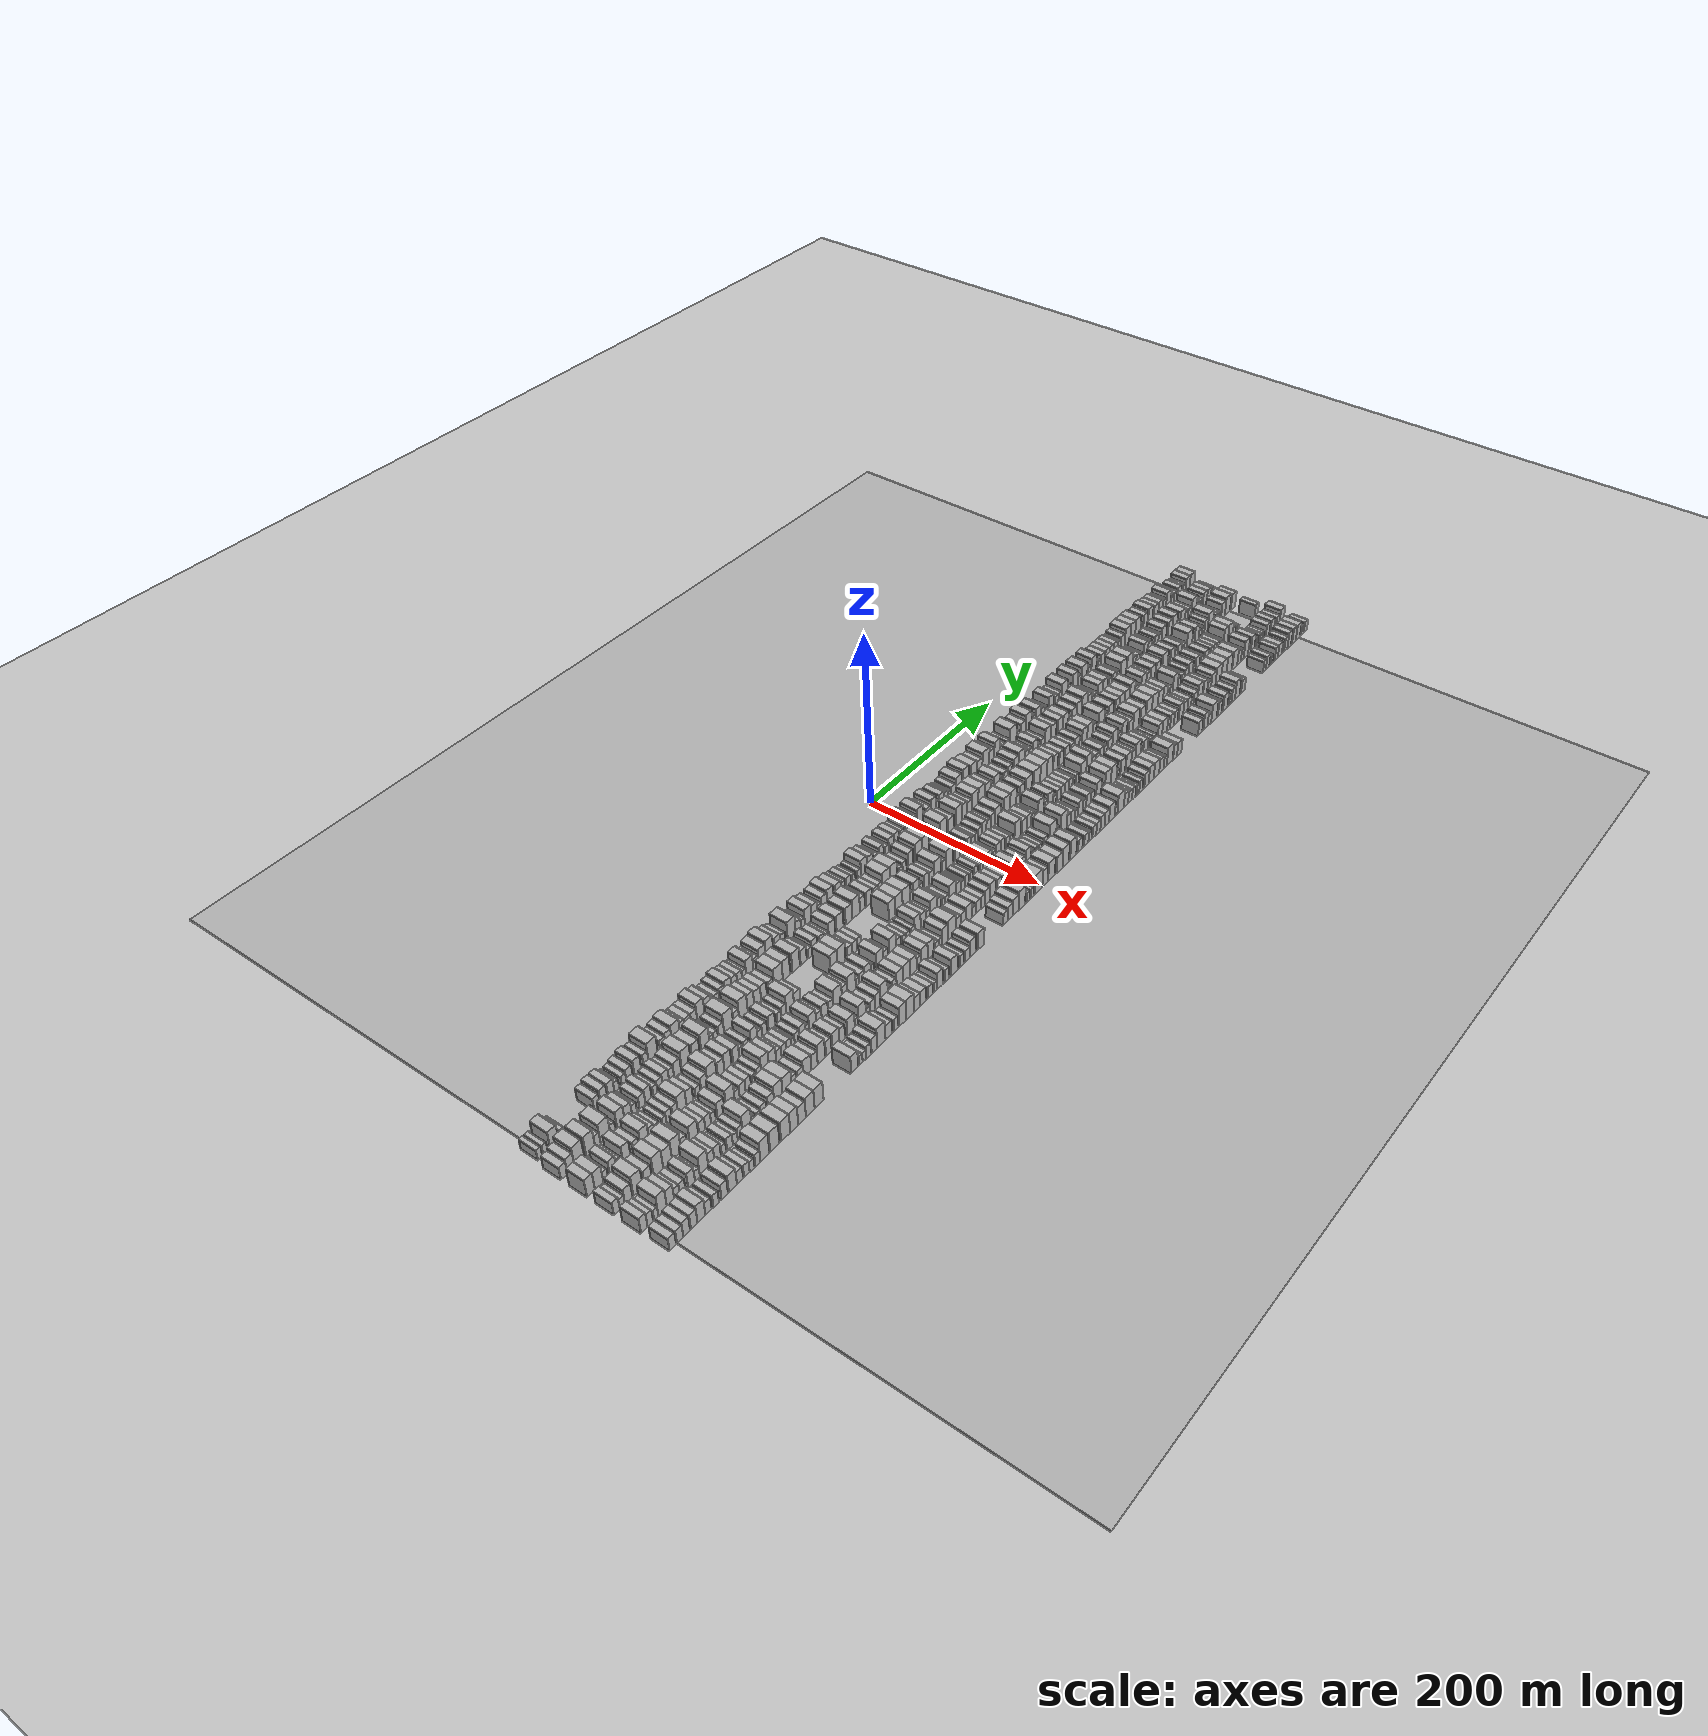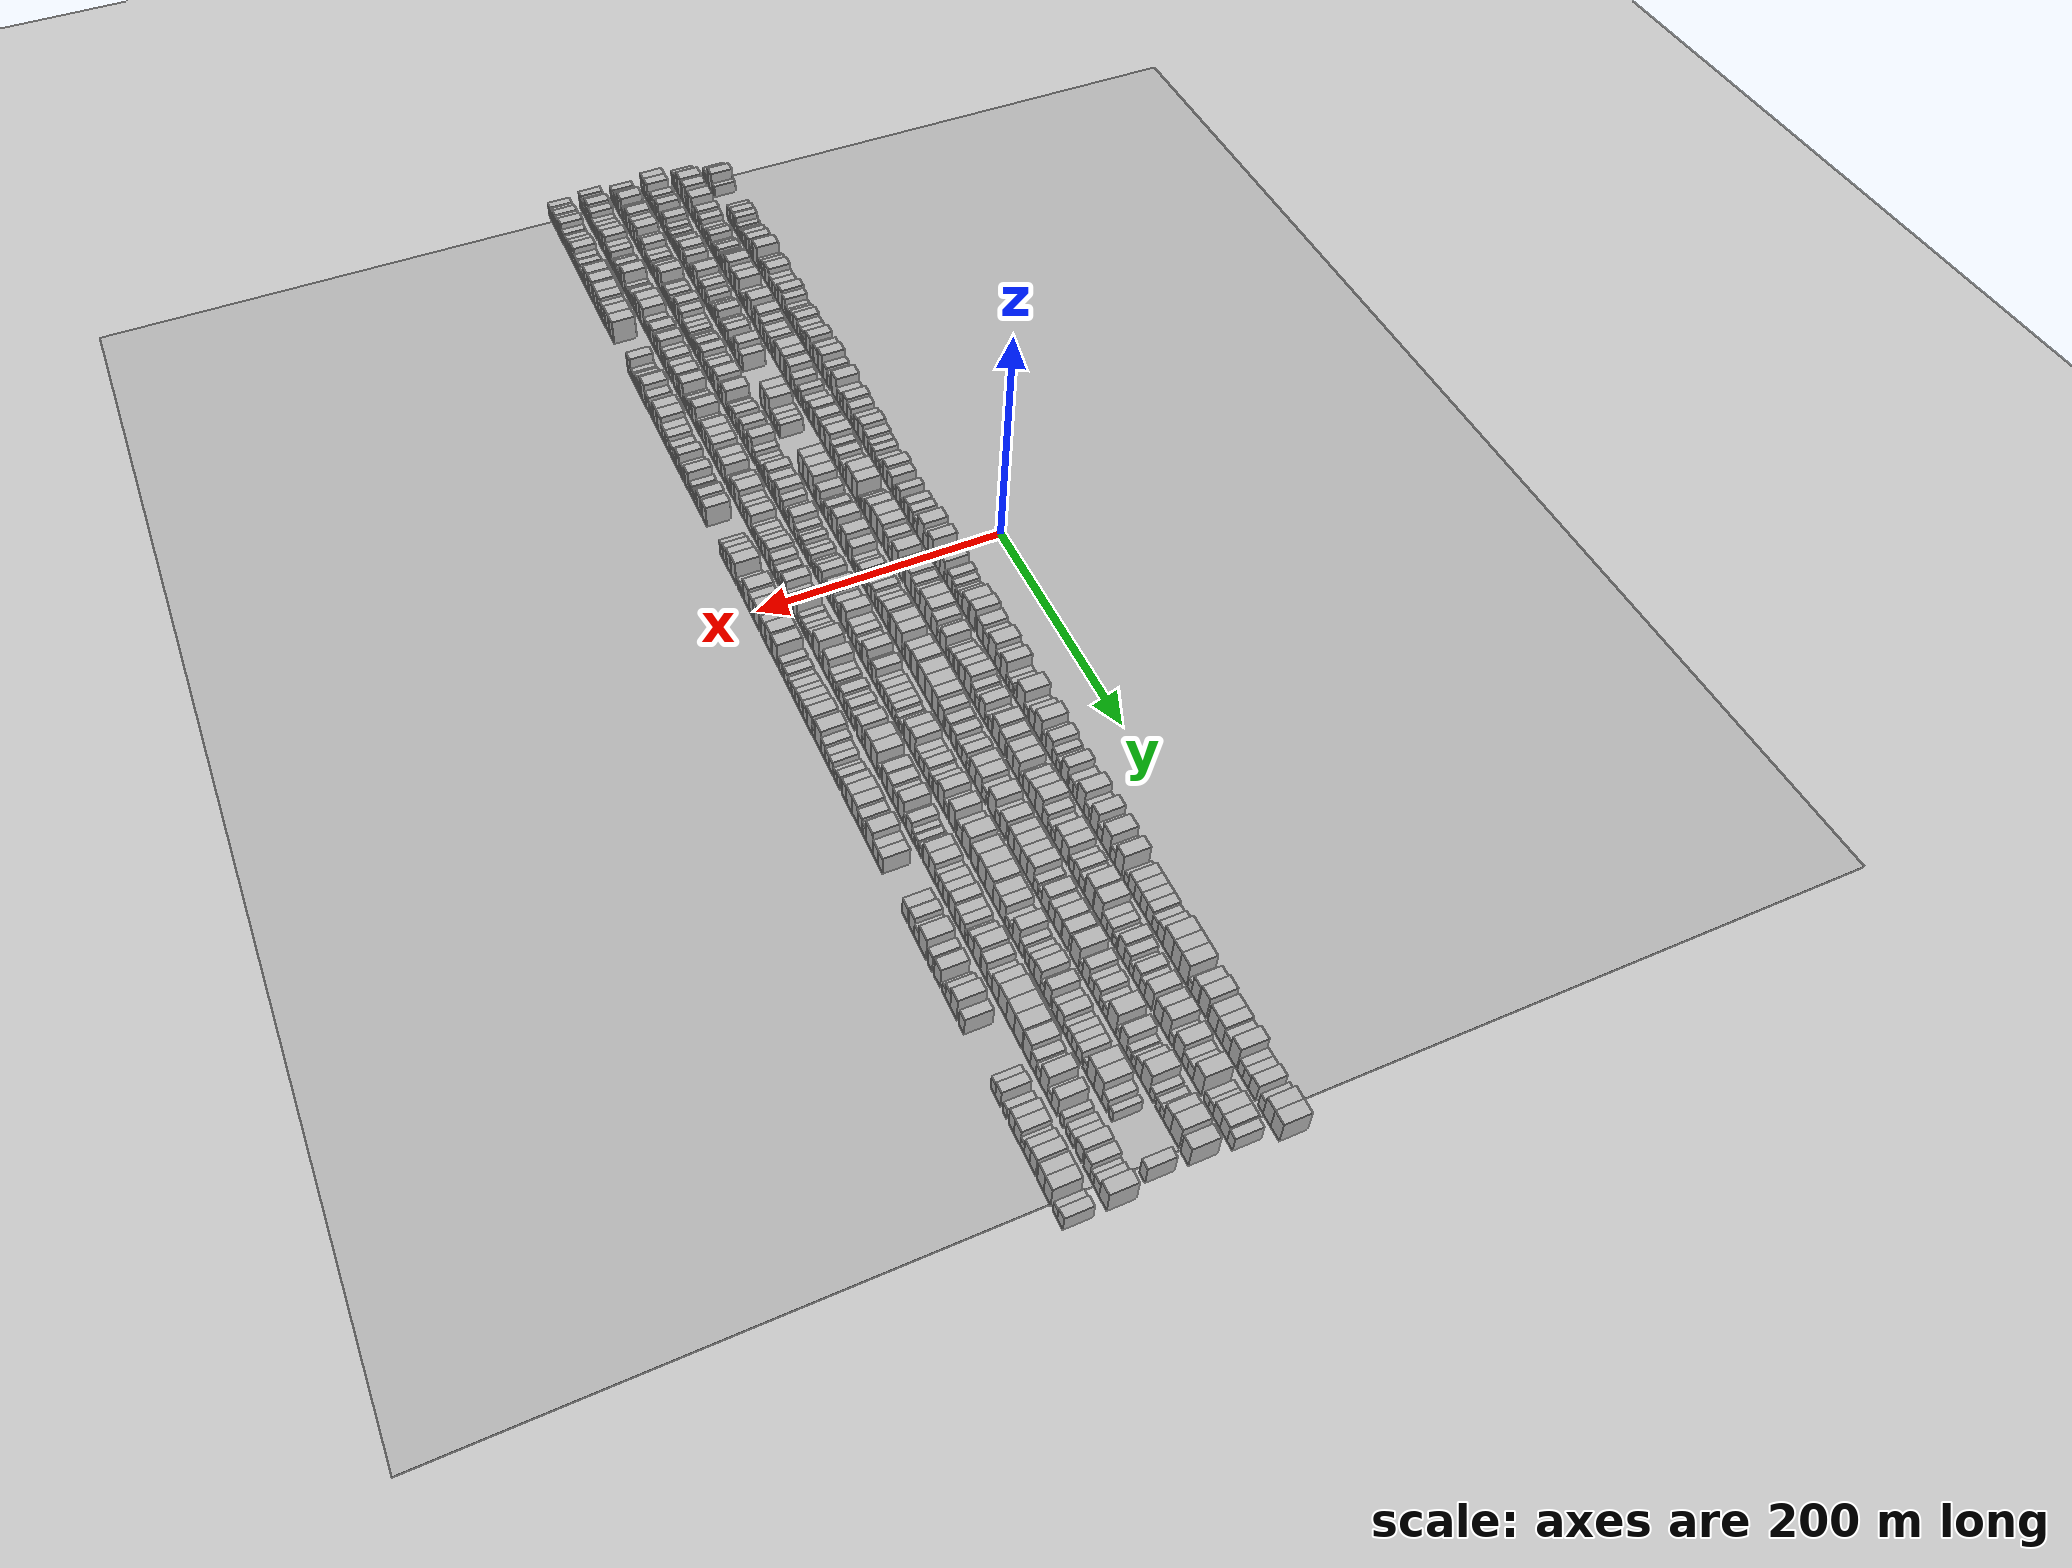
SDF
<?xml version="1.0" encoding="utf-8"?>

<sdf version="1.6">

   <world name="default">

      <gui fullscreen="0">

         <camera name="user_camera">

            <pose>-15 0 4.57585 0 0 0</pose>

            <view_controller>orbit</view_controller>

         </camera>

      </gui>

      <scene>

         <sky>

           <clouds>

             <speed>12</speed>

           </clouds>

         </sky>

         <ambient>0.4 0.4 0.4 1</ambient>

         <background>0.7 0.7 0.7 1</background>

         <shadows>1</shadows>

      </scene>

      <gravity>0 0 -9.8066</gravity>

      <magnetic_field>6e-06 2.3e-05 -4.2e-05</magnetic_field>

      <physics default="0" name="default_physics" type="ode">

         <ode>

            <solver>

               <type>quick</type>

               <iters>10</iters>

               <sor>1.0</sor>

               <use_dynamic_moi_rescaling>0</use_dynamic_moi_rescaling>

            </solver>

            <constraints>

               <cfm>0</cfm>

               <erp>0.2</erp>

               <contact_max_correcting_vel>100</contact_max_correcting_vel>

               <contact_surface_layer>0.001</contact_surface_layer>

            </constraints>

         </ode>

         <max_step_size>0.004</max_step_size>

         <real_time_factor>1</real_time_factor>

         <real_time_update_rate>250</real_time_update_rate>

      </physics>

      <light name="sun" type="directional">

         <cast_shadows>1</cast_shadows>

         <pose>0 0 10 0 0 0</pose>

         <diffuse>0.8 0.8 0.8 1</diffuse>

         <specular>0.2 0.2 0.2 1</specular>

         <attenuation>

            <range>1000</range>

            <constant>0.9</constant>

            <linear>0.01</linear>

            <quadratic>0.001</quadratic>

         </attenuation>

         <direction>-0.5 0.1 -0.9</direction>

      </light>

      <include>

         <name>ground_plane_1</name>

         <uri>model://HANNAS_ground_plane</uri>

         <pose>0 0 0  0 0 0</pose>

      </include>

      <include>

         <name>ground_plane_2</name>

         <uri>model://HANNAS_ground_plane</uri>

         <pose>100 0 0  0 0 0</pose>

      </include>

      <model name="building_1">

         <static>1</static>

         <pose frame="">50.0000 -504.5289 0 0.000000 0.000000 0.000000</pose>

         <link name="link">

            <pose frame="">0 0 6.00 0 0 0</pose>

            <collision name="collision">

               <geometry>

                  <box>

                     <size>20.0000 4.9422 12.0000</size>

                  </box>

               </geometry>

               <max_contacts>10</max_contacts>

               <surface>

                  <contact>

                     <ode/>

                  </contact>

                  <bounce/>

                  <friction>

                     <torsional>

                        <ode/>

                     </torsional>

                     <ode/>

                  </friction>

               </surface>

            </collision>

            <visual name="visual">

               <cast_shadows>0</cast_shadows>

               <geometry>

                  <box>

                     <size>20.0000 4.9422 12.0000</size>

                  </box>

               </geometry>

               <material>

                  <script>

                     <uri>model://HANNAS_wall/materials/scripts</uri>

                     <uri>model://HANNAS_wall/materials/textures</uri>

                     <name>vrc/HANNAS_wall</name>

                  </script>

               </material>

            </visual>

            <self_collide>0</self_collide>

            <enable_wind>0</enable_wind>

            <kinematic>0</kinematic>

         </link>

      </model>

      <model name="building_2">

         <static>1</static>

         <pose frame="">50.0000 -498.5857 0 0.000000 0.000000 0.000000</pose>

         <link name="link">

            <pose frame="">0 0 6.00 0 0 0</pose>

            <collision name="collision">

               <geometry>

                  <box>

                     <size>20.0000 4.9442 12.0000</size>

                  </box>

               </geometry>

               <max_contacts>10</max_contacts>

               <surface>

                  <contact>

                     <ode/>

                  </contact>

                  <bounce/>

                  <friction>

                     <torsional>

                        <ode/>

                     </torsional>

                     <ode/>

                  </friction>

               </surface>

            </collision>

            <visual name="visual">

               <cast_shadows>0</cast_shadows>

               <geometry>

                  <box>

                     <size>20.0000 4.9442 12.0000</size>

                  </box>

               </geometry>

               <material>

                  <script>

                     <uri>model://HANNAS_wall/materials/scripts</uri>

                     <uri>model://HANNAS_wall/materials/textures</uri>

                     <name>vrc/HANNAS_wall</name>

                  </script>

               </material>

            </visual>

            <self_collide>0</self_collide>

            <enable_wind>0</enable_wind>

            <kinematic>0</kinematic>

         </link>

      </model>

      <model name="building_3">

         <static>1</static>

         <pose frame="">50.0000 -488.2984 0 0.000000 0.000000 0.000000</pose>

         <link name="link">

            <pose frame="">0 0 10.50 0 0 0</pose>

            <collision name="collision">

               <geometry>

                  <box>

                     <size>20.0000 9.6305 21.0000</size>

                  </box>

               </geometry>

               <max_contacts>10</max_contacts>

               <surface>

                  <contact>

                     <ode/>

                  </contact>

                  <bounce/>

                  <friction>

                     <torsional>

                        <ode/>

                     </torsional>

                     <ode/>

                  </friction>

               </surface>

            </collision>

            <visual name="visual">

               <cast_shadows>0</cast_shadows>

               <geometry>

                  <box>

                     <size>20.0000 9.6305 21.0000</size>

                  </box>

               </geometry>

               <material>

                  <script>

                     <uri>model://HANNAS_wall/materials/scripts</uri>

                     <uri>model://HANNAS_wall/materials/textures</uri>

                     <name>vrc/HANNAS_wall</name>

                  </script>

               </material>

            </visual>

            <self_collide>0</self_collide>

            <enable_wind>0</enable_wind>

            <kinematic>0</kinematic>

         </link>

      </model>

      <model name="building_4">

         <static>1</static>

         <pose frame="">50.0000 -478.9975 0 0.000000 0.000000 0.000000</pose>

         <link name="link">

            <pose frame="">0 0 6.00 0 0 0</pose>

            <collision name="collision">

               <geometry>

                  <box>

                     <size>20.0000 4.9714 12.0000</size>

                  </box>

               </geometry>

               <max_contacts>10</max_contacts>

               <surface>

                  <contact>

                     <ode/>

                  </contact>

                  <bounce/>

                  <friction>

                     <torsional>

                        <ode/>

                     </torsional>

                     <ode/>

                  </friction>

               </surface>

            </collision>

            <visual name="visual">

               <cast_shadows>0</cast_shadows>

               <geometry>

                  <box>

                     <size>20.0000 4.9714 12.0000</size>

                  </box>

               </geometry>

               <material>

                  <script>

                     <uri>model://HANNAS_wall/materials/scripts</uri>

                     <uri>model://HANNAS_wall/materials/textures</uri>

                     <name>vrc/HANNAS_wall</name>

                  </script>

               </material>

            </visual>

            <self_collide>0</self_collide>

            <enable_wind>0</enable_wind>

            <kinematic>0</kinematic>

         </link>

      </model>

      <model name="building_5">

         <static>1</static>

         <pose frame="">50.0000 -440.1124 0 0.000000 0.000000 0.000000</pose>

         <link name="link">

            <pose frame="">0 0 7.50 0 0 0</pose>

            <collision name="collision">

               <geometry>

                  <box>

                     <size>20.0000 6.9329 15.0000</size>

                  </box>

               </geometry>

               <max_contacts>10</max_contacts>

               <surface>

                  <contact>

                     <ode/>

                  </contact>

                  <bounce/>

                  <friction>

                     <torsional>

                        <ode/>

                     </torsional>

                     <ode/>

                  </friction>

               </surface>

            </collision>

            <visual name="visual">

               <cast_shadows>0</cast_shadows>

               <geometry>

                  <box>

                     <size>20.0000 6.9329 15.0000</size>

                  </box>

               </geometry>

               <material>

                  <script>

                     <uri>model://HANNAS_wall/materials/scripts</uri>

                     <uri>model://HANNAS_wall/materials/textures</uri>

                     <name>vrc/HANNAS_wall</name>

                  </script>

               </material>

            </visual>

            <self_collide>0</self_collide>

            <enable_wind>0</enable_wind>

            <kinematic>0</kinematic>

         </link>

      </model>

      <model name="building_6">

         <static>1</static>

         <pose frame="">50.0000 -431.8344 0 0.000000 0.000000 0.000000</pose>

         <link name="link">

            <pose frame="">0 0 9.00 0 0 0</pose>

            <collision name="collision">

               <geometry>

                  <box>

                     <size>20.0000 7.6229 18.0000</size>

                  </box>

               </geometry>

               <max_contacts>10</max_contacts>

               <surface>

                  <contact>

                     <ode/>

                  </contact>

                  <bounce/>

                  <friction>

                     <torsional>

                        <ode/>

                     </torsional>

                     <ode/>

                  </friction>

               </surface>

            </collision>

            <visual name="visual">

               <cast_shadows>0</cast_shadows>

               <geometry>

                  <box>

                     <size>20.0000 7.6229 18.0000</size>

                  </box>

               </geometry>

               <material>

                  <script>

                     <uri>model://HANNAS_wall/materials/scripts</uri>

                     <uri>model://HANNAS_wall/materials/textures</uri>

                     <name>vrc/HANNAS_wall</name>

                  </script>

               </material>

            </visual>

            <self_collide>0</self_collide>

            <enable_wind>0</enable_wind>

            <kinematic>0</kinematic>

         </link>

      </model>

      <model name="building_7">

         <static>1</static>

         <pose frame="">50.0000 -423.3520 0 0.000000 0.000000 0.000000</pose>

         <link name="link">

            <pose frame="">0 0 9.00 0 0 0</pose>

            <collision name="collision">

               <geometry>

                  <box>

                     <size>20.0000 7.3419 18.0000</size>

                  </box>

               </geometry>

               <max_contacts>10</max_contacts>

               <surface>

                  <contact>

                     <ode/>

                  </contact>

                  <bounce/>

                  <friction>

                     <torsional>

                        <ode/>

                     </torsional>

                     <ode/>

                  </friction>

               </surface>

            </collision>

            <visual name="visual">

               <cast_shadows>0</cast_shadows>

               <geometry>

                  <box>

                     <size>20.0000 7.3419 18.0000</size>

                  </box>

               </geometry>

               <material>

                  <script>

                     <uri>model://HANNAS_wall/materials/scripts</uri>

                     <uri>model://HANNAS_wall/materials/textures</uri>

                     <name>vrc/HANNAS_wall</name>

                  </script>

               </material>

            </visual>

            <self_collide>0</self_collide>

            <enable_wind>0</enable_wind>

            <kinematic>0</kinematic>

         </link>

      </model>

      <model name="building_8">

         <static>1</static>

         <pose frame="">50.0000 -416.8708 0 0.000000 0.000000 0.000000</pose>

         <link name="link">

            <pose frame="">0 0 6.00 0 0 0</pose>

            <collision name="collision">

               <geometry>

                  <box>

                     <size>20.0000 5.6204 12.0000</size>

                  </box>

               </geometry>

               <max_contacts>10</max_contacts>

               <surface>

                  <contact>

                     <ode/>

                  </contact>

                  <bounce/>

                  <friction>

                     <torsional>

                        <ode/>

                     </torsional>

                     <ode/>

                  </friction>

               </surface>

            </collision>

            <visual name="visual">

               <cast_shadows>0</cast_shadows>

               <geometry>

                  <box>

                     <size>20.0000 5.6204 12.0000</size>

                  </box>

               </geometry>

               <material>

                  <script>

                     <uri>model://HANNAS_wall/materials/scripts</uri>

                     <uri>model://HANNAS_wall/materials/textures</uri>

                     <name>vrc/HANNAS_wall</name>

                  </script>

               </material>

            </visual>

            <self_collide>0</self_collide>

            <enable_wind>0</enable_wind>

            <kinematic>0</kinematic>

         </link>

      </model>

      <model name="building_9">

         <static>1</static>

         <pose frame="">50.0000 -408.2601 0 0.000000 0.000000 0.000000</pose>

         <link name="link">

            <pose frame="">0 0 6.00 0 0 0</pose>

            <collision name="collision">

               <geometry>

                  <box>

                     <size>20.0000 5.6011 12.0000</size>

                  </box>

               </geometry>

               <max_contacts>10</max_contacts>

               <surface>

                  <contact>

                     <ode/>

                  </contact>

                  <bounce/>

                  <friction>

                     <torsional>

                        <ode/>

                     </torsional>

                     <ode/>

                  </friction>

               </surface>

            </collision>

            <visual name="visual">

               <cast_shadows>0</cast_shadows>

               <geometry>

                  <box>

                     <size>20.0000 5.6011 12.0000</size>

                  </box>

               </geometry>

               <material>

                  <script>

                     <uri>model://HANNAS_wall/materials/scripts</uri>

                     <uri>model://HANNAS_wall/materials/textures</uri>

                     <name>vrc/HANNAS_wall</name>

                  </script>

               </material>

            </visual>

            <self_collide>0</self_collide>

            <enable_wind>0</enable_wind>

            <kinematic>0</kinematic>

         </link>

      </model>

      <model name="building_10">

         <static>1</static>

         <pose frame="">50.0000 -401.7760 0 0.000000 0.000000 0.000000</pose>

         <link name="link">

            <pose frame="">0 0 7.50 0 0 0</pose>

            <collision name="collision">

               <geometry>

                  <box>

                     <size>20.0000 7.3672 15.0000</size>

                  </box>

               </geometry>

               <max_contacts>10</max_contacts>

               <surface>

                  <contact>

                     <ode/>

                  </contact>

                  <bounce/>

                  <friction>

                     <torsional>

                        <ode/>

                     </torsional>

                     <ode/>

                  </friction>

               </surface>

            </collision>

            <visual name="visual">

               <cast_shadows>0</cast_shadows>

               <geometry>

                  <box>

                     <size>20.0000 7.3672 15.0000</size>

                  </box>

               </geometry>

               <material>

                  <script>

                     <uri>model://HANNAS_wall/materials/scripts</uri>

                     <uri>model://HANNAS_wall/materials/textures</uri>

                     <name>vrc/HANNAS_wall</name>

                  </script>

               </material>

            </visual>

            <self_collide>0</self_collide>

            <enable_wind>0</enable_wind>

            <kinematic>0</kinematic>

         </link>

      </model>

      <model name="building_11">

         <static>1</static>

         <pose frame="">50.0000 -392.0371 0 0.000000 0.000000 0.000000</pose>

         <link name="link">

            <pose frame="">0 0 9.00 0 0 0</pose>

            <collision name="collision">

               <geometry>

                  <box>

                     <size>20.0000 8.1105 18.0000</size>

                  </box>

               </geometry>

               <max_contacts>10</max_contacts>

               <surface>

                  <contact>

                     <ode/>

                  </contact>

                  <bounce/>

                  <friction>

                     <torsional>

                        <ode/>

                     </torsional>

                     <ode/>

                  </friction>

               </surface>

            </collision>

            <visual name="visual">

               <cast_shadows>0</cast_shadows>

               <geometry>

                  <box>

                     <size>20.0000 8.1105 18.0000</size>

                  </box>

               </geometry>

               <material>

                  <script>

                     <uri>model://HANNAS_wall/materials/scripts</uri>

                     <uri>model://HANNAS_wall/materials/textures</uri>

                     <name>vrc/HANNAS_wall</name>

                  </script>

               </material>

            </visual>

            <self_collide>0</self_collide>

            <enable_wind>0</enable_wind>

            <kinematic>0</kinematic>

         </link>

      </model>

      <model name="building_12">

         <static>1</static>

         <pose frame="">50.0000 -381.9320 0 0.000000 0.000000 0.000000</pose>

         <link name="link">

            <pose frame="">0 0 7.50 0 0 0</pose>

            <collision name="collision">

               <geometry>

                  <box>

                     <size>20.0000 6.0998 15.0000</size>

                  </box>

               </geometry>

               <max_contacts>10</max_contacts>

               <surface>

                  <contact>

                     <ode/>

                  </contact>

                  <bounce/>

                  <friction>

                     <torsional>

                        <ode/>

                     </torsional>

                     <ode/>

                  </friction>

               </surface>

            </collision>

            <visual name="visual">

               <cast_shadows>0</cast_shadows>

               <geometry>

                  <box>

                     <size>20.0000 6.0998 15.0000</size>

                  </box>

               </geometry>

               <material>

                  <script>

                     <uri>model://HANNAS_wall/materials/scripts</uri>

                     <uri>model://HANNAS_wall/materials/textures</uri>

                     <name>vrc/HANNAS_wall</name>

                  </script>

               </material>

            </visual>

            <self_collide>0</self_collide>

            <enable_wind>0</enable_wind>

            <kinematic>0</kinematic>

         </link>

      </model>

      <model name="building_13">

         <static>1</static>

         <pose frame="">50.0000 -373.1637 0 0.000000 0.000000 0.000000</pose>

         <link name="link">

            <pose frame="">0 0 12.00 0 0 0</pose>

            <collision name="collision">

               <geometry>

                  <box>

                     <size>20.0000 11.4367 24.0000</size>

                  </box>

               </geometry>

               <max_contacts>10</max_contacts>

               <surface>

                  <contact>

                     <ode/>

                  </contact>

                  <bounce/>

                  <friction>

                     <torsional>

                        <ode/>

                     </torsional>

                     <ode/>

                  </friction>

               </surface>

            </collision>

            <visual name="visual">

               <cast_shadows>0</cast_shadows>

               <geometry>

                  <box>

                     <size>20.0000 11.4367 24.0000</size>

                  </box>

               </geometry>

               <material>

                  <script>

                     <uri>model://HANNAS_wall/materials/scripts</uri>

                     <uri>model://HANNAS_wall/materials/textures</uri>

                     <name>vrc/HANNAS_wall</name>

                  </script>

               </material>

            </visual>

            <self_collide>0</self_collide>

            <enable_wind>0</enable_wind>

            <kinematic>0</kinematic>

         </link>

      </model>

      <model name="building_14">

         <static>1</static>

         <pose frame="">50.0000 -361.1262 0 0.000000 0.000000 0.000000</pose>

         <link name="link">

            <pose frame="">0 0 7.50 0 0 0</pose>

            <collision name="collision">

               <geometry>

                  <box>

                     <size>20.0000 6.6384 15.0000</size>

                  </box>

               </geometry>

               <max_contacts>10</max_contacts>

               <surface>

                  <contact>

                     <ode/>

                  </contact>

                  <bounce/>

                  <friction>

                     <torsional>

                        <ode/>

                     </torsional>

                     <ode/>

                  </friction>

               </surface>

            </collision>

            <visual name="visual">

               <cast_shadows>0</cast_shadows>

               <geometry>

                  <box>

                     <size>20.0000 6.6384 15.0000</size>

                  </box>

               </geometry>

               <material>

                  <script>

                     <uri>model://HANNAS_wall/materials/scripts</uri>

                     <uri>model://HANNAS_wall/materials/textures</uri>

                     <name>vrc/HANNAS_wall</name>

                  </script>

               </material>

            </visual>

            <self_collide>0</self_collide>

            <enable_wind>0</enable_wind>

            <kinematic>0</kinematic>

         </link>

      </model>

      <model name="building_15">

         <static>1</static>

         <pose frame="">50.0000 -353.9761 0 0.000000 0.000000 0.000000</pose>

         <link name="link">

            <pose frame="">0 0 9.00 0 0 0</pose>

            <collision name="collision">

               <geometry>

                  <box>

                     <size>20.0000 7.6617 18.0000</size>

                  </box>

               </geometry>

               <max_contacts>10</max_contacts>

               <surface>

                  <contact>

                     <ode/>

                  </contact>

                  <bounce/>

                  <friction>

                     <torsional>

                        <ode/>

                     </torsional>

                     <ode/>

                  </friction>

               </surface>

            </collision>

            <visual name="visual">

               <cast_shadows>0</cast_shadows>

               <geometry>

                  <box>

                     <size>20.0000 7.6617 18.0000</size>

                  </box>

               </geometry>

               <material>

                  <script>

                     <uri>model://HANNAS_wall/materials/scripts</uri>

                     <uri>model://HANNAS_wall/materials/textures</uri>

                     <name>vrc/HANNAS_wall</name>

                  </script>

               </material>

            </visual>

            <self_collide>0</self_collide>

            <enable_wind>0</enable_wind>

            <kinematic>0</kinematic>

         </link>

      </model>

      <model name="building_16">

         <static>1</static>

         <pose frame="">50.0000 -344.9785 0 0.000000 0.000000 0.000000</pose>

         <link name="link">

            <pose frame="">0 0 10.50 0 0 0</pose>

            <collision name="collision">

               <geometry>

                  <box>

                     <size>20.0000 10.3335 21.0000</size>

                  </box>

               </geometry>

               <max_contacts>10</max_contacts>

               <surface>

                  <contact>

                     <ode/>

                  </contact>

                  <bounce/>

                  <friction>

                     <torsional>

                        <ode/>

                     </torsional>

                     <ode/>

                  </friction>

               </surface>

            </collision>

            <visual name="visual">

               <cast_shadows>0</cast_shadows>

               <geometry>

                  <box>

                     <size>20.0000 10.3335 21.0000</size>

                  </box>

               </geometry>

               <material>

                  <script>

                     <uri>model://HANNAS_wall/materials/scripts</uri>

                     <uri>model://HANNAS_wall/materials/textures</uri>

                     <name>vrc/HANNAS_wall</name>

                  </script>

               </material>

            </visual>

            <self_collide>0</self_collide>

            <enable_wind>0</enable_wind>

            <kinematic>0</kinematic>

         </link>

      </model>

      <model name="building_17">

         <static>1</static>

         <pose frame="">50.0000 -336.5088 0 0.000000 0.000000 0.000000</pose>

         <link name="link">

            <pose frame="">0 0 7.50 0 0 0</pose>

            <collision name="collision">

               <geometry>

                  <box>

                     <size>20.0000 6.6061 15.0000</size>

                  </box>

               </geometry>

               <max_contacts>10</max_contacts>

               <surface>

                  <contact>

                     <ode/>

                  </contact>

                  <bounce/>

                  <friction>

                     <torsional>

                        <ode/>

                     </torsional>

                     <ode/>

                  </friction>

               </surface>

            </collision>

            <visual name="visual">

               <cast_shadows>0</cast_shadows>

               <geometry>

                  <box>

                     <size>20.0000 6.6061 15.0000</size>

                  </box>

               </geometry>

               <material>

                  <script>

                     <uri>model://HANNAS_wall/materials/scripts</uri>

                     <uri>model://HANNAS_wall/materials/textures</uri>

                     <name>vrc/HANNAS_wall</name>

                  </script>

               </material>

            </visual>

            <self_collide>0</self_collide>

            <enable_wind>0</enable_wind>

            <kinematic>0</kinematic>

         </link>

      </model>

      <model name="building_18">

         <static>1</static>

         <pose frame="">50.0000 -329.4688 0 0.000000 0.000000 0.000000</pose>

         <link name="link">

            <pose frame="">0 0 7.50 0 0 0</pose>

            <collision name="collision">

               <geometry>

                  <box>

                     <size>20.0000 7.4738 15.0000</size>

                  </box>

               </geometry>

               <max_contacts>10</max_contacts>

               <surface>

                  <contact>

                     <ode/>

                  </contact>

                  <bounce/>

                  <friction>

                     <torsional>

                        <ode/>

                     </torsional>

                     <ode/>

                  </friction>

               </surface>

            </collision>

            <visual name="visual">

               <cast_shadows>0</cast_shadows>

               <geometry>

                  <box>

                     <size>20.0000 7.4738 15.0000</size>

                  </box>

               </geometry>

               <material>

                  <script>

                     <uri>model://HANNAS_wall/materials/scripts</uri>

                     <uri>model://HANNAS_wall/materials/textures</uri>

                     <name>vrc/HANNAS_wall</name>

                  </script>

               </material>

            </visual>

            <self_collide>0</self_collide>

            <enable_wind>0</enable_wind>

            <kinematic>0</kinematic>

         </link>

      </model>

      <model name="building_19">

         <static>1</static>

         <pose frame="">50.0000 -322.1646 0 0.000000 0.000000 0.000000</pose>

         <link name="link">

            <pose frame="">0 0 7.50 0 0 0</pose>

            <collision name="collision">

               <geometry>

                  <box>

                     <size>20.0000 7.1347 15.0000</size>

                  </box>

               </geometry>

               <max_contacts>10</max_contacts>

               <surface>

                  <contact>

                     <ode/>

                  </contact>

                  <bounce/>

                  <friction>

                     <torsional>

                        <ode/>

                     </torsional>

                     <ode/>

                  </friction>

               </surface>

            </collision>

            <visual name="visual">

               <cast_shadows>0</cast_shadows>

               <geometry>

                  <box>

                     <size>20.0000 7.1347 15.0000</size>

                  </box>

               </geometry>

               <material>

                  <script>

                     <uri>model://HANNAS_wall/materials/scripts</uri>

                     <uri>model://HANNAS_wall/materials/textures</uri>

                     <name>vrc/HANNAS_wall</name>

                  </script>

               </material>

            </visual>

            <self_collide>0</self_collide>

            <enable_wind>0</enable_wind>

            <kinematic>0</kinematic>

         </link>

      </model>

      <model name="building_20">

         <static>1</static>

         <pose frame="">50.0000 -313.8175 0 0.000000 0.000000 0.000000</pose>

         <link name="link">

            <pose frame="">0 0 10.50 0 0 0</pose>

            <collision name="collision">

               <geometry>

                  <box>

                     <size>20.0000 9.5596 21.0000</size>

                  </box>

               </geometry>

               <max_contacts>10</max_contacts>

               <surface>

                  <contact>

                     <ode/>

                  </contact>

                  <bounce/>

                  <friction>

                     <torsional>

                        <ode/>

                     </torsional>

                     <ode/>

                  </friction>

               </surface>

            </collision>

            <visual name="visual">

               <cast_shadows>0</cast_shadows>

               <geometry>

                  <box>

                     <size>20.0000 9.5596 21.0000</size>

                  </box>

               </geometry>

               <material>

                  <script>

                     <uri>model://HANNAS_wall/materials/scripts</uri>

                     <uri>model://HANNAS_wall/materials/textures</uri>

                     <name>vrc/HANNAS_wall</name>

                  </script>

               </material>

            </visual>

            <self_collide>0</self_collide>

            <enable_wind>0</enable_wind>

            <kinematic>0</kinematic>

         </link>

      </model>

      <model name="building_21">

         <static>1</static>

         <pose frame="">50.0000 -304.9771 0 0.000000 0.000000 0.000000</pose>

         <link name="link">

            <pose frame="">0 0 9.00 0 0 0</pose>

            <collision name="collision">

               <geometry>

                  <box>

                     <size>20.0000 8.1212 18.0000</size>

                  </box>

               </geometry>

               <max_contacts>10</max_contacts>

               <surface>

                  <contact>

                     <ode/>

                  </contact>

                  <bounce/>

                  <friction>

                     <torsional>

                        <ode/>

                     </torsional>

                     <ode/>

                  </friction>

               </surface>

            </collision>

            <visual name="visual">

               <cast_shadows>0</cast_shadows>

               <geometry>

                  <box>

                     <size>20.0000 8.1212 18.0000</size>

                  </box>

               </geometry>

               <material>

                  <script>

                     <uri>model://HANNAS_wall/materials/scripts</uri>

                     <uri>model://HANNAS_wall/materials/textures</uri>

                     <name>vrc/HANNAS_wall</name>

                  </script>

               </material>

            </visual>

            <self_collide>0</self_collide>

            <enable_wind>0</enable_wind>

            <kinematic>0</kinematic>

         </link>

      </model>

      <model name="building_22">

         <static>1</static>

         <pose frame="">50.0000 -298.2765 0 0.000000 0.000000 0.000000</pose>

         <link name="link">

            <pose frame="">0 0 6.00 0 0 0</pose>

            <collision name="collision">

               <geometry>

                  <box>

                     <size>20.0000 5.2802 12.0000</size>

                  </box>

               </geometry>

               <max_contacts>10</max_contacts>

               <surface>

                  <contact>

                     <ode/>

                  </contact>

                  <bounce/>

                  <friction>

                     <torsional>

                        <ode/>

                     </torsional>

                     <ode/>

                  </friction>

               </surface>

            </collision>

            <visual name="visual">

               <cast_shadows>0</cast_shadows>

               <geometry>

                  <box>

                     <size>20.0000 5.2802 12.0000</size>

                  </box>

               </geometry>

               <material>

                  <script>

                     <uri>model://HANNAS_wall/materials/scripts</uri>

                     <uri>model://HANNAS_wall/materials/textures</uri>

                     <name>vrc/HANNAS_wall</name>

                  </script>

               </material>

            </visual>

            <self_collide>0</self_collide>

            <enable_wind>0</enable_wind>

            <kinematic>0</kinematic>

         </link>

      </model>

      <model name="building_23">

         <static>1</static>

         <pose frame="">50.0000 -292.7118 0 0.000000 0.000000 0.000000</pose>

         <link name="link">

            <pose frame="">0 0 6.00 0 0 0</pose>

            <collision name="collision">

               <geometry>

                  <box>

                     <size>20.0000 5.8492 12.0000</size>

                  </box>

               </geometry>

               <max_contacts>10</max_contacts>

               <surface>

                  <contact>

                     <ode/>

                  </contact>

                  <bounce/>

                  <friction>

                     <torsional>

                        <ode/>

                     </torsional>

                     <ode/>

                  </friction>

               </surface>

            </collision>

            <visual name="visual">

               <cast_shadows>0</cast_shadows>

               <geometry>

                  <box>

                     <size>20.0000 5.8492 12.0000</size>

                  </box>

               </geometry>

               <material>

                  <script>

                     <uri>model://HANNAS_wall/materials/scripts</uri>

                     <uri>model://HANNAS_wall/materials/textures</uri>

                     <name>vrc/HANNAS_wall</name>

                  </script>

               </material>

            </visual>

            <self_collide>0</self_collide>

            <enable_wind>0</enable_wind>

            <kinematic>0</kinematic>

         </link>

      </model>

      <model name="building_24">

         <static>1</static>

         <pose frame="">50.0000 -286.2652 0 0.000000 0.000000 0.000000</pose>

         <link name="link">

            <pose frame="">0 0 7.50 0 0 0</pose>

            <collision name="collision">

               <geometry>

                  <box>

                     <size>20.0000 7.0440 15.0000</size>

                  </box>

               </geometry>

               <max_contacts>10</max_contacts>

               <surface>

                  <contact>

                     <ode/>

                  </contact>

                  <bounce/>

                  <friction>

                     <torsional>

                        <ode/>

                     </torsional>

                     <ode/>

                  </friction>

               </surface>

            </collision>

            <visual name="visual">

               <cast_shadows>0</cast_shadows>

               <geometry>

                  <box>

                     <size>20.0000 7.0440 15.0000</size>

                  </box>

               </geometry>

               <material>

                  <script>

                     <uri>model://HANNAS_wall/materials/scripts</uri>

                     <uri>model://HANNAS_wall/materials/textures</uri>

                     <name>vrc/HANNAS_wall</name>

                  </script>

               </material>

            </visual>

            <self_collide>0</self_collide>

            <enable_wind>0</enable_wind>

            <kinematic>0</kinematic>

         </link>

      </model>

      <model name="building_25">

         <static>1</static>

         <pose frame="">50.0000 -278.2577 0 0.000000 0.000000 0.000000</pose>

         <link name="link">

            <pose frame="">0 0 9.00 0 0 0</pose>

            <collision name="collision">

               <geometry>

                  <box>

                     <size>20.0000 8.9712 18.0000</size>

                  </box>

               </geometry>

               <max_contacts>10</max_contacts>

               <surface>

                  <contact>

                     <ode/>

                  </contact>

                  <bounce/>

                  <friction>

                     <torsional>

                        <ode/>

                     </torsional>

                     <ode/>

                  </friction>

               </surface>

            </collision>

            <visual name="visual">

               <cast_shadows>0</cast_shadows>

               <geometry>

                  <box>

                     <size>20.0000 8.9712 18.0000</size>

                  </box>

               </geometry>

               <material>

                  <script>

                     <uri>model://HANNAS_wall/materials/scripts</uri>

                     <uri>model://HANNAS_wall/materials/textures</uri>

                     <name>vrc/HANNAS_wall</name>

                  </script>

               </material>

            </visual>

            <self_collide>0</self_collide>

            <enable_wind>0</enable_wind>

            <kinematic>0</kinematic>

         </link>

      </model>

      <model name="building_26">

         <static>1</static>

         <pose frame="">50.0000 -270.0726 0 0.000000 0.000000 0.000000</pose>

         <link name="link">

            <pose frame="">0 0 7.50 0 0 0</pose>

            <collision name="collision">

               <geometry>

                  <box>

                     <size>20.0000 7.3989 15.0000</size>

                  </box>

               </geometry>

               <max_contacts>10</max_contacts>

               <surface>

                  <contact>

                     <ode/>

                  </contact>

                  <bounce/>

                  <friction>

                     <torsional>

                        <ode/>

                     </torsional>

                     <ode/>

                  </friction>

               </surface>

            </collision>

            <visual name="visual">

               <cast_shadows>0</cast_shadows>

               <geometry>

                  <box>

                     <size>20.0000 7.3989 15.0000</size>

                  </box>

               </geometry>

               <material>

                  <script>

                     <uri>model://HANNAS_wall/materials/scripts</uri>

                     <uri>model://HANNAS_wall/materials/textures</uri>

                     <name>vrc/HANNAS_wall</name>

                  </script>

               </material>

            </visual>

            <self_collide>0</self_collide>

            <enable_wind>0</enable_wind>

            <kinematic>0</kinematic>

         </link>

      </model>

      <model name="building_27">

         <static>1</static>

         <pose frame="">50.0000 -263.1609 0 0.000000 0.000000 0.000000</pose>

         <link name="link">

            <pose frame="">0 0 7.50 0 0 0</pose>

            <collision name="collision">

               <geometry>

                  <box>

                     <size>20.0000 6.4247 15.0000</size>

                  </box>

               </geometry>

               <max_contacts>10</max_contacts>

               <surface>

                  <contact>

                     <ode/>

                  </contact>

                  <bounce/>

                  <friction>

                     <torsional>

                        <ode/>

                     </torsional>

                     <ode/>

                  </friction>

               </surface>

            </collision>

            <visual name="visual">

               <cast_shadows>0</cast_shadows>

               <geometry>

                  <box>

                     <size>20.0000 6.4247 15.0000</size>

                  </box>

               </geometry>

               <material>

                  <script>

                     <uri>model://HANNAS_wall/materials/scripts</uri>

                     <uri>model://HANNAS_wall/materials/textures</uri>

                     <name>vrc/HANNAS_wall</name>

                  </script>

               </material>

            </visual>

            <self_collide>0</self_collide>

            <enable_wind>0</enable_wind>

            <kinematic>0</kinematic>

         </link>

      </model>

      <model name="building_28">

         <static>1</static>

         <pose frame="">50.0000 -257.1534 0 0.000000 0.000000 0.000000</pose>

         <link name="link">

            <pose frame="">0 0 6.00 0 0 0</pose>

            <collision name="collision">

               <geometry>

                  <box>

                     <size>20.0000 5.5902 12.0000</size>

                  </box>

               </geometry>

               <max_contacts>10</max_contacts>

               <surface>

                  <contact>

                     <ode/>

                  </contact>

                  <bounce/>

                  <friction>

                     <torsional>

                        <ode/>

                     </torsional>

                     <ode/>

                  </friction>

               </surface>

            </collision>

            <visual name="visual">

               <cast_shadows>0</cast_shadows>

               <geometry>

                  <box>

                     <size>20.0000 5.5902 12.0000</size>

                  </box>

               </geometry>

               <material>

                  <script>

                     <uri>model://HANNAS_wall/materials/scripts</uri>

                     <uri>model://HANNAS_wall/materials/textures</uri>

                     <name>vrc/HANNAS_wall</name>

                  </script>

               </material>

            </visual>

            <self_collide>0</self_collide>

            <enable_wind>0</enable_wind>

            <kinematic>0</kinematic>

         </link>

      </model>

      <model name="building_29">

         <static>1</static>

         <pose frame="">50.0000 -249.5516 0 0.000000 0.000000 0.000000</pose>

         <link name="link">

            <pose frame="">0 0 10.50 0 0 0</pose>

            <collision name="collision">

               <geometry>

                  <box>

                     <size>20.0000 9.6134 21.0000</size>

                  </box>

               </geometry>

               <max_contacts>10</max_contacts>

               <surface>

                  <contact>

                     <ode/>

                  </contact>

                  <bounce/>

                  <friction>

                     <torsional>

                        <ode/>

                     </torsional>

                     <ode/>

                  </friction>

               </surface>

            </collision>

            <visual name="visual">

               <cast_shadows>0</cast_shadows>

               <geometry>

                  <box>

                     <size>20.0000 9.6134 21.0000</size>

                  </box>

               </geometry>

               <material>

                  <script>

                     <uri>model://HANNAS_wall/materials/scripts</uri>

                     <uri>model://HANNAS_wall/materials/textures</uri>

                     <name>vrc/HANNAS_wall</name>

                  </script>

               </material>

            </visual>

            <self_collide>0</self_collide>

            <enable_wind>0</enable_wind>

            <kinematic>0</kinematic>

         </link>

      </model>

      <model name="building_30">

         <static>1</static>

         <pose frame="">50.0000 -241.0410 0 0.000000 0.000000 0.000000</pose>

         <link name="link">

            <pose frame="">0 0 7.50 0 0 0</pose>

            <collision name="collision">

               <geometry>

                  <box>

                     <size>20.0000 7.4080 15.0000</size>

                  </box>

               </geometry>

               <max_contacts>10</max_contacts>

               <surface>

                  <contact>

                     <ode/>

                  </contact>

                  <bounce/>

                  <friction>

                     <torsional>

                        <ode/>

                     </torsional>

                     <ode/>

                  </friction>

               </surface>

            </collision>

            <visual name="visual">

               <cast_shadows>0</cast_shadows>

               <geometry>

                  <box>

                     <size>20.0000 7.4080 15.0000</size>

                  </box>

               </geometry>

               <material>

                  <script>

                     <uri>model://HANNAS_wall/materials/scripts</uri>

                     <uri>model://HANNAS_wall/materials/textures</uri>

                     <name>vrc/HANNAS_wall</name>

                  </script>

               </material>

            </visual>

            <self_collide>0</self_collide>

            <enable_wind>0</enable_wind>

            <kinematic>0</kinematic>

         </link>

      </model>

      <model name="building_31">

         <static>1</static>

         <pose frame="">50.0000 -232.5062 0 0.000000 0.000000 0.000000</pose>

         <link name="link">

            <pose frame="">0 0 10.50 0 0 0</pose>

            <collision name="collision">

               <geometry>

                  <box>

                     <size>20.0000 9.6617 21.0000</size>

                  </box>

               </geometry>

               <max_contacts>10</max_contacts>

               <surface>

                  <contact>

                     <ode/>

                  </contact>

                  <bounce/>

                  <friction>

                     <torsional>

                        <ode/>

                     </torsional>

                     <ode/>

                  </friction>

               </surface>

            </collision>

            <visual name="visual">

               <cast_shadows>0</cast_shadows>

               <geometry>

                  <box>

                     <size>20.0000 9.6617 21.0000</size>

                  </box>

               </geometry>

               <material>

                  <script>

                     <uri>model://HANNAS_wall/materials/scripts</uri>

                     <uri>model://HANNAS_wall/materials/textures</uri>

                     <name>vrc/HANNAS_wall</name>

                  </script>

               </material>

            </visual>

            <self_collide>0</self_collide>

            <enable_wind>0</enable_wind>

            <kinematic>0</kinematic>

         </link>

      </model>

      <model name="building_32">

         <static>1</static>

         <pose frame="">50.0000 -222.6130 0 0.000000 0.000000 0.000000</pose>

         <link name="link">

            <pose frame="">0 0 12.00 0 0 0</pose>

            <collision name="collision">

               <geometry>

                  <box>

                     <size>20.0000 10.1246 24.0000</size>

                  </box>

               </geometry>

               <max_contacts>10</max_contacts>

               <surface>

                  <contact>

                     <ode/>

                  </contact>

                  <bounce/>

                  <friction>

                     <torsional>

                        <ode/>

                     </torsional>

                     <ode/>

                  </friction>

               </surface>

            </collision>

            <visual name="visual">

               <cast_shadows>0</cast_shadows>

               <geometry>

                  <box>

                     <size>20.0000 10.1246 24.0000</size>

                  </box>

               </geometry>

               <material>

                  <script>

                     <uri>model://HANNAS_wall/materials/scripts</uri>

                     <uri>model://HANNAS_wall/materials/textures</uri>

                     <name>vrc/HANNAS_wall</name>

                  </script>

               </material>

            </visual>

            <self_collide>0</self_collide>

            <enable_wind>0</enable_wind>

            <kinematic>0</kinematic>

         </link>

      </model>

      <model name="building_33">

         <static>1</static>

         <pose frame="">50.0000 -211.7098 0 0.000000 0.000000 0.000000</pose>

         <link name="link">

            <pose frame="">0 0 9.00 0 0 0</pose>

            <collision name="collision">

               <geometry>

                  <box>

                     <size>20.0000 7.6817 18.0000</size>

                  </box>

               </geometry>

               <max_contacts>10</max_contacts>

               <surface>

                  <contact>

                     <ode/>

                  </contact>

                  <bounce/>

                  <friction>

                     <torsional>

                        <ode/>

                     </torsional>

                     <ode/>

                  </friction>

               </surface>

            </collision>

            <visual name="visual">

               <cast_shadows>0</cast_shadows>

               <geometry>

                  <box>

                     <size>20.0000 7.6817 18.0000</size>

                  </box>

               </geometry>

               <material>

                  <script>

                     <uri>model://HANNAS_wall/materials/scripts</uri>

                     <uri>model://HANNAS_wall/materials/textures</uri>

                     <name>vrc/HANNAS_wall</name>

                  </script>

               </material>

            </visual>

            <self_collide>0</self_collide>

            <enable_wind>0</enable_wind>

            <kinematic>0</kinematic>

         </link>

      </model>

      <model name="building_34">

         <static>1</static>

         <pose frame="">50.0000 -204.3308 0 0.000000 0.000000 0.000000</pose>

         <link name="link">

            <pose frame="">0 0 7.50 0 0 0</pose>

            <collision name="collision">

               <geometry>

                  <box>

                     <size>20.0000 7.0763 15.0000</size>

                  </box>

               </geometry>

               <max_contacts>10</max_contacts>

               <surface>

                  <contact>

                     <ode/>

                  </contact>

                  <bounce/>

                  <friction>

                     <torsional>

                        <ode/>

                     </torsional>

                     <ode/>

                  </friction>

               </surface>

            </collision>

            <visual name="visual">

               <cast_shadows>0</cast_shadows>

               <geometry>

                  <box>

                     <size>20.0000 7.0763 15.0000</size>

                  </box>

               </geometry>

               <material>

                  <script>

                     <uri>model://HANNAS_wall/materials/scripts</uri>

                     <uri>model://HANNAS_wall/materials/textures</uri>

                     <name>vrc/HANNAS_wall</name>

                  </script>

               </material>

            </visual>

            <self_collide>0</self_collide>

            <enable_wind>0</enable_wind>

            <kinematic>0</kinematic>

         </link>

      </model>

      <model name="building_35">

         <static>1</static>

         <pose frame="">50.0000 -192.1654 0 0.000000 0.000000 0.000000</pose>

         <link name="link">

            <pose frame="">0 0 12.00 0 0 0</pose>

            <collision name="collision">

               <geometry>

                  <box>

                     <size>20.0000 11.2546 24.0000</size>

                  </box>

               </geometry>

               <max_contacts>10</max_contacts>

               <surface>

                  <contact>

                     <ode/>

                  </contact>

                  <bounce/>

                  <friction>

                     <torsional>

                        <ode/>

                     </torsional>

                     <ode/>

                  </friction>

               </surface>

            </collision>

            <visual name="visual">

               <cast_shadows>0</cast_shadows>

               <geometry>

                  <box>

                     <size>20.0000 11.2546 24.0000</size>

                  </box>

               </geometry>

               <material>

                  <script>

                     <uri>model://HANNAS_wall/materials/scripts</uri>

                     <uri>model://HANNAS_wall/materials/textures</uri>

                     <name>vrc/HANNAS_wall</name>

                  </script>

               </material>

            </visual>

            <self_collide>0</self_collide>

            <enable_wind>0</enable_wind>

            <kinematic>0</kinematic>

         </link>

      </model>

      <model name="building_36">

         <static>1</static>

         <pose frame="">50.0000 -182.8421 0 0.000000 0.000000 0.000000</pose>

         <link name="link">

            <pose frame="">0 0 7.50 0 0 0</pose>

            <collision name="collision">

               <geometry>

                  <box>

                     <size>20.0000 7.3919 15.0000</size>

                  </box>

               </geometry>

               <max_contacts>10</max_contacts>

               <surface>

                  <contact>

                     <ode/>

                  </contact>

                  <bounce/>

                  <friction>

                     <torsional>

                        <ode/>

                     </torsional>

                     <ode/>

                  </friction>

               </surface>

            </collision>

            <visual name="visual">

               <cast_shadows>0</cast_shadows>

               <geometry>

                  <box>

                     <size>20.0000 7.3919 15.0000</size>

                  </box>

               </geometry>

               <material>

                  <script>

                     <uri>model://HANNAS_wall/materials/scripts</uri>

                     <uri>model://HANNAS_wall/materials/textures</uri>

                     <name>vrc/HANNAS_wall</name>

                  </script>

               </material>

            </visual>

            <self_collide>0</self_collide>

            <enable_wind>0</enable_wind>

            <kinematic>0</kinematic>

         </link>

      </model>

      <model name="building_37">

         <static>1</static>

         <pose frame="">50.0000 -176.4204 0 0.000000 0.000000 0.000000</pose>

         <link name="link">

            <pose frame="">0 0 6.00 0 0 0</pose>

            <collision name="collision">

               <geometry>

                  <box>

                     <size>20.0000 5.4515 12.0000</size>

                  </box>

               </geometry>

               <max_contacts>10</max_contacts>

               <surface>

                  <contact>

                     <ode/>

                  </contact>

                  <bounce/>

                  <friction>

                     <torsional>

                        <ode/>

                     </torsional>

                     <ode/>

                  </friction>

               </surface>

            </collision>

            <visual name="visual">

               <cast_shadows>0</cast_shadows>

               <geometry>

                  <box>

                     <size>20.0000 5.4515 12.0000</size>

                  </box>

               </geometry>

               <material>

                  <script>

                     <uri>model://HANNAS_wall/materials/scripts</uri>

                     <uri>model://HANNAS_wall/materials/textures</uri>

                     <name>vrc/HANNAS_wall</name>

                  </script>

               </material>

            </visual>

            <self_collide>0</self_collide>

            <enable_wind>0</enable_wind>

            <kinematic>0</kinematic>

         </link>

      </model>

      <model name="building_38">

         <static>1</static>

         <pose frame="">50.0000 -168.9401 0 0.000000 0.000000 0.000000</pose>

         <link name="link">

            <pose frame="">0 0 10.50 0 0 0</pose>

            <collision name="collision">

               <geometry>

                  <box>

                     <size>20.0000 9.5092 21.0000</size>

                  </box>

               </geometry>

               <max_contacts>10</max_contacts>

               <surface>

                  <contact>

                     <ode/>

                  </contact>

                  <bounce/>

                  <friction>

                     <torsional>

                        <ode/>

                     </torsional>

                     <ode/>

                  </friction>

               </surface>

            </collision>

            <visual name="visual">

               <cast_shadows>0</cast_shadows>

               <geometry>

                  <box>

                     <size>20.0000 9.5092 21.0000</size>

                  </box>

               </geometry>

               <material>

                  <script>

                     <uri>model://HANNAS_wall/materials/scripts</uri>

                     <uri>model://HANNAS_wall/materials/textures</uri>

                     <name>vrc/HANNAS_wall</name>

                  </script>

               </material>

            </visual>

            <self_collide>0</self_collide>

            <enable_wind>0</enable_wind>

            <kinematic>0</kinematic>

         </link>

      </model>

      <model name="building_39">

         <static>1</static>

         <pose frame="">50.0000 -159.7231 0 0.000000 0.000000 0.000000</pose>

         <link name="link">

            <pose frame="">0 0 9.00 0 0 0</pose>

            <collision name="collision">

               <geometry>

                  <box>

                     <size>20.0000 8.9248 18.0000</size>

                  </box>

               </geometry>

               <max_contacts>10</max_contacts>

               <surface>

                  <contact>

                     <ode/>

                  </contact>

                  <bounce/>

                  <friction>

                     <torsional>

                        <ode/>

                     </torsional>

                     <ode/>

                  </friction>

               </surface>

            </collision>

            <visual name="visual">

               <cast_shadows>0</cast_shadows>

               <geometry>

                  <box>

                     <size>20.0000 8.9248 18.0000</size>

                  </box>

               </geometry>

               <material>

                  <script>

                     <uri>model://HANNAS_wall/materials/scripts</uri>

                     <uri>model://HANNAS_wall/materials/textures</uri>

                     <name>vrc/HANNAS_wall</name>

                  </script>

               </material>

            </visual>

            <self_collide>0</self_collide>

            <enable_wind>0</enable_wind>

            <kinematic>0</kinematic>

         </link>

      </model>

      <model name="building_40">

         <static>1</static>

         <pose frame="">50.0000 -152.4806 0 0.000000 0.000000 0.000000</pose>

         <link name="link">

            <pose frame="">0 0 6.00 0 0 0</pose>

            <collision name="collision">

               <geometry>

                  <box>

                     <size>20.0000 5.5600 12.0000</size>

                  </box>

               </geometry>

               <max_contacts>10</max_contacts>

               <surface>

                  <contact>

                     <ode/>

                  </contact>

                  <bounce/>

                  <friction>

                     <torsional>

                        <ode/>

                     </torsional>

                     <ode/>

                  </friction>

               </surface>

            </collision>

            <visual name="visual">

               <cast_shadows>0</cast_shadows>

               <geometry>

                  <box>

                     <size>20.0000 5.5600 12.0000</size>

                  </box>

               </geometry>

               <material>

                  <script>

                     <uri>model://HANNAS_wall/materials/scripts</uri>

                     <uri>model://HANNAS_wall/materials/textures</uri>

                     <name>vrc/HANNAS_wall</name>

                  </script>

               </material>

            </visual>

            <self_collide>0</self_collide>

            <enable_wind>0</enable_wind>

            <kinematic>0</kinematic>

         </link>

      </model>

      <model name="building_41">

         <static>1</static>

         <pose frame="">50.0000 -145.6434 0 0.000000 0.000000 0.000000</pose>

         <link name="link">

            <pose frame="">0 0 9.00 0 0 0</pose>

            <collision name="collision">

               <geometry>

                  <box>

                     <size>20.0000 8.1144 18.0000</size>

                  </box>

               </geometry>

               <max_contacts>10</max_contacts>

               <surface>

                  <contact>

                     <ode/>

                  </contact>

                  <bounce/>

                  <friction>

                     <torsional>

                        <ode/>

                     </torsional>

                     <ode/>

                  </friction>

               </surface>

            </collision>

            <visual name="visual">

               <cast_shadows>0</cast_shadows>

               <geometry>

                  <box>

                     <size>20.0000 8.1144 18.0000</size>

                  </box>

               </geometry>

               <material>

                  <script>

                     <uri>model://HANNAS_wall/materials/scripts</uri>

                     <uri>model://HANNAS_wall/materials/textures</uri>

                     <name>vrc/HANNAS_wall</name>

                  </script>

               </material>

            </visual>

            <self_collide>0</self_collide>

            <enable_wind>0</enable_wind>

            <kinematic>0</kinematic>

         </link>

      </model>

      <model name="building_42">

         <static>1</static>

         <pose frame="">50.0000 -136.7708 0 0.000000 0.000000 0.000000</pose>

         <link name="link">

            <pose frame="">0 0 10.50 0 0 0</pose>

            <collision name="collision">

               <geometry>

                  <box>

                     <size>20.0000 9.6309 21.0000</size>

                  </box>

               </geometry>

               <max_contacts>10</max_contacts>

               <surface>

                  <contact>

                     <ode/>

                  </contact>

                  <bounce/>

                  <friction>

                     <torsional>

                        <ode/>

                     </torsional>

                     <ode/>

                  </friction>

               </surface>

            </collision>

            <visual name="visual">

               <cast_shadows>0</cast_shadows>

               <geometry>

                  <box>

                     <size>20.0000 9.6309 21.0000</size>

                  </box>

               </geometry>

               <material>

                  <script>

                     <uri>model://HANNAS_wall/materials/scripts</uri>

                     <uri>model://HANNAS_wall/materials/textures</uri>

                     <name>vrc/HANNAS_wall</name>

                  </script>

               </material>

            </visual>

            <self_collide>0</self_collide>

            <enable_wind>0</enable_wind>

            <kinematic>0</kinematic>

         </link>

      </model>

      <model name="building_43">

         <static>1</static>

         <pose frame="">50.0000 -125.5230 0 0.000000 0.000000 0.000000</pose>

         <link name="link">

            <pose frame="">0 0 9.00 0 0 0</pose>

            <collision name="collision">

               <geometry>

                  <box>

                     <size>20.0000 8.8646 18.0000</size>

                  </box>

               </geometry>

               <max_contacts>10</max_contacts>

               <surface>

                  <contact>

                     <ode/>

                  </contact>

                  <bounce/>

                  <friction>

                     <torsional>

                        <ode/>

                     </torsional>

                     <ode/>

                  </friction>

               </surface>

            </collision>

            <visual name="visual">

               <cast_shadows>0</cast_shadows>

               <geometry>

                  <box>

                     <size>20.0000 8.8646 18.0000</size>

                  </box>

               </geometry>

               <material>

                  <script>

                     <uri>model://HANNAS_wall/materials/scripts</uri>

                     <uri>model://HANNAS_wall/materials/textures</uri>

                     <name>vrc/HANNAS_wall</name>

                  </script>

               </material>

            </visual>

            <self_collide>0</self_collide>

            <enable_wind>0</enable_wind>

            <kinematic>0</kinematic>

         </link>

      </model>

      <model name="building_44">

         <static>1</static>

         <pose frame="">50.0000 -117.8614 0 0.000000 0.000000 0.000000</pose>

         <link name="link">

            <pose frame="">0 0 7.50 0 0 0</pose>

            <collision name="collision">

               <geometry>

                  <box>

                     <size>20.0000 6.4587 15.0000</size>

                  </box>

               </geometry>

               <max_contacts>10</max_contacts>

               <surface>

                  <contact>

                     <ode/>

                  </contact>

                  <bounce/>

                  <friction>

                     <torsional>

                        <ode/>

                     </torsional>

                     <ode/>

                  </friction>

               </surface>

            </collision>

            <visual name="visual">

               <cast_shadows>0</cast_shadows>

               <geometry>

                  <box>

                     <size>20.0000 6.4587 15.0000</size>

                  </box>

               </geometry>

               <material>

                  <script>

                     <uri>model://HANNAS_wall/materials/scripts</uri>

                     <uri>model://HANNAS_wall/materials/textures</uri>

                     <name>vrc/HANNAS_wall</name>

                  </script>

               </material>

            </visual>

            <self_collide>0</self_collide>

            <enable_wind>0</enable_wind>

            <kinematic>0</kinematic>

         </link>

      </model>

      <model name="building_45">

         <static>1</static>

         <pose frame="">50.0000 -110.1419 0 0.000000 0.000000 0.000000</pose>

         <link name="link">

            <pose frame="">0 0 7.50 0 0 0</pose>

            <collision name="collision">

               <geometry>

                  <box>

                     <size>20.0000 6.9802 15.0000</size>

                  </box>

               </geometry>

               <max_contacts>10</max_contacts>

               <surface>

                  <contact>

                     <ode/>

                  </contact>

                  <bounce/>

                  <friction>

                     <torsional>

                        <ode/>

                     </torsional>

                     <ode/>

                  </friction>

               </surface>

            </collision>

            <visual name="visual">

               <cast_shadows>0</cast_shadows>

               <geometry>

                  <box>

                     <size>20.0000 6.9802 15.0000</size>

                  </box>

               </geometry>

               <material>

                  <script>

                     <uri>model://HANNAS_wall/materials/scripts</uri>

                     <uri>model://HANNAS_wall/materials/textures</uri>

                     <name>vrc/HANNAS_wall</name>

                  </script>

               </material>

            </visual>

            <self_collide>0</self_collide>

            <enable_wind>0</enable_wind>

            <kinematic>0</kinematic>

         </link>

      </model>

      <model name="building_46">

         <static>1</static>

         <pose frame="">50.0000 -102.1962 0 0.000000 0.000000 0.000000</pose>

         <link name="link">

            <pose frame="">0 0 6.00 0 0 0</pose>

            <collision name="collision">

               <geometry>

                  <box>

                     <size>20.0000 4.9113 12.0000</size>

                  </box>

               </geometry>

               <max_contacts>10</max_contacts>

               <surface>

                  <contact>

                     <ode/>

                  </contact>

                  <bounce/>

                  <friction>

                     <torsional>

                        <ode/>

                     </torsional>

                     <ode/>

                  </friction>

               </surface>

            </collision>

            <visual name="visual">

               <cast_shadows>0</cast_shadows>

               <geometry>

                  <box>

                     <size>20.0000 4.9113 12.0000</size>

                  </box>

               </geometry>

               <material>

                  <script>

                     <uri>model://HANNAS_wall/materials/scripts</uri>

                     <uri>model://HANNAS_wall/materials/textures</uri>

                     <name>vrc/HANNAS_wall</name>

                  </script>

               </material>

            </visual>

            <self_collide>0</self_collide>

            <enable_wind>0</enable_wind>

            <kinematic>0</kinematic>

         </link>

      </model>

      <model name="building_47">

         <static>1</static>

         <pose frame="">50.0000 -94.1896 0 0.000000 0.000000 0.000000</pose>

         <link name="link">

            <pose frame="">0 0 6.00 0 0 0</pose>

            <collision name="collision">

               <geometry>

                  <box>

                     <size>20.0000 5.1019 12.0000</size>

                  </box>

               </geometry>

               <max_contacts>10</max_contacts>

               <surface>

                  <contact>

                     <ode/>

                  </contact>

                  <bounce/>

                  <friction>

                     <torsional>

                        <ode/>

                     </torsional>

                     <ode/>

                  </friction>

               </surface>

            </collision>

            <visual name="visual">

               <cast_shadows>0</cast_shadows>

               <geometry>

                  <box>

                     <size>20.0000 5.1019 12.0000</size>

                  </box>

               </geometry>

               <material>

                  <script>

                     <uri>model://HANNAS_wall/materials/scripts</uri>

                     <uri>model://HANNAS_wall/materials/textures</uri>

                     <name>vrc/HANNAS_wall</name>

                  </script>

               </material>

            </visual>

            <self_collide>0</self_collide>

            <enable_wind>0</enable_wind>

            <kinematic>0</kinematic>

         </link>

      </model>

      <model name="building_48">

         <static>1</static>

         <pose frame="">50.0000 -86.7541 0 0.000000 0.000000 0.000000</pose>

         <link name="link">

            <pose frame="">0 0 10.50 0 0 0</pose>

            <collision name="collision">

               <geometry>

                  <box>

                     <size>20.0000 9.7691 21.0000</size>

                  </box>

               </geometry>

               <max_contacts>10</max_contacts>

               <surface>

                  <contact>

                     <ode/>

                  </contact>

                  <bounce/>

                  <friction>

                     <torsional>

                        <ode/>

                     </torsional>

                     <ode/>

                  </friction>

               </surface>

            </collision>

            <visual name="visual">

               <cast_shadows>0</cast_shadows>

               <geometry>

                  <box>

                     <size>20.0000 9.7691 21.0000</size>

                  </box>

               </geometry>

               <material>

                  <script>

                     <uri>model://HANNAS_wall/materials/scripts</uri>

                     <uri>model://HANNAS_wall/materials/textures</uri>

                     <name>vrc/HANNAS_wall</name>

                  </script>

               </material>

            </visual>

            <self_collide>0</self_collide>

            <enable_wind>0</enable_wind>

            <kinematic>0</kinematic>

         </link>

      </model>

      <model name="building_49">

         <static>1</static>

         <pose frame="">50.0000 -77.4556 0 0.000000 0.000000 0.000000</pose>

         <link name="link">

            <pose frame="">0 0 9.00 0 0 0</pose>

            <collision name="collision">

               <geometry>

                  <box>

                     <size>20.0000 8.8279 18.0000</size>

                  </box>

               </geometry>

               <max_contacts>10</max_contacts>

               <surface>

                  <contact>

                     <ode/>

                  </contact>

                  <bounce/>

                  <friction>

                     <torsional>

                        <ode/>

                     </torsional>

                     <ode/>

                  </friction>

               </surface>

            </collision>

            <visual name="visual">

               <cast_shadows>0</cast_shadows>

               <geometry>

                  <box>

                     <size>20.0000 8.8279 18.0000</size>

                  </box>

               </geometry>

               <material>

                  <script>

                     <uri>model://HANNAS_wall/materials/scripts</uri>

                     <uri>model://HANNAS_wall/materials/textures</uri>

                     <name>vrc/HANNAS_wall</name>

                  </script>

               </material>

            </visual>

            <self_collide>0</self_collide>

            <enable_wind>0</enable_wind>

            <kinematic>0</kinematic>

         </link>

      </model>

      <model name="building_50">

         <static>1</static>

         <pose frame="">50.0000 -67.2136 0 0.000000 0.000000 0.000000</pose>

         <link name="link">

            <pose frame="">0 0 6.00 0 0 0</pose>

            <collision name="collision">

               <geometry>

                  <box>

                     <size>20.0000 5.6560 12.0000</size>

                  </box>

               </geometry>

               <max_contacts>10</max_contacts>

               <surface>

                  <contact>

                     <ode/>

                  </contact>

                  <bounce/>

                  <friction>

                     <torsional>

                        <ode/>

                     </torsional>

                     <ode/>

                  </friction>

               </surface>

            </collision>

            <visual name="visual">

               <cast_shadows>0</cast_shadows>

               <geometry>

                  <box>

                     <size>20.0000 5.6560 12.0000</size>

                  </box>

               </geometry>

               <material>

                  <script>

                     <uri>model://HANNAS_wall/materials/scripts</uri>

                     <uri>model://HANNAS_wall/materials/textures</uri>

                     <name>vrc/HANNAS_wall</name>

                  </script>

               </material>

            </visual>

            <self_collide>0</self_collide>

            <enable_wind>0</enable_wind>

            <kinematic>0</kinematic>

         </link>

      </model>

      <model name="building_51">

         <static>1</static>

         <pose frame="">50.0000 -60.6760 0 0.000000 0.000000 0.000000</pose>

         <link name="link">

            <pose frame="">0 0 9.00 0 0 0</pose>

            <collision name="collision">

               <geometry>

                  <box>

                     <size>20.0000 7.4193 18.0000</size>

                  </box>

               </geometry>

               <max_contacts>10</max_contacts>

               <surface>

                  <contact>

                     <ode/>

                  </contact>

                  <bounce/>

                  <friction>

                     <torsional>

                        <ode/>

                     </torsional>

                     <ode/>

                  </friction>

               </surface>

            </collision>

            <visual name="visual">

               <cast_shadows>0</cast_shadows>

               <geometry>

                  <box>

                     <size>20.0000 7.4193 18.0000</size>

                  </box>

               </geometry>

               <material>

                  <script>

                     <uri>model://HANNAS_wall/materials/scripts</uri>

                     <uri>model://HANNAS_wall/materials/textures</uri>

                     <name>vrc/HANNAS_wall</name>

                  </script>

               </material>

            </visual>

            <self_collide>0</self_collide>

            <enable_wind>0</enable_wind>

            <kinematic>0</kinematic>

         </link>

      </model>

      <model name="building_52">

         <static>1</static>

         <pose frame="">50.0000 -52.1149 0 0.000000 0.000000 0.000000</pose>

         <link name="link">

            <pose frame="">0 0 6.00 0 0 0</pose>

            <collision name="collision">

               <geometry>

                  <box>

                     <size>20.0000 5.7030 12.0000</size>

                  </box>

               </geometry>

               <max_contacts>10</max_contacts>

               <surface>

                  <contact>

                     <ode/>

                  </contact>

                  <bounce/>

                  <friction>

                     <torsional>

                        <ode/>

                     </torsional>

                     <ode/>

                  </friction>

               </surface>

            </collision>

            <visual name="visual">

               <cast_shadows>0</cast_shadows>

               <geometry>

                  <box>

                     <size>20.0000 5.7030 12.0000</size>

                  </box>

               </geometry>

               <material>

                  <script>

                     <uri>model://HANNAS_wall/materials/scripts</uri>

                     <uri>model://HANNAS_wall/materials/textures</uri>

                     <name>vrc/HANNAS_wall</name>

                  </script>

               </material>

            </visual>

            <self_collide>0</self_collide>

            <enable_wind>0</enable_wind>

            <kinematic>0</kinematic>

         </link>

      </model>

      <model name="building_53">

         <static>1</static>

         <pose frame="">50.0000 -45.1752 0 0.000000 0.000000 0.000000</pose>

         <link name="link">

            <pose frame="">0 0 9.00 0 0 0</pose>

            <collision name="collision">

               <geometry>

                  <box>

                     <size>20.0000 8.1764 18.0000</size>

                  </box>

               </geometry>

               <max_contacts>10</max_contacts>

               <surface>

                  <contact>

                     <ode/>

                  </contact>

                  <bounce/>

                  <friction>

                     <torsional>

                        <ode/>

                     </torsional>

                     <ode/>

                  </friction>

               </surface>

            </collision>

            <visual name="visual">

               <cast_shadows>0</cast_shadows>

               <geometry>

                  <box>

                     <size>20.0000 8.1764 18.0000</size>

                  </box>

               </geometry>

               <material>

                  <script>

                     <uri>model://HANNAS_wall/materials/scripts</uri>

                     <uri>model://HANNAS_wall/materials/textures</uri>

                     <name>vrc/HANNAS_wall</name>

                  </script>

               </material>

            </visual>

            <self_collide>0</self_collide>

            <enable_wind>0</enable_wind>

            <kinematic>0</kinematic>

         </link>

      </model>

      <model name="building_54">

         <static>1</static>

         <pose frame="">50.0000 -36.1667 0 0.000000 0.000000 0.000000</pose>

         <link name="link">

            <pose frame="">0 0 9.00 0 0 0</pose>

            <collision name="collision">

               <geometry>

                  <box>

                     <size>20.0000 7.8407 18.0000</size>

                  </box>

               </geometry>

               <max_contacts>10</max_contacts>

               <surface>

                  <contact>

                     <ode/>

                  </contact>

                  <bounce/>

                  <friction>

                     <torsional>

                        <ode/>

                     </torsional>

                     <ode/>

                  </friction>

               </surface>

            </collision>

            <visual name="visual">

               <cast_shadows>0</cast_shadows>

               <geometry>

                  <box>

                     <size>20.0000 7.8407 18.0000</size>

                  </box>

               </geometry>

               <material>

                  <script>

                     <uri>model://HANNAS_wall/materials/scripts</uri>

                     <uri>model://HANNAS_wall/materials/textures</uri>

                     <name>vrc/HANNAS_wall</name>

                  </script>

               </material>

            </visual>

            <self_collide>0</self_collide>

            <enable_wind>0</enable_wind>

            <kinematic>0</kinematic>

         </link>

      </model>

      <model name="building_55">

         <static>1</static>

         <pose frame="">50.0000 -28.0288 0 0.000000 0.000000 0.000000</pose>

         <link name="link">

            <pose frame="">0 0 7.50 0 0 0</pose>

            <collision name="collision">

               <geometry>

                  <box>

                     <size>20.0000 6.4351 15.0000</size>

                  </box>

               </geometry>

               <max_contacts>10</max_contacts>

               <surface>

                  <contact>

                     <ode/>

                  </contact>

                  <bounce/>

                  <friction>

                     <torsional>

                        <ode/>

                     </torsional>

                     <ode/>

                  </friction>

               </surface>

            </collision>

            <visual name="visual">

               <cast_shadows>0</cast_shadows>

               <geometry>

                  <box>

                     <size>20.0000 6.4351 15.0000</size>

                  </box>

               </geometry>

               <material>

                  <script>

                     <uri>model://HANNAS_wall/materials/scripts</uri>

                     <uri>model://HANNAS_wall/materials/textures</uri>

                     <name>vrc/HANNAS_wall</name>

                  </script>

               </material>

            </visual>

            <self_collide>0</self_collide>

            <enable_wind>0</enable_wind>

            <kinematic>0</kinematic>

         </link>

      </model>

      <model name="building_56">

         <static>1</static>

         <pose frame="">50.0000 -18.2047 0 0.000000 0.000000 0.000000</pose>

         <link name="link">

            <pose frame="">0 0 12.00 0 0 0</pose>

            <collision name="collision">

               <geometry>

                  <box>

                     <size>20.0000 11.2131 24.0000</size>

                  </box>

               </geometry>

               <max_contacts>10</max_contacts>

               <surface>

                  <contact>

                     <ode/>

                  </contact>

                  <bounce/>

                  <friction>

                     <torsional>

                        <ode/>

                     </torsional>

                     <ode/>

                  </friction>

               </surface>

            </collision>

            <visual name="visual">

               <cast_shadows>0</cast_shadows>

               <geometry>

                  <box>

                     <size>20.0000 11.2131 24.0000</size>

                  </box>

               </geometry>

               <material>

                  <script>

                     <uri>model://HANNAS_wall/materials/scripts</uri>

                     <uri>model://HANNAS_wall/materials/textures</uri>

                     <name>vrc/HANNAS_wall</name>

                  </script>

               </material>

            </visual>

            <self_collide>0</self_collide>

            <enable_wind>0</enable_wind>

            <kinematic>0</kinematic>

         </link>

      </model>

      <model name="building_57">

         <static>1</static>

         <pose frame="">50.0000 -8.6373 0 0.000000 0.000000 0.000000</pose>

         <link name="link">

            <pose frame="">0 0 9.00 0 0 0</pose>

            <collision name="collision">

               <geometry>

                  <box>

                     <size>20.0000 7.9216 18.0000</size>

                  </box>

               </geometry>

               <max_contacts>10</max_contacts>

               <surface>

                  <contact>

                     <ode/>

                  </contact>

                  <bounce/>

                  <friction>

                     <torsional>

                        <ode/>

                     </torsional>

                     <ode/>

                  </friction>

               </surface>

            </collision>

            <visual name="visual">

               <cast_shadows>0</cast_shadows>

               <geometry>

                  <box>

                     <size>20.0000 7.9216 18.0000</size>

                  </box>

               </geometry>

               <material>

                  <script>

                     <uri>model://HANNAS_wall/materials/scripts</uri>

                     <uri>model://HANNAS_wall/materials/textures</uri>

                     <name>vrc/HANNAS_wall</name>

                  </script>

               </material>

            </visual>

            <self_collide>0</self_collide>

            <enable_wind>0</enable_wind>

            <kinematic>0</kinematic>

         </link>

      </model>

      <model name="building_58">

         <static>1</static>

         <pose frame="">50.0000 0.1836 0 0.000000 0.000000 0.000000</pose>

         <link name="link">

            <pose frame="">0 0 12.00 0 0 0</pose>

            <collision name="collision">

               <geometry>

                  <box>

                     <size>20.0000 9.7202 24.0000</size>

                  </box>

               </geometry>

               <max_contacts>10</max_contacts>

               <surface>

                  <contact>

                     <ode/>

                  </contact>

                  <bounce/>

                  <friction>

                     <torsional>

                        <ode/>

                     </torsional>

                     <ode/>

                  </friction>

               </surface>

            </collision>

            <visual name="visual">

               <cast_shadows>0</cast_shadows>

               <geometry>

                  <box>

                     <size>20.0000 9.7202 24.0000</size>

                  </box>

               </geometry>

               <material>

                  <script>

                     <uri>model://HANNAS_wall/materials/scripts</uri>

                     <uri>model://HANNAS_wall/materials/textures</uri>

                     <name>vrc/HANNAS_wall</name>

                  </script>

               </material>

            </visual>

            <self_collide>0</self_collide>

            <enable_wind>0</enable_wind>

            <kinematic>0</kinematic>

         </link>

      </model>

      <model name="building_59">

         <static>1</static>

         <pose frame="">50.0000 7.6105 0 0.000000 0.000000 0.000000</pose>

         <link name="link">

            <pose frame="">0 0 6.00 0 0 0</pose>

            <collision name="collision">

               <geometry>

                  <box>

                     <size>20.0000 5.1337 12.0000</size>

                  </box>

               </geometry>

               <max_contacts>10</max_contacts>

               <surface>

                  <contact>

                     <ode/>

                  </contact>

                  <bounce/>

                  <friction>

                     <torsional>

                        <ode/>

                     </torsional>

                     <ode/>

                  </friction>

               </surface>

            </collision>

            <visual name="visual">

               <cast_shadows>0</cast_shadows>

               <geometry>

                  <box>

                     <size>20.0000 5.1337 12.0000</size>

                  </box>

               </geometry>

               <material>

                  <script>

                     <uri>model://HANNAS_wall/materials/scripts</uri>

                     <uri>model://HANNAS_wall/materials/textures</uri>

                     <name>vrc/HANNAS_wall</name>

                  </script>

               </material>

            </visual>

            <self_collide>0</self_collide>

            <enable_wind>0</enable_wind>

            <kinematic>0</kinematic>

         </link>

      </model>

      <model name="building_60">

         <static>1</static>

         <pose frame="">50.0000 13.7823 0 0.000000 0.000000 0.000000</pose>

         <link name="link">

            <pose frame="">0 0 7.50 0 0 0</pose>

            <collision name="collision">

               <geometry>

                  <box>

                     <size>20.0000 7.2100 15.0000</size>

                  </box>

               </geometry>

               <max_contacts>10</max_contacts>

               <surface>

                  <contact>

                     <ode/>

                  </contact>

                  <bounce/>

                  <friction>

                     <torsional>

                        <ode/>

                     </torsional>

                     <ode/>

                  </friction>

               </surface>

            </collision>

            <visual name="visual">

               <cast_shadows>0</cast_shadows>

               <geometry>

                  <box>

                     <size>20.0000 7.2100 15.0000</size>

                  </box>

               </geometry>

               <material>

                  <script>

                     <uri>model://HANNAS_wall/materials/scripts</uri>

                     <uri>model://HANNAS_wall/materials/textures</uri>

                     <name>vrc/HANNAS_wall</name>

                  </script>

               </material>

            </visual>

            <self_collide>0</self_collide>

            <enable_wind>0</enable_wind>

            <kinematic>0</kinematic>

         </link>

      </model>

      <model name="building_61">

         <static>1</static>

         <pose frame="">50.0000 21.8261 0 0.000000 0.000000 0.000000</pose>

         <link name="link">

            <pose frame="">0 0 10.50 0 0 0</pose>

            <collision name="collision">

               <geometry>

                  <box>

                     <size>20.0000 8.8775 21.0000</size>

                  </box>

               </geometry>

               <max_contacts>10</max_contacts>

               <surface>

                  <contact>

                     <ode/>

                  </contact>

                  <bounce/>

                  <friction>

                     <torsional>

                        <ode/>

                     </torsional>

                     <ode/>

                  </friction>

               </surface>

            </collision>

            <visual name="visual">

               <cast_shadows>0</cast_shadows>

               <geometry>

                  <box>

                     <size>20.0000 8.8775 21.0000</size>

                  </box>

               </geometry>

               <material>

                  <script>

                     <uri>model://HANNAS_wall/materials/scripts</uri>

                     <uri>model://HANNAS_wall/materials/textures</uri>

                     <name>vrc/HANNAS_wall</name>

                  </script>

               </material>

            </visual>

            <self_collide>0</self_collide>

            <enable_wind>0</enable_wind>

            <kinematic>0</kinematic>

         </link>

      </model>

      <model name="building_62">

         <static>1</static>

         <pose frame="">50.0000 28.9476 0 0.000000 0.000000 0.000000</pose>

         <link name="link">

            <pose frame="">0 0 6.00 0 0 0</pose>

            <collision name="collision">

               <geometry>

                  <box>

                     <size>20.0000 5.3655 12.0000</size>

                  </box>

               </geometry>

               <max_contacts>10</max_contacts>

               <surface>

                  <contact>

                     <ode/>

                  </contact>

                  <bounce/>

                  <friction>

                     <torsional>

                        <ode/>

                     </torsional>

                     <ode/>

                  </friction>

               </surface>

            </collision>

            <visual name="visual">

               <cast_shadows>0</cast_shadows>

               <geometry>

                  <box>

                     <size>20.0000 5.3655 12.0000</size>

                  </box>

               </geometry>

               <material>

                  <script>

                     <uri>model://HANNAS_wall/materials/scripts</uri>

                     <uri>model://HANNAS_wall/materials/textures</uri>

                     <name>vrc/HANNAS_wall</name>

                  </script>

               </material>

            </visual>

            <self_collide>0</self_collide>

            <enable_wind>0</enable_wind>

            <kinematic>0</kinematic>

         </link>

      </model>

      <model name="building_63">

         <static>1</static>

         <pose frame="">50.0000 35.5802 0 0.000000 0.000000 0.000000</pose>

         <link name="link">

            <pose frame="">0 0 9.00 0 0 0</pose>

            <collision name="collision">

               <geometry>

                  <box>

                     <size>20.0000 7.8997 18.0000</size>

                  </box>

               </geometry>

               <max_contacts>10</max_contacts>

               <surface>

                  <contact>

                     <ode/>

                  </contact>

                  <bounce/>

                  <friction>

                     <torsional>

                        <ode/>

                     </torsional>

                     <ode/>

                  </friction>

               </surface>

            </collision>

            <visual name="visual">

               <cast_shadows>0</cast_shadows>

               <geometry>

                  <box>

                     <size>20.0000 7.8997 18.0000</size>

                  </box>

               </geometry>

               <material>

                  <script>

                     <uri>model://HANNAS_wall/materials/scripts</uri>

                     <uri>model://HANNAS_wall/materials/textures</uri>

                     <name>vrc/HANNAS_wall</name>

                  </script>

               </material>

            </visual>

            <self_collide>0</self_collide>

            <enable_wind>0</enable_wind>

            <kinematic>0</kinematic>

         </link>

      </model>

      <model name="building_64">

         <static>1</static>

         <pose frame="">50.0000 42.7928 0 0.000000 0.000000 0.000000</pose>

         <link name="link">

            <pose frame="">0 0 7.50 0 0 0</pose>

            <collision name="collision">

               <geometry>

                  <box>

                     <size>20.0000 6.5254 15.0000</size>

                  </box>

               </geometry>

               <max_contacts>10</max_contacts>

               <surface>

                  <contact>

                     <ode/>

                  </contact>

                  <bounce/>

                  <friction>

                     <torsional>

                        <ode/>

                     </torsional>

                     <ode/>

                  </friction>

               </surface>

            </collision>

            <visual name="visual">

               <cast_shadows>0</cast_shadows>

               <geometry>

                  <box>

                     <size>20.0000 6.5254 15.0000</size>

                  </box>

               </geometry>

               <material>

                  <script>

                     <uri>model://HANNAS_wall/materials/scripts</uri>

                     <uri>model://HANNAS_wall/materials/textures</uri>

                     <name>vrc/HANNAS_wall</name>

                  </script>

               </material>

            </visual>

            <self_collide>0</self_collide>

            <enable_wind>0</enable_wind>

            <kinematic>0</kinematic>

         </link>

      </model>

      <model name="building_65">

         <static>1</static>

         <pose frame="">50.0000 48.6099 0 0.000000 0.000000 0.000000</pose>

         <link name="link">

            <pose frame="">0 0 6.00 0 0 0</pose>

            <collision name="collision">

               <geometry>

                  <box>

                     <size>20.0000 5.1089 12.0000</size>

                  </box>

               </geometry>

               <max_contacts>10</max_contacts>

               <surface>

                  <contact>

                     <ode/>

                  </contact>

                  <bounce/>

                  <friction>

                     <torsional>

                        <ode/>

                     </torsional>

                     <ode/>

                  </friction>

               </surface>

            </collision>

            <visual name="visual">

               <cast_shadows>0</cast_shadows>

               <geometry>

                  <box>

                     <size>20.0000 5.1089 12.0000</size>

                  </box>

               </geometry>

               <material>

                  <script>

                     <uri>model://HANNAS_wall/materials/scripts</uri>

                     <uri>model://HANNAS_wall/materials/textures</uri>

                     <name>vrc/HANNAS_wall</name>

                  </script>

               </material>

            </visual>

            <self_collide>0</self_collide>

            <enable_wind>0</enable_wind>

            <kinematic>0</kinematic>

         </link>

      </model>

      <model name="building_66">

         <static>1</static>

         <pose frame="">50.0000 54.7780 0 0.000000 0.000000 0.000000</pose>

         <link name="link">

            <pose frame="">0 0 7.50 0 0 0</pose>

            <collision name="collision">

               <geometry>

                  <box>

                     <size>20.0000 7.2273 15.0000</size>

                  </box>

               </geometry>

               <max_contacts>10</max_contacts>

               <surface>

                  <contact>

                     <ode/>

                  </contact>

                  <bounce/>

                  <friction>

                     <torsional>

                        <ode/>

                     </torsional>

                     <ode/>

                  </friction>

               </surface>

            </collision>

            <visual name="visual">

               <cast_shadows>0</cast_shadows>

               <geometry>

                  <box>

                     <size>20.0000 7.2273 15.0000</size>

                  </box>

               </geometry>

               <material>

                  <script>

                     <uri>model://HANNAS_wall/materials/scripts</uri>

                     <uri>model://HANNAS_wall/materials/textures</uri>

                     <name>vrc/HANNAS_wall</name>

                  </script>

               </material>

            </visual>

            <self_collide>0</self_collide>

            <enable_wind>0</enable_wind>

            <kinematic>0</kinematic>

         </link>

      </model>

      <model name="building_67">

         <static>1</static>

         <pose frame="">50.0000 63.5923 0 0.000000 0.000000 0.000000</pose>

         <link name="link">

            <pose frame="">0 0 10.50 0 0 0</pose>

            <collision name="collision">

               <geometry>

                  <box>

                     <size>20.0000 10.4013 21.0000</size>

                  </box>

               </geometry>

               <max_contacts>10</max_contacts>

               <surface>

                  <contact>

                     <ode/>

                  </contact>

                  <bounce/>

                  <friction>

                     <torsional>

                        <ode/>

                     </torsional>

                     <ode/>

                  </friction>

               </surface>

            </collision>

            <visual name="visual">

               <cast_shadows>0</cast_shadows>

               <geometry>

                  <box>

                     <size>20.0000 10.4013 21.0000</size>

                  </box>

               </geometry>

               <material>

                  <script>

                     <uri>model://HANNAS_wall/materials/scripts</uri>

                     <uri>model://HANNAS_wall/materials/textures</uri>

                     <name>vrc/HANNAS_wall</name>

                  </script>

               </material>

            </visual>

            <self_collide>0</self_collide>

            <enable_wind>0</enable_wind>

            <kinematic>0</kinematic>

         </link>

      </model>

      <model name="building_68">

         <static>1</static>

         <pose frame="">50.0000 75.8604 0 0.000000 0.000000 0.000000</pose>

         <link name="link">

            <pose frame="">0 0 12.00 0 0 0</pose>

            <collision name="collision">

               <geometry>

                  <box>

                     <size>20.0000 10.1349 24.0000</size>

                  </box>

               </geometry>

               <max_contacts>10</max_contacts>

               <surface>

                  <contact>

                     <ode/>

                  </contact>

                  <bounce/>

                  <friction>

                     <torsional>

                        <ode/>

                     </torsional>

                     <ode/>

                  </friction>

               </surface>

            </collision>

            <visual name="visual">

               <cast_shadows>0</cast_shadows>

               <geometry>

                  <box>

                     <size>20.0000 10.1349 24.0000</size>

                  </box>

               </geometry>

               <material>

                  <script>

                     <uri>model://HANNAS_wall/materials/scripts</uri>

                     <uri>model://HANNAS_wall/materials/textures</uri>

                     <name>vrc/HANNAS_wall</name>

                  </script>

               </material>

            </visual>

            <self_collide>0</self_collide>

            <enable_wind>0</enable_wind>

            <kinematic>0</kinematic>

         </link>

      </model>

      <model name="building_69">

         <static>1</static>

         <pose frame="">50.0000 88.9442 0 0.000000 0.000000 0.000000</pose>

         <link name="link">

            <pose frame="">0 0 10.50 0 0 0</pose>

            <collision name="collision">

               <geometry>

                  <box>

                     <size>20.0000 10.0326 21.0000</size>

                  </box>

               </geometry>

               <max_contacts>10</max_contacts>

               <surface>

                  <contact>

                     <ode/>

                  </contact>

                  <bounce/>

                  <friction>

                     <torsional>

                        <ode/>

                     </torsional>

                     <ode/>

                  </friction>

               </surface>

            </collision>

            <visual name="visual">

               <cast_shadows>0</cast_shadows>

               <geometry>

                  <box>

                     <size>20.0000 10.0326 21.0000</size>

                  </box>

               </geometry>

               <material>

                  <script>

                     <uri>model://HANNAS_wall/materials/scripts</uri>

                     <uri>model://HANNAS_wall/materials/textures</uri>

                     <name>vrc/HANNAS_wall</name>

                  </script>

               </material>

            </visual>

            <self_collide>0</self_collide>

            <enable_wind>0</enable_wind>

            <kinematic>0</kinematic>

         </link>

      </model>

      <model name="building_70">

         <static>1</static>

         <pose frame="">50.0000 99.3393 0 0.000000 0.000000 0.000000</pose>

         <link name="link">

            <pose frame="">0 0 9.00 0 0 0</pose>

            <collision name="collision">

               <geometry>

                  <box>

                     <size>20.0000 8.7577 18.0000</size>

                  </box>

               </geometry>

               <max_contacts>10</max_contacts>

               <surface>

                  <contact>

                     <ode/>

                  </contact>

                  <bounce/>

                  <friction>

                     <torsional>

                        <ode/>

                     </torsional>

                     <ode/>

                  </friction>

               </surface>

            </collision>

            <visual name="visual">

               <cast_shadows>0</cast_shadows>

               <geometry>

                  <box>

                     <size>20.0000 8.7577 18.0000</size>

                  </box>

               </geometry>

               <material>

                  <script>

                     <uri>model://HANNAS_wall/materials/scripts</uri>

                     <uri>model://HANNAS_wall/materials/textures</uri>

                     <name>vrc/HANNAS_wall</name>

                  </script>

               </material>

            </visual>

            <self_collide>0</self_collide>

            <enable_wind>0</enable_wind>

            <kinematic>0</kinematic>

         </link>

      </model>

      <model name="building_71">

         <static>1</static>

         <pose frame="">50.0000 109.6856 0 0.000000 0.000000 0.000000</pose>

         <link name="link">

            <pose frame="">0 0 12.00 0 0 0</pose>

            <collision name="collision">

               <geometry>

                  <box>

                     <size>20.0000 11.9349 24.0000</size>

                  </box>

               </geometry>

               <max_contacts>10</max_contacts>

               <surface>

                  <contact>

                     <ode/>

                  </contact>

                  <bounce/>

                  <friction>

                     <torsional>

                        <ode/>

                     </torsional>

                     <ode/>

                  </friction>

               </surface>

            </collision>

            <visual name="visual">

               <cast_shadows>0</cast_shadows>

               <geometry>

                  <box>

                     <size>20.0000 11.9349 24.0000</size>

                  </box>

               </geometry>

               <material>

                  <script>

                     <uri>model://HANNAS_wall/materials/scripts</uri>

                     <uri>model://HANNAS_wall/materials/textures</uri>

                     <name>vrc/HANNAS_wall</name>

                  </script>

               </material>

            </visual>

            <self_collide>0</self_collide>

            <enable_wind>0</enable_wind>

            <kinematic>0</kinematic>

         </link>

      </model>

      <model name="building_72">

         <static>1</static>

         <pose frame="">50.0000 119.9899 0 0.000000 0.000000 0.000000</pose>

         <link name="link">

            <pose frame="">0 0 9.00 0 0 0</pose>

            <collision name="collision">

               <geometry>

                  <box>

                     <size>20.0000 8.6737 18.0000</size>

                  </box>

               </geometry>

               <max_contacts>10</max_contacts>

               <surface>

                  <contact>

                     <ode/>

                  </contact>

                  <bounce/>

                  <friction>

                     <torsional>

                        <ode/>

                     </torsional>

                     <ode/>

                  </friction>

               </surface>

            </collision>

            <visual name="visual">

               <cast_shadows>0</cast_shadows>

               <geometry>

                  <box>

                     <size>20.0000 8.6737 18.0000</size>

                  </box>

               </geometry>

               <material>

                  <script>

                     <uri>model://HANNAS_wall/materials/scripts</uri>

                     <uri>model://HANNAS_wall/materials/textures</uri>

                     <name>vrc/HANNAS_wall</name>

                  </script>

               </material>

            </visual>

            <self_collide>0</self_collide>

            <enable_wind>0</enable_wind>

            <kinematic>0</kinematic>

         </link>

      </model>

      <model name="building_73">

         <static>1</static>

         <pose frame="">50.0000 129.1986 0 0.000000 0.000000 0.000000</pose>

         <link name="link">

            <pose frame="">0 0 12.00 0 0 0</pose>

            <collision name="collision">

               <geometry>

                  <box>

                     <size>20.0000 9.7438 24.0000</size>

                  </box>

               </geometry>

               <max_contacts>10</max_contacts>

               <surface>

                  <contact>

                     <ode/>

                  </contact>

                  <bounce/>

                  <friction>

                     <torsional>

                        <ode/>

                     </torsional>

                     <ode/>

                  </friction>

               </surface>

            </collision>

            <visual name="visual">

               <cast_shadows>0</cast_shadows>

               <geometry>

                  <box>

                     <size>20.0000 9.7438 24.0000</size>

                  </box>

               </geometry>

               <material>

                  <script>

                     <uri>model://HANNAS_wall/materials/scripts</uri>

                     <uri>model://HANNAS_wall/materials/textures</uri>

                     <name>vrc/HANNAS_wall</name>

                  </script>

               </material>

            </visual>

            <self_collide>0</self_collide>

            <enable_wind>0</enable_wind>

            <kinematic>0</kinematic>

         </link>

      </model>

      <model name="building_74">

         <static>1</static>

         <pose frame="">50.0000 136.6363 0 0.000000 0.000000 0.000000</pose>

         <link name="link">

            <pose frame="">0 0 6.00 0 0 0</pose>

            <collision name="collision">

               <geometry>

                  <box>

                     <size>20.0000 5.1316 12.0000</size>

                  </box>

               </geometry>

               <max_contacts>10</max_contacts>

               <surface>

                  <contact>

                     <ode/>

                  </contact>

                  <bounce/>

                  <friction>

                     <torsional>

                        <ode/>

                     </torsional>

                     <ode/>

                  </friction>

               </surface>

            </collision>

            <visual name="visual">

               <cast_shadows>0</cast_shadows>

               <geometry>

                  <box>

                     <size>20.0000 5.1316 12.0000</size>

                  </box>

               </geometry>

               <material>

                  <script>

                     <uri>model://HANNAS_wall/materials/scripts</uri>

                     <uri>model://HANNAS_wall/materials/textures</uri>

                     <name>vrc/HANNAS_wall</name>

                  </script>

               </material>

            </visual>

            <self_collide>0</self_collide>

            <enable_wind>0</enable_wind>

            <kinematic>0</kinematic>

         </link>

      </model>

      <model name="building_75">

         <static>1</static>

         <pose frame="">50.0000 141.8897 0 0.000000 0.000000 0.000000</pose>

         <link name="link">

            <pose frame="">0 0 6.00 0 0 0</pose>

            <collision name="collision">

               <geometry>

                  <box>

                     <size>20.0000 5.3753 12.0000</size>

                  </box>

               </geometry>

               <max_contacts>10</max_contacts>

               <surface>

                  <contact>

                     <ode/>

                  </contact>

                  <bounce/>

                  <friction>

                     <torsional>

                        <ode/>

                     </torsional>

                     <ode/>

                  </friction>

               </surface>

            </collision>

            <visual name="visual">

               <cast_shadows>0</cast_shadows>

               <geometry>

                  <box>

                     <size>20.0000 5.3753 12.0000</size>

                  </box>

               </geometry>

               <material>

                  <script>

                     <uri>model://HANNAS_wall/materials/scripts</uri>

                     <uri>model://HANNAS_wall/materials/textures</uri>

                     <name>vrc/HANNAS_wall</name>

                  </script>

               </material>

            </visual>

            <self_collide>0</self_collide>

            <enable_wind>0</enable_wind>

            <kinematic>0</kinematic>

         </link>

      </model>

      <model name="building_76">

         <static>1</static>

         <pose frame="">50.0000 148.9873 0 0.000000 0.000000 0.000000</pose>

         <link name="link">

            <pose frame="">0 0 6.00 0 0 0</pose>

            <collision name="collision">

               <geometry>

                  <box>

                     <size>20.0000 4.8198 12.0000</size>

                  </box>

               </geometry>

               <max_contacts>10</max_contacts>

               <surface>

                  <contact>

                     <ode/>

                  </contact>

                  <bounce/>

                  <friction>

                     <torsional>

                        <ode/>

                     </torsional>

                     <ode/>

                  </friction>

               </surface>

            </collision>

            <visual name="visual">

               <cast_shadows>0</cast_shadows>

               <geometry>

                  <box>

                     <size>20.0000 4.8198 12.0000</size>

                  </box>

               </geometry>

               <material>

                  <script>

                     <uri>model://HANNAS_wall/materials/scripts</uri>

                     <uri>model://HANNAS_wall/materials/textures</uri>

                     <name>vrc/HANNAS_wall</name>

                  </script>

               </material>

            </visual>

            <self_collide>0</self_collide>

            <enable_wind>0</enable_wind>

            <kinematic>0</kinematic>

         </link>

      </model>

      <model name="building_77">

         <static>1</static>

         <pose frame="">50.0000 157.3818 0 0.000000 0.000000 0.000000</pose>

         <link name="link">

            <pose frame="">0 0 12.00 0 0 0</pose>

            <collision name="collision">

               <geometry>

                  <box>

                     <size>20.0000 11.9692 24.0000</size>

                  </box>

               </geometry>

               <max_contacts>10</max_contacts>

               <surface>

                  <contact>

                     <ode/>

                  </contact>

                  <bounce/>

                  <friction>

                     <torsional>

                        <ode/>

                     </torsional>

                     <ode/>

                  </friction>

               </surface>

            </collision>

            <visual name="visual">

               <cast_shadows>0</cast_shadows>

               <geometry>

                  <box>

                     <size>20.0000 11.9692 24.0000</size>

                  </box>

               </geometry>

               <material>

                  <script>

                     <uri>model://HANNAS_wall/materials/scripts</uri>

                     <uri>model://HANNAS_wall/materials/textures</uri>

                     <name>vrc/HANNAS_wall</name>

                  </script>

               </material>

            </visual>

            <self_collide>0</self_collide>

            <enable_wind>0</enable_wind>

            <kinematic>0</kinematic>

         </link>

      </model>

      <model name="building_78">

         <static>1</static>

         <pose frame="">50.0000 166.3510 0 0.000000 0.000000 0.000000</pose>

         <link name="link">

            <pose frame="">0 0 6.00 0 0 0</pose>

            <collision name="collision">

               <geometry>

                  <box>

                     <size>20.0000 5.9692 12.0000</size>

                  </box>

               </geometry>

               <max_contacts>10</max_contacts>

               <surface>

                  <contact>

                     <ode/>

                  </contact>

                  <bounce/>

                  <friction>

                     <torsional>

                        <ode/>

                     </torsional>

                     <ode/>

                  </friction>

               </surface>

            </collision>

            <visual name="visual">

               <cast_shadows>0</cast_shadows>

               <geometry>

                  <box>

                     <size>20.0000 5.9692 12.0000</size>

                  </box>

               </geometry>

               <material>

                  <script>

                     <uri>model://HANNAS_wall/materials/scripts</uri>

                     <uri>model://HANNAS_wall/materials/textures</uri>

                     <name>vrc/HANNAS_wall</name>

                  </script>

               </material>

            </visual>

            <self_collide>0</self_collide>

            <enable_wind>0</enable_wind>

            <kinematic>0</kinematic>

         </link>

      </model>

      <model name="building_79">

         <static>1</static>

         <pose frame="">50.0000 175.6624 0 0.000000 0.000000 0.000000</pose>

         <link name="link">

            <pose frame="">0 0 9.00 0 0 0</pose>

            <collision name="collision">

               <geometry>

                  <box>

                     <size>20.0000 8.6537 18.0000</size>

                  </box>

               </geometry>

               <max_contacts>10</max_contacts>

               <surface>

                  <contact>

                     <ode/>

                  </contact>

                  <bounce/>

                  <friction>

                     <torsional>

                        <ode/>

                     </torsional>

                     <ode/>

                  </friction>

               </surface>

            </collision>

            <visual name="visual">

               <cast_shadows>0</cast_shadows>

               <geometry>

                  <box>

                     <size>20.0000 8.6537 18.0000</size>

                  </box>

               </geometry>

               <material>

                  <script>

                     <uri>model://HANNAS_wall/materials/scripts</uri>

                     <uri>model://HANNAS_wall/materials/textures</uri>

                     <name>vrc/HANNAS_wall</name>

                  </script>

               </material>

            </visual>

            <self_collide>0</self_collide>

            <enable_wind>0</enable_wind>

            <kinematic>0</kinematic>

         </link>

      </model>

      <model name="building_80">

         <static>1</static>

         <pose frame="">50.0000 185.5271 0 0.000000 0.000000 0.000000</pose>

         <link name="link">

            <pose frame="">0 0 12.00 0 0 0</pose>

            <collision name="collision">

               <geometry>

                  <box>

                     <size>20.0000 11.0756 24.0000</size>

                  </box>

               </geometry>

               <max_contacts>10</max_contacts>

               <surface>

                  <contact>

                     <ode/>

                  </contact>

                  <bounce/>

                  <friction>

                     <torsional>

                        <ode/>

                     </torsional>

                     <ode/>

                  </friction>

               </surface>

            </collision>

            <visual name="visual">

               <cast_shadows>0</cast_shadows>

               <geometry>

                  <box>

                     <size>20.0000 11.0756 24.0000</size>

                  </box>

               </geometry>

               <material>

                  <script>

                     <uri>model://HANNAS_wall/materials/scripts</uri>

                     <uri>model://HANNAS_wall/materials/textures</uri>

                     <name>vrc/HANNAS_wall</name>

                  </script>

               </material>

            </visual>

            <self_collide>0</self_collide>

            <enable_wind>0</enable_wind>

            <kinematic>0</kinematic>

         </link>

      </model>

      <model name="building_81">

         <static>1</static>

         <pose frame="">50.0000 195.1369 0 0.000000 0.000000 0.000000</pose>

         <link name="link">

            <pose frame="">0 0 7.50 0 0 0</pose>

            <collision name="collision">

               <geometry>

                  <box>

                     <size>20.0000 6.1441 15.0000</size>

                  </box>

               </geometry>

               <max_contacts>10</max_contacts>

               <surface>

                  <contact>

                     <ode/>

                  </contact>

                  <bounce/>

                  <friction>

                     <torsional>

                        <ode/>

                     </torsional>

                     <ode/>

                  </friction>

               </surface>

            </collision>

            <visual name="visual">

               <cast_shadows>0</cast_shadows>

               <geometry>

                  <box>

                     <size>20.0000 6.1441 15.0000</size>

                  </box>

               </geometry>

               <material>

                  <script>

                     <uri>model://HANNAS_wall/materials/scripts</uri>

                     <uri>model://HANNAS_wall/materials/textures</uri>

                     <name>vrc/HANNAS_wall</name>

                  </script>

               </material>

            </visual>

            <self_collide>0</self_collide>

            <enable_wind>0</enable_wind>

            <kinematic>0</kinematic>

         </link>

      </model>

      <model name="building_82">

         <static>1</static>

         <pose frame="">50.0000 203.0942 0 0.000000 0.000000 0.000000</pose>

         <link name="link">

            <pose frame="">0 0 10.50 0 0 0</pose>

            <collision name="collision">

               <geometry>

                  <box>

                     <size>20.0000 9.7704 21.0000</size>

                  </box>

               </geometry>

               <max_contacts>10</max_contacts>

               <surface>

                  <contact>

                     <ode/>

                  </contact>

                  <bounce/>

                  <friction>

                     <torsional>

                        <ode/>

                     </torsional>

                     <ode/>

                  </friction>

               </surface>

            </collision>

            <visual name="visual">

               <cast_shadows>0</cast_shadows>

               <geometry>

                  <box>

                     <size>20.0000 9.7704 21.0000</size>

                  </box>

               </geometry>

               <material>

                  <script>

                     <uri>model://HANNAS_wall/materials/scripts</uri>

                     <uri>model://HANNAS_wall/materials/textures</uri>

                     <name>vrc/HANNAS_wall</name>

                  </script>

               </material>

            </visual>

            <self_collide>0</self_collide>

            <enable_wind>0</enable_wind>

            <kinematic>0</kinematic>

         </link>

      </model>

      <model name="building_83">

         <static>1</static>

         <pose frame="">50.0000 211.3995 0 0.000000 0.000000 0.000000</pose>

         <link name="link">

            <pose frame="">0 0 7.50 0 0 0</pose>

            <collision name="collision">

               <geometry>

                  <box>

                     <size>20.0000 6.8400 15.0000</size>

                  </box>

               </geometry>

               <max_contacts>10</max_contacts>

               <surface>

                  <contact>

                     <ode/>

                  </contact>

                  <bounce/>

                  <friction>

                     <torsional>

                        <ode/>

                     </torsional>

                     <ode/>

                  </friction>

               </surface>

            </collision>

            <visual name="visual">

               <cast_shadows>0</cast_shadows>

               <geometry>

                  <box>

                     <size>20.0000 6.8400 15.0000</size>

                  </box>

               </geometry>

               <material>

                  <script>

                     <uri>model://HANNAS_wall/materials/scripts</uri>

                     <uri>model://HANNAS_wall/materials/textures</uri>

                     <name>vrc/HANNAS_wall</name>

                  </script>

               </material>

            </visual>

            <self_collide>0</self_collide>

            <enable_wind>0</enable_wind>

            <kinematic>0</kinematic>

         </link>

      </model>

      <model name="building_84">

         <static>1</static>

         <pose frame="">50.0000 217.7072 0 0.000000 0.000000 0.000000</pose>

         <link name="link">

            <pose frame="">0 0 6.00 0 0 0</pose>

            <collision name="collision">

               <geometry>

                  <box>

                     <size>20.0000 5.7755 12.0000</size>

                  </box>

               </geometry>

               <max_contacts>10</max_contacts>

               <surface>

                  <contact>

                     <ode/>

                  </contact>

                  <bounce/>

                  <friction>

                     <torsional>

                        <ode/>

                     </torsional>

                     <ode/>

                  </friction>

               </surface>

            </collision>

            <visual name="visual">

               <cast_shadows>0</cast_shadows>

               <geometry>

                  <box>

                     <size>20.0000 5.7755 12.0000</size>

                  </box>

               </geometry>

               <material>

                  <script>

                     <uri>model://HANNAS_wall/materials/scripts</uri>

                     <uri>model://HANNAS_wall/materials/textures</uri>

                     <name>vrc/HANNAS_wall</name>

                  </script>

               </material>

            </visual>

            <self_collide>0</self_collide>

            <enable_wind>0</enable_wind>

            <kinematic>0</kinematic>

         </link>

      </model>

      <model name="building_85">

         <static>1</static>

         <pose frame="">50.0000 227.2619 0 0.000000 0.000000 0.000000</pose>

         <link name="link">

            <pose frame="">0 0 10.50 0 0 0</pose>

            <collision name="collision">

               <geometry>

                  <box>

                     <size>20.0000 9.3340 21.0000</size>

                  </box>

               </geometry>

               <max_contacts>10</max_contacts>

               <surface>

                  <contact>

                     <ode/>

                  </contact>

                  <bounce/>

                  <friction>

                     <torsional>

                        <ode/>

                     </torsional>

                     <ode/>

                  </friction>

               </surface>

            </collision>

            <visual name="visual">

               <cast_shadows>0</cast_shadows>

               <geometry>

                  <box>

                     <size>20.0000 9.3340 21.0000</size>

                  </box>

               </geometry>

               <material>

                  <script>

                     <uri>model://HANNAS_wall/materials/scripts</uri>

                     <uri>model://HANNAS_wall/materials/textures</uri>

                     <name>vrc/HANNAS_wall</name>

                  </script>

               </material>

            </visual>

            <self_collide>0</self_collide>

            <enable_wind>0</enable_wind>

            <kinematic>0</kinematic>

         </link>

      </model>

      <model name="building_86">

         <static>1</static>

         <pose frame="">50.0000 237.1040 0 0.000000 0.000000 0.000000</pose>

         <link name="link">

            <pose frame="">0 0 7.50 0 0 0</pose>

            <collision name="collision">

               <geometry>

                  <box>

                     <size>20.0000 6.3502 15.0000</size>

                  </box>

               </geometry>

               <max_contacts>10</max_contacts>

               <surface>

                  <contact>

                     <ode/>

                  </contact>

                  <bounce/>

                  <friction>

                     <torsional>

                        <ode/>

                     </torsional>

                     <ode/>

                  </friction>

               </surface>

            </collision>

            <visual name="visual">

               <cast_shadows>0</cast_shadows>

               <geometry>

                  <box>

                     <size>20.0000 6.3502 15.0000</size>

                  </box>

               </geometry>

               <material>

                  <script>

                     <uri>model://HANNAS_wall/materials/scripts</uri>

                     <uri>model://HANNAS_wall/materials/textures</uri>

                     <name>vrc/HANNAS_wall</name>

                  </script>

               </material>

            </visual>

            <self_collide>0</self_collide>

            <enable_wind>0</enable_wind>

            <kinematic>0</kinematic>

         </link>

      </model>

      <model name="building_87">

         <static>1</static>

         <pose frame="">50.0000 243.3285 0 0.000000 0.000000 0.000000</pose>

         <link name="link">

            <pose frame="">0 0 7.50 0 0 0</pose>

            <collision name="collision">

               <geometry>

                  <box>

                     <size>20.0000 6.0988 15.0000</size>

                  </box>

               </geometry>

               <max_contacts>10</max_contacts>

               <surface>

                  <contact>

                     <ode/>

                  </contact>

                  <bounce/>

                  <friction>

                     <torsional>

                        <ode/>

                     </torsional>

                     <ode/>

                  </friction>

               </surface>

            </collision>

            <visual name="visual">

               <cast_shadows>0</cast_shadows>

               <geometry>

                  <box>

                     <size>20.0000 6.0988 15.0000</size>

                  </box>

               </geometry>

               <material>

                  <script>

                     <uri>model://HANNAS_wall/materials/scripts</uri>

                     <uri>model://HANNAS_wall/materials/textures</uri>

                     <name>vrc/HANNAS_wall</name>

                  </script>

               </material>

            </visual>

            <self_collide>0</self_collide>

            <enable_wind>0</enable_wind>

            <kinematic>0</kinematic>

         </link>

      </model>

      <model name="building_88">

         <static>1</static>

         <pose frame="">50.0000 251.7895 0 0.000000 0.000000 0.000000</pose>

         <link name="link">

            <pose frame="">0 0 12.00 0 0 0</pose>

            <collision name="collision">

               <geometry>

                  <box>

                     <size>20.0000 10.8230 24.0000</size>

                  </box>

               </geometry>

               <max_contacts>10</max_contacts>

               <surface>

                  <contact>

                     <ode/>

                  </contact>

                  <bounce/>

                  <friction>

                     <torsional>

                        <ode/>

                     </torsional>

                     <ode/>

                  </friction>

               </surface>

            </collision>

            <visual name="visual">

               <cast_shadows>0</cast_shadows>

               <geometry>

                  <box>

                     <size>20.0000 10.8230 24.0000</size>

                  </box>

               </geometry>

               <material>

                  <script>

                     <uri>model://HANNAS_wall/materials/scripts</uri>

                     <uri>model://HANNAS_wall/materials/textures</uri>

                     <name>vrc/HANNAS_wall</name>

                  </script>

               </material>

            </visual>

            <self_collide>0</self_collide>

            <enable_wind>0</enable_wind>

            <kinematic>0</kinematic>

         </link>

      </model>

      <model name="building_89">

         <static>1</static>

         <pose frame="">50.0000 260.6122 0 0.000000 0.000000 0.000000</pose>

         <link name="link">

            <pose frame="">0 0 7.50 0 0 0</pose>

            <collision name="collision">

               <geometry>

                  <box>

                     <size>20.0000 6.8223 15.0000</size>

                  </box>

               </geometry>

               <max_contacts>10</max_contacts>

               <surface>

                  <contact>

                     <ode/>

                  </contact>

                  <bounce/>

                  <friction>

                     <torsional>

                        <ode/>

                     </torsional>

                     <ode/>

                  </friction>

               </surface>

            </collision>

            <visual name="visual">

               <cast_shadows>0</cast_shadows>

               <geometry>

                  <box>

                     <size>20.0000 6.8223 15.0000</size>

                  </box>

               </geometry>

               <material>

                  <script>

                     <uri>model://HANNAS_wall/materials/scripts</uri>

                     <uri>model://HANNAS_wall/materials/textures</uri>

                     <name>vrc/HANNAS_wall</name>

                  </script>

               </material>

            </visual>

            <self_collide>0</self_collide>

            <enable_wind>0</enable_wind>

            <kinematic>0</kinematic>

         </link>

      </model>

      <model name="building_90">

         <static>1</static>

         <pose frame="">50.0000 271.9466 0 0.000000 0.000000 0.000000</pose>

         <link name="link">

            <pose frame="">0 0 12.00 0 0 0</pose>

            <collision name="collision">

               <geometry>

                  <box>

                     <size>20.0000 9.8465 24.0000</size>

                  </box>

               </geometry>

               <max_contacts>10</max_contacts>

               <surface>

                  <contact>

                     <ode/>

                  </contact>

                  <bounce/>

                  <friction>

                     <torsional>

                        <ode/>

                     </torsional>

                     <ode/>

                  </friction>

               </surface>

            </collision>

            <visual name="visual">

               <cast_shadows>0</cast_shadows>

               <geometry>

                  <box>

                     <size>20.0000 9.8465 24.0000</size>

                  </box>

               </geometry>

               <material>

                  <script>

                     <uri>model://HANNAS_wall/materials/scripts</uri>

                     <uri>model://HANNAS_wall/materials/textures</uri>

                     <name>vrc/HANNAS_wall</name>

                  </script>

               </material>

            </visual>

            <self_collide>0</self_collide>

            <enable_wind>0</enable_wind>

            <kinematic>0</kinematic>

         </link>

      </model>

      <model name="building_91">

         <static>1</static>

         <pose frame="">50.0000 280.3756 0 0.000000 0.000000 0.000000</pose>

         <link name="link">

            <pose frame="">0 0 7.50 0 0 0</pose>

            <collision name="collision">

               <geometry>

                  <box>

                     <size>20.0000 7.0116 15.0000</size>

                  </box>

               </geometry>

               <max_contacts>10</max_contacts>

               <surface>

                  <contact>

                     <ode/>

                  </contact>

                  <bounce/>

                  <friction>

                     <torsional>

                        <ode/>

                     </torsional>

                     <ode/>

                  </friction>

               </surface>

            </collision>

            <visual name="visual">

               <cast_shadows>0</cast_shadows>

               <geometry>

                  <box>

                     <size>20.0000 7.0116 15.0000</size>

                  </box>

               </geometry>

               <material>

                  <script>

                     <uri>model://HANNAS_wall/materials/scripts</uri>

                     <uri>model://HANNAS_wall/materials/textures</uri>

                     <name>vrc/HANNAS_wall</name>

                  </script>

               </material>

            </visual>

            <self_collide>0</self_collide>

            <enable_wind>0</enable_wind>

            <kinematic>0</kinematic>

         </link>

      </model>

      <model name="building_92">

         <static>1</static>

         <pose frame="">50.0000 289.5427 0 0.000000 0.000000 0.000000</pose>

         <link name="link">

            <pose frame="">0 0 12.00 0 0 0</pose>

            <collision name="collision">

               <geometry>

                  <box>

                     <size>20.0000 11.3225 24.0000</size>

                  </box>

               </geometry>

               <max_contacts>10</max_contacts>

               <surface>

                  <contact>

                     <ode/>

                  </contact>

                  <bounce/>

                  <friction>

                     <torsional>

                        <ode/>

                     </torsional>

                     <ode/>

                  </friction>

               </surface>

            </collision>

            <visual name="visual">

               <cast_shadows>0</cast_shadows>

               <geometry>

                  <box>

                     <size>20.0000 11.3225 24.0000</size>

                  </box>

               </geometry>

               <material>

                  <script>

                     <uri>model://HANNAS_wall/materials/scripts</uri>

                     <uri>model://HANNAS_wall/materials/textures</uri>

                     <name>vrc/HANNAS_wall</name>

                  </script>

               </material>

            </visual>

            <self_collide>0</self_collide>

            <enable_wind>0</enable_wind>

            <kinematic>0</kinematic>

         </link>

      </model>

      <model name="building_93">

         <static>1</static>

         <pose frame="">50.0000 299.6038 0 0.000000 0.000000 0.000000</pose>

         <link name="link">

            <pose frame="">0 0 7.50 0 0 0</pose>

            <collision name="collision">

               <geometry>

                  <box>

                     <size>20.0000 6.7997 15.0000</size>

                  </box>

               </geometry>

               <max_contacts>10</max_contacts>

               <surface>

                  <contact>

                     <ode/>

                  </contact>

                  <bounce/>

                  <friction>

                     <torsional>

                        <ode/>

                     </torsional>

                     <ode/>

                  </friction>

               </surface>

            </collision>

            <visual name="visual">

               <cast_shadows>0</cast_shadows>

               <geometry>

                  <box>

                     <size>20.0000 6.7997 15.0000</size>

                  </box>

               </geometry>

               <material>

                  <script>

                     <uri>model://HANNAS_wall/materials/scripts</uri>

                     <uri>model://HANNAS_wall/materials/textures</uri>

                     <name>vrc/HANNAS_wall</name>

                  </script>

               </material>

            </visual>

            <self_collide>0</self_collide>

            <enable_wind>0</enable_wind>

            <kinematic>0</kinematic>

         </link>

      </model>

      <model name="building_94">

         <static>1</static>

         <pose frame="">50.0000 308.0480 0 0.000000 0.000000 0.000000</pose>

         <link name="link">

            <pose frame="">0 0 12.00 0 0 0</pose>

            <collision name="collision">

               <geometry>

                  <box>

                     <size>20.0000 10.0886 24.0000</size>

                  </box>

               </geometry>

               <max_contacts>10</max_contacts>

               <surface>

                  <contact>

                     <ode/>

                  </contact>

                  <bounce/>

                  <friction>

                     <torsional>

                        <ode/>

                     </torsional>

                     <ode/>

                  </friction>

               </surface>

            </collision>

            <visual name="visual">

               <cast_shadows>0</cast_shadows>

               <geometry>

                  <box>

                     <size>20.0000 10.0886 24.0000</size>

                  </box>

               </geometry>

               <material>

                  <script>

                     <uri>model://HANNAS_wall/materials/scripts</uri>

                     <uri>model://HANNAS_wall/materials/textures</uri>

                     <name>vrc/HANNAS_wall</name>

                  </script>

               </material>

            </visual>

            <self_collide>0</self_collide>

            <enable_wind>0</enable_wind>

            <kinematic>0</kinematic>

         </link>

      </model>

      <model name="building_95">

         <static>1</static>

         <pose frame="">50.0000 318.9609 0 0.000000 0.000000 0.000000</pose>

         <link name="link">

            <pose frame="">0 0 6.00 0 0 0</pose>

            <collision name="collision">

               <geometry>

                  <box>

                     <size>20.0000 5.7372 12.0000</size>

                  </box>

               </geometry>

               <max_contacts>10</max_contacts>

               <surface>

                  <contact>

                     <ode/>

                  </contact>

                  <bounce/>

                  <friction>

                     <torsional>

                        <ode/>

                     </torsional>

                     <ode/>

                  </friction>

               </surface>

            </collision>

            <visual name="visual">

               <cast_shadows>0</cast_shadows>

               <geometry>

                  <box>

                     <size>20.0000 5.7372 12.0000</size>

                  </box>

               </geometry>

               <material>

                  <script>

                     <uri>model://HANNAS_wall/materials/scripts</uri>

                     <uri>model://HANNAS_wall/materials/textures</uri>

                     <name>vrc/HANNAS_wall</name>

                  </script>

               </material>

            </visual>

            <self_collide>0</self_collide>

            <enable_wind>0</enable_wind>

            <kinematic>0</kinematic>

         </link>

      </model>

      <model name="building_96">

         <static>1</static>

         <pose frame="">50.0000 326.0554 0 0.000000 0.000000 0.000000</pose>

         <link name="link">

            <pose frame="">0 0 9.00 0 0 0</pose>

            <collision name="collision">

               <geometry>

                  <box>

                     <size>20.0000 8.4518 18.0000</size>

                  </box>

               </geometry>

               <max_contacts>10</max_contacts>

               <surface>

                  <contact>

                     <ode/>

                  </contact>

                  <bounce/>

                  <friction>

                     <torsional>

                        <ode/>

                     </torsional>

                     <ode/>

                  </friction>

               </surface>

            </collision>

            <visual name="visual">

               <cast_shadows>0</cast_shadows>

               <geometry>

                  <box>

                     <size>20.0000 8.4518 18.0000</size>

                  </box>

               </geometry>

               <material>

                  <script>

                     <uri>model://HANNAS_wall/materials/scripts</uri>

                     <uri>model://HANNAS_wall/materials/textures</uri>

                     <name>vrc/HANNAS_wall</name>

                  </script>

               </material>

            </visual>

            <self_collide>0</self_collide>

            <enable_wind>0</enable_wind>

            <kinematic>0</kinematic>

         </link>

      </model>

      <model name="building_97">

         <static>1</static>

         <pose frame="">50.0000 334.5105 0 0.000000 0.000000 0.000000</pose>

         <link name="link">

            <pose frame="">0 0 9.00 0 0 0</pose>

            <collision name="collision">

               <geometry>

                  <box>

                     <size>20.0000 8.4585 18.0000</size>

                  </box>

               </geometry>

               <max_contacts>10</max_contacts>

               <surface>

                  <contact>

                     <ode/>

                  </contact>

                  <bounce/>

                  <friction>

                     <torsional>

                        <ode/>

                     </torsional>

                     <ode/>

                  </friction>

               </surface>

            </collision>

            <visual name="visual">

               <cast_shadows>0</cast_shadows>

               <geometry>

                  <box>

                     <size>20.0000 8.4585 18.0000</size>

                  </box>

               </geometry>

               <material>

                  <script>

                     <uri>model://HANNAS_wall/materials/scripts</uri>

                     <uri>model://HANNAS_wall/materials/textures</uri>

                     <name>vrc/HANNAS_wall</name>

                  </script>

               </material>

            </visual>

            <self_collide>0</self_collide>

            <enable_wind>0</enable_wind>

            <kinematic>0</kinematic>

         </link>

      </model>

      <model name="building_98">

         <static>1</static>

         <pose frame="">50.0000 342.8197 0 0.000000 0.000000 0.000000</pose>

         <link name="link">

            <pose frame="">0 0 9.00 0 0 0</pose>

            <collision name="collision">

               <geometry>

                  <box>

                     <size>20.0000 8.1600 18.0000</size>

                  </box>

               </geometry>

               <max_contacts>10</max_contacts>

               <surface>

                  <contact>

                     <ode/>

                  </contact>

                  <bounce/>

                  <friction>

                     <torsional>

                        <ode/>

                     </torsional>

                     <ode/>

                  </friction>

               </surface>

            </collision>

            <visual name="visual">

               <cast_shadows>0</cast_shadows>

               <geometry>

                  <box>

                     <size>20.0000 8.1600 18.0000</size>

                  </box>

               </geometry>

               <material>

                  <script>

                     <uri>model://HANNAS_wall/materials/scripts</uri>

                     <uri>model://HANNAS_wall/materials/textures</uri>

                     <name>vrc/HANNAS_wall</name>

                  </script>

               </material>

            </visual>

            <self_collide>0</self_collide>

            <enable_wind>0</enable_wind>

            <kinematic>0</kinematic>

         </link>

      </model>

      <model name="building_99">

         <static>1</static>

         <pose frame="">50.0000 350.9197 0 0.000000 0.000000 0.000000</pose>

         <link name="link">

            <pose frame="">0 0 9.00 0 0 0</pose>

            <collision name="collision">

               <geometry>

                  <box>

                     <size>20.0000 8.0400 18.0000</size>

                  </box>

               </geometry>

               <max_contacts>10</max_contacts>

               <surface>

                  <contact>

                     <ode/>

                  </contact>

                  <bounce/>

                  <friction>

                     <torsional>

                        <ode/>

                     </torsional>

                     <ode/>

                  </friction>

               </surface>

            </collision>

            <visual name="visual">

               <cast_shadows>0</cast_shadows>

               <geometry>

                  <box>

                     <size>20.0000 8.0400 18.0000</size>

                  </box>

               </geometry>

               <material>

                  <script>

                     <uri>model://HANNAS_wall/materials/scripts</uri>

                     <uri>model://HANNAS_wall/materials/textures</uri>

                     <name>vrc/HANNAS_wall</name>

                  </script>

               </material>

            </visual>

            <self_collide>0</self_collide>

            <enable_wind>0</enable_wind>

            <kinematic>0</kinematic>

         </link>

      </model>

      <model name="building_100">

         <static>1</static>

         <pose frame="">50.0000 358.5049 0 0.000000 0.000000 0.000000</pose>

         <link name="link">

            <pose frame="">0 0 7.50 0 0 0</pose>

            <collision name="collision">

               <geometry>

                  <box>

                     <size>20.0000 7.1304 15.0000</size>

                  </box>

               </geometry>

               <max_contacts>10</max_contacts>

               <surface>

                  <contact>

                     <ode/>

                  </contact>

                  <bounce/>

                  <friction>

                     <torsional>

                        <ode/>

                     </torsional>

                     <ode/>

                  </friction>

               </surface>

            </collision>

            <visual name="visual">

               <cast_shadows>0</cast_shadows>

               <geometry>

                  <box>

                     <size>20.0000 7.1304 15.0000</size>

                  </box>

               </geometry>

               <material>

                  <script>

                     <uri>model://HANNAS_wall/materials/scripts</uri>

                     <uri>model://HANNAS_wall/materials/textures</uri>

                     <name>vrc/HANNAS_wall</name>

                  </script>

               </material>

            </visual>

            <self_collide>0</self_collide>

            <enable_wind>0</enable_wind>

            <kinematic>0</kinematic>

         </link>

      </model>

      <model name="building_101">

         <static>1</static>

         <pose frame="">50.0000 366.1533 0 0.000000 0.000000 0.000000</pose>

         <link name="link">

            <pose frame="">0 0 9.00 0 0 0</pose>

            <collision name="collision">

               <geometry>

                  <box>

                     <size>20.0000 8.1664 18.0000</size>

                  </box>

               </geometry>

               <max_contacts>10</max_contacts>

               <surface>

                  <contact>

                     <ode/>

                  </contact>

                  <bounce/>

                  <friction>

                     <torsional>

                        <ode/>

                     </torsional>

                     <ode/>

                  </friction>

               </surface>

            </collision>

            <visual name="visual">

               <cast_shadows>0</cast_shadows>

               <geometry>

                  <box>

                     <size>20.0000 8.1664 18.0000</size>

                  </box>

               </geometry>

               <material>

                  <script>

                     <uri>model://HANNAS_wall/materials/scripts</uri>

                     <uri>model://HANNAS_wall/materials/textures</uri>

                     <name>vrc/HANNAS_wall</name>

                  </script>

               </material>

            </visual>

            <self_collide>0</self_collide>

            <enable_wind>0</enable_wind>

            <kinematic>0</kinematic>

         </link>

      </model>

      <model name="building_102">

         <static>1</static>

         <pose frame="">50.0000 375.8640 0 0.000000 0.000000 0.000000</pose>

         <link name="link">

            <pose frame="">0 0 12.00 0 0 0</pose>

            <collision name="collision">

               <geometry>

                  <box>

                     <size>20.0000 11.2551 24.0000</size>

                  </box>

               </geometry>

               <max_contacts>10</max_contacts>

               <surface>

                  <contact>

                     <ode/>

                  </contact>

                  <bounce/>

                  <friction>

                     <torsional>

                        <ode/>

                     </torsional>

                     <ode/>

                  </friction>

               </surface>

            </collision>

            <visual name="visual">

               <cast_shadows>0</cast_shadows>

               <geometry>

                  <box>

                     <size>20.0000 11.2551 24.0000</size>

                  </box>

               </geometry>

               <material>

                  <script>

                     <uri>model://HANNAS_wall/materials/scripts</uri>

                     <uri>model://HANNAS_wall/materials/textures</uri>

                     <name>vrc/HANNAS_wall</name>

                  </script>

               </material>

            </visual>

            <self_collide>0</self_collide>

            <enable_wind>0</enable_wind>

            <kinematic>0</kinematic>

         </link>

      </model>

      <model name="building_103">

         <static>1</static>

         <pose frame="">50.0000 386.5017 0 0.000000 0.000000 0.000000</pose>

         <link name="link">

            <pose frame="">0 0 12.00 0 0 0</pose>

            <collision name="collision">

               <geometry>

                  <box>

                     <size>20.0000 10.0203 24.0000</size>

                  </box>

               </geometry>

               <max_contacts>10</max_contacts>

               <surface>

                  <contact>

                     <ode/>

                  </contact>

                  <bounce/>

                  <friction>

                     <torsional>

                        <ode/>

                     </torsional>

                     <ode/>

                  </friction>

               </surface>

            </collision>

            <visual name="visual">

               <cast_shadows>0</cast_shadows>

               <geometry>

                  <box>

                     <size>20.0000 10.0203 24.0000</size>

                  </box>

               </geometry>

               <material>

                  <script>

                     <uri>model://HANNAS_wall/materials/scripts</uri>

                     <uri>model://HANNAS_wall/materials/textures</uri>

                     <name>vrc/HANNAS_wall</name>

                  </script>

               </material>

            </visual>

            <self_collide>0</self_collide>

            <enable_wind>0</enable_wind>

            <kinematic>0</kinematic>

         </link>

      </model>

      <model name="building_104">

         <static>1</static>

         <pose frame="">50.0000 396.9488 0 0.000000 0.000000 0.000000</pose>

         <link name="link">

            <pose frame="">0 0 12.00 0 0 0</pose>

            <collision name="collision">

               <geometry>

                  <box>

                     <size>20.0000 10.8739 24.0000</size>

                  </box>

               </geometry>

               <max_contacts>10</max_contacts>

               <surface>

                  <contact>

                     <ode/>

                  </contact>

                  <bounce/>

                  <friction>

                     <torsional>

                        <ode/>

                     </torsional>

                     <ode/>

                  </friction>

               </surface>

            </collision>

            <visual name="visual">

               <cast_shadows>0</cast_shadows>

               <geometry>

                  <box>

                     <size>20.0000 10.8739 24.0000</size>

                  </box>

               </geometry>

               <material>

                  <script>

                     <uri>model://HANNAS_wall/materials/scripts</uri>

                     <uri>model://HANNAS_wall/materials/textures</uri>

                     <name>vrc/HANNAS_wall</name>

                  </script>

               </material>

            </visual>

            <self_collide>0</self_collide>

            <enable_wind>0</enable_wind>

            <kinematic>0</kinematic>

         </link>

      </model>

      <model name="building_105">

         <static>1</static>

         <pose frame="">50.0000 405.7982 0 0.000000 0.000000 0.000000</pose>

         <link name="link">

            <pose frame="">0 0 6.00 0 0 0</pose>

            <collision name="collision">

               <geometry>

                  <box>

                     <size>20.0000 4.8249 12.0000</size>

                  </box>

               </geometry>

               <max_contacts>10</max_contacts>

               <surface>

                  <contact>

                     <ode/>

                  </contact>

                  <bounce/>

                  <friction>

                     <torsional>

                        <ode/>

                     </torsional>

                     <ode/>

                  </friction>

               </surface>

            </collision>

            <visual name="visual">

               <cast_shadows>0</cast_shadows>

               <geometry>

                  <box>

                     <size>20.0000 4.8249 12.0000</size>

                  </box>

               </geometry>

               <material>

                  <script>

                     <uri>model://HANNAS_wall/materials/scripts</uri>

                     <uri>model://HANNAS_wall/materials/textures</uri>

                     <name>vrc/HANNAS_wall</name>

                  </script>

               </material>

            </visual>

            <self_collide>0</self_collide>

            <enable_wind>0</enable_wind>

            <kinematic>0</kinematic>

         </link>

      </model>

      <model name="building_106">

         <static>1</static>

         <pose frame="">50.0000 412.4515 0 0.000000 0.000000 0.000000</pose>

         <link name="link">

            <pose frame="">0 0 10.50 0 0 0</pose>

            <collision name="collision">

               <geometry>

                  <box>

                     <size>20.0000 8.4818 21.0000</size>

                  </box>

               </geometry>

               <max_contacts>10</max_contacts>

               <surface>

                  <contact>

                     <ode/>

                  </contact>

                  <bounce/>

                  <friction>

                     <torsional>

                        <ode/>

                     </torsional>

                     <ode/>

                  </friction>

               </surface>

            </collision>

            <visual name="visual">

               <cast_shadows>0</cast_shadows>

               <geometry>

                  <box>

                     <size>20.0000 8.4818 21.0000</size>

                  </box>

               </geometry>

               <material>

                  <script>

                     <uri>model://HANNAS_wall/materials/scripts</uri>

                     <uri>model://HANNAS_wall/materials/textures</uri>

                     <name>vrc/HANNAS_wall</name>

                  </script>

               </material>

            </visual>

            <self_collide>0</self_collide>

            <enable_wind>0</enable_wind>

            <kinematic>0</kinematic>

         </link>

      </model>

      <model name="building_107">

         <static>1</static>

         <pose frame="">50.0000 422.8290 0 0.000000 0.000000 0.000000</pose>

         <link name="link">

            <pose frame="">0 0 12.00 0 0 0</pose>

            <collision name="collision">

               <geometry>

                  <box>

                     <size>20.0000 10.2733 24.0000</size>

                  </box>

               </geometry>

               <max_contacts>10</max_contacts>

               <surface>

                  <contact>

                     <ode/>

                  </contact>

                  <bounce/>

                  <friction>

                     <torsional>

                        <ode/>

                     </torsional>

                     <ode/>

                  </friction>

               </surface>

            </collision>

            <visual name="visual">

               <cast_shadows>0</cast_shadows>

               <geometry>

                  <box>

                     <size>20.0000 10.2733 24.0000</size>

                  </box>

               </geometry>

               <material>

                  <script>

                     <uri>model://HANNAS_wall/materials/scripts</uri>

                     <uri>model://HANNAS_wall/materials/textures</uri>

                     <name>vrc/HANNAS_wall</name>

                  </script>

               </material>

            </visual>

            <self_collide>0</self_collide>

            <enable_wind>0</enable_wind>

            <kinematic>0</kinematic>

         </link>

      </model>

      <model name="building_108">

         <static>1</static>

         <pose frame="">50.0000 434.7328 0 0.000000 0.000000 0.000000</pose>

         <link name="link">

            <pose frame="">0 0 10.50 0 0 0</pose>

            <collision name="collision">

               <geometry>

                  <box>

                     <size>20.0000 9.5341 21.0000</size>

                  </box>

               </geometry>

               <max_contacts>10</max_contacts>

               <surface>

                  <contact>

                     <ode/>

                  </contact>

                  <bounce/>

                  <friction>

                     <torsional>

                        <ode/>

                     </torsional>

                     <ode/>

                  </friction>

               </surface>

            </collision>

            <visual name="visual">

               <cast_shadows>0</cast_shadows>

               <geometry>

                  <box>

                     <size>20.0000 9.5341 21.0000</size>

                  </box>

               </geometry>

               <material>

                  <script>

                     <uri>model://HANNAS_wall/materials/scripts</uri>

                     <uri>model://HANNAS_wall/materials/textures</uri>

                     <name>vrc/HANNAS_wall</name>

                  </script>

               </material>

            </visual>

            <self_collide>0</self_collide>

            <enable_wind>0</enable_wind>

            <kinematic>0</kinematic>

         </link>

      </model>

      <model name="building_109">

         <static>1</static>

         <pose frame="">50.0000 443.7743 0 0.000000 0.000000 0.000000</pose>

         <link name="link">

            <pose frame="">0 0 10.50 0 0 0</pose>

            <collision name="collision">

               <geometry>

                  <box>

                     <size>20.0000 8.5490 21.0000</size>

                  </box>

               </geometry>

               <max_contacts>10</max_contacts>

               <surface>

                  <contact>

                     <ode/>

                  </contact>

                  <bounce/>

                  <friction>

                     <torsional>

                        <ode/>

                     </torsional>

                     <ode/>

                  </friction>

               </surface>

            </collision>

            <visual name="visual">

               <cast_shadows>0</cast_shadows>

               <geometry>

                  <box>

                     <size>20.0000 8.5490 21.0000</size>

                  </box>

               </geometry>

               <material>

                  <script>

                     <uri>model://HANNAS_wall/materials/scripts</uri>

                     <uri>model://HANNAS_wall/materials/textures</uri>

                     <name>vrc/HANNAS_wall</name>

                  </script>

               </material>

            </visual>

            <self_collide>0</self_collide>

            <enable_wind>0</enable_wind>

            <kinematic>0</kinematic>

         </link>

      </model>

      <model name="building_110">

         <static>1</static>

         <pose frame="">50.0000 452.0813 0 0.000000 0.000000 0.000000</pose>

         <link name="link">

            <pose frame="">0 0 9.00 0 0 0</pose>

            <collision name="collision">

               <geometry>

                  <box>

                     <size>20.0000 8.0650 18.0000</size>

                  </box>

               </geometry>

               <max_contacts>10</max_contacts>

               <surface>

                  <contact>

                     <ode/>

                  </contact>

                  <bounce/>

                  <friction>

                     <torsional>

                        <ode/>

                     </torsional>

                     <ode/>

                  </friction>

               </surface>

            </collision>

            <visual name="visual">

               <cast_shadows>0</cast_shadows>

               <geometry>

                  <box>

                     <size>20.0000 8.0650 18.0000</size>

                  </box>

               </geometry>

               <material>

                  <script>

                     <uri>model://HANNAS_wall/materials/scripts</uri>

                     <uri>model://HANNAS_wall/materials/textures</uri>

                     <name>vrc/HANNAS_wall</name>

                  </script>

               </material>

            </visual>

            <self_collide>0</self_collide>

            <enable_wind>0</enable_wind>

            <kinematic>0</kinematic>

         </link>

      </model>

      <model name="building_111">

         <static>1</static>

         <pose frame="">50.0000 461.1179 0 0.000000 0.000000 0.000000</pose>

         <link name="link">

            <pose frame="">0 0 12.00 0 0 0</pose>

            <collision name="collision">

               <geometry>

                  <box>

                     <size>20.0000 10.0083 24.0000</size>

                  </box>

               </geometry>

               <max_contacts>10</max_contacts>

               <surface>

                  <contact>

                     <ode/>

                  </contact>

                  <bounce/>

                  <friction>

                     <torsional>

                        <ode/>

                     </torsional>

                     <ode/>

                  </friction>

               </surface>

            </collision>

            <visual name="visual">

               <cast_shadows>0</cast_shadows>

               <geometry>

                  <box>

                     <size>20.0000 10.0083 24.0000</size>

                  </box>

               </geometry>

               <material>

                  <script>

                     <uri>model://HANNAS_wall/materials/scripts</uri>

                     <uri>model://HANNAS_wall/materials/textures</uri>

                     <name>vrc/HANNAS_wall</name>

                  </script>

               </material>

            </visual>

            <self_collide>0</self_collide>

            <enable_wind>0</enable_wind>

            <kinematic>0</kinematic>

         </link>

      </model>

      <model name="building_112">

         <static>1</static>

         <pose frame="">50.0000 470.2347 0 0.000000 0.000000 0.000000</pose>

         <link name="link">

            <pose frame="">0 0 7.50 0 0 0</pose>

            <collision name="collision">

               <geometry>

                  <box>

                     <size>20.0000 6.2252 15.0000</size>

                  </box>

               </geometry>

               <max_contacts>10</max_contacts>

               <surface>

                  <contact>

                     <ode/>

                  </contact>

                  <bounce/>

                  <friction>

                     <torsional>

                        <ode/>

                     </torsional>

                     <ode/>

                  </friction>

               </surface>

            </collision>

            <visual name="visual">

               <cast_shadows>0</cast_shadows>

               <geometry>

                  <box>

                     <size>20.0000 6.2252 15.0000</size>

                  </box>

               </geometry>

               <material>

                  <script>

                     <uri>model://HANNAS_wall/materials/scripts</uri>

                     <uri>model://HANNAS_wall/materials/textures</uri>

                     <name>vrc/HANNAS_wall</name>

                  </script>

               </material>

            </visual>

            <self_collide>0</self_collide>

            <enable_wind>0</enable_wind>

            <kinematic>0</kinematic>

         </link>

      </model>

      <model name="building_113">

         <static>1</static>

         <pose frame="">50.0000 477.0896 0 0.000000 0.000000 0.000000</pose>

         <link name="link">

            <pose frame="">0 0 7.50 0 0 0</pose>

            <collision name="collision">

               <geometry>

                  <box>

                     <size>20.0000 7.4847 15.0000</size>

                  </box>

               </geometry>

               <max_contacts>10</max_contacts>

               <surface>

                  <contact>

                     <ode/>

                  </contact>

                  <bounce/>

                  <friction>

                     <torsional>

                        <ode/>

                     </torsional>

                     <ode/>

                  </friction>

               </surface>

            </collision>

            <visual name="visual">

               <cast_shadows>0</cast_shadows>

               <geometry>

                  <box>

                     <size>20.0000 7.4847 15.0000</size>

                  </box>

               </geometry>

               <material>

                  <script>

                     <uri>model://HANNAS_wall/materials/scripts</uri>

                     <uri>model://HANNAS_wall/materials/textures</uri>

                     <name>vrc/HANNAS_wall</name>

                  </script>

               </material>

            </visual>

            <self_collide>0</self_collide>

            <enable_wind>0</enable_wind>

            <kinematic>0</kinematic>

         </link>

      </model>

      <model name="building_114">

         <static>1</static>

         <pose frame="">50.0000 485.1602 0 0.000000 0.000000 0.000000</pose>

         <link name="link">

            <pose frame="">0 0 9.00 0 0 0</pose>

            <collision name="collision">

               <geometry>

                  <box>

                     <size>20.0000 8.6565 18.0000</size>

                  </box>

               </geometry>

               <max_contacts>10</max_contacts>

               <surface>

                  <contact>

                     <ode/>

                  </contact>

                  <bounce/>

                  <friction>

                     <torsional>

                        <ode/>

                     </torsional>

                     <ode/>

                  </friction>

               </surface>

            </collision>

            <visual name="visual">

               <cast_shadows>0</cast_shadows>

               <geometry>

                  <box>

                     <size>20.0000 8.6565 18.0000</size>

                  </box>

               </geometry>

               <material>

                  <script>

                     <uri>model://HANNAS_wall/materials/scripts</uri>

                     <uri>model://HANNAS_wall/materials/textures</uri>

                     <name>vrc/HANNAS_wall</name>

                  </script>

               </material>

            </visual>

            <self_collide>0</self_collide>

            <enable_wind>0</enable_wind>

            <kinematic>0</kinematic>

         </link>

      </model>

      <model name="building_115">

         <static>1</static>

         <pose frame="">50.0000 495.5415 0 0.000000 0.000000 0.000000</pose>

         <link name="link">

            <pose frame="">0 0 7.50 0 0 0</pose>

            <collision name="collision">

               <geometry>

                  <box>

                     <size>20.0000 6.1060 15.0000</size>

                  </box>

               </geometry>

               <max_contacts>10</max_contacts>

               <surface>

                  <contact>

                     <ode/>

                  </contact>

                  <bounce/>

                  <friction>

                     <torsional>

                        <ode/>

                     </torsional>

                     <ode/>

                  </friction>

               </surface>

            </collision>

            <visual name="visual">

               <cast_shadows>0</cast_shadows>

               <geometry>

                  <box>

                     <size>20.0000 6.1060 15.0000</size>

                  </box>

               </geometry>

               <material>

                  <script>

                     <uri>model://HANNAS_wall/materials/scripts</uri>

                     <uri>model://HANNAS_wall/materials/textures</uri>

                     <name>vrc/HANNAS_wall</name>

                  </script>

               </material>

            </visual>

            <self_collide>0</self_collide>

            <enable_wind>0</enable_wind>

            <kinematic>0</kinematic>

         </link>

      </model>

      <model name="building_116">

         <static>1</static>

         <pose frame="">50.0000 503.2018 0 0.000000 0.000000 0.000000</pose>

         <link name="link">

            <pose frame="">0 0 10.50 0 0 0</pose>

            <collision name="collision">

               <geometry>

                  <box>

                     <size>20.0000 9.2146 21.0000</size>

                  </box>

               </geometry>

               <max_contacts>10</max_contacts>

               <surface>

                  <contact>

                     <ode/>

                  </contact>

                  <bounce/>

                  <friction>

                     <torsional>

                        <ode/>

                     </torsional>

                     <ode/>

                  </friction>

               </surface>

            </collision>

            <visual name="visual">

               <cast_shadows>0</cast_shadows>

               <geometry>

                  <box>

                     <size>20.0000 9.2146 21.0000</size>

                  </box>

               </geometry>

               <material>

                  <script>

                     <uri>model://HANNAS_wall/materials/scripts</uri>

                     <uri>model://HANNAS_wall/materials/textures</uri>

                     <name>vrc/HANNAS_wall</name>

                  </script>

               </material>

            </visual>

            <self_collide>0</self_collide>

            <enable_wind>0</enable_wind>

            <kinematic>0</kinematic>

         </link>

      </model>

      <model name="building_117">

         <static>1</static>

         <pose frame="">50.0000 512.9678 0 0.000000 0.000000 0.000000</pose>

         <link name="link">

            <pose frame="">0 0 10.50 0 0 0</pose>

            <collision name="collision">

               <geometry>

                  <box>

                     <size>20.0000 10.3173 21.0000</size>

                  </box>

               </geometry>

               <max_contacts>10</max_contacts>

               <surface>

                  <contact>

                     <ode/>

                  </contact>

                  <bounce/>

                  <friction>

                     <torsional>

                        <ode/>

                     </torsional>

                     <ode/>

                  </friction>

               </surface>

            </collision>

            <visual name="visual">

               <cast_shadows>0</cast_shadows>

               <geometry>

                  <box>

                     <size>20.0000 10.3173 21.0000</size>

                  </box>

               </geometry>

               <material>

                  <script>

                     <uri>model://HANNAS_wall/materials/scripts</uri>

                     <uri>model://HANNAS_wall/materials/textures</uri>

                     <name>vrc/HANNAS_wall</name>

                  </script>

               </material>

            </visual>

            <self_collide>0</self_collide>

            <enable_wind>0</enable_wind>

            <kinematic>0</kinematic>

         </link>

      </model>

      <model name="building_118">

         <static>1</static>

         <pose frame="">79.0000 -506.3099 0 0.000000 0.000000 0.000000</pose>

         <link name="link">

            <pose frame="">0 0 7.50 0 0 0</pose>

            <collision name="collision">

               <geometry>

                  <box>

                     <size>20.0000 7.3802 15.0000</size>

                  </box>

               </geometry>

               <max_contacts>10</max_contacts>

               <surface>

                  <contact>

                     <ode/>

                  </contact>

                  <bounce/>

                  <friction>

                     <torsional>

                        <ode/>

                     </torsional>

                     <ode/>

                  </friction>

               </surface>

            </collision>

            <visual name="visual">

               <cast_shadows>0</cast_shadows>

               <geometry>

                  <box>

                     <size>20.0000 7.3802 15.0000</size>

                  </box>

               </geometry>

               <material>

                  <script>

                     <uri>model://HANNAS_wall/materials/scripts</uri>

                     <uri>model://HANNAS_wall/materials/textures</uri>

                     <name>vrc/HANNAS_wall</name>

                  </script>

               </material>

            </visual>

            <self_collide>0</self_collide>

            <enable_wind>0</enable_wind>

            <kinematic>0</kinematic>

         </link>

      </model>

      <model name="building_119">

         <static>1</static>

         <pose frame="">79.0000 -498.6249 0 0.000000 0.000000 0.000000</pose>

         <link name="link">

            <pose frame="">0 0 9.00 0 0 0</pose>

            <collision name="collision">

               <geometry>

                  <box>

                     <size>20.0000 7.9898 18.0000</size>

                  </box>

               </geometry>

               <max_contacts>10</max_contacts>

               <surface>

                  <contact>

                     <ode/>

                  </contact>

                  <bounce/>

                  <friction>

                     <torsional>

                        <ode/>

                     </torsional>

                     <ode/>

                  </friction>

               </surface>

            </collision>

            <visual name="visual">

               <cast_shadows>0</cast_shadows>

               <geometry>

                  <box>

                     <size>20.0000 7.9898 18.0000</size>

                  </box>

               </geometry>

               <material>

                  <script>

                     <uri>model://HANNAS_wall/materials/scripts</uri>

                     <uri>model://HANNAS_wall/materials/textures</uri>

                     <name>vrc/HANNAS_wall</name>

                  </script>

               </material>

            </visual>

            <self_collide>0</self_collide>

            <enable_wind>0</enable_wind>

            <kinematic>0</kinematic>

         </link>

      </model>

      <model name="building_120">

         <static>1</static>

         <pose frame="">79.0000 -489.1331 0 0.000000 0.000000 0.000000</pose>

         <link name="link">

            <pose frame="">0 0 12.00 0 0 0</pose>

            <collision name="collision">

               <geometry>

                  <box>

                     <size>20.0000 10.9938 24.0000</size>

                  </box>

               </geometry>

               <max_contacts>10</max_contacts>

               <surface>

                  <contact>

                     <ode/>

                  </contact>

                  <bounce/>

                  <friction>

                     <torsional>

                        <ode/>

                     </torsional>

                     <ode/>

                  </friction>

               </surface>

            </collision>

            <visual name="visual">

               <cast_shadows>0</cast_shadows>

               <geometry>

                  <box>

                     <size>20.0000 10.9938 24.0000</size>

                  </box>

               </geometry>

               <material>

                  <script>

                     <uri>model://HANNAS_wall/materials/scripts</uri>

                     <uri>model://HANNAS_wall/materials/textures</uri>

                     <name>vrc/HANNAS_wall</name>

                  </script>

               </material>

            </visual>

            <self_collide>0</self_collide>

            <enable_wind>0</enable_wind>

            <kinematic>0</kinematic>

         </link>

      </model>

      <model name="building_121">

         <static>1</static>

         <pose frame="">79.0000 -476.5295 0 0.000000 0.000000 0.000000</pose>

         <link name="link">

            <pose frame="">0 0 12.00 0 0 0</pose>

            <collision name="collision">

               <geometry>

                  <box>

                     <size>20.0000 10.2135 24.0000</size>

                  </box>

               </geometry>

               <max_contacts>10</max_contacts>

               <surface>

                  <contact>

                     <ode/>

                  </contact>

                  <bounce/>

                  <friction>

                     <torsional>

                        <ode/>

                     </torsional>

                     <ode/>

                  </friction>

               </surface>

            </collision>

            <visual name="visual">

               <cast_shadows>0</cast_shadows>

               <geometry>

                  <box>

                     <size>20.0000 10.2135 24.0000</size>

                  </box>

               </geometry>

               <material>

                  <script>

                     <uri>model://HANNAS_wall/materials/scripts</uri>

                     <uri>model://HANNAS_wall/materials/textures</uri>

                     <name>vrc/HANNAS_wall</name>

                  </script>

               </material>

            </visual>

            <self_collide>0</self_collide>

            <enable_wind>0</enable_wind>

            <kinematic>0</kinematic>

         </link>

      </model>

      <model name="building_122">

         <static>1</static>

         <pose frame="">79.0000 -468.4200 0 0.000000 0.000000 0.000000</pose>

         <link name="link">

            <pose frame="">0 0 7.50 0 0 0</pose>

            <collision name="collision">

               <geometry>

                  <box>

                     <size>20.0000 6.0055 15.0000</size>

                  </box>

               </geometry>

               <max_contacts>10</max_contacts>

               <surface>

                  <contact>

                     <ode/>

                  </contact>

                  <bounce/>

                  <friction>

                     <torsional>

                        <ode/>

                     </torsional>

                     <ode/>

                  </friction>

               </surface>

            </collision>

            <visual name="visual">

               <cast_shadows>0</cast_shadows>

               <geometry>

                  <box>

                     <size>20.0000 6.0055 15.0000</size>

                  </box>

               </geometry>

               <material>

                  <script>

                     <uri>model://HANNAS_wall/materials/scripts</uri>

                     <uri>model://HANNAS_wall/materials/textures</uri>

                     <name>vrc/HANNAS_wall</name>

                  </script>

               </material>

            </visual>

            <self_collide>0</self_collide>

            <enable_wind>0</enable_wind>

            <kinematic>0</kinematic>

         </link>

      </model>

      <model name="building_123">

         <static>1</static>

         <pose frame="">79.0000 -459.7112 0 0.000000 0.000000 0.000000</pose>

         <link name="link">

            <pose frame="">0 0 12.00 0 0 0</pose>

            <collision name="collision">

               <geometry>

                  <box>

                     <size>20.0000 11.4121 24.0000</size>

                  </box>

               </geometry>

               <max_contacts>10</max_contacts>

               <surface>

                  <contact>

                     <ode/>

                  </contact>

                  <bounce/>

                  <friction>

                     <torsional>

                        <ode/>

                     </torsional>

                     <ode/>

                  </friction>

               </surface>

            </collision>

            <visual name="visual">

               <cast_shadows>0</cast_shadows>

               <geometry>

                  <box>

                     <size>20.0000 11.4121 24.0000</size>

                  </box>

               </geometry>

               <material>

                  <script>

                     <uri>model://HANNAS_wall/materials/scripts</uri>

                     <uri>model://HANNAS_wall/materials/textures</uri>

                     <name>vrc/HANNAS_wall</name>

                  </script>

               </material>

            </visual>

            <self_collide>0</self_collide>

            <enable_wind>0</enable_wind>

            <kinematic>0</kinematic>

         </link>

      </model>

      <model name="building_124">

         <static>1</static>

         <pose frame="">79.0000 -451.2268 0 0.000000 0.000000 0.000000</pose>

         <link name="link">

            <pose frame="">0 0 6.00 0 0 0</pose>

            <collision name="collision">

               <geometry>

                  <box>

                     <size>20.0000 5.5568 12.0000</size>

                  </box>

               </geometry>

               <max_contacts>10</max_contacts>

               <surface>

                  <contact>

                     <ode/>

                  </contact>

                  <bounce/>

                  <friction>

                     <torsional>

                        <ode/>

                     </torsional>

                     <ode/>

                  </friction>

               </surface>

            </collision>

            <visual name="visual">

               <cast_shadows>0</cast_shadows>

               <geometry>

                  <box>

                     <size>20.0000 5.5568 12.0000</size>

                  </box>

               </geometry>

               <material>

                  <script>

                     <uri>model://HANNAS_wall/materials/scripts</uri>

                     <uri>model://HANNAS_wall/materials/textures</uri>

                     <name>vrc/HANNAS_wall</name>

                  </script>

               </material>

            </visual>

            <self_collide>0</self_collide>

            <enable_wind>0</enable_wind>

            <kinematic>0</kinematic>

         </link>

      </model>

      <model name="building_125">

         <static>1</static>

         <pose frame="">79.0000 -441.9780 0 0.000000 0.000000 0.000000</pose>

         <link name="link">

            <pose frame="">0 0 10.50 0 0 0</pose>

            <collision name="collision">

               <geometry>

                  <box>

                     <size>20.0000 8.9408 21.0000</size>

                  </box>

               </geometry>

               <max_contacts>10</max_contacts>

               <surface>

                  <contact>

                     <ode/>

                  </contact>

                  <bounce/>

                  <friction>

                     <torsional>

                        <ode/>

                     </torsional>

                     <ode/>

                  </friction>

               </surface>

            </collision>

            <visual name="visual">

               <cast_shadows>0</cast_shadows>

               <geometry>

                  <box>

                     <size>20.0000 8.9408 21.0000</size>

                  </box>

               </geometry>

               <material>

                  <script>

                     <uri>model://HANNAS_wall/materials/scripts</uri>

                     <uri>model://HANNAS_wall/materials/textures</uri>

                     <name>vrc/HANNAS_wall</name>

                  </script>

               </material>

            </visual>

            <self_collide>0</self_collide>

            <enable_wind>0</enable_wind>

            <kinematic>0</kinematic>

         </link>

      </model>

      <model name="building_126">

         <static>1</static>

         <pose frame="">79.0000 -433.2798 0 0.000000 0.000000 0.000000</pose>

         <link name="link">

            <pose frame="">0 0 9.00 0 0 0</pose>

            <collision name="collision">

               <geometry>

                  <box>

                     <size>20.0000 8.4557 18.0000</size>

                  </box>

               </geometry>

               <max_contacts>10</max_contacts>

               <surface>

                  <contact>

                     <ode/>

                  </contact>

                  <bounce/>

                  <friction>

                     <torsional>

                        <ode/>

                     </torsional>

                     <ode/>

                  </friction>

               </surface>

            </collision>

            <visual name="visual">

               <cast_shadows>0</cast_shadows>

               <geometry>

                  <box>

                     <size>20.0000 8.4557 18.0000</size>

                  </box>

               </geometry>

               <material>

                  <script>

                     <uri>model://HANNAS_wall/materials/scripts</uri>

                     <uri>model://HANNAS_wall/materials/textures</uri>

                     <name>vrc/HANNAS_wall</name>

                  </script>

               </material>

            </visual>

            <self_collide>0</self_collide>

            <enable_wind>0</enable_wind>

            <kinematic>0</kinematic>

         </link>

      </model>

      <model name="building_127">

         <static>1</static>

         <pose frame="">79.0000 -426.2253 0 0.000000 0.000000 0.000000</pose>

         <link name="link">

            <pose frame="">0 0 6.00 0 0 0</pose>

            <collision name="collision">

               <geometry>

                  <box>

                     <size>20.0000 5.6532 12.0000</size>

                  </box>

               </geometry>

               <max_contacts>10</max_contacts>

               <surface>

                  <contact>

                     <ode/>

                  </contact>

                  <bounce/>

                  <friction>

                     <torsional>

                        <ode/>

                     </torsional>

                     <ode/>

                  </friction>

               </surface>

            </collision>

            <visual name="visual">

               <cast_shadows>0</cast_shadows>

               <geometry>

                  <box>

                     <size>20.0000 5.6532 12.0000</size>

                  </box>

               </geometry>

               <material>

                  <script>

                     <uri>model://HANNAS_wall/materials/scripts</uri>

                     <uri>model://HANNAS_wall/materials/textures</uri>

                     <name>vrc/HANNAS_wall</name>

                  </script>

               </material>

            </visual>

            <self_collide>0</self_collide>

            <enable_wind>0</enable_wind>

            <kinematic>0</kinematic>

         </link>

      </model>

      <model name="building_128">

         <static>1</static>

         <pose frame="">79.0000 -416.9028 0 0.000000 0.000000 0.000000</pose>

         <link name="link">

            <pose frame="">0 0 7.50 0 0 0</pose>

            <collision name="collision">

               <geometry>

                  <box>

                     <size>20.0000 6.9918 15.0000</size>

                  </box>

               </geometry>

               <max_contacts>10</max_contacts>

               <surface>

                  <contact>

                     <ode/>

                  </contact>

                  <bounce/>

                  <friction>

                     <torsional>

                        <ode/>

                     </torsional>

                     <ode/>

                  </friction>

               </surface>

            </collision>

            <visual name="visual">

               <cast_shadows>0</cast_shadows>

               <geometry>

                  <box>

                     <size>20.0000 6.9918 15.0000</size>

                  </box>

               </geometry>

               <material>

                  <script>

                     <uri>model://HANNAS_wall/materials/scripts</uri>

                     <uri>model://HANNAS_wall/materials/textures</uri>

                     <name>vrc/HANNAS_wall</name>

                  </script>

               </material>

            </visual>

            <self_collide>0</self_collide>

            <enable_wind>0</enable_wind>

            <kinematic>0</kinematic>

         </link>

      </model>

      <model name="building_129">

         <static>1</static>

         <pose frame="">79.0000 -409.6678 0 0.000000 0.000000 0.000000</pose>

         <link name="link">

            <pose frame="">0 0 9.00 0 0 0</pose>

            <collision name="collision">

               <geometry>

                  <box>

                     <size>20.0000 7.4782 18.0000</size>

                  </box>

               </geometry>

               <max_contacts>10</max_contacts>

               <surface>

                  <contact>

                     <ode/>

                  </contact>

                  <bounce/>

                  <friction>

                     <torsional>

                        <ode/>

                     </torsional>

                     <ode/>

                  </friction>

               </surface>

            </collision>

            <visual name="visual">

               <cast_shadows>0</cast_shadows>

               <geometry>

                  <box>

                     <size>20.0000 7.4782 18.0000</size>

                  </box>

               </geometry>

               <material>

                  <script>

                     <uri>model://HANNAS_wall/materials/scripts</uri>

                     <uri>model://HANNAS_wall/materials/textures</uri>

                     <name>vrc/HANNAS_wall</name>

                  </script>

               </material>

            </visual>

            <self_collide>0</self_collide>

            <enable_wind>0</enable_wind>

            <kinematic>0</kinematic>

         </link>

      </model>

      <model name="building_130">

         <static>1</static>

         <pose frame="">79.0000 -401.3799 0 0.000000 0.000000 0.000000</pose>

         <link name="link">

            <pose frame="">0 0 6.00 0 0 0</pose>

            <collision name="collision">

               <geometry>

                  <box>

                     <size>20.0000 5.0976 12.0000</size>

                  </box>

               </geometry>

               <max_contacts>10</max_contacts>

               <surface>

                  <contact>

                     <ode/>

                  </contact>

                  <bounce/>

                  <friction>

                     <torsional>

                        <ode/>

                     </torsional>

                     <ode/>

                  </friction>

               </surface>

            </collision>

            <visual name="visual">

               <cast_shadows>0</cast_shadows>

               <geometry>

                  <box>

                     <size>20.0000 5.0976 12.0000</size>

                  </box>

               </geometry>

               <material>

                  <script>

                     <uri>model://HANNAS_wall/materials/scripts</uri>

                     <uri>model://HANNAS_wall/materials/textures</uri>

                     <name>vrc/HANNAS_wall</name>

                  </script>

               </material>

            </visual>

            <self_collide>0</self_collide>

            <enable_wind>0</enable_wind>

            <kinematic>0</kinematic>

         </link>

      </model>

      <model name="building_131">

         <static>1</static>

         <pose frame="">79.0000 -395.5734 0 0.000000 0.000000 0.000000</pose>

         <link name="link">

            <pose frame="">0 0 7.50 0 0 0</pose>

            <collision name="collision">

               <geometry>

                  <box>

                     <size>20.0000 6.5154 15.0000</size>

                  </box>

               </geometry>

               <max_contacts>10</max_contacts>

               <surface>

                  <contact>

                     <ode/>

                  </contact>

                  <bounce/>

                  <friction>

                     <torsional>

                        <ode/>

                     </torsional>

                     <ode/>

                  </friction>

               </surface>

            </collision>

            <visual name="visual">

               <cast_shadows>0</cast_shadows>

               <geometry>

                  <box>

                     <size>20.0000 6.5154 15.0000</size>

                  </box>

               </geometry>

               <material>

                  <script>

                     <uri>model://HANNAS_wall/materials/scripts</uri>

                     <uri>model://HANNAS_wall/materials/textures</uri>

                     <name>vrc/HANNAS_wall</name>

                  </script>

               </material>

            </visual>

            <self_collide>0</self_collide>

            <enable_wind>0</enable_wind>

            <kinematic>0</kinematic>

         </link>

      </model>

      <model name="building_132">

         <static>1</static>

         <pose frame="">79.0000 -388.5031 0 0.000000 0.000000 0.000000</pose>

         <link name="link">

            <pose frame="">0 0 9.00 0 0 0</pose>

            <collision name="collision">

               <geometry>

                  <box>

                     <size>20.0000 7.6253 18.0000</size>

                  </box>

               </geometry>

               <max_contacts>10</max_contacts>

               <surface>

                  <contact>

                     <ode/>

                  </contact>

                  <bounce/>

                  <friction>

                     <torsional>

                        <ode/>

                     </torsional>

                     <ode/>

                  </friction>

               </surface>

            </collision>

            <visual name="visual">

               <cast_shadows>0</cast_shadows>

               <geometry>

                  <box>

                     <size>20.0000 7.6253 18.0000</size>

                  </box>

               </geometry>

               <material>

                  <script>

                     <uri>model://HANNAS_wall/materials/scripts</uri>

                     <uri>model://HANNAS_wall/materials/textures</uri>

                     <name>vrc/HANNAS_wall</name>

                  </script>

               </material>

            </visual>

            <self_collide>0</self_collide>

            <enable_wind>0</enable_wind>

            <kinematic>0</kinematic>

         </link>

      </model>

      <model name="building_133">

         <static>1</static>

         <pose frame="">79.0000 -381.6436 0 0.000000 0.000000 0.000000</pose>

         <link name="link">

            <pose frame="">0 0 7.50 0 0 0</pose>

            <collision name="collision">

               <geometry>

                  <box>

                     <size>20.0000 6.0936 15.0000</size>

                  </box>

               </geometry>

               <max_contacts>10</max_contacts>

               <surface>

                  <contact>

                     <ode/>

                  </contact>

                  <bounce/>

                  <friction>

                     <torsional>

                        <ode/>

                     </torsional>

                     <ode/>

                  </friction>

               </surface>

            </collision>

            <visual name="visual">

               <cast_shadows>0</cast_shadows>

               <geometry>

                  <box>

                     <size>20.0000 6.0936 15.0000</size>

                  </box>

               </geometry>

               <material>

                  <script>

                     <uri>model://HANNAS_wall/materials/scripts</uri>

                     <uri>model://HANNAS_wall/materials/textures</uri>

                     <name>vrc/HANNAS_wall</name>

                  </script>

               </material>

            </visual>

            <self_collide>0</self_collide>

            <enable_wind>0</enable_wind>

            <kinematic>0</kinematic>

         </link>

      </model>

      <model name="building_134">

         <static>1</static>

         <pose frame="">79.0000 -374.4014 0 0.000000 0.000000 0.000000</pose>

         <link name="link">

            <pose frame="">0 0 9.00 0 0 0</pose>

            <collision name="collision">

               <geometry>

                  <box>

                     <size>20.0000 8.3909 18.0000</size>

                  </box>

               </geometry>

               <max_contacts>10</max_contacts>

               <surface>

                  <contact>

                     <ode/>

                  </contact>

                  <bounce/>

                  <friction>

                     <torsional>

                        <ode/>

                     </torsional>

                     <ode/>

                  </friction>

               </surface>

            </collision>

            <visual name="visual">

               <cast_shadows>0</cast_shadows>

               <geometry>

                  <box>

                     <size>20.0000 8.3909 18.0000</size>

                  </box>

               </geometry>

               <material>

                  <script>

                     <uri>model://HANNAS_wall/materials/scripts</uri>

                     <uri>model://HANNAS_wall/materials/textures</uri>

                     <name>vrc/HANNAS_wall</name>

                  </script>

               </material>

            </visual>

            <self_collide>0</self_collide>

            <enable_wind>0</enable_wind>

            <kinematic>0</kinematic>

         </link>

      </model>

      <model name="building_135">

         <static>1</static>

         <pose frame="">79.0000 -363.6429 0 0.000000 0.000000 0.000000</pose>

         <link name="link">

            <pose frame="">0 0 12.00 0 0 0</pose>

            <collision name="collision">

               <geometry>

                  <box>

                     <size>20.0000 11.1259 24.0000</size>

                  </box>

               </geometry>

               <max_contacts>10</max_contacts>

               <surface>

                  <contact>

                     <ode/>

                  </contact>

                  <bounce/>

                  <friction>

                     <torsional>

                        <ode/>

                     </torsional>

                     <ode/>

                  </friction>

               </surface>

            </collision>

            <visual name="visual">

               <cast_shadows>0</cast_shadows>

               <geometry>

                  <box>

                     <size>20.0000 11.1259 24.0000</size>

                  </box>

               </geometry>

               <material>

                  <script>

                     <uri>model://HANNAS_wall/materials/scripts</uri>

                     <uri>model://HANNAS_wall/materials/textures</uri>

                     <name>vrc/HANNAS_wall</name>

                  </script>

               </material>

            </visual>

            <self_collide>0</self_collide>

            <enable_wind>0</enable_wind>

            <kinematic>0</kinematic>

         </link>

      </model>

      <model name="building_136">

         <static>1</static>

         <pose frame="">79.0000 -351.4932 0 0.000000 0.000000 0.000000</pose>

         <link name="link">

            <pose frame="">0 0 10.50 0 0 0</pose>

            <collision name="collision">

               <geometry>

                  <box>

                     <size>20.0000 9.1736 21.0000</size>

                  </box>

               </geometry>

               <max_contacts>10</max_contacts>

               <surface>

                  <contact>

                     <ode/>

                  </contact>

                  <bounce/>

                  <friction>

                     <torsional>

                        <ode/>

                     </torsional>

                     <ode/>

                  </friction>

               </surface>

            </collision>

            <visual name="visual">

               <cast_shadows>0</cast_shadows>

               <geometry>

                  <box>

                     <size>20.0000 9.1736 21.0000</size>

                  </box>

               </geometry>

               <material>

                  <script>

                     <uri>model://HANNAS_wall/materials/scripts</uri>

                     <uri>model://HANNAS_wall/materials/textures</uri>

                     <name>vrc/HANNAS_wall</name>

                  </script>

               </material>

            </visual>

            <self_collide>0</self_collide>

            <enable_wind>0</enable_wind>

            <kinematic>0</kinematic>

         </link>

      </model>

      <model name="building_137">

         <static>1</static>

         <pose frame="">79.0000 -339.6219 0 0.000000 0.000000 0.000000</pose>

         <link name="link">

            <pose frame="">0 0 12.00 0 0 0</pose>

            <collision name="collision">

               <geometry>

                  <box>

                     <size>20.0000 10.5691 24.0000</size>

                  </box>

               </geometry>

               <max_contacts>10</max_contacts>

               <surface>

                  <contact>

                     <ode/>

                  </contact>

                  <bounce/>

                  <friction>

                     <torsional>

                        <ode/>

                     </torsional>

                     <ode/>

                  </friction>

               </surface>

            </collision>

            <visual name="visual">

               <cast_shadows>0</cast_shadows>

               <geometry>

                  <box>

                     <size>20.0000 10.5691 24.0000</size>

                  </box>

               </geometry>

               <material>

                  <script>

                     <uri>model://HANNAS_wall/materials/scripts</uri>

                     <uri>model://HANNAS_wall/materials/textures</uri>

                     <name>vrc/HANNAS_wall</name>

                  </script>

               </material>

            </visual>

            <self_collide>0</self_collide>

            <enable_wind>0</enable_wind>

            <kinematic>0</kinematic>

         </link>

      </model>

      <model name="building_138">

         <static>1</static>

         <pose frame="">79.0000 -331.8390 0 0.000000 0.000000 0.000000</pose>

         <link name="link">

            <pose frame="">0 0 6.00 0 0 0</pose>

            <collision name="collision">

               <geometry>

                  <box>

                     <size>20.0000 4.9967 12.0000</size>

                  </box>

               </geometry>

               <max_contacts>10</max_contacts>

               <surface>

                  <contact>

                     <ode/>

                  </contact>

                  <bounce/>

                  <friction>

                     <torsional>

                        <ode/>

                     </torsional>

                     <ode/>

                  </friction>

               </surface>

            </collision>

            <visual name="visual">

               <cast_shadows>0</cast_shadows>

               <geometry>

                  <box>

                     <size>20.0000 4.9967 12.0000</size>

                  </box>

               </geometry>

               <material>

                  <script>

                     <uri>model://HANNAS_wall/materials/scripts</uri>

                     <uri>model://HANNAS_wall/materials/textures</uri>

                     <name>vrc/HANNAS_wall</name>

                  </script>

               </material>

            </visual>

            <self_collide>0</self_collide>

            <enable_wind>0</enable_wind>

            <kinematic>0</kinematic>

         </link>

      </model>

      <model name="building_139">

         <static>1</static>

         <pose frame="">79.0000 -326.6675 0 0.000000 0.000000 0.000000</pose>

         <link name="link">

            <pose frame="">0 0 6.00 0 0 0</pose>

            <collision name="collision">

               <geometry>

                  <box>

                     <size>20.0000 5.3463 12.0000</size>

                  </box>

               </geometry>

               <max_contacts>10</max_contacts>

               <surface>

                  <contact>

                     <ode/>

                  </contact>

                  <bounce/>

                  <friction>

                     <torsional>

                        <ode/>

                     </torsional>

                     <ode/>

                  </friction>

               </surface>

            </collision>

            <visual name="visual">

               <cast_shadows>0</cast_shadows>

               <geometry>

                  <box>

                     <size>20.0000 5.3463 12.0000</size>

                  </box>

               </geometry>

               <material>

                  <script>

                     <uri>model://HANNAS_wall/materials/scripts</uri>

                     <uri>model://HANNAS_wall/materials/textures</uri>

                     <name>vrc/HANNAS_wall</name>

                  </script>

               </material>

            </visual>

            <self_collide>0</self_collide>

            <enable_wind>0</enable_wind>

            <kinematic>0</kinematic>

         </link>

      </model>

      <model name="building_140">

         <static>1</static>

         <pose frame="">79.0000 -319.6446 0 0.000000 0.000000 0.000000</pose>

         <link name="link">

            <pose frame="">0 0 7.50 0 0 0</pose>

            <collision name="collision">

               <geometry>

                  <box>

                     <size>20.0000 6.6995 15.0000</size>

                  </box>

               </geometry>

               <max_contacts>10</max_contacts>

               <surface>

                  <contact>

                     <ode/>

                  </contact>

                  <bounce/>

                  <friction>

                     <torsional>

                        <ode/>

                     </torsional>

                     <ode/>

                  </friction>

               </surface>

            </collision>

            <visual name="visual">

               <cast_shadows>0</cast_shadows>

               <geometry>

                  <box>

                     <size>20.0000 6.6995 15.0000</size>

                  </box>

               </geometry>

               <material>

                  <script>

                     <uri>model://HANNAS_wall/materials/scripts</uri>

                     <uri>model://HANNAS_wall/materials/textures</uri>

                     <name>vrc/HANNAS_wall</name>

                  </script>

               </material>

            </visual>

            <self_collide>0</self_collide>

            <enable_wind>0</enable_wind>

            <kinematic>0</kinematic>

         </link>

      </model>

      <model name="building_141">

         <static>1</static>

         <pose frame="">79.0000 -310.3852 0 0.000000 0.000000 0.000000</pose>

         <link name="link">

            <pose frame="">0 0 12.00 0 0 0</pose>

            <collision name="collision">

               <geometry>

                  <box>

                     <size>20.0000 11.8192 24.0000</size>

                  </box>

               </geometry>

               <max_contacts>10</max_contacts>

               <surface>

                  <contact>

                     <ode/>

                  </contact>

                  <bounce/>

                  <friction>

                     <torsional>

                        <ode/>

                     </torsional>

                     <ode/>

                  </friction>

               </surface>

            </collision>

            <visual name="visual">

               <cast_shadows>0</cast_shadows>

               <geometry>

                  <box>

                     <size>20.0000 11.8192 24.0000</size>

                  </box>

               </geometry>

               <material>

                  <script>

                     <uri>model://HANNAS_wall/materials/scripts</uri>

                     <uri>model://HANNAS_wall/materials/textures</uri>

                     <name>vrc/HANNAS_wall</name>

                  </script>

               </material>

            </visual>

            <self_collide>0</self_collide>

            <enable_wind>0</enable_wind>

            <kinematic>0</kinematic>

         </link>

      </model>

      <model name="building_142">

         <static>1</static>

         <pose frame="">79.0000 -300.0942 0 0.000000 0.000000 0.000000</pose>

         <link name="link">

            <pose frame="">0 0 7.50 0 0 0</pose>

            <collision name="collision">

               <geometry>

                  <box>

                     <size>20.0000 6.7628 15.0000</size>

                  </box>

               </geometry>

               <max_contacts>10</max_contacts>

               <surface>

                  <contact>

                     <ode/>

                  </contact>

                  <bounce/>

                  <friction>

                     <torsional>

                        <ode/>

                     </torsional>

                     <ode/>

                  </friction>

               </surface>

            </collision>

            <visual name="visual">

               <cast_shadows>0</cast_shadows>

               <geometry>

                  <box>

                     <size>20.0000 6.7628 15.0000</size>

                  </box>

               </geometry>

               <material>

                  <script>

                     <uri>model://HANNAS_wall/materials/scripts</uri>

                     <uri>model://HANNAS_wall/materials/textures</uri>

                     <name>vrc/HANNAS_wall</name>

                  </script>

               </material>

            </visual>

            <self_collide>0</self_collide>

            <enable_wind>0</enable_wind>

            <kinematic>0</kinematic>

         </link>

      </model>

      <model name="building_143">

         <static>1</static>

         <pose frame="">79.0000 -291.1347 0 0.000000 0.000000 0.000000</pose>

         <link name="link">

            <pose frame="">0 0 12.00 0 0 0</pose>

            <collision name="collision">

               <geometry>

                  <box>

                     <size>20.0000 11.1562 24.0000</size>

                  </box>

               </geometry>

               <max_contacts>10</max_contacts>

               <surface>

                  <contact>

                     <ode/>

                  </contact>

                  <bounce/>

                  <friction>

                     <torsional>

                        <ode/>

                     </torsional>

                     <ode/>

                  </friction>

               </surface>

            </collision>

            <visual name="visual">

               <cast_shadows>0</cast_shadows>

               <geometry>

                  <box>

                     <size>20.0000 11.1562 24.0000</size>

                  </box>

               </geometry>

               <material>

                  <script>

                     <uri>model://HANNAS_wall/materials/scripts</uri>

                     <uri>model://HANNAS_wall/materials/textures</uri>

                     <name>vrc/HANNAS_wall</name>

                  </script>

               </material>

            </visual>

            <self_collide>0</self_collide>

            <enable_wind>0</enable_wind>

            <kinematic>0</kinematic>

         </link>

      </model>

      <model name="building_144">

         <static>1</static>

         <pose frame="">79.0000 -281.2378 0 0.000000 0.000000 0.000000</pose>

         <link name="link">

            <pose frame="">0 0 10.50 0 0 0</pose>

            <collision name="collision">

               <geometry>

                  <box>

                     <size>20.0000 8.6376 21.0000</size>

                  </box>

               </geometry>

               <max_contacts>10</max_contacts>

               <surface>

                  <contact>

                     <ode/>

                  </contact>

                  <bounce/>

                  <friction>

                     <torsional>

                        <ode/>

                     </torsional>

                     <ode/>

                  </friction>

               </surface>

            </collision>

            <visual name="visual">

               <cast_shadows>0</cast_shadows>

               <geometry>

                  <box>

                     <size>20.0000 8.6376 21.0000</size>

                  </box>

               </geometry>

               <material>

                  <script>

                     <uri>model://HANNAS_wall/materials/scripts</uri>

                     <uri>model://HANNAS_wall/materials/textures</uri>

                     <name>vrc/HANNAS_wall</name>

                  </script>

               </material>

            </visual>

            <self_collide>0</self_collide>

            <enable_wind>0</enable_wind>

            <kinematic>0</kinematic>

         </link>

      </model>

      <model name="building_145">

         <static>1</static>

         <pose frame="">79.0000 -272.4501 0 0.000000 0.000000 0.000000</pose>

         <link name="link">

            <pose frame="">0 0 9.00 0 0 0</pose>

            <collision name="collision">

               <geometry>

                  <box>

                     <size>20.0000 8.9377 18.0000</size>

                  </box>

               </geometry>

               <max_contacts>10</max_contacts>

               <surface>

                  <contact>

                     <ode/>

                  </contact>

                  <bounce/>

                  <friction>

                     <torsional>

                        <ode/>

                     </torsional>

                     <ode/>

                  </friction>

               </surface>

            </collision>

            <visual name="visual">

               <cast_shadows>0</cast_shadows>

               <geometry>

                  <box>

                     <size>20.0000 8.9377 18.0000</size>

                  </box>

               </geometry>

               <material>

                  <script>

                     <uri>model://HANNAS_wall/materials/scripts</uri>

                     <uri>model://HANNAS_wall/materials/textures</uri>

                     <name>vrc/HANNAS_wall</name>

                  </script>

               </material>

            </visual>

            <self_collide>0</self_collide>

            <enable_wind>0</enable_wind>

            <kinematic>0</kinematic>

         </link>

      </model>

      <model name="building_146">

         <static>1</static>

         <pose frame="">79.0000 -264.1058 0 0.000000 0.000000 0.000000</pose>

         <link name="link">

            <pose frame="">0 0 9.00 0 0 0</pose>

            <collision name="collision">

               <geometry>

                  <box>

                     <size>20.0000 7.7509 18.0000</size>

                  </box>

               </geometry>

               <max_contacts>10</max_contacts>

               <surface>

                  <contact>

                     <ode/>

                  </contact>

                  <bounce/>

                  <friction>

                     <torsional>

                        <ode/>

                     </torsional>

                     <ode/>

                  </friction>

               </surface>

            </collision>

            <visual name="visual">

               <cast_shadows>0</cast_shadows>

               <geometry>

                  <box>

                     <size>20.0000 7.7509 18.0000</size>

                  </box>

               </geometry>

               <material>

                  <script>

                     <uri>model://HANNAS_wall/materials/scripts</uri>

                     <uri>model://HANNAS_wall/materials/textures</uri>

                     <name>vrc/HANNAS_wall</name>

                  </script>

               </material>

            </visual>

            <self_collide>0</self_collide>

            <enable_wind>0</enable_wind>

            <kinematic>0</kinematic>

         </link>

      </model>

      <model name="building_147">

         <static>1</static>

         <pose frame="">79.0000 -254.7581 0 0.000000 0.000000 0.000000</pose>

         <link name="link">

            <pose frame="">0 0 7.50 0 0 0</pose>

            <collision name="collision">

               <geometry>

                  <box>

                     <size>20.0000 6.9445 15.0000</size>

                  </box>

               </geometry>

               <max_contacts>10</max_contacts>

               <surface>

                  <contact>

                     <ode/>

                  </contact>

                  <bounce/>

                  <friction>

                     <torsional>

                        <ode/>

                     </torsional>

                     <ode/>

                  </friction>

               </surface>

            </collision>

            <visual name="visual">

               <cast_shadows>0</cast_shadows>

               <geometry>

                  <box>

                     <size>20.0000 6.9445 15.0000</size>

                  </box>

               </geometry>

               <material>

                  <script>

                     <uri>model://HANNAS_wall/materials/scripts</uri>

                     <uri>model://HANNAS_wall/materials/textures</uri>

                     <name>vrc/HANNAS_wall</name>

                  </script>

               </material>

            </visual>

            <self_collide>0</self_collide>

            <enable_wind>0</enable_wind>

            <kinematic>0</kinematic>

         </link>

      </model>

      <model name="building_148">

         <static>1</static>

         <pose frame="">79.0000 -244.4226 0 0.000000 0.000000 0.000000</pose>

         <link name="link">

            <pose frame="">0 0 12.00 0 0 0</pose>

            <collision name="collision">

               <geometry>

                  <box>

                     <size>20.0000 11.7264 24.0000</size>

                  </box>

               </geometry>

               <max_contacts>10</max_contacts>

               <surface>

                  <contact>

                     <ode/>

                  </contact>

                  <bounce/>

                  <friction>

                     <torsional>

                        <ode/>

                     </torsional>

                     <ode/>

                  </friction>

               </surface>

            </collision>

            <visual name="visual">

               <cast_shadows>0</cast_shadows>

               <geometry>

                  <box>

                     <size>20.0000 11.7264 24.0000</size>

                  </box>

               </geometry>

               <material>

                  <script>

                     <uri>model://HANNAS_wall/materials/scripts</uri>

                     <uri>model://HANNAS_wall/materials/textures</uri>

                     <name>vrc/HANNAS_wall</name>

                  </script>

               </material>

            </visual>

            <self_collide>0</self_collide>

            <enable_wind>0</enable_wind>

            <kinematic>0</kinematic>

         </link>

      </model>

      <model name="building_149">

         <static>1</static>

         <pose frame="">79.0000 -233.6272 0 0.000000 0.000000 0.000000</pose>

         <link name="link">

            <pose frame="">0 0 12.00 0 0 0</pose>

            <collision name="collision">

               <geometry>

                  <box>

                     <size>20.0000 9.8645 24.0000</size>

                  </box>

               </geometry>

               <max_contacts>10</max_contacts>

               <surface>

                  <contact>

                     <ode/>

                  </contact>

                  <bounce/>

                  <friction>

                     <torsional>

                        <ode/>

                     </torsional>

                     <ode/>

                  </friction>

               </surface>

            </collision>

            <visual name="visual">

               <cast_shadows>0</cast_shadows>

               <geometry>

                  <box>

                     <size>20.0000 9.8645 24.0000</size>

                  </box>

               </geometry>

               <material>

                  <script>

                     <uri>model://HANNAS_wall/materials/scripts</uri>

                     <uri>model://HANNAS_wall/materials/textures</uri>

                     <name>vrc/HANNAS_wall</name>

                  </script>

               </material>

            </visual>

            <self_collide>0</self_collide>

            <enable_wind>0</enable_wind>

            <kinematic>0</kinematic>

         </link>

      </model>

      <model name="building_150">

         <static>1</static>

         <pose frame="">79.0000 -220.5355 0 0.000000 0.000000 0.000000</pose>

         <link name="link">

            <pose frame="">0 0 12.00 0 0 0</pose>

            <collision name="collision">

               <geometry>

                  <box>

                     <size>20.0000 10.3187 24.0000</size>

                  </box>

               </geometry>

               <max_contacts>10</max_contacts>

               <surface>

                  <contact>

                     <ode/>

                  </contact>

                  <bounce/>

                  <friction>

                     <torsional>

                        <ode/>

                     </torsional>

                     <ode/>

                  </friction>

               </surface>

            </collision>

            <visual name="visual">

               <cast_shadows>0</cast_shadows>

               <geometry>

                  <box>

                     <size>20.0000 10.3187 24.0000</size>

                  </box>

               </geometry>

               <material>

                  <script>

                     <uri>model://HANNAS_wall/materials/scripts</uri>

                     <uri>model://HANNAS_wall/materials/textures</uri>

                     <name>vrc/HANNAS_wall</name>

                  </script>

               </material>

            </visual>

            <self_collide>0</self_collide>

            <enable_wind>0</enable_wind>

            <kinematic>0</kinematic>

         </link>

      </model>

      <model name="building_151">

         <static>1</static>

         <pose frame="">79.0000 -210.1328 0 0.000000 0.000000 0.000000</pose>

         <link name="link">

            <pose frame="">0 0 9.00 0 0 0</pose>

            <collision name="collision">

               <geometry>

                  <box>

                     <size>20.0000 8.4867 18.0000</size>

                  </box>

               </geometry>

               <max_contacts>10</max_contacts>

               <surface>

                  <contact>

                     <ode/>

                  </contact>

                  <bounce/>

                  <friction>

                     <torsional>

                        <ode/>

                     </torsional>

                     <ode/>

                  </friction>

               </surface>

            </collision>

            <visual name="visual">

               <cast_shadows>0</cast_shadows>

               <geometry>

                  <box>

                     <size>20.0000 8.4867 18.0000</size>

                  </box>

               </geometry>

               <material>

                  <script>

                     <uri>model://HANNAS_wall/materials/scripts</uri>

                     <uri>model://HANNAS_wall/materials/textures</uri>

                     <name>vrc/HANNAS_wall</name>

                  </script>

               </material>

            </visual>

            <self_collide>0</self_collide>

            <enable_wind>0</enable_wind>

            <kinematic>0</kinematic>

         </link>

      </model>

      <model name="building_152">

         <static>1</static>

         <pose frame="">79.0000 -201.1668 0 0.000000 0.000000 0.000000</pose>

         <link name="link">

            <pose frame="">0 0 6.00 0 0 0</pose>

            <collision name="collision">

               <geometry>

                  <box>

                     <size>20.0000 5.4453 12.0000</size>

                  </box>

               </geometry>

               <max_contacts>10</max_contacts>

               <surface>

                  <contact>

                     <ode/>

                  </contact>

                  <bounce/>

                  <friction>

                     <torsional>

                        <ode/>

                     </torsional>

                     <ode/>

                  </friction>

               </surface>

            </collision>

            <visual name="visual">

               <cast_shadows>0</cast_shadows>

               <geometry>

                  <box>

                     <size>20.0000 5.4453 12.0000</size>

                  </box>

               </geometry>

               <material>

                  <script>

                     <uri>model://HANNAS_wall/materials/scripts</uri>

                     <uri>model://HANNAS_wall/materials/textures</uri>

                     <name>vrc/HANNAS_wall</name>

                  </script>

               </material>

            </visual>

            <self_collide>0</self_collide>

            <enable_wind>0</enable_wind>

            <kinematic>0</kinematic>

         </link>

      </model>

      <model name="building_153">

         <static>1</static>

         <pose frame="">79.0000 -194.6718 0 0.000000 0.000000 0.000000</pose>

         <link name="link">

            <pose frame="">0 0 9.00 0 0 0</pose>

            <collision name="collision">

               <geometry>

                  <box>

                     <size>20.0000 7.5448 18.0000</size>

                  </box>

               </geometry>

               <max_contacts>10</max_contacts>

               <surface>

                  <contact>

                     <ode/>

                  </contact>

                  <bounce/>

                  <friction>

                     <torsional>

                        <ode/>

                     </torsional>

                     <ode/>

                  </friction>

               </surface>

            </collision>

            <visual name="visual">

               <cast_shadows>0</cast_shadows>

               <geometry>

                  <box>

                     <size>20.0000 7.5448 18.0000</size>

                  </box>

               </geometry>

               <material>

                  <script>

                     <uri>model://HANNAS_wall/materials/scripts</uri>

                     <uri>model://HANNAS_wall/materials/textures</uri>

                     <name>vrc/HANNAS_wall</name>

                  </script>

               </material>

            </visual>

            <self_collide>0</self_collide>

            <enable_wind>0</enable_wind>

            <kinematic>0</kinematic>

         </link>

      </model>

      <model name="building_154">

         <static>1</static>

         <pose frame="">79.0000 -184.2178 0 0.000000 0.000000 0.000000</pose>

         <link name="link">

            <pose frame="">0 0 7.50 0 0 0</pose>

            <collision name="collision">

               <geometry>

                  <box>

                     <size>20.0000 7.3632 15.0000</size>

                  </box>

               </geometry>

               <max_contacts>10</max_contacts>

               <surface>

                  <contact>

                     <ode/>

                  </contact>

                  <bounce/>

                  <friction>

                     <torsional>

                        <ode/>

                     </torsional>

                     <ode/>

                  </friction>

               </surface>

            </collision>

            <visual name="visual">

               <cast_shadows>0</cast_shadows>

               <geometry>

                  <box>

                     <size>20.0000 7.3632 15.0000</size>

                  </box>

               </geometry>

               <material>

                  <script>

                     <uri>model://HANNAS_wall/materials/scripts</uri>

                     <uri>model://HANNAS_wall/materials/textures</uri>

                     <name>vrc/HANNAS_wall</name>

                  </script>

               </material>

            </visual>

            <self_collide>0</self_collide>

            <enable_wind>0</enable_wind>

            <kinematic>0</kinematic>

         </link>

      </model>

      <model name="building_155">

         <static>1</static>

         <pose frame="">79.0000 -177.1134 0 0.000000 0.000000 0.000000</pose>

         <link name="link">

            <pose frame="">0 0 6.00 0 0 0</pose>

            <collision name="collision">

               <geometry>

                  <box>

                     <size>20.0000 4.8456 12.0000</size>

                  </box>

               </geometry>

               <max_contacts>10</max_contacts>

               <surface>

                  <contact>

                     <ode/>

                  </contact>

                  <bounce/>

                  <friction>

                     <torsional>

                        <ode/>

                     </torsional>

                     <ode/>

                  </friction>

               </surface>

            </collision>

            <visual name="visual">

               <cast_shadows>0</cast_shadows>

               <geometry>

                  <box>

                     <size>20.0000 4.8456 12.0000</size>

                  </box>

               </geometry>

               <material>

                  <script>

                     <uri>model://HANNAS_wall/materials/scripts</uri>

                     <uri>model://HANNAS_wall/materials/textures</uri>

                     <name>vrc/HANNAS_wall</name>

                  </script>

               </material>

            </visual>

            <self_collide>0</self_collide>

            <enable_wind>0</enable_wind>

            <kinematic>0</kinematic>

         </link>

      </model>

      <model name="building_156">

         <static>1</static>

         <pose frame="">79.0000 -170.1355 0 0.000000 0.000000 0.000000</pose>

         <link name="link">

            <pose frame="">0 0 10.50 0 0 0</pose>

            <collision name="collision">

               <geometry>

                  <box>

                     <size>20.0000 9.1101 21.0000</size>

                  </box>

               </geometry>

               <max_contacts>10</max_contacts>

               <surface>

                  <contact>

                     <ode/>

                  </contact>

                  <bounce/>

                  <friction>

                     <torsional>

                        <ode/>

                     </torsional>

                     <ode/>

                  </friction>

               </surface>

            </collision>

            <visual name="visual">

               <cast_shadows>0</cast_shadows>

               <geometry>

                  <box>

                     <size>20.0000 9.1101 21.0000</size>

                  </box>

               </geometry>

               <material>

                  <script>

                     <uri>model://HANNAS_wall/materials/scripts</uri>

                     <uri>model://HANNAS_wall/materials/textures</uri>

                     <name>vrc/HANNAS_wall</name>

                  </script>

               </material>

            </visual>

            <self_collide>0</self_collide>

            <enable_wind>0</enable_wind>

            <kinematic>0</kinematic>

         </link>

      </model>

      <model name="building_157">

         <static>1</static>

         <pose frame="">79.0000 -158.5500 0 0.000000 0.000000 0.000000</pose>

         <link name="link">

            <pose frame="">0 0 10.50 0 0 0</pose>

            <collision name="collision">

               <geometry>

                  <box>

                     <size>20.0000 10.0609 21.0000</size>

                  </box>

               </geometry>

               <max_contacts>10</max_contacts>

               <surface>

                  <contact>

                     <ode/>

                  </contact>

                  <bounce/>

                  <friction>

                     <torsional>

                        <ode/>

                     </torsional>

                     <ode/>

                  </friction>

               </surface>

            </collision>

            <visual name="visual">

               <cast_shadows>0</cast_shadows>

               <geometry>

                  <box>

                     <size>20.0000 10.0609 21.0000</size>

                  </box>

               </geometry>

               <material>

                  <script>

                     <uri>model://HANNAS_wall/materials/scripts</uri>

                     <uri>model://HANNAS_wall/materials/textures</uri>

                     <name>vrc/HANNAS_wall</name>

                  </script>

               </material>

            </visual>

            <self_collide>0</self_collide>

            <enable_wind>0</enable_wind>

            <kinematic>0</kinematic>

         </link>

      </model>

      <model name="building_158">

         <static>1</static>

         <pose frame="">79.0000 -145.6790 0 0.000000 0.000000 0.000000</pose>

         <link name="link">

            <pose frame="">0 0 10.50 0 0 0</pose>

            <collision name="collision">

               <geometry>

                  <box>

                     <size>20.0000 9.6811 21.0000</size>

                  </box>

               </geometry>

               <max_contacts>10</max_contacts>

               <surface>

                  <contact>

                     <ode/>

                  </contact>

                  <bounce/>

                  <friction>

                     <torsional>

                        <ode/>

                     </torsional>

                     <ode/>

                  </friction>

               </surface>

            </collision>

            <visual name="visual">

               <cast_shadows>0</cast_shadows>

               <geometry>

                  <box>

                     <size>20.0000 9.6811 21.0000</size>

                  </box>

               </geometry>

               <material>

                  <script>

                     <uri>model://HANNAS_wall/materials/scripts</uri>

                     <uri>model://HANNAS_wall/materials/textures</uri>

                     <name>vrc/HANNAS_wall</name>

                  </script>

               </material>

            </visual>

            <self_collide>0</self_collide>

            <enable_wind>0</enable_wind>

            <kinematic>0</kinematic>

         </link>

      </model>

      <model name="building_159">

         <static>1</static>

         <pose frame="">79.0000 -135.2910 0 0.000000 0.000000 0.000000</pose>

         <link name="link">

            <pose frame="">0 0 12.00 0 0 0</pose>

            <collision name="collision">

               <geometry>

                  <box>

                     <size>20.0000 11.0948 24.0000</size>

                  </box>

               </geometry>

               <max_contacts>10</max_contacts>

               <surface>

                  <contact>

                     <ode/>

                  </contact>

                  <bounce/>

                  <friction>

                     <torsional>

                        <ode/>

                     </torsional>

                     <ode/>

                  </friction>

               </surface>

            </collision>

            <visual name="visual">

               <cast_shadows>0</cast_shadows>

               <geometry>

                  <box>

                     <size>20.0000 11.0948 24.0000</size>

                  </box>

               </geometry>

               <material>

                  <script>

                     <uri>model://HANNAS_wall/materials/scripts</uri>

                     <uri>model://HANNAS_wall/materials/textures</uri>

                     <name>vrc/HANNAS_wall</name>

                  </script>

               </material>

            </visual>

            <self_collide>0</self_collide>

            <enable_wind>0</enable_wind>

            <kinematic>0</kinematic>

         </link>

      </model>

      <model name="building_160">

         <static>1</static>

         <pose frame="">79.0000 -126.0331 0 0.000000 0.000000 0.000000</pose>

         <link name="link">

            <pose frame="">0 0 9.00 0 0 0</pose>

            <collision name="collision">

               <geometry>

                  <box>

                     <size>20.0000 7.4209 18.0000</size>

                  </box>

               </geometry>

               <max_contacts>10</max_contacts>

               <surface>

                  <contact>

                     <ode/>

                  </contact>

                  <bounce/>

                  <friction>

                     <torsional>

                        <ode/>

                     </torsional>

                     <ode/>

                  </friction>

               </surface>

            </collision>

            <visual name="visual">

               <cast_shadows>0</cast_shadows>

               <geometry>

                  <box>

                     <size>20.0000 7.4209 18.0000</size>

                  </box>

               </geometry>

               <material>

                  <script>

                     <uri>model://HANNAS_wall/materials/scripts</uri>

                     <uri>model://HANNAS_wall/materials/textures</uri>

                     <name>vrc/HANNAS_wall</name>

                  </script>

               </material>

            </visual>

            <self_collide>0</self_collide>

            <enable_wind>0</enable_wind>

            <kinematic>0</kinematic>

         </link>

      </model>

      <model name="building_161">

         <static>1</static>

         <pose frame="">79.0000 -115.8313 0 0.000000 0.000000 0.000000</pose>

         <link name="link">

            <pose frame="">0 0 9.00 0 0 0</pose>

            <collision name="collision">

               <geometry>

                  <box>

                     <size>20.0000 8.9827 18.0000</size>

                  </box>

               </geometry>

               <max_contacts>10</max_contacts>

               <surface>

                  <contact>

                     <ode/>

                  </contact>

                  <bounce/>

                  <friction>

                     <torsional>

                        <ode/>

                     </torsional>

                     <ode/>

                  </friction>

               </surface>

            </collision>

            <visual name="visual">

               <cast_shadows>0</cast_shadows>

               <geometry>

                  <box>

                     <size>20.0000 8.9827 18.0000</size>

                  </box>

               </geometry>

               <material>

                  <script>

                     <uri>model://HANNAS_wall/materials/scripts</uri>

                     <uri>model://HANNAS_wall/materials/textures</uri>

                     <name>vrc/HANNAS_wall</name>

                  </script>

               </material>

            </visual>

            <self_collide>0</self_collide>

            <enable_wind>0</enable_wind>

            <kinematic>0</kinematic>

         </link>

      </model>

      <model name="building_162">

         <static>1</static>

         <pose frame="">79.0000 -106.2159 0 0.000000 0.000000 0.000000</pose>

         <link name="link">

            <pose frame="">0 0 7.50 0 0 0</pose>

            <collision name="collision">

               <geometry>

                  <box>

                     <size>20.0000 6.2481 15.0000</size>

                  </box>

               </geometry>

               <max_contacts>10</max_contacts>

               <surface>

                  <contact>

                     <ode/>

                  </contact>

                  <bounce/>

                  <friction>

                     <torsional>

                        <ode/>

                     </torsional>

                     <ode/>

                  </friction>

               </surface>

            </collision>

            <visual name="visual">

               <cast_shadows>0</cast_shadows>

               <geometry>

                  <box>

                     <size>20.0000 6.2481 15.0000</size>

                  </box>

               </geometry>

               <material>

                  <script>

                     <uri>model://HANNAS_wall/materials/scripts</uri>

                     <uri>model://HANNAS_wall/materials/textures</uri>

                     <name>vrc/HANNAS_wall</name>

                  </script>

               </material>

            </visual>

            <self_collide>0</self_collide>

            <enable_wind>0</enable_wind>

            <kinematic>0</kinematic>

         </link>

      </model>

      <model name="building_163">

         <static>1</static>

         <pose frame="">79.0000 -99.7257 0 0.000000 0.000000 0.000000</pose>

         <link name="link">

            <pose frame="">0 0 7.50 0 0 0</pose>

            <collision name="collision">

               <geometry>

                  <box>

                     <size>20.0000 6.7324 15.0000</size>

                  </box>

               </geometry>

               <max_contacts>10</max_contacts>

               <surface>

                  <contact>

                     <ode/>

                  </contact>

                  <bounce/>

                  <friction>

                     <torsional>

                        <ode/>

                     </torsional>

                     <ode/>

                  </friction>

               </surface>

            </collision>

            <visual name="visual">

               <cast_shadows>0</cast_shadows>

               <geometry>

                  <box>

                     <size>20.0000 6.7324 15.0000</size>

                  </box>

               </geometry>

               <material>

                  <script>

                     <uri>model://HANNAS_wall/materials/scripts</uri>

                     <uri>model://HANNAS_wall/materials/textures</uri>

                     <name>vrc/HANNAS_wall</name>

                  </script>

               </material>

            </visual>

            <self_collide>0</self_collide>

            <enable_wind>0</enable_wind>

            <kinematic>0</kinematic>

         </link>

      </model>

      <model name="building_164">

         <static>1</static>

         <pose frame="">79.0000 -90.3700 0 0.000000 0.000000 0.000000</pose>

         <link name="link">

            <pose frame="">0 0 12.00 0 0 0</pose>

            <collision name="collision">

               <geometry>

                  <box>

                     <size>20.0000 11.9789 24.0000</size>

                  </box>

               </geometry>

               <max_contacts>10</max_contacts>

               <surface>

                  <contact>

                     <ode/>

                  </contact>

                  <bounce/>

                  <friction>

                     <torsional>

                        <ode/>

                     </torsional>

                     <ode/>

                  </friction>

               </surface>

            </collision>

            <visual name="visual">

               <cast_shadows>0</cast_shadows>

               <geometry>

                  <box>

                     <size>20.0000 11.9789 24.0000</size>

                  </box>

               </geometry>

               <material>

                  <script>

                     <uri>model://HANNAS_wall/materials/scripts</uri>

                     <uri>model://HANNAS_wall/materials/textures</uri>

                     <name>vrc/HANNAS_wall</name>

                  </script>

               </material>

            </visual>

            <self_collide>0</self_collide>

            <enable_wind>0</enable_wind>

            <kinematic>0</kinematic>

         </link>

      </model>

      <model name="building_165">

         <static>1</static>

         <pose frame="">79.0000 -78.7719 0 0.000000 0.000000 0.000000</pose>

         <link name="link">

            <pose frame="">0 0 12.00 0 0 0</pose>

            <collision name="collision">

               <geometry>

                  <box>

                     <size>20.0000 11.2173 24.0000</size>

                  </box>

               </geometry>

               <max_contacts>10</max_contacts>

               <surface>

                  <contact>

                     <ode/>

                  </contact>

                  <bounce/>

                  <friction>

                     <torsional>

                        <ode/>

                     </torsional>

                     <ode/>

                  </friction>

               </surface>

            </collision>

            <visual name="visual">

               <cast_shadows>0</cast_shadows>

               <geometry>

                  <box>

                     <size>20.0000 11.2173 24.0000</size>

                  </box>

               </geometry>

               <material>

                  <script>

                     <uri>model://HANNAS_wall/materials/scripts</uri>

                     <uri>model://HANNAS_wall/materials/textures</uri>

                     <name>vrc/HANNAS_wall</name>

                  </script>

               </material>

            </visual>

            <self_collide>0</self_collide>

            <enable_wind>0</enable_wind>

            <kinematic>0</kinematic>

         </link>

      </model>

      <model name="building_166">

         <static>1</static>

         <pose frame="">79.0000 -67.7441 0 0.000000 0.000000 0.000000</pose>

         <link name="link">

            <pose frame="">0 0 6.00 0 0 0</pose>

            <collision name="collision">

               <geometry>

                  <box>

                     <size>20.0000 4.8381 12.0000</size>

                  </box>

               </geometry>

               <max_contacts>10</max_contacts>

               <surface>

                  <contact>

                     <ode/>

                  </contact>

                  <bounce/>

                  <friction>

                     <torsional>

                        <ode/>

                     </torsional>

                     <ode/>

                  </friction>

               </surface>

            </collision>

            <visual name="visual">

               <cast_shadows>0</cast_shadows>

               <geometry>

                  <box>

                     <size>20.0000 4.8381 12.0000</size>

                  </box>

               </geometry>

               <material>

                  <script>

                     <uri>model://HANNAS_wall/materials/scripts</uri>

                     <uri>model://HANNAS_wall/materials/textures</uri>

                     <name>vrc/HANNAS_wall</name>

                  </script>

               </material>

            </visual>

            <self_collide>0</self_collide>

            <enable_wind>0</enable_wind>

            <kinematic>0</kinematic>

         </link>

      </model>

      <model name="building_167">

         <static>1</static>

         <pose frame="">79.0000 -62.2663 0 0.000000 0.000000 0.000000</pose>

         <link name="link">

            <pose frame="">0 0 7.50 0 0 0</pose>

            <collision name="collision">

               <geometry>

                  <box>

                     <size>20.0000 6.1175 15.0000</size>

                  </box>

               </geometry>

               <max_contacts>10</max_contacts>

               <surface>

                  <contact>

                     <ode/>

                  </contact>

                  <bounce/>

                  <friction>

                     <torsional>

                        <ode/>

                     </torsional>

                     <ode/>

                  </friction>

               </surface>

            </collision>

            <visual name="visual">

               <cast_shadows>0</cast_shadows>

               <geometry>

                  <box>

                     <size>20.0000 6.1175 15.0000</size>

                  </box>

               </geometry>

               <material>

                  <script>

                     <uri>model://HANNAS_wall/materials/scripts</uri>

                     <uri>model://HANNAS_wall/materials/textures</uri>

                     <name>vrc/HANNAS_wall</name>

                  </script>

               </material>

            </visual>

            <self_collide>0</self_collide>

            <enable_wind>0</enable_wind>

            <kinematic>0</kinematic>

         </link>

      </model>

      <model name="building_168">

         <static>1</static>

         <pose frame="">79.0000 -52.9854 0 0.000000 0.000000 0.000000</pose>

         <link name="link">

            <pose frame="">0 0 10.50 0 0 0</pose>

            <collision name="collision">

               <geometry>

                  <box>

                     <size>20.0000 8.4445 21.0000</size>

                  </box>

               </geometry>

               <max_contacts>10</max_contacts>

               <surface>

                  <contact>

                     <ode/>

                  </contact>

                  <bounce/>

                  <friction>

                     <torsional>

                        <ode/>

                     </torsional>

                     <ode/>

                  </friction>

               </surface>

            </collision>

            <visual name="visual">

               <cast_shadows>0</cast_shadows>

               <geometry>

                  <box>

                     <size>20.0000 8.4445 21.0000</size>

                  </box>

               </geometry>

               <material>

                  <script>

                     <uri>model://HANNAS_wall/materials/scripts</uri>

                     <uri>model://HANNAS_wall/materials/textures</uri>

                     <name>vrc/HANNAS_wall</name>

                  </script>

               </material>

            </visual>

            <self_collide>0</self_collide>

            <enable_wind>0</enable_wind>

            <kinematic>0</kinematic>

         </link>

      </model>

      <model name="building_169">

         <static>1</static>

         <pose frame="">79.0000 -40.0186 0 0.000000 0.000000 0.000000</pose>

         <link name="link">

            <pose frame="">0 0 12.00 0 0 0</pose>

            <collision name="collision">

               <geometry>

                  <box>

                     <size>20.0000 11.4890 24.0000</size>

                  </box>

               </geometry>

               <max_contacts>10</max_contacts>

               <surface>

                  <contact>

                     <ode/>

                  </contact>

                  <bounce/>

                  <friction>

                     <torsional>

                        <ode/>

                     </torsional>

                     <ode/>

                  </friction>

               </surface>

            </collision>

            <visual name="visual">

               <cast_shadows>0</cast_shadows>

               <geometry>

                  <box>

                     <size>20.0000 11.4890 24.0000</size>

                  </box>

               </geometry>

               <material>

                  <script>

                     <uri>model://HANNAS_wall/materials/scripts</uri>

                     <uri>model://HANNAS_wall/materials/textures</uri>

                     <name>vrc/HANNAS_wall</name>

                  </script>

               </material>

            </visual>

            <self_collide>0</self_collide>

            <enable_wind>0</enable_wind>

            <kinematic>0</kinematic>

         </link>

      </model>

      <model name="building_170">

         <static>1</static>

         <pose frame="">79.0000 -28.9807 0 0.000000 0.000000 0.000000</pose>

         <link name="link">

            <pose frame="">0 0 12.00 0 0 0</pose>

            <collision name="collision">

               <geometry>

                  <box>

                     <size>20.0000 10.5869 24.0000</size>

                  </box>

               </geometry>

               <max_contacts>10</max_contacts>

               <surface>

                  <contact>

                     <ode/>

                  </contact>

                  <bounce/>

                  <friction>

                     <torsional>

                        <ode/>

                     </torsional>

                     <ode/>

                  </friction>

               </surface>

            </collision>

            <visual name="visual">

               <cast_shadows>0</cast_shadows>

               <geometry>

                  <box>

                     <size>20.0000 10.5869 24.0000</size>

                  </box>

               </geometry>

               <material>

                  <script>

                     <uri>model://HANNAS_wall/materials/scripts</uri>

                     <uri>model://HANNAS_wall/materials/textures</uri>

                     <name>vrc/HANNAS_wall</name>

                  </script>

               </material>

            </visual>

            <self_collide>0</self_collide>

            <enable_wind>0</enable_wind>

            <kinematic>0</kinematic>

         </link>

      </model>

      <model name="building_171">

         <static>1</static>

         <pose frame="">79.0000 -17.2989 0 0.000000 0.000000 0.000000</pose>

         <link name="link">

            <pose frame="">0 0 10.50 0 0 0</pose>

            <collision name="collision">

               <geometry>

                  <box>

                     <size>20.0000 8.7767 21.0000</size>

                  </box>

               </geometry>

               <max_contacts>10</max_contacts>

               <surface>

                  <contact>

                     <ode/>

                  </contact>

                  <bounce/>

                  <friction>

                     <torsional>

                        <ode/>

                     </torsional>

                     <ode/>

                  </friction>

               </surface>

            </collision>

            <visual name="visual">

               <cast_shadows>0</cast_shadows>

               <geometry>

                  <box>

                     <size>20.0000 8.7767 21.0000</size>

                  </box>

               </geometry>

               <material>

                  <script>

                     <uri>model://HANNAS_wall/materials/scripts</uri>

                     <uri>model://HANNAS_wall/materials/textures</uri>

                     <name>vrc/HANNAS_wall</name>

                  </script>

               </material>

            </visual>

            <self_collide>0</self_collide>

            <enable_wind>0</enable_wind>

            <kinematic>0</kinematic>

         </link>

      </model>

      <model name="building_172">

         <static>1</static>

         <pose frame="">79.0000 -9.6079 0 0.000000 0.000000 0.000000</pose>

         <link name="link">

            <pose frame="">0 0 7.50 0 0 0</pose>

            <collision name="collision">

               <geometry>

                  <box>

                     <size>20.0000 6.6052 15.0000</size>

                  </box>

               </geometry>

               <max_contacts>10</max_contacts>

               <surface>

                  <contact>

                     <ode/>

                  </contact>

                  <bounce/>

                  <friction>

                     <torsional>

                        <ode/>

                     </torsional>

                     <ode/>

                  </friction>

               </surface>

            </collision>

            <visual name="visual">

               <cast_shadows>0</cast_shadows>

               <geometry>

                  <box>

                     <size>20.0000 6.6052 15.0000</size>

                  </box>

               </geometry>

               <material>

                  <script>

                     <uri>model://HANNAS_wall/materials/scripts</uri>

                     <uri>model://HANNAS_wall/materials/textures</uri>

                     <name>vrc/HANNAS_wall</name>

                  </script>

               </material>

            </visual>

            <self_collide>0</self_collide>

            <enable_wind>0</enable_wind>

            <kinematic>0</kinematic>

         </link>

      </model>

      <model name="building_173">

         <static>1</static>

         <pose frame="">79.0000 -0.5619 0 0.000000 0.000000 0.000000</pose>

         <link name="link">

            <pose frame="">0 0 12.00 0 0 0</pose>

            <collision name="collision">

               <geometry>

                  <box>

                     <size>20.0000 11.4868 24.0000</size>

                  </box>

               </geometry>

               <max_contacts>10</max_contacts>

               <surface>

                  <contact>

                     <ode/>

                  </contact>

                  <bounce/>

                  <friction>

                     <torsional>

                        <ode/>

                     </torsional>

                     <ode/>

                  </friction>

               </surface>

            </collision>

            <visual name="visual">

               <cast_shadows>0</cast_shadows>

               <geometry>

                  <box>

                     <size>20.0000 11.4868 24.0000</size>

                  </box>

               </geometry>

               <material>

                  <script>

                     <uri>model://HANNAS_wall/materials/scripts</uri>

                     <uri>model://HANNAS_wall/materials/textures</uri>

                     <name>vrc/HANNAS_wall</name>

                  </script>

               </material>

            </visual>

            <self_collide>0</self_collide>

            <enable_wind>0</enable_wind>

            <kinematic>0</kinematic>

         </link>

      </model>

      <model name="building_174">

         <static>1</static>

         <pose frame="">79.0000 11.6642 0 0.000000 0.000000 0.000000</pose>

         <link name="link">

            <pose frame="">0 0 9.00 0 0 0</pose>

            <collision name="collision">

               <geometry>

                  <box>

                     <size>20.0000 8.9655 18.0000</size>

                  </box>

               </geometry>

               <max_contacts>10</max_contacts>

               <surface>

                  <contact>

                     <ode/>

                  </contact>

                  <bounce/>

                  <friction>

                     <torsional>

                        <ode/>

                     </torsional>

                     <ode/>

                  </friction>

               </surface>

            </collision>

            <visual name="visual">

               <cast_shadows>0</cast_shadows>

               <geometry>

                  <box>

                     <size>20.0000 8.9655 18.0000</size>

                  </box>

               </geometry>

               <material>

                  <script>

                     <uri>model://HANNAS_wall/materials/scripts</uri>

                     <uri>model://HANNAS_wall/materials/textures</uri>

                     <name>vrc/HANNAS_wall</name>

                  </script>

               </material>

            </visual>

            <self_collide>0</self_collide>

            <enable_wind>0</enable_wind>

            <kinematic>0</kinematic>

         </link>

      </model>

      <model name="building_175">

         <static>1</static>

         <pose frame="">79.0000 24.3520 0 0.000000 0.000000 0.000000</pose>

         <link name="link">

            <pose frame="">0 0 12.00 0 0 0</pose>

            <collision name="collision">

               <geometry>

                  <box>

                     <size>20.0000 10.4100 24.0000</size>

                  </box>

               </geometry>

               <max_contacts>10</max_contacts>

               <surface>

                  <contact>

                     <ode/>

                  </contact>

                  <bounce/>

                  <friction>

                     <torsional>

                        <ode/>

                     </torsional>

                     <ode/>

                  </friction>

               </surface>

            </collision>

            <visual name="visual">

               <cast_shadows>0</cast_shadows>

               <geometry>

                  <box>

                     <size>20.0000 10.4100 24.0000</size>

                  </box>

               </geometry>

               <material>

                  <script>

                     <uri>model://HANNAS_wall/materials/scripts</uri>

                     <uri>model://HANNAS_wall/materials/textures</uri>

                     <name>vrc/HANNAS_wall</name>

                  </script>

               </material>

            </visual>

            <self_collide>0</self_collide>

            <enable_wind>0</enable_wind>

            <kinematic>0</kinematic>

         </link>

      </model>

      <model name="building_176">

         <static>1</static>

         <pose frame="">79.0000 33.7996 0 0.000000 0.000000 0.000000</pose>

         <link name="link">

            <pose frame="">0 0 10.50 0 0 0</pose>

            <collision name="collision">

               <geometry>

                  <box>

                     <size>20.0000 8.4852 21.0000</size>

                  </box>

               </geometry>

               <max_contacts>10</max_contacts>

               <surface>

                  <contact>

                     <ode/>

                  </contact>

                  <bounce/>

                  <friction>

                     <torsional>

                        <ode/>

                     </torsional>

                     <ode/>

                  </friction>

               </surface>

            </collision>

            <visual name="visual">

               <cast_shadows>0</cast_shadows>

               <geometry>

                  <box>

                     <size>20.0000 8.4852 21.0000</size>

                  </box>

               </geometry>

               <material>

                  <script>

                     <uri>model://HANNAS_wall/materials/scripts</uri>

                     <uri>model://HANNAS_wall/materials/textures</uri>

                     <name>vrc/HANNAS_wall</name>

                  </script>

               </material>

            </visual>

            <self_collide>0</self_collide>

            <enable_wind>0</enable_wind>

            <kinematic>0</kinematic>

         </link>

      </model>

      <model name="building_177">

         <static>1</static>

         <pose frame="">79.0000 41.9660 0 0.000000 0.000000 0.000000</pose>

         <link name="link">

            <pose frame="">0 0 9.00 0 0 0</pose>

            <collision name="collision">

               <geometry>

                  <box>

                     <size>20.0000 7.8475 18.0000</size>

                  </box>

               </geometry>

               <max_contacts>10</max_contacts>

               <surface>

                  <contact>

                     <ode/>

                  </contact>

                  <bounce/>

                  <friction>

                     <torsional>

                        <ode/>

                     </torsional>

                     <ode/>

                  </friction>

               </surface>

            </collision>

            <visual name="visual">

               <cast_shadows>0</cast_shadows>

               <geometry>

                  <box>

                     <size>20.0000 7.8475 18.0000</size>

                  </box>

               </geometry>

               <material>

                  <script>

                     <uri>model://HANNAS_wall/materials/scripts</uri>

                     <uri>model://HANNAS_wall/materials/textures</uri>

                     <name>vrc/HANNAS_wall</name>

                  </script>

               </material>

            </visual>

            <self_collide>0</self_collide>

            <enable_wind>0</enable_wind>

            <kinematic>0</kinematic>

         </link>

      </model>

      <model name="building_178">

         <static>1</static>

         <pose frame="">79.0000 51.1782 0 0.000000 0.000000 0.000000</pose>

         <link name="link">

            <pose frame="">0 0 12.00 0 0 0</pose>

            <collision name="collision">

               <geometry>

                  <box>

                     <size>20.0000 10.5770 24.0000</size>

                  </box>

               </geometry>

               <max_contacts>10</max_contacts>

               <surface>

                  <contact>

                     <ode/>

                  </contact>

                  <bounce/>

                  <friction>

                     <torsional>

                        <ode/>

                     </torsional>

                     <ode/>

                  </friction>

               </surface>

            </collision>

            <visual name="visual">

               <cast_shadows>0</cast_shadows>

               <geometry>

                  <box>

                     <size>20.0000 10.5770 24.0000</size>

                  </box>

               </geometry>

               <material>

                  <script>

                     <uri>model://HANNAS_wall/materials/scripts</uri>

                     <uri>model://HANNAS_wall/materials/textures</uri>

                     <name>vrc/HANNAS_wall</name>

                  </script>

               </material>

            </visual>

            <self_collide>0</self_collide>

            <enable_wind>0</enable_wind>

            <kinematic>0</kinematic>

         </link>

      </model>

      <model name="building_179">

         <static>1</static>

         <pose frame="">79.0000 61.8838 0 0.000000 0.000000 0.000000</pose>

         <link name="link">

            <pose frame="">0 0 12.00 0 0 0</pose>

            <collision name="collision">

               <geometry>

                  <box>

                     <size>20.0000 10.8341 24.0000</size>

                  </box>

               </geometry>

               <max_contacts>10</max_contacts>

               <surface>

                  <contact>

                     <ode/>

                  </contact>

                  <bounce/>

                  <friction>

                     <torsional>

                        <ode/>

                     </torsional>

                     <ode/>

                  </friction>

               </surface>

            </collision>

            <visual name="visual">

               <cast_shadows>0</cast_shadows>

               <geometry>

                  <box>

                     <size>20.0000 10.8341 24.0000</size>

                  </box>

               </geometry>

               <material>

                  <script>

                     <uri>model://HANNAS_wall/materials/scripts</uri>

                     <uri>model://HANNAS_wall/materials/textures</uri>

                     <name>vrc/HANNAS_wall</name>

                  </script>

               </material>

            </visual>

            <self_collide>0</self_collide>

            <enable_wind>0</enable_wind>

            <kinematic>0</kinematic>

         </link>

      </model>

      <model name="building_180">

         <static>1</static>

         <pose frame="">79.0000 72.0385 0 0.000000 0.000000 0.000000</pose>

         <link name="link">

            <pose frame="">0 0 10.50 0 0 0</pose>

            <collision name="collision">

               <geometry>

                  <box>

                     <size>20.0000 9.4755 21.0000</size>

                  </box>

               </geometry>

               <max_contacts>10</max_contacts>

               <surface>

                  <contact>

                     <ode/>

                  </contact>

                  <bounce/>

                  <friction>

                     <torsional>

                        <ode/>

                     </torsional>

                     <ode/>

                  </friction>

               </surface>

            </collision>

            <visual name="visual">

               <cast_shadows>0</cast_shadows>

               <geometry>

                  <box>

                     <size>20.0000 9.4755 21.0000</size>

                  </box>

               </geometry>

               <material>

                  <script>

                     <uri>model://HANNAS_wall/materials/scripts</uri>

                     <uri>model://HANNAS_wall/materials/textures</uri>

                     <name>vrc/HANNAS_wall</name>

                  </script>

               </material>

            </visual>

            <self_collide>0</self_collide>

            <enable_wind>0</enable_wind>

            <kinematic>0</kinematic>

         </link>

      </model>

      <model name="building_181">

         <static>1</static>

         <pose frame="">79.0000 80.0598 0 0.000000 0.000000 0.000000</pose>

         <link name="link">

            <pose frame="">0 0 7.50 0 0 0</pose>

            <collision name="collision">

               <geometry>

                  <box>

                     <size>20.0000 6.5670 15.0000</size>

                  </box>

               </geometry>

               <max_contacts>10</max_contacts>

               <surface>

                  <contact>

                     <ode/>

                  </contact>

                  <bounce/>

                  <friction>

                     <torsional>

                        <ode/>

                     </torsional>

                     <ode/>

                  </friction>

               </surface>

            </collision>

            <visual name="visual">

               <cast_shadows>0</cast_shadows>

               <geometry>

                  <box>

                     <size>20.0000 6.5670 15.0000</size>

                  </box>

               </geometry>

               <material>

                  <script>

                     <uri>model://HANNAS_wall/materials/scripts</uri>

                     <uri>model://HANNAS_wall/materials/textures</uri>

                     <name>vrc/HANNAS_wall</name>

                  </script>

               </material>

            </visual>

            <self_collide>0</self_collide>

            <enable_wind>0</enable_wind>

            <kinematic>0</kinematic>

         </link>

      </model>

      <model name="building_182">

         <static>1</static>

         <pose frame="">79.0000 88.2570 0 0.000000 0.000000 0.000000</pose>

         <link name="link">

            <pose frame="">0 0 10.50 0 0 0</pose>

            <collision name="collision">

               <geometry>

                  <box>

                     <size>20.0000 9.8276 21.0000</size>

                  </box>

               </geometry>

               <max_contacts>10</max_contacts>

               <surface>

                  <contact>

                     <ode/>

                  </contact>

                  <bounce/>

                  <friction>

                     <torsional>

                        <ode/>

                     </torsional>

                     <ode/>

                  </friction>

               </surface>

            </collision>

            <visual name="visual">

               <cast_shadows>0</cast_shadows>

               <geometry>

                  <box>

                     <size>20.0000 9.8276 21.0000</size>

                  </box>

               </geometry>

               <material>

                  <script>

                     <uri>model://HANNAS_wall/materials/scripts</uri>

                     <uri>model://HANNAS_wall/materials/textures</uri>

                     <name>vrc/HANNAS_wall</name>

                  </script>

               </material>

            </visual>

            <self_collide>0</self_collide>

            <enable_wind>0</enable_wind>

            <kinematic>0</kinematic>

         </link>

      </model>

      <model name="building_183">

         <static>1</static>

         <pose frame="">79.0000 96.5903 0 0.000000 0.000000 0.000000</pose>

         <link name="link">

            <pose frame="">0 0 6.00 0 0 0</pose>

            <collision name="collision">

               <geometry>

                  <box>

                     <size>20.0000 4.8390 12.0000</size>

                  </box>

               </geometry>

               <max_contacts>10</max_contacts>

               <surface>

                  <contact>

                     <ode/>

                  </contact>

                  <bounce/>

                  <friction>

                     <torsional>

                        <ode/>

                     </torsional>

                     <ode/>

                  </friction>

               </surface>

            </collision>

            <visual name="visual">

               <cast_shadows>0</cast_shadows>

               <geometry>

                  <box>

                     <size>20.0000 4.8390 12.0000</size>

                  </box>

               </geometry>

               <material>

                  <script>

                     <uri>model://HANNAS_wall/materials/scripts</uri>

                     <uri>model://HANNAS_wall/materials/textures</uri>

                     <name>vrc/HANNAS_wall</name>

                  </script>

               </material>

            </visual>

            <self_collide>0</self_collide>

            <enable_wind>0</enable_wind>

            <kinematic>0</kinematic>

         </link>

      </model>

      <model name="building_184">

         <static>1</static>

         <pose frame="">79.0000 102.6536 0 0.000000 0.000000 0.000000</pose>

         <link name="link">

            <pose frame="">0 0 7.50 0 0 0</pose>

            <collision name="collision">

               <geometry>

                  <box>

                     <size>20.0000 7.2876 15.0000</size>

                  </box>

               </geometry>

               <max_contacts>10</max_contacts>

               <surface>

                  <contact>

                     <ode/>

                  </contact>

                  <bounce/>

                  <friction>

                     <torsional>

                        <ode/>

                     </torsional>

                     <ode/>

                  </friction>

               </surface>

            </collision>

            <visual name="visual">

               <cast_shadows>0</cast_shadows>

               <geometry>

                  <box>

                     <size>20.0000 7.2876 15.0000</size>

                  </box>

               </geometry>

               <material>

                  <script>

                     <uri>model://HANNAS_wall/materials/scripts</uri>

                     <uri>model://HANNAS_wall/materials/textures</uri>

                     <name>vrc/HANNAS_wall</name>

                  </script>

               </material>

            </visual>

            <self_collide>0</self_collide>

            <enable_wind>0</enable_wind>

            <kinematic>0</kinematic>

         </link>

      </model>

      <model name="building_185">

         <static>1</static>

         <pose frame="">79.0000 110.9046 0 0.000000 0.000000 0.000000</pose>

         <link name="link">

            <pose frame="">0 0 9.00 0 0 0</pose>

            <collision name="collision">

               <geometry>

                  <box>

                     <size>20.0000 7.2145 18.0000</size>

                  </box>

               </geometry>

               <max_contacts>10</max_contacts>

               <surface>

                  <contact>

                     <ode/>

                  </contact>

                  <bounce/>

                  <friction>

                     <torsional>

                        <ode/>

                     </torsional>

                     <ode/>

                  </friction>

               </surface>

            </collision>

            <visual name="visual">

               <cast_shadows>0</cast_shadows>

               <geometry>

                  <box>

                     <size>20.0000 7.2145 18.0000</size>

                  </box>

               </geometry>

               <material>

                  <script>

                     <uri>model://HANNAS_wall/materials/scripts</uri>

                     <uri>model://HANNAS_wall/materials/textures</uri>

                     <name>vrc/HANNAS_wall</name>

                  </script>

               </material>

            </visual>

            <self_collide>0</self_collide>

            <enable_wind>0</enable_wind>

            <kinematic>0</kinematic>

         </link>

      </model>

      <model name="building_186">

         <static>1</static>

         <pose frame="">79.0000 121.0259 0 0.000000 0.000000 0.000000</pose>

         <link name="link">

            <pose frame="">0 0 10.50 0 0 0</pose>

            <collision name="collision">

               <geometry>

                  <box>

                     <size>20.0000 9.0282 21.0000</size>

                  </box>

               </geometry>

               <max_contacts>10</max_contacts>

               <surface>

                  <contact>

                     <ode/>

                  </contact>

                  <bounce/>

                  <friction>

                     <torsional>

                        <ode/>

                     </torsional>

                     <ode/>

                  </friction>

               </surface>

            </collision>

            <visual name="visual">

               <cast_shadows>0</cast_shadows>

               <geometry>

                  <box>

                     <size>20.0000 9.0282 21.0000</size>

                  </box>

               </geometry>

               <material>

                  <script>

                     <uri>model://HANNAS_wall/materials/scripts</uri>

                     <uri>model://HANNAS_wall/materials/textures</uri>

                     <name>vrc/HANNAS_wall</name>

                  </script>

               </material>

            </visual>

            <self_collide>0</self_collide>

            <enable_wind>0</enable_wind>

            <kinematic>0</kinematic>

         </link>

      </model>

      <model name="building_187">

         <static>1</static>

         <pose frame="">79.0000 130.7511 0 0.000000 0.000000 0.000000</pose>

         <link name="link">

            <pose frame="">0 0 12.00 0 0 0</pose>

            <collision name="collision">

               <geometry>

                  <box>

                     <size>20.0000 10.4222 24.0000</size>

                  </box>

               </geometry>

               <max_contacts>10</max_contacts>

               <surface>

                  <contact>

                     <ode/>

                  </contact>

                  <bounce/>

                  <friction>

                     <torsional>

                        <ode/>

                     </torsional>

                     <ode/>

                  </friction>

               </surface>

            </collision>

            <visual name="visual">

               <cast_shadows>0</cast_shadows>

               <geometry>

                  <box>

                     <size>20.0000 10.4222 24.0000</size>

                  </box>

               </geometry>

               <material>

                  <script>

                     <uri>model://HANNAS_wall/materials/scripts</uri>

                     <uri>model://HANNAS_wall/materials/textures</uri>

                     <name>vrc/HANNAS_wall</name>

                  </script>

               </material>

            </visual>

            <self_collide>0</self_collide>

            <enable_wind>0</enable_wind>

            <kinematic>0</kinematic>

         </link>

      </model>

      <model name="building_188">

         <static>1</static>

         <pose frame="">79.0000 139.6016 0 0.000000 0.000000 0.000000</pose>

         <link name="link">

            <pose frame="">0 0 9.00 0 0 0</pose>

            <collision name="collision">

               <geometry>

                  <box>

                     <size>20.0000 7.2787 18.0000</size>

                  </box>

               </geometry>

               <max_contacts>10</max_contacts>

               <surface>

                  <contact>

                     <ode/>

                  </contact>

                  <bounce/>

                  <friction>

                     <torsional>

                        <ode/>

                     </torsional>

                     <ode/>

                  </friction>

               </surface>

            </collision>

            <visual name="visual">

               <cast_shadows>0</cast_shadows>

               <geometry>

                  <box>

                     <size>20.0000 7.2787 18.0000</size>

                  </box>

               </geometry>

               <material>

                  <script>

                     <uri>model://HANNAS_wall/materials/scripts</uri>

                     <uri>model://HANNAS_wall/materials/textures</uri>

                     <name>vrc/HANNAS_wall</name>

                  </script>

               </material>

            </visual>

            <self_collide>0</self_collide>

            <enable_wind>0</enable_wind>

            <kinematic>0</kinematic>

         </link>

      </model>

      <model name="building_189">

         <static>1</static>

         <pose frame="">79.0000 146.9142 0 0.000000 0.000000 0.000000</pose>

         <link name="link">

            <pose frame="">0 0 7.50 0 0 0</pose>

            <collision name="collision">

               <geometry>

                  <box>

                     <size>20.0000 7.3466 15.0000</size>

                  </box>

               </geometry>

               <max_contacts>10</max_contacts>

               <surface>

                  <contact>

                     <ode/>

                  </contact>

                  <bounce/>

                  <friction>

                     <torsional>

                        <ode/>

                     </torsional>

                     <ode/>

                  </friction>

               </surface>

            </collision>

            <visual name="visual">

               <cast_shadows>0</cast_shadows>

               <geometry>

                  <box>

                     <size>20.0000 7.3466 15.0000</size>

                  </box>

               </geometry>

               <material>

                  <script>

                     <uri>model://HANNAS_wall/materials/scripts</uri>

                     <uri>model://HANNAS_wall/materials/textures</uri>

                     <name>vrc/HANNAS_wall</name>

                  </script>

               </material>

            </visual>

            <self_collide>0</self_collide>

            <enable_wind>0</enable_wind>

            <kinematic>0</kinematic>

         </link>

      </model>

      <model name="building_190">

         <static>1</static>

         <pose frame="">79.0000 155.1900 0 0.000000 0.000000 0.000000</pose>

         <link name="link">

            <pose frame="">0 0 10.50 0 0 0</pose>

            <collision name="collision">

               <geometry>

                  <box>

                     <size>20.0000 9.2051 21.0000</size>

                  </box>

               </geometry>

               <max_contacts>10</max_contacts>

               <surface>

                  <contact>

                     <ode/>

                  </contact>

                  <bounce/>

                  <friction>

                     <torsional>

                        <ode/>

                     </torsional>

                     <ode/>

                  </friction>

               </surface>

            </collision>

            <visual name="visual">

               <cast_shadows>0</cast_shadows>

               <geometry>

                  <box>

                     <size>20.0000 9.2051 21.0000</size>

                  </box>

               </geometry>

               <material>

                  <script>

                     <uri>model://HANNAS_wall/materials/scripts</uri>

                     <uri>model://HANNAS_wall/materials/textures</uri>

                     <name>vrc/HANNAS_wall</name>

                  </script>

               </material>

            </visual>

            <self_collide>0</self_collide>

            <enable_wind>0</enable_wind>

            <kinematic>0</kinematic>

         </link>

      </model>

      <model name="building_191">

         <static>1</static>

         <pose frame="">79.0000 162.5959 0 0.000000 0.000000 0.000000</pose>

         <link name="link">

            <pose frame="">0 0 6.00 0 0 0</pose>

            <collision name="collision">

               <geometry>

                  <box>

                     <size>20.0000 5.6066 12.0000</size>

                  </box>

               </geometry>

               <max_contacts>10</max_contacts>

               <surface>

                  <contact>

                     <ode/>

                  </contact>

                  <bounce/>

                  <friction>

                     <torsional>

                        <ode/>

                     </torsional>

                     <ode/>

                  </friction>

               </surface>

            </collision>

            <visual name="visual">

               <cast_shadows>0</cast_shadows>

               <geometry>

                  <box>

                     <size>20.0000 5.6066 12.0000</size>

                  </box>

               </geometry>

               <material>

                  <script>

                     <uri>model://HANNAS_wall/materials/scripts</uri>

                     <uri>model://HANNAS_wall/materials/textures</uri>

                     <name>vrc/HANNAS_wall</name>

                  </script>

               </material>

            </visual>

            <self_collide>0</self_collide>

            <enable_wind>0</enable_wind>

            <kinematic>0</kinematic>

         </link>

      </model>

      <model name="building_192">

         <static>1</static>

         <pose frame="">79.0000 168.4820 0 0.000000 0.000000 0.000000</pose>

         <link name="link">

            <pose frame="">0 0 7.50 0 0 0</pose>

            <collision name="collision">

               <geometry>

                  <box>

                     <size>20.0000 6.1657 15.0000</size>

                  </box>

               </geometry>

               <max_contacts>10</max_contacts>

               <surface>

                  <contact>

                     <ode/>

                  </contact>

                  <bounce/>

                  <friction>

                     <torsional>

                        <ode/>

                     </torsional>

                     <ode/>

                  </friction>

               </surface>

            </collision>

            <visual name="visual">

               <cast_shadows>0</cast_shadows>

               <geometry>

                  <box>

                     <size>20.0000 6.1657 15.0000</size>

                  </box>

               </geometry>

               <material>

                  <script>

                     <uri>model://HANNAS_wall/materials/scripts</uri>

                     <uri>model://HANNAS_wall/materials/textures</uri>

                     <name>vrc/HANNAS_wall</name>

                  </script>

               </material>

            </visual>

            <self_collide>0</self_collide>

            <enable_wind>0</enable_wind>

            <kinematic>0</kinematic>

         </link>

      </model>

      <model name="building_193">

         <static>1</static>

         <pose frame="">79.0000 177.8361 0 0.000000 0.000000 0.000000</pose>

         <link name="link">

            <pose frame="">0 0 12.00 0 0 0</pose>

            <collision name="collision">

               <geometry>

                  <box>

                     <size>20.0000 10.5424 24.0000</size>

                  </box>

               </geometry>

               <max_contacts>10</max_contacts>

               <surface>

                  <contact>

                     <ode/>

                  </contact>

                  <bounce/>

                  <friction>

                     <torsional>

                        <ode/>

                     </torsional>

                     <ode/>

                  </friction>

               </surface>

            </collision>

            <visual name="visual">

               <cast_shadows>0</cast_shadows>

               <geometry>

                  <box>

                     <size>20.0000 10.5424 24.0000</size>

                  </box>

               </geometry>

               <material>

                  <script>

                     <uri>model://HANNAS_wall/materials/scripts</uri>

                     <uri>model://HANNAS_wall/materials/textures</uri>

                     <name>vrc/HANNAS_wall</name>

                  </script>

               </material>

            </visual>

            <self_collide>0</self_collide>

            <enable_wind>0</enable_wind>

            <kinematic>0</kinematic>

         </link>

      </model>

      <model name="building_194">

         <static>1</static>

         <pose frame="">79.0000 188.0958 0 0.000000 0.000000 0.000000</pose>

         <link name="link">

            <pose frame="">0 0 10.50 0 0 0</pose>

            <collision name="collision">

               <geometry>

                  <box>

                     <size>20.0000 9.9771 21.0000</size>

                  </box>

               </geometry>

               <max_contacts>10</max_contacts>

               <surface>

                  <contact>

                     <ode/>

                  </contact>

                  <bounce/>

                  <friction>

                     <torsional>

                        <ode/>

                     </torsional>

                     <ode/>

                  </friction>

               </surface>

            </collision>

            <visual name="visual">

               <cast_shadows>0</cast_shadows>

               <geometry>

                  <box>

                     <size>20.0000 9.9771 21.0000</size>

                  </box>

               </geometry>

               <material>

                  <script>

                     <uri>model://HANNAS_wall/materials/scripts</uri>

                     <uri>model://HANNAS_wall/materials/textures</uri>

                     <name>vrc/HANNAS_wall</name>

                  </script>

               </material>

            </visual>

            <self_collide>0</self_collide>

            <enable_wind>0</enable_wind>

            <kinematic>0</kinematic>

         </link>

      </model>

      <model name="building_195">

         <static>1</static>

         <pose frame="">79.0000 200.8078 0 0.000000 0.000000 0.000000</pose>

         <link name="link">

            <pose frame="">0 0 10.50 0 0 0</pose>

            <collision name="collision">

               <geometry>

                  <box>

                     <size>20.0000 9.4468 21.0000</size>

                  </box>

               </geometry>

               <max_contacts>10</max_contacts>

               <surface>

                  <contact>

                     <ode/>

                  </contact>

                  <bounce/>

                  <friction>

                     <torsional>

                        <ode/>

                     </torsional>

                     <ode/>

                  </friction>

               </surface>

            </collision>

            <visual name="visual">

               <cast_shadows>0</cast_shadows>

               <geometry>

                  <box>

                     <size>20.0000 9.4468 21.0000</size>

                  </box>

               </geometry>

               <material>

                  <script>

                     <uri>model://HANNAS_wall/materials/scripts</uri>

                     <uri>model://HANNAS_wall/materials/textures</uri>

                     <name>vrc/HANNAS_wall</name>

                  </script>

               </material>

            </visual>

            <self_collide>0</self_collide>

            <enable_wind>0</enable_wind>

            <kinematic>0</kinematic>

         </link>

      </model>

      <model name="building_196">

         <static>1</static>

         <pose frame="">79.0000 210.3995 0 0.000000 0.000000 0.000000</pose>

         <link name="link">

            <pose frame="">0 0 10.50 0 0 0</pose>

            <collision name="collision">

               <geometry>

                  <box>

                     <size>20.0000 9.7364 21.0000</size>

                  </box>

               </geometry>

               <max_contacts>10</max_contacts>

               <surface>

                  <contact>

                     <ode/>

                  </contact>

                  <bounce/>

                  <friction>

                     <torsional>

                        <ode/>

                     </torsional>

                     <ode/>

                  </friction>

               </surface>

            </collision>

            <visual name="visual">

               <cast_shadows>0</cast_shadows>

               <geometry>

                  <box>

                     <size>20.0000 9.7364 21.0000</size>

                  </box>

               </geometry>

               <material>

                  <script>

                     <uri>model://HANNAS_wall/materials/scripts</uri>

                     <uri>model://HANNAS_wall/materials/textures</uri>

                     <name>vrc/HANNAS_wall</name>

                  </script>

               </material>

            </visual>

            <self_collide>0</self_collide>

            <enable_wind>0</enable_wind>

            <kinematic>0</kinematic>

         </link>

      </model>

      <model name="building_197">

         <static>1</static>

         <pose frame="">79.0000 218.9919 0 0.000000 0.000000 0.000000</pose>

         <link name="link">

            <pose frame="">0 0 6.00 0 0 0</pose>

            <collision name="collision">

               <geometry>

                  <box>

                     <size>20.0000 5.4484 12.0000</size>

                  </box>

               </geometry>

               <max_contacts>10</max_contacts>

               <surface>

                  <contact>

                     <ode/>

                  </contact>

                  <bounce/>

                  <friction>

                     <torsional>

                        <ode/>

                     </torsional>

                     <ode/>

                  </friction>

               </surface>

            </collision>

            <visual name="visual">

               <cast_shadows>0</cast_shadows>

               <geometry>

                  <box>

                     <size>20.0000 5.4484 12.0000</size>

                  </box>

               </geometry>

               <material>

                  <script>

                     <uri>model://HANNAS_wall/materials/scripts</uri>

                     <uri>model://HANNAS_wall/materials/textures</uri>

                     <name>vrc/HANNAS_wall</name>

                  </script>

               </material>

            </visual>

            <self_collide>0</self_collide>

            <enable_wind>0</enable_wind>

            <kinematic>0</kinematic>

         </link>

      </model>

      <model name="building_198">

         <static>1</static>

         <pose frame="">79.0000 226.1891 0 0.000000 0.000000 0.000000</pose>

         <link name="link">

            <pose frame="">0 0 9.00 0 0 0</pose>

            <collision name="collision">

               <geometry>

                  <box>

                     <size>20.0000 8.9461 18.0000</size>

                  </box>

               </geometry>

               <max_contacts>10</max_contacts>

               <surface>

                  <contact>

                     <ode/>

                  </contact>

                  <bounce/>

                  <friction>

                     <torsional>

                        <ode/>

                     </torsional>

                     <ode/>

                  </friction>

               </surface>

            </collision>

            <visual name="visual">

               <cast_shadows>0</cast_shadows>

               <geometry>

                  <box>

                     <size>20.0000 8.9461 18.0000</size>

                  </box>

               </geometry>

               <material>

                  <script>

                     <uri>model://HANNAS_wall/materials/scripts</uri>

                     <uri>model://HANNAS_wall/materials/textures</uri>

                     <name>vrc/HANNAS_wall</name>

                  </script>

               </material>

            </visual>

            <self_collide>0</self_collide>

            <enable_wind>0</enable_wind>

            <kinematic>0</kinematic>

         </link>

      </model>

      <model name="building_199">

         <static>1</static>

         <pose frame="">79.0000 235.7266 0 0.000000 0.000000 0.000000</pose>

         <link name="link">

            <pose frame="">0 0 10.50 0 0 0</pose>

            <collision name="collision">

               <geometry>

                  <box>

                     <size>20.0000 10.1289 21.0000</size>

                  </box>

               </geometry>

               <max_contacts>10</max_contacts>

               <surface>

                  <contact>

                     <ode/>

                  </contact>

                  <bounce/>

                  <friction>

                     <torsional>

                        <ode/>

                     </torsional>

                     <ode/>

                  </friction>

               </surface>

            </collision>

            <visual name="visual">

               <cast_shadows>0</cast_shadows>

               <geometry>

                  <box>

                     <size>20.0000 10.1289 21.0000</size>

                  </box>

               </geometry>

               <material>

                  <script>

                     <uri>model://HANNAS_wall/materials/scripts</uri>

                     <uri>model://HANNAS_wall/materials/textures</uri>

                     <name>vrc/HANNAS_wall</name>

                  </script>

               </material>

            </visual>

            <self_collide>0</self_collide>

            <enable_wind>0</enable_wind>

            <kinematic>0</kinematic>

         </link>

      </model>

      <model name="building_200">

         <static>1</static>

         <pose frame="">79.0000 246.3133 0 0.000000 0.000000 0.000000</pose>

         <link name="link">

            <pose frame="">0 0 12.00 0 0 0</pose>

            <collision name="collision">

               <geometry>

                  <box>

                     <size>20.0000 11.0445 24.0000</size>

                  </box>

               </geometry>

               <max_contacts>10</max_contacts>

               <surface>

                  <contact>

                     <ode/>

                  </contact>

                  <bounce/>

                  <friction>

                     <torsional>

                        <ode/>

                     </torsional>

                     <ode/>

                  </friction>

               </surface>

            </collision>

            <visual name="visual">

               <cast_shadows>0</cast_shadows>

               <geometry>

                  <box>

                     <size>20.0000 11.0445 24.0000</size>

                  </box>

               </geometry>

               <material>

                  <script>

                     <uri>model://HANNAS_wall/materials/scripts</uri>

                     <uri>model://HANNAS_wall/materials/textures</uri>

                     <name>vrc/HANNAS_wall</name>

                  </script>

               </material>

            </visual>

            <self_collide>0</self_collide>

            <enable_wind>0</enable_wind>

            <kinematic>0</kinematic>

         </link>

      </model>

      <model name="building_201">

         <static>1</static>

         <pose frame="">79.0000 255.9763 0 0.000000 0.000000 0.000000</pose>

         <link name="link">

            <pose frame="">0 0 9.00 0 0 0</pose>

            <collision name="collision">

               <geometry>

                  <box>

                     <size>20.0000 8.2816 18.0000</size>

                  </box>

               </geometry>

               <max_contacts>10</max_contacts>

               <surface>

                  <contact>

                     <ode/>

                  </contact>

                  <bounce/>

                  <friction>

                     <torsional>

                        <ode/>

                     </torsional>

                     <ode/>

                  </friction>

               </surface>

            </collision>

            <visual name="visual">

               <cast_shadows>0</cast_shadows>

               <geometry>

                  <box>

                     <size>20.0000 8.2816 18.0000</size>

                  </box>

               </geometry>

               <material>

                  <script>

                     <uri>model://HANNAS_wall/materials/scripts</uri>

                     <uri>model://HANNAS_wall/materials/textures</uri>

                     <name>vrc/HANNAS_wall</name>

                  </script>

               </material>

            </visual>

            <self_collide>0</self_collide>

            <enable_wind>0</enable_wind>

            <kinematic>0</kinematic>

         </link>

      </model>

      <model name="building_202">

         <static>1</static>

         <pose frame="">79.0000 262.8572 0 0.000000 0.000000 0.000000</pose>

         <link name="link">

            <pose frame="">0 0 6.00 0 0 0</pose>

            <collision name="collision">

               <geometry>

                  <box>

                     <size>20.0000 5.4803 12.0000</size>

                  </box>

               </geometry>

               <max_contacts>10</max_contacts>

               <surface>

                  <contact>

                     <ode/>

                  </contact>

                  <bounce/>

                  <friction>

                     <torsional>

                        <ode/>

                     </torsional>

                     <ode/>

                  </friction>

               </surface>

            </collision>

            <visual name="visual">

               <cast_shadows>0</cast_shadows>

               <geometry>

                  <box>

                     <size>20.0000 5.4803 12.0000</size>

                  </box>

               </geometry>

               <material>

                  <script>

                     <uri>model://HANNAS_wall/materials/scripts</uri>

                     <uri>model://HANNAS_wall/materials/textures</uri>

                     <name>vrc/HANNAS_wall</name>

                  </script>

               </material>

            </visual>

            <self_collide>0</self_collide>

            <enable_wind>0</enable_wind>

            <kinematic>0</kinematic>

         </link>

      </model>

      <model name="building_203">

         <static>1</static>

         <pose frame="">79.0000 268.4112 0 0.000000 0.000000 0.000000</pose>

         <link name="link">

            <pose frame="">0 0 6.00 0 0 0</pose>

            <collision name="collision">

               <geometry>

                  <box>

                     <size>20.0000 5.6276 12.0000</size>

                  </box>

               </geometry>

               <max_contacts>10</max_contacts>

               <surface>

                  <contact>

                     <ode/>

                  </contact>

                  <bounce/>

                  <friction>

                     <torsional>

                        <ode/>

                     </torsional>

                     <ode/>

                  </friction>

               </surface>

            </collision>

            <visual name="visual">

               <cast_shadows>0</cast_shadows>

               <geometry>

                  <box>

                     <size>20.0000 5.6276 12.0000</size>

                  </box>

               </geometry>

               <material>

                  <script>

                     <uri>model://HANNAS_wall/materials/scripts</uri>

                     <uri>model://HANNAS_wall/materials/textures</uri>

                     <name>vrc/HANNAS_wall</name>

                  </script>

               </material>

            </visual>

            <self_collide>0</self_collide>

            <enable_wind>0</enable_wind>

            <kinematic>0</kinematic>

         </link>

      </model>

      <model name="building_204">

         <static>1</static>

         <pose frame="">79.0000 276.1174 0 0.000000 0.000000 0.000000</pose>

         <link name="link">

            <pose frame="">0 0 10.50 0 0 0</pose>

            <collision name="collision">

               <geometry>

                  <box>

                     <size>20.0000 9.7848 21.0000</size>

                  </box>

               </geometry>

               <max_contacts>10</max_contacts>

               <surface>

                  <contact>

                     <ode/>

                  </contact>

                  <bounce/>

                  <friction>

                     <torsional>

                        <ode/>

                     </torsional>

                     <ode/>

                  </friction>

               </surface>

            </collision>

            <visual name="visual">

               <cast_shadows>0</cast_shadows>

               <geometry>

                  <box>

                     <size>20.0000 9.7848 21.0000</size>

                  </box>

               </geometry>

               <material>

                  <script>

                     <uri>model://HANNAS_wall/materials/scripts</uri>

                     <uri>model://HANNAS_wall/materials/textures</uri>

                     <name>vrc/HANNAS_wall</name>

                  </script>

               </material>

            </visual>

            <self_collide>0</self_collide>

            <enable_wind>0</enable_wind>

            <kinematic>0</kinematic>

         </link>

      </model>

      <model name="building_205">

         <static>1</static>

         <pose frame="">79.0000 285.8160 0 0.000000 0.000000 0.000000</pose>

         <link name="link">

            <pose frame="">0 0 10.50 0 0 0</pose>

            <collision name="collision">

               <geometry>

                  <box>

                     <size>20.0000 9.6124 21.0000</size>

                  </box>

               </geometry>

               <max_contacts>10</max_contacts>

               <surface>

                  <contact>

                     <ode/>

                  </contact>

                  <bounce/>

                  <friction>

                     <torsional>

                        <ode/>

                     </torsional>

                     <ode/>

                  </friction>

               </surface>

            </collision>

            <visual name="visual">

               <cast_shadows>0</cast_shadows>

               <geometry>

                  <box>

                     <size>20.0000 9.6124 21.0000</size>

                  </box>

               </geometry>

               <material>

                  <script>

                     <uri>model://HANNAS_wall/materials/scripts</uri>

                     <uri>model://HANNAS_wall/materials/textures</uri>

                     <name>vrc/HANNAS_wall</name>

                  </script>

               </material>

            </visual>

            <self_collide>0</self_collide>

            <enable_wind>0</enable_wind>

            <kinematic>0</kinematic>

         </link>

      </model>

      <model name="building_206">

         <static>1</static>

         <pose frame="">79.0000 295.7962 0 0.000000 0.000000 0.000000</pose>

         <link name="link">

            <pose frame="">0 0 7.50 0 0 0</pose>

            <collision name="collision">

               <geometry>

                  <box>

                     <size>20.0000 6.3478 15.0000</size>

                  </box>

               </geometry>

               <max_contacts>10</max_contacts>

               <surface>

                  <contact>

                     <ode/>

                  </contact>

                  <bounce/>

                  <friction>

                     <torsional>

                        <ode/>

                     </torsional>

                     <ode/>

                  </friction>

               </surface>

            </collision>

            <visual name="visual">

               <cast_shadows>0</cast_shadows>

               <geometry>

                  <box>

                     <size>20.0000 6.3478 15.0000</size>

                  </box>

               </geometry>

               <material>

                  <script>

                     <uri>model://HANNAS_wall/materials/scripts</uri>

                     <uri>model://HANNAS_wall/materials/textures</uri>

                     <name>vrc/HANNAS_wall</name>

                  </script>

               </material>

            </visual>

            <self_collide>0</self_collide>

            <enable_wind>0</enable_wind>

            <kinematic>0</kinematic>

         </link>

      </model>

      <model name="building_207">

         <static>1</static>

         <pose frame="">79.0000 303.1531 0 0.000000 0.000000 0.000000</pose>

         <link name="link">

            <pose frame="">0 0 9.00 0 0 0</pose>

            <collision name="collision">

               <geometry>

                  <box>

                     <size>20.0000 8.3661 18.0000</size>

                  </box>

               </geometry>

               <max_contacts>10</max_contacts>

               <surface>

                  <contact>

                     <ode/>

                  </contact>

                  <bounce/>

                  <friction>

                     <torsional>

                        <ode/>

                     </torsional>

                     <ode/>

                  </friction>

               </surface>

            </collision>

            <visual name="visual">

               <cast_shadows>0</cast_shadows>

               <geometry>

                  <box>

                     <size>20.0000 8.3661 18.0000</size>

                  </box>

               </geometry>

               <material>

                  <script>

                     <uri>model://HANNAS_wall/materials/scripts</uri>

                     <uri>model://HANNAS_wall/materials/textures</uri>

                     <name>vrc/HANNAS_wall</name>

                  </script>

               </material>

            </visual>

            <self_collide>0</self_collide>

            <enable_wind>0</enable_wind>

            <kinematic>0</kinematic>

         </link>

      </model>

      <model name="building_208">

         <static>1</static>

         <pose frame="">79.0000 310.9928 0 0.000000 0.000000 0.000000</pose>

         <link name="link">

            <pose frame="">0 0 7.50 0 0 0</pose>

            <collision name="collision">

               <geometry>

                  <box>

                     <size>20.0000 7.3132 15.0000</size>

                  </box>

               </geometry>

               <max_contacts>10</max_contacts>

               <surface>

                  <contact>

                     <ode/>

                  </contact>

                  <bounce/>

                  <friction>

                     <torsional>

                        <ode/>

                     </torsional>

                     <ode/>

                  </friction>

               </surface>

            </collision>

            <visual name="visual">

               <cast_shadows>0</cast_shadows>

               <geometry>

                  <box>

                     <size>20.0000 7.3132 15.0000</size>

                  </box>

               </geometry>

               <material>

                  <script>

                     <uri>model://HANNAS_wall/materials/scripts</uri>

                     <uri>model://HANNAS_wall/materials/textures</uri>

                     <name>vrc/HANNAS_wall</name>

                  </script>

               </material>

            </visual>

            <self_collide>0</self_collide>

            <enable_wind>0</enable_wind>

            <kinematic>0</kinematic>

         </link>

      </model>

      <model name="building_209">

         <static>1</static>

         <pose frame="">79.0000 321.4089 0 0.000000 0.000000 0.000000</pose>

         <link name="link">

            <pose frame="">0 0 12.00 0 0 0</pose>

            <collision name="collision">

               <geometry>

                  <box>

                     <size>20.0000 11.5191 24.0000</size>

                  </box>

               </geometry>

               <max_contacts>10</max_contacts>

               <surface>

                  <contact>

                     <ode/>

                  </contact>

                  <bounce/>

                  <friction>

                     <torsional>

                        <ode/>

                     </torsional>

                     <ode/>

                  </friction>

               </surface>

            </collision>

            <visual name="visual">

               <cast_shadows>0</cast_shadows>

               <geometry>

                  <box>

                     <size>20.0000 11.5191 24.0000</size>

                  </box>

               </geometry>

               <material>

                  <script>

                     <uri>model://HANNAS_wall/materials/scripts</uri>

                     <uri>model://HANNAS_wall/materials/textures</uri>

                     <name>vrc/HANNAS_wall</name>

                  </script>

               </material>

            </visual>

            <self_collide>0</self_collide>

            <enable_wind>0</enable_wind>

            <kinematic>0</kinematic>

         </link>

      </model>

      <model name="building_210">

         <static>1</static>

         <pose frame="">79.0000 333.9366 0 0.000000 0.000000 0.000000</pose>

         <link name="link">

            <pose frame="">0 0 12.00 0 0 0</pose>

            <collision name="collision">

               <geometry>

                  <box>

                     <size>20.0000 11.5363 24.0000</size>

                  </box>

               </geometry>

               <max_contacts>10</max_contacts>

               <surface>

                  <contact>

                     <ode/>

                  </contact>

                  <bounce/>

                  <friction>

                     <torsional>

                        <ode/>

                     </torsional>

                     <ode/>

                  </friction>

               </surface>

            </collision>

            <visual name="visual">

               <cast_shadows>0</cast_shadows>

               <geometry>

                  <box>

                     <size>20.0000 11.5363 24.0000</size>

                  </box>

               </geometry>

               <material>

                  <script>

                     <uri>model://HANNAS_wall/materials/scripts</uri>

                     <uri>model://HANNAS_wall/materials/textures</uri>

                     <name>vrc/HANNAS_wall</name>

                  </script>

               </material>

            </visual>

            <self_collide>0</self_collide>

            <enable_wind>0</enable_wind>

            <kinematic>0</kinematic>

         </link>

      </model>

      <model name="building_211">

         <static>1</static>

         <pose frame="">79.0000 343.4213 0 0.000000 0.000000 0.000000</pose>

         <link name="link">

            <pose frame="">0 0 7.50 0 0 0</pose>

            <collision name="collision">

               <geometry>

                  <box>

                     <size>20.0000 7.4331 15.0000</size>

                  </box>

               </geometry>

               <max_contacts>10</max_contacts>

               <surface>

                  <contact>

                     <ode/>

                  </contact>

                  <bounce/>

                  <friction>

                     <torsional>

                        <ode/>

                     </torsional>

                     <ode/>

                  </friction>

               </surface>

            </collision>

            <visual name="visual">

               <cast_shadows>0</cast_shadows>

               <geometry>

                  <box>

                     <size>20.0000 7.4331 15.0000</size>

                  </box>

               </geometry>

               <material>

                  <script>

                     <uri>model://HANNAS_wall/materials/scripts</uri>

                     <uri>model://HANNAS_wall/materials/textures</uri>

                     <name>vrc/HANNAS_wall</name>

                  </script>

               </material>

            </visual>

            <self_collide>0</self_collide>

            <enable_wind>0</enable_wind>

            <kinematic>0</kinematic>

         </link>

      </model>

      <model name="building_212">

         <static>1</static>

         <pose frame="">79.0000 350.7050 0 0.000000 0.000000 0.000000</pose>

         <link name="link">

            <pose frame="">0 0 7.50 0 0 0</pose>

            <collision name="collision">

               <geometry>

                  <box>

                     <size>20.0000 7.1344 15.0000</size>

                  </box>

               </geometry>

               <max_contacts>10</max_contacts>

               <surface>

                  <contact>

                     <ode/>

                  </contact>

                  <bounce/>

                  <friction>

                     <torsional>

                        <ode/>

                     </torsional>

                     <ode/>

                  </friction>

               </surface>

            </collision>

            <visual name="visual">

               <cast_shadows>0</cast_shadows>

               <geometry>

                  <box>

                     <size>20.0000 7.1344 15.0000</size>

                  </box>

               </geometry>

               <material>

                  <script>

                     <uri>model://HANNAS_wall/materials/scripts</uri>

                     <uri>model://HANNAS_wall/materials/textures</uri>

                     <name>vrc/HANNAS_wall</name>

                  </script>

               </material>

            </visual>

            <self_collide>0</self_collide>

            <enable_wind>0</enable_wind>

            <kinematic>0</kinematic>

         </link>

      </model>

      <model name="building_213">

         <static>1</static>

         <pose frame="">79.0000 357.7840 0 0.000000 0.000000 0.000000</pose>

         <link name="link">

            <pose frame="">0 0 6.00 0 0 0</pose>

            <collision name="collision">

               <geometry>

                  <box>

                     <size>20.0000 5.0236 12.0000</size>

                  </box>

               </geometry>

               <max_contacts>10</max_contacts>

               <surface>

                  <contact>

                     <ode/>

                  </contact>

                  <bounce/>

                  <friction>

                     <torsional>

                        <ode/>

                     </torsional>

                     <ode/>

                  </friction>

               </surface>

            </collision>

            <visual name="visual">

               <cast_shadows>0</cast_shadows>

               <geometry>

                  <box>

                     <size>20.0000 5.0236 12.0000</size>

                  </box>

               </geometry>

               <material>

                  <script>

                     <uri>model://HANNAS_wall/materials/scripts</uri>

                     <uri>model://HANNAS_wall/materials/textures</uri>

                     <name>vrc/HANNAS_wall</name>

                  </script>

               </material>

            </visual>

            <self_collide>0</self_collide>

            <enable_wind>0</enable_wind>

            <kinematic>0</kinematic>

         </link>

      </model>

      <model name="building_214">

         <static>1</static>

         <pose frame="">79.0000 366.5990 0 0.000000 0.000000 0.000000</pose>

         <link name="link">

            <pose frame="">0 0 10.50 0 0 0</pose>

            <collision name="collision">

               <geometry>

                  <box>

                     <size>20.0000 8.6065 21.0000</size>

                  </box>

               </geometry>

               <max_contacts>10</max_contacts>

               <surface>

                  <contact>

                     <ode/>

                  </contact>

                  <bounce/>

                  <friction>

                     <torsional>

                        <ode/>

                     </torsional>

                     <ode/>

                  </friction>

               </surface>

            </collision>

            <visual name="visual">

               <cast_shadows>0</cast_shadows>

               <geometry>

                  <box>

                     <size>20.0000 8.6065 21.0000</size>

                  </box>

               </geometry>

               <material>

                  <script>

                     <uri>model://HANNAS_wall/materials/scripts</uri>

                     <uri>model://HANNAS_wall/materials/textures</uri>

                     <name>vrc/HANNAS_wall</name>

                  </script>

               </material>

            </visual>

            <self_collide>0</self_collide>

            <enable_wind>0</enable_wind>

            <kinematic>0</kinematic>

         </link>

      </model>

      <model name="building_215">

         <static>1</static>

         <pose frame="">79.0000 374.6630 0 0.000000 0.000000 0.000000</pose>

         <link name="link">

            <pose frame="">0 0 9.00 0 0 0</pose>

            <collision name="collision">

               <geometry>

                  <box>

                     <size>20.0000 7.5215 18.0000</size>

                  </box>

               </geometry>

               <max_contacts>10</max_contacts>

               <surface>

                  <contact>

                     <ode/>

                  </contact>

                  <bounce/>

                  <friction>

                     <torsional>

                        <ode/>

                     </torsional>

                     <ode/>

                  </friction>

               </surface>

            </collision>

            <visual name="visual">

               <cast_shadows>0</cast_shadows>

               <geometry>

                  <box>

                     <size>20.0000 7.5215 18.0000</size>

                  </box>

               </geometry>

               <material>

                  <script>

                     <uri>model://HANNAS_wall/materials/scripts</uri>

                     <uri>model://HANNAS_wall/materials/textures</uri>

                     <name>vrc/HANNAS_wall</name>

                  </script>

               </material>

            </visual>

            <self_collide>0</self_collide>

            <enable_wind>0</enable_wind>

            <kinematic>0</kinematic>

         </link>

      </model>

      <model name="building_216">

         <static>1</static>

         <pose frame="">79.0000 381.1000 0 0.000000 0.000000 0.000000</pose>

         <link name="link">

            <pose frame="">0 0 6.00 0 0 0</pose>

            <collision name="collision">

               <geometry>

                  <box>

                     <size>20.0000 5.3525 12.0000</size>

                  </box>

               </geometry>

               <max_contacts>10</max_contacts>

               <surface>

                  <contact>

                     <ode/>

                  </contact>

                  <bounce/>

                  <friction>

                     <torsional>

                        <ode/>

                     </torsional>

                     <ode/>

                  </friction>

               </surface>

            </collision>

            <visual name="visual">

               <cast_shadows>0</cast_shadows>

               <geometry>

                  <box>

                     <size>20.0000 5.3525 12.0000</size>

                  </box>

               </geometry>

               <material>

                  <script>

                     <uri>model://HANNAS_wall/materials/scripts</uri>

                     <uri>model://HANNAS_wall/materials/textures</uri>

                     <name>vrc/HANNAS_wall</name>

                  </script>

               </material>

            </visual>

            <self_collide>0</self_collide>

            <enable_wind>0</enable_wind>

            <kinematic>0</kinematic>

         </link>

      </model>

      <model name="building_217">

         <static>1</static>

         <pose frame="">79.0000 388.0428 0 0.000000 0.000000 0.000000</pose>

         <link name="link">

            <pose frame="">0 0 9.00 0 0 0</pose>

            <collision name="collision">

               <geometry>

                  <box>

                     <size>20.0000 8.5331 18.0000</size>

                  </box>

               </geometry>

               <max_contacts>10</max_contacts>

               <surface>

                  <contact>

                     <ode/>

                  </contact>

                  <bounce/>

                  <friction>

                     <torsional>

                        <ode/>

                     </torsional>

                     <ode/>

                  </friction>

               </surface>

            </collision>

            <visual name="visual">

               <cast_shadows>0</cast_shadows>

               <geometry>

                  <box>

                     <size>20.0000 8.5331 18.0000</size>

                  </box>

               </geometry>

               <material>

                  <script>

                     <uri>model://HANNAS_wall/materials/scripts</uri>

                     <uri>model://HANNAS_wall/materials/textures</uri>

                     <name>vrc/HANNAS_wall</name>

                  </script>

               </material>

            </visual>

            <self_collide>0</self_collide>

            <enable_wind>0</enable_wind>

            <kinematic>0</kinematic>

         </link>

      </model>

      <model name="building_218">

         <static>1</static>

         <pose frame="">79.0000 395.8058 0 0.000000 0.000000 0.000000</pose>

         <link name="link">

            <pose frame="">0 0 7.50 0 0 0</pose>

            <collision name="collision">

               <geometry>

                  <box>

                     <size>20.0000 6.9929 15.0000</size>

                  </box>

               </geometry>

               <max_contacts>10</max_contacts>

               <surface>

                  <contact>

                     <ode/>

                  </contact>

                  <bounce/>

                  <friction>

                     <torsional>

                        <ode/>

                     </torsional>

                     <ode/>

                  </friction>

               </surface>

            </collision>

            <visual name="visual">

               <cast_shadows>0</cast_shadows>

               <geometry>

                  <box>

                     <size>20.0000 6.9929 15.0000</size>

                  </box>

               </geometry>

               <material>

                  <script>

                     <uri>model://HANNAS_wall/materials/scripts</uri>

                     <uri>model://HANNAS_wall/materials/textures</uri>

                     <name>vrc/HANNAS_wall</name>

                  </script>

               </material>

            </visual>

            <self_collide>0</self_collide>

            <enable_wind>0</enable_wind>

            <kinematic>0</kinematic>

         </link>

      </model>

      <model name="building_219">

         <static>1</static>

         <pose frame="">79.0000 404.3574 0 0.000000 0.000000 0.000000</pose>

         <link name="link">

            <pose frame="">0 0 10.50 0 0 0</pose>

            <collision name="collision">

               <geometry>

                  <box>

                     <size>20.0000 10.1103 21.0000</size>

                  </box>

               </geometry>

               <max_contacts>10</max_contacts>

               <surface>

                  <contact>

                     <ode/>

                  </contact>

                  <bounce/>

                  <friction>

                     <torsional>

                        <ode/>

                     </torsional>

                     <ode/>

                  </friction>

               </surface>

            </collision>

            <visual name="visual">

               <cast_shadows>0</cast_shadows>

               <geometry>

                  <box>

                     <size>20.0000 10.1103 21.0000</size>

                  </box>

               </geometry>

               <material>

                  <script>

                     <uri>model://HANNAS_wall/materials/scripts</uri>

                     <uri>model://HANNAS_wall/materials/textures</uri>

                     <name>vrc/HANNAS_wall</name>

                  </script>

               </material>

            </visual>

            <self_collide>0</self_collide>

            <enable_wind>0</enable_wind>

            <kinematic>0</kinematic>

         </link>

      </model>

      <model name="building_220">

         <static>1</static>

         <pose frame="">79.0000 417.0556 0 0.000000 0.000000 0.000000</pose>

         <link name="link">

            <pose frame="">0 0 10.50 0 0 0</pose>

            <collision name="collision">

               <geometry>

                  <box>

                     <size>20.0000 9.2861 21.0000</size>

                  </box>

               </geometry>

               <max_contacts>10</max_contacts>

               <surface>

                  <contact>

                     <ode/>

                  </contact>

                  <bounce/>

                  <friction>

                     <torsional>

                        <ode/>

                     </torsional>

                     <ode/>

                  </friction>

               </surface>

            </collision>

            <visual name="visual">

               <cast_shadows>0</cast_shadows>

               <geometry>

                  <box>

                     <size>20.0000 9.2861 21.0000</size>

                  </box>

               </geometry>

               <material>

                  <script>

                     <uri>model://HANNAS_wall/materials/scripts</uri>

                     <uri>model://HANNAS_wall/materials/textures</uri>

                     <name>vrc/HANNAS_wall</name>

                  </script>

               </material>

            </visual>

            <self_collide>0</self_collide>

            <enable_wind>0</enable_wind>

            <kinematic>0</kinematic>

         </link>

      </model>

      <model name="building_221">

         <static>1</static>

         <pose frame="">79.0000 426.7395 0 0.000000 0.000000 0.000000</pose>

         <link name="link">

            <pose frame="">0 0 12.00 0 0 0</pose>

            <collision name="collision">

               <geometry>

                  <box>

                     <size>20.0000 10.0817 24.0000</size>

                  </box>

               </geometry>

               <max_contacts>10</max_contacts>

               <surface>

                  <contact>

                     <ode/>

                  </contact>

                  <bounce/>

                  <friction>

                     <torsional>

                        <ode/>

                     </torsional>

                     <ode/>

                  </friction>

               </surface>

            </collision>

            <visual name="visual">

               <cast_shadows>0</cast_shadows>

               <geometry>

                  <box>

                     <size>20.0000 10.0817 24.0000</size>

                  </box>

               </geometry>

               <material>

                  <script>

                     <uri>model://HANNAS_wall/materials/scripts</uri>

                     <uri>model://HANNAS_wall/materials/textures</uri>

                     <name>vrc/HANNAS_wall</name>

                  </script>

               </material>

            </visual>

            <self_collide>0</self_collide>

            <enable_wind>0</enable_wind>

            <kinematic>0</kinematic>

         </link>

      </model>

      <model name="building_222">

         <static>1</static>

         <pose frame="">79.0000 434.5513 0 0.000000 0.000000 0.000000</pose>

         <link name="link">

            <pose frame="">0 0 6.00 0 0 0</pose>

            <collision name="collision">

               <geometry>

                  <box>

                     <size>20.0000 5.5419 12.0000</size>

                  </box>

               </geometry>

               <max_contacts>10</max_contacts>

               <surface>

                  <contact>

                     <ode/>

                  </contact>

                  <bounce/>

                  <friction>

                     <torsional>

                        <ode/>

                     </torsional>

                     <ode/>

                  </friction>

               </surface>

            </collision>

            <visual name="visual">

               <cast_shadows>0</cast_shadows>

               <geometry>

                  <box>

                     <size>20.0000 5.5419 12.0000</size>

                  </box>

               </geometry>

               <material>

                  <script>

                     <uri>model://HANNAS_wall/materials/scripts</uri>

                     <uri>model://HANNAS_wall/materials/textures</uri>

                     <name>vrc/HANNAS_wall</name>

                  </script>

               </material>

            </visual>

            <self_collide>0</self_collide>

            <enable_wind>0</enable_wind>

            <kinematic>0</kinematic>

         </link>

      </model>

      <model name="building_223">

         <static>1</static>

         <pose frame="">79.0000 443.5348 0 0.000000 0.000000 0.000000</pose>

         <link name="link">

            <pose frame="">0 0 10.50 0 0 0</pose>

            <collision name="collision">

               <geometry>

                  <box>

                     <size>20.0000 10.4250 21.0000</size>

                  </box>

               </geometry>

               <max_contacts>10</max_contacts>

               <surface>

                  <contact>

                     <ode/>

                  </contact>

                  <bounce/>

                  <friction>

                     <torsional>

                        <ode/>

                     </torsional>

                     <ode/>

                  </friction>

               </surface>

            </collision>

            <visual name="visual">

               <cast_shadows>0</cast_shadows>

               <geometry>

                  <box>

                     <size>20.0000 10.4250 21.0000</size>

                  </box>

               </geometry>

               <material>

                  <script>

                     <uri>model://HANNAS_wall/materials/scripts</uri>

                     <uri>model://HANNAS_wall/materials/textures</uri>

                     <name>vrc/HANNAS_wall</name>

                  </script>

               </material>

            </visual>

            <self_collide>0</self_collide>

            <enable_wind>0</enable_wind>

            <kinematic>0</kinematic>

         </link>

      </model>

      <model name="building_224">

         <static>1</static>

         <pose frame="">79.0000 452.1346 0 0.000000 0.000000 0.000000</pose>

         <link name="link">

            <pose frame="">0 0 7.50 0 0 0</pose>

            <collision name="collision">

               <geometry>

                  <box>

                     <size>20.0000 6.7746 15.0000</size>

                  </box>

               </geometry>

               <max_contacts>10</max_contacts>

               <surface>

                  <contact>

                     <ode/>

                  </contact>

                  <bounce/>

                  <friction>

                     <torsional>

                        <ode/>

                     </torsional>

                     <ode/>

                  </friction>

               </surface>

            </collision>

            <visual name="visual">

               <cast_shadows>0</cast_shadows>

               <geometry>

                  <box>

                     <size>20.0000 6.7746 15.0000</size>

                  </box>

               </geometry>

               <material>

                  <script>

                     <uri>model://HANNAS_wall/materials/scripts</uri>

                     <uri>model://HANNAS_wall/materials/textures</uri>

                     <name>vrc/HANNAS_wall</name>

                  </script>

               </material>

            </visual>

            <self_collide>0</self_collide>

            <enable_wind>0</enable_wind>

            <kinematic>0</kinematic>

         </link>

      </model>

      <model name="building_225">

         <static>1</static>

         <pose frame="">79.0000 459.1024 0 0.000000 0.000000 0.000000</pose>

         <link name="link">

            <pose frame="">0 0 7.50 0 0 0</pose>

            <collision name="collision">

               <geometry>

                  <box>

                     <size>20.0000 7.1611 15.0000</size>

                  </box>

               </geometry>

               <max_contacts>10</max_contacts>

               <surface>

                  <contact>

                     <ode/>

                  </contact>

                  <bounce/>

                  <friction>

                     <torsional>

                        <ode/>

                     </torsional>

                     <ode/>

                  </friction>

               </surface>

            </collision>

            <visual name="visual">

               <cast_shadows>0</cast_shadows>

               <geometry>

                  <box>

                     <size>20.0000 7.1611 15.0000</size>

                  </box>

               </geometry>

               <material>

                  <script>

                     <uri>model://HANNAS_wall/materials/scripts</uri>

                     <uri>model://HANNAS_wall/materials/textures</uri>

                     <name>vrc/HANNAS_wall</name>

                  </script>

               </material>

            </visual>

            <self_collide>0</self_collide>

            <enable_wind>0</enable_wind>

            <kinematic>0</kinematic>

         </link>

      </model>

      <model name="building_226">

         <static>1</static>

         <pose frame="">79.0000 468.1412 0 0.000000 0.000000 0.000000</pose>

         <link name="link">

            <pose frame="">0 0 12.00 0 0 0</pose>

            <collision name="collision">

               <geometry>

                  <box>

                     <size>20.0000 10.9166 24.0000</size>

                  </box>

               </geometry>

               <max_contacts>10</max_contacts>

               <surface>

                  <contact>

                     <ode/>

                  </contact>

                  <bounce/>

                  <friction>

                     <torsional>

                        <ode/>

                     </torsional>

                     <ode/>

                  </friction>

               </surface>

            </collision>

            <visual name="visual">

               <cast_shadows>0</cast_shadows>

               <geometry>

                  <box>

                     <size>20.0000 10.9166 24.0000</size>

                  </box>

               </geometry>

               <material>

                  <script>

                     <uri>model://HANNAS_wall/materials/scripts</uri>

                     <uri>model://HANNAS_wall/materials/textures</uri>

                     <name>vrc/HANNAS_wall</name>

                  </script>

               </material>

            </visual>

            <self_collide>0</self_collide>

            <enable_wind>0</enable_wind>

            <kinematic>0</kinematic>

         </link>

      </model>

      <model name="building_227">

         <static>1</static>

         <pose frame="">79.0000 479.4898 0 0.000000 0.000000 0.000000</pose>

         <link name="link">

            <pose frame="">0 0 6.00 0 0 0</pose>

            <collision name="collision">

               <geometry>

                  <box>

                     <size>20.0000 5.7805 12.0000</size>

                  </box>

               </geometry>

               <max_contacts>10</max_contacts>

               <surface>

                  <contact>

                     <ode/>

                  </contact>

                  <bounce/>

                  <friction>

                     <torsional>

                        <ode/>

                     </torsional>

                     <ode/>

                  </friction>

               </surface>

            </collision>

            <visual name="visual">

               <cast_shadows>0</cast_shadows>

               <geometry>

                  <box>

                     <size>20.0000 5.7805 12.0000</size>

                  </box>

               </geometry>

               <material>

                  <script>

                     <uri>model://HANNAS_wall/materials/scripts</uri>

                     <uri>model://HANNAS_wall/materials/textures</uri>

                     <name>vrc/HANNAS_wall</name>

                  </script>

               </material>

            </visual>

            <self_collide>0</self_collide>

            <enable_wind>0</enable_wind>

            <kinematic>0</kinematic>

         </link>

      </model>

      <model name="building_228">

         <static>1</static>

         <pose frame="">79.0000 485.1522 0 0.000000 0.000000 0.000000</pose>

         <link name="link">

            <pose frame="">0 0 6.00 0 0 0</pose>

            <collision name="collision">

               <geometry>

                  <box>

                     <size>20.0000 5.5443 12.0000</size>

                  </box>

               </geometry>

               <max_contacts>10</max_contacts>

               <surface>

                  <contact>

                     <ode/>

                  </contact>

                  <bounce/>

                  <friction>

                     <torsional>

                        <ode/>

                     </torsional>

                     <ode/>

                  </friction>

               </surface>

            </collision>

            <visual name="visual">

               <cast_shadows>0</cast_shadows>

               <geometry>

                  <box>

                     <size>20.0000 5.5443 12.0000</size>

                  </box>

               </geometry>

               <material>

                  <script>

                     <uri>model://HANNAS_wall/materials/scripts</uri>

                     <uri>model://HANNAS_wall/materials/textures</uri>

                     <name>vrc/HANNAS_wall</name>

                  </script>

               </material>

            </visual>

            <self_collide>0</self_collide>

            <enable_wind>0</enable_wind>

            <kinematic>0</kinematic>

         </link>

      </model>

      <model name="building_229">

         <static>1</static>

         <pose frame="">79.0000 492.4060 0 0.000000 0.000000 0.000000</pose>

         <link name="link">

            <pose frame="">0 0 9.00 0 0 0</pose>

            <collision name="collision">

               <geometry>

                  <box>

                     <size>20.0000 8.9632 18.0000</size>

                  </box>

               </geometry>

               <max_contacts>10</max_contacts>

               <surface>

                  <contact>

                     <ode/>

                  </contact>

                  <bounce/>

                  <friction>

                     <torsional>

                        <ode/>

                     </torsional>

                     <ode/>

                  </friction>

               </surface>

            </collision>

            <visual name="visual">

               <cast_shadows>0</cast_shadows>

               <geometry>

                  <box>

                     <size>20.0000 8.9632 18.0000</size>

                  </box>

               </geometry>

               <material>

                  <script>

                     <uri>model://HANNAS_wall/materials/scripts</uri>

                     <uri>model://HANNAS_wall/materials/textures</uri>

                     <name>vrc/HANNAS_wall</name>

                  </script>

               </material>

            </visual>

            <self_collide>0</self_collide>

            <enable_wind>0</enable_wind>

            <kinematic>0</kinematic>

         </link>

      </model>

      <model name="building_230">

         <static>1</static>

         <pose frame="">79.0000 501.2691 0 0.000000 0.000000 0.000000</pose>

         <link name="link">

            <pose frame="">0 0 9.00 0 0 0</pose>

            <collision name="collision">

               <geometry>

                  <box>

                     <size>20.0000 8.7631 18.0000</size>

                  </box>

               </geometry>

               <max_contacts>10</max_contacts>

               <surface>

                  <contact>

                     <ode/>

                  </contact>

                  <bounce/>

                  <friction>

                     <torsional>

                        <ode/>

                     </torsional>

                     <ode/>

                  </friction>

               </surface>

            </collision>

            <visual name="visual">

               <cast_shadows>0</cast_shadows>

               <geometry>

                  <box>

                     <size>20.0000 8.7631 18.0000</size>

                  </box>

               </geometry>

               <material>

                  <script>

                     <uri>model://HANNAS_wall/materials/scripts</uri>

                     <uri>model://HANNAS_wall/materials/textures</uri>

                     <name>vrc/HANNAS_wall</name>

                  </script>

               </material>

            </visual>

            <self_collide>0</self_collide>

            <enable_wind>0</enable_wind>

            <kinematic>0</kinematic>

         </link>

      </model>

      <model name="building_231">

         <static>1</static>

         <pose frame="">79.0000 509.0320 0 0.000000 0.000000 0.000000</pose>

         <link name="link">

            <pose frame="">0 0 7.50 0 0 0</pose>

            <collision name="collision">

               <geometry>

                  <box>

                     <size>20.0000 6.7628 15.0000</size>

                  </box>

               </geometry>

               <max_contacts>10</max_contacts>

               <surface>

                  <contact>

                     <ode/>

                  </contact>

                  <bounce/>

                  <friction>

                     <torsional>

                        <ode/>

                     </torsional>

                     <ode/>

                  </friction>

               </surface>

            </collision>

            <visual name="visual">

               <cast_shadows>0</cast_shadows>

               <geometry>

                  <box>

                     <size>20.0000 6.7628 15.0000</size>

                  </box>

               </geometry>

               <material>

                  <script>

                     <uri>model://HANNAS_wall/materials/scripts</uri>

                     <uri>model://HANNAS_wall/materials/textures</uri>

                     <name>vrc/HANNAS_wall</name>

                  </script>

               </material>

            </visual>

            <self_collide>0</self_collide>

            <enable_wind>0</enable_wind>

            <kinematic>0</kinematic>

         </link>

      </model>

      <model name="building_232">

         <static>1</static>

         <pose frame="">108.0000 -505.6178 0 0.000000 0.000000 0.000000</pose>

         <link name="link">

            <pose frame="">0 0 10.50 0 0 0</pose>

            <collision name="collision">

               <geometry>

                  <box>

                     <size>20.0000 8.7644 21.0000</size>

                  </box>

               </geometry>

               <max_contacts>10</max_contacts>

               <surface>

                  <contact>

                     <ode/>

                  </contact>

                  <bounce/>

                  <friction>

                     <torsional>

                        <ode/>

                     </torsional>

                     <ode/>

                  </friction>

               </surface>

            </collision>

            <visual name="visual">

               <cast_shadows>0</cast_shadows>

               <geometry>

                  <box>

                     <size>20.0000 8.7644 21.0000</size>

                  </box>

               </geometry>

               <material>

                  <script>

                     <uri>model://HANNAS_wall/materials/scripts</uri>

                     <uri>model://HANNAS_wall/materials/textures</uri>

                     <name>vrc/HANNAS_wall</name>

                  </script>

               </material>

            </visual>

            <self_collide>0</self_collide>

            <enable_wind>0</enable_wind>

            <kinematic>0</kinematic>

         </link>

      </model>

      <model name="building_233">

         <static>1</static>

         <pose frame="">108.0000 -496.5510 0 0.000000 0.000000 0.000000</pose>

         <link name="link">

            <pose frame="">0 0 10.50 0 0 0</pose>

            <collision name="collision">

               <geometry>

                  <box>

                     <size>20.0000 9.3692 21.0000</size>

                  </box>

               </geometry>

               <max_contacts>10</max_contacts>

               <surface>

                  <contact>

                     <ode/>

                  </contact>

                  <bounce/>

                  <friction>

                     <torsional>

                        <ode/>

                     </torsional>

                     <ode/>

                  </friction>

               </surface>

            </collision>

            <visual name="visual">

               <cast_shadows>0</cast_shadows>

               <geometry>

                  <box>

                     <size>20.0000 9.3692 21.0000</size>

                  </box>

               </geometry>

               <material>

                  <script>

                     <uri>model://HANNAS_wall/materials/scripts</uri>

                     <uri>model://HANNAS_wall/materials/textures</uri>

                     <name>vrc/HANNAS_wall</name>

                  </script>

               </material>

            </visual>

            <self_collide>0</self_collide>

            <enable_wind>0</enable_wind>

            <kinematic>0</kinematic>

         </link>

      </model>

      <model name="building_234">

         <static>1</static>

         <pose frame="">108.0000 -489.2105 0 0.000000 0.000000 0.000000</pose>

         <link name="link">

            <pose frame="">0 0 6.00 0 0 0</pose>

            <collision name="collision">

               <geometry>

                  <box>

                     <size>20.0000 5.3119 12.0000</size>

                  </box>

               </geometry>

               <max_contacts>10</max_contacts>

               <surface>

                  <contact>

                     <ode/>

                  </contact>

                  <bounce/>

                  <friction>

                     <torsional>

                        <ode/>

                     </torsional>

                     <ode/>

                  </friction>

               </surface>

            </collision>

            <visual name="visual">

               <cast_shadows>0</cast_shadows>

               <geometry>

                  <box>

                     <size>20.0000 5.3119 12.0000</size>

                  </box>

               </geometry>

               <material>

                  <script>

                     <uri>model://HANNAS_wall/materials/scripts</uri>

                     <uri>model://HANNAS_wall/materials/textures</uri>

                     <name>vrc/HANNAS_wall</name>

                  </script>

               </material>

            </visual>

            <self_collide>0</self_collide>

            <enable_wind>0</enable_wind>

            <kinematic>0</kinematic>

         </link>

      </model>

      <model name="building_235">

         <static>1</static>

         <pose frame="">108.0000 -480.7303 0 0.000000 0.000000 0.000000</pose>

         <link name="link">

            <pose frame="">0 0 9.00 0 0 0</pose>

            <collision name="collision">

               <geometry>

                  <box>

                     <size>20.0000 7.6485 18.0000</size>

                  </box>

               </geometry>

               <max_contacts>10</max_contacts>

               <surface>

                  <contact>

                     <ode/>

                  </contact>

                  <bounce/>

                  <friction>

                     <torsional>

                        <ode/>

                     </torsional>

                     <ode/>

                  </friction>

               </surface>

            </collision>

            <visual name="visual">

               <cast_shadows>0</cast_shadows>

               <geometry>

                  <box>

                     <size>20.0000 7.6485 18.0000</size>

                  </box>

               </geometry>

               <material>

                  <script>

                     <uri>model://HANNAS_wall/materials/scripts</uri>

                     <uri>model://HANNAS_wall/materials/textures</uri>

                     <name>vrc/HANNAS_wall</name>

                  </script>

               </material>

            </visual>

            <self_collide>0</self_collide>

            <enable_wind>0</enable_wind>

            <kinematic>0</kinematic>

         </link>

      </model>

      <model name="building_236">

         <static>1</static>

         <pose frame="">108.0000 -474.0782 0 0.000000 0.000000 0.000000</pose>

         <link name="link">

            <pose frame="">0 0 6.00 0 0 0</pose>

            <collision name="collision">

               <geometry>

                  <box>

                     <size>20.0000 5.6557 12.0000</size>

                  </box>

               </geometry>

               <max_contacts>10</max_contacts>

               <surface>

                  <contact>

                     <ode/>

                  </contact>

                  <bounce/>

                  <friction>

                     <torsional>

                        <ode/>

                     </torsional>

                     <ode/>

                  </friction>

               </surface>

            </collision>

            <visual name="visual">

               <cast_shadows>0</cast_shadows>

               <geometry>

                  <box>

                     <size>20.0000 5.6557 12.0000</size>

                  </box>

               </geometry>

               <material>

                  <script>

                     <uri>model://HANNAS_wall/materials/scripts</uri>

                     <uri>model://HANNAS_wall/materials/textures</uri>

                     <name>vrc/HANNAS_wall</name>

                  </script>

               </material>

            </visual>

            <self_collide>0</self_collide>

            <enable_wind>0</enable_wind>

            <kinematic>0</kinematic>

         </link>

      </model>

      <model name="building_237">

         <static>1</static>

         <pose frame="">108.0000 -465.0015 0 0.000000 0.000000 0.000000</pose>

         <link name="link">

            <pose frame="">0 0 10.50 0 0 0</pose>

            <collision name="collision">

               <geometry>

                  <box>

                     <size>20.0000 8.4977 21.0000</size>

                  </box>

               </geometry>

               <max_contacts>10</max_contacts>

               <surface>

                  <contact>

                     <ode/>

                  </contact>

                  <bounce/>

                  <friction>

                     <torsional>

                        <ode/>

                     </torsional>

                     <ode/>

                  </friction>

               </surface>

            </collision>

            <visual name="visual">

               <cast_shadows>0</cast_shadows>

               <geometry>

                  <box>

                     <size>20.0000 8.4977 21.0000</size>

                  </box>

               </geometry>

               <material>

                  <script>

                     <uri>model://HANNAS_wall/materials/scripts</uri>

                     <uri>model://HANNAS_wall/materials/textures</uri>

                     <name>vrc/HANNAS_wall</name>

                  </script>

               </material>

            </visual>

            <self_collide>0</self_collide>

            <enable_wind>0</enable_wind>

            <kinematic>0</kinematic>

         </link>

      </model>

      <model name="building_238">

         <static>1</static>

         <pose frame="">108.0000 -454.4411 0 0.000000 0.000000 0.000000</pose>

         <link name="link">

            <pose frame="">0 0 7.50 0 0 0</pose>

            <collision name="collision">

               <geometry>

                  <box>

                     <size>20.0000 6.6231 15.0000</size>

                  </box>

               </geometry>

               <max_contacts>10</max_contacts>

               <surface>

                  <contact>

                     <ode/>

                  </contact>

                  <bounce/>

                  <friction>

                     <torsional>

                        <ode/>

                     </torsional>

                     <ode/>

                  </friction>

               </surface>

            </collision>

            <visual name="visual">

               <cast_shadows>0</cast_shadows>

               <geometry>

                  <box>

                     <size>20.0000 6.6231 15.0000</size>

                  </box>

               </geometry>

               <material>

                  <script>

                     <uri>model://HANNAS_wall/materials/scripts</uri>

                     <uri>model://HANNAS_wall/materials/textures</uri>

                     <name>vrc/HANNAS_wall</name>

                  </script>

               </material>

            </visual>

            <self_collide>0</self_collide>

            <enable_wind>0</enable_wind>

            <kinematic>0</kinematic>

         </link>

      </model>

      <model name="building_239">

         <static>1</static>

         <pose frame="">108.0000 -444.3253 0 0.000000 0.000000 0.000000</pose>

         <link name="link">

            <pose frame="">0 0 10.50 0 0 0</pose>

            <collision name="collision">

               <geometry>

                  <box>

                     <size>20.0000 9.6084 21.0000</size>

                  </box>

               </geometry>

               <max_contacts>10</max_contacts>

               <surface>

                  <contact>

                     <ode/>

                  </contact>

                  <bounce/>

                  <friction>

                     <torsional>

                        <ode/>

                     </torsional>

                     <ode/>

                  </friction>

               </surface>

            </collision>

            <visual name="visual">

               <cast_shadows>0</cast_shadows>

               <geometry>

                  <box>

                     <size>20.0000 9.6084 21.0000</size>

                  </box>

               </geometry>

               <material>

                  <script>

                     <uri>model://HANNAS_wall/materials/scripts</uri>

                     <uri>model://HANNAS_wall/materials/textures</uri>

                     <name>vrc/HANNAS_wall</name>

                  </script>

               </material>

            </visual>

            <self_collide>0</self_collide>

            <enable_wind>0</enable_wind>

            <kinematic>0</kinematic>

         </link>

      </model>

      <model name="building_240">

         <static>1</static>

         <pose frame="">108.0000 -436.1266 0 0.000000 0.000000 0.000000</pose>

         <link name="link">

            <pose frame="">0 0 7.50 0 0 0</pose>

            <collision name="collision">

               <geometry>

                  <box>

                     <size>20.0000 6.7891 15.0000</size>

                  </box>

               </geometry>

               <max_contacts>10</max_contacts>

               <surface>

                  <contact>

                     <ode/>

                  </contact>

                  <bounce/>

                  <friction>

                     <torsional>

                        <ode/>

                     </torsional>

                     <ode/>

                  </friction>

               </surface>

            </collision>

            <visual name="visual">

               <cast_shadows>0</cast_shadows>

               <geometry>

                  <box>

                     <size>20.0000 6.7891 15.0000</size>

                  </box>

               </geometry>

               <material>

                  <script>

                     <uri>model://HANNAS_wall/materials/scripts</uri>

                     <uri>model://HANNAS_wall/materials/textures</uri>

                     <name>vrc/HANNAS_wall</name>

                  </script>

               </material>

            </visual>

            <self_collide>0</self_collide>

            <enable_wind>0</enable_wind>

            <kinematic>0</kinematic>

         </link>

      </model>

      <model name="building_241">

         <static>1</static>

         <pose frame="">108.0000 -429.7435 0 0.000000 0.000000 0.000000</pose>

         <link name="link">

            <pose frame="">0 0 6.00 0 0 0</pose>

            <collision name="collision">

               <geometry>

                  <box>

                     <size>20.0000 5.9769 12.0000</size>

                  </box>

               </geometry>

               <max_contacts>10</max_contacts>

               <surface>

                  <contact>

                     <ode/>

                  </contact>

                  <bounce/>

                  <friction>

                     <torsional>

                        <ode/>

                     </torsional>

                     <ode/>

                  </friction>

               </surface>

            </collision>

            <visual name="visual">

               <cast_shadows>0</cast_shadows>

               <geometry>

                  <box>

                     <size>20.0000 5.9769 12.0000</size>

                  </box>

               </geometry>

               <material>

                  <script>

                     <uri>model://HANNAS_wall/materials/scripts</uri>

                     <uri>model://HANNAS_wall/materials/textures</uri>

                     <name>vrc/HANNAS_wall</name>

                  </script>

               </material>

            </visual>

            <self_collide>0</self_collide>

            <enable_wind>0</enable_wind>

            <kinematic>0</kinematic>

         </link>

      </model>

      <model name="building_242">

         <static>1</static>

         <pose frame="">108.0000 -421.3235 0 0.000000 0.000000 0.000000</pose>

         <link name="link">

            <pose frame="">0 0 6.00 0 0 0</pose>

            <collision name="collision">

               <geometry>

                  <box>

                     <size>20.0000 4.8630 12.0000</size>

                  </box>

               </geometry>

               <max_contacts>10</max_contacts>

               <surface>

                  <contact>

                     <ode/>

                  </contact>

                  <bounce/>

                  <friction>

                     <torsional>

                        <ode/>

                     </torsional>

                     <ode/>

                  </friction>

               </surface>

            </collision>

            <visual name="visual">

               <cast_shadows>0</cast_shadows>

               <geometry>

                  <box>

                     <size>20.0000 4.8630 12.0000</size>

                  </box>

               </geometry>

               <material>

                  <script>

                     <uri>model://HANNAS_wall/materials/scripts</uri>

                     <uri>model://HANNAS_wall/materials/textures</uri>

                     <name>vrc/HANNAS_wall</name>

                  </script>

               </material>

            </visual>

            <self_collide>0</self_collide>

            <enable_wind>0</enable_wind>

            <kinematic>0</kinematic>

         </link>

      </model>

      <model name="building_243">

         <static>1</static>

         <pose frame="">108.0000 -415.7556 0 0.000000 0.000000 0.000000</pose>

         <link name="link">

            <pose frame="">0 0 7.50 0 0 0</pose>

            <collision name="collision">

               <geometry>

                  <box>

                     <size>20.0000 6.2729 15.0000</size>

                  </box>

               </geometry>

               <max_contacts>10</max_contacts>

               <surface>

                  <contact>

                     <ode/>

                  </contact>

                  <bounce/>

                  <friction>

                     <torsional>

                        <ode/>

                     </torsional>

                     <ode/>

                  </friction>

               </surface>

            </collision>

            <visual name="visual">

               <cast_shadows>0</cast_shadows>

               <geometry>

                  <box>

                     <size>20.0000 6.2729 15.0000</size>

                  </box>

               </geometry>

               <material>

                  <script>

                     <uri>model://HANNAS_wall/materials/scripts</uri>

                     <uri>model://HANNAS_wall/materials/textures</uri>

                     <name>vrc/HANNAS_wall</name>

                  </script>

               </material>

            </visual>

            <self_collide>0</self_collide>

            <enable_wind>0</enable_wind>

            <kinematic>0</kinematic>

         </link>

      </model>

      <model name="building_244">

         <static>1</static>

         <pose frame="">108.0000 -408.4416 0 0.000000 0.000000 0.000000</pose>

         <link name="link">

            <pose frame="">0 0 7.50 0 0 0</pose>

            <collision name="collision">

               <geometry>

                  <box>

                     <size>20.0000 6.3550 15.0000</size>

                  </box>

               </geometry>

               <max_contacts>10</max_contacts>

               <surface>

                  <contact>

                     <ode/>

                  </contact>

                  <bounce/>

                  <friction>

                     <torsional>

                        <ode/>

                     </torsional>

                     <ode/>

                  </friction>

               </surface>

            </collision>

            <visual name="visual">

               <cast_shadows>0</cast_shadows>

               <geometry>

                  <box>

                     <size>20.0000 6.3550 15.0000</size>

                  </box>

               </geometry>

               <material>

                  <script>

                     <uri>model://HANNAS_wall/materials/scripts</uri>

                     <uri>model://HANNAS_wall/materials/textures</uri>

                     <name>vrc/HANNAS_wall</name>

                  </script>

               </material>

            </visual>

            <self_collide>0</self_collide>

            <enable_wind>0</enable_wind>

            <kinematic>0</kinematic>

         </link>

      </model>

      <model name="building_245">

         <static>1</static>

         <pose frame="">108.0000 -400.1757 0 0.000000 0.000000 0.000000</pose>

         <link name="link">

            <pose frame="">0 0 10.50 0 0 0</pose>

            <collision name="collision">

               <geometry>

                  <box>

                     <size>20.0000 10.1768 21.0000</size>

                  </box>

               </geometry>

               <max_contacts>10</max_contacts>

               <surface>

                  <contact>

                     <ode/>

                  </contact>

                  <bounce/>

                  <friction>

                     <torsional>

                        <ode/>

                     </torsional>

                     <ode/>

                  </friction>

               </surface>

            </collision>

            <visual name="visual">

               <cast_shadows>0</cast_shadows>

               <geometry>

                  <box>

                     <size>20.0000 10.1768 21.0000</size>

                  </box>

               </geometry>

               <material>

                  <script>

                     <uri>model://HANNAS_wall/materials/scripts</uri>

                     <uri>model://HANNAS_wall/materials/textures</uri>

                     <name>vrc/HANNAS_wall</name>

                  </script>

               </material>

            </visual>

            <self_collide>0</self_collide>

            <enable_wind>0</enable_wind>

            <kinematic>0</kinematic>

         </link>

      </model>

      <model name="building_246">

         <static>1</static>

         <pose frame="">108.0000 -391.0714 0 0.000000 0.000000 0.000000</pose>

         <link name="link">

            <pose frame="">0 0 9.00 0 0 0</pose>

            <collision name="collision">

               <geometry>

                  <box>

                     <size>20.0000 8.0319 18.0000</size>

                  </box>

               </geometry>

               <max_contacts>10</max_contacts>

               <surface>

                  <contact>

                     <ode/>

                  </contact>

                  <bounce/>

                  <friction>

                     <torsional>

                        <ode/>

                     </torsional>

                     <ode/>

                  </friction>

               </surface>

            </collision>

            <visual name="visual">

               <cast_shadows>0</cast_shadows>

               <geometry>

                  <box>

                     <size>20.0000 8.0319 18.0000</size>

                  </box>

               </geometry>

               <material>

                  <script>

                     <uri>model://HANNAS_wall/materials/scripts</uri>

                     <uri>model://HANNAS_wall/materials/textures</uri>

                     <name>vrc/HANNAS_wall</name>

                  </script>

               </material>

            </visual>

            <self_collide>0</self_collide>

            <enable_wind>0</enable_wind>

            <kinematic>0</kinematic>

         </link>

      </model>

      <model name="building_247">

         <static>1</static>

         <pose frame="">108.0000 -381.0678 0 0.000000 0.000000 0.000000</pose>

         <link name="link">

            <pose frame="">0 0 6.00 0 0 0</pose>

            <collision name="collision">

               <geometry>

                  <box>

                     <size>20.0000 5.9752 12.0000</size>

                  </box>

               </geometry>

               <max_contacts>10</max_contacts>

               <surface>

                  <contact>

                     <ode/>

                  </contact>

                  <bounce/>

                  <friction>

                     <torsional>

                        <ode/>

                     </torsional>

                     <ode/>

                  </friction>

               </surface>

            </collision>

            <visual name="visual">

               <cast_shadows>0</cast_shadows>

               <geometry>

                  <box>

                     <size>20.0000 5.9752 12.0000</size>

                  </box>

               </geometry>

               <material>

                  <script>

                     <uri>model://HANNAS_wall/materials/scripts</uri>

                     <uri>model://HANNAS_wall/materials/textures</uri>

                     <name>vrc/HANNAS_wall</name>

                  </script>

               </material>

            </visual>

            <self_collide>0</self_collide>

            <enable_wind>0</enable_wind>

            <kinematic>0</kinematic>

         </link>

      </model>

      <model name="building_248">

         <static>1</static>

         <pose frame="">108.0000 -373.0802 0 0.000000 0.000000 0.000000</pose>

         <link name="link">

            <pose frame="">0 0 9.00 0 0 0</pose>

            <collision name="collision">

               <geometry>

                  <box>

                     <size>20.0000 8.0000 18.0000</size>

                  </box>

               </geometry>

               <max_contacts>10</max_contacts>

               <surface>

                  <contact>

                     <ode/>

                  </contact>

                  <bounce/>

                  <friction>

                     <torsional>

                        <ode/>

                     </torsional>

                     <ode/>

                  </friction>

               </surface>

            </collision>

            <visual name="visual">

               <cast_shadows>0</cast_shadows>

               <geometry>

                  <box>

                     <size>20.0000 8.0000 18.0000</size>

                  </box>

               </geometry>

               <material>

                  <script>

                     <uri>model://HANNAS_wall/materials/scripts</uri>

                     <uri>model://HANNAS_wall/materials/textures</uri>

                     <name>vrc/HANNAS_wall</name>

                  </script>

               </material>

            </visual>

            <self_collide>0</self_collide>

            <enable_wind>0</enable_wind>

            <kinematic>0</kinematic>

         </link>

      </model>

      <model name="building_249">

         <static>1</static>

         <pose frame="">108.0000 -363.3335 0 0.000000 0.000000 0.000000</pose>

         <link name="link">

            <pose frame="">0 0 12.00 0 0 0</pose>

            <collision name="collision">

               <geometry>

                  <box>

                     <size>20.0000 11.4934 24.0000</size>

                  </box>

               </geometry>

               <max_contacts>10</max_contacts>

               <surface>

                  <contact>

                     <ode/>

                  </contact>

                  <bounce/>

                  <friction>

                     <torsional>

                        <ode/>

                     </torsional>

                     <ode/>

                  </friction>

               </surface>

            </collision>

            <visual name="visual">

               <cast_shadows>0</cast_shadows>

               <geometry>

                  <box>

                     <size>20.0000 11.4934 24.0000</size>

                  </box>

               </geometry>

               <material>

                  <script>

                     <uri>model://HANNAS_wall/materials/scripts</uri>

                     <uri>model://HANNAS_wall/materials/textures</uri>

                     <name>vrc/HANNAS_wall</name>

                  </script>

               </material>

            </visual>

            <self_collide>0</self_collide>

            <enable_wind>0</enable_wind>

            <kinematic>0</kinematic>

         </link>

      </model>

      <model name="building_250">

         <static>1</static>

         <pose frame="">108.0000 -352.4519 0 0.000000 0.000000 0.000000</pose>

         <link name="link">

            <pose frame="">0 0 9.00 0 0 0</pose>

            <collision name="collision">

               <geometry>

                  <box>

                     <size>20.0000 8.2698 18.0000</size>

                  </box>

               </geometry>

               <max_contacts>10</max_contacts>

               <surface>

                  <contact>

                     <ode/>

                  </contact>

                  <bounce/>

                  <friction>

                     <torsional>

                        <ode/>

                     </torsional>

                     <ode/>

                  </friction>

               </surface>

            </collision>

            <visual name="visual">

               <cast_shadows>0</cast_shadows>

               <geometry>

                  <box>

                     <size>20.0000 8.2698 18.0000</size>

                  </box>

               </geometry>

               <material>

                  <script>

                     <uri>model://HANNAS_wall/materials/scripts</uri>

                     <uri>model://HANNAS_wall/materials/textures</uri>

                     <name>vrc/HANNAS_wall</name>

                  </script>

               </material>

            </visual>

            <self_collide>0</self_collide>

            <enable_wind>0</enable_wind>

            <kinematic>0</kinematic>

         </link>

      </model>

      <model name="building_251">

         <static>1</static>

         <pose frame="">108.0000 -343.8564 0 0.000000 0.000000 0.000000</pose>

         <link name="link">

            <pose frame="">0 0 10.50 0 0 0</pose>

            <collision name="collision">

               <geometry>

                  <box>

                     <size>20.0000 8.9211 21.0000</size>

                  </box>

               </geometry>

               <max_contacts>10</max_contacts>

               <surface>

                  <contact>

                     <ode/>

                  </contact>

                  <bounce/>

                  <friction>

                     <torsional>

                        <ode/>

                     </torsional>

                     <ode/>

                  </friction>

               </surface>

            </collision>

            <visual name="visual">

               <cast_shadows>0</cast_shadows>

               <geometry>

                  <box>

                     <size>20.0000 8.9211 21.0000</size>

                  </box>

               </geometry>

               <material>

                  <script>

                     <uri>model://HANNAS_wall/materials/scripts</uri>

                     <uri>model://HANNAS_wall/materials/textures</uri>

                     <name>vrc/HANNAS_wall</name>

                  </script>

               </material>

            </visual>

            <self_collide>0</self_collide>

            <enable_wind>0</enable_wind>

            <kinematic>0</kinematic>

         </link>

      </model>

      <model name="building_252">

         <static>1</static>

         <pose frame="">108.0000 -333.5420 0 0.000000 0.000000 0.000000</pose>

         <link name="link">

            <pose frame="">0 0 9.00 0 0 0</pose>

            <collision name="collision">

               <geometry>

                  <box>

                     <size>20.0000 7.7078 18.0000</size>

                  </box>

               </geometry>

               <max_contacts>10</max_contacts>

               <surface>

                  <contact>

                     <ode/>

                  </contact>

                  <bounce/>

                  <friction>

                     <torsional>

                        <ode/>

                     </torsional>

                     <ode/>

                  </friction>

               </surface>

            </collision>

            <visual name="visual">

               <cast_shadows>0</cast_shadows>

               <geometry>

                  <box>

                     <size>20.0000 7.7078 18.0000</size>

                  </box>

               </geometry>

               <material>

                  <script>

                     <uri>model://HANNAS_wall/materials/scripts</uri>

                     <uri>model://HANNAS_wall/materials/textures</uri>

                     <name>vrc/HANNAS_wall</name>

                  </script>

               </material>

            </visual>

            <self_collide>0</self_collide>

            <enable_wind>0</enable_wind>

            <kinematic>0</kinematic>

         </link>

      </model>

      <model name="building_253">

         <static>1</static>

         <pose frame="">108.0000 -326.7324 0 0.000000 0.000000 0.000000</pose>

         <link name="link">

            <pose frame="">0 0 6.00 0 0 0</pose>

            <collision name="collision">

               <geometry>

                  <box>

                     <size>20.0000 5.9113 12.0000</size>

                  </box>

               </geometry>

               <max_contacts>10</max_contacts>

               <surface>

                  <contact>

                     <ode/>

                  </contact>

                  <bounce/>

                  <friction>

                     <torsional>

                        <ode/>

                     </torsional>

                     <ode/>

                  </friction>

               </surface>

            </collision>

            <visual name="visual">

               <cast_shadows>0</cast_shadows>

               <geometry>

                  <box>

                     <size>20.0000 5.9113 12.0000</size>

                  </box>

               </geometry>

               <material>

                  <script>

                     <uri>model://HANNAS_wall/materials/scripts</uri>

                     <uri>model://HANNAS_wall/materials/textures</uri>

                     <name>vrc/HANNAS_wall</name>

                  </script>

               </material>

            </visual>

            <self_collide>0</self_collide>

            <enable_wind>0</enable_wind>

            <kinematic>0</kinematic>

         </link>

      </model>

      <model name="building_254">

         <static>1</static>

         <pose frame="">108.0000 -320.5641 0 0.000000 0.000000 0.000000</pose>

         <link name="link">

            <pose frame="">0 0 7.50 0 0 0</pose>

            <collision name="collision">

               <geometry>

                  <box>

                     <size>20.0000 6.4254 15.0000</size>

                  </box>

               </geometry>

               <max_contacts>10</max_contacts>

               <surface>

                  <contact>

                     <ode/>

                  </contact>

                  <bounce/>

                  <friction>

                     <torsional>

                        <ode/>

                     </torsional>

                     <ode/>

                  </friction>

               </surface>

            </collision>

            <visual name="visual">

               <cast_shadows>0</cast_shadows>

               <geometry>

                  <box>

                     <size>20.0000 6.4254 15.0000</size>

                  </box>

               </geometry>

               <material>

                  <script>

                     <uri>model://HANNAS_wall/materials/scripts</uri>

                     <uri>model://HANNAS_wall/materials/textures</uri>

                     <name>vrc/HANNAS_wall</name>

                  </script>

               </material>

            </visual>

            <self_collide>0</self_collide>

            <enable_wind>0</enable_wind>

            <kinematic>0</kinematic>

         </link>

      </model>

      <model name="building_255">

         <static>1</static>

         <pose frame="">108.0000 -310.1068 0 0.000000 0.000000 0.000000</pose>

         <link name="link">

            <pose frame="">0 0 10.50 0 0 0</pose>

            <collision name="collision">

               <geometry>

                  <box>

                     <size>20.0000 8.4892 21.0000</size>

                  </box>

               </geometry>

               <max_contacts>10</max_contacts>

               <surface>

                  <contact>

                     <ode/>

                  </contact>

                  <bounce/>

                  <friction>

                     <torsional>

                        <ode/>

                     </torsional>

                     <ode/>

                  </friction>

               </surface>

            </collision>

            <visual name="visual">

               <cast_shadows>0</cast_shadows>

               <geometry>

                  <box>

                     <size>20.0000 8.4892 21.0000</size>

                  </box>

               </geometry>

               <material>

                  <script>

                     <uri>model://HANNAS_wall/materials/scripts</uri>

                     <uri>model://HANNAS_wall/materials/textures</uri>

                     <name>vrc/HANNAS_wall</name>

                  </script>

               </material>

            </visual>

            <self_collide>0</self_collide>

            <enable_wind>0</enable_wind>

            <kinematic>0</kinematic>

         </link>

      </model>

      <model name="building_256">

         <static>1</static>

         <pose frame="">108.0000 -302.9293 0 0.000000 0.000000 0.000000</pose>

         <link name="link">

            <pose frame="">0 0 6.00 0 0 0</pose>

            <collision name="collision">

               <geometry>

                  <box>

                     <size>20.0000 5.8659 12.0000</size>

                  </box>

               </geometry>

               <max_contacts>10</max_contacts>

               <surface>

                  <contact>

                     <ode/>

                  </contact>

                  <bounce/>

                  <friction>

                     <torsional>

                        <ode/>

                     </torsional>

                     <ode/>

                  </friction>

               </surface>

            </collision>

            <visual name="visual">

               <cast_shadows>0</cast_shadows>

               <geometry>

                  <box>

                     <size>20.0000 5.8659 12.0000</size>

                  </box>

               </geometry>

               <material>

                  <script>

                     <uri>model://HANNAS_wall/materials/scripts</uri>

                     <uri>model://HANNAS_wall/materials/textures</uri>

                     <name>vrc/HANNAS_wall</name>

                  </script>

               </material>

            </visual>

            <self_collide>0</self_collide>

            <enable_wind>0</enable_wind>

            <kinematic>0</kinematic>

         </link>

      </model>

      <model name="building_257">

         <static>1</static>

         <pose frame="">108.0000 -296.7991 0 0.000000 0.000000 0.000000</pose>

         <link name="link">

            <pose frame="">0 0 7.50 0 0 0</pose>

            <collision name="collision">

               <geometry>

                  <box>

                     <size>20.0000 6.3945 15.0000</size>

                  </box>

               </geometry>

               <max_contacts>10</max_contacts>

               <surface>

                  <contact>

                     <ode/>

                  </contact>

                  <bounce/>

                  <friction>

                     <torsional>

                        <ode/>

                     </torsional>

                     <ode/>

                  </friction>

               </surface>

            </collision>

            <visual name="visual">

               <cast_shadows>0</cast_shadows>

               <geometry>

                  <box>

                     <size>20.0000 6.3945 15.0000</size>

                  </box>

               </geometry>

               <material>

                  <script>

                     <uri>model://HANNAS_wall/materials/scripts</uri>

                     <uri>model://HANNAS_wall/materials/textures</uri>

                     <name>vrc/HANNAS_wall</name>

                  </script>

               </material>

            </visual>

            <self_collide>0</self_collide>

            <enable_wind>0</enable_wind>

            <kinematic>0</kinematic>

         </link>

      </model>

      <model name="building_258">

         <static>1</static>

         <pose frame="">108.0000 -287.3062 0 0.000000 0.000000 0.000000</pose>

         <link name="link">

            <pose frame="">0 0 9.00 0 0 0</pose>

            <collision name="collision">

               <geometry>

                  <box>

                     <size>20.0000 8.5913 18.0000</size>

                  </box>

               </geometry>

               <max_contacts>10</max_contacts>

               <surface>

                  <contact>

                     <ode/>

                  </contact>

                  <bounce/>

                  <friction>

                     <torsional>

                        <ode/>

                     </torsional>

                     <ode/>

                  </friction>

               </surface>

            </collision>

            <visual name="visual">

               <cast_shadows>0</cast_shadows>

               <geometry>

                  <box>

                     <size>20.0000 8.5913 18.0000</size>

                  </box>

               </geometry>

               <material>

                  <script>

                     <uri>model://HANNAS_wall/materials/scripts</uri>

                     <uri>model://HANNAS_wall/materials/textures</uri>

                     <name>vrc/HANNAS_wall</name>

                  </script>

               </material>

            </visual>

            <self_collide>0</self_collide>

            <enable_wind>0</enable_wind>

            <kinematic>0</kinematic>

         </link>

      </model>

      <model name="building_259">

         <static>1</static>

         <pose frame="">108.0000 -277.3535 0 0.000000 0.000000 0.000000</pose>

         <link name="link">

            <pose frame="">0 0 6.00 0 0 0</pose>

            <collision name="collision">

               <geometry>

                  <box>

                     <size>20.0000 5.3141 12.0000</size>

                  </box>

               </geometry>

               <max_contacts>10</max_contacts>

               <surface>

                  <contact>

                     <ode/>

                  </contact>

                  <bounce/>

                  <friction>

                     <torsional>

                        <ode/>

                     </torsional>

                     <ode/>

                  </friction>

               </surface>

            </collision>

            <visual name="visual">

               <cast_shadows>0</cast_shadows>

               <geometry>

                  <box>

                     <size>20.0000 5.3141 12.0000</size>

                  </box>

               </geometry>

               <material>

                  <script>

                     <uri>model://HANNAS_wall/materials/scripts</uri>

                     <uri>model://HANNAS_wall/materials/textures</uri>

                     <name>vrc/HANNAS_wall</name>

                  </script>

               </material>

            </visual>

            <self_collide>0</self_collide>

            <enable_wind>0</enable_wind>

            <kinematic>0</kinematic>

         </link>

      </model>

      <model name="building_260">

         <static>1</static>

         <pose frame="">108.0000 -271.4224 0 0.000000 0.000000 0.000000</pose>

         <link name="link">

            <pose frame="">0 0 7.50 0 0 0</pose>

            <collision name="collision">

               <geometry>

                  <box>

                     <size>20.0000 6.5480 15.0000</size>

                  </box>

               </geometry>

               <max_contacts>10</max_contacts>

               <surface>

                  <contact>

                     <ode/>

                  </contact>

                  <bounce/>

                  <friction>

                     <torsional>

                        <ode/>

                     </torsional>

                     <ode/>

                  </friction>

               </surface>

            </collision>

            <visual name="visual">

               <cast_shadows>0</cast_shadows>

               <geometry>

                  <box>

                     <size>20.0000 6.5480 15.0000</size>

                  </box>

               </geometry>

               <material>

                  <script>

                     <uri>model://HANNAS_wall/materials/scripts</uri>

                     <uri>model://HANNAS_wall/materials/textures</uri>

                     <name>vrc/HANNAS_wall</name>

                  </script>

               </material>

            </visual>

            <self_collide>0</self_collide>

            <enable_wind>0</enable_wind>

            <kinematic>0</kinematic>

         </link>

      </model>

      <model name="building_261">

         <static>1</static>

         <pose frame="">108.0000 -262.9198 0 0.000000 0.000000 0.000000</pose>

         <link name="link">

            <pose frame="">0 0 12.00 0 0 0</pose>

            <collision name="collision">

               <geometry>

                  <box>

                     <size>20.0000 10.4573 24.0000</size>

                  </box>

               </geometry>

               <max_contacts>10</max_contacts>

               <surface>

                  <contact>

                     <ode/>

                  </contact>

                  <bounce/>

                  <friction>

                     <torsional>

                        <ode/>

                     </torsional>

                     <ode/>

                  </friction>

               </surface>

            </collision>

            <visual name="visual">

               <cast_shadows>0</cast_shadows>

               <geometry>

                  <box>

                     <size>20.0000 10.4573 24.0000</size>

                  </box>

               </geometry>

               <material>

                  <script>

                     <uri>model://HANNAS_wall/materials/scripts</uri>

                     <uri>model://HANNAS_wall/materials/textures</uri>

                     <name>vrc/HANNAS_wall</name>

                  </script>

               </material>

            </visual>

            <self_collide>0</self_collide>

            <enable_wind>0</enable_wind>

            <kinematic>0</kinematic>

         </link>

      </model>

      <model name="building_262">

         <static>1</static>

         <pose frame="">108.0000 -253.3755 0 0.000000 0.000000 0.000000</pose>

         <link name="link">

            <pose frame="">0 0 9.00 0 0 0</pose>

            <collision name="collision">

               <geometry>

                  <box>

                     <size>20.0000 8.6313 18.0000</size>

                  </box>

               </geometry>

               <max_contacts>10</max_contacts>

               <surface>

                  <contact>

                     <ode/>

                  </contact>

                  <bounce/>

                  <friction>

                     <torsional>

                        <ode/>

                     </torsional>

                     <ode/>

                  </friction>

               </surface>

            </collision>

            <visual name="visual">

               <cast_shadows>0</cast_shadows>

               <geometry>

                  <box>

                     <size>20.0000 8.6313 18.0000</size>

                  </box>

               </geometry>

               <material>

                  <script>

                     <uri>model://HANNAS_wall/materials/scripts</uri>

                     <uri>model://HANNAS_wall/materials/textures</uri>

                     <name>vrc/HANNAS_wall</name>

                  </script>

               </material>

            </visual>

            <self_collide>0</self_collide>

            <enable_wind>0</enable_wind>

            <kinematic>0</kinematic>

         </link>

      </model>

      <model name="building_263">

         <static>1</static>

         <pose frame="">108.0000 -202.8969 0 0.000000 0.000000 0.000000</pose>

         <link name="link">

            <pose frame="">0 0 12.00 0 0 0</pose>

            <collision name="collision">

               <geometry>

                  <box>

                     <size>20.0000 10.1087 24.0000</size>

                  </box>

               </geometry>

               <max_contacts>10</max_contacts>

               <surface>

                  <contact>

                     <ode/>

                  </contact>

                  <bounce/>

                  <friction>

                     <torsional>

                        <ode/>

                     </torsional>

                     <ode/>

                  </friction>

               </surface>

            </collision>

            <visual name="visual">

               <cast_shadows>0</cast_shadows>

               <geometry>

                  <box>

                     <size>20.0000 10.1087 24.0000</size>

                  </box>

               </geometry>

               <material>

                  <script>

                     <uri>model://HANNAS_wall/materials/scripts</uri>

                     <uri>model://HANNAS_wall/materials/textures</uri>

                     <name>vrc/HANNAS_wall</name>

                  </script>

               </material>

            </visual>

            <self_collide>0</self_collide>

            <enable_wind>0</enable_wind>

            <kinematic>0</kinematic>

         </link>

      </model>

      <model name="building_264">

         <static>1</static>

         <pose frame="">108.0000 -192.3039 0 0.000000 0.000000 0.000000</pose>

         <link name="link">

            <pose frame="">0 0 12.00 0 0 0</pose>

            <collision name="collision">

               <geometry>

                  <box>

                     <size>20.0000 11.0774 24.0000</size>

                  </box>

               </geometry>

               <max_contacts>10</max_contacts>

               <surface>

                  <contact>

                     <ode/>

                  </contact>

                  <bounce/>

                  <friction>

                     <torsional>

                        <ode/>

                     </torsional>

                     <ode/>

                  </friction>

               </surface>

            </collision>

            <visual name="visual">

               <cast_shadows>0</cast_shadows>

               <geometry>

                  <box>

                     <size>20.0000 11.0774 24.0000</size>

                  </box>

               </geometry>

               <material>

                  <script>

                     <uri>model://HANNAS_wall/materials/scripts</uri>

                     <uri>model://HANNAS_wall/materials/textures</uri>

                     <name>vrc/HANNAS_wall</name>

                  </script>

               </material>

            </visual>

            <self_collide>0</self_collide>

            <enable_wind>0</enable_wind>

            <kinematic>0</kinematic>

         </link>

      </model>

      <model name="building_265">

         <static>1</static>

         <pose frame="">108.0000 -180.2447 0 0.000000 0.000000 0.000000</pose>

         <link name="link">

            <pose frame="">0 0 7.50 0 0 0</pose>

            <collision name="collision">

               <geometry>

                  <box>

                     <size>20.0000 7.0409 15.0000</size>

                  </box>

               </geometry>

               <max_contacts>10</max_contacts>

               <surface>

                  <contact>

                     <ode/>

                  </contact>

                  <bounce/>

                  <friction>

                     <torsional>

                        <ode/>

                     </torsional>

                     <ode/>

                  </friction>

               </surface>

            </collision>

            <visual name="visual">

               <cast_shadows>0</cast_shadows>

               <geometry>

                  <box>

                     <size>20.0000 7.0409 15.0000</size>

                  </box>

               </geometry>

               <material>

                  <script>

                     <uri>model://HANNAS_wall/materials/scripts</uri>

                     <uri>model://HANNAS_wall/materials/textures</uri>

                     <name>vrc/HANNAS_wall</name>

                  </script>

               </material>

            </visual>

            <self_collide>0</self_collide>

            <enable_wind>0</enable_wind>

            <kinematic>0</kinematic>

         </link>

      </model>

      <model name="building_266">

         <static>1</static>

         <pose frame="">108.0000 -173.4134 0 0.000000 0.000000 0.000000</pose>

         <link name="link">

            <pose frame="">0 0 7.50 0 0 0</pose>

            <collision name="collision">

               <geometry>

                  <box>

                     <size>20.0000 6.6218 15.0000</size>

                  </box>

               </geometry>

               <max_contacts>10</max_contacts>

               <surface>

                  <contact>

                     <ode/>

                  </contact>

                  <bounce/>

                  <friction>

                     <torsional>

                        <ode/>

                     </torsional>

                     <ode/>

                  </friction>

               </surface>

            </collision>

            <visual name="visual">

               <cast_shadows>0</cast_shadows>

               <geometry>

                  <box>

                     <size>20.0000 6.6218 15.0000</size>

                  </box>

               </geometry>

               <material>

                  <script>

                     <uri>model://HANNAS_wall/materials/scripts</uri>

                     <uri>model://HANNAS_wall/materials/textures</uri>

                     <name>vrc/HANNAS_wall</name>

                  </script>

               </material>

            </visual>

            <self_collide>0</self_collide>

            <enable_wind>0</enable_wind>

            <kinematic>0</kinematic>

         </link>

      </model>

      <model name="building_267">

         <static>1</static>

         <pose frame="">108.0000 -166.9191 0 0.000000 0.000000 0.000000</pose>

         <link name="link">

            <pose frame="">0 0 7.50 0 0 0</pose>

            <collision name="collision">

               <geometry>

                  <box>

                     <size>20.0000 6.3668 15.0000</size>

                  </box>

               </geometry>

               <max_contacts>10</max_contacts>

               <surface>

                  <contact>

                     <ode/>

                  </contact>

                  <bounce/>

                  <friction>

                     <torsional>

                        <ode/>

                     </torsional>

                     <ode/>

                  </friction>

               </surface>

            </collision>

            <visual name="visual">

               <cast_shadows>0</cast_shadows>

               <geometry>

                  <box>

                     <size>20.0000 6.3668 15.0000</size>

                  </box>

               </geometry>

               <material>

                  <script>

                     <uri>model://HANNAS_wall/materials/scripts</uri>

                     <uri>model://HANNAS_wall/materials/textures</uri>

                     <name>vrc/HANNAS_wall</name>

                  </script>

               </material>

            </visual>

            <self_collide>0</self_collide>

            <enable_wind>0</enable_wind>

            <kinematic>0</kinematic>

         </link>

      </model>

      <model name="building_268">

         <static>1</static>

         <pose frame="">108.0000 -118.7879 0 0.000000 0.000000 0.000000</pose>

         <link name="link">

            <pose frame="">0 0 12.00 0 0 0</pose>

            <collision name="collision">

               <geometry>

                  <box>

                     <size>20.0000 9.9652 24.0000</size>

                  </box>

               </geometry>

               <max_contacts>10</max_contacts>

               <surface>

                  <contact>

                     <ode/>

                  </contact>

                  <bounce/>

                  <friction>

                     <torsional>

                        <ode/>

                     </torsional>

                     <ode/>

                  </friction>

               </surface>

            </collision>

            <visual name="visual">

               <cast_shadows>0</cast_shadows>

               <geometry>

                  <box>

                     <size>20.0000 9.9652 24.0000</size>

                  </box>

               </geometry>

               <material>

                  <script>

                     <uri>model://HANNAS_wall/materials/scripts</uri>

                     <uri>model://HANNAS_wall/materials/textures</uri>

                     <name>vrc/HANNAS_wall</name>

                  </script>

               </material>

            </visual>

            <self_collide>0</self_collide>

            <enable_wind>0</enable_wind>

            <kinematic>0</kinematic>

         </link>

      </model>

      <model name="building_269">

         <static>1</static>

         <pose frame="">108.0000 -108.4171 0 0.000000 0.000000 0.000000</pose>

         <link name="link">

            <pose frame="">0 0 12.00 0 0 0</pose>

            <collision name="collision">

               <geometry>

                  <box>

                     <size>20.0000 10.7764 24.0000</size>

                  </box>

               </geometry>

               <max_contacts>10</max_contacts>

               <surface>

                  <contact>

                     <ode/>

                  </contact>

                  <bounce/>

                  <friction>

                     <torsional>

                        <ode/>

                     </torsional>

                     <ode/>

                  </friction>

               </surface>

            </collision>

            <visual name="visual">

               <cast_shadows>0</cast_shadows>

               <geometry>

                  <box>

                     <size>20.0000 10.7764 24.0000</size>

                  </box>

               </geometry>

               <material>

                  <script>

                     <uri>model://HANNAS_wall/materials/scripts</uri>

                     <uri>model://HANNAS_wall/materials/textures</uri>

                     <name>vrc/HANNAS_wall</name>

                  </script>

               </material>

            </visual>

            <self_collide>0</self_collide>

            <enable_wind>0</enable_wind>

            <kinematic>0</kinematic>

         </link>

      </model>

      <model name="building_270">

         <static>1</static>

         <pose frame="">108.0000 -97.3822 0 0.000000 0.000000 0.000000</pose>

         <link name="link">

            <pose frame="">0 0 12.00 0 0 0</pose>

            <collision name="collision">

               <geometry>

                  <box>

                     <size>20.0000 11.2934 24.0000</size>

                  </box>

               </geometry>

               <max_contacts>10</max_contacts>

               <surface>

                  <contact>

                     <ode/>

                  </contact>

                  <bounce/>

                  <friction>

                     <torsional>

                        <ode/>

                     </torsional>

                     <ode/>

                  </friction>

               </surface>

            </collision>

            <visual name="visual">

               <cast_shadows>0</cast_shadows>

               <geometry>

                  <box>

                     <size>20.0000 11.2934 24.0000</size>

                  </box>

               </geometry>

               <material>

                  <script>

                     <uri>model://HANNAS_wall/materials/scripts</uri>

                     <uri>model://HANNAS_wall/materials/textures</uri>

                     <name>vrc/HANNAS_wall</name>

                  </script>

               </material>

            </visual>

            <self_collide>0</self_collide>

            <enable_wind>0</enable_wind>

            <kinematic>0</kinematic>

         </link>

      </model>

      <model name="building_271">

         <static>1</static>

         <pose frame="">108.0000 -89.2500 0 0.000000 0.000000 0.000000</pose>

         <link name="link">

            <pose frame="">0 0 6.00 0 0 0</pose>

            <collision name="collision">

               <geometry>

                  <box>

                     <size>20.0000 4.9709 12.0000</size>

                  </box>

               </geometry>

               <max_contacts>10</max_contacts>

               <surface>

                  <contact>

                     <ode/>

                  </contact>

                  <bounce/>

                  <friction>

                     <torsional>

                        <ode/>

                     </torsional>

                     <ode/>

                  </friction>

               </surface>

            </collision>

            <visual name="visual">

               <cast_shadows>0</cast_shadows>

               <geometry>

                  <box>

                     <size>20.0000 4.9709 12.0000</size>

                  </box>

               </geometry>

               <material>

                  <script>

                     <uri>model://HANNAS_wall/materials/scripts</uri>

                     <uri>model://HANNAS_wall/materials/textures</uri>

                     <name>vrc/HANNAS_wall</name>

                  </script>

               </material>

            </visual>

            <self_collide>0</self_collide>

            <enable_wind>0</enable_wind>

            <kinematic>0</kinematic>

         </link>

      </model>

      <model name="building_272">

         <static>1</static>

         <pose frame="">108.0000 -82.0687 0 0.000000 0.000000 0.000000</pose>

         <link name="link">

            <pose frame="">0 0 10.50 0 0 0</pose>

            <collision name="collision">

               <geometry>

                  <box>

                     <size>20.0000 9.3917 21.0000</size>

                  </box>

               </geometry>

               <max_contacts>10</max_contacts>

               <surface>

                  <contact>

                     <ode/>

                  </contact>

                  <bounce/>

                  <friction>

                     <torsional>

                        <ode/>

                     </torsional>

                     <ode/>

                  </friction>

               </surface>

            </collision>

            <visual name="visual">

               <cast_shadows>0</cast_shadows>

               <geometry>

                  <box>

                     <size>20.0000 9.3917 21.0000</size>

                  </box>

               </geometry>

               <material>

                  <script>

                     <uri>model://HANNAS_wall/materials/scripts</uri>

                     <uri>model://HANNAS_wall/materials/textures</uri>

                     <name>vrc/HANNAS_wall</name>

                  </script>

               </material>

            </visual>

            <self_collide>0</self_collide>

            <enable_wind>0</enable_wind>

            <kinematic>0</kinematic>

         </link>

      </model>

      <model name="building_273">

         <static>1</static>

         <pose frame="">108.0000 -74.6486 0 0.000000 0.000000 0.000000</pose>

         <link name="link">

            <pose frame="">0 0 6.00 0 0 0</pose>

            <collision name="collision">

               <geometry>

                  <box>

                     <size>20.0000 5.4487 12.0000</size>

                  </box>

               </geometry>

               <max_contacts>10</max_contacts>

               <surface>

                  <contact>

                     <ode/>

                  </contact>

                  <bounce/>

                  <friction>

                     <torsional>

                        <ode/>

                     </torsional>

                     <ode/>

                  </friction>

               </surface>

            </collision>

            <visual name="visual">

               <cast_shadows>0</cast_shadows>

               <geometry>

                  <box>

                     <size>20.0000 5.4487 12.0000</size>

                  </box>

               </geometry>

               <material>

                  <script>

                     <uri>model://HANNAS_wall/materials/scripts</uri>

                     <uri>model://HANNAS_wall/materials/textures</uri>

                     <name>vrc/HANNAS_wall</name>

                  </script>

               </material>

            </visual>

            <self_collide>0</self_collide>

            <enable_wind>0</enable_wind>

            <kinematic>0</kinematic>

         </link>

      </model>

      <model name="building_274">

         <static>1</static>

         <pose frame="">108.0000 -66.1554 0 0.000000 0.000000 0.000000</pose>

         <link name="link">

            <pose frame="">0 0 9.00 0 0 0</pose>

            <collision name="collision">

               <geometry>

                  <box>

                     <size>20.0000 7.5378 18.0000</size>

                  </box>

               </geometry>

               <max_contacts>10</max_contacts>

               <surface>

                  <contact>

                     <ode/>

                  </contact>

                  <bounce/>

                  <friction>

                     <torsional>

                        <ode/>

                     </torsional>

                     <ode/>

                  </friction>

               </surface>

            </collision>

            <visual name="visual">

               <cast_shadows>0</cast_shadows>

               <geometry>

                  <box>

                     <size>20.0000 7.5378 18.0000</size>

                  </box>

               </geometry>

               <material>

                  <script>

                     <uri>model://HANNAS_wall/materials/scripts</uri>

                     <uri>model://HANNAS_wall/materials/textures</uri>

                     <name>vrc/HANNAS_wall</name>

                  </script>

               </material>

            </visual>

            <self_collide>0</self_collide>

            <enable_wind>0</enable_wind>

            <kinematic>0</kinematic>

         </link>

      </model>

      <model name="building_275">

         <static>1</static>

         <pose frame="">108.0000 -58.6547 0 0.000000 0.000000 0.000000</pose>

         <link name="link">

            <pose frame="">0 0 7.50 0 0 0</pose>

            <collision name="collision">

               <geometry>

                  <box>

                     <size>20.0000 7.4636 15.0000</size>

                  </box>

               </geometry>

               <max_contacts>10</max_contacts>

               <surface>

                  <contact>

                     <ode/>

                  </contact>

                  <bounce/>

                  <friction>

                     <torsional>

                        <ode/>

                     </torsional>

                     <ode/>

                  </friction>

               </surface>

            </collision>

            <visual name="visual">

               <cast_shadows>0</cast_shadows>

               <geometry>

                  <box>

                     <size>20.0000 7.4636 15.0000</size>

                  </box>

               </geometry>

               <material>

                  <script>

                     <uri>model://HANNAS_wall/materials/scripts</uri>

                     <uri>model://HANNAS_wall/materials/textures</uri>

                     <name>vrc/HANNAS_wall</name>

                  </script>

               </material>

            </visual>

            <self_collide>0</self_collide>

            <enable_wind>0</enable_wind>

            <kinematic>0</kinematic>

         </link>

      </model>

      <model name="building_276">

         <static>1</static>

         <pose frame="">108.0000 -49.4781 0 0.000000 0.000000 0.000000</pose>

         <link name="link">

            <pose frame="">0 0 12.00 0 0 0</pose>

            <collision name="collision">

               <geometry>

                  <box>

                     <size>20.0000 10.8895 24.0000</size>

                  </box>

               </geometry>

               <max_contacts>10</max_contacts>

               <surface>

                  <contact>

                     <ode/>

                  </contact>

                  <bounce/>

                  <friction>

                     <torsional>

                        <ode/>

                     </torsional>

                     <ode/>

                  </friction>

               </surface>

            </collision>

            <visual name="visual">

               <cast_shadows>0</cast_shadows>

               <geometry>

                  <box>

                     <size>20.0000 10.8895 24.0000</size>

                  </box>

               </geometry>

               <material>

                  <script>

                     <uri>model://HANNAS_wall/materials/scripts</uri>

                     <uri>model://HANNAS_wall/materials/textures</uri>

                     <name>vrc/HANNAS_wall</name>

                  </script>

               </material>

            </visual>

            <self_collide>0</self_collide>

            <enable_wind>0</enable_wind>

            <kinematic>0</kinematic>

         </link>

      </model>

      <model name="building_277">

         <static>1</static>

         <pose frame="">108.0000 -39.7363 0 0.000000 0.000000 0.000000</pose>

         <link name="link">

            <pose frame="">0 0 7.50 0 0 0</pose>

            <collision name="collision">

               <geometry>

                  <box>

                     <size>20.0000 6.5939 15.0000</size>

                  </box>

               </geometry>

               <max_contacts>10</max_contacts>

               <surface>

                  <contact>

                     <ode/>

                  </contact>

                  <bounce/>

                  <friction>

                     <torsional>

                        <ode/>

                     </torsional>

                     <ode/>

                  </friction>

               </surface>

            </collision>

            <visual name="visual">

               <cast_shadows>0</cast_shadows>

               <geometry>

                  <box>

                     <size>20.0000 6.5939 15.0000</size>

                  </box>

               </geometry>

               <material>

                  <script>

                     <uri>model://HANNAS_wall/materials/scripts</uri>

                     <uri>model://HANNAS_wall/materials/textures</uri>

                     <name>vrc/HANNAS_wall</name>

                  </script>

               </material>

            </visual>

            <self_collide>0</self_collide>

            <enable_wind>0</enable_wind>

            <kinematic>0</kinematic>

         </link>

      </model>

      <model name="building_278">

         <static>1</static>

         <pose frame="">108.0000 -30.9062 0 0.000000 0.000000 0.000000</pose>

         <link name="link">

            <pose frame="">0 0 12.00 0 0 0</pose>

            <collision name="collision">

               <geometry>

                  <box>

                     <size>20.0000 11.0664 24.0000</size>

                  </box>

               </geometry>

               <max_contacts>10</max_contacts>

               <surface>

                  <contact>

                     <ode/>

                  </contact>

                  <bounce/>

                  <friction>

                     <torsional>

                        <ode/>

                     </torsional>

                     <ode/>

                  </friction>

               </surface>

            </collision>

            <visual name="visual">

               <cast_shadows>0</cast_shadows>

               <geometry>

                  <box>

                     <size>20.0000 11.0664 24.0000</size>

                  </box>

               </geometry>

               <material>

                  <script>

                     <uri>model://HANNAS_wall/materials/scripts</uri>

                     <uri>model://HANNAS_wall/materials/textures</uri>

                     <name>vrc/HANNAS_wall</name>

                  </script>

               </material>

            </visual>

            <self_collide>0</self_collide>

            <enable_wind>0</enable_wind>

            <kinematic>0</kinematic>

         </link>

      </model>

      <model name="building_279">

         <static>1</static>

         <pose frame="">108.0000 -17.8309 0 0.000000 0.000000 0.000000</pose>

         <link name="link">

            <pose frame="">0 0 10.50 0 0 0</pose>

            <collision name="collision">

               <geometry>

                  <box>

                     <size>20.0000 9.0842 21.0000</size>

                  </box>

               </geometry>

               <max_contacts>10</max_contacts>

               <surface>

                  <contact>

                     <ode/>

                  </contact>

                  <bounce/>

                  <friction>

                     <torsional>

                        <ode/>

                     </torsional>

                     <ode/>

                  </friction>

               </surface>

            </collision>

            <visual name="visual">

               <cast_shadows>0</cast_shadows>

               <geometry>

                  <box>

                     <size>20.0000 9.0842 21.0000</size>

                  </box>

               </geometry>

               <material>

                  <script>

                     <uri>model://HANNAS_wall/materials/scripts</uri>

                     <uri>model://HANNAS_wall/materials/textures</uri>

                     <name>vrc/HANNAS_wall</name>

                  </script>

               </material>

            </visual>

            <self_collide>0</self_collide>

            <enable_wind>0</enable_wind>

            <kinematic>0</kinematic>

         </link>

      </model>

      <model name="building_280">

         <static>1</static>

         <pose frame="">108.0000 -10.6694 0 0.000000 0.000000 0.000000</pose>

         <link name="link">

            <pose frame="">0 0 6.00 0 0 0</pose>

            <collision name="collision">

               <geometry>

                  <box>

                     <size>20.0000 5.2388 12.0000</size>

                  </box>

               </geometry>

               <max_contacts>10</max_contacts>

               <surface>

                  <contact>

                     <ode/>

                  </contact>

                  <bounce/>

                  <friction>

                     <torsional>

                        <ode/>

                     </torsional>

                     <ode/>

                  </friction>

               </surface>

            </collision>

            <visual name="visual">

               <cast_shadows>0</cast_shadows>

               <geometry>

                  <box>

                     <size>20.0000 5.2388 12.0000</size>

                  </box>

               </geometry>

               <material>

                  <script>

                     <uri>model://HANNAS_wall/materials/scripts</uri>

                     <uri>model://HANNAS_wall/materials/textures</uri>

                     <name>vrc/HANNAS_wall</name>

                  </script>

               </material>

            </visual>

            <self_collide>0</self_collide>

            <enable_wind>0</enable_wind>

            <kinematic>0</kinematic>

         </link>

      </model>

      <model name="building_281">

         <static>1</static>

         <pose frame="">108.0000 -5.2840 0 0.000000 0.000000 0.000000</pose>

         <link name="link">

            <pose frame="">0 0 6.00 0 0 0</pose>

            <collision name="collision">

               <geometry>

                  <box>

                     <size>20.0000 5.5318 12.0000</size>

                  </box>

               </geometry>

               <max_contacts>10</max_contacts>

               <surface>

                  <contact>

                     <ode/>

                  </contact>

                  <bounce/>

                  <friction>

                     <torsional>

                        <ode/>

                     </torsional>

                     <ode/>

                  </friction>

               </surface>

            </collision>

            <visual name="visual">

               <cast_shadows>0</cast_shadows>

               <geometry>

                  <box>

                     <size>20.0000 5.5318 12.0000</size>

                  </box>

               </geometry>

               <material>

                  <script>

                     <uri>model://HANNAS_wall/materials/scripts</uri>

                     <uri>model://HANNAS_wall/materials/textures</uri>

                     <name>vrc/HANNAS_wall</name>

                  </script>

               </material>

            </visual>

            <self_collide>0</self_collide>

            <enable_wind>0</enable_wind>

            <kinematic>0</kinematic>

         </link>

      </model>

      <model name="building_282">

         <static>1</static>

         <pose frame="">108.0000 1.1036 0 0.000000 0.000000 0.000000</pose>

         <link name="link">

            <pose frame="">0 0 7.50 0 0 0</pose>

            <collision name="collision">

               <geometry>

                  <box>

                     <size>20.0000 7.2434 15.0000</size>

                  </box>

               </geometry>

               <max_contacts>10</max_contacts>

               <surface>

                  <contact>

                     <ode/>

                  </contact>

                  <bounce/>

                  <friction>

                     <torsional>

                        <ode/>

                     </torsional>

                     <ode/>

                  </friction>

               </surface>

            </collision>

            <visual name="visual">

               <cast_shadows>0</cast_shadows>

               <geometry>

                  <box>

                     <size>20.0000 7.2434 15.0000</size>

                  </box>

               </geometry>

               <material>

                  <script>

                     <uri>model://HANNAS_wall/materials/scripts</uri>

                     <uri>model://HANNAS_wall/materials/textures</uri>

                     <name>vrc/HANNAS_wall</name>

                  </script>

               </material>

            </visual>

            <self_collide>0</self_collide>

            <enable_wind>0</enable_wind>

            <kinematic>0</kinematic>

         </link>

      </model>

      <model name="building_283">

         <static>1</static>

         <pose frame="">108.0000 7.3427 0 0.000000 0.000000 0.000000</pose>

         <link name="link">

            <pose frame="">0 0 6.00 0 0 0</pose>

            <collision name="collision">

               <geometry>

                  <box>

                     <size>20.0000 5.2348 12.0000</size>

                  </box>

               </geometry>

               <max_contacts>10</max_contacts>

               <surface>

                  <contact>

                     <ode/>

                  </contact>

                  <bounce/>

                  <friction>

                     <torsional>

                        <ode/>

                     </torsional>

                     <ode/>

                  </friction>

               </surface>

            </collision>

            <visual name="visual">

               <cast_shadows>0</cast_shadows>

               <geometry>

                  <box>

                     <size>20.0000 5.2348 12.0000</size>

                  </box>

               </geometry>

               <material>

                  <script>

                     <uri>model://HANNAS_wall/materials/scripts</uri>

                     <uri>model://HANNAS_wall/materials/textures</uri>

                     <name>vrc/HANNAS_wall</name>

                  </script>

               </material>

            </visual>

            <self_collide>0</self_collide>

            <enable_wind>0</enable_wind>

            <kinematic>0</kinematic>

         </link>

      </model>

      <model name="building_284">

         <static>1</static>

         <pose frame="">108.0000 12.4547 0 0.000000 0.000000 0.000000</pose>

         <link name="link">

            <pose frame="">0 0 6.00 0 0 0</pose>

            <collision name="collision">

               <geometry>

                  <box>

                     <size>20.0000 4.9892 12.0000</size>

                  </box>

               </geometry>

               <max_contacts>10</max_contacts>

               <surface>

                  <contact>

                     <ode/>

                  </contact>

                  <bounce/>

                  <friction>

                     <torsional>

                        <ode/>

                     </torsional>

                     <ode/>

                  </friction>

               </surface>

            </collision>

            <visual name="visual">

               <cast_shadows>0</cast_shadows>

               <geometry>

                  <box>

                     <size>20.0000 4.9892 12.0000</size>

                  </box>

               </geometry>

               <material>

                  <script>

                     <uri>model://HANNAS_wall/materials/scripts</uri>

                     <uri>model://HANNAS_wall/materials/textures</uri>

                     <name>vrc/HANNAS_wall</name>

                  </script>

               </material>

            </visual>

            <self_collide>0</self_collide>

            <enable_wind>0</enable_wind>

            <kinematic>0</kinematic>

         </link>

      </model>

      <model name="building_285">

         <static>1</static>

         <pose frame="">108.0000 18.5418 0 0.000000 0.000000 0.000000</pose>

         <link name="link">

            <pose frame="">0 0 7.50 0 0 0</pose>

            <collision name="collision">

               <geometry>

                  <box>

                     <size>20.0000 7.1850 15.0000</size>

                  </box>

               </geometry>

               <max_contacts>10</max_contacts>

               <surface>

                  <contact>

                     <ode/>

                  </contact>

                  <bounce/>

                  <friction>

                     <torsional>

                        <ode/>

                     </torsional>

                     <ode/>

                  </friction>

               </surface>

            </collision>

            <visual name="visual">

               <cast_shadows>0</cast_shadows>

               <geometry>

                  <box>

                     <size>20.0000 7.1850 15.0000</size>

                  </box>

               </geometry>

               <material>

                  <script>

                     <uri>model://HANNAS_wall/materials/scripts</uri>

                     <uri>model://HANNAS_wall/materials/textures</uri>

                     <name>vrc/HANNAS_wall</name>

                  </script>

               </material>

            </visual>

            <self_collide>0</self_collide>

            <enable_wind>0</enable_wind>

            <kinematic>0</kinematic>

         </link>

      </model>

      <model name="building_286">

         <static>1</static>

         <pose frame="">108.0000 25.7899 0 0.000000 0.000000 0.000000</pose>

         <link name="link">

            <pose frame="">0 0 9.00 0 0 0</pose>

            <collision name="collision">

               <geometry>

                  <box>

                     <size>20.0000 7.3112 18.0000</size>

                  </box>

               </geometry>

               <max_contacts>10</max_contacts>

               <surface>

                  <contact>

                     <ode/>

                  </contact>

                  <bounce/>

                  <friction>

                     <torsional>

                        <ode/>

                     </torsional>

                     <ode/>

                  </friction>

               </surface>

            </collision>

            <visual name="visual">

               <cast_shadows>0</cast_shadows>

               <geometry>

                  <box>

                     <size>20.0000 7.3112 18.0000</size>

                  </box>

               </geometry>

               <material>

                  <script>

                     <uri>model://HANNAS_wall/materials/scripts</uri>

                     <uri>model://HANNAS_wall/materials/textures</uri>

                     <name>vrc/HANNAS_wall</name>

                  </script>

               </material>

            </visual>

            <self_collide>0</self_collide>

            <enable_wind>0</enable_wind>

            <kinematic>0</kinematic>

         </link>

      </model>

      <model name="building_287">

         <static>1</static>

         <pose frame="">108.0000 32.8909 0 0.000000 0.000000 0.000000</pose>

         <link name="link">

            <pose frame="">0 0 7.50 0 0 0</pose>

            <collision name="collision">

               <geometry>

                  <box>

                     <size>20.0000 6.8907 15.0000</size>

                  </box>

               </geometry>

               <max_contacts>10</max_contacts>

               <surface>

                  <contact>

                     <ode/>

                  </contact>

                  <bounce/>

                  <friction>

                     <torsional>

                        <ode/>

                     </torsional>

                     <ode/>

                  </friction>

               </surface>

            </collision>

            <visual name="visual">

               <cast_shadows>0</cast_shadows>

               <geometry>

                  <box>

                     <size>20.0000 6.8907 15.0000</size>

                  </box>

               </geometry>

               <material>

                  <script>

                     <uri>model://HANNAS_wall/materials/scripts</uri>

                     <uri>model://HANNAS_wall/materials/textures</uri>

                     <name>vrc/HANNAS_wall</name>

                  </script>

               </material>

            </visual>

            <self_collide>0</self_collide>

            <enable_wind>0</enable_wind>

            <kinematic>0</kinematic>

         </link>

      </model>

      <model name="building_288">

         <static>1</static>

         <pose frame="">108.0000 40.1760 0 0.000000 0.000000 0.000000</pose>

         <link name="link">

            <pose frame="">0 0 9.00 0 0 0</pose>

            <collision name="collision">

               <geometry>

                  <box>

                     <size>20.0000 7.6796 18.0000</size>

                  </box>

               </geometry>

               <max_contacts>10</max_contacts>

               <surface>

                  <contact>

                     <ode/>

                  </contact>

                  <bounce/>

                  <friction>

                     <torsional>

                        <ode/>

                     </torsional>

                     <ode/>

                  </friction>

               </surface>

            </collision>

            <visual name="visual">

               <cast_shadows>0</cast_shadows>

               <geometry>

                  <box>

                     <size>20.0000 7.6796 18.0000</size>

                  </box>

               </geometry>

               <material>

                  <script>

                     <uri>model://HANNAS_wall/materials/scripts</uri>

                     <uri>model://HANNAS_wall/materials/textures</uri>

                     <name>vrc/HANNAS_wall</name>

                  </script>

               </material>

            </visual>

            <self_collide>0</self_collide>

            <enable_wind>0</enable_wind>

            <kinematic>0</kinematic>

         </link>

      </model>

      <model name="building_289">

         <static>1</static>

         <pose frame="">108.0000 48.8434 0 0.000000 0.000000 0.000000</pose>

         <link name="link">

            <pose frame="">0 0 10.50 0 0 0</pose>

            <collision name="collision">

               <geometry>

                  <box>

                     <size>20.0000 9.6552 21.0000</size>

                  </box>

               </geometry>

               <max_contacts>10</max_contacts>

               <surface>

                  <contact>

                     <ode/>

                  </contact>

                  <bounce/>

                  <friction>

                     <torsional>

                        <ode/>

                     </torsional>

                     <ode/>

                  </friction>

               </surface>

            </collision>

            <visual name="visual">

               <cast_shadows>0</cast_shadows>

               <geometry>

                  <box>

                     <size>20.0000 9.6552 21.0000</size>

                  </box>

               </geometry>

               <material>

                  <script>

                     <uri>model://HANNAS_wall/materials/scripts</uri>

                     <uri>model://HANNAS_wall/materials/textures</uri>

                     <name>vrc/HANNAS_wall</name>

                  </script>

               </material>

            </visual>

            <self_collide>0</self_collide>

            <enable_wind>0</enable_wind>

            <kinematic>0</kinematic>

         </link>

      </model>

      <model name="building_290">

         <static>1</static>

         <pose frame="">108.0000 56.2556 0 0.000000 0.000000 0.000000</pose>

         <link name="link">

            <pose frame="">0 0 6.00 0 0 0</pose>

            <collision name="collision">

               <geometry>

                  <box>

                     <size>20.0000 5.1693 12.0000</size>

                  </box>

               </geometry>

               <max_contacts>10</max_contacts>

               <surface>

                  <contact>

                     <ode/>

                  </contact>

                  <bounce/>

                  <friction>

                     <torsional>

                        <ode/>

                     </torsional>

                     <ode/>

                  </friction>

               </surface>

            </collision>

            <visual name="visual">

               <cast_shadows>0</cast_shadows>

               <geometry>

                  <box>

                     <size>20.0000 5.1693 12.0000</size>

                  </box>

               </geometry>

               <material>

                  <script>

                     <uri>model://HANNAS_wall/materials/scripts</uri>

                     <uri>model://HANNAS_wall/materials/textures</uri>

                     <name>vrc/HANNAS_wall</name>

                  </script>

               </material>

            </visual>

            <self_collide>0</self_collide>

            <enable_wind>0</enable_wind>

            <kinematic>0</kinematic>

         </link>

      </model>

      <model name="building_291">

         <static>1</static>

         <pose frame="">108.0000 64.1096 0 0.000000 0.000000 0.000000</pose>

         <link name="link">

            <pose frame="">0 0 12.00 0 0 0</pose>

            <collision name="collision">

               <geometry>

                  <box>

                     <size>20.0000 10.5387 24.0000</size>

                  </box>

               </geometry>

               <max_contacts>10</max_contacts>

               <surface>

                  <contact>

                     <ode/>

                  </contact>

                  <bounce/>

                  <friction>

                     <torsional>

                        <ode/>

                     </torsional>

                     <ode/>

                  </friction>

               </surface>

            </collision>

            <visual name="visual">

               <cast_shadows>0</cast_shadows>

               <geometry>

                  <box>

                     <size>20.0000 10.5387 24.0000</size>

                  </box>

               </geometry>

               <material>

                  <script>

                     <uri>model://HANNAS_wall/materials/scripts</uri>

                     <uri>model://HANNAS_wall/materials/textures</uri>

                     <name>vrc/HANNAS_wall</name>

                  </script>

               </material>

            </visual>

            <self_collide>0</self_collide>

            <enable_wind>0</enable_wind>

            <kinematic>0</kinematic>

         </link>

      </model>

      <model name="building_292">

         <static>1</static>

         <pose frame="">108.0000 74.6558 0 0.000000 0.000000 0.000000</pose>

         <link name="link">

            <pose frame="">0 0 12.00 0 0 0</pose>

            <collision name="collision">

               <geometry>

                  <box>

                     <size>20.0000 10.5537 24.0000</size>

                  </box>

               </geometry>

               <max_contacts>10</max_contacts>

               <surface>

                  <contact>

                     <ode/>

                  </contact>

                  <bounce/>

                  <friction>

                     <torsional>

                        <ode/>

                     </torsional>

                     <ode/>

                  </friction>

               </surface>

            </collision>

            <visual name="visual">

               <cast_shadows>0</cast_shadows>

               <geometry>

                  <box>

                     <size>20.0000 10.5537 24.0000</size>

                  </box>

               </geometry>

               <material>

                  <script>

                     <uri>model://HANNAS_wall/materials/scripts</uri>

                     <uri>model://HANNAS_wall/materials/textures</uri>

                     <name>vrc/HANNAS_wall</name>

                  </script>

               </material>

            </visual>

            <self_collide>0</self_collide>

            <enable_wind>0</enable_wind>

            <kinematic>0</kinematic>

         </link>

      </model>

      <model name="building_293">

         <static>1</static>

         <pose frame="">108.0000 82.8877 0 0.000000 0.000000 0.000000</pose>

         <link name="link">

            <pose frame="">0 0 6.00 0 0 0</pose>

            <collision name="collision">

               <geometry>

                  <box>

                     <size>20.0000 5.9101 12.0000</size>

                  </box>

               </geometry>

               <max_contacts>10</max_contacts>

               <surface>

                  <contact>

                     <ode/>

                  </contact>

                  <bounce/>

                  <friction>

                     <torsional>

                        <ode/>

                     </torsional>

                     <ode/>

                  </friction>

               </surface>

            </collision>

            <visual name="visual">

               <cast_shadows>0</cast_shadows>

               <geometry>

                  <box>

                     <size>20.0000 5.9101 12.0000</size>

                  </box>

               </geometry>

               <material>

                  <script>

                     <uri>model://HANNAS_wall/materials/scripts</uri>

                     <uri>model://HANNAS_wall/materials/textures</uri>

                     <name>vrc/HANNAS_wall</name>

                  </script>

               </material>

            </visual>

            <self_collide>0</self_collide>

            <enable_wind>0</enable_wind>

            <kinematic>0</kinematic>

         </link>

      </model>

      <model name="building_294">

         <static>1</static>

         <pose frame="">108.0000 90.1910 0 0.000000 0.000000 0.000000</pose>

         <link name="link">

            <pose frame="">0 0 10.50 0 0 0</pose>

            <collision name="collision">

               <geometry>

                  <box>

                     <size>20.0000 8.6965 21.0000</size>

                  </box>

               </geometry>

               <max_contacts>10</max_contacts>

               <surface>

                  <contact>

                     <ode/>

                  </contact>

                  <bounce/>

                  <friction>

                     <torsional>

                        <ode/>

                     </torsional>

                     <ode/>

                  </friction>

               </surface>

            </collision>

            <visual name="visual">

               <cast_shadows>0</cast_shadows>

               <geometry>

                  <box>

                     <size>20.0000 8.6965 21.0000</size>

                  </box>

               </geometry>

               <material>

                  <script>

                     <uri>model://HANNAS_wall/materials/scripts</uri>

                     <uri>model://HANNAS_wall/materials/textures</uri>

                     <name>vrc/HANNAS_wall</name>

                  </script>

               </material>

            </visual>

            <self_collide>0</self_collide>

            <enable_wind>0</enable_wind>

            <kinematic>0</kinematic>

         </link>

      </model>

      <model name="building_295">

         <static>1</static>

         <pose frame="">108.0000 102.0051 0 0.000000 0.000000 0.000000</pose>

         <link name="link">

            <pose frame="">0 0 12.00 0 0 0</pose>

            <collision name="collision">

               <geometry>

                  <box>

                     <size>20.0000 10.9318 24.0000</size>

                  </box>

               </geometry>

               <max_contacts>10</max_contacts>

               <surface>

                  <contact>

                     <ode/>

                  </contact>

                  <bounce/>

                  <friction>

                     <torsional>

                        <ode/>

                     </torsional>

                     <ode/>

                  </friction>

               </surface>

            </collision>

            <visual name="visual">

               <cast_shadows>0</cast_shadows>

               <geometry>

                  <box>

                     <size>20.0000 10.9318 24.0000</size>

                  </box>

               </geometry>

               <material>

                  <script>

                     <uri>model://HANNAS_wall/materials/scripts</uri>

                     <uri>model://HANNAS_wall/materials/textures</uri>

                     <name>vrc/HANNAS_wall</name>

                  </script>

               </material>

            </visual>

            <self_collide>0</self_collide>

            <enable_wind>0</enable_wind>

            <kinematic>0</kinematic>

         </link>

      </model>

      <model name="building_296">

         <static>1</static>

         <pose frame="">108.0000 115.4509 0 0.000000 0.000000 0.000000</pose>

         <link name="link">

            <pose frame="">0 0 12.00 0 0 0</pose>

            <collision name="collision">

               <geometry>

                  <box>

                     <size>20.0000 11.9597 24.0000</size>

                  </box>

               </geometry>

               <max_contacts>10</max_contacts>

               <surface>

                  <contact>

                     <ode/>

                  </contact>

                  <bounce/>

                  <friction>

                     <torsional>

                        <ode/>

                     </torsional>

                     <ode/>

                  </friction>

               </surface>

            </collision>

            <visual name="visual">

               <cast_shadows>0</cast_shadows>

               <geometry>

                  <box>

                     <size>20.0000 11.9597 24.0000</size>

                  </box>

               </geometry>

               <material>

                  <script>

                     <uri>model://HANNAS_wall/materials/scripts</uri>

                     <uri>model://HANNAS_wall/materials/textures</uri>

                     <name>vrc/HANNAS_wall</name>

                  </script>

               </material>

            </visual>

            <self_collide>0</self_collide>

            <enable_wind>0</enable_wind>

            <kinematic>0</kinematic>

         </link>

      </model>

      <model name="building_297">

         <static>1</static>

         <pose frame="">108.0000 127.4221 0 0.000000 0.000000 0.000000</pose>

         <link name="link">

            <pose frame="">0 0 12.00 0 0 0</pose>

            <collision name="collision">

               <geometry>

                  <box>

                     <size>20.0000 11.9827 24.0000</size>

                  </box>

               </geometry>

               <max_contacts>10</max_contacts>

               <surface>

                  <contact>

                     <ode/>

                  </contact>

                  <bounce/>

                  <friction>

                     <torsional>

                        <ode/>

                     </torsional>

                     <ode/>

                  </friction>

               </surface>

            </collision>

            <visual name="visual">

               <cast_shadows>0</cast_shadows>

               <geometry>

                  <box>

                     <size>20.0000 11.9827 24.0000</size>

                  </box>

               </geometry>

               <material>

                  <script>

                     <uri>model://HANNAS_wall/materials/scripts</uri>

                     <uri>model://HANNAS_wall/materials/textures</uri>

                     <name>vrc/HANNAS_wall</name>

                  </script>

               </material>

            </visual>

            <self_collide>0</self_collide>

            <enable_wind>0</enable_wind>

            <kinematic>0</kinematic>

         </link>

      </model>

      <model name="building_298">

         <static>1</static>

         <pose frame="">108.0000 138.4685 0 0.000000 0.000000 0.000000</pose>

         <link name="link">

            <pose frame="">0 0 12.00 0 0 0</pose>

            <collision name="collision">

               <geometry>

                  <box>

                     <size>20.0000 10.1101 24.0000</size>

                  </box>

               </geometry>

               <max_contacts>10</max_contacts>

               <surface>

                  <contact>

                     <ode/>

                  </contact>

                  <bounce/>

                  <friction>

                     <torsional>

                        <ode/>

                     </torsional>

                     <ode/>

                  </friction>

               </surface>

            </collision>

            <visual name="visual">

               <cast_shadows>0</cast_shadows>

               <geometry>

                  <box>

                     <size>20.0000 10.1101 24.0000</size>

                  </box>

               </geometry>

               <material>

                  <script>

                     <uri>model://HANNAS_wall/materials/scripts</uri>

                     <uri>model://HANNAS_wall/materials/textures</uri>

                     <name>vrc/HANNAS_wall</name>

                  </script>

               </material>

            </visual>

            <self_collide>0</self_collide>

            <enable_wind>0</enable_wind>

            <kinematic>0</kinematic>

         </link>

      </model>

      <model name="building_299">

         <static>1</static>

         <pose frame="">108.0000 148.9373 0 0.000000 0.000000 0.000000</pose>

         <link name="link">

            <pose frame="">0 0 10.50 0 0 0</pose>

            <collision name="collision">

               <geometry>

                  <box>

                     <size>20.0000 8.8275 21.0000</size>

                  </box>

               </geometry>

               <max_contacts>10</max_contacts>

               <surface>

                  <contact>

                     <ode/>

                  </contact>

                  <bounce/>

                  <friction>

                     <torsional>

                        <ode/>

                     </torsional>

                     <ode/>

                  </friction>

               </surface>

            </collision>

            <visual name="visual">

               <cast_shadows>0</cast_shadows>

               <geometry>

                  <box>

                     <size>20.0000 8.8275 21.0000</size>

                  </box>

               </geometry>

               <material>

                  <script>

                     <uri>model://HANNAS_wall/materials/scripts</uri>

                     <uri>model://HANNAS_wall/materials/textures</uri>

                     <name>vrc/HANNAS_wall</name>

                  </script>

               </material>

            </visual>

            <self_collide>0</self_collide>

            <enable_wind>0</enable_wind>

            <kinematic>0</kinematic>

         </link>

      </model>

      <model name="building_300">

         <static>1</static>

         <pose frame="">108.0000 159.6326 0 0.000000 0.000000 0.000000</pose>

         <link name="link">

            <pose frame="">0 0 9.00 0 0 0</pose>

            <collision name="collision">

               <geometry>

                  <box>

                     <size>20.0000 8.5629 18.0000</size>

                  </box>

               </geometry>

               <max_contacts>10</max_contacts>

               <surface>

                  <contact>

                     <ode/>

                  </contact>

                  <bounce/>

                  <friction>

                     <torsional>

                        <ode/>

                     </torsional>

                     <ode/>

                  </friction>

               </surface>

            </collision>

            <visual name="visual">

               <cast_shadows>0</cast_shadows>

               <geometry>

                  <box>

                     <size>20.0000 8.5629 18.0000</size>

                  </box>

               </geometry>

               <material>

                  <script>

                     <uri>model://HANNAS_wall/materials/scripts</uri>

                     <uri>model://HANNAS_wall/materials/textures</uri>

                     <name>vrc/HANNAS_wall</name>

                  </script>

               </material>

            </visual>

            <self_collide>0</self_collide>

            <enable_wind>0</enable_wind>

            <kinematic>0</kinematic>

         </link>

      </model>

      <model name="building_301">

         <static>1</static>

         <pose frame="">108.0000 170.2703 0 0.000000 0.000000 0.000000</pose>

         <link name="link">

            <pose frame="">0 0 9.00 0 0 0</pose>

            <collision name="collision">

               <geometry>

                  <box>

                     <size>20.0000 8.7124 18.0000</size>

                  </box>

               </geometry>

               <max_contacts>10</max_contacts>

               <surface>

                  <contact>

                     <ode/>

                  </contact>

                  <bounce/>

                  <friction>

                     <torsional>

                        <ode/>

                     </torsional>

                     <ode/>

                  </friction>

               </surface>

            </collision>

            <visual name="visual">

               <cast_shadows>0</cast_shadows>

               <geometry>

                  <box>

                     <size>20.0000 8.7124 18.0000</size>

                  </box>

               </geometry>

               <material>

                  <script>

                     <uri>model://HANNAS_wall/materials/scripts</uri>

                     <uri>model://HANNAS_wall/materials/textures</uri>

                     <name>vrc/HANNAS_wall</name>

                  </script>

               </material>

            </visual>

            <self_collide>0</self_collide>

            <enable_wind>0</enable_wind>

            <kinematic>0</kinematic>

         </link>

      </model>

      <model name="building_302">

         <static>1</static>

         <pose frame="">108.0000 180.3080 0 0.000000 0.000000 0.000000</pose>

         <link name="link">

            <pose frame="">0 0 7.50 0 0 0</pose>

            <collision name="collision">

               <geometry>

                  <box>

                     <size>20.0000 7.3631 15.0000</size>

                  </box>

               </geometry>

               <max_contacts>10</max_contacts>

               <surface>

                  <contact>

                     <ode/>

                  </contact>

                  <bounce/>

                  <friction>

                     <torsional>

                        <ode/>

                     </torsional>

                     <ode/>

                  </friction>

               </surface>

            </collision>

            <visual name="visual">

               <cast_shadows>0</cast_shadows>

               <geometry>

                  <box>

                     <size>20.0000 7.3631 15.0000</size>

                  </box>

               </geometry>

               <material>

                  <script>

                     <uri>model://HANNAS_wall/materials/scripts</uri>

                     <uri>model://HANNAS_wall/materials/textures</uri>

                     <name>vrc/HANNAS_wall</name>

                  </script>

               </material>

            </visual>

            <self_collide>0</self_collide>

            <enable_wind>0</enable_wind>

            <kinematic>0</kinematic>

         </link>

      </model>

      <model name="building_303">

         <static>1</static>

         <pose frame="">108.0000 187.9890 0 0.000000 0.000000 0.000000</pose>

         <link name="link">

            <pose frame="">0 0 9.00 0 0 0</pose>

            <collision name="collision">

               <geometry>

                  <box>

                     <size>20.0000 7.9990 18.0000</size>

                  </box>

               </geometry>

               <max_contacts>10</max_contacts>

               <surface>

                  <contact>

                     <ode/>

                  </contact>

                  <bounce/>

                  <friction>

                     <torsional>

                        <ode/>

                     </torsional>

                     <ode/>

                  </friction>

               </surface>

            </collision>

            <visual name="visual">

               <cast_shadows>0</cast_shadows>

               <geometry>

                  <box>

                     <size>20.0000 7.9990 18.0000</size>

                  </box>

               </geometry>

               <material>

                  <script>

                     <uri>model://HANNAS_wall/materials/scripts</uri>

                     <uri>model://HANNAS_wall/materials/textures</uri>

                     <name>vrc/HANNAS_wall</name>

                  </script>

               </material>

            </visual>

            <self_collide>0</self_collide>

            <enable_wind>0</enable_wind>

            <kinematic>0</kinematic>

         </link>

      </model>

      <model name="building_304">

         <static>1</static>

         <pose frame="">108.0000 194.5161 0 0.000000 0.000000 0.000000</pose>

         <link name="link">

            <pose frame="">0 0 6.00 0 0 0</pose>

            <collision name="collision">

               <geometry>

                  <box>

                     <size>20.0000 5.0553 12.0000</size>

                  </box>

               </geometry>

               <max_contacts>10</max_contacts>

               <surface>

                  <contact>

                     <ode/>

                  </contact>

                  <bounce/>

                  <friction>

                     <torsional>

                        <ode/>

                     </torsional>

                     <ode/>

                  </friction>

               </surface>

            </collision>

            <visual name="visual">

               <cast_shadows>0</cast_shadows>

               <geometry>

                  <box>

                     <size>20.0000 5.0553 12.0000</size>

                  </box>

               </geometry>

               <material>

                  <script>

                     <uri>model://HANNAS_wall/materials/scripts</uri>

                     <uri>model://HANNAS_wall/materials/textures</uri>

                     <name>vrc/HANNAS_wall</name>

                  </script>

               </material>

            </visual>

            <self_collide>0</self_collide>

            <enable_wind>0</enable_wind>

            <kinematic>0</kinematic>

         </link>

      </model>

      <model name="building_305">

         <static>1</static>

         <pose frame="">108.0000 201.8275 0 0.000000 0.000000 0.000000</pose>

         <link name="link">

            <pose frame="">0 0 10.50 0 0 0</pose>

            <collision name="collision">

               <geometry>

                  <box>

                     <size>20.0000 9.5673 21.0000</size>

                  </box>

               </geometry>

               <max_contacts>10</max_contacts>

               <surface>

                  <contact>

                     <ode/>

                  </contact>

                  <bounce/>

                  <friction>

                     <torsional>

                        <ode/>

                     </torsional>

                     <ode/>

                  </friction>

               </surface>

            </collision>

            <visual name="visual">

               <cast_shadows>0</cast_shadows>

               <geometry>

                  <box>

                     <size>20.0000 9.5673 21.0000</size>

                  </box>

               </geometry>

               <material>

                  <script>

                     <uri>model://HANNAS_wall/materials/scripts</uri>

                     <uri>model://HANNAS_wall/materials/textures</uri>

                     <name>vrc/HANNAS_wall</name>

                  </script>

               </material>

            </visual>

            <self_collide>0</self_collide>

            <enable_wind>0</enable_wind>

            <kinematic>0</kinematic>

         </link>

      </model>

      <model name="building_306">

         <static>1</static>

         <pose frame="">108.0000 211.8323 0 0.000000 0.000000 0.000000</pose>

         <link name="link">

            <pose frame="">0 0 10.50 0 0 0</pose>

            <collision name="collision">

               <geometry>

                  <box>

                     <size>20.0000 10.4422 21.0000</size>

                  </box>

               </geometry>

               <max_contacts>10</max_contacts>

               <surface>

                  <contact>

                     <ode/>

                  </contact>

                  <bounce/>

                  <friction>

                     <torsional>

                        <ode/>

                     </torsional>

                     <ode/>

                  </friction>

               </surface>

            </collision>

            <visual name="visual">

               <cast_shadows>0</cast_shadows>

               <geometry>

                  <box>

                     <size>20.0000 10.4422 21.0000</size>

                  </box>

               </geometry>

               <material>

                  <script>

                     <uri>model://HANNAS_wall/materials/scripts</uri>

                     <uri>model://HANNAS_wall/materials/textures</uri>

                     <name>vrc/HANNAS_wall</name>

                  </script>

               </material>

            </visual>

            <self_collide>0</self_collide>

            <enable_wind>0</enable_wind>

            <kinematic>0</kinematic>

         </link>

      </model>

      <model name="building_307">

         <static>1</static>

         <pose frame="">108.0000 220.7727 0 0.000000 0.000000 0.000000</pose>

         <link name="link">

            <pose frame="">0 0 7.50 0 0 0</pose>

            <collision name="collision">

               <geometry>

                  <box>

                     <size>20.0000 7.4386 15.0000</size>

                  </box>

               </geometry>

               <max_contacts>10</max_contacts>

               <surface>

                  <contact>

                     <ode/>

                  </contact>

                  <bounce/>

                  <friction>

                     <torsional>

                        <ode/>

                     </torsional>

                     <ode/>

                  </friction>

               </surface>

            </collision>

            <visual name="visual">

               <cast_shadows>0</cast_shadows>

               <geometry>

                  <box>

                     <size>20.0000 7.4386 15.0000</size>

                  </box>

               </geometry>

               <material>

                  <script>

                     <uri>model://HANNAS_wall/materials/scripts</uri>

                     <uri>model://HANNAS_wall/materials/textures</uri>

                     <name>vrc/HANNAS_wall</name>

                  </script>

               </material>

            </visual>

            <self_collide>0</self_collide>

            <enable_wind>0</enable_wind>

            <kinematic>0</kinematic>

         </link>

      </model>

      <model name="building_308">

         <static>1</static>

         <pose frame="">108.0000 233.1559 0 0.000000 0.000000 0.000000</pose>

         <link name="link">

            <pose frame="">0 0 12.00 0 0 0</pose>

            <collision name="collision">

               <geometry>

                  <box>

                     <size>20.0000 11.3278 24.0000</size>

                  </box>

               </geometry>

               <max_contacts>10</max_contacts>

               <surface>

                  <contact>

                     <ode/>

                  </contact>

                  <bounce/>

                  <friction>

                     <torsional>

                        <ode/>

                     </torsional>

                     <ode/>

                  </friction>

               </surface>

            </collision>

            <visual name="visual">

               <cast_shadows>0</cast_shadows>

               <geometry>

                  <box>

                     <size>20.0000 11.3278 24.0000</size>

                  </box>

               </geometry>

               <material>

                  <script>

                     <uri>model://HANNAS_wall/materials/scripts</uri>

                     <uri>model://HANNAS_wall/materials/textures</uri>

                     <name>vrc/HANNAS_wall</name>

                  </script>

               </material>

            </visual>

            <self_collide>0</self_collide>

            <enable_wind>0</enable_wind>

            <kinematic>0</kinematic>

         </link>

      </model>

      <model name="building_309">

         <static>1</static>

         <pose frame="">108.0000 242.4204 0 0.000000 0.000000 0.000000</pose>

         <link name="link">

            <pose frame="">0 0 7.50 0 0 0</pose>

            <collision name="collision">

               <geometry>

                  <box>

                     <size>20.0000 7.2013 15.0000</size>

                  </box>

               </geometry>

               <max_contacts>10</max_contacts>

               <surface>

                  <contact>

                     <ode/>

                  </contact>

                  <bounce/>

                  <friction>

                     <torsional>

                        <ode/>

                     </torsional>

                     <ode/>

                  </friction>

               </surface>

            </collision>

            <visual name="visual">

               <cast_shadows>0</cast_shadows>

               <geometry>

                  <box>

                     <size>20.0000 7.2013 15.0000</size>

                  </box>

               </geometry>

               <material>

                  <script>

                     <uri>model://HANNAS_wall/materials/scripts</uri>

                     <uri>model://HANNAS_wall/materials/textures</uri>

                     <name>vrc/HANNAS_wall</name>

                  </script>

               </material>

            </visual>

            <self_collide>0</self_collide>

            <enable_wind>0</enable_wind>

            <kinematic>0</kinematic>

         </link>

      </model>

      <model name="building_310">

         <static>1</static>

         <pose frame="">108.0000 251.1534 0 0.000000 0.000000 0.000000</pose>

         <link name="link">

            <pose frame="">0 0 10.50 0 0 0</pose>

            <collision name="collision">

               <geometry>

                  <box>

                     <size>20.0000 10.2647 21.0000</size>

                  </box>

               </geometry>

               <max_contacts>10</max_contacts>

               <surface>

                  <contact>

                     <ode/>

                  </contact>

                  <bounce/>

                  <friction>

                     <torsional>

                        <ode/>

                     </torsional>

                     <ode/>

                  </friction>

               </surface>

            </collision>

            <visual name="visual">

               <cast_shadows>0</cast_shadows>

               <geometry>

                  <box>

                     <size>20.0000 10.2647 21.0000</size>

                  </box>

               </geometry>

               <material>

                  <script>

                     <uri>model://HANNAS_wall/materials/scripts</uri>

                     <uri>model://HANNAS_wall/materials/textures</uri>

                     <name>vrc/HANNAS_wall</name>

                  </script>

               </material>

            </visual>

            <self_collide>0</self_collide>

            <enable_wind>0</enable_wind>

            <kinematic>0</kinematic>

         </link>

      </model>

      <model name="building_311">

         <static>1</static>

         <pose frame="">108.0000 263.5348 0 0.000000 0.000000 0.000000</pose>

         <link name="link">

            <pose frame="">0 0 10.50 0 0 0</pose>

            <collision name="collision">

               <geometry>

                  <box>

                     <size>20.0000 8.4982 21.0000</size>

                  </box>

               </geometry>

               <max_contacts>10</max_contacts>

               <surface>

                  <contact>

                     <ode/>

                  </contact>

                  <bounce/>

                  <friction>

                     <torsional>

                        <ode/>

                     </torsional>

                     <ode/>

                  </friction>

               </surface>

            </collision>

            <visual name="visual">

               <cast_shadows>0</cast_shadows>

               <geometry>

                  <box>

                     <size>20.0000 8.4982 21.0000</size>

                  </box>

               </geometry>

               <material>

                  <script>

                     <uri>model://HANNAS_wall/materials/scripts</uri>

                     <uri>model://HANNAS_wall/materials/textures</uri>

                     <name>vrc/HANNAS_wall</name>

                  </script>

               </material>

            </visual>

            <self_collide>0</self_collide>

            <enable_wind>0</enable_wind>

            <kinematic>0</kinematic>

         </link>

      </model>

      <model name="building_312">

         <static>1</static>

         <pose frame="">108.0000 272.6797 0 0.000000 0.000000 0.000000</pose>

         <link name="link">

            <pose frame="">0 0 10.50 0 0 0</pose>

            <collision name="collision">

               <geometry>

                  <box>

                     <size>20.0000 9.7916 21.0000</size>

                  </box>

               </geometry>

               <max_contacts>10</max_contacts>

               <surface>

                  <contact>

                     <ode/>

                  </contact>

                  <bounce/>

                  <friction>

                     <torsional>

                        <ode/>

                     </torsional>

                     <ode/>

                  </friction>

               </surface>

            </collision>

            <visual name="visual">

               <cast_shadows>0</cast_shadows>

               <geometry>

                  <box>

                     <size>20.0000 9.7916 21.0000</size>

                  </box>

               </geometry>

               <material>

                  <script>

                     <uri>model://HANNAS_wall/materials/scripts</uri>

                     <uri>model://HANNAS_wall/materials/textures</uri>

                     <name>vrc/HANNAS_wall</name>

                  </script>

               </material>

            </visual>

            <self_collide>0</self_collide>

            <enable_wind>0</enable_wind>

            <kinematic>0</kinematic>

         </link>

      </model>

      <model name="building_313">

         <static>1</static>

         <pose frame="">108.0000 282.6864 0 0.000000 0.000000 0.000000</pose>

         <link name="link">

            <pose frame="">0 0 10.50 0 0 0</pose>

            <collision name="collision">

               <geometry>

                  <box>

                     <size>20.0000 10.2218 21.0000</size>

                  </box>

               </geometry>

               <max_contacts>10</max_contacts>

               <surface>

                  <contact>

                     <ode/>

                  </contact>

                  <bounce/>

                  <friction>

                     <torsional>

                        <ode/>

                     </torsional>

                     <ode/>

                  </friction>

               </surface>

            </collision>

            <visual name="visual">

               <cast_shadows>0</cast_shadows>

               <geometry>

                  <box>

                     <size>20.0000 10.2218 21.0000</size>

                  </box>

               </geometry>

               <material>

                  <script>

                     <uri>model://HANNAS_wall/materials/scripts</uri>

                     <uri>model://HANNAS_wall/materials/textures</uri>

                     <name>vrc/HANNAS_wall</name>

                  </script>

               </material>

            </visual>

            <self_collide>0</self_collide>

            <enable_wind>0</enable_wind>

            <kinematic>0</kinematic>

         </link>

      </model>

      <model name="building_314">

         <static>1</static>

         <pose frame="">108.0000 292.8584 0 0.000000 0.000000 0.000000</pose>

         <link name="link">

            <pose frame="">0 0 12.00 0 0 0</pose>

            <collision name="collision">

               <geometry>

                  <box>

                     <size>20.0000 10.1221 24.0000</size>

                  </box>

               </geometry>

               <max_contacts>10</max_contacts>

               <surface>

                  <contact>

                     <ode/>

                  </contact>

                  <bounce/>

                  <friction>

                     <torsional>

                        <ode/>

                     </torsional>

                     <ode/>

                  </friction>

               </surface>

            </collision>

            <visual name="visual">

               <cast_shadows>0</cast_shadows>

               <geometry>

                  <box>

                     <size>20.0000 10.1221 24.0000</size>

                  </box>

               </geometry>

               <material>

                  <script>

                     <uri>model://HANNAS_wall/materials/scripts</uri>

                     <uri>model://HANNAS_wall/materials/textures</uri>

                     <name>vrc/HANNAS_wall</name>

                  </script>

               </material>

            </visual>

            <self_collide>0</self_collide>

            <enable_wind>0</enable_wind>

            <kinematic>0</kinematic>

         </link>

      </model>

      <model name="building_315">

         <static>1</static>

         <pose frame="">108.0000 301.2908 0 0.000000 0.000000 0.000000</pose>

         <link name="link">

            <pose frame="">0 0 7.50 0 0 0</pose>

            <collision name="collision">

               <geometry>

                  <box>

                     <size>20.0000 6.7427 15.0000</size>

                  </box>

               </geometry>

               <max_contacts>10</max_contacts>

               <surface>

                  <contact>

                     <ode/>

                  </contact>

                  <bounce/>

                  <friction>

                     <torsional>

                        <ode/>

                     </torsional>

                     <ode/>

                  </friction>

               </surface>

            </collision>

            <visual name="visual">

               <cast_shadows>0</cast_shadows>

               <geometry>

                  <box>

                     <size>20.0000 6.7427 15.0000</size>

                  </box>

               </geometry>

               <material>

                  <script>

                     <uri>model://HANNAS_wall/materials/scripts</uri>

                     <uri>model://HANNAS_wall/materials/textures</uri>

                     <name>vrc/HANNAS_wall</name>

                  </script>

               </material>

            </visual>

            <self_collide>0</self_collide>

            <enable_wind>0</enable_wind>

            <kinematic>0</kinematic>

         </link>

      </model>

      <model name="building_316">

         <static>1</static>

         <pose frame="">108.0000 307.4865 0 0.000000 0.000000 0.000000</pose>

         <link name="link">

            <pose frame="">0 0 6.00 0 0 0</pose>

            <collision name="collision">

               <geometry>

                  <box>

                     <size>20.0000 5.6486 12.0000</size>

                  </box>

               </geometry>

               <max_contacts>10</max_contacts>

               <surface>

                  <contact>

                     <ode/>

                  </contact>

                  <bounce/>

                  <friction>

                     <torsional>

                        <ode/>

                     </torsional>

                     <ode/>

                  </friction>

               </surface>

            </collision>

            <visual name="visual">

               <cast_shadows>0</cast_shadows>

               <geometry>

                  <box>

                     <size>20.0000 5.6486 12.0000</size>

                  </box>

               </geometry>

               <material>

                  <script>

                     <uri>model://HANNAS_wall/materials/scripts</uri>

                     <uri>model://HANNAS_wall/materials/textures</uri>

                     <name>vrc/HANNAS_wall</name>

                  </script>

               </material>

            </visual>

            <self_collide>0</self_collide>

            <enable_wind>0</enable_wind>

            <kinematic>0</kinematic>

         </link>

      </model>

      <model name="building_317">

         <static>1</static>

         <pose frame="">108.0000 315.4037 0 0.000000 0.000000 0.000000</pose>

         <link name="link">

            <pose frame="">0 0 10.50 0 0 0</pose>

            <collision name="collision">

               <geometry>

                  <box>

                     <size>20.0000 10.1859 21.0000</size>

                  </box>

               </geometry>

               <max_contacts>10</max_contacts>

               <surface>

                  <contact>

                     <ode/>

                  </contact>

                  <bounce/>

                  <friction>

                     <torsional>

                        <ode/>

                     </torsional>

                     <ode/>

                  </friction>

               </surface>

            </collision>

            <visual name="visual">

               <cast_shadows>0</cast_shadows>

               <geometry>

                  <box>

                     <size>20.0000 10.1859 21.0000</size>

                  </box>

               </geometry>

               <material>

                  <script>

                     <uri>model://HANNAS_wall/materials/scripts</uri>

                     <uri>model://HANNAS_wall/materials/textures</uri>

                     <name>vrc/HANNAS_wall</name>

                  </script>

               </material>

            </visual>

            <self_collide>0</self_collide>

            <enable_wind>0</enable_wind>

            <kinematic>0</kinematic>

         </link>

      </model>

      <model name="building_318">

         <static>1</static>

         <pose frame="">108.0000 324.7328 0 0.000000 0.000000 0.000000</pose>

         <link name="link">

            <pose frame="">0 0 9.00 0 0 0</pose>

            <collision name="collision">

               <geometry>

                  <box>

                     <size>20.0000 8.4722 18.0000</size>

                  </box>

               </geometry>

               <max_contacts>10</max_contacts>

               <surface>

                  <contact>

                     <ode/>

                  </contact>

                  <bounce/>

                  <friction>

                     <torsional>

                        <ode/>

                     </torsional>

                     <ode/>

                  </friction>

               </surface>

            </collision>

            <visual name="visual">

               <cast_shadows>0</cast_shadows>

               <geometry>

                  <box>

                     <size>20.0000 8.4722 18.0000</size>

                  </box>

               </geometry>

               <material>

                  <script>

                     <uri>model://HANNAS_wall/materials/scripts</uri>

                     <uri>model://HANNAS_wall/materials/textures</uri>

                     <name>vrc/HANNAS_wall</name>

                  </script>

               </material>

            </visual>

            <self_collide>0</self_collide>

            <enable_wind>0</enable_wind>

            <kinematic>0</kinematic>

         </link>

      </model>

      <model name="building_319">

         <static>1</static>

         <pose frame="">108.0000 333.9675 0 0.000000 0.000000 0.000000</pose>

         <link name="link">

            <pose frame="">0 0 10.50 0 0 0</pose>

            <collision name="collision">

               <geometry>

                  <box>

                     <size>20.0000 9.9973 21.0000</size>

                  </box>

               </geometry>

               <max_contacts>10</max_contacts>

               <surface>

                  <contact>

                     <ode/>

                  </contact>

                  <bounce/>

                  <friction>

                     <torsional>

                        <ode/>

                     </torsional>

                     <ode/>

                  </friction>

               </surface>

            </collision>

            <visual name="visual">

               <cast_shadows>0</cast_shadows>

               <geometry>

                  <box>

                     <size>20.0000 9.9973 21.0000</size>

                  </box>

               </geometry>

               <material>

                  <script>

                     <uri>model://HANNAS_wall/materials/scripts</uri>

                     <uri>model://HANNAS_wall/materials/textures</uri>

                     <name>vrc/HANNAS_wall</name>

                  </script>

               </material>

            </visual>

            <self_collide>0</self_collide>

            <enable_wind>0</enable_wind>

            <kinematic>0</kinematic>

         </link>

      </model>

      <model name="building_320">

         <static>1</static>

         <pose frame="">108.0000 344.8439 0 0.000000 0.000000 0.000000</pose>

         <link name="link">

            <pose frame="">0 0 10.50 0 0 0</pose>

            <collision name="collision">

               <geometry>

                  <box>

                     <size>20.0000 9.7555 21.0000</size>

                  </box>

               </geometry>

               <max_contacts>10</max_contacts>

               <surface>

                  <contact>

                     <ode/>

                  </contact>

                  <bounce/>

                  <friction>

                     <torsional>

                        <ode/>

                     </torsional>

                     <ode/>

                  </friction>

               </surface>

            </collision>

            <visual name="visual">

               <cast_shadows>0</cast_shadows>

               <geometry>

                  <box>

                     <size>20.0000 9.7555 21.0000</size>

                  </box>

               </geometry>

               <material>

                  <script>

                     <uri>model://HANNAS_wall/materials/scripts</uri>

                     <uri>model://HANNAS_wall/materials/textures</uri>

                     <name>vrc/HANNAS_wall</name>

                  </script>

               </material>

            </visual>

            <self_collide>0</self_collide>

            <enable_wind>0</enable_wind>

            <kinematic>0</kinematic>

         </link>

      </model>

      <model name="building_321">

         <static>1</static>

         <pose frame="">108.0000 358.5407 0 0.000000 0.000000 0.000000</pose>

         <link name="link">

            <pose frame="">0 0 12.00 0 0 0</pose>

            <collision name="collision">

               <geometry>

                  <box>

                     <size>20.0000 11.6381 24.0000</size>

                  </box>

               </geometry>

               <max_contacts>10</max_contacts>

               <surface>

                  <contact>

                     <ode/>

                  </contact>

                  <bounce/>

                  <friction>

                     <torsional>

                        <ode/>

                     </torsional>

                     <ode/>

                  </friction>

               </surface>

            </collision>

            <visual name="visual">

               <cast_shadows>0</cast_shadows>

               <geometry>

                  <box>

                     <size>20.0000 11.6381 24.0000</size>

                  </box>

               </geometry>

               <material>

                  <script>

                     <uri>model://HANNAS_wall/materials/scripts</uri>

                     <uri>model://HANNAS_wall/materials/textures</uri>

                     <name>vrc/HANNAS_wall</name>

                  </script>

               </material>

            </visual>

            <self_collide>0</self_collide>

            <enable_wind>0</enable_wind>

            <kinematic>0</kinematic>

         </link>

      </model>

      <model name="building_322">

         <static>1</static>

         <pose frame="">108.0000 366.9385 0 0.000000 0.000000 0.000000</pose>

         <link name="link">

            <pose frame="">0 0 6.00 0 0 0</pose>

            <collision name="collision">

               <geometry>

                  <box>

                     <size>20.0000 5.1575 12.0000</size>

                  </box>

               </geometry>

               <max_contacts>10</max_contacts>

               <surface>

                  <contact>

                     <ode/>

                  </contact>

                  <bounce/>

                  <friction>

                     <torsional>

                        <ode/>

                     </torsional>

                     <ode/>

                  </friction>

               </surface>

            </collision>

            <visual name="visual">

               <cast_shadows>0</cast_shadows>

               <geometry>

                  <box>

                     <size>20.0000 5.1575 12.0000</size>

                  </box>

               </geometry>

               <material>

                  <script>

                     <uri>model://HANNAS_wall/materials/scripts</uri>

                     <uri>model://HANNAS_wall/materials/textures</uri>

                     <name>vrc/HANNAS_wall</name>

                  </script>

               </material>

            </visual>

            <self_collide>0</self_collide>

            <enable_wind>0</enable_wind>

            <kinematic>0</kinematic>

         </link>

      </model>

      <model name="building_323">

         <static>1</static>

         <pose frame="">108.0000 373.9257 0 0.000000 0.000000 0.000000</pose>

         <link name="link">

            <pose frame="">0 0 10.50 0 0 0</pose>

            <collision name="collision">

               <geometry>

                  <box>

                     <size>20.0000 8.8168 21.0000</size>

                  </box>

               </geometry>

               <max_contacts>10</max_contacts>

               <surface>

                  <contact>

                     <ode/>

                  </contact>

                  <bounce/>

                  <friction>

                     <torsional>

                        <ode/>

                     </torsional>

                     <ode/>

                  </friction>

               </surface>

            </collision>

            <visual name="visual">

               <cast_shadows>0</cast_shadows>

               <geometry>

                  <box>

                     <size>20.0000 8.8168 21.0000</size>

                  </box>

               </geometry>

               <material>

                  <script>

                     <uri>model://HANNAS_wall/materials/scripts</uri>

                     <uri>model://HANNAS_wall/materials/textures</uri>

                     <name>vrc/HANNAS_wall</name>

                  </script>

               </material>

            </visual>

            <self_collide>0</self_collide>

            <enable_wind>0</enable_wind>

            <kinematic>0</kinematic>

         </link>

      </model>

      <model name="building_324">

         <static>1</static>

         <pose frame="">108.0000 381.6169 0 0.000000 0.000000 0.000000</pose>

         <link name="link">

            <pose frame="">0 0 7.50 0 0 0</pose>

            <collision name="collision">

               <geometry>

                  <box>

                     <size>20.0000 6.5656 15.0000</size>

                  </box>

               </geometry>

               <max_contacts>10</max_contacts>

               <surface>

                  <contact>

                     <ode/>

                  </contact>

                  <bounce/>

                  <friction>

                     <torsional>

                        <ode/>

                     </torsional>

                     <ode/>

                  </friction>

               </surface>

            </collision>

            <visual name="visual">

               <cast_shadows>0</cast_shadows>

               <geometry>

                  <box>

                     <size>20.0000 6.5656 15.0000</size>

                  </box>

               </geometry>

               <material>

                  <script>

                     <uri>model://HANNAS_wall/materials/scripts</uri>

                     <uri>model://HANNAS_wall/materials/textures</uri>

                     <name>vrc/HANNAS_wall</name>

                  </script>

               </material>

            </visual>

            <self_collide>0</self_collide>

            <enable_wind>0</enable_wind>

            <kinematic>0</kinematic>

         </link>

      </model>

      <model name="building_325">

         <static>1</static>

         <pose frame="">108.0000 389.1281 0 0.000000 0.000000 0.000000</pose>

         <link name="link">

            <pose frame="">0 0 9.00 0 0 0</pose>

            <collision name="collision">

               <geometry>

                  <box>

                     <size>20.0000 8.4568 18.0000</size>

                  </box>

               </geometry>

               <max_contacts>10</max_contacts>

               <surface>

                  <contact>

                     <ode/>

                  </contact>

                  <bounce/>

                  <friction>

                     <torsional>

                        <ode/>

                     </torsional>

                     <ode/>

                  </friction>

               </surface>

            </collision>

            <visual name="visual">

               <cast_shadows>0</cast_shadows>

               <geometry>

                  <box>

                     <size>20.0000 8.4568 18.0000</size>

                  </box>

               </geometry>

               <material>

                  <script>

                     <uri>model://HANNAS_wall/materials/scripts</uri>

                     <uri>model://HANNAS_wall/materials/textures</uri>

                     <name>vrc/HANNAS_wall</name>

                  </script>

               </material>

            </visual>

            <self_collide>0</self_collide>

            <enable_wind>0</enable_wind>

            <kinematic>0</kinematic>

         </link>

      </model>

      <model name="building_326">

         <static>1</static>

         <pose frame="">108.0000 395.8194 0 0.000000 0.000000 0.000000</pose>

         <link name="link">

            <pose frame="">0 0 6.00 0 0 0</pose>

            <collision name="collision">

               <geometry>

                  <box>

                     <size>20.0000 4.9259 12.0000</size>

                  </box>

               </geometry>

               <max_contacts>10</max_contacts>

               <surface>

                  <contact>

                     <ode/>

                  </contact>

                  <bounce/>

                  <friction>

                     <torsional>

                        <ode/>

                     </torsional>

                     <ode/>

                  </friction>

               </surface>

            </collision>

            <visual name="visual">

               <cast_shadows>0</cast_shadows>

               <geometry>

                  <box>

                     <size>20.0000 4.9259 12.0000</size>

                  </box>

               </geometry>

               <material>

                  <script>

                     <uri>model://HANNAS_wall/materials/scripts</uri>

                     <uri>model://HANNAS_wall/materials/textures</uri>

                     <name>vrc/HANNAS_wall</name>

                  </script>

               </material>

            </visual>

            <self_collide>0</self_collide>

            <enable_wind>0</enable_wind>

            <kinematic>0</kinematic>

         </link>

      </model>

      <model name="building_327">

         <static>1</static>

         <pose frame="">108.0000 401.2502 0 0.000000 0.000000 0.000000</pose>

         <link name="link">

            <pose frame="">0 0 6.00 0 0 0</pose>

            <collision name="collision">

               <geometry>

                  <box>

                     <size>20.0000 5.9356 12.0000</size>

                  </box>

               </geometry>

               <max_contacts>10</max_contacts>

               <surface>

                  <contact>

                     <ode/>

                  </contact>

                  <bounce/>

                  <friction>

                     <torsional>

                        <ode/>

                     </torsional>

                     <ode/>

                  </friction>

               </surface>

            </collision>

            <visual name="visual">

               <cast_shadows>0</cast_shadows>

               <geometry>

                  <box>

                     <size>20.0000 5.9356 12.0000</size>

                  </box>

               </geometry>

               <material>

                  <script>

                     <uri>model://HANNAS_wall/materials/scripts</uri>

                     <uri>model://HANNAS_wall/materials/textures</uri>

                     <name>vrc/HANNAS_wall</name>

                  </script>

               </material>

            </visual>

            <self_collide>0</self_collide>

            <enable_wind>0</enable_wind>

            <kinematic>0</kinematic>

         </link>

      </model>

      <model name="building_328">

         <static>1</static>

         <pose frame="">108.0000 410.0298 0 0.000000 0.000000 0.000000</pose>

         <link name="link">

            <pose frame="">0 0 12.00 0 0 0</pose>

            <collision name="collision">

               <geometry>

                  <box>

                     <size>20.0000 11.6235 24.0000</size>

                  </box>

               </geometry>

               <max_contacts>10</max_contacts>

               <surface>

                  <contact>

                     <ode/>

                  </contact>

                  <bounce/>

                  <friction>

                     <torsional>

                        <ode/>

                     </torsional>

                     <ode/>

                  </friction>

               </surface>

            </collision>

            <visual name="visual">

               <cast_shadows>0</cast_shadows>

               <geometry>

                  <box>

                     <size>20.0000 11.6235 24.0000</size>

                  </box>

               </geometry>

               <material>

                  <script>

                     <uri>model://HANNAS_wall/materials/scripts</uri>

                     <uri>model://HANNAS_wall/materials/textures</uri>

                     <name>vrc/HANNAS_wall</name>

                  </script>

               </material>

            </visual>

            <self_collide>0</self_collide>

            <enable_wind>0</enable_wind>

            <kinematic>0</kinematic>

         </link>

      </model>

      <model name="building_329">

         <static>1</static>

         <pose frame="">108.0000 418.3809 0 0.000000 0.000000 0.000000</pose>

         <link name="link">

            <pose frame="">0 0 6.00 0 0 0</pose>

            <collision name="collision">

               <geometry>

                  <box>

                     <size>20.0000 5.0788 12.0000</size>

                  </box>

               </geometry>

               <max_contacts>10</max_contacts>

               <surface>

                  <contact>

                     <ode/>

                  </contact>

                  <bounce/>

                  <friction>

                     <torsional>

                        <ode/>

                     </torsional>

                     <ode/>

                  </friction>

               </surface>

            </collision>

            <visual name="visual">

               <cast_shadows>0</cast_shadows>

               <geometry>

                  <box>

                     <size>20.0000 5.0788 12.0000</size>

                  </box>

               </geometry>

               <material>

                  <script>

                     <uri>model://HANNAS_wall/materials/scripts</uri>

                     <uri>model://HANNAS_wall/materials/textures</uri>

                     <name>vrc/HANNAS_wall</name>

                  </script>

               </material>

            </visual>

            <self_collide>0</self_collide>

            <enable_wind>0</enable_wind>

            <kinematic>0</kinematic>

         </link>

      </model>

      <model name="building_330">

         <static>1</static>

         <pose frame="">108.0000 425.5419 0 0.000000 0.000000 0.000000</pose>

         <link name="link">

            <pose frame="">0 0 10.50 0 0 0</pose>

            <collision name="collision">

               <geometry>

                  <box>

                     <size>20.0000 9.2431 21.0000</size>

                  </box>

               </geometry>

               <max_contacts>10</max_contacts>

               <surface>

                  <contact>

                     <ode/>

                  </contact>

                  <bounce/>

                  <friction>

                     <torsional>

                        <ode/>

                     </torsional>

                     <ode/>

                  </friction>

               </surface>

            </collision>

            <visual name="visual">

               <cast_shadows>0</cast_shadows>

               <geometry>

                  <box>

                     <size>20.0000 9.2431 21.0000</size>

                  </box>

               </geometry>

               <material>

                  <script>

                     <uri>model://HANNAS_wall/materials/scripts</uri>

                     <uri>model://HANNAS_wall/materials/textures</uri>

                     <name>vrc/HANNAS_wall</name>

                  </script>

               </material>

            </visual>

            <self_collide>0</self_collide>

            <enable_wind>0</enable_wind>

            <kinematic>0</kinematic>

         </link>

      </model>

      <model name="building_331">

         <static>1</static>

         <pose frame="">108.0000 433.0068 0 0.000000 0.000000 0.000000</pose>

         <link name="link">

            <pose frame="">0 0 6.00 0 0 0</pose>

            <collision name="collision">

               <geometry>

                  <box>

                     <size>20.0000 5.6867 12.0000</size>

                  </box>

               </geometry>

               <max_contacts>10</max_contacts>

               <surface>

                  <contact>

                     <ode/>

                  </contact>

                  <bounce/>

                  <friction>

                     <torsional>

                        <ode/>

                     </torsional>

                     <ode/>

                  </friction>

               </surface>

            </collision>

            <visual name="visual">

               <cast_shadows>0</cast_shadows>

               <geometry>

                  <box>

                     <size>20.0000 5.6867 12.0000</size>

                  </box>

               </geometry>

               <material>

                  <script>

                     <uri>model://HANNAS_wall/materials/scripts</uri>

                     <uri>model://HANNAS_wall/materials/textures</uri>

                     <name>vrc/HANNAS_wall</name>

                  </script>

               </material>

            </visual>

            <self_collide>0</self_collide>

            <enable_wind>0</enable_wind>

            <kinematic>0</kinematic>

         </link>

      </model>

      <model name="building_332">

         <static>1</static>

         <pose frame="">108.0000 439.3662 0 0.000000 0.000000 0.000000</pose>

         <link name="link">

            <pose frame="">0 0 6.00 0 0 0</pose>

            <collision name="collision">

               <geometry>

                  <box>

                     <size>20.0000 5.0320 12.0000</size>

                  </box>

               </geometry>

               <max_contacts>10</max_contacts>

               <surface>

                  <contact>

                     <ode/>

                  </contact>

                  <bounce/>

                  <friction>

                     <torsional>

                        <ode/>

                     </torsional>

                     <ode/>

                  </friction>

               </surface>

            </collision>

            <visual name="visual">

               <cast_shadows>0</cast_shadows>

               <geometry>

                  <box>

                     <size>20.0000 5.0320 12.0000</size>

                  </box>

               </geometry>

               <material>

                  <script>

                     <uri>model://HANNAS_wall/materials/scripts</uri>

                     <uri>model://HANNAS_wall/materials/textures</uri>

                     <name>vrc/HANNAS_wall</name>

                  </script>

               </material>

            </visual>

            <self_collide>0</self_collide>

            <enable_wind>0</enable_wind>

            <kinematic>0</kinematic>

         </link>

      </model>

      <model name="building_333">

         <static>1</static>

         <pose frame="">108.0000 445.5948 0 0.000000 0.000000 0.000000</pose>

         <link name="link">

            <pose frame="">0 0 9.00 0 0 0</pose>

            <collision name="collision">

               <geometry>

                  <box>

                     <size>20.0000 7.4253 18.0000</size>

                  </box>

               </geometry>

               <max_contacts>10</max_contacts>

               <surface>

                  <contact>

                     <ode/>

                  </contact>

                  <bounce/>

                  <friction>

                     <torsional>

                        <ode/>

                     </torsional>

                     <ode/>

                  </friction>

               </surface>

            </collision>

            <visual name="visual">

               <cast_shadows>0</cast_shadows>

               <geometry>

                  <box>

                     <size>20.0000 7.4253 18.0000</size>

                  </box>

               </geometry>

               <material>

                  <script>

                     <uri>model://HANNAS_wall/materials/scripts</uri>

                     <uri>model://HANNAS_wall/materials/textures</uri>

                     <name>vrc/HANNAS_wall</name>

                  </script>

               </material>

            </visual>

            <self_collide>0</self_collide>

            <enable_wind>0</enable_wind>

            <kinematic>0</kinematic>

         </link>

      </model>

      <model name="building_334">

         <static>1</static>

         <pose frame="">108.0000 454.9486 0 0.000000 0.000000 0.000000</pose>

         <link name="link">

            <pose frame="">0 0 12.00 0 0 0</pose>

            <collision name="collision">

               <geometry>

                  <box>

                     <size>20.0000 11.2823 24.0000</size>

                  </box>

               </geometry>

               <max_contacts>10</max_contacts>

               <surface>

                  <contact>

                     <ode/>

                  </contact>

                  <bounce/>

                  <friction>

                     <torsional>

                        <ode/>

                     </torsional>

                     <ode/>

                  </friction>

               </surface>

            </collision>

            <visual name="visual">

               <cast_shadows>0</cast_shadows>

               <geometry>

                  <box>

                     <size>20.0000 11.2823 24.0000</size>

                  </box>

               </geometry>

               <material>

                  <script>

                     <uri>model://HANNAS_wall/materials/scripts</uri>

                     <uri>model://HANNAS_wall/materials/textures</uri>

                     <name>vrc/HANNAS_wall</name>

                  </script>

               </material>

            </visual>

            <self_collide>0</self_collide>

            <enable_wind>0</enable_wind>

            <kinematic>0</kinematic>

         </link>

      </model>

      <model name="building_335">

         <static>1</static>

         <pose frame="">108.0000 463.5766 0 0.000000 0.000000 0.000000</pose>

         <link name="link">

            <pose frame="">0 0 6.00 0 0 0</pose>

            <collision name="collision">

               <geometry>

                  <box>

                     <size>20.0000 5.9738 12.0000</size>

                  </box>

               </geometry>

               <max_contacts>10</max_contacts>

               <surface>

                  <contact>

                     <ode/>

                  </contact>

                  <bounce/>

                  <friction>

                     <torsional>

                        <ode/>

                     </torsional>

                     <ode/>

                  </friction>

               </surface>

            </collision>

            <visual name="visual">

               <cast_shadows>0</cast_shadows>

               <geometry>

                  <box>

                     <size>20.0000 5.9738 12.0000</size>

                  </box>

               </geometry>

               <material>

                  <script>

                     <uri>model://HANNAS_wall/materials/scripts</uri>

                     <uri>model://HANNAS_wall/materials/textures</uri>

                     <name>vrc/HANNAS_wall</name>

                  </script>

               </material>

            </visual>

            <self_collide>0</self_collide>

            <enable_wind>0</enable_wind>

            <kinematic>0</kinematic>

         </link>

      </model>

      <model name="building_336">

         <static>1</static>

         <pose frame="">108.0000 471.1448 0 0.000000 0.000000 0.000000</pose>

         <link name="link">

            <pose frame="">0 0 6.00 0 0 0</pose>

            <collision name="collision">

               <geometry>

                  <box>

                     <size>20.0000 5.1626 12.0000</size>

                  </box>

               </geometry>

               <max_contacts>10</max_contacts>

               <surface>

                  <contact>

                     <ode/>

                  </contact>

                  <bounce/>

                  <friction>

                     <torsional>

                        <ode/>

                     </torsional>

                     <ode/>

                  </friction>

               </surface>

            </collision>

            <visual name="visual">

               <cast_shadows>0</cast_shadows>

               <geometry>

                  <box>

                     <size>20.0000 5.1626 12.0000</size>

                  </box>

               </geometry>

               <material>

                  <script>

                     <uri>model://HANNAS_wall/materials/scripts</uri>

                     <uri>model://HANNAS_wall/materials/textures</uri>

                     <name>vrc/HANNAS_wall</name>

                  </script>

               </material>

            </visual>

            <self_collide>0</self_collide>

            <enable_wind>0</enable_wind>

            <kinematic>0</kinematic>

         </link>

      </model>

      <model name="building_337">

         <static>1</static>

         <pose frame="">108.0000 476.2127 0 0.000000 0.000000 0.000000</pose>

         <link name="link">

            <pose frame="">0 0 6.00 0 0 0</pose>

            <collision name="collision">

               <geometry>

                  <box>

                     <size>20.0000 4.9732 12.0000</size>

                  </box>

               </geometry>

               <max_contacts>10</max_contacts>

               <surface>

                  <contact>

                     <ode/>

                  </contact>

                  <bounce/>

                  <friction>

                     <torsional>

                        <ode/>

                     </torsional>

                     <ode/>

                  </friction>

               </surface>

            </collision>

            <visual name="visual">

               <cast_shadows>0</cast_shadows>

               <geometry>

                  <box>

                     <size>20.0000 4.9732 12.0000</size>

                  </box>

               </geometry>

               <material>

                  <script>

                     <uri>model://HANNAS_wall/materials/scripts</uri>

                     <uri>model://HANNAS_wall/materials/textures</uri>

                     <name>vrc/HANNAS_wall</name>

                  </script>

               </material>

            </visual>

            <self_collide>0</self_collide>

            <enable_wind>0</enable_wind>

            <kinematic>0</kinematic>

         </link>

      </model>

      <model name="building_338">

         <static>1</static>

         <pose frame="">108.0000 483.0441 0 0.000000 0.000000 0.000000</pose>

         <link name="link">

            <pose frame="">0 0 10.50 0 0 0</pose>

            <collision name="collision">

               <geometry>

                  <box>

                     <size>20.0000 8.6895 21.0000</size>

                  </box>

               </geometry>

               <max_contacts>10</max_contacts>

               <surface>

                  <contact>

                     <ode/>

                  </contact>

                  <bounce/>

                  <friction>

                     <torsional>

                        <ode/>

                     </torsional>

                     <ode/>

                  </friction>

               </surface>

            </collision>

            <visual name="visual">

               <cast_shadows>0</cast_shadows>

               <geometry>

                  <box>

                     <size>20.0000 8.6895 21.0000</size>

                  </box>

               </geometry>

               <material>

                  <script>

                     <uri>model://HANNAS_wall/materials/scripts</uri>

                     <uri>model://HANNAS_wall/materials/textures</uri>

                     <name>vrc/HANNAS_wall</name>

                  </script>

               </material>

            </visual>

            <self_collide>0</self_collide>

            <enable_wind>0</enable_wind>

            <kinematic>0</kinematic>

         </link>

      </model>

      <model name="building_339">

         <static>1</static>

         <pose frame="">108.0000 493.0357 0 0.000000 0.000000 0.000000</pose>

         <link name="link">

            <pose frame="">0 0 12.00 0 0 0</pose>

            <collision name="collision">

               <geometry>

                  <box>

                     <size>20.0000 11.2938 24.0000</size>

                  </box>

               </geometry>

               <max_contacts>10</max_contacts>

               <surface>

                  <contact>

                     <ode/>

                  </contact>

                  <bounce/>

                  <friction>

                     <torsional>

                        <ode/>

                     </torsional>

                     <ode/>

                  </friction>

               </surface>

            </collision>

            <visual name="visual">

               <cast_shadows>0</cast_shadows>

               <geometry>

                  <box>

                     <size>20.0000 11.2938 24.0000</size>

                  </box>

               </geometry>

               <material>

                  <script>

                     <uri>model://HANNAS_wall/materials/scripts</uri>

                     <uri>model://HANNAS_wall/materials/textures</uri>

                     <name>vrc/HANNAS_wall</name>

                  </script>

               </material>

            </visual>

            <self_collide>0</self_collide>

            <enable_wind>0</enable_wind>

            <kinematic>0</kinematic>

         </link>

      </model>

      <model name="building_340">

         <static>1</static>

         <pose frame="">108.0000 505.6306 0 0.000000 0.000000 0.000000</pose>

         <link name="link">

            <pose frame="">0 0 10.50 0 0 0</pose>

            <collision name="collision">

               <geometry>

                  <box>

                     <size>20.0000 9.8961 21.0000</size>

                  </box>

               </geometry>

               <max_contacts>10</max_contacts>

               <surface>

                  <contact>

                     <ode/>

                  </contact>

                  <bounce/>

                  <friction>

                     <torsional>

                        <ode/>

                     </torsional>

                     <ode/>

                  </friction>

               </surface>

            </collision>

            <visual name="visual">

               <cast_shadows>0</cast_shadows>

               <geometry>

                  <box>

                     <size>20.0000 9.8961 21.0000</size>

                  </box>

               </geometry>

               <material>

                  <script>

                     <uri>model://HANNAS_wall/materials/scripts</uri>

                     <uri>model://HANNAS_wall/materials/textures</uri>

                     <name>vrc/HANNAS_wall</name>

                  </script>

               </material>

            </visual>

            <self_collide>0</self_collide>

            <enable_wind>0</enable_wind>

            <kinematic>0</kinematic>

         </link>

      </model>

      <model name="building_341">

         <static>1</static>

         <pose frame="">137.0000 -506.6438 0 0.000000 0.000000 0.000000</pose>

         <link name="link">

            <pose frame="">0 0 7.50 0 0 0</pose>

            <collision name="collision">

               <geometry>

                  <box>

                     <size>20.0000 6.7123 15.0000</size>

                  </box>

               </geometry>

               <max_contacts>10</max_contacts>

               <surface>

                  <contact>

                     <ode/>

                  </contact>

                  <bounce/>

                  <friction>

                     <torsional>

                        <ode/>

                     </torsional>

                     <ode/>

                  </friction>

               </surface>

            </collision>

            <visual name="visual">

               <cast_shadows>0</cast_shadows>

               <geometry>

                  <box>

                     <size>20.0000 6.7123 15.0000</size>

                  </box>

               </geometry>

               <material>

                  <script>

                     <uri>model://HANNAS_wall/materials/scripts</uri>

                     <uri>model://HANNAS_wall/materials/textures</uri>

                     <name>vrc/HANNAS_wall</name>

                  </script>

               </material>

            </visual>

            <self_collide>0</self_collide>

            <enable_wind>0</enable_wind>

            <kinematic>0</kinematic>

         </link>

      </model>

      <model name="building_342">

         <static>1</static>

         <pose frame="">137.0000 -500.3289 0 0.000000 0.000000 0.000000</pose>

         <link name="link">

            <pose frame="">0 0 6.00 0 0 0</pose>

            <collision name="collision">

               <geometry>

                  <box>

                     <size>20.0000 5.9175 12.0000</size>

                  </box>

               </geometry>

               <max_contacts>10</max_contacts>

               <surface>

                  <contact>

                     <ode/>

                  </contact>

                  <bounce/>

                  <friction>

                     <torsional>

                        <ode/>

                     </torsional>

                     <ode/>

                  </friction>

               </surface>

            </collision>

            <visual name="visual">

               <cast_shadows>0</cast_shadows>

               <geometry>

                  <box>

                     <size>20.0000 5.9175 12.0000</size>

                  </box>

               </geometry>

               <material>

                  <script>

                     <uri>model://HANNAS_wall/materials/scripts</uri>

                     <uri>model://HANNAS_wall/materials/textures</uri>

                     <name>vrc/HANNAS_wall</name>

                  </script>

               </material>

            </visual>

            <self_collide>0</self_collide>

            <enable_wind>0</enable_wind>

            <kinematic>0</kinematic>

         </link>

      </model>

      <model name="building_343">

         <static>1</static>

         <pose frame="">137.0000 -493.1966 0 0.000000 0.000000 0.000000</pose>

         <link name="link">

            <pose frame="">0 0 9.00 0 0 0</pose>

            <collision name="collision">

               <geometry>

                  <box>

                     <size>20.0000 8.3471 18.0000</size>

                  </box>

               </geometry>

               <max_contacts>10</max_contacts>

               <surface>

                  <contact>

                     <ode/>

                  </contact>

                  <bounce/>

                  <friction>

                     <torsional>

                        <ode/>

                     </torsional>

                     <ode/>

                  </friction>

               </surface>

            </collision>

            <visual name="visual">

               <cast_shadows>0</cast_shadows>

               <geometry>

                  <box>

                     <size>20.0000 8.3471 18.0000</size>

                  </box>

               </geometry>

               <material>

                  <script>

                     <uri>model://HANNAS_wall/materials/scripts</uri>

                     <uri>model://HANNAS_wall/materials/textures</uri>

                     <name>vrc/HANNAS_wall</name>

                  </script>

               </material>

            </visual>

            <self_collide>0</self_collide>

            <enable_wind>0</enable_wind>

            <kinematic>0</kinematic>

         </link>

      </model>

      <model name="building_344">

         <static>1</static>

         <pose frame="">137.0000 -482.5880 0 0.000000 0.000000 0.000000</pose>

         <link name="link">

            <pose frame="">0 0 12.00 0 0 0</pose>

            <collision name="collision">

               <geometry>

                  <box>

                     <size>20.0000 10.8700 24.0000</size>

                  </box>

               </geometry>

               <max_contacts>10</max_contacts>

               <surface>

                  <contact>

                     <ode/>

                  </contact>

                  <bounce/>

                  <friction>

                     <torsional>

                        <ode/>

                     </torsional>

                     <ode/>

                  </friction>

               </surface>

            </collision>

            <visual name="visual">

               <cast_shadows>0</cast_shadows>

               <geometry>

                  <box>

                     <size>20.0000 10.8700 24.0000</size>

                  </box>

               </geometry>

               <material>

                  <script>

                     <uri>model://HANNAS_wall/materials/scripts</uri>

                     <uri>model://HANNAS_wall/materials/textures</uri>

                     <name>vrc/HANNAS_wall</name>

                  </script>

               </material>

            </visual>

            <self_collide>0</self_collide>

            <enable_wind>0</enable_wind>

            <kinematic>0</kinematic>

         </link>

      </model>

      <model name="building_345">

         <static>1</static>

         <pose frame="">137.0000 -470.9587 0 0.000000 0.000000 0.000000</pose>

         <link name="link">

            <pose frame="">0 0 9.00 0 0 0</pose>

            <collision name="collision">

               <geometry>

                  <box>

                     <size>20.0000 8.3888 18.0000</size>

                  </box>

               </geometry>

               <max_contacts>10</max_contacts>

               <surface>

                  <contact>

                     <ode/>

                  </contact>

                  <bounce/>

                  <friction>

                     <torsional>

                        <ode/>

                     </torsional>

                     <ode/>

                  </friction>

               </surface>

            </collision>

            <visual name="visual">

               <cast_shadows>0</cast_shadows>

               <geometry>

                  <box>

                     <size>20.0000 8.3888 18.0000</size>

                  </box>

               </geometry>

               <material>

                  <script>

                     <uri>model://HANNAS_wall/materials/scripts</uri>

                     <uri>model://HANNAS_wall/materials/textures</uri>

                     <name>vrc/HANNAS_wall</name>

                  </script>

               </material>

            </visual>

            <self_collide>0</self_collide>

            <enable_wind>0</enable_wind>

            <kinematic>0</kinematic>

         </link>

      </model>

      <model name="building_346">

         <static>1</static>

         <pose frame="">137.0000 -459.3654 0 0.000000 0.000000 0.000000</pose>

         <link name="link">

            <pose frame="">0 0 12.00 0 0 0</pose>

            <collision name="collision">

               <geometry>

                  <box>

                     <size>20.0000 10.7978 24.0000</size>

                  </box>

               </geometry>

               <max_contacts>10</max_contacts>

               <surface>

                  <contact>

                     <ode/>

                  </contact>

                  <bounce/>

                  <friction>

                     <torsional>

                        <ode/>

                     </torsional>

                     <ode/>

                  </friction>

               </surface>

            </collision>

            <visual name="visual">

               <cast_shadows>0</cast_shadows>

               <geometry>

                  <box>

                     <size>20.0000 10.7978 24.0000</size>

                  </box>

               </geometry>

               <material>

                  <script>

                     <uri>model://HANNAS_wall/materials/scripts</uri>

                     <uri>model://HANNAS_wall/materials/textures</uri>

                     <name>vrc/HANNAS_wall</name>

                  </script>

               </material>

            </visual>

            <self_collide>0</self_collide>

            <enable_wind>0</enable_wind>

            <kinematic>0</kinematic>

         </link>

      </model>

      <model name="building_347">

         <static>1</static>

         <pose frame="">137.0000 -448.7663 0 0.000000 0.000000 0.000000</pose>

         <link name="link">

            <pose frame="">0 0 10.50 0 0 0</pose>

            <collision name="collision">

               <geometry>

                  <box>

                     <size>20.0000 10.4005 21.0000</size>

                  </box>

               </geometry>

               <max_contacts>10</max_contacts>

               <surface>

                  <contact>

                     <ode/>

                  </contact>

                  <bounce/>

                  <friction>

                     <torsional>

                        <ode/>

                     </torsional>

                     <ode/>

                  </friction>

               </surface>

            </collision>

            <visual name="visual">

               <cast_shadows>0</cast_shadows>

               <geometry>

                  <box>

                     <size>20.0000 10.4005 21.0000</size>

                  </box>

               </geometry>

               <material>

                  <script>

                     <uri>model://HANNAS_wall/materials/scripts</uri>

                     <uri>model://HANNAS_wall/materials/textures</uri>

                     <name>vrc/HANNAS_wall</name>

                  </script>

               </material>

            </visual>

            <self_collide>0</self_collide>

            <enable_wind>0</enable_wind>

            <kinematic>0</kinematic>

         </link>

      </model>

      <model name="building_348">

         <static>1</static>

         <pose frame="">137.0000 -438.2640 0 0.000000 0.000000 0.000000</pose>

         <link name="link">

            <pose frame="">0 0 12.00 0 0 0</pose>

            <collision name="collision">

               <geometry>

                  <box>

                     <size>20.0000 10.6040 24.0000</size>

                  </box>

               </geometry>

               <max_contacts>10</max_contacts>

               <surface>

                  <contact>

                     <ode/>

                  </contact>

                  <bounce/>

                  <friction>

                     <torsional>

                        <ode/>

                     </torsional>

                     <ode/>

                  </friction>

               </surface>

            </collision>

            <visual name="visual">

               <cast_shadows>0</cast_shadows>

               <geometry>

                  <box>

                     <size>20.0000 10.6040 24.0000</size>

                  </box>

               </geometry>

               <material>

                  <script>

                     <uri>model://HANNAS_wall/materials/scripts</uri>

                     <uri>model://HANNAS_wall/materials/textures</uri>

                     <name>vrc/HANNAS_wall</name>

                  </script>

               </material>

            </visual>

            <self_collide>0</self_collide>

            <enable_wind>0</enable_wind>

            <kinematic>0</kinematic>

         </link>

      </model>

      <model name="building_349">

         <static>1</static>

         <pose frame="">137.0000 -429.3022 0 0.000000 0.000000 0.000000</pose>

         <link name="link">

            <pose frame="">0 0 7.50 0 0 0</pose>

            <collision name="collision">

               <geometry>

                  <box>

                     <size>20.0000 7.3195 15.0000</size>

                  </box>

               </geometry>

               <max_contacts>10</max_contacts>

               <surface>

                  <contact>

                     <ode/>

                  </contact>

                  <bounce/>

                  <friction>

                     <torsional>

                        <ode/>

                     </torsional>

                     <ode/>

                  </friction>

               </surface>

            </collision>

            <visual name="visual">

               <cast_shadows>0</cast_shadows>

               <geometry>

                  <box>

                     <size>20.0000 7.3195 15.0000</size>

                  </box>

               </geometry>

               <material>

                  <script>

                     <uri>model://HANNAS_wall/materials/scripts</uri>

                     <uri>model://HANNAS_wall/materials/textures</uri>

                     <name>vrc/HANNAS_wall</name>

                  </script>

               </material>

            </visual>

            <self_collide>0</self_collide>

            <enable_wind>0</enable_wind>

            <kinematic>0</kinematic>

         </link>

      </model>

      <model name="building_350">

         <static>1</static>

         <pose frame="">137.0000 -417.5942 0 0.000000 0.000000 0.000000</pose>

         <link name="link">

            <pose frame="">0 0 10.50 0 0 0</pose>

            <collision name="collision">

               <geometry>

                  <box>

                     <size>20.0000 10.0965 21.0000</size>

                  </box>

               </geometry>

               <max_contacts>10</max_contacts>

               <surface>

                  <contact>

                     <ode/>

                  </contact>

                  <bounce/>

                  <friction>

                     <torsional>

                        <ode/>

                     </torsional>

                     <ode/>

                  </friction>

               </surface>

            </collision>

            <visual name="visual">

               <cast_shadows>0</cast_shadows>

               <geometry>

                  <box>

                     <size>20.0000 10.0965 21.0000</size>

                  </box>

               </geometry>

               <material>

                  <script>

                     <uri>model://HANNAS_wall/materials/scripts</uri>

                     <uri>model://HANNAS_wall/materials/textures</uri>

                     <name>vrc/HANNAS_wall</name>

                  </script>

               </material>

            </visual>

            <self_collide>0</self_collide>

            <enable_wind>0</enable_wind>

            <kinematic>0</kinematic>

         </link>

      </model>

      <model name="building_351">

         <static>1</static>

         <pose frame="">137.0000 -407.8488 0 0.000000 0.000000 0.000000</pose>

         <link name="link">

            <pose frame="">0 0 7.50 0 0 0</pose>

            <collision name="collision">

               <geometry>

                  <box>

                     <size>20.0000 7.3944 15.0000</size>

                  </box>

               </geometry>

               <max_contacts>10</max_contacts>

               <surface>

                  <contact>

                     <ode/>

                  </contact>

                  <bounce/>

                  <friction>

                     <torsional>

                        <ode/>

                     </torsional>

                     <ode/>

                  </friction>

               </surface>

            </collision>

            <visual name="visual">

               <cast_shadows>0</cast_shadows>

               <geometry>

                  <box>

                     <size>20.0000 7.3944 15.0000</size>

                  </box>

               </geometry>

               <material>

                  <script>

                     <uri>model://HANNAS_wall/materials/scripts</uri>

                     <uri>model://HANNAS_wall/materials/textures</uri>

                     <name>vrc/HANNAS_wall</name>

                  </script>

               </material>

            </visual>

            <self_collide>0</self_collide>

            <enable_wind>0</enable_wind>

            <kinematic>0</kinematic>

         </link>

      </model>

      <model name="building_352">

         <static>1</static>

         <pose frame="">137.0000 -400.6861 0 0.000000 0.000000 0.000000</pose>

         <link name="link">

            <pose frame="">0 0 7.50 0 0 0</pose>

            <collision name="collision">

               <geometry>

                  <box>

                     <size>20.0000 6.9310 15.0000</size>

                  </box>

               </geometry>

               <max_contacts>10</max_contacts>

               <surface>

                  <contact>

                     <ode/>

                  </contact>

                  <bounce/>

                  <friction>

                     <torsional>

                        <ode/>

                     </torsional>

                     <ode/>

                  </friction>

               </surface>

            </collision>

            <visual name="visual">

               <cast_shadows>0</cast_shadows>

               <geometry>

                  <box>

                     <size>20.0000 6.9310 15.0000</size>

                  </box>

               </geometry>

               <material>

                  <script>

                     <uri>model://HANNAS_wall/materials/scripts</uri>

                     <uri>model://HANNAS_wall/materials/textures</uri>

                     <name>vrc/HANNAS_wall</name>

                  </script>

               </material>

            </visual>

            <self_collide>0</self_collide>

            <enable_wind>0</enable_wind>

            <kinematic>0</kinematic>

         </link>

      </model>

      <model name="building_353">

         <static>1</static>

         <pose frame="">137.0000 -394.3845 0 0.000000 0.000000 0.000000</pose>

         <link name="link">

            <pose frame="">0 0 6.00 0 0 0</pose>

            <collision name="collision">

               <geometry>

                  <box>

                     <size>20.0000 5.6721 12.0000</size>

                  </box>

               </geometry>

               <max_contacts>10</max_contacts>

               <surface>

                  <contact>

                     <ode/>

                  </contact>

                  <bounce/>

                  <friction>

                     <torsional>

                        <ode/>

                     </torsional>

                     <ode/>

                  </friction>

               </surface>

            </collision>

            <visual name="visual">

               <cast_shadows>0</cast_shadows>

               <geometry>

                  <box>

                     <size>20.0000 5.6721 12.0000</size>

                  </box>

               </geometry>

               <material>

                  <script>

                     <uri>model://HANNAS_wall/materials/scripts</uri>

                     <uri>model://HANNAS_wall/materials/textures</uri>

                     <name>vrc/HANNAS_wall</name>

                  </script>

               </material>

            </visual>

            <self_collide>0</self_collide>

            <enable_wind>0</enable_wind>

            <kinematic>0</kinematic>

         </link>

      </model>

      <model name="building_354">

         <static>1</static>

         <pose frame="">137.0000 -385.0891 0 0.000000 0.000000 0.000000</pose>

         <link name="link">

            <pose frame="">0 0 9.00 0 0 0</pose>

            <collision name="collision">

               <geometry>

                  <box>

                     <size>20.0000 8.9188 18.0000</size>

                  </box>

               </geometry>

               <max_contacts>10</max_contacts>

               <surface>

                  <contact>

                     <ode/>

                  </contact>

                  <bounce/>

                  <friction>

                     <torsional>

                        <ode/>

                     </torsional>

                     <ode/>

                  </friction>

               </surface>

            </collision>

            <visual name="visual">

               <cast_shadows>0</cast_shadows>

               <geometry>

                  <box>

                     <size>20.0000 8.9188 18.0000</size>

                  </box>

               </geometry>

               <material>

                  <script>

                     <uri>model://HANNAS_wall/materials/scripts</uri>

                     <uri>model://HANNAS_wall/materials/textures</uri>

                     <name>vrc/HANNAS_wall</name>

                  </script>

               </material>

            </visual>

            <self_collide>0</self_collide>

            <enable_wind>0</enable_wind>

            <kinematic>0</kinematic>

         </link>

      </model>

      <model name="building_355">

         <static>1</static>

         <pose frame="">137.0000 -373.3616 0 0.000000 0.000000 0.000000</pose>

         <link name="link">

            <pose frame="">0 0 12.00 0 0 0</pose>

            <collision name="collision">

               <geometry>

                  <box>

                     <size>20.0000 10.5362 24.0000</size>

                  </box>

               </geometry>

               <max_contacts>10</max_contacts>

               <surface>

                  <contact>

                     <ode/>

                  </contact>

                  <bounce/>

                  <friction>

                     <torsional>

                        <ode/>

                     </torsional>

                     <ode/>

                  </friction>

               </surface>

            </collision>

            <visual name="visual">

               <cast_shadows>0</cast_shadows>

               <geometry>

                  <box>

                     <size>20.0000 10.5362 24.0000</size>

                  </box>

               </geometry>

               <material>

                  <script>

                     <uri>model://HANNAS_wall/materials/scripts</uri>

                     <uri>model://HANNAS_wall/materials/textures</uri>

                     <name>vrc/HANNAS_wall</name>

                  </script>

               </material>

            </visual>

            <self_collide>0</self_collide>

            <enable_wind>0</enable_wind>

            <kinematic>0</kinematic>

         </link>

      </model>

      <model name="building_356">

         <static>1</static>

         <pose frame="">137.0000 -365.1425 0 0.000000 0.000000 0.000000</pose>

         <link name="link">

            <pose frame="">0 0 6.00 0 0 0</pose>

            <collision name="collision">

               <geometry>

                  <box>

                     <size>20.0000 5.9020 12.0000</size>

                  </box>

               </geometry>

               <max_contacts>10</max_contacts>

               <surface>

                  <contact>

                     <ode/>

                  </contact>

                  <bounce/>

                  <friction>

                     <torsional>

                        <ode/>

                     </torsional>

                     <ode/>

                  </friction>

               </surface>

            </collision>

            <visual name="visual">

               <cast_shadows>0</cast_shadows>

               <geometry>

                  <box>

                     <size>20.0000 5.9020 12.0000</size>

                  </box>

               </geometry>

               <material>

                  <script>

                     <uri>model://HANNAS_wall/materials/scripts</uri>

                     <uri>model://HANNAS_wall/materials/textures</uri>

                     <name>vrc/HANNAS_wall</name>

                  </script>

               </material>

            </visual>

            <self_collide>0</self_collide>

            <enable_wind>0</enable_wind>

            <kinematic>0</kinematic>

         </link>

      </model>

      <model name="building_357">

         <static>1</static>

         <pose frame="">137.0000 -358.4674 0 0.000000 0.000000 0.000000</pose>

         <link name="link">

            <pose frame="">0 0 7.50 0 0 0</pose>

            <collision name="collision">

               <geometry>

                  <box>

                     <size>20.0000 7.4481 15.0000</size>

                  </box>

               </geometry>

               <max_contacts>10</max_contacts>

               <surface>

                  <contact>

                     <ode/>

                  </contact>

                  <bounce/>

                  <friction>

                     <torsional>

                        <ode/>

                     </torsional>

                     <ode/>

                  </friction>

               </surface>

            </collision>

            <visual name="visual">

               <cast_shadows>0</cast_shadows>

               <geometry>

                  <box>

                     <size>20.0000 7.4481 15.0000</size>

                  </box>

               </geometry>

               <material>

                  <script>

                     <uri>model://HANNAS_wall/materials/scripts</uri>

                     <uri>model://HANNAS_wall/materials/textures</uri>

                     <name>vrc/HANNAS_wall</name>

                  </script>

               </material>

            </visual>

            <self_collide>0</self_collide>

            <enable_wind>0</enable_wind>

            <kinematic>0</kinematic>

         </link>

      </model>

      <model name="building_358">

         <static>1</static>

         <pose frame="">137.0000 -351.2342 0 0.000000 0.000000 0.000000</pose>

         <link name="link">

            <pose frame="">0 0 7.50 0 0 0</pose>

            <collision name="collision">

               <geometry>

                  <box>

                     <size>20.0000 7.0184 15.0000</size>

                  </box>

               </geometry>

               <max_contacts>10</max_contacts>

               <surface>

                  <contact>

                     <ode/>

                  </contact>

                  <bounce/>

                  <friction>

                     <torsional>

                        <ode/>

                     </torsional>

                     <ode/>

                  </friction>

               </surface>

            </collision>

            <visual name="visual">

               <cast_shadows>0</cast_shadows>

               <geometry>

                  <box>

                     <size>20.0000 7.0184 15.0000</size>

                  </box>

               </geometry>

               <material>

                  <script>

                     <uri>model://HANNAS_wall/materials/scripts</uri>

                     <uri>model://HANNAS_wall/materials/textures</uri>

                     <name>vrc/HANNAS_wall</name>

                  </script>

               </material>

            </visual>

            <self_collide>0</self_collide>

            <enable_wind>0</enable_wind>

            <kinematic>0</kinematic>

         </link>

      </model>

      <model name="building_359">

         <static>1</static>

         <pose frame="">137.0000 -343.1167 0 0.000000 0.000000 0.000000</pose>

         <link name="link">

            <pose frame="">0 0 6.00 0 0 0</pose>

            <collision name="collision">

               <geometry>

                  <box>

                     <size>20.0000 5.2166 12.0000</size>

                  </box>

               </geometry>

               <max_contacts>10</max_contacts>

               <surface>

                  <contact>

                     <ode/>

                  </contact>

                  <bounce/>

                  <friction>

                     <torsional>

                        <ode/>

                     </torsional>

                     <ode/>

                  </friction>

               </surface>

            </collision>

            <visual name="visual">

               <cast_shadows>0</cast_shadows>

               <geometry>

                  <box>

                     <size>20.0000 5.2166 12.0000</size>

                  </box>

               </geometry>

               <material>

                  <script>

                     <uri>model://HANNAS_wall/materials/scripts</uri>

                     <uri>model://HANNAS_wall/materials/textures</uri>

                     <name>vrc/HANNAS_wall</name>

                  </script>

               </material>

            </visual>

            <self_collide>0</self_collide>

            <enable_wind>0</enable_wind>

            <kinematic>0</kinematic>

         </link>

      </model>

      <model name="building_360">

         <static>1</static>

         <pose frame="">137.0000 -337.4367 0 0.000000 0.000000 0.000000</pose>

         <link name="link">

            <pose frame="">0 0 7.50 0 0 0</pose>

            <collision name="collision">

               <geometry>

                  <box>

                     <size>20.0000 6.1435 15.0000</size>

                  </box>

               </geometry>

               <max_contacts>10</max_contacts>

               <surface>

                  <contact>

                     <ode/>

                  </contact>

                  <bounce/>

                  <friction>

                     <torsional>

                        <ode/>

                     </torsional>

                     <ode/>

                  </friction>

               </surface>

            </collision>

            <visual name="visual">

               <cast_shadows>0</cast_shadows>

               <geometry>

                  <box>

                     <size>20.0000 6.1435 15.0000</size>

                  </box>

               </geometry>

               <material>

                  <script>

                     <uri>model://HANNAS_wall/materials/scripts</uri>

                     <uri>model://HANNAS_wall/materials/textures</uri>

                     <name>vrc/HANNAS_wall</name>

                  </script>

               </material>

            </visual>

            <self_collide>0</self_collide>

            <enable_wind>0</enable_wind>

            <kinematic>0</kinematic>

         </link>

      </model>

      <model name="building_361">

         <static>1</static>

         <pose frame="">137.0000 -329.5167 0 0.000000 0.000000 0.000000</pose>

         <link name="link">

            <pose frame="">0 0 12.00 0 0 0</pose>

            <collision name="collision">

               <geometry>

                  <box>

                     <size>20.0000 9.6964 24.0000</size>

                  </box>

               </geometry>

               <max_contacts>10</max_contacts>

               <surface>

                  <contact>

                     <ode/>

                  </contact>

                  <bounce/>

                  <friction>

                     <torsional>

                        <ode/>

                     </torsional>

                     <ode/>

                  </friction>

               </surface>

            </collision>

            <visual name="visual">

               <cast_shadows>0</cast_shadows>

               <geometry>

                  <box>

                     <size>20.0000 9.6964 24.0000</size>

                  </box>

               </geometry>

               <material>

                  <script>

                     <uri>model://HANNAS_wall/materials/scripts</uri>

                     <uri>model://HANNAS_wall/materials/textures</uri>

                     <name>vrc/HANNAS_wall</name>

                  </script>

               </material>

            </visual>

            <self_collide>0</self_collide>

            <enable_wind>0</enable_wind>

            <kinematic>0</kinematic>

         </link>

      </model>

      <model name="building_362">

         <static>1</static>

         <pose frame="">137.0000 -320.0607 0 0.000000 0.000000 0.000000</pose>

         <link name="link">

            <pose frame="">0 0 10.50 0 0 0</pose>

            <collision name="collision">

               <geometry>

                  <box>

                     <size>20.0000 9.2155 21.0000</size>

                  </box>

               </geometry>

               <max_contacts>10</max_contacts>

               <surface>

                  <contact>

                     <ode/>

                  </contact>

                  <bounce/>

                  <friction>

                     <torsional>

                        <ode/>

                     </torsional>

                     <ode/>

                  </friction>

               </surface>

            </collision>

            <visual name="visual">

               <cast_shadows>0</cast_shadows>

               <geometry>

                  <box>

                     <size>20.0000 9.2155 21.0000</size>

                  </box>

               </geometry>

               <material>

                  <script>

                     <uri>model://HANNAS_wall/materials/scripts</uri>

                     <uri>model://HANNAS_wall/materials/textures</uri>

                     <name>vrc/HANNAS_wall</name>

                  </script>

               </material>

            </visual>

            <self_collide>0</self_collide>

            <enable_wind>0</enable_wind>

            <kinematic>0</kinematic>

         </link>

      </model>

      <model name="building_363">

         <static>1</static>

         <pose frame="">137.0000 -312.0235 0 0.000000 0.000000 0.000000</pose>

         <link name="link">

            <pose frame="">0 0 7.50 0 0 0</pose>

            <collision name="collision">

               <geometry>

                  <box>

                     <size>20.0000 6.8590 15.0000</size>

                  </box>

               </geometry>

               <max_contacts>10</max_contacts>

               <surface>

                  <contact>

                     <ode/>

                  </contact>

                  <bounce/>

                  <friction>

                     <torsional>

                        <ode/>

                     </torsional>

                     <ode/>

                  </friction>

               </surface>

            </collision>

            <visual name="visual">

               <cast_shadows>0</cast_shadows>

               <geometry>

                  <box>

                     <size>20.0000 6.8590 15.0000</size>

                  </box>

               </geometry>

               <material>

                  <script>

                     <uri>model://HANNAS_wall/materials/scripts</uri>

                     <uri>model://HANNAS_wall/materials/textures</uri>

                     <name>vrc/HANNAS_wall</name>

                  </script>

               </material>

            </visual>

            <self_collide>0</self_collide>

            <enable_wind>0</enable_wind>

            <kinematic>0</kinematic>

         </link>

      </model>

      <model name="building_364">

         <static>1</static>

         <pose frame="">137.0000 -305.4698 0 0.000000 0.000000 0.000000</pose>

         <link name="link">

            <pose frame="">0 0 7.50 0 0 0</pose>

            <collision name="collision">

               <geometry>

                  <box>

                     <size>20.0000 6.2484 15.0000</size>

                  </box>

               </geometry>

               <max_contacts>10</max_contacts>

               <surface>

                  <contact>

                     <ode/>

                  </contact>

                  <bounce/>

                  <friction>

                     <torsional>

                        <ode/>

                     </torsional>

                     <ode/>

                  </friction>

               </surface>

            </collision>

            <visual name="visual">

               <cast_shadows>0</cast_shadows>

               <geometry>

                  <box>

                     <size>20.0000 6.2484 15.0000</size>

                  </box>

               </geometry>

               <material>

                  <script>

                     <uri>model://HANNAS_wall/materials/scripts</uri>

                     <uri>model://HANNAS_wall/materials/textures</uri>

                     <name>vrc/HANNAS_wall</name>

                  </script>

               </material>

            </visual>

            <self_collide>0</self_collide>

            <enable_wind>0</enable_wind>

            <kinematic>0</kinematic>

         </link>

      </model>

      <model name="building_365">

         <static>1</static>

         <pose frame="">137.0000 -299.2043 0 0.000000 0.000000 0.000000</pose>

         <link name="link">

            <pose frame="">0 0 7.50 0 0 0</pose>

            <collision name="collision">

               <geometry>

                  <box>

                     <size>20.0000 6.2826 15.0000</size>

                  </box>

               </geometry>

               <max_contacts>10</max_contacts>

               <surface>

                  <contact>

                     <ode/>

                  </contact>

                  <bounce/>

                  <friction>

                     <torsional>

                        <ode/>

                     </torsional>

                     <ode/>

                  </friction>

               </surface>

            </collision>

            <visual name="visual">

               <cast_shadows>0</cast_shadows>

               <geometry>

                  <box>

                     <size>20.0000 6.2826 15.0000</size>

                  </box>

               </geometry>

               <material>

                  <script>

                     <uri>model://HANNAS_wall/materials/scripts</uri>

                     <uri>model://HANNAS_wall/materials/textures</uri>

                     <name>vrc/HANNAS_wall</name>

                  </script>

               </material>

            </visual>

            <self_collide>0</self_collide>

            <enable_wind>0</enable_wind>

            <kinematic>0</kinematic>

         </link>

      </model>

      <model name="building_366">

         <static>1</static>

         <pose frame="">137.0000 -293.6504 0 0.000000 0.000000 0.000000</pose>

         <link name="link">

            <pose frame="">0 0 6.00 0 0 0</pose>

            <collision name="collision">

               <geometry>

                  <box>

                     <size>20.0000 4.8252 12.0000</size>

                  </box>

               </geometry>

               <max_contacts>10</max_contacts>

               <surface>

                  <contact>

                     <ode/>

                  </contact>

                  <bounce/>

                  <friction>

                     <torsional>

                        <ode/>

                     </torsional>

                     <ode/>

                  </friction>

               </surface>

            </collision>

            <visual name="visual">

               <cast_shadows>0</cast_shadows>

               <geometry>

                  <box>

                     <size>20.0000 4.8252 12.0000</size>

                  </box>

               </geometry>

               <material>

                  <script>

                     <uri>model://HANNAS_wall/materials/scripts</uri>

                     <uri>model://HANNAS_wall/materials/textures</uri>

                     <name>vrc/HANNAS_wall</name>

                  </script>

               </material>

            </visual>

            <self_collide>0</self_collide>

            <enable_wind>0</enable_wind>

            <kinematic>0</kinematic>

         </link>

      </model>

      <model name="building_367">

         <static>1</static>

         <pose frame="">137.0000 -288.0318 0 0.000000 0.000000 0.000000</pose>

         <link name="link">

            <pose frame="">0 0 7.50 0 0 0</pose>

            <collision name="collision">

               <geometry>

                  <box>

                     <size>20.0000 6.4121 15.0000</size>

                  </box>

               </geometry>

               <max_contacts>10</max_contacts>

               <surface>

                  <contact>

                     <ode/>

                  </contact>

                  <bounce/>

                  <friction>

                     <torsional>

                        <ode/>

                     </torsional>

                     <ode/>

                  </friction>

               </surface>

            </collision>

            <visual name="visual">

               <cast_shadows>0</cast_shadows>

               <geometry>

                  <box>

                     <size>20.0000 6.4121 15.0000</size>

                  </box>

               </geometry>

               <material>

                  <script>

                     <uri>model://HANNAS_wall/materials/scripts</uri>

                     <uri>model://HANNAS_wall/materials/textures</uri>

                     <name>vrc/HANNAS_wall</name>

                  </script>

               </material>

            </visual>

            <self_collide>0</self_collide>

            <enable_wind>0</enable_wind>

            <kinematic>0</kinematic>

         </link>

      </model>

      <model name="building_368">

         <static>1</static>

         <pose frame="">137.0000 -280.9792 0 0.000000 0.000000 0.000000</pose>

         <link name="link">

            <pose frame="">0 0 9.00 0 0 0</pose>

            <collision name="collision">

               <geometry>

                  <box>

                     <size>20.0000 7.6930 18.0000</size>

                  </box>

               </geometry>

               <max_contacts>10</max_contacts>

               <surface>

                  <contact>

                     <ode/>

                  </contact>

                  <bounce/>

                  <friction>

                     <torsional>

                        <ode/>

                     </torsional>

                     <ode/>

                  </friction>

               </surface>

            </collision>

            <visual name="visual">

               <cast_shadows>0</cast_shadows>

               <geometry>

                  <box>

                     <size>20.0000 7.6930 18.0000</size>

                  </box>

               </geometry>

               <material>

                  <script>

                     <uri>model://HANNAS_wall/materials/scripts</uri>

                     <uri>model://HANNAS_wall/materials/textures</uri>

                     <name>vrc/HANNAS_wall</name>

                  </script>

               </material>

            </visual>

            <self_collide>0</self_collide>

            <enable_wind>0</enable_wind>

            <kinematic>0</kinematic>

         </link>

      </model>

      <model name="building_369">

         <static>1</static>

         <pose frame="">137.0000 -274.6477 0 0.000000 0.000000 0.000000</pose>

         <link name="link">

            <pose frame="">0 0 6.00 0 0 0</pose>

            <collision name="collision">

               <geometry>

                  <box>

                     <size>20.0000 4.9699 12.0000</size>

                  </box>

               </geometry>

               <max_contacts>10</max_contacts>

               <surface>

                  <contact>

                     <ode/>

                  </contact>

                  <bounce/>

                  <friction>

                     <torsional>

                        <ode/>

                     </torsional>

                     <ode/>

                  </friction>

               </surface>

            </collision>

            <visual name="visual">

               <cast_shadows>0</cast_shadows>

               <geometry>

                  <box>

                     <size>20.0000 4.9699 12.0000</size>

                  </box>

               </geometry>

               <material>

                  <script>

                     <uri>model://HANNAS_wall/materials/scripts</uri>

                     <uri>model://HANNAS_wall/materials/textures</uri>

                     <name>vrc/HANNAS_wall</name>

                  </script>

               </material>

            </visual>

            <self_collide>0</self_collide>

            <enable_wind>0</enable_wind>

            <kinematic>0</kinematic>

         </link>

      </model>

      <model name="building_370">

         <static>1</static>

         <pose frame="">137.0000 -267.4307 0 0.000000 0.000000 0.000000</pose>

         <link name="link">

            <pose frame="">0 0 10.50 0 0 0</pose>

            <collision name="collision">

               <geometry>

                  <box>

                     <size>20.0000 9.4641 21.0000</size>

                  </box>

               </geometry>

               <max_contacts>10</max_contacts>

               <surface>

                  <contact>

                     <ode/>

                  </contact>

                  <bounce/>

                  <friction>

                     <torsional>

                        <ode/>

                     </torsional>

                     <ode/>

                  </friction>

               </surface>

            </collision>

            <visual name="visual">

               <cast_shadows>0</cast_shadows>

               <geometry>

                  <box>

                     <size>20.0000 9.4641 21.0000</size>

                  </box>

               </geometry>

               <material>

                  <script>

                     <uri>model://HANNAS_wall/materials/scripts</uri>

                     <uri>model://HANNAS_wall/materials/textures</uri>

                     <name>vrc/HANNAS_wall</name>

                  </script>

               </material>

            </visual>

            <self_collide>0</self_collide>

            <enable_wind>0</enable_wind>

            <kinematic>0</kinematic>

         </link>

      </model>

      <model name="building_371">

         <static>1</static>

         <pose frame="">137.0000 -258.9625 0 0.000000 0.000000 0.000000</pose>

         <link name="link">

            <pose frame="">0 0 7.50 0 0 0</pose>

            <collision name="collision">

               <geometry>

                  <box>

                     <size>20.0000 7.4724 15.0000</size>

                  </box>

               </geometry>

               <max_contacts>10</max_contacts>

               <surface>

                  <contact>

                     <ode/>

                  </contact>

                  <bounce/>

                  <friction>

                     <torsional>

                        <ode/>

                     </torsional>

                     <ode/>

                  </friction>

               </surface>

            </collision>

            <visual name="visual">

               <cast_shadows>0</cast_shadows>

               <geometry>

                  <box>

                     <size>20.0000 7.4724 15.0000</size>

                  </box>

               </geometry>

               <material>

                  <script>

                     <uri>model://HANNAS_wall/materials/scripts</uri>

                     <uri>model://HANNAS_wall/materials/textures</uri>

                     <name>vrc/HANNAS_wall</name>

                  </script>

               </material>

            </visual>

            <self_collide>0</self_collide>

            <enable_wind>0</enable_wind>

            <kinematic>0</kinematic>

         </link>

      </model>

      <model name="building_372">

         <static>1</static>

         <pose frame="">137.0000 -250.9957 0 0.000000 0.000000 0.000000</pose>

         <link name="link">

            <pose frame="">0 0 9.00 0 0 0</pose>

            <collision name="collision">

               <geometry>

                  <box>

                     <size>20.0000 8.4612 18.0000</size>

                  </box>

               </geometry>

               <max_contacts>10</max_contacts>

               <surface>

                  <contact>

                     <ode/>

                  </contact>

                  <bounce/>

                  <friction>

                     <torsional>

                        <ode/>

                     </torsional>

                     <ode/>

                  </friction>

               </surface>

            </collision>

            <visual name="visual">

               <cast_shadows>0</cast_shadows>

               <geometry>

                  <box>

                     <size>20.0000 8.4612 18.0000</size>

                  </box>

               </geometry>

               <material>

                  <script>

                     <uri>model://HANNAS_wall/materials/scripts</uri>

                     <uri>model://HANNAS_wall/materials/textures</uri>

                     <name>vrc/HANNAS_wall</name>

                  </script>

               </material>

            </visual>

            <self_collide>0</self_collide>

            <enable_wind>0</enable_wind>

            <kinematic>0</kinematic>

         </link>

      </model>

      <model name="building_373">

         <static>1</static>

         <pose frame="">137.0000 -242.4454 0 0.000000 0.000000 0.000000</pose>

         <link name="link">

            <pose frame="">0 0 7.50 0 0 0</pose>

            <collision name="collision">

               <geometry>

                  <box>

                     <size>20.0000 6.6393 15.0000</size>

                  </box>

               </geometry>

               <max_contacts>10</max_contacts>

               <surface>

                  <contact>

                     <ode/>

                  </contact>

                  <bounce/>

                  <friction>

                     <torsional>

                        <ode/>

                     </torsional>

                     <ode/>

                  </friction>

               </surface>

            </collision>

            <visual name="visual">

               <cast_shadows>0</cast_shadows>

               <geometry>

                  <box>

                     <size>20.0000 6.6393 15.0000</size>

                  </box>

               </geometry>

               <material>

                  <script>

                     <uri>model://HANNAS_wall/materials/scripts</uri>

                     <uri>model://HANNAS_wall/materials/textures</uri>

                     <name>vrc/HANNAS_wall</name>

                  </script>

               </material>

            </visual>

            <self_collide>0</self_collide>

            <enable_wind>0</enable_wind>

            <kinematic>0</kinematic>

         </link>

      </model>

      <model name="building_374">

         <static>1</static>

         <pose frame="">137.0000 -233.2963 0 0.000000 0.000000 0.000000</pose>

         <link name="link">

            <pose frame="">0 0 12.00 0 0 0</pose>

            <collision name="collision">

               <geometry>

                  <box>

                     <size>20.0000 11.6589 24.0000</size>

                  </box>

               </geometry>

               <max_contacts>10</max_contacts>

               <surface>

                  <contact>

                     <ode/>

                  </contact>

                  <bounce/>

                  <friction>

                     <torsional>

                        <ode/>

                     </torsional>

                     <ode/>

                  </friction>

               </surface>

            </collision>

            <visual name="visual">

               <cast_shadows>0</cast_shadows>

               <geometry>

                  <box>

                     <size>20.0000 11.6589 24.0000</size>

                  </box>

               </geometry>

               <material>

                  <script>

                     <uri>model://HANNAS_wall/materials/scripts</uri>

                     <uri>model://HANNAS_wall/materials/textures</uri>

                     <name>vrc/HANNAS_wall</name>

                  </script>

               </material>

            </visual>

            <self_collide>0</self_collide>

            <enable_wind>0</enable_wind>

            <kinematic>0</kinematic>

         </link>

      </model>

      <model name="building_375">

         <static>1</static>

         <pose frame="">137.0000 -223.5000 0 0.000000 0.000000 0.000000</pose>

         <link name="link">

            <pose frame="">0 0 9.00 0 0 0</pose>

            <collision name="collision">

               <geometry>

                  <box>

                     <size>20.0000 7.9338 18.0000</size>

                  </box>

               </geometry>

               <max_contacts>10</max_contacts>

               <surface>

                  <contact>

                     <ode/>

                  </contact>

                  <bounce/>

                  <friction>

                     <torsional>

                        <ode/>

                     </torsional>

                     <ode/>

                  </friction>

               </surface>

            </collision>

            <visual name="visual">

               <cast_shadows>0</cast_shadows>

               <geometry>

                  <box>

                     <size>20.0000 7.9338 18.0000</size>

                  </box>

               </geometry>

               <material>

                  <script>

                     <uri>model://HANNAS_wall/materials/scripts</uri>

                     <uri>model://HANNAS_wall/materials/textures</uri>

                     <name>vrc/HANNAS_wall</name>

                  </script>

               </material>

            </visual>

            <self_collide>0</self_collide>

            <enable_wind>0</enable_wind>

            <kinematic>0</kinematic>

         </link>

      </model>

      <model name="building_376">

         <static>1</static>

         <pose frame="">137.0000 -213.8796 0 0.000000 0.000000 0.000000</pose>

         <link name="link">

            <pose frame="">0 0 12.00 0 0 0</pose>

            <collision name="collision">

               <geometry>

                  <box>

                     <size>20.0000 11.3070 24.0000</size>

                  </box>

               </geometry>

               <max_contacts>10</max_contacts>

               <surface>

                  <contact>

                     <ode/>

                  </contact>

                  <bounce/>

                  <friction>

                     <torsional>

                        <ode/>

                     </torsional>

                     <ode/>

                  </friction>

               </surface>

            </collision>

            <visual name="visual">

               <cast_shadows>0</cast_shadows>

               <geometry>

                  <box>

                     <size>20.0000 11.3070 24.0000</size>

                  </box>

               </geometry>

               <material>

                  <script>

                     <uri>model://HANNAS_wall/materials/scripts</uri>

                     <uri>model://HANNAS_wall/materials/textures</uri>

                     <name>vrc/HANNAS_wall</name>

                  </script>

               </material>

            </visual>

            <self_collide>0</self_collide>

            <enable_wind>0</enable_wind>

            <kinematic>0</kinematic>

         </link>

      </model>

      <model name="building_377">

         <static>1</static>

         <pose frame="">137.0000 -205.6017 0 0.000000 0.000000 0.000000</pose>

         <link name="link">

            <pose frame="">0 0 6.00 0 0 0</pose>

            <collision name="collision">

               <geometry>

                  <box>

                     <size>20.0000 5.2489 12.0000</size>

                  </box>

               </geometry>

               <max_contacts>10</max_contacts>

               <surface>

                  <contact>

                     <ode/>

                  </contact>

                  <bounce/>

                  <friction>

                     <torsional>

                        <ode/>

                     </torsional>

                     <ode/>

                  </friction>

               </surface>

            </collision>

            <visual name="visual">

               <cast_shadows>0</cast_shadows>

               <geometry>

                  <box>

                     <size>20.0000 5.2489 12.0000</size>

                  </box>

               </geometry>

               <material>

                  <script>

                     <uri>model://HANNAS_wall/materials/scripts</uri>

                     <uri>model://HANNAS_wall/materials/textures</uri>

                     <name>vrc/HANNAS_wall</name>

                  </script>

               </material>

            </visual>

            <self_collide>0</self_collide>

            <enable_wind>0</enable_wind>

            <kinematic>0</kinematic>

         </link>

      </model>

      <model name="building_378">

         <static>1</static>

         <pose frame="">137.0000 -199.3293 0 0.000000 0.000000 0.000000</pose>

         <link name="link">

            <pose frame="">0 0 7.50 0 0 0</pose>

            <collision name="collision">

               <geometry>

                  <box>

                     <size>20.0000 7.2960 15.0000</size>

                  </box>

               </geometry>

               <max_contacts>10</max_contacts>

               <surface>

                  <contact>

                     <ode/>

                  </contact>

                  <bounce/>

                  <friction>

                     <torsional>

                        <ode/>

                     </torsional>

                     <ode/>

                  </friction>

               </surface>

            </collision>

            <visual name="visual">

               <cast_shadows>0</cast_shadows>

               <geometry>

                  <box>

                     <size>20.0000 7.2960 15.0000</size>

                  </box>

               </geometry>

               <material>

                  <script>

                     <uri>model://HANNAS_wall/materials/scripts</uri>

                     <uri>model://HANNAS_wall/materials/textures</uri>

                     <name>vrc/HANNAS_wall</name>

                  </script>

               </material>

            </visual>

            <self_collide>0</self_collide>

            <enable_wind>0</enable_wind>

            <kinematic>0</kinematic>

         </link>

      </model>

      <model name="building_379">

         <static>1</static>

         <pose frame="">137.0000 -191.3100 0 0.000000 0.000000 0.000000</pose>

         <link name="link">

            <pose frame="">0 0 9.00 0 0 0</pose>

            <collision name="collision">

               <geometry>

                  <box>

                     <size>20.0000 8.7424 18.0000</size>

                  </box>

               </geometry>

               <max_contacts>10</max_contacts>

               <surface>

                  <contact>

                     <ode/>

                  </contact>

                  <bounce/>

                  <friction>

                     <torsional>

                        <ode/>

                     </torsional>

                     <ode/>

                  </friction>

               </surface>

            </collision>

            <visual name="visual">

               <cast_shadows>0</cast_shadows>

               <geometry>

                  <box>

                     <size>20.0000 8.7424 18.0000</size>

                  </box>

               </geometry>

               <material>

                  <script>

                     <uri>model://HANNAS_wall/materials/scripts</uri>

                     <uri>model://HANNAS_wall/materials/textures</uri>

                     <name>vrc/HANNAS_wall</name>

                  </script>

               </material>

            </visual>

            <self_collide>0</self_collide>

            <enable_wind>0</enable_wind>

            <kinematic>0</kinematic>

         </link>

      </model>

      <model name="building_380">

         <static>1</static>

         <pose frame="">137.0000 -184.3885 0 0.000000 0.000000 0.000000</pose>

         <link name="link">

            <pose frame="">0 0 6.00 0 0 0</pose>

            <collision name="collision">

               <geometry>

                  <box>

                     <size>20.0000 5.1006 12.0000</size>

                  </box>

               </geometry>

               <max_contacts>10</max_contacts>

               <surface>

                  <contact>

                     <ode/>

                  </contact>

                  <bounce/>

                  <friction>

                     <torsional>

                        <ode/>

                     </torsional>

                     <ode/>

                  </friction>

               </surface>

            </collision>

            <visual name="visual">

               <cast_shadows>0</cast_shadows>

               <geometry>

                  <box>

                     <size>20.0000 5.1006 12.0000</size>

                  </box>

               </geometry>

               <material>

                  <script>

                     <uri>model://HANNAS_wall/materials/scripts</uri>

                     <uri>model://HANNAS_wall/materials/textures</uri>

                     <name>vrc/HANNAS_wall</name>

                  </script>

               </material>

            </visual>

            <self_collide>0</self_collide>

            <enable_wind>0</enable_wind>

            <kinematic>0</kinematic>

         </link>

      </model>

      <model name="building_381">

         <static>1</static>

         <pose frame="">137.0000 -174.1424 0 0.000000 0.000000 0.000000</pose>

         <link name="link">

            <pose frame="">0 0 10.50 0 0 0</pose>

            <collision name="collision">

               <geometry>

                  <box>

                     <size>20.0000 9.3916 21.0000</size>

                  </box>

               </geometry>

               <max_contacts>10</max_contacts>

               <surface>

                  <contact>

                     <ode/>

                  </contact>

                  <bounce/>

                  <friction>

                     <torsional>

                        <ode/>

                     </torsional>

                     <ode/>

                  </friction>

               </surface>

            </collision>

            <visual name="visual">

               <cast_shadows>0</cast_shadows>

               <geometry>

                  <box>

                     <size>20.0000 9.3916 21.0000</size>

                  </box>

               </geometry>

               <material>

                  <script>

                     <uri>model://HANNAS_wall/materials/scripts</uri>

                     <uri>model://HANNAS_wall/materials/textures</uri>

                     <name>vrc/HANNAS_wall</name>

                  </script>

               </material>

            </visual>

            <self_collide>0</self_collide>

            <enable_wind>0</enable_wind>

            <kinematic>0</kinematic>

         </link>

      </model>

      <model name="building_382">

         <static>1</static>

         <pose frame="">137.0000 -165.7103 0 0.000000 0.000000 0.000000</pose>

         <link name="link">

            <pose frame="">0 0 7.50 0 0 0</pose>

            <collision name="collision">

               <geometry>

                  <box>

                     <size>20.0000 7.4726 15.0000</size>

                  </box>

               </geometry>

               <max_contacts>10</max_contacts>

               <surface>

                  <contact>

                     <ode/>

                  </contact>

                  <bounce/>

                  <friction>

                     <torsional>

                        <ode/>

                     </torsional>

                     <ode/>

                  </friction>

               </surface>

            </collision>

            <visual name="visual">

               <cast_shadows>0</cast_shadows>

               <geometry>

                  <box>

                     <size>20.0000 7.4726 15.0000</size>

                  </box>

               </geometry>

               <material>

                  <script>

                     <uri>model://HANNAS_wall/materials/scripts</uri>

                     <uri>model://HANNAS_wall/materials/textures</uri>

                     <name>vrc/HANNAS_wall</name>

                  </script>

               </material>

            </visual>

            <self_collide>0</self_collide>

            <enable_wind>0</enable_wind>

            <kinematic>0</kinematic>

         </link>

      </model>

      <model name="building_383">

         <static>1</static>

         <pose frame="">137.0000 -154.9112 0 0.000000 0.000000 0.000000</pose>

         <link name="link">

            <pose frame="">0 0 12.00 0 0 0</pose>

            <collision name="collision">

               <geometry>

                  <box>

                     <size>20.0000 10.1257 24.0000</size>

                  </box>

               </geometry>

               <max_contacts>10</max_contacts>

               <surface>

                  <contact>

                     <ode/>

                  </contact>

                  <bounce/>

                  <friction>

                     <torsional>

                        <ode/>

                     </torsional>

                     <ode/>

                  </friction>

               </surface>

            </collision>

            <visual name="visual">

               <cast_shadows>0</cast_shadows>

               <geometry>

                  <box>

                     <size>20.0000 10.1257 24.0000</size>

                  </box>

               </geometry>

               <material>

                  <script>

                     <uri>model://HANNAS_wall/materials/scripts</uri>

                     <uri>model://HANNAS_wall/materials/textures</uri>

                     <name>vrc/HANNAS_wall</name>

                  </script>

               </material>

            </visual>

            <self_collide>0</self_collide>

            <enable_wind>0</enable_wind>

            <kinematic>0</kinematic>

         </link>

      </model>

      <model name="building_384">

         <static>1</static>

         <pose frame="">137.0000 -146.4432 0 0.000000 0.000000 0.000000</pose>

         <link name="link">

            <pose frame="">0 0 7.50 0 0 0</pose>

            <collision name="collision">

               <geometry>

                  <box>

                     <size>20.0000 6.8103 15.0000</size>

                  </box>

               </geometry>

               <max_contacts>10</max_contacts>

               <surface>

                  <contact>

                     <ode/>

                  </contact>

                  <bounce/>

                  <friction>

                     <torsional>

                        <ode/>

                     </torsional>

                     <ode/>

                  </friction>

               </surface>

            </collision>

            <visual name="visual">

               <cast_shadows>0</cast_shadows>

               <geometry>

                  <box>

                     <size>20.0000 6.8103 15.0000</size>

                  </box>

               </geometry>

               <material>

                  <script>

                     <uri>model://HANNAS_wall/materials/scripts</uri>

                     <uri>model://HANNAS_wall/materials/textures</uri>

                     <name>vrc/HANNAS_wall</name>

                  </script>

               </material>

            </visual>

            <self_collide>0</self_collide>

            <enable_wind>0</enable_wind>

            <kinematic>0</kinematic>

         </link>

      </model>

      <model name="building_385">

         <static>1</static>

         <pose frame="">137.0000 -138.2403 0 0.000000 0.000000 0.000000</pose>

         <link name="link">

            <pose frame="">0 0 6.00 0 0 0</pose>

            <collision name="collision">

               <geometry>

                  <box>

                     <size>20.0000 5.5955 12.0000</size>

                  </box>

               </geometry>

               <max_contacts>10</max_contacts>

               <surface>

                  <contact>

                     <ode/>

                  </contact>

                  <bounce/>

                  <friction>

                     <torsional>

                        <ode/>

                     </torsional>

                     <ode/>

                  </friction>

               </surface>

            </collision>

            <visual name="visual">

               <cast_shadows>0</cast_shadows>

               <geometry>

                  <box>

                     <size>20.0000 5.5955 12.0000</size>

                  </box>

               </geometry>

               <material>

                  <script>

                     <uri>model://HANNAS_wall/materials/scripts</uri>

                     <uri>model://HANNAS_wall/materials/textures</uri>

                     <name>vrc/HANNAS_wall</name>

                  </script>

               </material>

            </visual>

            <self_collide>0</self_collide>

            <enable_wind>0</enable_wind>

            <kinematic>0</kinematic>

         </link>

      </model>

      <model name="building_386">

         <static>1</static>

         <pose frame="">137.0000 -132.7976 0 0.000000 0.000000 0.000000</pose>

         <link name="link">

            <pose frame="">0 0 6.00 0 0 0</pose>

            <collision name="collision">

               <geometry>

                  <box>

                     <size>20.0000 5.2899 12.0000</size>

                  </box>

               </geometry>

               <max_contacts>10</max_contacts>

               <surface>

                  <contact>

                     <ode/>

                  </contact>

                  <bounce/>

                  <friction>

                     <torsional>

                        <ode/>

                     </torsional>

                     <ode/>

                  </friction>

               </surface>

            </collision>

            <visual name="visual">

               <cast_shadows>0</cast_shadows>

               <geometry>

                  <box>

                     <size>20.0000 5.2899 12.0000</size>

                  </box>

               </geometry>

               <material>

                  <script>

                     <uri>model://HANNAS_wall/materials/scripts</uri>

                     <uri>model://HANNAS_wall/materials/textures</uri>

                     <name>vrc/HANNAS_wall</name>

                  </script>

               </material>

            </visual>

            <self_collide>0</self_collide>

            <enable_wind>0</enable_wind>

            <kinematic>0</kinematic>

         </link>

      </model>

      <model name="building_387">

         <static>1</static>

         <pose frame="">137.0000 -125.5580 0 0.000000 0.000000 0.000000</pose>

         <link name="link">

            <pose frame="">0 0 6.00 0 0 0</pose>

            <collision name="collision">

               <geometry>

                  <box>

                     <size>20.0000 5.1892 12.0000</size>

                  </box>

               </geometry>

               <max_contacts>10</max_contacts>

               <surface>

                  <contact>

                     <ode/>

                  </contact>

                  <bounce/>

                  <friction>

                     <torsional>

                        <ode/>

                     </torsional>

                     <ode/>

                  </friction>

               </surface>

            </collision>

            <visual name="visual">

               <cast_shadows>0</cast_shadows>

               <geometry>

                  <box>

                     <size>20.0000 5.1892 12.0000</size>

                  </box>

               </geometry>

               <material>

                  <script>

                     <uri>model://HANNAS_wall/materials/scripts</uri>

                     <uri>model://HANNAS_wall/materials/textures</uri>

                     <name>vrc/HANNAS_wall</name>

                  </script>

               </material>

            </visual>

            <self_collide>0</self_collide>

            <enable_wind>0</enable_wind>

            <kinematic>0</kinematic>

         </link>

      </model>

      <model name="building_388">

         <static>1</static>

         <pose frame="">137.0000 -118.4653 0 0.000000 0.000000 0.000000</pose>

         <link name="link">

            <pose frame="">0 0 10.50 0 0 0</pose>

            <collision name="collision">

               <geometry>

                  <box>

                     <size>20.0000 8.9961 21.0000</size>

                  </box>

               </geometry>

               <max_contacts>10</max_contacts>

               <surface>

                  <contact>

                     <ode/>

                  </contact>

                  <bounce/>

                  <friction>

                     <torsional>

                        <ode/>

                     </torsional>

                     <ode/>

                  </friction>

               </surface>

            </collision>

            <visual name="visual">

               <cast_shadows>0</cast_shadows>

               <geometry>

                  <box>

                     <size>20.0000 8.9961 21.0000</size>

                  </box>

               </geometry>

               <material>

                  <script>

                     <uri>model://HANNAS_wall/materials/scripts</uri>

                     <uri>model://HANNAS_wall/materials/textures</uri>

                     <name>vrc/HANNAS_wall</name>

                  </script>

               </material>

            </visual>

            <self_collide>0</self_collide>

            <enable_wind>0</enable_wind>

            <kinematic>0</kinematic>

         </link>

      </model>

      <model name="building_389">

         <static>1</static>

         <pose frame="">137.0000 -109.7080 0 0.000000 0.000000 0.000000</pose>

         <link name="link">

            <pose frame="">0 0 9.00 0 0 0</pose>

            <collision name="collision">

               <geometry>

                  <box>

                     <size>20.0000 8.5186 18.0000</size>

                  </box>

               </geometry>

               <max_contacts>10</max_contacts>

               <surface>

                  <contact>

                     <ode/>

                  </contact>

                  <bounce/>

                  <friction>

                     <torsional>

                        <ode/>

                     </torsional>

                     <ode/>

                  </friction>

               </surface>

            </collision>

            <visual name="visual">

               <cast_shadows>0</cast_shadows>

               <geometry>

                  <box>

                     <size>20.0000 8.5186 18.0000</size>

                  </box>

               </geometry>

               <material>

                  <script>

                     <uri>model://HANNAS_wall/materials/scripts</uri>

                     <uri>model://HANNAS_wall/materials/textures</uri>

                     <name>vrc/HANNAS_wall</name>

                  </script>

               </material>

            </visual>

            <self_collide>0</self_collide>

            <enable_wind>0</enable_wind>

            <kinematic>0</kinematic>

         </link>

      </model>

      <model name="building_390">

         <static>1</static>

         <pose frame="">137.0000 -102.3243 0 0.000000 0.000000 0.000000</pose>

         <link name="link">

            <pose frame="">0 0 7.50 0 0 0</pose>

            <collision name="collision">

               <geometry>

                  <box>

                     <size>20.0000 6.2487 15.0000</size>

                  </box>

               </geometry>

               <max_contacts>10</max_contacts>

               <surface>

                  <contact>

                     <ode/>

                  </contact>

                  <bounce/>

                  <friction>

                     <torsional>

                        <ode/>

                     </torsional>

                     <ode/>

                  </friction>

               </surface>

            </collision>

            <visual name="visual">

               <cast_shadows>0</cast_shadows>

               <geometry>

                  <box>

                     <size>20.0000 6.2487 15.0000</size>

                  </box>

               </geometry>

               <material>

                  <script>

                     <uri>model://HANNAS_wall/materials/scripts</uri>

                     <uri>model://HANNAS_wall/materials/textures</uri>

                     <name>vrc/HANNAS_wall</name>

                  </script>

               </material>

            </visual>

            <self_collide>0</self_collide>

            <enable_wind>0</enable_wind>

            <kinematic>0</kinematic>

         </link>

      </model>

      <model name="building_391">

         <static>1</static>

         <pose frame="">137.0000 -94.3333 0 0.000000 0.000000 0.000000</pose>

         <link name="link">

            <pose frame="">0 0 12.00 0 0 0</pose>

            <collision name="collision">

               <geometry>

                  <box>

                     <size>20.0000 9.7333 24.0000</size>

                  </box>

               </geometry>

               <max_contacts>10</max_contacts>

               <surface>

                  <contact>

                     <ode/>

                  </contact>

                  <bounce/>

                  <friction>

                     <torsional>

                        <ode/>

                     </torsional>

                     <ode/>

                  </friction>

               </surface>

            </collision>

            <visual name="visual">

               <cast_shadows>0</cast_shadows>

               <geometry>

                  <box>

                     <size>20.0000 9.7333 24.0000</size>

                  </box>

               </geometry>

               <material>

                  <script>

                     <uri>model://HANNAS_wall/materials/scripts</uri>

                     <uri>model://HANNAS_wall/materials/textures</uri>

                     <name>vrc/HANNAS_wall</name>

                  </script>

               </material>

            </visual>

            <self_collide>0</self_collide>

            <enable_wind>0</enable_wind>

            <kinematic>0</kinematic>

         </link>

      </model>

      <model name="building_392">

         <static>1</static>

         <pose frame="">137.0000 -85.8264 0 0.000000 0.000000 0.000000</pose>

         <link name="link">

            <pose frame="">0 0 9.00 0 0 0</pose>

            <collision name="collision">

               <geometry>

                  <box>

                     <size>20.0000 7.2807 18.0000</size>

                  </box>

               </geometry>

               <max_contacts>10</max_contacts>

               <surface>

                  <contact>

                     <ode/>

                  </contact>

                  <bounce/>

                  <friction>

                     <torsional>

                        <ode/>

                     </torsional>

                     <ode/>

                  </friction>

               </surface>

            </collision>

            <visual name="visual">

               <cast_shadows>0</cast_shadows>

               <geometry>

                  <box>

                     <size>20.0000 7.2807 18.0000</size>

                  </box>

               </geometry>

               <material>

                  <script>

                     <uri>model://HANNAS_wall/materials/scripts</uri>

                     <uri>model://HANNAS_wall/materials/textures</uri>

                     <name>vrc/HANNAS_wall</name>

                  </script>

               </material>

            </visual>

            <self_collide>0</self_collide>

            <enable_wind>0</enable_wind>

            <kinematic>0</kinematic>

         </link>

      </model>

      <model name="building_393">

         <static>1</static>

         <pose frame="">137.0000 -78.6142 0 0.000000 0.000000 0.000000</pose>

         <link name="link">

            <pose frame="">0 0 6.00 0 0 0</pose>

            <collision name="collision">

               <geometry>

                  <box>

                     <size>20.0000 5.1437 12.0000</size>

                  </box>

               </geometry>

               <max_contacts>10</max_contacts>

               <surface>

                  <contact>

                     <ode/>

                  </contact>

                  <bounce/>

                  <friction>

                     <torsional>

                        <ode/>

                     </torsional>

                     <ode/>

                  </friction>

               </surface>

            </collision>

            <visual name="visual">

               <cast_shadows>0</cast_shadows>

               <geometry>

                  <box>

                     <size>20.0000 5.1437 12.0000</size>

                  </box>

               </geometry>

               <material>

                  <script>

                     <uri>model://HANNAS_wall/materials/scripts</uri>

                     <uri>model://HANNAS_wall/materials/textures</uri>

                     <name>vrc/HANNAS_wall</name>

                  </script>

               </material>

            </visual>

            <self_collide>0</self_collide>

            <enable_wind>0</enable_wind>

            <kinematic>0</kinematic>

         </link>

      </model>

      <model name="building_394">

         <static>1</static>

         <pose frame="">137.0000 -73.2969 0 0.000000 0.000000 0.000000</pose>

         <link name="link">

            <pose frame="">0 0 6.00 0 0 0</pose>

            <collision name="collision">

               <geometry>

                  <box>

                     <size>20.0000 5.4908 12.0000</size>

                  </box>

               </geometry>

               <max_contacts>10</max_contacts>

               <surface>

                  <contact>

                     <ode/>

                  </contact>

                  <bounce/>

                  <friction>

                     <torsional>

                        <ode/>

                     </torsional>

                     <ode/>

                  </friction>

               </surface>

            </collision>

            <visual name="visual">

               <cast_shadows>0</cast_shadows>

               <geometry>

                  <box>

                     <size>20.0000 5.4908 12.0000</size>

                  </box>

               </geometry>

               <material>

                  <script>

                     <uri>model://HANNAS_wall/materials/scripts</uri>

                     <uri>model://HANNAS_wall/materials/textures</uri>

                     <name>vrc/HANNAS_wall</name>

                  </script>

               </material>

            </visual>

            <self_collide>0</self_collide>

            <enable_wind>0</enable_wind>

            <kinematic>0</kinematic>

         </link>

      </model>

      <model name="building_395">

         <static>1</static>

         <pose frame="">137.0000 -65.3119 0 0.000000 0.000000 0.000000</pose>

         <link name="link">

            <pose frame="">0 0 10.50 0 0 0</pose>

            <collision name="collision">

               <geometry>

                  <box>

                     <size>20.0000 10.4792 21.0000</size>

                  </box>

               </geometry>

               <max_contacts>10</max_contacts>

               <surface>

                  <contact>

                     <ode/>

                  </contact>

                  <bounce/>

                  <friction>

                     <torsional>

                        <ode/>

                     </torsional>

                     <ode/>

                  </friction>

               </surface>

            </collision>

            <visual name="visual">

               <cast_shadows>0</cast_shadows>

               <geometry>

                  <box>

                     <size>20.0000 10.4792 21.0000</size>

                  </box>

               </geometry>

               <material>

                  <script>

                     <uri>model://HANNAS_wall/materials/scripts</uri>

                     <uri>model://HANNAS_wall/materials/textures</uri>

                     <name>vrc/HANNAS_wall</name>

                  </script>

               </material>

            </visual>

            <self_collide>0</self_collide>

            <enable_wind>0</enable_wind>

            <kinematic>0</kinematic>

         </link>

      </model>

      <model name="building_396">

         <static>1</static>

         <pose frame="">137.0000 -55.4466 0 0.000000 0.000000 0.000000</pose>

         <link name="link">

            <pose frame="">0 0 7.50 0 0 0</pose>

            <collision name="collision">

               <geometry>

                  <box>

                     <size>20.0000 7.2514 15.0000</size>

                  </box>

               </geometry>

               <max_contacts>10</max_contacts>

               <surface>

                  <contact>

                     <ode/>

                  </contact>

                  <bounce/>

                  <friction>

                     <torsional>

                        <ode/>

                     </torsional>

                     <ode/>

                  </friction>

               </surface>

            </collision>

            <visual name="visual">

               <cast_shadows>0</cast_shadows>

               <geometry>

                  <box>

                     <size>20.0000 7.2514 15.0000</size>

                  </box>

               </geometry>

               <material>

                  <script>

                     <uri>model://HANNAS_wall/materials/scripts</uri>

                     <uri>model://HANNAS_wall/materials/textures</uri>

                     <name>vrc/HANNAS_wall</name>

                  </script>

               </material>

            </visual>

            <self_collide>0</self_collide>

            <enable_wind>0</enable_wind>

            <kinematic>0</kinematic>

         </link>

      </model>

      <model name="building_397">

         <static>1</static>

         <pose frame="">137.0000 -48.8914 0 0.000000 0.000000 0.000000</pose>

         <link name="link">

            <pose frame="">0 0 6.00 0 0 0</pose>

            <collision name="collision">

               <geometry>

                  <box>

                     <size>20.0000 5.8591 12.0000</size>

                  </box>

               </geometry>

               <max_contacts>10</max_contacts>

               <surface>

                  <contact>

                     <ode/>

                  </contact>

                  <bounce/>

                  <friction>

                     <torsional>

                        <ode/>

                     </torsional>

                     <ode/>

                  </friction>

               </surface>

            </collision>

            <visual name="visual">

               <cast_shadows>0</cast_shadows>

               <geometry>

                  <box>

                     <size>20.0000 5.8591 12.0000</size>

                  </box>

               </geometry>

               <material>

                  <script>

                     <uri>model://HANNAS_wall/materials/scripts</uri>

                     <uri>model://HANNAS_wall/materials/textures</uri>

                     <name>vrc/HANNAS_wall</name>

                  </script>

               </material>

            </visual>

            <self_collide>0</self_collide>

            <enable_wind>0</enable_wind>

            <kinematic>0</kinematic>

         </link>

      </model>

      <model name="building_398">

         <static>1</static>

         <pose frame="">137.0000 -42.8744 0 0.000000 0.000000 0.000000</pose>

         <link name="link">

            <pose frame="">0 0 7.50 0 0 0</pose>

            <collision name="collision">

               <geometry>

                  <box>

                     <size>20.0000 6.1749 15.0000</size>

                  </box>

               </geometry>

               <max_contacts>10</max_contacts>

               <surface>

                  <contact>

                     <ode/>

                  </contact>

                  <bounce/>

                  <friction>

                     <torsional>

                        <ode/>

                     </torsional>

                     <ode/>

                  </friction>

               </surface>

            </collision>

            <visual name="visual">

               <cast_shadows>0</cast_shadows>

               <geometry>

                  <box>

                     <size>20.0000 6.1749 15.0000</size>

                  </box>

               </geometry>

               <material>

                  <script>

                     <uri>model://HANNAS_wall/materials/scripts</uri>

                     <uri>model://HANNAS_wall/materials/textures</uri>

                     <name>vrc/HANNAS_wall</name>

                  </script>

               </material>

            </visual>

            <self_collide>0</self_collide>

            <enable_wind>0</enable_wind>

            <kinematic>0</kinematic>

         </link>

      </model>

      <model name="building_399">

         <static>1</static>

         <pose frame="">137.0000 -35.2652 0 0.000000 0.000000 0.000000</pose>

         <link name="link">

            <pose frame="">0 0 6.00 0 0 0</pose>

            <collision name="collision">

               <geometry>

                  <box>

                     <size>20.0000 5.0435 12.0000</size>

                  </box>

               </geometry>

               <max_contacts>10</max_contacts>

               <surface>

                  <contact>

                     <ode/>

                  </contact>

                  <bounce/>

                  <friction>

                     <torsional>

                        <ode/>

                     </torsional>

                     <ode/>

                  </friction>

               </surface>

            </collision>

            <visual name="visual">

               <cast_shadows>0</cast_shadows>

               <geometry>

                  <box>

                     <size>20.0000 5.0435 12.0000</size>

                  </box>

               </geometry>

               <material>

                  <script>

                     <uri>model://HANNAS_wall/materials/scripts</uri>

                     <uri>model://HANNAS_wall/materials/textures</uri>

                     <name>vrc/HANNAS_wall</name>

                  </script>

               </material>

            </visual>

            <self_collide>0</self_collide>

            <enable_wind>0</enable_wind>

            <kinematic>0</kinematic>

         </link>

      </model>

      <model name="building_400">

         <static>1</static>

         <pose frame="">137.0000 -27.3806 0 0.000000 0.000000 0.000000</pose>

         <link name="link">

            <pose frame="">0 0 7.50 0 0 0</pose>

            <collision name="collision">

               <geometry>

                  <box>

                     <size>20.0000 6.7258 15.0000</size>

                  </box>

               </geometry>

               <max_contacts>10</max_contacts>

               <surface>

                  <contact>

                     <ode/>

                  </contact>

                  <bounce/>

                  <friction>

                     <torsional>

                        <ode/>

                     </torsional>

                     <ode/>

                  </friction>

               </surface>

            </collision>

            <visual name="visual">

               <cast_shadows>0</cast_shadows>

               <geometry>

                  <box>

                     <size>20.0000 6.7258 15.0000</size>

                  </box>

               </geometry>

               <material>

                  <script>

                     <uri>model://HANNAS_wall/materials/scripts</uri>

                     <uri>model://HANNAS_wall/materials/textures</uri>

                     <name>vrc/HANNAS_wall</name>

                  </script>

               </material>

            </visual>

            <self_collide>0</self_collide>

            <enable_wind>0</enable_wind>

            <kinematic>0</kinematic>

         </link>

      </model>

      <model name="building_401">

         <static>1</static>

         <pose frame="">137.0000 -19.5719 0 0.000000 0.000000 0.000000</pose>

         <link name="link">

            <pose frame="">0 0 6.00 0 0 0</pose>

            <collision name="collision">

               <geometry>

                  <box>

                     <size>20.0000 4.8915 12.0000</size>

                  </box>

               </geometry>

               <max_contacts>10</max_contacts>

               <surface>

                  <contact>

                     <ode/>

                  </contact>

                  <bounce/>

                  <friction>

                     <torsional>

                        <ode/>

                     </torsional>

                     <ode/>

                  </friction>

               </surface>

            </collision>

            <visual name="visual">

               <cast_shadows>0</cast_shadows>

               <geometry>

                  <box>

                     <size>20.0000 4.8915 12.0000</size>

                  </box>

               </geometry>

               <material>

                  <script>

                     <uri>model://HANNAS_wall/materials/scripts</uri>

                     <uri>model://HANNAS_wall/materials/textures</uri>

                     <name>vrc/HANNAS_wall</name>

                  </script>

               </material>

            </visual>

            <self_collide>0</self_collide>

            <enable_wind>0</enable_wind>

            <kinematic>0</kinematic>

         </link>

      </model>

      <model name="building_402">

         <static>1</static>

         <pose frame="">137.0000 -14.0060 0 0.000000 0.000000 0.000000</pose>

         <link name="link">

            <pose frame="">0 0 7.50 0 0 0</pose>

            <collision name="collision">

               <geometry>

                  <box>

                     <size>20.0000 6.2405 15.0000</size>

                  </box>

               </geometry>

               <max_contacts>10</max_contacts>

               <surface>

                  <contact>

                     <ode/>

                  </contact>

                  <bounce/>

                  <friction>

                     <torsional>

                        <ode/>

                     </torsional>

                     <ode/>

                  </friction>

               </surface>

            </collision>

            <visual name="visual">

               <cast_shadows>0</cast_shadows>

               <geometry>

                  <box>

                     <size>20.0000 6.2405 15.0000</size>

                  </box>

               </geometry>

               <material>

                  <script>

                     <uri>model://HANNAS_wall/materials/scripts</uri>

                     <uri>model://HANNAS_wall/materials/textures</uri>

                     <name>vrc/HANNAS_wall</name>

                  </script>

               </material>

            </visual>

            <self_collide>0</self_collide>

            <enable_wind>0</enable_wind>

            <kinematic>0</kinematic>

         </link>

      </model>

      <model name="building_403">

         <static>1</static>

         <pose frame="">137.0000 -6.9425 0 0.000000 0.000000 0.000000</pose>

         <link name="link">

            <pose frame="">0 0 9.00 0 0 0</pose>

            <collision name="collision">

               <geometry>

                  <box>

                     <size>20.0000 7.8864 18.0000</size>

                  </box>

               </geometry>

               <max_contacts>10</max_contacts>

               <surface>

                  <contact>

                     <ode/>

                  </contact>

                  <bounce/>

                  <friction>

                     <torsional>

                        <ode/>

                     </torsional>

                     <ode/>

                  </friction>

               </surface>

            </collision>

            <visual name="visual">

               <cast_shadows>0</cast_shadows>

               <geometry>

                  <box>

                     <size>20.0000 7.8864 18.0000</size>

                  </box>

               </geometry>

               <material>

                  <script>

                     <uri>model://HANNAS_wall/materials/scripts</uri>

                     <uri>model://HANNAS_wall/materials/textures</uri>

                     <name>vrc/HANNAS_wall</name>

                  </script>

               </material>

            </visual>

            <self_collide>0</self_collide>

            <enable_wind>0</enable_wind>

            <kinematic>0</kinematic>

         </link>

      </model>

      <model name="building_404">

         <static>1</static>

         <pose frame="">137.0000 1.9754 0 0.000000 0.000000 0.000000</pose>

         <link name="link">

            <pose frame="">0 0 6.00 0 0 0</pose>

            <collision name="collision">

               <geometry>

                  <box>

                     <size>20.0000 5.9493 12.0000</size>

                  </box>

               </geometry>

               <max_contacts>10</max_contacts>

               <surface>

                  <contact>

                     <ode/>

                  </contact>

                  <bounce/>

                  <friction>

                     <torsional>

                        <ode/>

                     </torsional>

                     <ode/>

                  </friction>

               </surface>

            </collision>

            <visual name="visual">

               <cast_shadows>0</cast_shadows>

               <geometry>

                  <box>

                     <size>20.0000 5.9493 12.0000</size>

                  </box>

               </geometry>

               <material>

                  <script>

                     <uri>model://HANNAS_wall/materials/scripts</uri>

                     <uri>model://HANNAS_wall/materials/textures</uri>

                     <name>vrc/HANNAS_wall</name>

                  </script>

               </material>

            </visual>

            <self_collide>0</self_collide>

            <enable_wind>0</enable_wind>

            <kinematic>0</kinematic>

         </link>

      </model>

      <model name="building_405">

         <static>1</static>

         <pose frame="">137.0000 8.6143 0 0.000000 0.000000 0.000000</pose>

         <link name="link">

            <pose frame="">0 0 9.00 0 0 0</pose>

            <collision name="collision">

               <geometry>

                  <box>

                     <size>20.0000 7.3286 18.0000</size>

                  </box>

               </geometry>

               <max_contacts>10</max_contacts>

               <surface>

                  <contact>

                     <ode/>

                  </contact>

                  <bounce/>

                  <friction>

                     <torsional>

                        <ode/>

                     </torsional>

                     <ode/>

                  </friction>

               </surface>

            </collision>

            <visual name="visual">

               <cast_shadows>0</cast_shadows>

               <geometry>

                  <box>

                     <size>20.0000 7.3286 18.0000</size>

                  </box>

               </geometry>

               <material>

                  <script>

                     <uri>model://HANNAS_wall/materials/scripts</uri>

                     <uri>model://HANNAS_wall/materials/textures</uri>

                     <name>vrc/HANNAS_wall</name>

                  </script>

               </material>

            </visual>

            <self_collide>0</self_collide>

            <enable_wind>0</enable_wind>

            <kinematic>0</kinematic>

         </link>

      </model>

      <model name="building_406">

         <static>1</static>

         <pose frame="">137.0000 15.9337 0 0.000000 0.000000 0.000000</pose>

         <link name="link">

            <pose frame="">0 0 9.00 0 0 0</pose>

            <collision name="collision">

               <geometry>

                  <box>

                     <size>20.0000 7.3101 18.0000</size>

                  </box>

               </geometry>

               <max_contacts>10</max_contacts>

               <surface>

                  <contact>

                     <ode/>

                  </contact>

                  <bounce/>

                  <friction>

                     <torsional>

                        <ode/>

                     </torsional>

                     <ode/>

                  </friction>

               </surface>

            </collision>

            <visual name="visual">

               <cast_shadows>0</cast_shadows>

               <geometry>

                  <box>

                     <size>20.0000 7.3101 18.0000</size>

                  </box>

               </geometry>

               <material>

                  <script>

                     <uri>model://HANNAS_wall/materials/scripts</uri>

                     <uri>model://HANNAS_wall/materials/textures</uri>

                     <name>vrc/HANNAS_wall</name>

                  </script>

               </material>

            </visual>

            <self_collide>0</self_collide>

            <enable_wind>0</enable_wind>

            <kinematic>0</kinematic>

         </link>

      </model>

      <model name="building_407">

         <static>1</static>

         <pose frame="">137.0000 24.2620 0 0.000000 0.000000 0.000000</pose>

         <link name="link">

            <pose frame="">0 0 7.50 0 0 0</pose>

            <collision name="collision">

               <geometry>

                  <box>

                     <size>20.0000 7.3464 15.0000</size>

                  </box>

               </geometry>

               <max_contacts>10</max_contacts>

               <surface>

                  <contact>

                     <ode/>

                  </contact>

                  <bounce/>

                  <friction>

                     <torsional>

                        <ode/>

                     </torsional>

                     <ode/>

                  </friction>

               </surface>

            </collision>

            <visual name="visual">

               <cast_shadows>0</cast_shadows>

               <geometry>

                  <box>

                     <size>20.0000 7.3464 15.0000</size>

                  </box>

               </geometry>

               <material>

                  <script>

                     <uri>model://HANNAS_wall/materials/scripts</uri>

                     <uri>model://HANNAS_wall/materials/textures</uri>

                     <name>vrc/HANNAS_wall</name>

                  </script>

               </material>

            </visual>

            <self_collide>0</self_collide>

            <enable_wind>0</enable_wind>

            <kinematic>0</kinematic>

         </link>

      </model>

      <model name="building_408">

         <static>1</static>

         <pose frame="">137.0000 30.5017 0 0.000000 0.000000 0.000000</pose>

         <link name="link">

            <pose frame="">0 0 6.00 0 0 0</pose>

            <collision name="collision">

               <geometry>

                  <box>

                     <size>20.0000 5.1330 12.0000</size>

                  </box>

               </geometry>

               <max_contacts>10</max_contacts>

               <surface>

                  <contact>

                     <ode/>

                  </contact>

                  <bounce/>

                  <friction>

                     <torsional>

                        <ode/>

                     </torsional>

                     <ode/>

                  </friction>

               </surface>

            </collision>

            <visual name="visual">

               <cast_shadows>0</cast_shadows>

               <geometry>

                  <box>

                     <size>20.0000 5.1330 12.0000</size>

                  </box>

               </geometry>

               <material>

                  <script>

                     <uri>model://HANNAS_wall/materials/scripts</uri>

                     <uri>model://HANNAS_wall/materials/textures</uri>

                     <name>vrc/HANNAS_wall</name>

                  </script>

               </material>

            </visual>

            <self_collide>0</self_collide>

            <enable_wind>0</enable_wind>

            <kinematic>0</kinematic>

         </link>

      </model>

      <model name="building_409">

         <static>1</static>

         <pose frame="">137.0000 40.2317 0 0.000000 0.000000 0.000000</pose>

         <link name="link">

            <pose frame="">0 0 12.00 0 0 0</pose>

            <collision name="collision">

               <geometry>

                  <box>

                     <size>20.0000 10.3271 24.0000</size>

                  </box>

               </geometry>

               <max_contacts>10</max_contacts>

               <surface>

                  <contact>

                     <ode/>

                  </contact>

                  <bounce/>

                  <friction>

                     <torsional>

                        <ode/>

                     </torsional>

                     <ode/>

                  </friction>

               </surface>

            </collision>

            <visual name="visual">

               <cast_shadows>0</cast_shadows>

               <geometry>

                  <box>

                     <size>20.0000 10.3271 24.0000</size>

                  </box>

               </geometry>

               <material>

                  <script>

                     <uri>model://HANNAS_wall/materials/scripts</uri>

                     <uri>model://HANNAS_wall/materials/textures</uri>

                     <name>vrc/HANNAS_wall</name>

                  </script>

               </material>

            </visual>

            <self_collide>0</self_collide>

            <enable_wind>0</enable_wind>

            <kinematic>0</kinematic>

         </link>

      </model>

      <model name="building_410">

         <static>1</static>

         <pose frame="">137.0000 51.5650 0 0.000000 0.000000 0.000000</pose>

         <link name="link">

            <pose frame="">0 0 9.00 0 0 0</pose>

            <collision name="collision">

               <geometry>

                  <box>

                     <size>20.0000 8.3395 18.0000</size>

                  </box>

               </geometry>

               <max_contacts>10</max_contacts>

               <surface>

                  <contact>

                     <ode/>

                  </contact>

                  <bounce/>

                  <friction>

                     <torsional>

                        <ode/>

                     </torsional>

                     <ode/>

                  </friction>

               </surface>

            </collision>

            <visual name="visual">

               <cast_shadows>0</cast_shadows>

               <geometry>

                  <box>

                     <size>20.0000 8.3395 18.0000</size>

                  </box>

               </geometry>

               <material>

                  <script>

                     <uri>model://HANNAS_wall/materials/scripts</uri>

                     <uri>model://HANNAS_wall/materials/textures</uri>

                     <name>vrc/HANNAS_wall</name>

                  </script>

               </material>

            </visual>

            <self_collide>0</self_collide>

            <enable_wind>0</enable_wind>

            <kinematic>0</kinematic>

         </link>

      </model>

      <model name="building_411">

         <static>1</static>

         <pose frame="">137.0000 59.6387 0 0.000000 0.000000 0.000000</pose>

         <link name="link">

            <pose frame="">0 0 9.00 0 0 0</pose>

            <collision name="collision">

               <geometry>

                  <box>

                     <size>20.0000 7.8077 18.0000</size>

                  </box>

               </geometry>

               <max_contacts>10</max_contacts>

               <surface>

                  <contact>

                     <ode/>

                  </contact>

                  <bounce/>

                  <friction>

                     <torsional>

                        <ode/>

                     </torsional>

                     <ode/>

                  </friction>

               </surface>

            </collision>

            <visual name="visual">

               <cast_shadows>0</cast_shadows>

               <geometry>

                  <box>

                     <size>20.0000 7.8077 18.0000</size>

                  </box>

               </geometry>

               <material>

                  <script>

                     <uri>model://HANNAS_wall/materials/scripts</uri>

                     <uri>model://HANNAS_wall/materials/textures</uri>

                     <name>vrc/HANNAS_wall</name>

                  </script>

               </material>

            </visual>

            <self_collide>0</self_collide>

            <enable_wind>0</enable_wind>

            <kinematic>0</kinematic>

         </link>

      </model>

      <model name="building_412">

         <static>1</static>

         <pose frame="">137.0000 66.9301 0 0.000000 0.000000 0.000000</pose>

         <link name="link">

            <pose frame="">0 0 7.50 0 0 0</pose>

            <collision name="collision">

               <geometry>

                  <box>

                     <size>20.0000 6.7751 15.0000</size>

                  </box>

               </geometry>

               <max_contacts>10</max_contacts>

               <surface>

                  <contact>

                     <ode/>

                  </contact>

                  <bounce/>

                  <friction>

                     <torsional>

                        <ode/>

                     </torsional>

                     <ode/>

                  </friction>

               </surface>

            </collision>

            <visual name="visual">

               <cast_shadows>0</cast_shadows>

               <geometry>

                  <box>

                     <size>20.0000 6.7751 15.0000</size>

                  </box>

               </geometry>

               <material>

                  <script>

                     <uri>model://HANNAS_wall/materials/scripts</uri>

                     <uri>model://HANNAS_wall/materials/textures</uri>

                     <name>vrc/HANNAS_wall</name>

                  </script>

               </material>

            </visual>

            <self_collide>0</self_collide>

            <enable_wind>0</enable_wind>

            <kinematic>0</kinematic>

         </link>

      </model>

      <model name="building_413">

         <static>1</static>

         <pose frame="">137.0000 72.7200 0 0.000000 0.000000 0.000000</pose>

         <link name="link">

            <pose frame="">0 0 6.00 0 0 0</pose>

            <collision name="collision">

               <geometry>

                  <box>

                     <size>20.0000 4.8045 12.0000</size>

                  </box>

               </geometry>

               <max_contacts>10</max_contacts>

               <surface>

                  <contact>

                     <ode/>

                  </contact>

                  <bounce/>

                  <friction>

                     <torsional>

                        <ode/>

                     </torsional>

                     <ode/>

                  </friction>

               </surface>

            </collision>

            <visual name="visual">

               <cast_shadows>0</cast_shadows>

               <geometry>

                  <box>

                     <size>20.0000 4.8045 12.0000</size>

                  </box>

               </geometry>

               <material>

                  <script>

                     <uri>model://HANNAS_wall/materials/scripts</uri>

                     <uri>model://HANNAS_wall/materials/textures</uri>

                     <name>vrc/HANNAS_wall</name>

                  </script>

               </material>

            </visual>

            <self_collide>0</self_collide>

            <enable_wind>0</enable_wind>

            <kinematic>0</kinematic>

         </link>

      </model>

      <model name="building_414">

         <static>1</static>

         <pose frame="">137.0000 80.0026 0 0.000000 0.000000 0.000000</pose>

         <link name="link">

            <pose frame="">0 0 12.00 0 0 0</pose>

            <collision name="collision">

               <geometry>

                  <box>

                     <size>20.0000 9.7607 24.0000</size>

                  </box>

               </geometry>

               <max_contacts>10</max_contacts>

               <surface>

                  <contact>

                     <ode/>

                  </contact>

                  <bounce/>

                  <friction>

                     <torsional>

                        <ode/>

                     </torsional>

                     <ode/>

                  </friction>

               </surface>

            </collision>

            <visual name="visual">

               <cast_shadows>0</cast_shadows>

               <geometry>

                  <box>

                     <size>20.0000 9.7607 24.0000</size>

                  </box>

               </geometry>

               <material>

                  <script>

                     <uri>model://HANNAS_wall/materials/scripts</uri>

                     <uri>model://HANNAS_wall/materials/textures</uri>

                     <name>vrc/HANNAS_wall</name>

                  </script>

               </material>

            </visual>

            <self_collide>0</self_collide>

            <enable_wind>0</enable_wind>

            <kinematic>0</kinematic>

         </link>

      </model>

      <model name="building_415">

         <static>1</static>

         <pose frame="">137.0000 89.0311 0 0.000000 0.000000 0.000000</pose>

         <link name="link">

            <pose frame="">0 0 7.50 0 0 0</pose>

            <collision name="collision">

               <geometry>

                  <box>

                     <size>20.0000 6.2963 15.0000</size>

                  </box>

               </geometry>

               <max_contacts>10</max_contacts>

               <surface>

                  <contact>

                     <ode/>

                  </contact>

                  <bounce/>

                  <friction>

                     <torsional>

                        <ode/>

                     </torsional>

                     <ode/>

                  </friction>

               </surface>

            </collision>

            <visual name="visual">

               <cast_shadows>0</cast_shadows>

               <geometry>

                  <box>

                     <size>20.0000 6.2963 15.0000</size>

                  </box>

               </geometry>

               <material>

                  <script>

                     <uri>model://HANNAS_wall/materials/scripts</uri>

                     <uri>model://HANNAS_wall/materials/textures</uri>

                     <name>vrc/HANNAS_wall</name>

                  </script>

               </material>

            </visual>

            <self_collide>0</self_collide>

            <enable_wind>0</enable_wind>

            <kinematic>0</kinematic>

         </link>

      </model>

      <model name="building_416">

         <static>1</static>

         <pose frame="">137.0000 96.7606 0 0.000000 0.000000 0.000000</pose>

         <link name="link">

            <pose frame="">0 0 10.50 0 0 0</pose>

            <collision name="collision">

               <geometry>

                  <box>

                     <size>20.0000 9.1627 21.0000</size>

                  </box>

               </geometry>

               <max_contacts>10</max_contacts>

               <surface>

                  <contact>

                     <ode/>

                  </contact>

                  <bounce/>

                  <friction>

                     <torsional>

                        <ode/>

                     </torsional>

                     <ode/>

                  </friction>

               </surface>

            </collision>

            <visual name="visual">

               <cast_shadows>0</cast_shadows>

               <geometry>

                  <box>

                     <size>20.0000 9.1627 21.0000</size>

                  </box>

               </geometry>

               <material>

                  <script>

                     <uri>model://HANNAS_wall/materials/scripts</uri>

                     <uri>model://HANNAS_wall/materials/textures</uri>

                     <name>vrc/HANNAS_wall</name>

                  </script>

               </material>

            </visual>

            <self_collide>0</self_collide>

            <enable_wind>0</enable_wind>

            <kinematic>0</kinematic>

         </link>

      </model>

      <model name="building_417">

         <static>1</static>

         <pose frame="">137.0000 104.2799 0 0.000000 0.000000 0.000000</pose>

         <link name="link">

            <pose frame="">0 0 6.00 0 0 0</pose>

            <collision name="collision">

               <geometry>

                  <box>

                     <size>20.0000 5.8760 12.0000</size>

                  </box>

               </geometry>

               <max_contacts>10</max_contacts>

               <surface>

                  <contact>

                     <ode/>

                  </contact>

                  <bounce/>

                  <friction>

                     <torsional>

                        <ode/>

                     </torsional>

                     <ode/>

                  </friction>

               </surface>

            </collision>

            <visual name="visual">

               <cast_shadows>0</cast_shadows>

               <geometry>

                  <box>

                     <size>20.0000 5.8760 12.0000</size>

                  </box>

               </geometry>

               <material>

                  <script>

                     <uri>model://HANNAS_wall/materials/scripts</uri>

                     <uri>model://HANNAS_wall/materials/textures</uri>

                     <name>vrc/HANNAS_wall</name>

                  </script>

               </material>

            </visual>

            <self_collide>0</self_collide>

            <enable_wind>0</enable_wind>

            <kinematic>0</kinematic>

         </link>

      </model>

      <model name="building_418">

         <static>1</static>

         <pose frame="">137.0000 111.8069 0 0.000000 0.000000 0.000000</pose>

         <link name="link">

            <pose frame="">0 0 7.50 0 0 0</pose>

            <collision name="collision">

               <geometry>

                  <box>

                     <size>20.0000 7.1782 15.0000</size>

                  </box>

               </geometry>

               <max_contacts>10</max_contacts>

               <surface>

                  <contact>

                     <ode/>

                  </contact>

                  <bounce/>

                  <friction>

                     <torsional>

                        <ode/>

                     </torsional>

                     <ode/>

                  </friction>

               </surface>

            </collision>

            <visual name="visual">

               <cast_shadows>0</cast_shadows>

               <geometry>

                  <box>

                     <size>20.0000 7.1782 15.0000</size>

                  </box>

               </geometry>

               <material>

                  <script>

                     <uri>model://HANNAS_wall/materials/scripts</uri>

                     <uri>model://HANNAS_wall/materials/textures</uri>

                     <name>vrc/HANNAS_wall</name>

                  </script>

               </material>

            </visual>

            <self_collide>0</self_collide>

            <enable_wind>0</enable_wind>

            <kinematic>0</kinematic>

         </link>

      </model>

      <model name="building_419">

         <static>1</static>

         <pose frame="">137.0000 118.6700 0 0.000000 0.000000 0.000000</pose>

         <link name="link">

            <pose frame="">0 0 7.50 0 0 0</pose>

            <collision name="collision">

               <geometry>

                  <box>

                     <size>20.0000 6.5479 15.0000</size>

                  </box>

               </geometry>

               <max_contacts>10</max_contacts>

               <surface>

                  <contact>

                     <ode/>

                  </contact>

                  <bounce/>

                  <friction>

                     <torsional>

                        <ode/>

                     </torsional>

                     <ode/>

                  </friction>

               </surface>

            </collision>

            <visual name="visual">

               <cast_shadows>0</cast_shadows>

               <geometry>

                  <box>

                     <size>20.0000 6.5479 15.0000</size>

                  </box>

               </geometry>

               <material>

                  <script>

                     <uri>model://HANNAS_wall/materials/scripts</uri>

                     <uri>model://HANNAS_wall/materials/textures</uri>

                     <name>vrc/HANNAS_wall</name>

                  </script>

               </material>

            </visual>

            <self_collide>0</self_collide>

            <enable_wind>0</enable_wind>

            <kinematic>0</kinematic>

         </link>

      </model>

      <model name="building_420">

         <static>1</static>

         <pose frame="">137.0000 125.6643 0 0.000000 0.000000 0.000000</pose>

         <link name="link">

            <pose frame="">0 0 7.50 0 0 0</pose>

            <collision name="collision">

               <geometry>

                  <box>

                     <size>20.0000 7.4407 15.0000</size>

                  </box>

               </geometry>

               <max_contacts>10</max_contacts>

               <surface>

                  <contact>

                     <ode/>

                  </contact>

                  <bounce/>

                  <friction>

                     <torsional>

                        <ode/>

                     </torsional>

                     <ode/>

                  </friction>

               </surface>

            </collision>

            <visual name="visual">

               <cast_shadows>0</cast_shadows>

               <geometry>

                  <box>

                     <size>20.0000 7.4407 15.0000</size>

                  </box>

               </geometry>

               <material>

                  <script>

                     <uri>model://HANNAS_wall/materials/scripts</uri>

                     <uri>model://HANNAS_wall/materials/textures</uri>

                     <name>vrc/HANNAS_wall</name>

                  </script>

               </material>

            </visual>

            <self_collide>0</self_collide>

            <enable_wind>0</enable_wind>

            <kinematic>0</kinematic>

         </link>

      </model>

      <model name="building_421">

         <static>1</static>

         <pose frame="">137.0000 132.4712 0 0.000000 0.000000 0.000000</pose>

         <link name="link">

            <pose frame="">0 0 7.50 0 0 0</pose>

            <collision name="collision">

               <geometry>

                  <box>

                     <size>20.0000 6.1730 15.0000</size>

                  </box>

               </geometry>

               <max_contacts>10</max_contacts>

               <surface>

                  <contact>

                     <ode/>

                  </contact>

                  <bounce/>

                  <friction>

                     <torsional>

                        <ode/>

                     </torsional>

                     <ode/>

                  </friction>

               </surface>

            </collision>

            <visual name="visual">

               <cast_shadows>0</cast_shadows>

               <geometry>

                  <box>

                     <size>20.0000 6.1730 15.0000</size>

                  </box>

               </geometry>

               <material>

                  <script>

                     <uri>model://HANNAS_wall/materials/scripts</uri>

                     <uri>model://HANNAS_wall/materials/textures</uri>

                     <name>vrc/HANNAS_wall</name>

                  </script>

               </material>

            </visual>

            <self_collide>0</self_collide>

            <enable_wind>0</enable_wind>

            <kinematic>0</kinematic>

         </link>

      </model>

      <model name="building_422">

         <static>1</static>

         <pose frame="">137.0000 138.2127 0 0.000000 0.000000 0.000000</pose>

         <link name="link">

            <pose frame="">0 0 6.00 0 0 0</pose>

            <collision name="collision">

               <geometry>

                  <box>

                     <size>20.0000 5.3100 12.0000</size>

                  </box>

               </geometry>

               <max_contacts>10</max_contacts>

               <surface>

                  <contact>

                     <ode/>

                  </contact>

                  <bounce/>

                  <friction>

                     <torsional>

                        <ode/>

                     </torsional>

                     <ode/>

                  </friction>

               </surface>

            </collision>

            <visual name="visual">

               <cast_shadows>0</cast_shadows>

               <geometry>

                  <box>

                     <size>20.0000 5.3100 12.0000</size>

                  </box>

               </geometry>

               <material>

                  <script>

                     <uri>model://HANNAS_wall/materials/scripts</uri>

                     <uri>model://HANNAS_wall/materials/textures</uri>

                     <name>vrc/HANNAS_wall</name>

                  </script>

               </material>

            </visual>

            <self_collide>0</self_collide>

            <enable_wind>0</enable_wind>

            <kinematic>0</kinematic>

         </link>

      </model>

      <model name="building_423">

         <static>1</static>

         <pose frame="">137.0000 144.5084 0 0.000000 0.000000 0.000000</pose>

         <link name="link">

            <pose frame="">0 0 6.00 0 0 0</pose>

            <collision name="collision">

               <geometry>

                  <box>

                     <size>20.0000 5.2813 12.0000</size>

                  </box>

               </geometry>

               <max_contacts>10</max_contacts>

               <surface>

                  <contact>

                     <ode/>

                  </contact>

                  <bounce/>

                  <friction>

                     <torsional>

                        <ode/>

                     </torsional>

                     <ode/>

                  </friction>

               </surface>

            </collision>

            <visual name="visual">

               <cast_shadows>0</cast_shadows>

               <geometry>

                  <box>

                     <size>20.0000 5.2813 12.0000</size>

                  </box>

               </geometry>

               <material>

                  <script>

                     <uri>model://HANNAS_wall/materials/scripts</uri>

                     <uri>model://HANNAS_wall/materials/textures</uri>

                     <name>vrc/HANNAS_wall</name>

                  </script>

               </material>

            </visual>

            <self_collide>0</self_collide>

            <enable_wind>0</enable_wind>

            <kinematic>0</kinematic>

         </link>

      </model>

      <model name="building_424">

         <static>1</static>

         <pose frame="">137.0000 155.3705 0 0.000000 0.000000 0.000000</pose>

         <link name="link">

            <pose frame="">0 0 10.50 0 0 0</pose>

            <collision name="collision">

               <geometry>

                  <box>

                     <size>20.0000 10.4429 21.0000</size>

                  </box>

               </geometry>

               <max_contacts>10</max_contacts>

               <surface>

                  <contact>

                     <ode/>

                  </contact>

                  <bounce/>

                  <friction>

                     <torsional>

                        <ode/>

                     </torsional>

                     <ode/>

                  </friction>

               </surface>

            </collision>

            <visual name="visual">

               <cast_shadows>0</cast_shadows>

               <geometry>

                  <box>

                     <size>20.0000 10.4429 21.0000</size>

                  </box>

               </geometry>

               <material>

                  <script>

                     <uri>model://HANNAS_wall/materials/scripts</uri>

                     <uri>model://HANNAS_wall/materials/textures</uri>

                     <name>vrc/HANNAS_wall</name>

                  </script>

               </material>

            </visual>

            <self_collide>0</self_collide>

            <enable_wind>0</enable_wind>

            <kinematic>0</kinematic>

         </link>

      </model>

      <model name="building_425">

         <static>1</static>

         <pose frame="">137.0000 165.4151 0 0.000000 0.000000 0.000000</pose>

         <link name="link">

            <pose frame="">0 0 12.00 0 0 0</pose>

            <collision name="collision">

               <geometry>

                  <box>

                     <size>20.0000 9.6463 24.0000</size>

                  </box>

               </geometry>

               <max_contacts>10</max_contacts>

               <surface>

                  <contact>

                     <ode/>

                  </contact>

                  <bounce/>

                  <friction>

                     <torsional>

                        <ode/>

                     </torsional>

                     <ode/>

                  </friction>

               </surface>

            </collision>

            <visual name="visual">

               <cast_shadows>0</cast_shadows>

               <geometry>

                  <box>

                     <size>20.0000 9.6463 24.0000</size>

                  </box>

               </geometry>

               <material>

                  <script>

                     <uri>model://HANNAS_wall/materials/scripts</uri>

                     <uri>model://HANNAS_wall/materials/textures</uri>

                     <name>vrc/HANNAS_wall</name>

                  </script>

               </material>

            </visual>

            <self_collide>0</self_collide>

            <enable_wind>0</enable_wind>

            <kinematic>0</kinematic>

         </link>

      </model>

      <model name="building_426">

         <static>1</static>

         <pose frame="">137.0000 173.7612 0 0.000000 0.000000 0.000000</pose>

         <link name="link">

            <pose frame="">0 0 7.50 0 0 0</pose>

            <collision name="collision">

               <geometry>

                  <box>

                     <size>20.0000 7.0460 15.0000</size>

                  </box>

               </geometry>

               <max_contacts>10</max_contacts>

               <surface>

                  <contact>

                     <ode/>

                  </contact>

                  <bounce/>

                  <friction>

                     <torsional>

                        <ode/>

                     </torsional>

                     <ode/>

                  </friction>

               </surface>

            </collision>

            <visual name="visual">

               <cast_shadows>0</cast_shadows>

               <geometry>

                  <box>

                     <size>20.0000 7.0460 15.0000</size>

                  </box>

               </geometry>

               <material>

                  <script>

                     <uri>model://HANNAS_wall/materials/scripts</uri>

                     <uri>model://HANNAS_wall/materials/textures</uri>

                     <name>vrc/HANNAS_wall</name>

                  </script>

               </material>

            </visual>

            <self_collide>0</self_collide>

            <enable_wind>0</enable_wind>

            <kinematic>0</kinematic>

         </link>

      </model>

      <model name="building_427">

         <static>1</static>

         <pose frame="">137.0000 180.8817 0 0.000000 0.000000 0.000000</pose>

         <link name="link">

            <pose frame="">0 0 7.50 0 0 0</pose>

            <collision name="collision">

               <geometry>

                  <box>

                     <size>20.0000 7.1949 15.0000</size>

                  </box>

               </geometry>

               <max_contacts>10</max_contacts>

               <surface>

                  <contact>

                     <ode/>

                  </contact>

                  <bounce/>

                  <friction>

                     <torsional>

                        <ode/>

                     </torsional>

                     <ode/>

                  </friction>

               </surface>

            </collision>

            <visual name="visual">

               <cast_shadows>0</cast_shadows>

               <geometry>

                  <box>

                     <size>20.0000 7.1949 15.0000</size>

                  </box>

               </geometry>

               <material>

                  <script>

                     <uri>model://HANNAS_wall/materials/scripts</uri>

                     <uri>model://HANNAS_wall/materials/textures</uri>

                     <name>vrc/HANNAS_wall</name>

                  </script>

               </material>

            </visual>

            <self_collide>0</self_collide>

            <enable_wind>0</enable_wind>

            <kinematic>0</kinematic>

         </link>

      </model>

      <model name="building_428">

         <static>1</static>

         <pose frame="">137.0000 188.8447 0 0.000000 0.000000 0.000000</pose>

         <link name="link">

            <pose frame="">0 0 9.00 0 0 0</pose>

            <collision name="collision">

               <geometry>

                  <box>

                     <size>20.0000 8.7312 18.0000</size>

                  </box>

               </geometry>

               <max_contacts>10</max_contacts>

               <surface>

                  <contact>

                     <ode/>

                  </contact>

                  <bounce/>

                  <friction>

                     <torsional>

                        <ode/>

                     </torsional>

                     <ode/>

                  </friction>

               </surface>

            </collision>

            <visual name="visual">

               <cast_shadows>0</cast_shadows>

               <geometry>

                  <box>

                     <size>20.0000 8.7312 18.0000</size>

                  </box>

               </geometry>

               <material>

                  <script>

                     <uri>model://HANNAS_wall/materials/scripts</uri>

                     <uri>model://HANNAS_wall/materials/textures</uri>

                     <name>vrc/HANNAS_wall</name>

                  </script>

               </material>

            </visual>

            <self_collide>0</self_collide>

            <enable_wind>0</enable_wind>

            <kinematic>0</kinematic>

         </link>

      </model>

      <model name="building_429">

         <static>1</static>

         <pose frame="">137.0000 196.2786 0 0.000000 0.000000 0.000000</pose>

         <link name="link">

            <pose frame="">0 0 7.50 0 0 0</pose>

            <collision name="collision">

               <geometry>

                  <box>

                     <size>20.0000 6.1366 15.0000</size>

                  </box>

               </geometry>

               <max_contacts>10</max_contacts>

               <surface>

                  <contact>

                     <ode/>

                  </contact>

                  <bounce/>

                  <friction>

                     <torsional>

                        <ode/>

                     </torsional>

                     <ode/>

                  </friction>

               </surface>

            </collision>

            <visual name="visual">

               <cast_shadows>0</cast_shadows>

               <geometry>

                  <box>

                     <size>20.0000 6.1366 15.0000</size>

                  </box>

               </geometry>

               <material>

                  <script>

                     <uri>model://HANNAS_wall/materials/scripts</uri>

                     <uri>model://HANNAS_wall/materials/textures</uri>

                     <name>vrc/HANNAS_wall</name>

                  </script>

               </material>

            </visual>

            <self_collide>0</self_collide>

            <enable_wind>0</enable_wind>

            <kinematic>0</kinematic>

         </link>

      </model>

      <model name="building_430">

         <static>1</static>

         <pose frame="">137.0000 204.5075 0 0.000000 0.000000 0.000000</pose>

         <link name="link">

            <pose frame="">0 0 9.00 0 0 0</pose>

            <collision name="collision">

               <geometry>

                  <box>

                     <size>20.0000 8.3211 18.0000</size>

                  </box>

               </geometry>

               <max_contacts>10</max_contacts>

               <surface>

                  <contact>

                     <ode/>

                  </contact>

                  <bounce/>

                  <friction>

                     <torsional>

                        <ode/>

                     </torsional>

                     <ode/>

                  </friction>

               </surface>

            </collision>

            <visual name="visual">

               <cast_shadows>0</cast_shadows>

               <geometry>

                  <box>

                     <size>20.0000 8.3211 18.0000</size>

                  </box>

               </geometry>

               <material>

                  <script>

                     <uri>model://HANNAS_wall/materials/scripts</uri>

                     <uri>model://HANNAS_wall/materials/textures</uri>

                     <name>vrc/HANNAS_wall</name>

                  </script>

               </material>

            </visual>

            <self_collide>0</self_collide>

            <enable_wind>0</enable_wind>

            <kinematic>0</kinematic>

         </link>

      </model>

      <model name="building_431">

         <static>1</static>

         <pose frame="">137.0000 213.4879 0 0.000000 0.000000 0.000000</pose>

         <link name="link">

            <pose frame="">0 0 12.00 0 0 0</pose>

            <collision name="collision">

               <geometry>

                  <box>

                     <size>20.0000 9.6398 24.0000</size>

                  </box>

               </geometry>

               <max_contacts>10</max_contacts>

               <surface>

                  <contact>

                     <ode/>

                  </contact>

                  <bounce/>

                  <friction>

                     <torsional>

                        <ode/>

                     </torsional>

                     <ode/>

                  </friction>

               </surface>

            </collision>

            <visual name="visual">

               <cast_shadows>0</cast_shadows>

               <geometry>

                  <box>

                     <size>20.0000 9.6398 24.0000</size>

                  </box>

               </geometry>

               <material>

                  <script>

                     <uri>model://HANNAS_wall/materials/scripts</uri>

                     <uri>model://HANNAS_wall/materials/textures</uri>

                     <name>vrc/HANNAS_wall</name>

                  </script>

               </material>

            </visual>

            <self_collide>0</self_collide>

            <enable_wind>0</enable_wind>

            <kinematic>0</kinematic>

         </link>

      </model>

      <model name="building_432">

         <static>1</static>

         <pose frame="">137.0000 221.9005 0 0.000000 0.000000 0.000000</pose>

         <link name="link">

            <pose frame="">0 0 7.50 0 0 0</pose>

            <collision name="collision">

               <geometry>

                  <box>

                     <size>20.0000 7.1854 15.0000</size>

                  </box>

               </geometry>

               <max_contacts>10</max_contacts>

               <surface>

                  <contact>

                     <ode/>

                  </contact>

                  <bounce/>

                  <friction>

                     <torsional>

                        <ode/>

                     </torsional>

                     <ode/>

                  </friction>

               </surface>

            </collision>

            <visual name="visual">

               <cast_shadows>0</cast_shadows>

               <geometry>

                  <box>

                     <size>20.0000 7.1854 15.0000</size>

                  </box>

               </geometry>

               <material>

                  <script>

                     <uri>model://HANNAS_wall/materials/scripts</uri>

                     <uri>model://HANNAS_wall/materials/textures</uri>

                     <name>vrc/HANNAS_wall</name>

                  </script>

               </material>

            </visual>

            <self_collide>0</self_collide>

            <enable_wind>0</enable_wind>

            <kinematic>0</kinematic>

         </link>

      </model>

      <model name="building_433">

         <static>1</static>

         <pose frame="">137.0000 231.4417 0 0.000000 0.000000 0.000000</pose>

         <link name="link">

            <pose frame="">0 0 12.00 0 0 0</pose>

            <collision name="collision">

               <geometry>

                  <box>

                     <size>20.0000 9.8970 24.0000</size>

                  </box>

               </geometry>

               <max_contacts>10</max_contacts>

               <surface>

                  <contact>

                     <ode/>

                  </contact>

                  <bounce/>

                  <friction>

                     <torsional>

                        <ode/>

                     </torsional>

                     <ode/>

                  </friction>

               </surface>

            </collision>

            <visual name="visual">

               <cast_shadows>0</cast_shadows>

               <geometry>

                  <box>

                     <size>20.0000 9.8970 24.0000</size>

                  </box>

               </geometry>

               <material>

                  <script>

                     <uri>model://HANNAS_wall/materials/scripts</uri>

                     <uri>model://HANNAS_wall/materials/textures</uri>

                     <name>vrc/HANNAS_wall</name>

                  </script>

               </material>

            </visual>

            <self_collide>0</self_collide>

            <enable_wind>0</enable_wind>

            <kinematic>0</kinematic>

         </link>

      </model>

      <model name="building_434">

         <static>1</static>

         <pose frame="">137.0000 243.8460 0 0.000000 0.000000 0.000000</pose>

         <link name="link">

            <pose frame="">0 0 9.00 0 0 0</pose>

            <collision name="collision">

               <geometry>

                  <box>

                     <size>20.0000 8.9115 18.0000</size>

                  </box>

               </geometry>

               <max_contacts>10</max_contacts>

               <surface>

                  <contact>

                     <ode/>

                  </contact>

                  <bounce/>

                  <friction>

                     <torsional>

                        <ode/>

                     </torsional>

                     <ode/>

                  </friction>

               </surface>

            </collision>

            <visual name="visual">

               <cast_shadows>0</cast_shadows>

               <geometry>

                  <box>

                     <size>20.0000 8.9115 18.0000</size>

                  </box>

               </geometry>

               <material>

                  <script>

                     <uri>model://HANNAS_wall/materials/scripts</uri>

                     <uri>model://HANNAS_wall/materials/textures</uri>

                     <name>vrc/HANNAS_wall</name>

                  </script>

               </material>

            </visual>

            <self_collide>0</self_collide>

            <enable_wind>0</enable_wind>

            <kinematic>0</kinematic>

         </link>

      </model>

      <model name="building_435">

         <static>1</static>

         <pose frame="">137.0000 254.2575 0 0.000000 0.000000 0.000000</pose>

         <link name="link">

            <pose frame="">0 0 12.00 0 0 0</pose>

            <collision name="collision">

               <geometry>

                  <box>

                     <size>20.0000 11.9115 24.0000</size>

                  </box>

               </geometry>

               <max_contacts>10</max_contacts>

               <surface>

                  <contact>

                     <ode/>

                  </contact>

                  <bounce/>

                  <friction>

                     <torsional>

                        <ode/>

                     </torsional>

                     <ode/>

                  </friction>

               </surface>

            </collision>

            <visual name="visual">

               <cast_shadows>0</cast_shadows>

               <geometry>

                  <box>

                     <size>20.0000 11.9115 24.0000</size>

                  </box>

               </geometry>

               <material>

                  <script>

                     <uri>model://HANNAS_wall/materials/scripts</uri>

                     <uri>model://HANNAS_wall/materials/textures</uri>

                     <name>vrc/HANNAS_wall</name>

                  </script>

               </material>

            </visual>

            <self_collide>0</self_collide>

            <enable_wind>0</enable_wind>

            <kinematic>0</kinematic>

         </link>

      </model>

      <model name="building_436">

         <static>1</static>

         <pose frame="">137.0000 267.4556 0 0.000000 0.000000 0.000000</pose>

         <link name="link">

            <pose frame="">0 0 10.50 0 0 0</pose>

            <collision name="collision">

               <geometry>

                  <box>

                     <size>20.0000 10.4846 21.0000</size>

                  </box>

               </geometry>

               <max_contacts>10</max_contacts>

               <surface>

                  <contact>

                     <ode/>

                  </contact>

                  <bounce/>

                  <friction>

                     <torsional>

                        <ode/>

                     </torsional>

                     <ode/>

                  </friction>

               </surface>

            </collision>

            <visual name="visual">

               <cast_shadows>0</cast_shadows>

               <geometry>

                  <box>

                     <size>20.0000 10.4846 21.0000</size>

                  </box>

               </geometry>

               <material>

                  <script>

                     <uri>model://HANNAS_wall/materials/scripts</uri>

                     <uri>model://HANNAS_wall/materials/textures</uri>

                     <name>vrc/HANNAS_wall</name>

                  </script>

               </material>

            </visual>

            <self_collide>0</self_collide>

            <enable_wind>0</enable_wind>

            <kinematic>0</kinematic>

         </link>

      </model>

      <model name="building_437">

         <static>1</static>

         <pose frame="">137.0000 279.4305 0 0.000000 0.000000 0.000000</pose>

         <link name="link">

            <pose frame="">0 0 12.00 0 0 0</pose>

            <collision name="collision">

               <geometry>

                  <box>

                     <size>20.0000 11.4652 24.0000</size>

                  </box>

               </geometry>

               <max_contacts>10</max_contacts>

               <surface>

                  <contact>

                     <ode/>

                  </contact>

                  <bounce/>

                  <friction>

                     <torsional>

                        <ode/>

                     </torsional>

                     <ode/>

                  </friction>

               </surface>

            </collision>

            <visual name="visual">

               <cast_shadows>0</cast_shadows>

               <geometry>

                  <box>

                     <size>20.0000 11.4652 24.0000</size>

                  </box>

               </geometry>

               <material>

                  <script>

                     <uri>model://HANNAS_wall/materials/scripts</uri>

                     <uri>model://HANNAS_wall/materials/textures</uri>

                     <name>vrc/HANNAS_wall</name>

                  </script>

               </material>

            </visual>

            <self_collide>0</self_collide>

            <enable_wind>0</enable_wind>

            <kinematic>0</kinematic>

         </link>

      </model>

      <model name="building_438">

         <static>1</static>

         <pose frame="">137.0000 291.0336 0 0.000000 0.000000 0.000000</pose>

         <link name="link">

            <pose frame="">0 0 12.00 0 0 0</pose>

            <collision name="collision">

               <geometry>

                  <box>

                     <size>20.0000 11.7411 24.0000</size>

                  </box>

               </geometry>

               <max_contacts>10</max_contacts>

               <surface>

                  <contact>

                     <ode/>

                  </contact>

                  <bounce/>

                  <friction>

                     <torsional>

                        <ode/>

                     </torsional>

                     <ode/>

                  </friction>

               </surface>

            </collision>

            <visual name="visual">

               <cast_shadows>0</cast_shadows>

               <geometry>

                  <box>

                     <size>20.0000 11.7411 24.0000</size>

                  </box>

               </geometry>

               <material>

                  <script>

                     <uri>model://HANNAS_wall/materials/scripts</uri>

                     <uri>model://HANNAS_wall/materials/textures</uri>

                     <name>vrc/HANNAS_wall</name>

                  </script>

               </material>

            </visual>

            <self_collide>0</self_collide>

            <enable_wind>0</enable_wind>

            <kinematic>0</kinematic>

         </link>

      </model>

      <model name="building_439">

         <static>1</static>

         <pose frame="">137.0000 302.0445 0 0.000000 0.000000 0.000000</pose>

         <link name="link">

            <pose frame="">0 0 10.50 0 0 0</pose>

            <collision name="collision">

               <geometry>

                  <box>

                     <size>20.0000 10.2808 21.0000</size>

                  </box>

               </geometry>

               <max_contacts>10</max_contacts>

               <surface>

                  <contact>

                     <ode/>

                  </contact>

                  <bounce/>

                  <friction>

                     <torsional>

                        <ode/>

                     </torsional>

                     <ode/>

                  </friction>

               </surface>

            </collision>

            <visual name="visual">

               <cast_shadows>0</cast_shadows>

               <geometry>

                  <box>

                     <size>20.0000 10.2808 21.0000</size>

                  </box>

               </geometry>

               <material>

                  <script>

                     <uri>model://HANNAS_wall/materials/scripts</uri>

                     <uri>model://HANNAS_wall/materials/textures</uri>

                     <name>vrc/HANNAS_wall</name>

                  </script>

               </material>

            </visual>

            <self_collide>0</self_collide>

            <enable_wind>0</enable_wind>

            <kinematic>0</kinematic>

         </link>

      </model>

      <model name="building_440">

         <static>1</static>

         <pose frame="">137.0000 311.4672 0 0.000000 0.000000 0.000000</pose>

         <link name="link">

            <pose frame="">0 0 10.50 0 0 0</pose>

            <collision name="collision">

               <geometry>

                  <box>

                     <size>20.0000 8.5644 21.0000</size>

                  </box>

               </geometry>

               <max_contacts>10</max_contacts>

               <surface>

                  <contact>

                     <ode/>

                  </contact>

                  <bounce/>

                  <friction>

                     <torsional>

                        <ode/>

                     </torsional>

                     <ode/>

                  </friction>

               </surface>

            </collision>

            <visual name="visual">

               <cast_shadows>0</cast_shadows>

               <geometry>

                  <box>

                     <size>20.0000 8.5644 21.0000</size>

                  </box>

               </geometry>

               <material>

                  <script>

                     <uri>model://HANNAS_wall/materials/scripts</uri>

                     <uri>model://HANNAS_wall/materials/textures</uri>

                     <name>vrc/HANNAS_wall</name>

                  </script>

               </material>

            </visual>

            <self_collide>0</self_collide>

            <enable_wind>0</enable_wind>

            <kinematic>0</kinematic>

         </link>

      </model>

      <model name="building_441">

         <static>1</static>

         <pose frame="">137.0000 318.4202 0 0.000000 0.000000 0.000000</pose>

         <link name="link">

            <pose frame="">0 0 6.00 0 0 0</pose>

            <collision name="collision">

               <geometry>

                  <box>

                     <size>20.0000 5.3417 12.0000</size>

                  </box>

               </geometry>

               <max_contacts>10</max_contacts>

               <surface>

                  <contact>

                     <ode/>

                  </contact>

                  <bounce/>

                  <friction>

                     <torsional>

                        <ode/>

                     </torsional>

                     <ode/>

                  </friction>

               </surface>

            </collision>

            <visual name="visual">

               <cast_shadows>0</cast_shadows>

               <geometry>

                  <box>

                     <size>20.0000 5.3417 12.0000</size>

                  </box>

               </geometry>

               <material>

                  <script>

                     <uri>model://HANNAS_wall/materials/scripts</uri>

                     <uri>model://HANNAS_wall/materials/textures</uri>

                     <name>vrc/HANNAS_wall</name>

                  </script>

               </material>

            </visual>

            <self_collide>0</self_collide>

            <enable_wind>0</enable_wind>

            <kinematic>0</kinematic>

         </link>

      </model>

      <model name="building_442">

         <static>1</static>

         <pose frame="">137.0000 323.9771 0 0.000000 0.000000 0.000000</pose>

         <link name="link">

            <pose frame="">0 0 6.00 0 0 0</pose>

            <collision name="collision">

               <geometry>

                  <box>

                     <size>20.0000 5.7720 12.0000</size>

                  </box>

               </geometry>

               <max_contacts>10</max_contacts>

               <surface>

                  <contact>

                     <ode/>

                  </contact>

                  <bounce/>

                  <friction>

                     <torsional>

                        <ode/>

                     </torsional>

                     <ode/>

                  </friction>

               </surface>

            </collision>

            <visual name="visual">

               <cast_shadows>0</cast_shadows>

               <geometry>

                  <box>

                     <size>20.0000 5.7720 12.0000</size>

                  </box>

               </geometry>

               <material>

                  <script>

                     <uri>model://HANNAS_wall/materials/scripts</uri>

                     <uri>model://HANNAS_wall/materials/textures</uri>

                     <name>vrc/HANNAS_wall</name>

                  </script>

               </material>

            </visual>

            <self_collide>0</self_collide>

            <enable_wind>0</enable_wind>

            <kinematic>0</kinematic>

         </link>

      </model>

      <model name="building_443">

         <static>1</static>

         <pose frame="">137.0000 331.8823 0 0.000000 0.000000 0.000000</pose>

         <link name="link">

            <pose frame="">0 0 12.00 0 0 0</pose>

            <collision name="collision">

               <geometry>

                  <box>

                     <size>20.0000 10.0384 24.0000</size>

                  </box>

               </geometry>

               <max_contacts>10</max_contacts>

               <surface>

                  <contact>

                     <ode/>

                  </contact>

                  <bounce/>

                  <friction>

                     <torsional>

                        <ode/>

                     </torsional>

                     <ode/>

                  </friction>

               </surface>

            </collision>

            <visual name="visual">

               <cast_shadows>0</cast_shadows>

               <geometry>

                  <box>

                     <size>20.0000 10.0384 24.0000</size>

                  </box>

               </geometry>

               <material>

                  <script>

                     <uri>model://HANNAS_wall/materials/scripts</uri>

                     <uri>model://HANNAS_wall/materials/textures</uri>

                     <name>vrc/HANNAS_wall</name>

                  </script>

               </material>

            </visual>

            <self_collide>0</self_collide>

            <enable_wind>0</enable_wind>

            <kinematic>0</kinematic>

         </link>

      </model>

      <model name="building_444">

         <static>1</static>

         <pose frame="">137.0000 340.0509 0 0.000000 0.000000 0.000000</pose>

         <link name="link">

            <pose frame="">0 0 7.50 0 0 0</pose>

            <collision name="collision">

               <geometry>

                  <box>

                     <size>20.0000 6.2988 15.0000</size>

                  </box>

               </geometry>

               <max_contacts>10</max_contacts>

               <surface>

                  <contact>

                     <ode/>

                  </contact>

                  <bounce/>

                  <friction>

                     <torsional>

                        <ode/>

                     </torsional>

                     <ode/>

                  </friction>

               </surface>

            </collision>

            <visual name="visual">

               <cast_shadows>0</cast_shadows>

               <geometry>

                  <box>

                     <size>20.0000 6.2988 15.0000</size>

                  </box>

               </geometry>

               <material>

                  <script>

                     <uri>model://HANNAS_wall/materials/scripts</uri>

                     <uri>model://HANNAS_wall/materials/textures</uri>

                     <name>vrc/HANNAS_wall</name>

                  </script>

               </material>

            </visual>

            <self_collide>0</self_collide>

            <enable_wind>0</enable_wind>

            <kinematic>0</kinematic>

         </link>

      </model>

      <model name="building_445">

         <static>1</static>

         <pose frame="">137.0000 348.2202 0 0.000000 0.000000 0.000000</pose>

         <link name="link">

            <pose frame="">0 0 7.50 0 0 0</pose>

            <collision name="collision">

               <geometry>

                  <box>

                     <size>20.0000 6.0398 15.0000</size>

                  </box>

               </geometry>

               <max_contacts>10</max_contacts>

               <surface>

                  <contact>

                     <ode/>

                  </contact>

                  <bounce/>

                  <friction>

                     <torsional>

                        <ode/>

                     </torsional>

                     <ode/>

                  </friction>

               </surface>

            </collision>

            <visual name="visual">

               <cast_shadows>0</cast_shadows>

               <geometry>

                  <box>

                     <size>20.0000 6.0398 15.0000</size>

                  </box>

               </geometry>

               <material>

                  <script>

                     <uri>model://HANNAS_wall/materials/scripts</uri>

                     <uri>model://HANNAS_wall/materials/textures</uri>

                     <name>vrc/HANNAS_wall</name>

                  </script>

               </material>

            </visual>

            <self_collide>0</self_collide>

            <enable_wind>0</enable_wind>

            <kinematic>0</kinematic>

         </link>

      </model>

      <model name="building_446">

         <static>1</static>

         <pose frame="">137.0000 354.8873 0 0.000000 0.000000 0.000000</pose>

         <link name="link">

            <pose frame="">0 0 9.00 0 0 0</pose>

            <collision name="collision">

               <geometry>

                  <box>

                     <size>20.0000 7.2944 18.0000</size>

                  </box>

               </geometry>

               <max_contacts>10</max_contacts>

               <surface>

                  <contact>

                     <ode/>

                  </contact>

                  <bounce/>

                  <friction>

                     <torsional>

                        <ode/>

                     </torsional>

                     <ode/>

                  </friction>

               </surface>

            </collision>

            <visual name="visual">

               <cast_shadows>0</cast_shadows>

               <geometry>

                  <box>

                     <size>20.0000 7.2944 18.0000</size>

                  </box>

               </geometry>

               <material>

                  <script>

                     <uri>model://HANNAS_wall/materials/scripts</uri>

                     <uri>model://HANNAS_wall/materials/textures</uri>

                     <name>vrc/HANNAS_wall</name>

                  </script>

               </material>

            </visual>

            <self_collide>0</self_collide>

            <enable_wind>0</enable_wind>

            <kinematic>0</kinematic>

         </link>

      </model>

      <model name="building_447">

         <static>1</static>

         <pose frame="">137.0000 363.2008 0 0.000000 0.000000 0.000000</pose>

         <link name="link">

            <pose frame="">0 0 10.50 0 0 0</pose>

            <collision name="collision">

               <geometry>

                  <box>

                     <size>20.0000 9.3327 21.0000</size>

                  </box>

               </geometry>

               <max_contacts>10</max_contacts>

               <surface>

                  <contact>

                     <ode/>

                  </contact>

                  <bounce/>

                  <friction>

                     <torsional>

                        <ode/>

                     </torsional>

                     <ode/>

                  </friction>

               </surface>

            </collision>

            <visual name="visual">

               <cast_shadows>0</cast_shadows>

               <geometry>

                  <box>

                     <size>20.0000 9.3327 21.0000</size>

                  </box>

               </geometry>

               <material>

                  <script>

                     <uri>model://HANNAS_wall/materials/scripts</uri>

                     <uri>model://HANNAS_wall/materials/textures</uri>

                     <name>vrc/HANNAS_wall</name>

                  </script>

               </material>

            </visual>

            <self_collide>0</self_collide>

            <enable_wind>0</enable_wind>

            <kinematic>0</kinematic>

         </link>

      </model>

      <model name="building_448">

         <static>1</static>

         <pose frame="">137.0000 370.6466 0 0.000000 0.000000 0.000000</pose>

         <link name="link">

            <pose frame="">0 0 6.00 0 0 0</pose>

            <collision name="collision">

               <geometry>

                  <box>

                     <size>20.0000 5.5590 12.0000</size>

                  </box>

               </geometry>

               <max_contacts>10</max_contacts>

               <surface>

                  <contact>

                     <ode/>

                  </contact>

                  <bounce/>

                  <friction>

                     <torsional>

                        <ode/>

                     </torsional>

                     <ode/>

                  </friction>

               </surface>

            </collision>

            <visual name="visual">

               <cast_shadows>0</cast_shadows>

               <geometry>

                  <box>

                     <size>20.0000 5.5590 12.0000</size>

                  </box>

               </geometry>

               <material>

                  <script>

                     <uri>model://HANNAS_wall/materials/scripts</uri>

                     <uri>model://HANNAS_wall/materials/textures</uri>

                     <name>vrc/HANNAS_wall</name>

                  </script>

               </material>

            </visual>

            <self_collide>0</self_collide>

            <enable_wind>0</enable_wind>

            <kinematic>0</kinematic>

         </link>

      </model>

      <model name="building_449">

         <static>1</static>

         <pose frame="">137.0000 377.8874 0 0.000000 0.000000 0.000000</pose>

         <link name="link">

            <pose frame="">0 0 10.50 0 0 0</pose>

            <collision name="collision">

               <geometry>

                  <box>

                     <size>20.0000 8.9225 21.0000</size>

                  </box>

               </geometry>

               <max_contacts>10</max_contacts>

               <surface>

                  <contact>

                     <ode/>

                  </contact>

                  <bounce/>

                  <friction>

                     <torsional>

                        <ode/>

                     </torsional>

                     <ode/>

                  </friction>

               </surface>

            </collision>

            <visual name="visual">

               <cast_shadows>0</cast_shadows>

               <geometry>

                  <box>

                     <size>20.0000 8.9225 21.0000</size>

                  </box>

               </geometry>

               <material>

                  <script>

                     <uri>model://HANNAS_wall/materials/scripts</uri>

                     <uri>model://HANNAS_wall/materials/textures</uri>

                     <name>vrc/HANNAS_wall</name>

                  </script>

               </material>

            </visual>

            <self_collide>0</self_collide>

            <enable_wind>0</enable_wind>

            <kinematic>0</kinematic>

         </link>

      </model>

      <model name="building_450">

         <static>1</static>

         <pose frame="">137.0000 387.9266 0 0.000000 0.000000 0.000000</pose>

         <link name="link">

            <pose frame="">0 0 7.50 0 0 0</pose>

            <collision name="collision">

               <geometry>

                  <box>

                     <size>20.0000 7.1559 15.0000</size>

                  </box>

               </geometry>

               <max_contacts>10</max_contacts>

               <surface>

                  <contact>

                     <ode/>

                  </contact>

                  <bounce/>

                  <friction>

                     <torsional>

                        <ode/>

                     </torsional>

                     <ode/>

                  </friction>

               </surface>

            </collision>

            <visual name="visual">

               <cast_shadows>0</cast_shadows>

               <geometry>

                  <box>

                     <size>20.0000 7.1559 15.0000</size>

                  </box>

               </geometry>

               <material>

                  <script>

                     <uri>model://HANNAS_wall/materials/scripts</uri>

                     <uri>model://HANNAS_wall/materials/textures</uri>

                     <name>vrc/HANNAS_wall</name>

                  </script>

               </material>

            </visual>

            <self_collide>0</self_collide>

            <enable_wind>0</enable_wind>

            <kinematic>0</kinematic>

         </link>

      </model>

      <model name="building_451">

         <static>1</static>

         <pose frame="">137.0000 395.9573 0 0.000000 0.000000 0.000000</pose>

         <link name="link">

            <pose frame="">0 0 9.00 0 0 0</pose>

            <collision name="collision">

               <geometry>

                  <box>

                     <size>20.0000 8.9057 18.0000</size>

                  </box>

               </geometry>

               <max_contacts>10</max_contacts>

               <surface>

                  <contact>

                     <ode/>

                  </contact>

                  <bounce/>

                  <friction>

                     <torsional>

                        <ode/>

                     </torsional>

                     <ode/>

                  </friction>

               </surface>

            </collision>

            <visual name="visual">

               <cast_shadows>0</cast_shadows>

               <geometry>

                  <box>

                     <size>20.0000 8.9057 18.0000</size>

                  </box>

               </geometry>

               <material>

                  <script>

                     <uri>model://HANNAS_wall/materials/scripts</uri>

                     <uri>model://HANNAS_wall/materials/textures</uri>

                     <name>vrc/HANNAS_wall</name>

                  </script>

               </material>

            </visual>

            <self_collide>0</self_collide>

            <enable_wind>0</enable_wind>

            <kinematic>0</kinematic>

         </link>

      </model>

      <model name="building_452">

         <static>1</static>

         <pose frame="">137.0000 403.1798 0 0.000000 0.000000 0.000000</pose>

         <link name="link">

            <pose frame="">0 0 6.00 0 0 0</pose>

            <collision name="collision">

               <geometry>

                  <box>

                     <size>20.0000 5.5392 12.0000</size>

                  </box>

               </geometry>

               <max_contacts>10</max_contacts>

               <surface>

                  <contact>

                     <ode/>

                  </contact>

                  <bounce/>

                  <friction>

                     <torsional>

                        <ode/>

                     </torsional>

                     <ode/>

                  </friction>

               </surface>

            </collision>

            <visual name="visual">

               <cast_shadows>0</cast_shadows>

               <geometry>

                  <box>

                     <size>20.0000 5.5392 12.0000</size>

                  </box>

               </geometry>

               <material>

                  <script>

                     <uri>model://HANNAS_wall/materials/scripts</uri>

                     <uri>model://HANNAS_wall/materials/textures</uri>

                     <name>vrc/HANNAS_wall</name>

                  </script>

               </material>

            </visual>

            <self_collide>0</self_collide>

            <enable_wind>0</enable_wind>

            <kinematic>0</kinematic>

         </link>

      </model>

      <model name="building_453">

         <static>1</static>

         <pose frame="">137.0000 409.0090 0 0.000000 0.000000 0.000000</pose>

         <link name="link">

            <pose frame="">0 0 7.50 0 0 0</pose>

            <collision name="collision">

               <geometry>

                  <box>

                     <size>20.0000 6.1193 15.0000</size>

                  </box>

               </geometry>

               <max_contacts>10</max_contacts>

               <surface>

                  <contact>

                     <ode/>

                  </contact>

                  <bounce/>

                  <friction>

                     <torsional>

                        <ode/>

                     </torsional>

                     <ode/>

                  </friction>

               </surface>

            </collision>

            <visual name="visual">

               <cast_shadows>0</cast_shadows>

               <geometry>

                  <box>

                     <size>20.0000 6.1193 15.0000</size>

                  </box>

               </geometry>

               <material>

                  <script>

                     <uri>model://HANNAS_wall/materials/scripts</uri>

                     <uri>model://HANNAS_wall/materials/textures</uri>

                     <name>vrc/HANNAS_wall</name>

                  </script>

               </material>

            </visual>

            <self_collide>0</self_collide>

            <enable_wind>0</enable_wind>

            <kinematic>0</kinematic>

         </link>

      </model>

      <model name="building_454">

         <static>1</static>

         <pose frame="">137.0000 415.4255 0 0.000000 0.000000 0.000000</pose>

         <link name="link">

            <pose frame="">0 0 7.50 0 0 0</pose>

            <collision name="collision">

               <geometry>

                  <box>

                     <size>20.0000 6.7138 15.0000</size>

                  </box>

               </geometry>

               <max_contacts>10</max_contacts>

               <surface>

                  <contact>

                     <ode/>

                  </contact>

                  <bounce/>

                  <friction>

                     <torsional>

                        <ode/>

                     </torsional>

                     <ode/>

                  </friction>

               </surface>

            </collision>

            <visual name="visual">

               <cast_shadows>0</cast_shadows>

               <geometry>

                  <box>

                     <size>20.0000 6.7138 15.0000</size>

                  </box>

               </geometry>

               <material>

                  <script>

                     <uri>model://HANNAS_wall/materials/scripts</uri>

                     <uri>model://HANNAS_wall/materials/textures</uri>

                     <name>vrc/HANNAS_wall</name>

                  </script>

               </material>

            </visual>

            <self_collide>0</self_collide>

            <enable_wind>0</enable_wind>

            <kinematic>0</kinematic>

         </link>

      </model>

      <model name="building_455">

         <static>1</static>

         <pose frame="">137.0000 422.2251 0 0.000000 0.000000 0.000000</pose>

         <link name="link">

            <pose frame="">0 0 7.50 0 0 0</pose>

            <collision name="collision">

               <geometry>

                  <box>

                     <size>20.0000 6.8852 15.0000</size>

                  </box>

               </geometry>

               <max_contacts>10</max_contacts>

               <surface>

                  <contact>

                     <ode/>

                  </contact>

                  <bounce/>

                  <friction>

                     <torsional>

                        <ode/>

                     </torsional>

                     <ode/>

                  </friction>

               </surface>

            </collision>

            <visual name="visual">

               <cast_shadows>0</cast_shadows>

               <geometry>

                  <box>

                     <size>20.0000 6.8852 15.0000</size>

                  </box>

               </geometry>

               <material>

                  <script>

                     <uri>model://HANNAS_wall/materials/scripts</uri>

                     <uri>model://HANNAS_wall/materials/textures</uri>

                     <name>vrc/HANNAS_wall</name>

                  </script>

               </material>

            </visual>

            <self_collide>0</self_collide>

            <enable_wind>0</enable_wind>

            <kinematic>0</kinematic>

         </link>

      </model>

      <model name="building_456">

         <static>1</static>

         <pose frame="">137.0000 430.4222 0 0.000000 0.000000 0.000000</pose>

         <link name="link">

            <pose frame="">0 0 6.00 0 0 0</pose>

            <collision name="collision">

               <geometry>

                  <box>

                     <size>20.0000 5.5091 12.0000</size>

                  </box>

               </geometry>

               <max_contacts>10</max_contacts>

               <surface>

                  <contact>

                     <ode/>

                  </contact>

                  <bounce/>

                  <friction>

                     <torsional>

                        <ode/>

                     </torsional>

                     <ode/>

                  </friction>

               </surface>

            </collision>

            <visual name="visual">

               <cast_shadows>0</cast_shadows>

               <geometry>

                  <box>

                     <size>20.0000 5.5091 12.0000</size>

                  </box>

               </geometry>

               <material>

                  <script>

                     <uri>model://HANNAS_wall/materials/scripts</uri>

                     <uri>model://HANNAS_wall/materials/textures</uri>

                     <name>vrc/HANNAS_wall</name>

                  </script>

               </material>

            </visual>

            <self_collide>0</self_collide>

            <enable_wind>0</enable_wind>

            <kinematic>0</kinematic>

         </link>

      </model>

      <model name="building_457">

         <static>1</static>

         <pose frame="">137.0000 438.0184 0 0.000000 0.000000 0.000000</pose>

         <link name="link">

            <pose frame="">0 0 12.00 0 0 0</pose>

            <collision name="collision">

               <geometry>

                  <box>

                     <size>20.0000 9.6834 24.0000</size>

                  </box>

               </geometry>

               <max_contacts>10</max_contacts>

               <surface>

                  <contact>

                     <ode/>

                  </contact>

                  <bounce/>

                  <friction>

                     <torsional>

                        <ode/>

                     </torsional>

                     <ode/>

                  </friction>

               </surface>

            </collision>

            <visual name="visual">

               <cast_shadows>0</cast_shadows>

               <geometry>

                  <box>

                     <size>20.0000 9.6834 24.0000</size>

                  </box>

               </geometry>

               <material>

                  <script>

                     <uri>model://HANNAS_wall/materials/scripts</uri>

                     <uri>model://HANNAS_wall/materials/textures</uri>

                     <name>vrc/HANNAS_wall</name>

                  </script>

               </material>

            </visual>

            <self_collide>0</self_collide>

            <enable_wind>0</enable_wind>

            <kinematic>0</kinematic>

         </link>

      </model>

      <model name="building_458">

         <static>1</static>

         <pose frame="">137.0000 448.0868 0 0.000000 0.000000 0.000000</pose>

         <link name="link">

            <pose frame="">0 0 12.00 0 0 0</pose>

            <collision name="collision">

               <geometry>

                  <box>

                     <size>20.0000 10.4533 24.0000</size>

                  </box>

               </geometry>

               <max_contacts>10</max_contacts>

               <surface>

                  <contact>

                     <ode/>

                  </contact>

                  <bounce/>

                  <friction>

                     <torsional>

                        <ode/>

                     </torsional>

                     <ode/>

                  </friction>

               </surface>

            </collision>

            <visual name="visual">

               <cast_shadows>0</cast_shadows>

               <geometry>

                  <box>

                     <size>20.0000 10.4533 24.0000</size>

                  </box>

               </geometry>

               <material>

                  <script>

                     <uri>model://HANNAS_wall/materials/scripts</uri>

                     <uri>model://HANNAS_wall/materials/textures</uri>

                     <name>vrc/HANNAS_wall</name>

                  </script>

               </material>

            </visual>

            <self_collide>0</self_collide>

            <enable_wind>0</enable_wind>

            <kinematic>0</kinematic>

         </link>

      </model>

      <model name="building_459">

         <static>1</static>

         <pose frame="">137.0000 457.0089 0 0.000000 0.000000 0.000000</pose>

         <link name="link">

            <pose frame="">0 0 7.50 0 0 0</pose>

            <collision name="collision">

               <geometry>

                  <box>

                     <size>20.0000 7.3909 15.0000</size>

                  </box>

               </geometry>

               <max_contacts>10</max_contacts>

               <surface>

                  <contact>

                     <ode/>

                  </contact>

                  <bounce/>

                  <friction>

                     <torsional>

                        <ode/>

                     </torsional>

                     <ode/>

                  </friction>

               </surface>

            </collision>

            <visual name="visual">

               <cast_shadows>0</cast_shadows>

               <geometry>

                  <box>

                     <size>20.0000 7.3909 15.0000</size>

                  </box>

               </geometry>

               <material>

                  <script>

                     <uri>model://HANNAS_wall/materials/scripts</uri>

                     <uri>model://HANNAS_wall/materials/textures</uri>

                     <name>vrc/HANNAS_wall</name>

                  </script>

               </material>

            </visual>

            <self_collide>0</self_collide>

            <enable_wind>0</enable_wind>

            <kinematic>0</kinematic>

         </link>

      </model>

      <model name="building_460">

         <static>1</static>

         <pose frame="">137.0000 465.1337 0 0.000000 0.000000 0.000000</pose>

         <link name="link">

            <pose frame="">0 0 6.00 0 0 0</pose>

            <collision name="collision">

               <geometry>

                  <box>

                     <size>20.0000 4.8587 12.0000</size>

                  </box>

               </geometry>

               <max_contacts>10</max_contacts>

               <surface>

                  <contact>

                     <ode/>

                  </contact>

                  <bounce/>

                  <friction>

                     <torsional>

                        <ode/>

                     </torsional>

                     <ode/>

                  </friction>

               </surface>

            </collision>

            <visual name="visual">

               <cast_shadows>0</cast_shadows>

               <geometry>

                  <box>

                     <size>20.0000 4.8587 12.0000</size>

                  </box>

               </geometry>

               <material>

                  <script>

                     <uri>model://HANNAS_wall/materials/scripts</uri>

                     <uri>model://HANNAS_wall/materials/textures</uri>

                     <name>vrc/HANNAS_wall</name>

                  </script>

               </material>

            </visual>

            <self_collide>0</self_collide>

            <enable_wind>0</enable_wind>

            <kinematic>0</kinematic>

         </link>

      </model>

      <model name="building_461">

         <static>1</static>

         <pose frame="">137.0000 506.4132 0 0.000000 0.000000 0.000000</pose>

         <link name="link">

            <pose frame="">0 0 9.00 0 0 0</pose>

            <collision name="collision">

               <geometry>

                  <box>

                     <size>20.0000 7.2335 18.0000</size>

                  </box>

               </geometry>

               <max_contacts>10</max_contacts>

               <surface>

                  <contact>

                     <ode/>

                  </contact>

                  <bounce/>

                  <friction>

                     <torsional>

                        <ode/>

                     </torsional>

                     <ode/>

                  </friction>

               </surface>

            </collision>

            <visual name="visual">

               <cast_shadows>0</cast_shadows>

               <geometry>

                  <box>

                     <size>20.0000 7.2335 18.0000</size>

                  </box>

               </geometry>

               <material>

                  <script>

                     <uri>model://HANNAS_wall/materials/scripts</uri>

                     <uri>model://HANNAS_wall/materials/textures</uri>

                     <name>vrc/HANNAS_wall</name>

                  </script>

               </material>

            </visual>

            <self_collide>0</self_collide>

            <enable_wind>0</enable_wind>

            <kinematic>0</kinematic>

         </link>

      </model>

      <model name="building_462">

         <static>1</static>

         <pose frame="">166.0000 -506.3015 0 0.000000 0.000000 0.000000</pose>

         <link name="link">

            <pose frame="">0 0 9.00 0 0 0</pose>

            <collision name="collision">

               <geometry>

                  <box>

                     <size>20.0000 7.3969 18.0000</size>

                  </box>

               </geometry>

               <max_contacts>10</max_contacts>

               <surface>

                  <contact>

                     <ode/>

                  </contact>

                  <bounce/>

                  <friction>

                     <torsional>

                        <ode/>

                     </torsional>

                     <ode/>

                  </friction>

               </surface>

            </collision>

            <visual name="visual">

               <cast_shadows>0</cast_shadows>

               <geometry>

                  <box>

                     <size>20.0000 7.3969 18.0000</size>

                  </box>

               </geometry>

               <material>

                  <script>

                     <uri>model://HANNAS_wall/materials/scripts</uri>

                     <uri>model://HANNAS_wall/materials/textures</uri>

                     <name>vrc/HANNAS_wall</name>

                  </script>

               </material>

            </visual>

            <self_collide>0</self_collide>

            <enable_wind>0</enable_wind>

            <kinematic>0</kinematic>

         </link>

      </model>

      <model name="building_463">

         <static>1</static>

         <pose frame="">166.0000 -499.4351 0 0.000000 0.000000 0.000000</pose>

         <link name="link">

            <pose frame="">0 0 7.50 0 0 0</pose>

            <collision name="collision">

               <geometry>

                  <box>

                     <size>20.0000 6.3360 15.0000</size>

                  </box>

               </geometry>

               <max_contacts>10</max_contacts>

               <surface>

                  <contact>

                     <ode/>

                  </contact>

                  <bounce/>

                  <friction>

                     <torsional>

                        <ode/>

                     </torsional>

                     <ode/>

                  </friction>

               </surface>

            </collision>

            <visual name="visual">

               <cast_shadows>0</cast_shadows>

               <geometry>

                  <box>

                     <size>20.0000 6.3360 15.0000</size>

                  </box>

               </geometry>

               <material>

                  <script>

                     <uri>model://HANNAS_wall/materials/scripts</uri>

                     <uri>model://HANNAS_wall/materials/textures</uri>

                     <name>vrc/HANNAS_wall</name>

                  </script>

               </material>

            </visual>

            <self_collide>0</self_collide>

            <enable_wind>0</enable_wind>

            <kinematic>0</kinematic>

         </link>

      </model>

      <model name="building_464">

         <static>1</static>

         <pose frame="">166.0000 -492.7609 0 0.000000 0.000000 0.000000</pose>

         <link name="link">

            <pose frame="">0 0 6.00 0 0 0</pose>

            <collision name="collision">

               <geometry>

                  <box>

                     <size>20.0000 5.0124 12.0000</size>

                  </box>

               </geometry>

               <max_contacts>10</max_contacts>

               <surface>

                  <contact>

                     <ode/>

                  </contact>

                  <bounce/>

                  <friction>

                     <torsional>

                        <ode/>

                     </torsional>

                     <ode/>

                  </friction>

               </surface>

            </collision>

            <visual name="visual">

               <cast_shadows>0</cast_shadows>

               <geometry>

                  <box>

                     <size>20.0000 5.0124 12.0000</size>

                  </box>

               </geometry>

               <material>

                  <script>

                     <uri>model://HANNAS_wall/materials/scripts</uri>

                     <uri>model://HANNAS_wall/materials/textures</uri>

                     <name>vrc/HANNAS_wall</name>

                  </script>

               </material>

            </visual>

            <self_collide>0</self_collide>

            <enable_wind>0</enable_wind>

            <kinematic>0</kinematic>

         </link>

      </model>

      <model name="building_465">

         <static>1</static>

         <pose frame="">166.0000 -485.4518 0 0.000000 0.000000 0.000000</pose>

         <link name="link">

            <pose frame="">0 0 12.00 0 0 0</pose>

            <collision name="collision">

               <geometry>

                  <box>

                     <size>20.0000 9.6058 24.0000</size>

                  </box>

               </geometry>

               <max_contacts>10</max_contacts>

               <surface>

                  <contact>

                     <ode/>

                  </contact>

                  <bounce/>

                  <friction>

                     <torsional>

                        <ode/>

                     </torsional>

                     <ode/>

                  </friction>

               </surface>

            </collision>

            <visual name="visual">

               <cast_shadows>0</cast_shadows>

               <geometry>

                  <box>

                     <size>20.0000 9.6058 24.0000</size>

                  </box>

               </geometry>

               <material>

                  <script>

                     <uri>model://HANNAS_wall/materials/scripts</uri>

                     <uri>model://HANNAS_wall/materials/textures</uri>

                     <name>vrc/HANNAS_wall</name>

                  </script>

               </material>

            </visual>

            <self_collide>0</self_collide>

            <enable_wind>0</enable_wind>

            <kinematic>0</kinematic>

         </link>

      </model>

      <model name="building_466">

         <static>1</static>

         <pose frame="">166.0000 -476.4010 0 0.000000 0.000000 0.000000</pose>

         <link name="link">

            <pose frame="">0 0 10.50 0 0 0</pose>

            <collision name="collision">

               <geometry>

                  <box>

                     <size>20.0000 8.4957 21.0000</size>

                  </box>

               </geometry>

               <max_contacts>10</max_contacts>

               <surface>

                  <contact>

                     <ode/>

                  </contact>

                  <bounce/>

                  <friction>

                     <torsional>

                        <ode/>

                     </torsional>

                     <ode/>

                  </friction>

               </surface>

            </collision>

            <visual name="visual">

               <cast_shadows>0</cast_shadows>

               <geometry>

                  <box>

                     <size>20.0000 8.4957 21.0000</size>

                  </box>

               </geometry>

               <material>

                  <script>

                     <uri>model://HANNAS_wall/materials/scripts</uri>

                     <uri>model://HANNAS_wall/materials/textures</uri>

                     <name>vrc/HANNAS_wall</name>

                  </script>

               </material>

            </visual>

            <self_collide>0</self_collide>

            <enable_wind>0</enable_wind>

            <kinematic>0</kinematic>

         </link>

      </model>

      <model name="building_467">

         <static>1</static>

         <pose frame="">166.0000 -469.0213 0 0.000000 0.000000 0.000000</pose>

         <link name="link">

            <pose frame="">0 0 7.50 0 0 0</pose>

            <collision name="collision">

               <geometry>

                  <box>

                     <size>20.0000 6.2637 15.0000</size>

                  </box>

               </geometry>

               <max_contacts>10</max_contacts>

               <surface>

                  <contact>

                     <ode/>

                  </contact>

                  <bounce/>

                  <friction>

                     <torsional>

                        <ode/>

                     </torsional>

                     <ode/>

                  </friction>

               </surface>

            </collision>

            <visual name="visual">

               <cast_shadows>0</cast_shadows>

               <geometry>

                  <box>

                     <size>20.0000 6.2637 15.0000</size>

                  </box>

               </geometry>

               <material>

                  <script>

                     <uri>model://HANNAS_wall/materials/scripts</uri>

                     <uri>model://HANNAS_wall/materials/textures</uri>

                     <name>vrc/HANNAS_wall</name>

                  </script>

               </material>

            </visual>

            <self_collide>0</self_collide>

            <enable_wind>0</enable_wind>

            <kinematic>0</kinematic>

         </link>

      </model>

      <model name="building_468">

         <static>1</static>

         <pose frame="">166.0000 -462.6658 0 0.000000 0.000000 0.000000</pose>

         <link name="link">

            <pose frame="">0 0 7.50 0 0 0</pose>

            <collision name="collision">

               <geometry>

                  <box>

                     <size>20.0000 6.4474 15.0000</size>

                  </box>

               </geometry>

               <max_contacts>10</max_contacts>

               <surface>

                  <contact>

                     <ode/>

                  </contact>

                  <bounce/>

                  <friction>

                     <torsional>

                        <ode/>

                     </torsional>

                     <ode/>

                  </friction>

               </surface>

            </collision>

            <visual name="visual">

               <cast_shadows>0</cast_shadows>

               <geometry>

                  <box>

                     <size>20.0000 6.4474 15.0000</size>

                  </box>

               </geometry>

               <material>

                  <script>

                     <uri>model://HANNAS_wall/materials/scripts</uri>

                     <uri>model://HANNAS_wall/materials/textures</uri>

                     <name>vrc/HANNAS_wall</name>

                  </script>

               </material>

            </visual>

            <self_collide>0</self_collide>

            <enable_wind>0</enable_wind>

            <kinematic>0</kinematic>

         </link>

      </model>

      <model name="building_469">

         <static>1</static>

         <pose frame="">166.0000 -452.4233 0 0.000000 0.000000 0.000000</pose>

         <link name="link">

            <pose frame="">0 0 9.00 0 0 0</pose>

            <collision name="collision">

               <geometry>

                  <box>

                     <size>20.0000 8.0376 18.0000</size>

                  </box>

               </geometry>

               <max_contacts>10</max_contacts>

               <surface>

                  <contact>

                     <ode/>

                  </contact>

                  <bounce/>

                  <friction>

                     <torsional>

                        <ode/>

                     </torsional>

                     <ode/>

                  </friction>

               </surface>

            </collision>

            <visual name="visual">

               <cast_shadows>0</cast_shadows>

               <geometry>

                  <box>

                     <size>20.0000 8.0376 18.0000</size>

                  </box>

               </geometry>

               <material>

                  <script>

                     <uri>model://HANNAS_wall/materials/scripts</uri>

                     <uri>model://HANNAS_wall/materials/textures</uri>

                     <name>vrc/HANNAS_wall</name>

                  </script>

               </material>

            </visual>

            <self_collide>0</self_collide>

            <enable_wind>0</enable_wind>

            <kinematic>0</kinematic>

         </link>

      </model>

      <model name="building_470">

         <static>1</static>

         <pose frame="">166.0000 -445.5121 0 0.000000 0.000000 0.000000</pose>

         <link name="link">

            <pose frame="">0 0 6.00 0 0 0</pose>

            <collision name="collision">

               <geometry>

                  <box>

                     <size>20.0000 5.7846 12.0000</size>

                  </box>

               </geometry>

               <max_contacts>10</max_contacts>

               <surface>

                  <contact>

                     <ode/>

                  </contact>

                  <bounce/>

                  <friction>

                     <torsional>

                        <ode/>

                     </torsional>

                     <ode/>

                  </friction>

               </surface>

            </collision>

            <visual name="visual">

               <cast_shadows>0</cast_shadows>

               <geometry>

                  <box>

                     <size>20.0000 5.7846 12.0000</size>

                  </box>

               </geometry>

               <material>

                  <script>

                     <uri>model://HANNAS_wall/materials/scripts</uri>

                     <uri>model://HANNAS_wall/materials/textures</uri>

                     <name>vrc/HANNAS_wall</name>

                  </script>

               </material>

            </visual>

            <self_collide>0</self_collide>

            <enable_wind>0</enable_wind>

            <kinematic>0</kinematic>

         </link>

      </model>

      <model name="building_471">

         <static>1</static>

         <pose frame="">166.0000 -437.5128 0 0.000000 0.000000 0.000000</pose>

         <link name="link">

            <pose frame="">0 0 12.00 0 0 0</pose>

            <collision name="collision">

               <geometry>

                  <box>

                     <size>20.0000 10.2141 24.0000</size>

                  </box>

               </geometry>

               <max_contacts>10</max_contacts>

               <surface>

                  <contact>

                     <ode/>

                  </contact>

                  <bounce/>

                  <friction>

                     <torsional>

                        <ode/>

                     </torsional>

                     <ode/>

                  </friction>

               </surface>

            </collision>

            <visual name="visual">

               <cast_shadows>0</cast_shadows>

               <geometry>

                  <box>

                     <size>20.0000 10.2141 24.0000</size>

                  </box>

               </geometry>

               <material>

                  <script>

                     <uri>model://HANNAS_wall/materials/scripts</uri>

                     <uri>model://HANNAS_wall/materials/textures</uri>

                     <name>vrc/HANNAS_wall</name>

                  </script>

               </material>

            </visual>

            <self_collide>0</self_collide>

            <enable_wind>0</enable_wind>

            <kinematic>0</kinematic>

         </link>

      </model>

      <model name="building_472">

         <static>1</static>

         <pose frame="">166.0000 -428.7735 0 0.000000 0.000000 0.000000</pose>

         <link name="link">

            <pose frame="">0 0 9.00 0 0 0</pose>

            <collision name="collision">

               <geometry>

                  <box>

                     <size>20.0000 7.2646 18.0000</size>

                  </box>

               </geometry>

               <max_contacts>10</max_contacts>

               <surface>

                  <contact>

                     <ode/>

                  </contact>

                  <bounce/>

                  <friction>

                     <torsional>

                        <ode/>

                     </torsional>

                     <ode/>

                  </friction>

               </surface>

            </collision>

            <visual name="visual">

               <cast_shadows>0</cast_shadows>

               <geometry>

                  <box>

                     <size>20.0000 7.2646 18.0000</size>

                  </box>

               </geometry>

               <material>

                  <script>

                     <uri>model://HANNAS_wall/materials/scripts</uri>

                     <uri>model://HANNAS_wall/materials/textures</uri>

                     <name>vrc/HANNAS_wall</name>

                  </script>

               </material>

            </visual>

            <self_collide>0</self_collide>

            <enable_wind>0</enable_wind>

            <kinematic>0</kinematic>

         </link>

      </model>

      <model name="building_473">

         <static>1</static>

         <pose frame="">166.0000 -421.3706 0 0.000000 0.000000 0.000000</pose>

         <link name="link">

            <pose frame="">0 0 9.00 0 0 0</pose>

            <collision name="collision">

               <geometry>

                  <box>

                     <size>20.0000 7.5412 18.0000</size>

                  </box>

               </geometry>

               <max_contacts>10</max_contacts>

               <surface>

                  <contact>

                     <ode/>

                  </contact>

                  <bounce/>

                  <friction>

                     <torsional>

                        <ode/>

                     </torsional>

                     <ode/>

                  </friction>

               </surface>

            </collision>

            <visual name="visual">

               <cast_shadows>0</cast_shadows>

               <geometry>

                  <box>

                     <size>20.0000 7.5412 18.0000</size>

                  </box>

               </geometry>

               <material>

                  <script>

                     <uri>model://HANNAS_wall/materials/scripts</uri>

                     <uri>model://HANNAS_wall/materials/textures</uri>

                     <name>vrc/HANNAS_wall</name>

                  </script>

               </material>

            </visual>

            <self_collide>0</self_collide>

            <enable_wind>0</enable_wind>

            <kinematic>0</kinematic>

         </link>

      </model>

      <model name="building_474">

         <static>1</static>

         <pose frame="">166.0000 -413.9434 0 0.000000 0.000000 0.000000</pose>

         <link name="link">

            <pose frame="">0 0 6.00 0 0 0</pose>

            <collision name="collision">

               <geometry>

                  <box>

                     <size>20.0000 5.3131 12.0000</size>

                  </box>

               </geometry>

               <max_contacts>10</max_contacts>

               <surface>

                  <contact>

                     <ode/>

                  </contact>

                  <bounce/>

                  <friction>

                     <torsional>

                        <ode/>

                     </torsional>

                     <ode/>

                  </friction>

               </surface>

            </collision>

            <visual name="visual">

               <cast_shadows>0</cast_shadows>

               <geometry>

                  <box>

                     <size>20.0000 5.3131 12.0000</size>

                  </box>

               </geometry>

               <material>

                  <script>

                     <uri>model://HANNAS_wall/materials/scripts</uri>

                     <uri>model://HANNAS_wall/materials/textures</uri>

                     <name>vrc/HANNAS_wall</name>

                  </script>

               </material>

            </visual>

            <self_collide>0</self_collide>

            <enable_wind>0</enable_wind>

            <kinematic>0</kinematic>

         </link>

      </model>

      <model name="building_475">

         <static>1</static>

         <pose frame="">166.0000 -406.7862 0 0.000000 0.000000 0.000000</pose>

         <link name="link">

            <pose frame="">0 0 7.50 0 0 0</pose>

            <collision name="collision">

               <geometry>

                  <box>

                     <size>20.0000 7.0014 15.0000</size>

                  </box>

               </geometry>

               <max_contacts>10</max_contacts>

               <surface>

                  <contact>

                     <ode/>

                  </contact>

                  <bounce/>

                  <friction>

                     <torsional>

                        <ode/>

                     </torsional>

                     <ode/>

                  </friction>

               </surface>

            </collision>

            <visual name="visual">

               <cast_shadows>0</cast_shadows>

               <geometry>

                  <box>

                     <size>20.0000 7.0014 15.0000</size>

                  </box>

               </geometry>

               <material>

                  <script>

                     <uri>model://HANNAS_wall/materials/scripts</uri>

                     <uri>model://HANNAS_wall/materials/textures</uri>

                     <name>vrc/HANNAS_wall</name>

                  </script>

               </material>

            </visual>

            <self_collide>0</self_collide>

            <enable_wind>0</enable_wind>

            <kinematic>0</kinematic>

         </link>

      </model>

      <model name="building_476">

         <static>1</static>

         <pose frame="">166.0000 -400.2884 0 0.000000 0.000000 0.000000</pose>

         <link name="link">

            <pose frame="">0 0 6.00 0 0 0</pose>

            <collision name="collision">

               <geometry>

                  <box>

                     <size>20.0000 5.9940 12.0000</size>

                  </box>

               </geometry>

               <max_contacts>10</max_contacts>

               <surface>

                  <contact>

                     <ode/>

                  </contact>

                  <bounce/>

                  <friction>

                     <torsional>

                        <ode/>

                     </torsional>

                     <ode/>

                  </friction>

               </surface>

            </collision>

            <visual name="visual">

               <cast_shadows>0</cast_shadows>

               <geometry>

                  <box>

                     <size>20.0000 5.9940 12.0000</size>

                  </box>

               </geometry>

               <material>

                  <script>

                     <uri>model://HANNAS_wall/materials/scripts</uri>

                     <uri>model://HANNAS_wall/materials/textures</uri>

                     <name>vrc/HANNAS_wall</name>

                  </script>

               </material>

            </visual>

            <self_collide>0</self_collide>

            <enable_wind>0</enable_wind>

            <kinematic>0</kinematic>

         </link>

      </model>

      <model name="building_477">

         <static>1</static>

         <pose frame="">166.0000 -394.1436 0 0.000000 0.000000 0.000000</pose>

         <link name="link">

            <pose frame="">0 0 7.50 0 0 0</pose>

            <collision name="collision">

               <geometry>

                  <box>

                     <size>20.0000 6.2955 15.0000</size>

                  </box>

               </geometry>

               <max_contacts>10</max_contacts>

               <surface>

                  <contact>

                     <ode/>

                  </contact>

                  <bounce/>

                  <friction>

                     <torsional>

                        <ode/>

                     </torsional>

                     <ode/>

                  </friction>

               </surface>

            </collision>

            <visual name="visual">

               <cast_shadows>0</cast_shadows>

               <geometry>

                  <box>

                     <size>20.0000 6.2955 15.0000</size>

                  </box>

               </geometry>

               <material>

                  <script>

                     <uri>model://HANNAS_wall/materials/scripts</uri>

                     <uri>model://HANNAS_wall/materials/textures</uri>

                     <name>vrc/HANNAS_wall</name>

                  </script>

               </material>

            </visual>

            <self_collide>0</self_collide>

            <enable_wind>0</enable_wind>

            <kinematic>0</kinematic>

         </link>

      </model>

      <model name="building_478">

         <static>1</static>

         <pose frame="">166.0000 -385.5102 0 0.000000 0.000000 0.000000</pose>

         <link name="link">

            <pose frame="">0 0 12.00 0 0 0</pose>

            <collision name="collision">

               <geometry>

                  <box>

                     <size>20.0000 10.9713 24.0000</size>

                  </box>

               </geometry>

               <max_contacts>10</max_contacts>

               <surface>

                  <contact>

                     <ode/>

                  </contact>

                  <bounce/>

                  <friction>

                     <torsional>

                        <ode/>

                     </torsional>

                     <ode/>

                  </friction>

               </surface>

            </collision>

            <visual name="visual">

               <cast_shadows>0</cast_shadows>

               <geometry>

                  <box>

                     <size>20.0000 10.9713 24.0000</size>

                  </box>

               </geometry>

               <material>

                  <script>

                     <uri>model://HANNAS_wall/materials/scripts</uri>

                     <uri>model://HANNAS_wall/materials/textures</uri>

                     <name>vrc/HANNAS_wall</name>

                  </script>

               </material>

            </visual>

            <self_collide>0</self_collide>

            <enable_wind>0</enable_wind>

            <kinematic>0</kinematic>

         </link>

      </model>

      <model name="building_479">

         <static>1</static>

         <pose frame="">166.0000 -377.5611 0 0.000000 0.000000 0.000000</pose>

         <link name="link">

            <pose frame="">0 0 6.00 0 0 0</pose>

            <collision name="collision">

               <geometry>

                  <box>

                     <size>20.0000 4.9270 12.0000</size>

                  </box>

               </geometry>

               <max_contacts>10</max_contacts>

               <surface>

                  <contact>

                     <ode/>

                  </contact>

                  <bounce/>

                  <friction>

                     <torsional>

                        <ode/>

                     </torsional>

                     <ode/>

                  </friction>

               </surface>

            </collision>

            <visual name="visual">

               <cast_shadows>0</cast_shadows>

               <geometry>

                  <box>

                     <size>20.0000 4.9270 12.0000</size>

                  </box>

               </geometry>

               <material>

                  <script>

                     <uri>model://HANNAS_wall/materials/scripts</uri>

                     <uri>model://HANNAS_wall/materials/textures</uri>

                     <name>vrc/HANNAS_wall</name>

                  </script>

               </material>

            </visual>

            <self_collide>0</self_collide>

            <enable_wind>0</enable_wind>

            <kinematic>0</kinematic>

         </link>

      </model>

      <model name="building_480">

         <static>1</static>

         <pose frame="">166.0000 -371.4558 0 0.000000 0.000000 0.000000</pose>

         <link name="link">

            <pose frame="">0 0 6.00 0 0 0</pose>

            <collision name="collision">

               <geometry>

                  <box>

                     <size>20.0000 5.2837 12.0000</size>

                  </box>

               </geometry>

               <max_contacts>10</max_contacts>

               <surface>

                  <contact>

                     <ode/>

                  </contact>

                  <bounce/>

                  <friction>

                     <torsional>

                        <ode/>

                     </torsional>

                     <ode/>

                  </friction>

               </surface>

            </collision>

            <visual name="visual">

               <cast_shadows>0</cast_shadows>

               <geometry>

                  <box>

                     <size>20.0000 5.2837 12.0000</size>

                  </box>

               </geometry>

               <material>

                  <script>

                     <uri>model://HANNAS_wall/materials/scripts</uri>

                     <uri>model://HANNAS_wall/materials/textures</uri>

                     <name>vrc/HANNAS_wall</name>

                  </script>

               </material>

            </visual>

            <self_collide>0</self_collide>

            <enable_wind>0</enable_wind>

            <kinematic>0</kinematic>

         </link>

      </model>

      <model name="building_481">

         <static>1</static>

         <pose frame="">166.0000 -365.1996 0 0.000000 0.000000 0.000000</pose>

         <link name="link">

            <pose frame="">0 0 7.50 0 0 0</pose>

            <collision name="collision">

               <geometry>

                  <box>

                     <size>20.0000 7.2287 15.0000</size>

                  </box>

               </geometry>

               <max_contacts>10</max_contacts>

               <surface>

                  <contact>

                     <ode/>

                  </contact>

                  <bounce/>

                  <friction>

                     <torsional>

                        <ode/>

                     </torsional>

                     <ode/>

                  </friction>

               </surface>

            </collision>

            <visual name="visual">

               <cast_shadows>0</cast_shadows>

               <geometry>

                  <box>

                     <size>20.0000 7.2287 15.0000</size>

                  </box>

               </geometry>

               <material>

                  <script>

                     <uri>model://HANNAS_wall/materials/scripts</uri>

                     <uri>model://HANNAS_wall/materials/textures</uri>

                     <name>vrc/HANNAS_wall</name>

                  </script>

               </material>

            </visual>

            <self_collide>0</self_collide>

            <enable_wind>0</enable_wind>

            <kinematic>0</kinematic>

         </link>

      </model>

      <model name="building_482">

         <static>1</static>

         <pose frame="">166.0000 -355.6492 0 0.000000 0.000000 0.000000</pose>

         <link name="link">

            <pose frame="">0 0 9.00 0 0 0</pose>

            <collision name="collision">

               <geometry>

                  <box>

                     <size>20.0000 7.8721 18.0000</size>

                  </box>

               </geometry>

               <max_contacts>10</max_contacts>

               <surface>

                  <contact>

                     <ode/>

                  </contact>

                  <bounce/>

                  <friction>

                     <torsional>

                        <ode/>

                     </torsional>

                     <ode/>

                  </friction>

               </surface>

            </collision>

            <visual name="visual">

               <cast_shadows>0</cast_shadows>

               <geometry>

                  <box>

                     <size>20.0000 7.8721 18.0000</size>

                  </box>

               </geometry>

               <material>

                  <script>

                     <uri>model://HANNAS_wall/materials/scripts</uri>

                     <uri>model://HANNAS_wall/materials/textures</uri>

                     <name>vrc/HANNAS_wall</name>

                  </script>

               </material>

            </visual>

            <self_collide>0</self_collide>

            <enable_wind>0</enable_wind>

            <kinematic>0</kinematic>

         </link>

      </model>

      <model name="building_483">

         <static>1</static>

         <pose frame="">166.0000 -346.3902 0 0.000000 0.000000 0.000000</pose>

         <link name="link">

            <pose frame="">0 0 12.00 0 0 0</pose>

            <collision name="collision">

               <geometry>

                  <box>

                     <size>20.0000 10.6459 24.0000</size>

                  </box>

               </geometry>

               <max_contacts>10</max_contacts>

               <surface>

                  <contact>

                     <ode/>

                  </contact>

                  <bounce/>

                  <friction>

                     <torsional>

                        <ode/>

                     </torsional>

                     <ode/>

                  </friction>

               </surface>

            </collision>

            <visual name="visual">

               <cast_shadows>0</cast_shadows>

               <geometry>

                  <box>

                     <size>20.0000 10.6459 24.0000</size>

                  </box>

               </geometry>

               <material>

                  <script>

                     <uri>model://HANNAS_wall/materials/scripts</uri>

                     <uri>model://HANNAS_wall/materials/textures</uri>

                     <name>vrc/HANNAS_wall</name>

                  </script>

               </material>

            </visual>

            <self_collide>0</self_collide>

            <enable_wind>0</enable_wind>

            <kinematic>0</kinematic>

         </link>

      </model>

      <model name="building_484">

         <static>1</static>

         <pose frame="">166.0000 -335.3430 0 0.000000 0.000000 0.000000</pose>

         <link name="link">

            <pose frame="">0 0 12.00 0 0 0</pose>

            <collision name="collision">

               <geometry>

                  <box>

                     <size>20.0000 11.4484 24.0000</size>

                  </box>

               </geometry>

               <max_contacts>10</max_contacts>

               <surface>

                  <contact>

                     <ode/>

                  </contact>

                  <bounce/>

                  <friction>

                     <torsional>

                        <ode/>

                     </torsional>

                     <ode/>

                  </friction>

               </surface>

            </collision>

            <visual name="visual">

               <cast_shadows>0</cast_shadows>

               <geometry>

                  <box>

                     <size>20.0000 11.4484 24.0000</size>

                  </box>

               </geometry>

               <material>

                  <script>

                     <uri>model://HANNAS_wall/materials/scripts</uri>

                     <uri>model://HANNAS_wall/materials/textures</uri>

                     <name>vrc/HANNAS_wall</name>

                  </script>

               </material>

            </visual>

            <self_collide>0</self_collide>

            <enable_wind>0</enable_wind>

            <kinematic>0</kinematic>

         </link>

      </model>

      <model name="building_485">

         <static>1</static>

         <pose frame="">166.0000 -326.2760 0 0.000000 0.000000 0.000000</pose>

         <link name="link">

            <pose frame="">0 0 7.50 0 0 0</pose>

            <collision name="collision">

               <geometry>

                  <box>

                     <size>20.0000 6.6856 15.0000</size>

                  </box>

               </geometry>

               <max_contacts>10</max_contacts>

               <surface>

                  <contact>

                     <ode/>

                  </contact>

                  <bounce/>

                  <friction>

                     <torsional>

                        <ode/>

                     </torsional>

                     <ode/>

                  </friction>

               </surface>

            </collision>

            <visual name="visual">

               <cast_shadows>0</cast_shadows>

               <geometry>

                  <box>

                     <size>20.0000 6.6856 15.0000</size>

                  </box>

               </geometry>

               <material>

                  <script>

                     <uri>model://HANNAS_wall/materials/scripts</uri>

                     <uri>model://HANNAS_wall/materials/textures</uri>

                     <name>vrc/HANNAS_wall</name>

                  </script>

               </material>

            </visual>

            <self_collide>0</self_collide>

            <enable_wind>0</enable_wind>

            <kinematic>0</kinematic>

         </link>

      </model>

      <model name="building_486">

         <static>1</static>

         <pose frame="">166.0000 -318.3118 0 0.000000 0.000000 0.000000</pose>

         <link name="link">

            <pose frame="">0 0 7.50 0 0 0</pose>

            <collision name="collision">

               <geometry>

                  <box>

                     <size>20.0000 7.2429 15.0000</size>

                  </box>

               </geometry>

               <max_contacts>10</max_contacts>

               <surface>

                  <contact>

                     <ode/>

                  </contact>

                  <bounce/>

                  <friction>

                     <torsional>

                        <ode/>

                     </torsional>

                     <ode/>

                  </friction>

               </surface>

            </collision>

            <visual name="visual">

               <cast_shadows>0</cast_shadows>

               <geometry>

                  <box>

                     <size>20.0000 7.2429 15.0000</size>

                  </box>

               </geometry>

               <material>

                  <script>

                     <uri>model://HANNAS_wall/materials/scripts</uri>

                     <uri>model://HANNAS_wall/materials/textures</uri>

                     <name>vrc/HANNAS_wall</name>

                  </script>

               </material>

            </visual>

            <self_collide>0</self_collide>

            <enable_wind>0</enable_wind>

            <kinematic>0</kinematic>

         </link>

      </model>

      <model name="building_487">

         <static>1</static>

         <pose frame="">166.0000 -309.4447 0 0.000000 0.000000 0.000000</pose>

         <link name="link">

            <pose frame="">0 0 10.50 0 0 0</pose>

            <collision name="collision">

               <geometry>

                  <box>

                     <size>20.0000 10.4912 21.0000</size>

                  </box>

               </geometry>

               <max_contacts>10</max_contacts>

               <surface>

                  <contact>

                     <ode/>

                  </contact>

                  <bounce/>

                  <friction>

                     <torsional>

                        <ode/>

                     </torsional>

                     <ode/>

                  </friction>

               </surface>

            </collision>

            <visual name="visual">

               <cast_shadows>0</cast_shadows>

               <geometry>

                  <box>

                     <size>20.0000 10.4912 21.0000</size>

                  </box>

               </geometry>

               <material>

                  <script>

                     <uri>model://HANNAS_wall/materials/scripts</uri>

                     <uri>model://HANNAS_wall/materials/textures</uri>

                     <name>vrc/HANNAS_wall</name>

                  </script>

               </material>

            </visual>

            <self_collide>0</self_collide>

            <enable_wind>0</enable_wind>

            <kinematic>0</kinematic>

         </link>

      </model>

      <model name="building_488">

         <static>1</static>

         <pose frame="">166.0000 -300.0980 0 0.000000 0.000000 0.000000</pose>

         <link name="link">

            <pose frame="">0 0 9.00 0 0 0</pose>

            <collision name="collision">

               <geometry>

                  <box>

                     <size>20.0000 8.2022 18.0000</size>

                  </box>

               </geometry>

               <max_contacts>10</max_contacts>

               <surface>

                  <contact>

                     <ode/>

                  </contact>

                  <bounce/>

                  <friction>

                     <torsional>

                        <ode/>

                     </torsional>

                     <ode/>

                  </friction>

               </surface>

            </collision>

            <visual name="visual">

               <cast_shadows>0</cast_shadows>

               <geometry>

                  <box>

                     <size>20.0000 8.2022 18.0000</size>

                  </box>

               </geometry>

               <material>

                  <script>

                     <uri>model://HANNAS_wall/materials/scripts</uri>

                     <uri>model://HANNAS_wall/materials/textures</uri>

                     <name>vrc/HANNAS_wall</name>

                  </script>

               </material>

            </visual>

            <self_collide>0</self_collide>

            <enable_wind>0</enable_wind>

            <kinematic>0</kinematic>

         </link>

      </model>

      <model name="building_489">

         <static>1</static>

         <pose frame="">166.0000 -290.9706 0 0.000000 0.000000 0.000000</pose>

         <link name="link">

            <pose frame="">0 0 12.00 0 0 0</pose>

            <collision name="collision">

               <geometry>

                  <box>

                     <size>20.0000 10.0526 24.0000</size>

                  </box>

               </geometry>

               <max_contacts>10</max_contacts>

               <surface>

                  <contact>

                     <ode/>

                  </contact>

                  <bounce/>

                  <friction>

                     <torsional>

                        <ode/>

                     </torsional>

                     <ode/>

                  </friction>

               </surface>

            </collision>

            <visual name="visual">

               <cast_shadows>0</cast_shadows>

               <geometry>

                  <box>

                     <size>20.0000 10.0526 24.0000</size>

                  </box>

               </geometry>

               <material>

                  <script>

                     <uri>model://HANNAS_wall/materials/scripts</uri>

                     <uri>model://HANNAS_wall/materials/textures</uri>

                     <name>vrc/HANNAS_wall</name>

                  </script>

               </material>

            </visual>

            <self_collide>0</self_collide>

            <enable_wind>0</enable_wind>

            <kinematic>0</kinematic>

         </link>

      </model>

      <model name="building_490">

         <static>1</static>

         <pose frame="">166.0000 -281.1921 0 0.000000 0.000000 0.000000</pose>

         <link name="link">

            <pose frame="">0 0 9.00 0 0 0</pose>

            <collision name="collision">

               <geometry>

                  <box>

                     <size>20.0000 7.5045 18.0000</size>

                  </box>

               </geometry>

               <max_contacts>10</max_contacts>

               <surface>

                  <contact>

                     <ode/>

                  </contact>

                  <bounce/>

                  <friction>

                     <torsional>

                        <ode/>

                     </torsional>

                     <ode/>

                  </friction>

               </surface>

            </collision>

            <visual name="visual">

               <cast_shadows>0</cast_shadows>

               <geometry>

                  <box>

                     <size>20.0000 7.5045 18.0000</size>

                  </box>

               </geometry>

               <material>

                  <script>

                     <uri>model://HANNAS_wall/materials/scripts</uri>

                     <uri>model://HANNAS_wall/materials/textures</uri>

                     <name>vrc/HANNAS_wall</name>

                  </script>

               </material>

            </visual>

            <self_collide>0</self_collide>

            <enable_wind>0</enable_wind>

            <kinematic>0</kinematic>

         </link>

      </model>

      <model name="building_491">

         <static>1</static>

         <pose frame="">166.0000 -271.6089 0 0.000000 0.000000 0.000000</pose>

         <link name="link">

            <pose frame="">0 0 10.50 0 0 0</pose>

            <collision name="collision">

               <geometry>

                  <box>

                     <size>20.0000 9.6619 21.0000</size>

                  </box>

               </geometry>

               <max_contacts>10</max_contacts>

               <surface>

                  <contact>

                     <ode/>

                  </contact>

                  <bounce/>

                  <friction>

                     <torsional>

                        <ode/>

                     </torsional>

                     <ode/>

                  </friction>

               </surface>

            </collision>

            <visual name="visual">

               <cast_shadows>0</cast_shadows>

               <geometry>

                  <box>

                     <size>20.0000 9.6619 21.0000</size>

                  </box>

               </geometry>

               <material>

                  <script>

                     <uri>model://HANNAS_wall/materials/scripts</uri>

                     <uri>model://HANNAS_wall/materials/textures</uri>

                     <name>vrc/HANNAS_wall</name>

                  </script>

               </material>

            </visual>

            <self_collide>0</self_collide>

            <enable_wind>0</enable_wind>

            <kinematic>0</kinematic>

         </link>

      </model>

      <model name="building_492">

         <static>1</static>

         <pose frame="">166.0000 -263.0461 0 0.000000 0.000000 0.000000</pose>

         <link name="link">

            <pose frame="">0 0 9.00 0 0 0</pose>

            <collision name="collision">

               <geometry>

                  <box>

                     <size>20.0000 7.4637 18.0000</size>

                  </box>

               </geometry>

               <max_contacts>10</max_contacts>

               <surface>

                  <contact>

                     <ode/>

                  </contact>

                  <bounce/>

                  <friction>

                     <torsional>

                        <ode/>

                     </torsional>

                     <ode/>

                  </friction>

               </surface>

            </collision>

            <visual name="visual">

               <cast_shadows>0</cast_shadows>

               <geometry>

                  <box>

                     <size>20.0000 7.4637 18.0000</size>

                  </box>

               </geometry>

               <material>

                  <script>

                     <uri>model://HANNAS_wall/materials/scripts</uri>

                     <uri>model://HANNAS_wall/materials/textures</uri>

                     <name>vrc/HANNAS_wall</name>

                  </script>

               </material>

            </visual>

            <self_collide>0</self_collide>

            <enable_wind>0</enable_wind>

            <kinematic>0</kinematic>

         </link>

      </model>

      <model name="building_493">

         <static>1</static>

         <pose frame="">166.0000 -251.1322 0 0.000000 0.000000 0.000000</pose>

         <link name="link">

            <pose frame="">0 0 10.50 0 0 0</pose>

            <collision name="collision">

               <geometry>

                  <box>

                     <size>20.0000 10.3640 21.0000</size>

                  </box>

               </geometry>

               <max_contacts>10</max_contacts>

               <surface>

                  <contact>

                     <ode/>

                  </contact>

                  <bounce/>

                  <friction>

                     <torsional>

                        <ode/>

                     </torsional>

                     <ode/>

                  </friction>

               </surface>

            </collision>

            <visual name="visual">

               <cast_shadows>0</cast_shadows>

               <geometry>

                  <box>

                     <size>20.0000 10.3640 21.0000</size>

                  </box>

               </geometry>

               <material>

                  <script>

                     <uri>model://HANNAS_wall/materials/scripts</uri>

                     <uri>model://HANNAS_wall/materials/textures</uri>

                     <name>vrc/HANNAS_wall</name>

                  </script>

               </material>

            </visual>

            <self_collide>0</self_collide>

            <enable_wind>0</enable_wind>

            <kinematic>0</kinematic>

         </link>

      </model>

      <model name="building_494">

         <static>1</static>

         <pose frame="">166.0000 -243.2175 0 0.000000 0.000000 0.000000</pose>

         <link name="link">

            <pose frame="">0 0 6.00 0 0 0</pose>

            <collision name="collision">

               <geometry>

                  <box>

                     <size>20.0000 5.4654 12.0000</size>

                  </box>

               </geometry>

               <max_contacts>10</max_contacts>

               <surface>

                  <contact>

                     <ode/>

                  </contact>

                  <bounce/>

                  <friction>

                     <torsional>

                        <ode/>

                     </torsional>

                     <ode/>

                  </friction>

               </surface>

            </collision>

            <visual name="visual">

               <cast_shadows>0</cast_shadows>

               <geometry>

                  <box>

                     <size>20.0000 5.4654 12.0000</size>

                  </box>

               </geometry>

               <material>

                  <script>

                     <uri>model://HANNAS_wall/materials/scripts</uri>

                     <uri>model://HANNAS_wall/materials/textures</uri>

                     <name>vrc/HANNAS_wall</name>

                  </script>

               </material>

            </visual>

            <self_collide>0</self_collide>

            <enable_wind>0</enable_wind>

            <kinematic>0</kinematic>

         </link>

      </model>

      <model name="building_495">

         <static>1</static>

         <pose frame="">166.0000 -235.4438 0 0.000000 0.000000 0.000000</pose>

         <link name="link">

            <pose frame="">0 0 12.00 0 0 0</pose>

            <collision name="collision">

               <geometry>

                  <box>

                     <size>20.0000 10.0822 24.0000</size>

                  </box>

               </geometry>

               <max_contacts>10</max_contacts>

               <surface>

                  <contact>

                     <ode/>

                  </contact>

                  <bounce/>

                  <friction>

                     <torsional>

                        <ode/>

                     </torsional>

                     <ode/>

                  </friction>

               </surface>

            </collision>

            <visual name="visual">

               <cast_shadows>0</cast_shadows>

               <geometry>

                  <box>

                     <size>20.0000 10.0822 24.0000</size>

                  </box>

               </geometry>

               <material>

                  <script>

                     <uri>model://HANNAS_wall/materials/scripts</uri>

                     <uri>model://HANNAS_wall/materials/textures</uri>

                     <name>vrc/HANNAS_wall</name>

                  </script>

               </material>

            </visual>

            <self_collide>0</self_collide>

            <enable_wind>0</enable_wind>

            <kinematic>0</kinematic>

         </link>

      </model>

      <model name="building_496">

         <static>1</static>

         <pose frame="">166.0000 -227.7041 0 0.000000 0.000000 0.000000</pose>

         <link name="link">

            <pose frame="">0 0 6.00 0 0 0</pose>

            <collision name="collision">

               <geometry>

                  <box>

                     <size>20.0000 5.3972 12.0000</size>

                  </box>

               </geometry>

               <max_contacts>10</max_contacts>

               <surface>

                  <contact>

                     <ode/>

                  </contact>

                  <bounce/>

                  <friction>

                     <torsional>

                        <ode/>

                     </torsional>

                     <ode/>

                  </friction>

               </surface>

            </collision>

            <visual name="visual">

               <cast_shadows>0</cast_shadows>

               <geometry>

                  <box>

                     <size>20.0000 5.3972 12.0000</size>

                  </box>

               </geometry>

               <material>

                  <script>

                     <uri>model://HANNAS_wall/materials/scripts</uri>

                     <uri>model://HANNAS_wall/materials/textures</uri>

                     <name>vrc/HANNAS_wall</name>

                  </script>

               </material>

            </visual>

            <self_collide>0</self_collide>

            <enable_wind>0</enable_wind>

            <kinematic>0</kinematic>

         </link>

      </model>

      <model name="building_497">

         <static>1</static>

         <pose frame="">166.0000 -221.2666 0 0.000000 0.000000 0.000000</pose>

         <link name="link">

            <pose frame="">0 0 7.50 0 0 0</pose>

            <collision name="collision">

               <geometry>

                  <box>

                     <size>20.0000 7.4778 15.0000</size>

                  </box>

               </geometry>

               <max_contacts>10</max_contacts>

               <surface>

                  <contact>

                     <ode/>

                  </contact>

                  <bounce/>

                  <friction>

                     <torsional>

                        <ode/>

                     </torsional>

                     <ode/>

                  </friction>

               </surface>

            </collision>

            <visual name="visual">

               <cast_shadows>0</cast_shadows>

               <geometry>

                  <box>

                     <size>20.0000 7.4778 15.0000</size>

                  </box>

               </geometry>

               <material>

                  <script>

                     <uri>model://HANNAS_wall/materials/scripts</uri>

                     <uri>model://HANNAS_wall/materials/textures</uri>

                     <name>vrc/HANNAS_wall</name>

                  </script>

               </material>

            </visual>

            <self_collide>0</self_collide>

            <enable_wind>0</enable_wind>

            <kinematic>0</kinematic>

         </link>

      </model>

      <model name="building_498">

         <static>1</static>

         <pose frame="">166.0000 -213.7743 0 0.000000 0.000000 0.000000</pose>

         <link name="link">

            <pose frame="">0 0 9.00 0 0 0</pose>

            <collision name="collision">

               <geometry>

                  <box>

                     <size>20.0000 7.5068 18.0000</size>

                  </box>

               </geometry>

               <max_contacts>10</max_contacts>

               <surface>

                  <contact>

                     <ode/>

                  </contact>

                  <bounce/>

                  <friction>

                     <torsional>

                        <ode/>

                     </torsional>

                     <ode/>

                  </friction>

               </surface>

            </collision>

            <visual name="visual">

               <cast_shadows>0</cast_shadows>

               <geometry>

                  <box>

                     <size>20.0000 7.5068 18.0000</size>

                  </box>

               </geometry>

               <material>

                  <script>

                     <uri>model://HANNAS_wall/materials/scripts</uri>

                     <uri>model://HANNAS_wall/materials/textures</uri>

                     <name>vrc/HANNAS_wall</name>

                  </script>

               </material>

            </visual>

            <self_collide>0</self_collide>

            <enable_wind>0</enable_wind>

            <kinematic>0</kinematic>

         </link>

      </model>

      <model name="building_499">

         <static>1</static>

         <pose frame="">166.0000 -204.8923 0 0.000000 0.000000 0.000000</pose>

         <link name="link">

            <pose frame="">0 0 12.00 0 0 0</pose>

            <collision name="collision">

               <geometry>

                  <box>

                     <size>20.0000 10.2572 24.0000</size>

                  </box>

               </geometry>

               <max_contacts>10</max_contacts>

               <surface>

                  <contact>

                     <ode/>

                  </contact>

                  <bounce/>

                  <friction>

                     <torsional>

                        <ode/>

                     </torsional>

                     <ode/>

                  </friction>

               </surface>

            </collision>

            <visual name="visual">

               <cast_shadows>0</cast_shadows>

               <geometry>

                  <box>

                     <size>20.0000 10.2572 24.0000</size>

                  </box>

               </geometry>

               <material>

                  <script>

                     <uri>model://HANNAS_wall/materials/scripts</uri>

                     <uri>model://HANNAS_wall/materials/textures</uri>

                     <name>vrc/HANNAS_wall</name>

                  </script>

               </material>

            </visual>

            <self_collide>0</self_collide>

            <enable_wind>0</enable_wind>

            <kinematic>0</kinematic>

         </link>

      </model>

      <model name="building_500">

         <static>1</static>

         <pose frame="">166.0000 -196.7804 0 0.000000 0.000000 0.000000</pose>

         <link name="link">

            <pose frame="">0 0 6.00 0 0 0</pose>

            <collision name="collision">

               <geometry>

                  <box>

                     <size>20.0000 5.9667 12.0000</size>

                  </box>

               </geometry>

               <max_contacts>10</max_contacts>

               <surface>

                  <contact>

                     <ode/>

                  </contact>

                  <bounce/>

                  <friction>

                     <torsional>

                        <ode/>

                     </torsional>

                     <ode/>

                  </friction>

               </surface>

            </collision>

            <visual name="visual">

               <cast_shadows>0</cast_shadows>

               <geometry>

                  <box>

                     <size>20.0000 5.9667 12.0000</size>

                  </box>

               </geometry>

               <material>

                  <script>

                     <uri>model://HANNAS_wall/materials/scripts</uri>

                     <uri>model://HANNAS_wall/materials/textures</uri>

                     <name>vrc/HANNAS_wall</name>

                  </script>

               </material>

            </visual>

            <self_collide>0</self_collide>

            <enable_wind>0</enable_wind>

            <kinematic>0</kinematic>

         </link>

      </model>

      <model name="building_501">

         <static>1</static>

         <pose frame="">166.0000 -190.4665 0 0.000000 0.000000 0.000000</pose>

         <link name="link">

            <pose frame="">0 0 7.50 0 0 0</pose>

            <collision name="collision">

               <geometry>

                  <box>

                     <size>20.0000 6.6611 15.0000</size>

                  </box>

               </geometry>

               <max_contacts>10</max_contacts>

               <surface>

                  <contact>

                     <ode/>

                  </contact>

                  <bounce/>

                  <friction>

                     <torsional>

                        <ode/>

                     </torsional>

                     <ode/>

                  </friction>

               </surface>

            </collision>

            <visual name="visual">

               <cast_shadows>0</cast_shadows>

               <geometry>

                  <box>

                     <size>20.0000 6.6611 15.0000</size>

                  </box>

               </geometry>

               <material>

                  <script>

                     <uri>model://HANNAS_wall/materials/scripts</uri>

                     <uri>model://HANNAS_wall/materials/textures</uri>

                     <name>vrc/HANNAS_wall</name>

                  </script>

               </material>

            </visual>

            <self_collide>0</self_collide>

            <enable_wind>0</enable_wind>

            <kinematic>0</kinematic>

         </link>

      </model>

      <model name="building_502">

         <static>1</static>

         <pose frame="">166.0000 -182.3557 0 0.000000 0.000000 0.000000</pose>

         <link name="link">

            <pose frame="">0 0 10.50 0 0 0</pose>

            <collision name="collision">

               <geometry>

                  <box>

                     <size>20.0000 9.5606 21.0000</size>

                  </box>

               </geometry>

               <max_contacts>10</max_contacts>

               <surface>

                  <contact>

                     <ode/>

                  </contact>

                  <bounce/>

                  <friction>

                     <torsional>

                        <ode/>

                     </torsional>

                     <ode/>

                  </friction>

               </surface>

            </collision>

            <visual name="visual">

               <cast_shadows>0</cast_shadows>

               <geometry>

                  <box>

                     <size>20.0000 9.5606 21.0000</size>

                  </box>

               </geometry>

               <material>

                  <script>

                     <uri>model://HANNAS_wall/materials/scripts</uri>

                     <uri>model://HANNAS_wall/materials/textures</uri>

                     <name>vrc/HANNAS_wall</name>

                  </script>

               </material>

            </visual>

            <self_collide>0</self_collide>

            <enable_wind>0</enable_wind>

            <kinematic>0</kinematic>

         </link>

      </model>

      <model name="building_503">

         <static>1</static>

         <pose frame="">166.0000 -172.4420 0 0.000000 0.000000 0.000000</pose>

         <link name="link">

            <pose frame="">0 0 10.50 0 0 0</pose>

            <collision name="collision">

               <geometry>

                  <box>

                     <size>20.0000 10.2667 21.0000</size>

                  </box>

               </geometry>

               <max_contacts>10</max_contacts>

               <surface>

                  <contact>

                     <ode/>

                  </contact>

                  <bounce/>

                  <friction>

                     <torsional>

                        <ode/>

                     </torsional>

                     <ode/>

                  </friction>

               </surface>

            </collision>

            <visual name="visual">

               <cast_shadows>0</cast_shadows>

               <geometry>

                  <box>

                     <size>20.0000 10.2667 21.0000</size>

                  </box>

               </geometry>

               <material>

                  <script>

                     <uri>model://HANNAS_wall/materials/scripts</uri>

                     <uri>model://HANNAS_wall/materials/textures</uri>

                     <name>vrc/HANNAS_wall</name>

                  </script>

               </material>

            </visual>

            <self_collide>0</self_collide>

            <enable_wind>0</enable_wind>

            <kinematic>0</kinematic>

         </link>

      </model>

      <model name="building_504">

         <static>1</static>

         <pose frame="">166.0000 -162.6959 0 0.000000 0.000000 0.000000</pose>

         <link name="link">

            <pose frame="">0 0 10.50 0 0 0</pose>

            <collision name="collision">

               <geometry>

                  <box>

                     <size>20.0000 9.2255 21.0000</size>

                  </box>

               </geometry>

               <max_contacts>10</max_contacts>

               <surface>

                  <contact>

                     <ode/>

                  </contact>

                  <bounce/>

                  <friction>

                     <torsional>

                        <ode/>

                     </torsional>

                     <ode/>

                  </friction>

               </surface>

            </collision>

            <visual name="visual">

               <cast_shadows>0</cast_shadows>

               <geometry>

                  <box>

                     <size>20.0000 9.2255 21.0000</size>

                  </box>

               </geometry>

               <material>

                  <script>

                     <uri>model://HANNAS_wall/materials/scripts</uri>

                     <uri>model://HANNAS_wall/materials/textures</uri>

                     <name>vrc/HANNAS_wall</name>

                  </script>

               </material>

            </visual>

            <self_collide>0</self_collide>

            <enable_wind>0</enable_wind>

            <kinematic>0</kinematic>

         </link>

      </model>

      <model name="building_505">

         <static>1</static>

         <pose frame="">166.0000 -154.7726 0 0.000000 0.000000 0.000000</pose>

         <link name="link">

            <pose frame="">0 0 7.50 0 0 0</pose>

            <collision name="collision">

               <geometry>

                  <box>

                     <size>20.0000 6.6212 15.0000</size>

                  </box>

               </geometry>

               <max_contacts>10</max_contacts>

               <surface>

                  <contact>

                     <ode/>

                  </contact>

                  <bounce/>

                  <friction>

                     <torsional>

                        <ode/>

                     </torsional>

                     <ode/>

                  </friction>

               </surface>

            </collision>

            <visual name="visual">

               <cast_shadows>0</cast_shadows>

               <geometry>

                  <box>

                     <size>20.0000 6.6212 15.0000</size>

                  </box>

               </geometry>

               <material>

                  <script>

                     <uri>model://HANNAS_wall/materials/scripts</uri>

                     <uri>model://HANNAS_wall/materials/textures</uri>

                     <name>vrc/HANNAS_wall</name>

                  </script>

               </material>

            </visual>

            <self_collide>0</self_collide>

            <enable_wind>0</enable_wind>

            <kinematic>0</kinematic>

         </link>

      </model>

      <model name="building_506">

         <static>1</static>

         <pose frame="">166.0000 -146.6864 0 0.000000 0.000000 0.000000</pose>

         <link name="link">

            <pose frame="">0 0 10.50 0 0 0</pose>

            <collision name="collision">

               <geometry>

                  <box>

                     <size>20.0000 9.5512 21.0000</size>

                  </box>

               </geometry>

               <max_contacts>10</max_contacts>

               <surface>

                  <contact>

                     <ode/>

                  </contact>

                  <bounce/>

                  <friction>

                     <torsional>

                        <ode/>

                     </torsional>

                     <ode/>

                  </friction>

               </surface>

            </collision>

            <visual name="visual">

               <cast_shadows>0</cast_shadows>

               <geometry>

                  <box>

                     <size>20.0000 9.5512 21.0000</size>

                  </box>

               </geometry>

               <material>

                  <script>

                     <uri>model://HANNAS_wall/materials/scripts</uri>

                     <uri>model://HANNAS_wall/materials/textures</uri>

                     <name>vrc/HANNAS_wall</name>

                  </script>

               </material>

            </visual>

            <self_collide>0</self_collide>

            <enable_wind>0</enable_wind>

            <kinematic>0</kinematic>

         </link>

      </model>

      <model name="building_507">

         <static>1</static>

         <pose frame="">166.0000 -137.2844 0 0.000000 0.000000 0.000000</pose>

         <link name="link">

            <pose frame="">0 0 10.50 0 0 0</pose>

            <collision name="collision">

               <geometry>

                  <box>

                     <size>20.0000 9.2528 21.0000</size>

                  </box>

               </geometry>

               <max_contacts>10</max_contacts>

               <surface>

                  <contact>

                     <ode/>

                  </contact>

                  <bounce/>

                  <friction>

                     <torsional>

                        <ode/>

                     </torsional>

                     <ode/>

                  </friction>

               </surface>

            </collision>

            <visual name="visual">

               <cast_shadows>0</cast_shadows>

               <geometry>

                  <box>

                     <size>20.0000 9.2528 21.0000</size>

                  </box>

               </geometry>

               <material>

                  <script>

                     <uri>model://HANNAS_wall/materials/scripts</uri>

                     <uri>model://HANNAS_wall/materials/textures</uri>

                     <name>vrc/HANNAS_wall</name>

                  </script>

               </material>

            </visual>

            <self_collide>0</self_collide>

            <enable_wind>0</enable_wind>

            <kinematic>0</kinematic>

         </link>

      </model>

      <model name="building_508">

         <static>1</static>

         <pose frame="">166.0000 -127.7988 0 0.000000 0.000000 0.000000</pose>

         <link name="link">

            <pose frame="">0 0 6.00 0 0 0</pose>

            <collision name="collision">

               <geometry>

                  <box>

                     <size>20.0000 5.7183 12.0000</size>

                  </box>

               </geometry>

               <max_contacts>10</max_contacts>

               <surface>

                  <contact>

                     <ode/>

                  </contact>

                  <bounce/>

                  <friction>

                     <torsional>

                        <ode/>

                     </torsional>

                     <ode/>

                  </friction>

               </surface>

            </collision>

            <visual name="visual">

               <cast_shadows>0</cast_shadows>

               <geometry>

                  <box>

                     <size>20.0000 5.7183 12.0000</size>

                  </box>

               </geometry>

               <material>

                  <script>

                     <uri>model://HANNAS_wall/materials/scripts</uri>

                     <uri>model://HANNAS_wall/materials/textures</uri>

                     <name>vrc/HANNAS_wall</name>

                  </script>

               </material>

            </visual>

            <self_collide>0</self_collide>

            <enable_wind>0</enable_wind>

            <kinematic>0</kinematic>

         </link>

      </model>

      <model name="building_509">

         <static>1</static>

         <pose frame="">166.0000 -122.5093 0 0.000000 0.000000 0.000000</pose>

         <link name="link">

            <pose frame="">0 0 6.00 0 0 0</pose>

            <collision name="collision">

               <geometry>

                  <box>

                     <size>20.0000 4.8607 12.0000</size>

                  </box>

               </geometry>

               <max_contacts>10</max_contacts>

               <surface>

                  <contact>

                     <ode/>

                  </contact>

                  <bounce/>

                  <friction>

                     <torsional>

                        <ode/>

                     </torsional>

                     <ode/>

                  </friction>

               </surface>

            </collision>

            <visual name="visual">

               <cast_shadows>0</cast_shadows>

               <geometry>

                  <box>

                     <size>20.0000 4.8607 12.0000</size>

                  </box>

               </geometry>

               <material>

                  <script>

                     <uri>model://HANNAS_wall/materials/scripts</uri>

                     <uri>model://HANNAS_wall/materials/textures</uri>

                     <name>vrc/HANNAS_wall</name>

                  </script>

               </material>

            </visual>

            <self_collide>0</self_collide>

            <enable_wind>0</enable_wind>

            <kinematic>0</kinematic>

         </link>

      </model>

      <model name="building_510">

         <static>1</static>

         <pose frame="">166.0000 -115.8273 0 0.000000 0.000000 0.000000</pose>

         <link name="link">

            <pose frame="">0 0 10.50 0 0 0</pose>

            <collision name="collision">

               <geometry>

                  <box>

                     <size>20.0000 8.5033 21.0000</size>

                  </box>

               </geometry>

               <max_contacts>10</max_contacts>

               <surface>

                  <contact>

                     <ode/>

                  </contact>

                  <bounce/>

                  <friction>

                     <torsional>

                        <ode/>

                     </torsional>

                     <ode/>

                  </friction>

               </surface>

            </collision>

            <visual name="visual">

               <cast_shadows>0</cast_shadows>

               <geometry>

                  <box>

                     <size>20.0000 8.5033 21.0000</size>

                  </box>

               </geometry>

               <material>

                  <script>

                     <uri>model://HANNAS_wall/materials/scripts</uri>

                     <uri>model://HANNAS_wall/materials/textures</uri>

                     <name>vrc/HANNAS_wall</name>

                  </script>

               </material>

            </visual>

            <self_collide>0</self_collide>

            <enable_wind>0</enable_wind>

            <kinematic>0</kinematic>

         </link>

      </model>

      <model name="building_511">

         <static>1</static>

         <pose frame="">166.0000 -105.6524 0 0.000000 0.000000 0.000000</pose>

         <link name="link">

            <pose frame="">0 0 12.00 0 0 0</pose>

            <collision name="collision">

               <geometry>

                  <box>

                     <size>20.0000 11.8465 24.0000</size>

                  </box>

               </geometry>

               <max_contacts>10</max_contacts>

               <surface>

                  <contact>

                     <ode/>

                  </contact>

                  <bounce/>

                  <friction>

                     <torsional>

                        <ode/>

                     </torsional>

                     <ode/>

                  </friction>

               </surface>

            </collision>

            <visual name="visual">

               <cast_shadows>0</cast_shadows>

               <geometry>

                  <box>

                     <size>20.0000 11.8465 24.0000</size>

                  </box>

               </geometry>

               <material>

                  <script>

                     <uri>model://HANNAS_wall/materials/scripts</uri>

                     <uri>model://HANNAS_wall/materials/textures</uri>

                     <name>vrc/HANNAS_wall</name>

                  </script>

               </material>

            </visual>

            <self_collide>0</self_collide>

            <enable_wind>0</enable_wind>

            <kinematic>0</kinematic>

         </link>

      </model>

      <model name="building_512">

         <static>1</static>

         <pose frame="">166.0000 -95.8288 0 0.000000 0.000000 0.000000</pose>

         <link name="link">

            <pose frame="">0 0 9.00 0 0 0</pose>

            <collision name="collision">

               <geometry>

                  <box>

                     <size>20.0000 7.8006 18.0000</size>

                  </box>

               </geometry>

               <max_contacts>10</max_contacts>

               <surface>

                  <contact>

                     <ode/>

                  </contact>

                  <bounce/>

                  <friction>

                     <torsional>

                        <ode/>

                     </torsional>

                     <ode/>

                  </friction>

               </surface>

            </collision>

            <visual name="visual">

               <cast_shadows>0</cast_shadows>

               <geometry>

                  <box>

                     <size>20.0000 7.8006 18.0000</size>

                  </box>

               </geometry>

               <material>

                  <script>

                     <uri>model://HANNAS_wall/materials/scripts</uri>

                     <uri>model://HANNAS_wall/materials/textures</uri>

                     <name>vrc/HANNAS_wall</name>

                  </script>

               </material>

            </visual>

            <self_collide>0</self_collide>

            <enable_wind>0</enable_wind>

            <kinematic>0</kinematic>

         </link>

      </model>

      <model name="building_513">

         <static>1</static>

         <pose frame="">166.0000 -88.1132 0 0.000000 0.000000 0.000000</pose>

         <link name="link">

            <pose frame="">0 0 9.00 0 0 0</pose>

            <collision name="collision">

               <geometry>

                  <box>

                     <size>20.0000 7.6307 18.0000</size>

                  </box>

               </geometry>

               <max_contacts>10</max_contacts>

               <surface>

                  <contact>

                     <ode/>

                  </contact>

                  <bounce/>

                  <friction>

                     <torsional>

                        <ode/>

                     </torsional>

                     <ode/>

                  </friction>

               </surface>

            </collision>

            <visual name="visual">

               <cast_shadows>0</cast_shadows>

               <geometry>

                  <box>

                     <size>20.0000 7.6307 18.0000</size>

                  </box>

               </geometry>

               <material>

                  <script>

                     <uri>model://HANNAS_wall/materials/scripts</uri>

                     <uri>model://HANNAS_wall/materials/textures</uri>

                     <name>vrc/HANNAS_wall</name>

                  </script>

               </material>

            </visual>

            <self_collide>0</self_collide>

            <enable_wind>0</enable_wind>

            <kinematic>0</kinematic>

         </link>

      </model>

      <model name="building_514">

         <static>1</static>

         <pose frame="">166.0000 -79.2713 0 0.000000 0.000000 0.000000</pose>

         <link name="link">

            <pose frame="">0 0 10.50 0 0 0</pose>

            <collision name="collision">

               <geometry>

                  <box>

                     <size>20.0000 10.0531 21.0000</size>

                  </box>

               </geometry>

               <max_contacts>10</max_contacts>

               <surface>

                  <contact>

                     <ode/>

                  </contact>

                  <bounce/>

                  <friction>

                     <torsional>

                        <ode/>

                     </torsional>

                     <ode/>

                  </friction>

               </surface>

            </collision>

            <visual name="visual">

               <cast_shadows>0</cast_shadows>

               <geometry>

                  <box>

                     <size>20.0000 10.0531 21.0000</size>

                  </box>

               </geometry>

               <material>

                  <script>

                     <uri>model://HANNAS_wall/materials/scripts</uri>

                     <uri>model://HANNAS_wall/materials/textures</uri>

                     <name>vrc/HANNAS_wall</name>

                  </script>

               </material>

            </visual>

            <self_collide>0</self_collide>

            <enable_wind>0</enable_wind>

            <kinematic>0</kinematic>

         </link>

      </model>

      <model name="building_515">

         <static>1</static>

         <pose frame="">166.0000 -71.2457 0 0.000000 0.000000 0.000000</pose>

         <link name="link">

            <pose frame="">0 0 6.00 0 0 0</pose>

            <collision name="collision">

               <geometry>

                  <box>

                     <size>20.0000 5.9980 12.0000</size>

                  </box>

               </geometry>

               <max_contacts>10</max_contacts>

               <surface>

                  <contact>

                     <ode/>

                  </contact>

                  <bounce/>

                  <friction>

                     <torsional>

                        <ode/>

                     </torsional>

                     <ode/>

                  </friction>

               </surface>

            </collision>

            <visual name="visual">

               <cast_shadows>0</cast_shadows>

               <geometry>

                  <box>

                     <size>20.0000 5.9980 12.0000</size>

                  </box>

               </geometry>

               <material>

                  <script>

                     <uri>model://HANNAS_wall/materials/scripts</uri>

                     <uri>model://HANNAS_wall/materials/textures</uri>

                     <name>vrc/HANNAS_wall</name>

                  </script>

               </material>

            </visual>

            <self_collide>0</self_collide>

            <enable_wind>0</enable_wind>

            <kinematic>0</kinematic>

         </link>

      </model>

      <model name="building_516">

         <static>1</static>

         <pose frame="">166.0000 -64.5353 0 0.000000 0.000000 0.000000</pose>

         <link name="link">

            <pose frame="">0 0 7.50 0 0 0</pose>

            <collision name="collision">

               <geometry>

                  <box>

                     <size>20.0000 7.4229 15.0000</size>

                  </box>

               </geometry>

               <max_contacts>10</max_contacts>

               <surface>

                  <contact>

                     <ode/>

                  </contact>

                  <bounce/>

                  <friction>

                     <torsional>

                        <ode/>

                     </torsional>

                     <ode/>

                  </friction>

               </surface>

            </collision>

            <visual name="visual">

               <cast_shadows>0</cast_shadows>

               <geometry>

                  <box>

                     <size>20.0000 7.4229 15.0000</size>

                  </box>

               </geometry>

               <material>

                  <script>

                     <uri>model://HANNAS_wall/materials/scripts</uri>

                     <uri>model://HANNAS_wall/materials/textures</uri>

                     <name>vrc/HANNAS_wall</name>

                  </script>

               </material>

            </visual>

            <self_collide>0</self_collide>

            <enable_wind>0</enable_wind>

            <kinematic>0</kinematic>

         </link>

      </model>

      <model name="building_517">

         <static>1</static>

         <pose frame="">166.0000 -57.3238 0 0.000000 0.000000 0.000000</pose>

         <link name="link">

            <pose frame="">0 0 7.50 0 0 0</pose>

            <collision name="collision">

               <geometry>

                  <box>

                     <size>20.0000 7.0000 15.0000</size>

                  </box>

               </geometry>

               <max_contacts>10</max_contacts>

               <surface>

                  <contact>

                     <ode/>

                  </contact>

                  <bounce/>

                  <friction>

                     <torsional>

                        <ode/>

                     </torsional>

                     <ode/>

                  </friction>

               </surface>

            </collision>

            <visual name="visual">

               <cast_shadows>0</cast_shadows>

               <geometry>

                  <box>

                     <size>20.0000 7.0000 15.0000</size>

                  </box>

               </geometry>

               <material>

                  <script>

                     <uri>model://HANNAS_wall/materials/scripts</uri>

                     <uri>model://HANNAS_wall/materials/textures</uri>

                     <name>vrc/HANNAS_wall</name>

                  </script>

               </material>

            </visual>

            <self_collide>0</self_collide>

            <enable_wind>0</enable_wind>

            <kinematic>0</kinematic>

         </link>

      </model>

      <model name="building_518">

         <static>1</static>

         <pose frame="">166.0000 -49.8452 0 0.000000 0.000000 0.000000</pose>

         <link name="link">

            <pose frame="">0 0 9.00 0 0 0</pose>

            <collision name="collision">

               <geometry>

                  <box>

                     <size>20.0000 7.9572 18.0000</size>

                  </box>

               </geometry>

               <max_contacts>10</max_contacts>

               <surface>

                  <contact>

                     <ode/>

                  </contact>

                  <bounce/>

                  <friction>

                     <torsional>

                        <ode/>

                     </torsional>

                     <ode/>

                  </friction>

               </surface>

            </collision>

            <visual name="visual">

               <cast_shadows>0</cast_shadows>

               <geometry>

                  <box>

                     <size>20.0000 7.9572 18.0000</size>

                  </box>

               </geometry>

               <material>

                  <script>

                     <uri>model://HANNAS_wall/materials/scripts</uri>

                     <uri>model://HANNAS_wall/materials/textures</uri>

                     <name>vrc/HANNAS_wall</name>

                  </script>

               </material>

            </visual>

            <self_collide>0</self_collide>

            <enable_wind>0</enable_wind>

            <kinematic>0</kinematic>

         </link>

      </model>

      <model name="building_519">

         <static>1</static>

         <pose frame="">166.0000 -41.2934 0 0.000000 0.000000 0.000000</pose>

         <link name="link">

            <pose frame="">0 0 10.50 0 0 0</pose>

            <collision name="collision">

               <geometry>

                  <box>

                     <size>20.0000 9.1464 21.0000</size>

                  </box>

               </geometry>

               <max_contacts>10</max_contacts>

               <surface>

                  <contact>

                     <ode/>

                  </contact>

                  <bounce/>

                  <friction>

                     <torsional>

                        <ode/>

                     </torsional>

                     <ode/>

                  </friction>

               </surface>

            </collision>

            <visual name="visual">

               <cast_shadows>0</cast_shadows>

               <geometry>

                  <box>

                     <size>20.0000 9.1464 21.0000</size>

                  </box>

               </geometry>

               <material>

                  <script>

                     <uri>model://HANNAS_wall/materials/scripts</uri>

                     <uri>model://HANNAS_wall/materials/textures</uri>

                     <name>vrc/HANNAS_wall</name>

                  </script>

               </material>

            </visual>

            <self_collide>0</self_collide>

            <enable_wind>0</enable_wind>

            <kinematic>0</kinematic>

         </link>

      </model>

      <model name="building_520">

         <static>1</static>

         <pose frame="">166.0000 -31.4747 0 0.000000 0.000000 0.000000</pose>

         <link name="link">

            <pose frame="">0 0 9.00 0 0 0</pose>

            <collision name="collision">

               <geometry>

                  <box>

                     <size>20.0000 8.4910 18.0000</size>

                  </box>

               </geometry>

               <max_contacts>10</max_contacts>

               <surface>

                  <contact>

                     <ode/>

                  </contact>

                  <bounce/>

                  <friction>

                     <torsional>

                        <ode/>

                     </torsional>

                     <ode/>

                  </friction>

               </surface>

            </collision>

            <visual name="visual">

               <cast_shadows>0</cast_shadows>

               <geometry>

                  <box>

                     <size>20.0000 8.4910 18.0000</size>

                  </box>

               </geometry>

               <material>

                  <script>

                     <uri>model://HANNAS_wall/materials/scripts</uri>

                     <uri>model://HANNAS_wall/materials/textures</uri>

                     <name>vrc/HANNAS_wall</name>

                  </script>

               </material>

            </visual>

            <self_collide>0</self_collide>

            <enable_wind>0</enable_wind>

            <kinematic>0</kinematic>

         </link>

      </model>

      <model name="building_521">

         <static>1</static>

         <pose frame="">166.0000 -21.5614 0 0.000000 0.000000 0.000000</pose>

         <link name="link">

            <pose frame="">0 0 7.50 0 0 0</pose>

            <collision name="collision">

               <geometry>

                  <box>

                     <size>20.0000 7.3355 15.0000</size>

                  </box>

               </geometry>

               <max_contacts>10</max_contacts>

               <surface>

                  <contact>

                     <ode/>

                  </contact>

                  <bounce/>

                  <friction>

                     <torsional>

                        <ode/>

                     </torsional>

                     <ode/>

                  </friction>

               </surface>

            </collision>

            <visual name="visual">

               <cast_shadows>0</cast_shadows>

               <geometry>

                  <box>

                     <size>20.0000 7.3355 15.0000</size>

                  </box>

               </geometry>

               <material>

                  <script>

                     <uri>model://HANNAS_wall/materials/scripts</uri>

                     <uri>model://HANNAS_wall/materials/textures</uri>

                     <name>vrc/HANNAS_wall</name>

                  </script>

               </material>

            </visual>

            <self_collide>0</self_collide>

            <enable_wind>0</enable_wind>

            <kinematic>0</kinematic>

         </link>

      </model>

      <model name="building_522">

         <static>1</static>

         <pose frame="">166.0000 -13.3061 0 0.000000 0.000000 0.000000</pose>

         <link name="link">

            <pose frame="">0 0 6.00 0 0 0</pose>

            <collision name="collision">

               <geometry>

                  <box>

                     <size>20.0000 5.1751 12.0000</size>

                  </box>

               </geometry>

               <max_contacts>10</max_contacts>

               <surface>

                  <contact>

                     <ode/>

                  </contact>

                  <bounce/>

                  <friction>

                     <torsional>

                        <ode/>

                     </torsional>

                     <ode/>

                  </friction>

               </surface>

            </collision>

            <visual name="visual">

               <cast_shadows>0</cast_shadows>

               <geometry>

                  <box>

                     <size>20.0000 5.1751 12.0000</size>

                  </box>

               </geometry>

               <material>

                  <script>

                     <uri>model://HANNAS_wall/materials/scripts</uri>

                     <uri>model://HANNAS_wall/materials/textures</uri>

                     <name>vrc/HANNAS_wall</name>

                  </script>

               </material>

            </visual>

            <self_collide>0</self_collide>

            <enable_wind>0</enable_wind>

            <kinematic>0</kinematic>

         </link>

      </model>

      <model name="building_523">

         <static>1</static>

         <pose frame="">166.0000 -6.0880 0 0.000000 0.000000 0.000000</pose>

         <link name="link">

            <pose frame="">0 0 10.50 0 0 0</pose>

            <collision name="collision">

               <geometry>

                  <box>

                     <size>20.0000 9.2611 21.0000</size>

                  </box>

               </geometry>

               <max_contacts>10</max_contacts>

               <surface>

                  <contact>

                     <ode/>

                  </contact>

                  <bounce/>

                  <friction>

                     <torsional>

                        <ode/>

                     </torsional>

                     <ode/>

                  </friction>

               </surface>

            </collision>

            <visual name="visual">

               <cast_shadows>0</cast_shadows>

               <geometry>

                  <box>

                     <size>20.0000 9.2611 21.0000</size>

                  </box>

               </geometry>

               <material>

                  <script>

                     <uri>model://HANNAS_wall/materials/scripts</uri>

                     <uri>model://HANNAS_wall/materials/textures</uri>

                     <name>vrc/HANNAS_wall</name>

                  </script>

               </material>

            </visual>

            <self_collide>0</self_collide>

            <enable_wind>0</enable_wind>

            <kinematic>0</kinematic>

         </link>

      </model>

      <model name="building_524">

         <static>1</static>

         <pose frame="">166.0000 1.3256 0 0.000000 0.000000 0.000000</pose>

         <link name="link">

            <pose frame="">0 0 6.00 0 0 0</pose>

            <collision name="collision">

               <geometry>

                  <box>

                     <size>20.0000 5.5659 12.0000</size>

                  </box>

               </geometry>

               <max_contacts>10</max_contacts>

               <surface>

                  <contact>

                     <ode/>

                  </contact>

                  <bounce/>

                  <friction>

                     <torsional>

                        <ode/>

                     </torsional>

                     <ode/>

                  </friction>

               </surface>

            </collision>

            <visual name="visual">

               <cast_shadows>0</cast_shadows>

               <geometry>

                  <box>

                     <size>20.0000 5.5659 12.0000</size>

                  </box>

               </geometry>

               <material>

                  <script>

                     <uri>model://HANNAS_wall/materials/scripts</uri>

                     <uri>model://HANNAS_wall/materials/textures</uri>

                     <name>vrc/HANNAS_wall</name>

                  </script>

               </material>

            </visual>

            <self_collide>0</self_collide>

            <enable_wind>0</enable_wind>

            <kinematic>0</kinematic>

         </link>

      </model>

      <model name="building_525">

         <static>1</static>

         <pose frame="">166.0000 8.4515 0 0.000000 0.000000 0.000000</pose>

         <link name="link">

            <pose frame="">0 0 7.50 0 0 0</pose>

            <collision name="collision">

               <geometry>

                  <box>

                     <size>20.0000 6.6858 15.0000</size>

                  </box>

               </geometry>

               <max_contacts>10</max_contacts>

               <surface>

                  <contact>

                     <ode/>

                  </contact>

                  <bounce/>

                  <friction>

                     <torsional>

                        <ode/>

                     </torsional>

                     <ode/>

                  </friction>

               </surface>

            </collision>

            <visual name="visual">

               <cast_shadows>0</cast_shadows>

               <geometry>

                  <box>

                     <size>20.0000 6.6858 15.0000</size>

                  </box>

               </geometry>

               <material>

                  <script>

                     <uri>model://HANNAS_wall/materials/scripts</uri>

                     <uri>model://HANNAS_wall/materials/textures</uri>

                     <name>vrc/HANNAS_wall</name>

                  </script>

               </material>

            </visual>

            <self_collide>0</self_collide>

            <enable_wind>0</enable_wind>

            <kinematic>0</kinematic>

         </link>

      </model>

      <model name="building_526">

         <static>1</static>

         <pose frame="">166.0000 16.1118 0 0.000000 0.000000 0.000000</pose>

         <link name="link">

            <pose frame="">0 0 10.50 0 0 0</pose>

            <collision name="collision">

               <geometry>

                  <box>

                     <size>20.0000 8.6349 21.0000</size>

                  </box>

               </geometry>

               <max_contacts>10</max_contacts>

               <surface>

                  <contact>

                     <ode/>

                  </contact>

                  <bounce/>

                  <friction>

                     <torsional>

                        <ode/>

                     </torsional>

                     <ode/>

                  </friction>

               </surface>

            </collision>

            <visual name="visual">

               <cast_shadows>0</cast_shadows>

               <geometry>

                  <box>

                     <size>20.0000 8.6349 21.0000</size>

                  </box>

               </geometry>

               <material>

                  <script>

                     <uri>model://HANNAS_wall/materials/scripts</uri>

                     <uri>model://HANNAS_wall/materials/textures</uri>

                     <name>vrc/HANNAS_wall</name>

                  </script>

               </material>

            </visual>

            <self_collide>0</self_collide>

            <enable_wind>0</enable_wind>

            <kinematic>0</kinematic>

         </link>

      </model>

      <model name="building_527">

         <static>1</static>

         <pose frame="">166.0000 25.0696 0 0.000000 0.000000 0.000000</pose>

         <link name="link">

            <pose frame="">0 0 6.00 0 0 0</pose>

            <collision name="collision">

               <geometry>

                  <box>

                     <size>20.0000 5.2806 12.0000</size>

                  </box>

               </geometry>

               <max_contacts>10</max_contacts>

               <surface>

                  <contact>

                     <ode/>

                  </contact>

                  <bounce/>

                  <friction>

                     <torsional>

                        <ode/>

                     </torsional>

                     <ode/>

                  </friction>

               </surface>

            </collision>

            <visual name="visual">

               <cast_shadows>0</cast_shadows>

               <geometry>

                  <box>

                     <size>20.0000 5.2806 12.0000</size>

                  </box>

               </geometry>

               <material>

                  <script>

                     <uri>model://HANNAS_wall/materials/scripts</uri>

                     <uri>model://HANNAS_wall/materials/textures</uri>

                     <name>vrc/HANNAS_wall</name>

                  </script>

               </material>

            </visual>

            <self_collide>0</self_collide>

            <enable_wind>0</enable_wind>

            <kinematic>0</kinematic>

         </link>

      </model>

      <model name="building_528">

         <static>1</static>

         <pose frame="">166.0000 31.7061 0 0.000000 0.000000 0.000000</pose>

         <link name="link">

            <pose frame="">0 0 6.00 0 0 0</pose>

            <collision name="collision">

               <geometry>

                  <box>

                     <size>20.0000 5.9924 12.0000</size>

                  </box>

               </geometry>

               <max_contacts>10</max_contacts>

               <surface>

                  <contact>

                     <ode/>

                  </contact>

                  <bounce/>

                  <friction>

                     <torsional>

                        <ode/>

                     </torsional>

                     <ode/>

                  </friction>

               </surface>

            </collision>

            <visual name="visual">

               <cast_shadows>0</cast_shadows>

               <geometry>

                  <box>

                     <size>20.0000 5.9924 12.0000</size>

                  </box>

               </geometry>

               <material>

                  <script>

                     <uri>model://HANNAS_wall/materials/scripts</uri>

                     <uri>model://HANNAS_wall/materials/textures</uri>

                     <name>vrc/HANNAS_wall</name>

                  </script>

               </material>

            </visual>

            <self_collide>0</self_collide>

            <enable_wind>0</enable_wind>

            <kinematic>0</kinematic>

         </link>

      </model>

      <model name="building_529">

         <static>1</static>

         <pose frame="">166.0000 37.3581 0 0.000000 0.000000 0.000000</pose>

         <link name="link">

            <pose frame="">0 0 6.00 0 0 0</pose>

            <collision name="collision">

               <geometry>

                  <box>

                     <size>20.0000 5.3115 12.0000</size>

                  </box>

               </geometry>

               <max_contacts>10</max_contacts>

               <surface>

                  <contact>

                     <ode/>

                  </contact>

                  <bounce/>

                  <friction>

                     <torsional>

                        <ode/>

                     </torsional>

                     <ode/>

                  </friction>

               </surface>

            </collision>

            <visual name="visual">

               <cast_shadows>0</cast_shadows>

               <geometry>

                  <box>

                     <size>20.0000 5.3115 12.0000</size>

                  </box>

               </geometry>

               <material>

                  <script>

                     <uri>model://HANNAS_wall/materials/scripts</uri>

                     <uri>model://HANNAS_wall/materials/textures</uri>

                     <name>vrc/HANNAS_wall</name>

                  </script>

               </material>

            </visual>

            <self_collide>0</self_collide>

            <enable_wind>0</enable_wind>

            <kinematic>0</kinematic>

         </link>

      </model>

      <model name="building_530">

         <static>1</static>

         <pose frame="">166.0000 45.6551 0 0.000000 0.000000 0.000000</pose>

         <link name="link">

            <pose frame="">0 0 7.50 0 0 0</pose>

            <collision name="collision">

               <geometry>

                  <box>

                     <size>20.0000 7.2825 15.0000</size>

                  </box>

               </geometry>

               <max_contacts>10</max_contacts>

               <surface>

                  <contact>

                     <ode/>

                  </contact>

                  <bounce/>

                  <friction>

                     <torsional>

                        <ode/>

                     </torsional>

                     <ode/>

                  </friction>

               </surface>

            </collision>

            <visual name="visual">

               <cast_shadows>0</cast_shadows>

               <geometry>

                  <box>

                     <size>20.0000 7.2825 15.0000</size>

                  </box>

               </geometry>

               <material>

                  <script>

                     <uri>model://HANNAS_wall/materials/scripts</uri>

                     <uri>model://HANNAS_wall/materials/textures</uri>

                     <name>vrc/HANNAS_wall</name>

                  </script>

               </material>

            </visual>

            <self_collide>0</self_collide>

            <enable_wind>0</enable_wind>

            <kinematic>0</kinematic>

         </link>

      </model>

      <model name="building_531">

         <static>1</static>

         <pose frame="">166.0000 57.9558 0 0.000000 0.000000 0.000000</pose>

         <link name="link">

            <pose frame="">0 0 12.00 0 0 0</pose>

            <collision name="collision">

               <geometry>

                  <box>

                     <size>20.0000 11.3190 24.0000</size>

                  </box>

               </geometry>

               <max_contacts>10</max_contacts>

               <surface>

                  <contact>

                     <ode/>

                  </contact>

                  <bounce/>

                  <friction>

                     <torsional>

                        <ode/>

                     </torsional>

                     <ode/>

                  </friction>

               </surface>

            </collision>

            <visual name="visual">

               <cast_shadows>0</cast_shadows>

               <geometry>

                  <box>

                     <size>20.0000 11.3190 24.0000</size>

                  </box>

               </geometry>

               <material>

                  <script>

                     <uri>model://HANNAS_wall/materials/scripts</uri>

                     <uri>model://HANNAS_wall/materials/textures</uri>

                     <name>vrc/HANNAS_wall</name>

                  </script>

               </material>

            </visual>

            <self_collide>0</self_collide>

            <enable_wind>0</enable_wind>

            <kinematic>0</kinematic>

         </link>

      </model>

      <model name="building_532">

         <static>1</static>

         <pose frame="">166.0000 66.5718 0 0.000000 0.000000 0.000000</pose>

         <link name="link">

            <pose frame="">0 0 6.00 0 0 0</pose>

            <collision name="collision">

               <geometry>

                  <box>

                     <size>20.0000 5.9131 12.0000</size>

                  </box>

               </geometry>

               <max_contacts>10</max_contacts>

               <surface>

                  <contact>

                     <ode/>

                  </contact>

                  <bounce/>

                  <friction>

                     <torsional>

                        <ode/>

                     </torsional>

                     <ode/>

                  </friction>

               </surface>

            </collision>

            <visual name="visual">

               <cast_shadows>0</cast_shadows>

               <geometry>

                  <box>

                     <size>20.0000 5.9131 12.0000</size>

                  </box>

               </geometry>

               <material>

                  <script>

                     <uri>model://HANNAS_wall/materials/scripts</uri>

                     <uri>model://HANNAS_wall/materials/textures</uri>

                     <name>vrc/HANNAS_wall</name>

                  </script>

               </material>

            </visual>

            <self_collide>0</self_collide>

            <enable_wind>0</enable_wind>

            <kinematic>0</kinematic>

         </link>

      </model>

      <model name="building_533">

         <static>1</static>

         <pose frame="">166.0000 76.8997 0 0.000000 0.000000 0.000000</pose>

         <link name="link">

            <pose frame="">0 0 12.00 0 0 0</pose>

            <collision name="collision">

               <geometry>

                  <box>

                     <size>20.0000 10.7427 24.0000</size>

                  </box>

               </geometry>

               <max_contacts>10</max_contacts>

               <surface>

                  <contact>

                     <ode/>

                  </contact>

                  <bounce/>

                  <friction>

                     <torsional>

                        <ode/>

                     </torsional>

                     <ode/>

                  </friction>

               </surface>

            </collision>

            <visual name="visual">

               <cast_shadows>0</cast_shadows>

               <geometry>

                  <box>

                     <size>20.0000 10.7427 24.0000</size>

                  </box>

               </geometry>

               <material>

                  <script>

                     <uri>model://HANNAS_wall/materials/scripts</uri>

                     <uri>model://HANNAS_wall/materials/textures</uri>

                     <name>vrc/HANNAS_wall</name>

                  </script>

               </material>

            </visual>

            <self_collide>0</self_collide>

            <enable_wind>0</enable_wind>

            <kinematic>0</kinematic>

         </link>

      </model>

      <model name="building_534">

         <static>1</static>

         <pose frame="">166.0000 85.8560 0 0.000000 0.000000 0.000000</pose>

         <link name="link">

            <pose frame="">0 0 7.50 0 0 0</pose>

            <collision name="collision">

               <geometry>

                  <box>

                     <size>20.0000 7.1700 15.0000</size>

                  </box>

               </geometry>

               <max_contacts>10</max_contacts>

               <surface>

                  <contact>

                     <ode/>

                  </contact>

                  <bounce/>

                  <friction>

                     <torsional>

                        <ode/>

                     </torsional>

                     <ode/>

                  </friction>

               </surface>

            </collision>

            <visual name="visual">

               <cast_shadows>0</cast_shadows>

               <geometry>

                  <box>

                     <size>20.0000 7.1700 15.0000</size>

                  </box>

               </geometry>

               <material>

                  <script>

                     <uri>model://HANNAS_wall/materials/scripts</uri>

                     <uri>model://HANNAS_wall/materials/textures</uri>

                     <name>vrc/HANNAS_wall</name>

                  </script>

               </material>

            </visual>

            <self_collide>0</self_collide>

            <enable_wind>0</enable_wind>

            <kinematic>0</kinematic>

         </link>

      </model>

      <model name="building_535">

         <static>1</static>

         <pose frame="">166.0000 92.6518 0 0.000000 0.000000 0.000000</pose>

         <link name="link">

            <pose frame="">0 0 7.50 0 0 0</pose>

            <collision name="collision">

               <geometry>

                  <box>

                     <size>20.0000 6.4216 15.0000</size>

                  </box>

               </geometry>

               <max_contacts>10</max_contacts>

               <surface>

                  <contact>

                     <ode/>

                  </contact>

                  <bounce/>

                  <friction>

                     <torsional>

                        <ode/>

                     </torsional>

                     <ode/>

                  </friction>

               </surface>

            </collision>

            <visual name="visual">

               <cast_shadows>0</cast_shadows>

               <geometry>

                  <box>

                     <size>20.0000 6.4216 15.0000</size>

                  </box>

               </geometry>

               <material>

                  <script>

                     <uri>model://HANNAS_wall/materials/scripts</uri>

                     <uri>model://HANNAS_wall/materials/textures</uri>

                     <name>vrc/HANNAS_wall</name>

                  </script>

               </material>

            </visual>

            <self_collide>0</self_collide>

            <enable_wind>0</enable_wind>

            <kinematic>0</kinematic>

         </link>

      </model>

      <model name="building_536">

         <static>1</static>

         <pose frame="">166.0000 98.4157 0 0.000000 0.000000 0.000000</pose>

         <link name="link">

            <pose frame="">0 0 6.00 0 0 0</pose>

            <collision name="collision">

               <geometry>

                  <box>

                     <size>20.0000 5.1061 12.0000</size>

                  </box>

               </geometry>

               <max_contacts>10</max_contacts>

               <surface>

                  <contact>

                     <ode/>

                  </contact>

                  <bounce/>

                  <friction>

                     <torsional>

                        <ode/>

                     </torsional>

                     <ode/>

                  </friction>

               </surface>

            </collision>

            <visual name="visual">

               <cast_shadows>0</cast_shadows>

               <geometry>

                  <box>

                     <size>20.0000 5.1061 12.0000</size>

                  </box>

               </geometry>

               <material>

                  <script>

                     <uri>model://HANNAS_wall/materials/scripts</uri>

                     <uri>model://HANNAS_wall/materials/textures</uri>

                     <name>vrc/HANNAS_wall</name>

                  </script>

               </material>

            </visual>

            <self_collide>0</self_collide>

            <enable_wind>0</enable_wind>

            <kinematic>0</kinematic>

         </link>

      </model>

      <model name="building_537">

         <static>1</static>

         <pose frame="">166.0000 106.0470 0 0.000000 0.000000 0.000000</pose>

         <link name="link">

            <pose frame="">0 0 9.00 0 0 0</pose>

            <collision name="collision">

               <geometry>

                  <box>

                     <size>20.0000 8.1565 18.0000</size>

                  </box>

               </geometry>

               <max_contacts>10</max_contacts>

               <surface>

                  <contact>

                     <ode/>

                  </contact>

                  <bounce/>

                  <friction>

                     <torsional>

                        <ode/>

                     </torsional>

                     <ode/>

                  </friction>

               </surface>

            </collision>

            <visual name="visual">

               <cast_shadows>0</cast_shadows>

               <geometry>

                  <box>

                     <size>20.0000 8.1565 18.0000</size>

                  </box>

               </geometry>

               <material>

                  <script>

                     <uri>model://HANNAS_wall/materials/scripts</uri>

                     <uri>model://HANNAS_wall/materials/textures</uri>

                     <name>vrc/HANNAS_wall</name>

                  </script>

               </material>

            </visual>

            <self_collide>0</self_collide>

            <enable_wind>0</enable_wind>

            <kinematic>0</kinematic>

         </link>

      </model>

      <model name="building_538">

         <static>1</static>

         <pose frame="">166.0000 113.1544 0 0.000000 0.000000 0.000000</pose>

         <link name="link">

            <pose frame="">0 0 7.50 0 0 0</pose>

            <collision name="collision">

               <geometry>

                  <box>

                     <size>20.0000 6.0583 15.0000</size>

                  </box>

               </geometry>

               <max_contacts>10</max_contacts>

               <surface>

                  <contact>

                     <ode/>

                  </contact>

                  <bounce/>

                  <friction>

                     <torsional>

                        <ode/>

                     </torsional>

                     <ode/>

                  </friction>

               </surface>

            </collision>

            <visual name="visual">

               <cast_shadows>0</cast_shadows>

               <geometry>

                  <box>

                     <size>20.0000 6.0583 15.0000</size>

                  </box>

               </geometry>

               <material>

                  <script>

                     <uri>model://HANNAS_wall/materials/scripts</uri>

                     <uri>model://HANNAS_wall/materials/textures</uri>

                     <name>vrc/HANNAS_wall</name>

                  </script>

               </material>

            </visual>

            <self_collide>0</self_collide>

            <enable_wind>0</enable_wind>

            <kinematic>0</kinematic>

         </link>

      </model>

      <model name="building_539">

         <static>1</static>

         <pose frame="">166.0000 120.1886 0 0.000000 0.000000 0.000000</pose>

         <link name="link">

            <pose frame="">0 0 9.00 0 0 0</pose>

            <collision name="collision">

               <geometry>

                  <box>

                     <size>20.0000 8.0101 18.0000</size>

                  </box>

               </geometry>

               <max_contacts>10</max_contacts>

               <surface>

                  <contact>

                     <ode/>

                  </contact>

                  <bounce/>

                  <friction>

                     <torsional>

                        <ode/>

                     </torsional>

                     <ode/>

                  </friction>

               </surface>

            </collision>

            <visual name="visual">

               <cast_shadows>0</cast_shadows>

               <geometry>

                  <box>

                     <size>20.0000 8.0101 18.0000</size>

                  </box>

               </geometry>

               <material>

                  <script>

                     <uri>model://HANNAS_wall/materials/scripts</uri>

                     <uri>model://HANNAS_wall/materials/textures</uri>

                     <name>vrc/HANNAS_wall</name>

                  </script>

               </material>

            </visual>

            <self_collide>0</self_collide>

            <enable_wind>0</enable_wind>

            <kinematic>0</kinematic>

         </link>

      </model>

      <model name="building_540">

         <static>1</static>

         <pose frame="">166.0000 127.5304 0 0.000000 0.000000 0.000000</pose>

         <link name="link">

            <pose frame="">0 0 7.50 0 0 0</pose>

            <collision name="collision">

               <geometry>

                  <box>

                     <size>20.0000 6.6736 15.0000</size>

                  </box>

               </geometry>

               <max_contacts>10</max_contacts>

               <surface>

                  <contact>

                     <ode/>

                  </contact>

                  <bounce/>

                  <friction>

                     <torsional>

                        <ode/>

                     </torsional>

                     <ode/>

                  </friction>

               </surface>

            </collision>

            <visual name="visual">

               <cast_shadows>0</cast_shadows>

               <geometry>

                  <box>

                     <size>20.0000 6.6736 15.0000</size>

                  </box>

               </geometry>

               <material>

                  <script>

                     <uri>model://HANNAS_wall/materials/scripts</uri>

                     <uri>model://HANNAS_wall/materials/textures</uri>

                     <name>vrc/HANNAS_wall</name>

                  </script>

               </material>

            </visual>

            <self_collide>0</self_collide>

            <enable_wind>0</enable_wind>

            <kinematic>0</kinematic>

         </link>

      </model>

      <model name="building_541">

         <static>1</static>

         <pose frame="">166.0000 138.8072 0 0.000000 0.000000 0.000000</pose>

         <link name="link">

            <pose frame="">0 0 10.50 0 0 0</pose>

            <collision name="collision">

               <geometry>

                  <box>

                     <size>20.0000 9.8799 21.0000</size>

                  </box>

               </geometry>

               <max_contacts>10</max_contacts>

               <surface>

                  <contact>

                     <ode/>

                  </contact>

                  <bounce/>

                  <friction>

                     <torsional>

                        <ode/>

                     </torsional>

                     <ode/>

                  </friction>

               </surface>

            </collision>

            <visual name="visual">

               <cast_shadows>0</cast_shadows>

               <geometry>

                  <box>

                     <size>20.0000 9.8799 21.0000</size>

                  </box>

               </geometry>

               <material>

                  <script>

                     <uri>model://HANNAS_wall/materials/scripts</uri>

                     <uri>model://HANNAS_wall/materials/textures</uri>

                     <name>vrc/HANNAS_wall</name>

                  </script>

               </material>

            </visual>

            <self_collide>0</self_collide>

            <enable_wind>0</enable_wind>

            <kinematic>0</kinematic>

         </link>

      </model>

      <model name="building_542">

         <static>1</static>

         <pose frame="">166.0000 146.3704 0 0.000000 0.000000 0.000000</pose>

         <link name="link">

            <pose frame="">0 0 6.00 0 0 0</pose>

            <collision name="collision">

               <geometry>

                  <box>

                     <size>20.0000 5.2466 12.0000</size>

                  </box>

               </geometry>

               <max_contacts>10</max_contacts>

               <surface>

                  <contact>

                     <ode/>

                  </contact>

                  <bounce/>

                  <friction>

                     <torsional>

                        <ode/>

                     </torsional>

                     <ode/>

                  </friction>

               </surface>

            </collision>

            <visual name="visual">

               <cast_shadows>0</cast_shadows>

               <geometry>

                  <box>

                     <size>20.0000 5.2466 12.0000</size>

                  </box>

               </geometry>

               <material>

                  <script>

                     <uri>model://HANNAS_wall/materials/scripts</uri>

                     <uri>model://HANNAS_wall/materials/textures</uri>

                     <name>vrc/HANNAS_wall</name>

                  </script>

               </material>

            </visual>

            <self_collide>0</self_collide>

            <enable_wind>0</enable_wind>

            <kinematic>0</kinematic>

         </link>

      </model>

      <model name="building_543">

         <static>1</static>

         <pose frame="">166.0000 155.3799 0 0.000000 0.000000 0.000000</pose>

         <link name="link">

            <pose frame="">0 0 12.00 0 0 0</pose>

            <collision name="collision">

               <geometry>

                  <box>

                     <size>20.0000 10.7724 24.0000</size>

                  </box>

               </geometry>

               <max_contacts>10</max_contacts>

               <surface>

                  <contact>

                     <ode/>

                  </contact>

                  <bounce/>

                  <friction>

                     <torsional>

                        <ode/>

                     </torsional>

                     <ode/>

                  </friction>

               </surface>

            </collision>

            <visual name="visual">

               <cast_shadows>0</cast_shadows>

               <geometry>

                  <box>

                     <size>20.0000 10.7724 24.0000</size>

                  </box>

               </geometry>

               <material>

                  <script>

                     <uri>model://HANNAS_wall/materials/scripts</uri>

                     <uri>model://HANNAS_wall/materials/textures</uri>

                     <name>vrc/HANNAS_wall</name>

                  </script>

               </material>

            </visual>

            <self_collide>0</self_collide>

            <enable_wind>0</enable_wind>

            <kinematic>0</kinematic>

         </link>

      </model>

      <model name="building_544">

         <static>1</static>

         <pose frame="">166.0000 166.0963 0 0.000000 0.000000 0.000000</pose>

         <link name="link">

            <pose frame="">0 0 12.00 0 0 0</pose>

            <collision name="collision">

               <geometry>

                  <box>

                     <size>20.0000 10.6604 24.0000</size>

                  </box>

               </geometry>

               <max_contacts>10</max_contacts>

               <surface>

                  <contact>

                     <ode/>

                  </contact>

                  <bounce/>

                  <friction>

                     <torsional>

                        <ode/>

                     </torsional>

                     <ode/>

                  </friction>

               </surface>

            </collision>

            <visual name="visual">

               <cast_shadows>0</cast_shadows>

               <geometry>

                  <box>

                     <size>20.0000 10.6604 24.0000</size>

                  </box>

               </geometry>

               <material>

                  <script>

                     <uri>model://HANNAS_wall/materials/scripts</uri>

                     <uri>model://HANNAS_wall/materials/textures</uri>

                     <name>vrc/HANNAS_wall</name>

                  </script>

               </material>

            </visual>

            <self_collide>0</self_collide>

            <enable_wind>0</enable_wind>

            <kinematic>0</kinematic>

         </link>

      </model>

      <model name="building_545">

         <static>1</static>

         <pose frame="">166.0000 174.0087 0 0.000000 0.000000 0.000000</pose>

         <link name="link">

            <pose frame="">0 0 6.00 0 0 0</pose>

            <collision name="collision">

               <geometry>

                  <box>

                     <size>20.0000 5.1645 12.0000</size>

                  </box>

               </geometry>

               <max_contacts>10</max_contacts>

               <surface>

                  <contact>

                     <ode/>

                  </contact>

                  <bounce/>

                  <friction>

                     <torsional>

                        <ode/>

                     </torsional>

                     <ode/>

                  </friction>

               </surface>

            </collision>

            <visual name="visual">

               <cast_shadows>0</cast_shadows>

               <geometry>

                  <box>

                     <size>20.0000 5.1645 12.0000</size>

                  </box>

               </geometry>

               <material>

                  <script>

                     <uri>model://HANNAS_wall/materials/scripts</uri>

                     <uri>model://HANNAS_wall/materials/textures</uri>

                     <name>vrc/HANNAS_wall</name>

                  </script>

               </material>

            </visual>

            <self_collide>0</self_collide>

            <enable_wind>0</enable_wind>

            <kinematic>0</kinematic>

         </link>

      </model>

      <model name="building_546">

         <static>1</static>

         <pose frame="">166.0000 183.1367 0 0.000000 0.000000 0.000000</pose>

         <link name="link">

            <pose frame="">0 0 10.50 0 0 0</pose>

            <collision name="collision">

               <geometry>

                  <box>

                     <size>20.0000 9.0916 21.0000</size>

                  </box>

               </geometry>

               <max_contacts>10</max_contacts>

               <surface>

                  <contact>

                     <ode/>

                  </contact>

                  <bounce/>

                  <friction>

                     <torsional>

                        <ode/>

                     </torsional>

                     <ode/>

                  </friction>

               </surface>

            </collision>

            <visual name="visual">

               <cast_shadows>0</cast_shadows>

               <geometry>

                  <box>

                     <size>20.0000 9.0916 21.0000</size>

                  </box>

               </geometry>

               <material>

                  <script>

                     <uri>model://HANNAS_wall/materials/scripts</uri>

                     <uri>model://HANNAS_wall/materials/textures</uri>

                     <name>vrc/HANNAS_wall</name>

                  </script>

               </material>

            </visual>

            <self_collide>0</self_collide>

            <enable_wind>0</enable_wind>

            <kinematic>0</kinematic>

         </link>

      </model>

      <model name="building_547">

         <static>1</static>

         <pose frame="">166.0000 193.6442 0 0.000000 0.000000 0.000000</pose>

         <link name="link">

            <pose frame="">0 0 10.50 0 0 0</pose>

            <collision name="collision">

               <geometry>

                  <box>

                     <size>20.0000 9.9233 21.0000</size>

                  </box>

               </geometry>

               <max_contacts>10</max_contacts>

               <surface>

                  <contact>

                     <ode/>

                  </contact>

                  <bounce/>

                  <friction>

                     <torsional>

                        <ode/>

                     </torsional>

                     <ode/>

                  </friction>

               </surface>

            </collision>

            <visual name="visual">

               <cast_shadows>0</cast_shadows>

               <geometry>

                  <box>

                     <size>20.0000 9.9233 21.0000</size>

                  </box>

               </geometry>

               <material>

                  <script>

                     <uri>model://HANNAS_wall/materials/scripts</uri>

                     <uri>model://HANNAS_wall/materials/textures</uri>

                     <name>vrc/HANNAS_wall</name>

                  </script>

               </material>

            </visual>

            <self_collide>0</self_collide>

            <enable_wind>0</enable_wind>

            <kinematic>0</kinematic>

         </link>

      </model>

      <model name="building_548">

         <static>1</static>

         <pose frame="">166.0000 202.5418 0 0.000000 0.000000 0.000000</pose>

         <link name="link">

            <pose frame="">0 0 9.00 0 0 0</pose>

            <collision name="collision">

               <geometry>

                  <box>

                     <size>20.0000 7.8719 18.0000</size>

                  </box>

               </geometry>

               <max_contacts>10</max_contacts>

               <surface>

                  <contact>

                     <ode/>

                  </contact>

                  <bounce/>

                  <friction>

                     <torsional>

                        <ode/>

                     </torsional>

                     <ode/>

                  </friction>

               </surface>

            </collision>

            <visual name="visual">

               <cast_shadows>0</cast_shadows>

               <geometry>

                  <box>

                     <size>20.0000 7.8719 18.0000</size>

                  </box>

               </geometry>

               <material>

                  <script>

                     <uri>model://HANNAS_wall/materials/scripts</uri>

                     <uri>model://HANNAS_wall/materials/textures</uri>

                     <name>vrc/HANNAS_wall</name>

                  </script>

               </material>

            </visual>

            <self_collide>0</self_collide>

            <enable_wind>0</enable_wind>

            <kinematic>0</kinematic>

         </link>

      </model>

      <model name="building_549">

         <static>1</static>

         <pose frame="">166.0000 211.4430 0 0.000000 0.000000 0.000000</pose>

         <link name="link">

            <pose frame="">0 0 12.00 0 0 0</pose>

            <collision name="collision">

               <geometry>

                  <box>

                     <size>20.0000 9.9305 24.0000</size>

                  </box>

               </geometry>

               <max_contacts>10</max_contacts>

               <surface>

                  <contact>

                     <ode/>

                  </contact>

                  <bounce/>

                  <friction>

                     <torsional>

                        <ode/>

                     </torsional>

                     <ode/>

                  </friction>

               </surface>

            </collision>

            <visual name="visual">

               <cast_shadows>0</cast_shadows>

               <geometry>

                  <box>

                     <size>20.0000 9.9305 24.0000</size>

                  </box>

               </geometry>

               <material>

                  <script>

                     <uri>model://HANNAS_wall/materials/scripts</uri>

                     <uri>model://HANNAS_wall/materials/textures</uri>

                     <name>vrc/HANNAS_wall</name>

                  </script>

               </material>

            </visual>

            <self_collide>0</self_collide>

            <enable_wind>0</enable_wind>

            <kinematic>0</kinematic>

         </link>

      </model>

      <model name="building_550">

         <static>1</static>

         <pose frame="">166.0000 218.9135 0 0.000000 0.000000 0.000000</pose>

         <link name="link">

            <pose frame="">0 0 6.00 0 0 0</pose>

            <collision name="collision">

               <geometry>

                  <box>

                     <size>20.0000 5.0106 12.0000</size>

                  </box>

               </geometry>

               <max_contacts>10</max_contacts>

               <surface>

                  <contact>

                     <ode/>

                  </contact>

                  <bounce/>

                  <friction>

                     <torsional>

                        <ode/>

                     </torsional>

                     <ode/>

                  </friction>

               </surface>

            </collision>

            <visual name="visual">

               <cast_shadows>0</cast_shadows>

               <geometry>

                  <box>

                     <size>20.0000 5.0106 12.0000</size>

                  </box>

               </geometry>

               <material>

                  <script>

                     <uri>model://HANNAS_wall/materials/scripts</uri>

                     <uri>model://HANNAS_wall/materials/textures</uri>

                     <name>vrc/HANNAS_wall</name>

                  </script>

               </material>

            </visual>

            <self_collide>0</self_collide>

            <enable_wind>0</enable_wind>

            <kinematic>0</kinematic>

         </link>

      </model>

      <model name="building_551">

         <static>1</static>

         <pose frame="">166.0000 225.7073 0 0.000000 0.000000 0.000000</pose>

         <link name="link">

            <pose frame="">0 0 9.00 0 0 0</pose>

            <collision name="collision">

               <geometry>

                  <box>

                     <size>20.0000 8.5770 18.0000</size>

                  </box>

               </geometry>

               <max_contacts>10</max_contacts>

               <surface>

                  <contact>

                     <ode/>

                  </contact>

                  <bounce/>

                  <friction>

                     <torsional>

                        <ode/>

                     </torsional>

                     <ode/>

                  </friction>

               </surface>

            </collision>

            <visual name="visual">

               <cast_shadows>0</cast_shadows>

               <geometry>

                  <box>

                     <size>20.0000 8.5770 18.0000</size>

                  </box>

               </geometry>

               <material>

                  <script>

                     <uri>model://HANNAS_wall/materials/scripts</uri>

                     <uri>model://HANNAS_wall/materials/textures</uri>

                     <name>vrc/HANNAS_wall</name>

                  </script>

               </material>

            </visual>

            <self_collide>0</self_collide>

            <enable_wind>0</enable_wind>

            <kinematic>0</kinematic>

         </link>

      </model>

      <model name="building_552">

         <static>1</static>

         <pose frame="">166.0000 232.4330 0 0.000000 0.000000 0.000000</pose>

         <link name="link">

            <pose frame="">0 0 6.00 0 0 0</pose>

            <collision name="collision">

               <geometry>

                  <box>

                     <size>20.0000 4.8745 12.0000</size>

                  </box>

               </geometry>

               <max_contacts>10</max_contacts>

               <surface>

                  <contact>

                     <ode/>

                  </contact>

                  <bounce/>

                  <friction>

                     <torsional>

                        <ode/>

                     </torsional>

                     <ode/>

                  </friction>

               </surface>

            </collision>

            <visual name="visual">

               <cast_shadows>0</cast_shadows>

               <geometry>

                  <box>

                     <size>20.0000 4.8745 12.0000</size>

                  </box>

               </geometry>

               <material>

                  <script>

                     <uri>model://HANNAS_wall/materials/scripts</uri>

                     <uri>model://HANNAS_wall/materials/textures</uri>

                     <name>vrc/HANNAS_wall</name>

                  </script>

               </material>

            </visual>

            <self_collide>0</self_collide>

            <enable_wind>0</enable_wind>

            <kinematic>0</kinematic>

         </link>

      </model>

      <model name="building_553">

         <static>1</static>

         <pose frame="">166.0000 238.5643 0 0.000000 0.000000 0.000000</pose>

         <link name="link">

            <pose frame="">0 0 6.00 0 0 0</pose>

            <collision name="collision">

               <geometry>

                  <box>

                     <size>20.0000 5.3881 12.0000</size>

                  </box>

               </geometry>

               <max_contacts>10</max_contacts>

               <surface>

                  <contact>

                     <ode/>

                  </contact>

                  <bounce/>

                  <friction>

                     <torsional>

                        <ode/>

                     </torsional>

                     <ode/>

                  </friction>

               </surface>

            </collision>

            <visual name="visual">

               <cast_shadows>0</cast_shadows>

               <geometry>

                  <box>

                     <size>20.0000 5.3881 12.0000</size>

                  </box>

               </geometry>

               <material>

                  <script>

                     <uri>model://HANNAS_wall/materials/scripts</uri>

                     <uri>model://HANNAS_wall/materials/textures</uri>

                     <name>vrc/HANNAS_wall</name>

                  </script>

               </material>

            </visual>

            <self_collide>0</self_collide>

            <enable_wind>0</enable_wind>

            <kinematic>0</kinematic>

         </link>

      </model>

      <model name="building_554">

         <static>1</static>

         <pose frame="">166.0000 244.8218 0 0.000000 0.000000 0.000000</pose>

         <link name="link">

            <pose frame="">0 0 6.00 0 0 0</pose>

            <collision name="collision">

               <geometry>

                  <box>

                     <size>20.0000 5.1269 12.0000</size>

                  </box>

               </geometry>

               <max_contacts>10</max_contacts>

               <surface>

                  <contact>

                     <ode/>

                  </contact>

                  <bounce/>

                  <friction>

                     <torsional>

                        <ode/>

                     </torsional>

                     <ode/>

                  </friction>

               </surface>

            </collision>

            <visual name="visual">

               <cast_shadows>0</cast_shadows>

               <geometry>

                  <box>

                     <size>20.0000 5.1269 12.0000</size>

                  </box>

               </geometry>

               <material>

                  <script>

                     <uri>model://HANNAS_wall/materials/scripts</uri>

                     <uri>model://HANNAS_wall/materials/textures</uri>

                     <name>vrc/HANNAS_wall</name>

                  </script>

               </material>

            </visual>

            <self_collide>0</self_collide>

            <enable_wind>0</enable_wind>

            <kinematic>0</kinematic>

         </link>

      </model>

      <model name="building_555">

         <static>1</static>

         <pose frame="">166.0000 253.7748 0 0.000000 0.000000 0.000000</pose>

         <link name="link">

            <pose frame="">0 0 10.50 0 0 0</pose>

            <collision name="collision">

               <geometry>

                  <box>

                     <size>20.0000 8.7790 21.0000</size>

                  </box>

               </geometry>

               <max_contacts>10</max_contacts>

               <surface>

                  <contact>

                     <ode/>

                  </contact>

                  <bounce/>

                  <friction>

                     <torsional>

                        <ode/>

                     </torsional>

                     <ode/>

                  </friction>

               </surface>

            </collision>

            <visual name="visual">

               <cast_shadows>0</cast_shadows>

               <geometry>

                  <box>

                     <size>20.0000 8.7790 21.0000</size>

                  </box>

               </geometry>

               <material>

                  <script>

                     <uri>model://HANNAS_wall/materials/scripts</uri>

                     <uri>model://HANNAS_wall/materials/textures</uri>

                     <name>vrc/HANNAS_wall</name>

                  </script>

               </material>

            </visual>

            <self_collide>0</self_collide>

            <enable_wind>0</enable_wind>

            <kinematic>0</kinematic>

         </link>

      </model>

      <model name="building_556">

         <static>1</static>

         <pose frame="">166.0000 263.1674 0 0.000000 0.000000 0.000000</pose>

         <link name="link">

            <pose frame="">0 0 10.50 0 0 0</pose>

            <collision name="collision">

               <geometry>

                  <box>

                     <size>20.0000 10.0062 21.0000</size>

                  </box>

               </geometry>

               <max_contacts>10</max_contacts>

               <surface>

                  <contact>

                     <ode/>

                  </contact>

                  <bounce/>

                  <friction>

                     <torsional>

                        <ode/>

                     </torsional>

                     <ode/>

                  </friction>

               </surface>

            </collision>

            <visual name="visual">

               <cast_shadows>0</cast_shadows>

               <geometry>

                  <box>

                     <size>20.0000 10.0062 21.0000</size>

                  </box>

               </geometry>

               <material>

                  <script>

                     <uri>model://HANNAS_wall/materials/scripts</uri>

                     <uri>model://HANNAS_wall/materials/textures</uri>

                     <name>vrc/HANNAS_wall</name>

                  </script>

               </material>

            </visual>

            <self_collide>0</self_collide>

            <enable_wind>0</enable_wind>

            <kinematic>0</kinematic>

         </link>

      </model>

      <model name="building_557">

         <static>1</static>

         <pose frame="">166.0000 271.1738 0 0.000000 0.000000 0.000000</pose>

         <link name="link">

            <pose frame="">0 0 7.50 0 0 0</pose>

            <collision name="collision">

               <geometry>

                  <box>

                     <size>20.0000 6.0066 15.0000</size>

                  </box>

               </geometry>

               <max_contacts>10</max_contacts>

               <surface>

                  <contact>

                     <ode/>

                  </contact>

                  <bounce/>

                  <friction>

                     <torsional>

                        <ode/>

                     </torsional>

                     <ode/>

                  </friction>

               </surface>

            </collision>

            <visual name="visual">

               <cast_shadows>0</cast_shadows>

               <geometry>

                  <box>

                     <size>20.0000 6.0066 15.0000</size>

                  </box>

               </geometry>

               <material>

                  <script>

                     <uri>model://HANNAS_wall/materials/scripts</uri>

                     <uri>model://HANNAS_wall/materials/textures</uri>

                     <name>vrc/HANNAS_wall</name>

                  </script>

               </material>

            </visual>

            <self_collide>0</self_collide>

            <enable_wind>0</enable_wind>

            <kinematic>0</kinematic>

         </link>

      </model>

      <model name="building_558">

         <static>1</static>

         <pose frame="">166.0000 278.0010 0 0.000000 0.000000 0.000000</pose>

         <link name="link">

            <pose frame="">0 0 9.00 0 0 0</pose>

            <collision name="collision">

               <geometry>

                  <box>

                     <size>20.0000 7.6478 18.0000</size>

                  </box>

               </geometry>

               <max_contacts>10</max_contacts>

               <surface>

                  <contact>

                     <ode/>

                  </contact>

                  <bounce/>

                  <friction>

                     <torsional>

                        <ode/>

                     </torsional>

                     <ode/>

                  </friction>

               </surface>

            </collision>

            <visual name="visual">

               <cast_shadows>0</cast_shadows>

               <geometry>

                  <box>

                     <size>20.0000 7.6478 18.0000</size>

                  </box>

               </geometry>

               <material>

                  <script>

                     <uri>model://HANNAS_wall/materials/scripts</uri>

                     <uri>model://HANNAS_wall/materials/textures</uri>

                     <name>vrc/HANNAS_wall</name>

                  </script>

               </material>

            </visual>

            <self_collide>0</self_collide>

            <enable_wind>0</enable_wind>

            <kinematic>0</kinematic>

         </link>

      </model>

      <model name="building_559">

         <static>1</static>

         <pose frame="">166.0000 285.4922 0 0.000000 0.000000 0.000000</pose>

         <link name="link">

            <pose frame="">0 0 9.00 0 0 0</pose>

            <collision name="collision">

               <geometry>

                  <box>

                     <size>20.0000 7.3347 18.0000</size>

                  </box>

               </geometry>

               <max_contacts>10</max_contacts>

               <surface>

                  <contact>

                     <ode/>

                  </contact>

                  <bounce/>

                  <friction>

                     <torsional>

                        <ode/>

                     </torsional>

                     <ode/>

                  </friction>

               </surface>

            </collision>

            <visual name="visual">

               <cast_shadows>0</cast_shadows>

               <geometry>

                  <box>

                     <size>20.0000 7.3347 18.0000</size>

                  </box>

               </geometry>

               <material>

                  <script>

                     <uri>model://HANNAS_wall/materials/scripts</uri>

                     <uri>model://HANNAS_wall/materials/textures</uri>

                     <name>vrc/HANNAS_wall</name>

                  </script>

               </material>

            </visual>

            <self_collide>0</self_collide>

            <enable_wind>0</enable_wind>

            <kinematic>0</kinematic>

         </link>

      </model>

      <model name="building_560">

         <static>1</static>

         <pose frame="">166.0000 295.6848 0 0.000000 0.000000 0.000000</pose>

         <link name="link">

            <pose frame="">0 0 10.50 0 0 0</pose>

            <collision name="collision">

               <geometry>

                  <box>

                     <size>20.0000 9.0505 21.0000</size>

                  </box>

               </geometry>

               <max_contacts>10</max_contacts>

               <surface>

                  <contact>

                     <ode/>

                  </contact>

                  <bounce/>

                  <friction>

                     <torsional>

                        <ode/>

                     </torsional>

                     <ode/>

                  </friction>

               </surface>

            </collision>

            <visual name="visual">

               <cast_shadows>0</cast_shadows>

               <geometry>

                  <box>

                     <size>20.0000 9.0505 21.0000</size>

                  </box>

               </geometry>

               <material>

                  <script>

                     <uri>model://HANNAS_wall/materials/scripts</uri>

                     <uri>model://HANNAS_wall/materials/textures</uri>

                     <name>vrc/HANNAS_wall</name>

                  </script>

               </material>

            </visual>

            <self_collide>0</self_collide>

            <enable_wind>0</enable_wind>

            <kinematic>0</kinematic>

         </link>

      </model>

      <model name="building_561">

         <static>1</static>

         <pose frame="">166.0000 304.3785 0 0.000000 0.000000 0.000000</pose>

         <link name="link">

            <pose frame="">0 0 9.00 0 0 0</pose>

            <collision name="collision">

               <geometry>

                  <box>

                     <size>20.0000 8.3368 18.0000</size>

                  </box>

               </geometry>

               <max_contacts>10</max_contacts>

               <surface>

                  <contact>

                     <ode/>

                  </contact>

                  <bounce/>

                  <friction>

                     <torsional>

                        <ode/>

                     </torsional>

                     <ode/>

                  </friction>

               </surface>

            </collision>

            <visual name="visual">

               <cast_shadows>0</cast_shadows>

               <geometry>

                  <box>

                     <size>20.0000 8.3368 18.0000</size>

                  </box>

               </geometry>

               <material>

                  <script>

                     <uri>model://HANNAS_wall/materials/scripts</uri>

                     <uri>model://HANNAS_wall/materials/textures</uri>

                     <name>vrc/HANNAS_wall</name>

                  </script>

               </material>

            </visual>

            <self_collide>0</self_collide>

            <enable_wind>0</enable_wind>

            <kinematic>0</kinematic>

         </link>

      </model>

      <model name="building_562">

         <static>1</static>

         <pose frame="">166.0000 312.1939 0 0.000000 0.000000 0.000000</pose>

         <link name="link">

            <pose frame="">0 0 9.00 0 0 0</pose>

            <collision name="collision">

               <geometry>

                  <box>

                     <size>20.0000 7.2941 18.0000</size>

                  </box>

               </geometry>

               <max_contacts>10</max_contacts>

               <surface>

                  <contact>

                     <ode/>

                  </contact>

                  <bounce/>

                  <friction>

                     <torsional>

                        <ode/>

                     </torsional>

                     <ode/>

                  </friction>

               </surface>

            </collision>

            <visual name="visual">

               <cast_shadows>0</cast_shadows>

               <geometry>

                  <box>

                     <size>20.0000 7.2941 18.0000</size>

                  </box>

               </geometry>

               <material>

                  <script>

                     <uri>model://HANNAS_wall/materials/scripts</uri>

                     <uri>model://HANNAS_wall/materials/textures</uri>

                     <name>vrc/HANNAS_wall</name>

                  </script>

               </material>

            </visual>

            <self_collide>0</self_collide>

            <enable_wind>0</enable_wind>

            <kinematic>0</kinematic>

         </link>

      </model>

      <model name="building_563">

         <static>1</static>

         <pose frame="">166.0000 318.2585 0 0.000000 0.000000 0.000000</pose>

         <link name="link">

            <pose frame="">0 0 6.00 0 0 0</pose>

            <collision name="collision">

               <geometry>

                  <box>

                     <size>20.0000 4.8350 12.0000</size>

                  </box>

               </geometry>

               <max_contacts>10</max_contacts>

               <surface>

                  <contact>

                     <ode/>

                  </contact>

                  <bounce/>

                  <friction>

                     <torsional>

                        <ode/>

                     </torsional>

                     <ode/>

                  </friction>

               </surface>

            </collision>

            <visual name="visual">

               <cast_shadows>0</cast_shadows>

               <geometry>

                  <box>

                     <size>20.0000 4.8350 12.0000</size>

                  </box>

               </geometry>

               <material>

                  <script>

                     <uri>model://HANNAS_wall/materials/scripts</uri>

                     <uri>model://HANNAS_wall/materials/textures</uri>

                     <name>vrc/HANNAS_wall</name>

                  </script>

               </material>

            </visual>

            <self_collide>0</self_collide>

            <enable_wind>0</enable_wind>

            <kinematic>0</kinematic>

         </link>

      </model>

      <model name="building_564">

         <static>1</static>

         <pose frame="">166.0000 324.9278 0 0.000000 0.000000 0.000000</pose>

         <link name="link">

            <pose frame="">0 0 9.00 0 0 0</pose>

            <collision name="collision">

               <geometry>

                  <box>

                     <size>20.0000 8.5036 18.0000</size>

                  </box>

               </geometry>

               <max_contacts>10</max_contacts>

               <surface>

                  <contact>

                     <ode/>

                  </contact>

                  <bounce/>

                  <friction>

                     <torsional>

                        <ode/>

                     </torsional>

                     <ode/>

                  </friction>

               </surface>

            </collision>

            <visual name="visual">

               <cast_shadows>0</cast_shadows>

               <geometry>

                  <box>

                     <size>20.0000 8.5036 18.0000</size>

                  </box>

               </geometry>

               <material>

                  <script>

                     <uri>model://HANNAS_wall/materials/scripts</uri>

                     <uri>model://HANNAS_wall/materials/textures</uri>

                     <name>vrc/HANNAS_wall</name>

                  </script>

               </material>

            </visual>

            <self_collide>0</self_collide>

            <enable_wind>0</enable_wind>

            <kinematic>0</kinematic>

         </link>

      </model>

      <model name="building_565">

         <static>1</static>

         <pose frame="">166.0000 334.2445 0 0.000000 0.000000 0.000000</pose>

         <link name="link">

            <pose frame="">0 0 12.00 0 0 0</pose>

            <collision name="collision">

               <geometry>

                  <box>

                     <size>20.0000 10.1299 24.0000</size>

                  </box>

               </geometry>

               <max_contacts>10</max_contacts>

               <surface>

                  <contact>

                     <ode/>

                  </contact>

                  <bounce/>

                  <friction>

                     <torsional>

                        <ode/>

                     </torsional>

                     <ode/>

                  </friction>

               </surface>

            </collision>

            <visual name="visual">

               <cast_shadows>0</cast_shadows>

               <geometry>

                  <box>

                     <size>20.0000 10.1299 24.0000</size>

                  </box>

               </geometry>

               <material>

                  <script>

                     <uri>model://HANNAS_wall/materials/scripts</uri>

                     <uri>model://HANNAS_wall/materials/textures</uri>

                     <name>vrc/HANNAS_wall</name>

                  </script>

               </material>

            </visual>

            <self_collide>0</self_collide>

            <enable_wind>0</enable_wind>

            <kinematic>0</kinematic>

         </link>

      </model>

      <model name="building_566">

         <static>1</static>

         <pose frame="">166.0000 344.6729 0 0.000000 0.000000 0.000000</pose>

         <link name="link">

            <pose frame="">0 0 10.50 0 0 0</pose>

            <collision name="collision">

               <geometry>

                  <box>

                     <size>20.0000 8.7270 21.0000</size>

                  </box>

               </geometry>

               <max_contacts>10</max_contacts>

               <surface>

                  <contact>

                     <ode/>

                  </contact>

                  <bounce/>

                  <friction>

                     <torsional>

                        <ode/>

                     </torsional>

                     <ode/>

                  </friction>

               </surface>

            </collision>

            <visual name="visual">

               <cast_shadows>0</cast_shadows>

               <geometry>

                  <box>

                     <size>20.0000 8.7270 21.0000</size>

                  </box>

               </geometry>

               <material>

                  <script>

                     <uri>model://HANNAS_wall/materials/scripts</uri>

                     <uri>model://HANNAS_wall/materials/textures</uri>

                     <name>vrc/HANNAS_wall</name>

                  </script>

               </material>

            </visual>

            <self_collide>0</self_collide>

            <enable_wind>0</enable_wind>

            <kinematic>0</kinematic>

         </link>

      </model>

      <model name="building_567">

         <static>1</static>

         <pose frame="">166.0000 353.5871 0 0.000000 0.000000 0.000000</pose>

         <link name="link">

            <pose frame="">0 0 7.50 0 0 0</pose>

            <collision name="collision">

               <geometry>

                  <box>

                     <size>20.0000 7.1013 15.0000</size>

                  </box>

               </geometry>

               <max_contacts>10</max_contacts>

               <surface>

                  <contact>

                     <ode/>

                  </contact>

                  <bounce/>

                  <friction>

                     <torsional>

                        <ode/>

                     </torsional>

                     <ode/>

                  </friction>

               </surface>

            </collision>

            <visual name="visual">

               <cast_shadows>0</cast_shadows>

               <geometry>

                  <box>

                     <size>20.0000 7.1013 15.0000</size>

                  </box>

               </geometry>

               <material>

                  <script>

                     <uri>model://HANNAS_wall/materials/scripts</uri>

                     <uri>model://HANNAS_wall/materials/textures</uri>

                     <name>vrc/HANNAS_wall</name>

                  </script>

               </material>

            </visual>

            <self_collide>0</self_collide>

            <enable_wind>0</enable_wind>

            <kinematic>0</kinematic>

         </link>

      </model>

      <model name="building_568">

         <static>1</static>

         <pose frame="">166.0000 361.9610 0 0.000000 0.000000 0.000000</pose>

         <link name="link">

            <pose frame="">0 0 10.50 0 0 0</pose>

            <collision name="collision">

               <geometry>

                  <box>

                     <size>20.0000 9.6466 21.0000</size>

                  </box>

               </geometry>

               <max_contacts>10</max_contacts>

               <surface>

                  <contact>

                     <ode/>

                  </contact>

                  <bounce/>

                  <friction>

                     <torsional>

                        <ode/>

                     </torsional>

                     <ode/>

                  </friction>

               </surface>

            </collision>

            <visual name="visual">

               <cast_shadows>0</cast_shadows>

               <geometry>

                  <box>

                     <size>20.0000 9.6466 21.0000</size>

                  </box>

               </geometry>

               <material>

                  <script>

                     <uri>model://HANNAS_wall/materials/scripts</uri>

                     <uri>model://HANNAS_wall/materials/textures</uri>

                     <name>vrc/HANNAS_wall</name>

                  </script>

               </material>

            </visual>

            <self_collide>0</self_collide>

            <enable_wind>0</enable_wind>

            <kinematic>0</kinematic>

         </link>

      </model>

      <model name="building_569">

         <static>1</static>

         <pose frame="">166.0000 372.7122 0 0.000000 0.000000 0.000000</pose>

         <link name="link">

            <pose frame="">0 0 12.00 0 0 0</pose>

            <collision name="collision">

               <geometry>

                  <box>

                     <size>20.0000 11.8557 24.0000</size>

                  </box>

               </geometry>

               <max_contacts>10</max_contacts>

               <surface>

                  <contact>

                     <ode/>

                  </contact>

                  <bounce/>

                  <friction>

                     <torsional>

                        <ode/>

                     </torsional>

                     <ode/>

                  </friction>

               </surface>

            </collision>

            <visual name="visual">

               <cast_shadows>0</cast_shadows>

               <geometry>

                  <box>

                     <size>20.0000 11.8557 24.0000</size>

                  </box>

               </geometry>

               <material>

                  <script>

                     <uri>model://HANNAS_wall/materials/scripts</uri>

                     <uri>model://HANNAS_wall/materials/textures</uri>

                     <name>vrc/HANNAS_wall</name>

                  </script>

               </material>

            </visual>

            <self_collide>0</self_collide>

            <enable_wind>0</enable_wind>

            <kinematic>0</kinematic>

         </link>

      </model>

      <model name="building_570">

         <static>1</static>

         <pose frame="">166.0000 384.1857 0 0.000000 0.000000 0.000000</pose>

         <link name="link">

            <pose frame="">0 0 12.00 0 0 0</pose>

            <collision name="collision">

               <geometry>

                  <box>

                     <size>20.0000 11.0914 24.0000</size>

                  </box>

               </geometry>

               <max_contacts>10</max_contacts>

               <surface>

                  <contact>

                     <ode/>

                  </contact>

                  <bounce/>

                  <friction>

                     <torsional>

                        <ode/>

                     </torsional>

                     <ode/>

                  </friction>

               </surface>

            </collision>

            <visual name="visual">

               <cast_shadows>0</cast_shadows>

               <geometry>

                  <box>

                     <size>20.0000 11.0914 24.0000</size>

                  </box>

               </geometry>

               <material>

                  <script>

                     <uri>model://HANNAS_wall/materials/scripts</uri>

                     <uri>model://HANNAS_wall/materials/textures</uri>

                     <name>vrc/HANNAS_wall</name>

                  </script>

               </material>

            </visual>

            <self_collide>0</self_collide>

            <enable_wind>0</enable_wind>

            <kinematic>0</kinematic>

         </link>

      </model>

      <model name="building_571">

         <static>1</static>

         <pose frame="">166.0000 395.6338 0 0.000000 0.000000 0.000000</pose>

         <link name="link">

            <pose frame="">0 0 12.00 0 0 0</pose>

            <collision name="collision">

               <geometry>

                  <box>

                     <size>20.0000 11.8047 24.0000</size>

                  </box>

               </geometry>

               <max_contacts>10</max_contacts>

               <surface>

                  <contact>

                     <ode/>

                  </contact>

                  <bounce/>

                  <friction>

                     <torsional>

                        <ode/>

                     </torsional>

                     <ode/>

                  </friction>

               </surface>

            </collision>

            <visual name="visual">

               <cast_shadows>0</cast_shadows>

               <geometry>

                  <box>

                     <size>20.0000 11.8047 24.0000</size>

                  </box>

               </geometry>

               <material>

                  <script>

                     <uri>model://HANNAS_wall/materials/scripts</uri>

                     <uri>model://HANNAS_wall/materials/textures</uri>

                     <name>vrc/HANNAS_wall</name>

                  </script>

               </material>

            </visual>

            <self_collide>0</self_collide>

            <enable_wind>0</enable_wind>

            <kinematic>0</kinematic>

         </link>

      </model>

      <model name="building_572">

         <static>1</static>

         <pose frame="">166.0000 407.9234 0 0.000000 0.000000 0.000000</pose>

         <link name="link">

            <pose frame="">0 0 12.00 0 0 0</pose>

            <collision name="collision">

               <geometry>

                  <box>

                     <size>20.0000 10.7745 24.0000</size>

                  </box>

               </geometry>

               <max_contacts>10</max_contacts>

               <surface>

                  <contact>

                     <ode/>

                  </contact>

                  <bounce/>

                  <friction>

                     <torsional>

                        <ode/>

                     </torsional>

                     <ode/>

                  </friction>

               </surface>

            </collision>

            <visual name="visual">

               <cast_shadows>0</cast_shadows>

               <geometry>

                  <box>

                     <size>20.0000 10.7745 24.0000</size>

                  </box>

               </geometry>

               <material>

                  <script>

                     <uri>model://HANNAS_wall/materials/scripts</uri>

                     <uri>model://HANNAS_wall/materials/textures</uri>

                     <name>vrc/HANNAS_wall</name>

                  </script>

               </material>

            </visual>

            <self_collide>0</self_collide>

            <enable_wind>0</enable_wind>

            <kinematic>0</kinematic>

         </link>

      </model>

      <model name="building_573">

         <static>1</static>

         <pose frame="">166.0000 417.1547 0 0.000000 0.000000 0.000000</pose>

         <link name="link">

            <pose frame="">0 0 9.00 0 0 0</pose>

            <collision name="collision">

               <geometry>

                  <box>

                     <size>20.0000 7.6879 18.0000</size>

                  </box>

               </geometry>

               <max_contacts>10</max_contacts>

               <surface>

                  <contact>

                     <ode/>

                  </contact>

                  <bounce/>

                  <friction>

                     <torsional>

                        <ode/>

                     </torsional>

                     <ode/>

                  </friction>

               </surface>

            </collision>

            <visual name="visual">

               <cast_shadows>0</cast_shadows>

               <geometry>

                  <box>

                     <size>20.0000 7.6879 18.0000</size>

                  </box>

               </geometry>

               <material>

                  <script>

                     <uri>model://HANNAS_wall/materials/scripts</uri>

                     <uri>model://HANNAS_wall/materials/textures</uri>

                     <name>vrc/HANNAS_wall</name>

                  </script>

               </material>

            </visual>

            <self_collide>0</self_collide>

            <enable_wind>0</enable_wind>

            <kinematic>0</kinematic>

         </link>

      </model>

      <model name="building_574">

         <static>1</static>

         <pose frame="">166.0000 424.0381 0 0.000000 0.000000 0.000000</pose>

         <link name="link">

            <pose frame="">0 0 7.50 0 0 0</pose>

            <collision name="collision">

               <geometry>

                  <box>

                     <size>20.0000 6.0789 15.0000</size>

                  </box>

               </geometry>

               <max_contacts>10</max_contacts>

               <surface>

                  <contact>

                     <ode/>

                  </contact>

                  <bounce/>

                  <friction>

                     <torsional>

                        <ode/>

                     </torsional>

                     <ode/>

                  </friction>

               </surface>

            </collision>

            <visual name="visual">

               <cast_shadows>0</cast_shadows>

               <geometry>

                  <box>

                     <size>20.0000 6.0789 15.0000</size>

                  </box>

               </geometry>

               <material>

                  <script>

                     <uri>model://HANNAS_wall/materials/scripts</uri>

                     <uri>model://HANNAS_wall/materials/textures</uri>

                     <name>vrc/HANNAS_wall</name>

                  </script>

               </material>

            </visual>

            <self_collide>0</self_collide>

            <enable_wind>0</enable_wind>

            <kinematic>0</kinematic>

         </link>

      </model>

      <model name="building_575">

         <static>1</static>

         <pose frame="">166.0000 432.0224 0 0.000000 0.000000 0.000000</pose>

         <link name="link">

            <pose frame="">0 0 12.00 0 0 0</pose>

            <collision name="collision">

               <geometry>

                  <box>

                     <size>20.0000 9.8896 24.0000</size>

                  </box>

               </geometry>

               <max_contacts>10</max_contacts>

               <surface>

                  <contact>

                     <ode/>

                  </contact>

                  <bounce/>

                  <friction>

                     <torsional>

                        <ode/>

                     </torsional>

                     <ode/>

                  </friction>

               </surface>

            </collision>

            <visual name="visual">

               <cast_shadows>0</cast_shadows>

               <geometry>

                  <box>

                     <size>20.0000 9.8896 24.0000</size>

                  </box>

               </geometry>

               <material>

                  <script>

                     <uri>model://HANNAS_wall/materials/scripts</uri>

                     <uri>model://HANNAS_wall/materials/textures</uri>

                     <name>vrc/HANNAS_wall</name>

                  </script>

               </material>

            </visual>

            <self_collide>0</self_collide>

            <enable_wind>0</enable_wind>

            <kinematic>0</kinematic>

         </link>

      </model>

      <model name="building_576">

         <static>1</static>

         <pose frame="">166.0000 439.8486 0 0.000000 0.000000 0.000000</pose>

         <link name="link">

            <pose frame="">0 0 6.00 0 0 0</pose>

            <collision name="collision">

               <geometry>

                  <box>

                     <size>20.0000 5.7628 12.0000</size>

                  </box>

               </geometry>

               <max_contacts>10</max_contacts>

               <surface>

                  <contact>

                     <ode/>

                  </contact>

                  <bounce/>

                  <friction>

                     <torsional>

                        <ode/>

                     </torsional>

                     <ode/>

                  </friction>

               </surface>

            </collision>

            <visual name="visual">

               <cast_shadows>0</cast_shadows>

               <geometry>

                  <box>

                     <size>20.0000 5.7628 12.0000</size>

                  </box>

               </geometry>

               <material>

                  <script>

                     <uri>model://HANNAS_wall/materials/scripts</uri>

                     <uri>model://HANNAS_wall/materials/textures</uri>

                     <name>vrc/HANNAS_wall</name>

                  </script>

               </material>

            </visual>

            <self_collide>0</self_collide>

            <enable_wind>0</enable_wind>

            <kinematic>0</kinematic>

         </link>

      </model>

      <model name="building_577">

         <static>1</static>

         <pose frame="">166.0000 446.9593 0 0.000000 0.000000 0.000000</pose>

         <link name="link">

            <pose frame="">0 0 10.50 0 0 0</pose>

            <collision name="collision">

               <geometry>

                  <box>

                     <size>20.0000 8.4586 21.0000</size>

                  </box>

               </geometry>

               <max_contacts>10</max_contacts>

               <surface>

                  <contact>

                     <ode/>

                  </contact>

                  <bounce/>

                  <friction>

                     <torsional>

                        <ode/>

                     </torsional>

                     <ode/>

                  </friction>

               </surface>

            </collision>

            <visual name="visual">

               <cast_shadows>0</cast_shadows>

               <geometry>

                  <box>

                     <size>20.0000 8.4586 21.0000</size>

                  </box>

               </geometry>

               <material>

                  <script>

                     <uri>model://HANNAS_wall/materials/scripts</uri>

                     <uri>model://HANNAS_wall/materials/textures</uri>

                     <name>vrc/HANNAS_wall</name>

                  </script>

               </material>

            </visual>

            <self_collide>0</self_collide>

            <enable_wind>0</enable_wind>

            <kinematic>0</kinematic>

         </link>

      </model>

      <model name="building_578">

         <static>1</static>

         <pose frame="">166.0000 456.8562 0 0.000000 0.000000 0.000000</pose>

         <link name="link">

            <pose frame="">0 0 6.00 0 0 0</pose>

            <collision name="collision">

               <geometry>

                  <box>

                     <size>20.0000 5.3350 12.0000</size>

                  </box>

               </geometry>

               <max_contacts>10</max_contacts>

               <surface>

                  <contact>

                     <ode/>

                  </contact>

                  <bounce/>

                  <friction>

                     <torsional>

                        <ode/>

                     </torsional>

                     <ode/>

                  </friction>

               </surface>

            </collision>

            <visual name="visual">

               <cast_shadows>0</cast_shadows>

               <geometry>

                  <box>

                     <size>20.0000 5.3350 12.0000</size>

                  </box>

               </geometry>

               <material>

                  <script>

                     <uri>model://HANNAS_wall/materials/scripts</uri>

                     <uri>model://HANNAS_wall/materials/textures</uri>

                     <name>vrc/HANNAS_wall</name>

                  </script>

               </material>

            </visual>

            <self_collide>0</self_collide>

            <enable_wind>0</enable_wind>

            <kinematic>0</kinematic>

         </link>

      </model>

      <model name="building_579">

         <static>1</static>

         <pose frame="">166.0000 465.1929 0 0.000000 0.000000 0.000000</pose>

         <link name="link">

            <pose frame="">0 0 6.00 0 0 0</pose>

            <collision name="collision">

               <geometry>

                  <box>

                     <size>20.0000 5.3384 12.0000</size>

                  </box>

               </geometry>

               <max_contacts>10</max_contacts>

               <surface>

                  <contact>

                     <ode/>

                  </contact>

                  <bounce/>

                  <friction>

                     <torsional>

                        <ode/>

                     </torsional>

                     <ode/>

                  </friction>

               </surface>

            </collision>

            <visual name="visual">

               <cast_shadows>0</cast_shadows>

               <geometry>

                  <box>

                     <size>20.0000 5.3384 12.0000</size>

                  </box>

               </geometry>

               <material>

                  <script>

                     <uri>model://HANNAS_wall/materials/scripts</uri>

                     <uri>model://HANNAS_wall/materials/textures</uri>

                     <name>vrc/HANNAS_wall</name>

                  </script>

               </material>

            </visual>

            <self_collide>0</self_collide>

            <enable_wind>0</enable_wind>

            <kinematic>0</kinematic>

         </link>

      </model>

      <model name="building_580">

         <static>1</static>

         <pose frame="">166.0000 470.7612 0 0.000000 0.000000 0.000000</pose>

         <link name="link">

            <pose frame="">0 0 6.00 0 0 0</pose>

            <collision name="collision">

               <geometry>

                  <box>

                     <size>20.0000 5.7981 12.0000</size>

                  </box>

               </geometry>

               <max_contacts>10</max_contacts>

               <surface>

                  <contact>

                     <ode/>

                  </contact>

                  <bounce/>

                  <friction>

                     <torsional>

                        <ode/>

                     </torsional>

                     <ode/>

                  </friction>

               </surface>

            </collision>

            <visual name="visual">

               <cast_shadows>0</cast_shadows>

               <geometry>

                  <box>

                     <size>20.0000 5.7981 12.0000</size>

                  </box>

               </geometry>

               <material>

                  <script>

                     <uri>model://HANNAS_wall/materials/scripts</uri>

                     <uri>model://HANNAS_wall/materials/textures</uri>

                     <name>vrc/HANNAS_wall</name>

                  </script>

               </material>

            </visual>

            <self_collide>0</self_collide>

            <enable_wind>0</enable_wind>

            <kinematic>0</kinematic>

         </link>

      </model>

      <model name="building_581">

         <static>1</static>

         <pose frame="">166.0000 479.9857 0 0.000000 0.000000 0.000000</pose>

         <link name="link">

            <pose frame="">0 0 9.00 0 0 0</pose>

            <collision name="collision">

               <geometry>

                  <box>

                     <size>20.0000 8.6510 18.0000</size>

                  </box>

               </geometry>

               <max_contacts>10</max_contacts>

               <surface>

                  <contact>

                     <ode/>

                  </contact>

                  <bounce/>

                  <friction>

                     <torsional>

                        <ode/>

                     </torsional>

                     <ode/>

                  </friction>

               </surface>

            </collision>

            <visual name="visual">

               <cast_shadows>0</cast_shadows>

               <geometry>

                  <box>

                     <size>20.0000 8.6510 18.0000</size>

                  </box>

               </geometry>

               <material>

                  <script>

                     <uri>model://HANNAS_wall/materials/scripts</uri>

                     <uri>model://HANNAS_wall/materials/textures</uri>

                     <name>vrc/HANNAS_wall</name>

                  </script>

               </material>

            </visual>

            <self_collide>0</self_collide>

            <enable_wind>0</enable_wind>

            <kinematic>0</kinematic>

         </link>

      </model>

      <model name="building_582">

         <static>1</static>

         <pose frame="">166.0000 490.4378 0 0.000000 0.000000 0.000000</pose>

         <link name="link">

            <pose frame="">0 0 9.00 0 0 0</pose>

            <collision name="collision">

               <geometry>

                  <box>

                     <size>20.0000 8.2532 18.0000</size>

                  </box>

               </geometry>

               <max_contacts>10</max_contacts>

               <surface>

                  <contact>

                     <ode/>

                  </contact>

                  <bounce/>

                  <friction>

                     <torsional>

                        <ode/>

                     </torsional>

                     <ode/>

                  </friction>

               </surface>

            </collision>

            <visual name="visual">

               <cast_shadows>0</cast_shadows>

               <geometry>

                  <box>

                     <size>20.0000 8.2532 18.0000</size>

                  </box>

               </geometry>

               <material>

                  <script>

                     <uri>model://HANNAS_wall/materials/scripts</uri>

                     <uri>model://HANNAS_wall/materials/textures</uri>

                     <name>vrc/HANNAS_wall</name>

                  </script>

               </material>

            </visual>

            <self_collide>0</self_collide>

            <enable_wind>0</enable_wind>

            <kinematic>0</kinematic>

         </link>

      </model>

      <model name="building_583">

         <static>1</static>

         <pose frame="">166.0000 496.9722 0 0.000000 0.000000 0.000000</pose>

         <link name="link">

            <pose frame="">0 0 6.00 0 0 0</pose>

            <collision name="collision">

               <geometry>

                  <box>

                     <size>20.0000 4.8158 12.0000</size>

                  </box>

               </geometry>

               <max_contacts>10</max_contacts>

               <surface>

                  <contact>

                     <ode/>

                  </contact>

                  <bounce/>

                  <friction>

                     <torsional>

                        <ode/>

                     </torsional>

                     <ode/>

                  </friction>

               </surface>

            </collision>

            <visual name="visual">

               <cast_shadows>0</cast_shadows>

               <geometry>

                  <box>

                     <size>20.0000 4.8158 12.0000</size>

                  </box>

               </geometry>

               <material>

                  <script>

                     <uri>model://HANNAS_wall/materials/scripts</uri>

                     <uri>model://HANNAS_wall/materials/textures</uri>

                     <name>vrc/HANNAS_wall</name>

                  </script>

               </material>

            </visual>

            <self_collide>0</self_collide>

            <enable_wind>0</enable_wind>

            <kinematic>0</kinematic>

         </link>

      </model>

      <model name="building_584">

         <static>1</static>

         <pose frame="">166.0000 503.0851 0 0.000000 0.000000 0.000000</pose>

         <link name="link">

            <pose frame="">0 0 7.50 0 0 0</pose>

            <collision name="collision">

               <geometry>

                  <box>

                     <size>20.0000 7.4099 15.0000</size>

                  </box>

               </geometry>

               <max_contacts>10</max_contacts>

               <surface>

                  <contact>

                     <ode/>

                  </contact>

                  <bounce/>

                  <friction>

                     <torsional>

                        <ode/>

                     </torsional>

                     <ode/>

                  </friction>

               </surface>

            </collision>

            <visual name="visual">

               <cast_shadows>0</cast_shadows>

               <geometry>

                  <box>

                     <size>20.0000 7.4099 15.0000</size>

                  </box>

               </geometry>

               <material>

                  <script>

                     <uri>model://HANNAS_wall/materials/scripts</uri>

                     <uri>model://HANNAS_wall/materials/textures</uri>

                     <name>vrc/HANNAS_wall</name>

                  </script>

               </material>

            </visual>

            <self_collide>0</self_collide>

            <enable_wind>0</enable_wind>

            <kinematic>0</kinematic>

         </link>

      </model>

      <model name="building_585">

         <static>1</static>

         <pose frame="">166.0000 511.7395 0 0.000000 0.000000 0.000000</pose>

         <link name="link">

            <pose frame="">0 0 10.50 0 0 0</pose>

            <collision name="collision">

               <geometry>

                  <box>

                     <size>20.0000 9.8990 21.0000</size>

                  </box>

               </geometry>

               <max_contacts>10</max_contacts>

               <surface>

                  <contact>

                     <ode/>

                  </contact>

                  <bounce/>

                  <friction>

                     <torsional>

                        <ode/>

                     </torsional>

                     <ode/>

                  </friction>

               </surface>

            </collision>

            <visual name="visual">

               <cast_shadows>0</cast_shadows>

               <geometry>

                  <box>

                     <size>20.0000 9.8990 21.0000</size>

                  </box>

               </geometry>

               <material>

                  <script>

                     <uri>model://HANNAS_wall/materials/scripts</uri>

                     <uri>model://HANNAS_wall/materials/textures</uri>

                     <name>vrc/HANNAS_wall</name>

                  </script>

               </material>

            </visual>

            <self_collide>0</self_collide>

            <enable_wind>0</enable_wind>

            <kinematic>0</kinematic>

         </link>

      </model>

      <model name="building_586">

         <static>1</static>

         <pose frame="">195.0000 -505.3165 0 0.000000 0.000000 0.000000</pose>

         <link name="link">

            <pose frame="">0 0 7.50 0 0 0</pose>

            <collision name="collision">

               <geometry>

                  <box>

                     <size>20.0000 7.3669 15.0000</size>

                  </box>

               </geometry>

               <max_contacts>10</max_contacts>

               <surface>

                  <contact>

                     <ode/>

                  </contact>

                  <bounce/>

                  <friction>

                     <torsional>

                        <ode/>

                     </torsional>

                     <ode/>

                  </friction>

               </surface>

            </collision>

            <visual name="visual">

               <cast_shadows>0</cast_shadows>

               <geometry>

                  <box>

                     <size>20.0000 7.3669 15.0000</size>

                  </box>

               </geometry>

               <material>

                  <script>

                     <uri>model://HANNAS_wall/materials/scripts</uri>

                     <uri>model://HANNAS_wall/materials/textures</uri>

                     <name>vrc/HANNAS_wall</name>

                  </script>

               </material>

            </visual>

            <self_collide>0</self_collide>

            <enable_wind>0</enable_wind>

            <kinematic>0</kinematic>

         </link>

      </model>

      <model name="building_587">

         <static>1</static>

         <pose frame="">195.0000 -497.0126 0 0.000000 0.000000 0.000000</pose>

         <link name="link">

            <pose frame="">0 0 7.50 0 0 0</pose>

            <collision name="collision">

               <geometry>

                  <box>

                     <size>20.0000 7.2409 15.0000</size>

                  </box>

               </geometry>

               <max_contacts>10</max_contacts>

               <surface>

                  <contact>

                     <ode/>

                  </contact>

                  <bounce/>

                  <friction>

                     <torsional>

                        <ode/>

                     </torsional>

                     <ode/>

                  </friction>

               </surface>

            </collision>

            <visual name="visual">

               <cast_shadows>0</cast_shadows>

               <geometry>

                  <box>

                     <size>20.0000 7.2409 15.0000</size>

                  </box>

               </geometry>

               <material>

                  <script>

                     <uri>model://HANNAS_wall/materials/scripts</uri>

                     <uri>model://HANNAS_wall/materials/textures</uri>

                     <name>vrc/HANNAS_wall</name>

                  </script>

               </material>

            </visual>

            <self_collide>0</self_collide>

            <enable_wind>0</enable_wind>

            <kinematic>0</kinematic>

         </link>

      </model>

      <model name="building_588">

         <static>1</static>

         <pose frame="">195.0000 -489.5569 0 0.000000 0.000000 0.000000</pose>

         <link name="link">

            <pose frame="">0 0 9.00 0 0 0</pose>

            <collision name="collision">

               <geometry>

                  <box>

                     <size>20.0000 7.6707 18.0000</size>

                  </box>

               </geometry>

               <max_contacts>10</max_contacts>

               <surface>

                  <contact>

                     <ode/>

                  </contact>

                  <bounce/>

                  <friction>

                     <torsional>

                        <ode/>

                     </torsional>

                     <ode/>

                  </friction>

               </surface>

            </collision>

            <visual name="visual">

               <cast_shadows>0</cast_shadows>

               <geometry>

                  <box>

                     <size>20.0000 7.6707 18.0000</size>

                  </box>

               </geometry>

               <material>

                  <script>

                     <uri>model://HANNAS_wall/materials/scripts</uri>

                     <uri>model://HANNAS_wall/materials/textures</uri>

                     <name>vrc/HANNAS_wall</name>

                  </script>

               </material>

            </visual>

            <self_collide>0</self_collide>

            <enable_wind>0</enable_wind>

            <kinematic>0</kinematic>

         </link>

      </model>

      <model name="building_589">

         <static>1</static>

         <pose frame="">195.0000 -480.9521 0 0.000000 0.000000 0.000000</pose>

         <link name="link">

            <pose frame="">0 0 9.00 0 0 0</pose>

            <collision name="collision">

               <geometry>

                  <box>

                     <size>20.0000 7.5389 18.0000</size>

                  </box>

               </geometry>

               <max_contacts>10</max_contacts>

               <surface>

                  <contact>

                     <ode/>

                  </contact>

                  <bounce/>

                  <friction>

                     <torsional>

                        <ode/>

                     </torsional>

                     <ode/>

                  </friction>

               </surface>

            </collision>

            <visual name="visual">

               <cast_shadows>0</cast_shadows>

               <geometry>

                  <box>

                     <size>20.0000 7.5389 18.0000</size>

                  </box>

               </geometry>

               <material>

                  <script>

                     <uri>model://HANNAS_wall/materials/scripts</uri>

                     <uri>model://HANNAS_wall/materials/textures</uri>

                     <name>vrc/HANNAS_wall</name>

                  </script>

               </material>

            </visual>

            <self_collide>0</self_collide>

            <enable_wind>0</enable_wind>

            <kinematic>0</kinematic>

         </link>

      </model>

      <model name="building_590">

         <static>1</static>

         <pose frame="">195.0000 -472.6724 0 0.000000 0.000000 0.000000</pose>

         <link name="link">

            <pose frame="">0 0 10.50 0 0 0</pose>

            <collision name="collision">

               <geometry>

                  <box>

                     <size>20.0000 9.0206 21.0000</size>

                  </box>

               </geometry>

               <max_contacts>10</max_contacts>

               <surface>

                  <contact>

                     <ode/>

                  </contact>

                  <bounce/>

                  <friction>

                     <torsional>

                        <ode/>

                     </torsional>

                     <ode/>

                  </friction>

               </surface>

            </collision>

            <visual name="visual">

               <cast_shadows>0</cast_shadows>

               <geometry>

                  <box>

                     <size>20.0000 9.0206 21.0000</size>

                  </box>

               </geometry>

               <material>

                  <script>

                     <uri>model://HANNAS_wall/materials/scripts</uri>

                     <uri>model://HANNAS_wall/materials/textures</uri>

                     <name>vrc/HANNAS_wall</name>

                  </script>

               </material>

            </visual>

            <self_collide>0</self_collide>

            <enable_wind>0</enable_wind>

            <kinematic>0</kinematic>

         </link>

      </model>

      <model name="building_591">

         <static>1</static>

         <pose frame="">195.0000 -464.5439 0 0.000000 0.000000 0.000000</pose>

         <link name="link">

            <pose frame="">0 0 7.50 0 0 0</pose>

            <collision name="collision">

               <geometry>

                  <box>

                     <size>20.0000 7.2365 15.0000</size>

                  </box>

               </geometry>

               <max_contacts>10</max_contacts>

               <surface>

                  <contact>

                     <ode/>

                  </contact>

                  <bounce/>

                  <friction>

                     <torsional>

                        <ode/>

                     </torsional>

                     <ode/>

                  </friction>

               </surface>

            </collision>

            <visual name="visual">

               <cast_shadows>0</cast_shadows>

               <geometry>

                  <box>

                     <size>20.0000 7.2365 15.0000</size>

                  </box>

               </geometry>

               <material>

                  <script>

                     <uri>model://HANNAS_wall/materials/scripts</uri>

                     <uri>model://HANNAS_wall/materials/textures</uri>

                     <name>vrc/HANNAS_wall</name>

                  </script>

               </material>

            </visual>

            <self_collide>0</self_collide>

            <enable_wind>0</enable_wind>

            <kinematic>0</kinematic>

         </link>

      </model>

      <model name="building_592">

         <static>1</static>

         <pose frame="">195.0000 -455.6982 0 0.000000 0.000000 0.000000</pose>

         <link name="link">

            <pose frame="">0 0 7.50 0 0 0</pose>

            <collision name="collision">

               <geometry>

                  <box>

                     <size>20.0000 6.4548 15.0000</size>

                  </box>

               </geometry>

               <max_contacts>10</max_contacts>

               <surface>

                  <contact>

                     <ode/>

                  </contact>

                  <bounce/>

                  <friction>

                     <torsional>

                        <ode/>

                     </torsional>

                     <ode/>

                  </friction>

               </surface>

            </collision>

            <visual name="visual">

               <cast_shadows>0</cast_shadows>

               <geometry>

                  <box>

                     <size>20.0000 6.4548 15.0000</size>

                  </box>

               </geometry>

               <material>

                  <script>

                     <uri>model://HANNAS_wall/materials/scripts</uri>

                     <uri>model://HANNAS_wall/materials/textures</uri>

                     <name>vrc/HANNAS_wall</name>

                  </script>

               </material>

            </visual>

            <self_collide>0</self_collide>

            <enable_wind>0</enable_wind>

            <kinematic>0</kinematic>

         </link>

      </model>

      <model name="building_593">

         <static>1</static>

         <pose frame="">195.0000 -445.6552 0 0.000000 0.000000 0.000000</pose>

         <link name="link">

            <pose frame="">0 0 9.00 0 0 0</pose>

            <collision name="collision">

               <geometry>

                  <box>

                     <size>20.0000 7.6312 18.0000</size>

                  </box>

               </geometry>

               <max_contacts>10</max_contacts>

               <surface>

                  <contact>

                     <ode/>

                  </contact>

                  <bounce/>

                  <friction>

                     <torsional>

                        <ode/>

                     </torsional>

                     <ode/>

                  </friction>

               </surface>

            </collision>

            <visual name="visual">

               <cast_shadows>0</cast_shadows>

               <geometry>

                  <box>

                     <size>20.0000 7.6312 18.0000</size>

                  </box>

               </geometry>

               <material>

                  <script>

                     <uri>model://HANNAS_wall/materials/scripts</uri>

                     <uri>model://HANNAS_wall/materials/textures</uri>

                     <name>vrc/HANNAS_wall</name>

                  </script>

               </material>

            </visual>

            <self_collide>0</self_collide>

            <enable_wind>0</enable_wind>

            <kinematic>0</kinematic>

         </link>

      </model>

      <model name="building_594">

         <static>1</static>

         <pose frame="">195.0000 -436.0139 0 0.000000 0.000000 0.000000</pose>

         <link name="link">

            <pose frame="">0 0 10.50 0 0 0</pose>

            <collision name="collision">

               <geometry>

                  <box>

                     <size>20.0000 9.6513 21.0000</size>

                  </box>

               </geometry>

               <max_contacts>10</max_contacts>

               <surface>

                  <contact>

                     <ode/>

                  </contact>

                  <bounce/>

                  <friction>

                     <torsional>

                        <ode/>

                     </torsional>

                     <ode/>

                  </friction>

               </surface>

            </collision>

            <visual name="visual">

               <cast_shadows>0</cast_shadows>

               <geometry>

                  <box>

                     <size>20.0000 9.6513 21.0000</size>

                  </box>

               </geometry>

               <material>

                  <script>

                     <uri>model://HANNAS_wall/materials/scripts</uri>

                     <uri>model://HANNAS_wall/materials/textures</uri>

                     <name>vrc/HANNAS_wall</name>

                  </script>

               </material>

            </visual>

            <self_collide>0</self_collide>

            <enable_wind>0</enable_wind>

            <kinematic>0</kinematic>

         </link>

      </model>

      <model name="building_595">

         <static>1</static>

         <pose frame="">195.0000 -427.4572 0 0.000000 0.000000 0.000000</pose>

         <link name="link">

            <pose frame="">0 0 7.50 0 0 0</pose>

            <collision name="collision">

               <geometry>

                  <box>

                     <size>20.0000 7.4623 15.0000</size>

                  </box>

               </geometry>

               <max_contacts>10</max_contacts>

               <surface>

                  <contact>

                     <ode/>

                  </contact>

                  <bounce/>

                  <friction>

                     <torsional>

                        <ode/>

                     </torsional>

                     <ode/>

                  </friction>

               </surface>

            </collision>

            <visual name="visual">

               <cast_shadows>0</cast_shadows>

               <geometry>

                  <box>

                     <size>20.0000 7.4623 15.0000</size>

                  </box>

               </geometry>

               <material>

                  <script>

                     <uri>model://HANNAS_wall/materials/scripts</uri>

                     <uri>model://HANNAS_wall/materials/textures</uri>

                     <name>vrc/HANNAS_wall</name>

                  </script>

               </material>

            </visual>

            <self_collide>0</self_collide>

            <enable_wind>0</enable_wind>

            <kinematic>0</kinematic>

         </link>

      </model>

      <model name="building_596">

         <static>1</static>

         <pose frame="">195.0000 -419.3513 0 0.000000 0.000000 0.000000</pose>

         <link name="link">

            <pose frame="">0 0 7.50 0 0 0</pose>

            <collision name="collision">

               <geometry>

                  <box>

                     <size>20.0000 6.7493 15.0000</size>

                  </box>

               </geometry>

               <max_contacts>10</max_contacts>

               <surface>

                  <contact>

                     <ode/>

                  </contact>

                  <bounce/>

                  <friction>

                     <torsional>

                        <ode/>

                     </torsional>

                     <ode/>

                  </friction>

               </surface>

            </collision>

            <visual name="visual">

               <cast_shadows>0</cast_shadows>

               <geometry>

                  <box>

                     <size>20.0000 6.7493 15.0000</size>

                  </box>

               </geometry>

               <material>

                  <script>

                     <uri>model://HANNAS_wall/materials/scripts</uri>

                     <uri>model://HANNAS_wall/materials/textures</uri>

                     <name>vrc/HANNAS_wall</name>

                  </script>

               </material>

            </visual>

            <self_collide>0</self_collide>

            <enable_wind>0</enable_wind>

            <kinematic>0</kinematic>

         </link>

      </model>

      <model name="building_597">

         <static>1</static>

         <pose frame="">195.0000 -413.0052 0 0.000000 0.000000 0.000000</pose>

         <link name="link">

            <pose frame="">0 0 6.00 0 0 0</pose>

            <collision name="collision">

               <geometry>

                  <box>

                     <size>20.0000 5.9429 12.0000</size>

                  </box>

               </geometry>

               <max_contacts>10</max_contacts>

               <surface>

                  <contact>

                     <ode/>

                  </contact>

                  <bounce/>

                  <friction>

                     <torsional>

                        <ode/>

                     </torsional>

                     <ode/>

                  </friction>

               </surface>

            </collision>

            <visual name="visual">

               <cast_shadows>0</cast_shadows>

               <geometry>

                  <box>

                     <size>20.0000 5.9429 12.0000</size>

                  </box>

               </geometry>

               <material>

                  <script>

                     <uri>model://HANNAS_wall/materials/scripts</uri>

                     <uri>model://HANNAS_wall/materials/textures</uri>

                     <name>vrc/HANNAS_wall</name>

                  </script>

               </material>

            </visual>

            <self_collide>0</self_collide>

            <enable_wind>0</enable_wind>

            <kinematic>0</kinematic>

         </link>

      </model>

      <model name="building_598">

         <static>1</static>

         <pose frame="">195.0000 -405.9857 0 0.000000 0.000000 0.000000</pose>

         <link name="link">

            <pose frame="">0 0 7.50 0 0 0</pose>

            <collision name="collision">

               <geometry>

                  <box>

                     <size>20.0000 6.0960 15.0000</size>

                  </box>

               </geometry>

               <max_contacts>10</max_contacts>

               <surface>

                  <contact>

                     <ode/>

                  </contact>

                  <bounce/>

                  <friction>

                     <torsional>

                        <ode/>

                     </torsional>

                     <ode/>

                  </friction>

               </surface>

            </collision>

            <visual name="visual">

               <cast_shadows>0</cast_shadows>

               <geometry>

                  <box>

                     <size>20.0000 6.0960 15.0000</size>

                  </box>

               </geometry>

               <material>

                  <script>

                     <uri>model://HANNAS_wall/materials/scripts</uri>

                     <uri>model://HANNAS_wall/materials/textures</uri>

                     <name>vrc/HANNAS_wall</name>

                  </script>

               </material>

            </visual>

            <self_collide>0</self_collide>

            <enable_wind>0</enable_wind>

            <kinematic>0</kinematic>

         </link>

      </model>

      <model name="building_599">

         <static>1</static>

         <pose frame="">195.0000 -397.4342 0 0.000000 0.000000 0.000000</pose>

         <link name="link">

            <pose frame="">0 0 12.00 0 0 0</pose>

            <collision name="collision">

               <geometry>

                  <box>

                     <size>20.0000 11.0071 24.0000</size>

                  </box>

               </geometry>

               <max_contacts>10</max_contacts>

               <surface>

                  <contact>

                     <ode/>

                  </contact>

                  <bounce/>

                  <friction>

                     <torsional>

                        <ode/>

                     </torsional>

                     <ode/>

                  </friction>

               </surface>

            </collision>

            <visual name="visual">

               <cast_shadows>0</cast_shadows>

               <geometry>

                  <box>

                     <size>20.0000 11.0071 24.0000</size>

                  </box>

               </geometry>

               <material>

                  <script>

                     <uri>model://HANNAS_wall/materials/scripts</uri>

                     <uri>model://HANNAS_wall/materials/textures</uri>

                     <name>vrc/HANNAS_wall</name>

                  </script>

               </material>

            </visual>

            <self_collide>0</self_collide>

            <enable_wind>0</enable_wind>

            <kinematic>0</kinematic>

         </link>

      </model>

      <model name="building_600">

         <static>1</static>

         <pose frame="">195.0000 -385.1800 0 0.000000 0.000000 0.000000</pose>

         <link name="link">

            <pose frame="">0 0 12.00 0 0 0</pose>

            <collision name="collision">

               <geometry>

                  <box>

                     <size>20.0000 11.5013 24.0000</size>

                  </box>

               </geometry>

               <max_contacts>10</max_contacts>

               <surface>

                  <contact>

                     <ode/>

                  </contact>

                  <bounce/>

                  <friction>

                     <torsional>

                        <ode/>

                     </torsional>

                     <ode/>

                  </friction>

               </surface>

            </collision>

            <visual name="visual">

               <cast_shadows>0</cast_shadows>

               <geometry>

                  <box>

                     <size>20.0000 11.5013 24.0000</size>

                  </box>

               </geometry>

               <material>

                  <script>

                     <uri>model://HANNAS_wall/materials/scripts</uri>

                     <uri>model://HANNAS_wall/materials/textures</uri>

                     <name>vrc/HANNAS_wall</name>

                  </script>

               </material>

            </visual>

            <self_collide>0</self_collide>

            <enable_wind>0</enable_wind>

            <kinematic>0</kinematic>

         </link>

      </model>

      <model name="building_601">

         <static>1</static>

         <pose frame="">195.0000 -371.6603 0 0.000000 0.000000 0.000000</pose>

         <link name="link">

            <pose frame="">0 0 12.00 0 0 0</pose>

            <collision name="collision">

               <geometry>

                  <box>

                     <size>20.0000 11.5382 24.0000</size>

                  </box>

               </geometry>

               <max_contacts>10</max_contacts>

               <surface>

                  <contact>

                     <ode/>

                  </contact>

                  <bounce/>

                  <friction>

                     <torsional>

                        <ode/>

                     </torsional>

                     <ode/>

                  </friction>

               </surface>

            </collision>

            <visual name="visual">

               <cast_shadows>0</cast_shadows>

               <geometry>

                  <box>

                     <size>20.0000 11.5382 24.0000</size>

                  </box>

               </geometry>

               <material>

                  <script>

                     <uri>model://HANNAS_wall/materials/scripts</uri>

                     <uri>model://HANNAS_wall/materials/textures</uri>

                     <name>vrc/HANNAS_wall</name>

                  </script>

               </material>

            </visual>

            <self_collide>0</self_collide>

            <enable_wind>0</enable_wind>

            <kinematic>0</kinematic>

         </link>

      </model>

      <model name="building_602">

         <static>1</static>

         <pose frame="">195.0000 -360.9273 0 0.000000 0.000000 0.000000</pose>

         <link name="link">

            <pose frame="">0 0 12.00 0 0 0</pose>

            <collision name="collision">

               <geometry>

                  <box>

                     <size>20.0000 9.9279 24.0000</size>

                  </box>

               </geometry>

               <max_contacts>10</max_contacts>

               <surface>

                  <contact>

                     <ode/>

                  </contact>

                  <bounce/>

                  <friction>

                     <torsional>

                        <ode/>

                     </torsional>

                     <ode/>

                  </friction>

               </surface>

            </collision>

            <visual name="visual">

               <cast_shadows>0</cast_shadows>

               <geometry>

                  <box>

                     <size>20.0000 9.9279 24.0000</size>

                  </box>

               </geometry>

               <material>

                  <script>

                     <uri>model://HANNAS_wall/materials/scripts</uri>

                     <uri>model://HANNAS_wall/materials/textures</uri>

                     <name>vrc/HANNAS_wall</name>

                  </script>

               </material>

            </visual>

            <self_collide>0</self_collide>

            <enable_wind>0</enable_wind>

            <kinematic>0</kinematic>

         </link>

      </model>

      <model name="building_603">

         <static>1</static>

         <pose frame="">195.0000 -351.0900 0 0.000000 0.000000 0.000000</pose>

         <link name="link">

            <pose frame="">0 0 10.50 0 0 0</pose>

            <collision name="collision">

               <geometry>

                  <box>

                     <size>20.0000 9.7467 21.0000</size>

                  </box>

               </geometry>

               <max_contacts>10</max_contacts>

               <surface>

                  <contact>

                     <ode/>

                  </contact>

                  <bounce/>

                  <friction>

                     <torsional>

                        <ode/>

                     </torsional>

                     <ode/>

                  </friction>

               </surface>

            </collision>

            <visual name="visual">

               <cast_shadows>0</cast_shadows>

               <geometry>

                  <box>

                     <size>20.0000 9.7467 21.0000</size>

                  </box>

               </geometry>

               <material>

                  <script>

                     <uri>model://HANNAS_wall/materials/scripts</uri>

                     <uri>model://HANNAS_wall/materials/textures</uri>

                     <name>vrc/HANNAS_wall</name>

                  </script>

               </material>

            </visual>

            <self_collide>0</self_collide>

            <enable_wind>0</enable_wind>

            <kinematic>0</kinematic>

         </link>

      </model>

      <model name="building_604">

         <static>1</static>

         <pose frame="">195.0000 -340.6237 0 0.000000 0.000000 0.000000</pose>

         <link name="link">

            <pose frame="">0 0 12.00 0 0 0</pose>

            <collision name="collision">

               <geometry>

                  <box>

                     <size>20.0000 11.1860 24.0000</size>

                  </box>

               </geometry>

               <max_contacts>10</max_contacts>

               <surface>

                  <contact>

                     <ode/>

                  </contact>

                  <bounce/>

                  <friction>

                     <torsional>

                        <ode/>

                     </torsional>

                     <ode/>

                  </friction>

               </surface>

            </collision>

            <visual name="visual">

               <cast_shadows>0</cast_shadows>

               <geometry>

                  <box>

                     <size>20.0000 11.1860 24.0000</size>

                  </box>

               </geometry>

               <material>

                  <script>

                     <uri>model://HANNAS_wall/materials/scripts</uri>

                     <uri>model://HANNAS_wall/materials/textures</uri>

                     <name>vrc/HANNAS_wall</name>

                  </script>

               </material>

            </visual>

            <self_collide>0</self_collide>

            <enable_wind>0</enable_wind>

            <kinematic>0</kinematic>

         </link>

      </model>

      <model name="building_605">

         <static>1</static>

         <pose frame="">195.0000 -329.2817 0 0.000000 0.000000 0.000000</pose>

         <link name="link">

            <pose frame="">0 0 12.00 0 0 0</pose>

            <collision name="collision">

               <geometry>

                  <box>

                     <size>20.0000 11.4979 24.0000</size>

                  </box>

               </geometry>

               <max_contacts>10</max_contacts>

               <surface>

                  <contact>

                     <ode/>

                  </contact>

                  <bounce/>

                  <friction>

                     <torsional>

                        <ode/>

                     </torsional>

                     <ode/>

                  </friction>

               </surface>

            </collision>

            <visual name="visual">

               <cast_shadows>0</cast_shadows>

               <geometry>

                  <box>

                     <size>20.0000 11.4979 24.0000</size>

                  </box>

               </geometry>

               <material>

                  <script>

                     <uri>model://HANNAS_wall/materials/scripts</uri>

                     <uri>model://HANNAS_wall/materials/textures</uri>

                     <name>vrc/HANNAS_wall</name>

                  </script>

               </material>

            </visual>

            <self_collide>0</self_collide>

            <enable_wind>0</enable_wind>

            <kinematic>0</kinematic>

         </link>

      </model>

      <model name="building_606">

         <static>1</static>

         <pose frame="">195.0000 -282.4857 0 0.000000 0.000000 0.000000</pose>

         <link name="link">

            <pose frame="">0 0 10.50 0 0 0</pose>

            <collision name="collision">

               <geometry>

                  <box>

                     <size>20.0000 9.3647 21.0000</size>

                  </box>

               </geometry>

               <max_contacts>10</max_contacts>

               <surface>

                  <contact>

                     <ode/>

                  </contact>

                  <bounce/>

                  <friction>

                     <torsional>

                        <ode/>

                     </torsional>

                     <ode/>

                  </friction>

               </surface>

            </collision>

            <visual name="visual">

               <cast_shadows>0</cast_shadows>

               <geometry>

                  <box>

                     <size>20.0000 9.3647 21.0000</size>

                  </box>

               </geometry>

               <material>

                  <script>

                     <uri>model://HANNAS_wall/materials/scripts</uri>

                     <uri>model://HANNAS_wall/materials/textures</uri>

                     <name>vrc/HANNAS_wall</name>

                  </script>

               </material>

            </visual>

            <self_collide>0</self_collide>

            <enable_wind>0</enable_wind>

            <kinematic>0</kinematic>

         </link>

      </model>

      <model name="building_607">

         <static>1</static>

         <pose frame="">195.0000 -274.2572 0 0.000000 0.000000 0.000000</pose>

         <link name="link">

            <pose frame="">0 0 6.00 0 0 0</pose>

            <collision name="collision">

               <geometry>

                  <box>

                     <size>20.0000 5.0924 12.0000</size>

                  </box>

               </geometry>

               <max_contacts>10</max_contacts>

               <surface>

                  <contact>

                     <ode/>

                  </contact>

                  <bounce/>

                  <friction>

                     <torsional>

                        <ode/>

                     </torsional>

                     <ode/>

                  </friction>

               </surface>

            </collision>

            <visual name="visual">

               <cast_shadows>0</cast_shadows>

               <geometry>

                  <box>

                     <size>20.0000 5.0924 12.0000</size>

                  </box>

               </geometry>

               <material>

                  <script>

                     <uri>model://HANNAS_wall/materials/scripts</uri>

                     <uri>model://HANNAS_wall/materials/textures</uri>

                     <name>vrc/HANNAS_wall</name>

                  </script>

               </material>

            </visual>

            <self_collide>0</self_collide>

            <enable_wind>0</enable_wind>

            <kinematic>0</kinematic>

         </link>

      </model>

      <model name="building_608">

         <static>1</static>

         <pose frame="">195.0000 -269.1349 0 0.000000 0.000000 0.000000</pose>

         <link name="link">

            <pose frame="">0 0 6.00 0 0 0</pose>

            <collision name="collision">

               <geometry>

                  <box>

                     <size>20.0000 5.1522 12.0000</size>

                  </box>

               </geometry>

               <max_contacts>10</max_contacts>

               <surface>

                  <contact>

                     <ode/>

                  </contact>

                  <bounce/>

                  <friction>

                     <torsional>

                        <ode/>

                     </torsional>

                     <ode/>

                  </friction>

               </surface>

            </collision>

            <visual name="visual">

               <cast_shadows>0</cast_shadows>

               <geometry>

                  <box>

                     <size>20.0000 5.1522 12.0000</size>

                  </box>

               </geometry>

               <material>

                  <script>

                     <uri>model://HANNAS_wall/materials/scripts</uri>

                     <uri>model://HANNAS_wall/materials/textures</uri>

                     <name>vrc/HANNAS_wall</name>

                  </script>

               </material>

            </visual>

            <self_collide>0</self_collide>

            <enable_wind>0</enable_wind>

            <kinematic>0</kinematic>

         </link>

      </model>

      <model name="building_609">

         <static>1</static>

         <pose frame="">195.0000 -263.5160 0 0.000000 0.000000 0.000000</pose>

         <link name="link">

            <pose frame="">0 0 7.50 0 0 0</pose>

            <collision name="collision">

               <geometry>

                  <box>

                     <size>20.0000 6.0857 15.0000</size>

                  </box>

               </geometry>

               <max_contacts>10</max_contacts>

               <surface>

                  <contact>

                     <ode/>

                  </contact>

                  <bounce/>

                  <friction>

                     <torsional>

                        <ode/>

                     </torsional>

                     <ode/>

                  </friction>

               </surface>

            </collision>

            <visual name="visual">

               <cast_shadows>0</cast_shadows>

               <geometry>

                  <box>

                     <size>20.0000 6.0857 15.0000</size>

                  </box>

               </geometry>

               <material>

                  <script>

                     <uri>model://HANNAS_wall/materials/scripts</uri>

                     <uri>model://HANNAS_wall/materials/textures</uri>

                     <name>vrc/HANNAS_wall</name>

                  </script>

               </material>

            </visual>

            <self_collide>0</self_collide>

            <enable_wind>0</enable_wind>

            <kinematic>0</kinematic>

         </link>

      </model>

      <model name="building_610">

         <static>1</static>

         <pose frame="">195.0000 -255.7164 0 0.000000 0.000000 0.000000</pose>

         <link name="link">

            <pose frame="">0 0 9.00 0 0 0</pose>

            <collision name="collision">

               <geometry>

                  <box>

                     <size>20.0000 7.5134 18.0000</size>

                  </box>

               </geometry>

               <max_contacts>10</max_contacts>

               <surface>

                  <contact>

                     <ode/>

                  </contact>

                  <bounce/>

                  <friction>

                     <torsional>

                        <ode/>

                     </torsional>

                     <ode/>

                  </friction>

               </surface>

            </collision>

            <visual name="visual">

               <cast_shadows>0</cast_shadows>

               <geometry>

                  <box>

                     <size>20.0000 7.5134 18.0000</size>

                  </box>

               </geometry>

               <material>

                  <script>

                     <uri>model://HANNAS_wall/materials/scripts</uri>

                     <uri>model://HANNAS_wall/materials/textures</uri>

                     <name>vrc/HANNAS_wall</name>

                  </script>

               </material>

            </visual>

            <self_collide>0</self_collide>

            <enable_wind>0</enable_wind>

            <kinematic>0</kinematic>

         </link>

      </model>

      <model name="building_611">

         <static>1</static>

         <pose frame="">195.0000 -246.1231 0 0.000000 0.000000 0.000000</pose>

         <link name="link">

            <pose frame="">0 0 12.00 0 0 0</pose>

            <collision name="collision">

               <geometry>

                  <box>

                     <size>20.0000 11.6733 24.0000</size>

                  </box>

               </geometry>

               <max_contacts>10</max_contacts>

               <surface>

                  <contact>

                     <ode/>

                  </contact>

                  <bounce/>

                  <friction>

                     <torsional>

                        <ode/>

                     </torsional>

                     <ode/>

                  </friction>

               </surface>

            </collision>

            <visual name="visual">

               <cast_shadows>0</cast_shadows>

               <geometry>

                  <box>

                     <size>20.0000 11.6733 24.0000</size>

                  </box>

               </geometry>

               <material>

                  <script>

                     <uri>model://HANNAS_wall/materials/scripts</uri>

                     <uri>model://HANNAS_wall/materials/textures</uri>

                     <name>vrc/HANNAS_wall</name>

                  </script>

               </material>

            </visual>

            <self_collide>0</self_collide>

            <enable_wind>0</enable_wind>

            <kinematic>0</kinematic>

         </link>

      </model>

      <model name="building_612">

         <static>1</static>

         <pose frame="">195.0000 -235.8641 0 0.000000 0.000000 0.000000</pose>

         <link name="link">

            <pose frame="">0 0 9.00 0 0 0</pose>

            <collision name="collision">

               <geometry>

                  <box>

                     <size>20.0000 8.8446 18.0000</size>

                  </box>

               </geometry>

               <max_contacts>10</max_contacts>

               <surface>

                  <contact>

                     <ode/>

                  </contact>

                  <bounce/>

                  <friction>

                     <torsional>

                        <ode/>

                     </torsional>

                     <ode/>

                  </friction>

               </surface>

            </collision>

            <visual name="visual">

               <cast_shadows>0</cast_shadows>

               <geometry>

                  <box>

                     <size>20.0000 8.8446 18.0000</size>

                  </box>

               </geometry>

               <material>

                  <script>

                     <uri>model://HANNAS_wall/materials/scripts</uri>

                     <uri>model://HANNAS_wall/materials/textures</uri>

                     <name>vrc/HANNAS_wall</name>

                  </script>

               </material>

            </visual>

            <self_collide>0</self_collide>

            <enable_wind>0</enable_wind>

            <kinematic>0</kinematic>

         </link>

      </model>

      <model name="building_613">

         <static>1</static>

         <pose frame="">195.0000 -225.2887 0 0.000000 0.000000 0.000000</pose>

         <link name="link">

            <pose frame="">0 0 7.50 0 0 0</pose>

            <collision name="collision">

               <geometry>

                  <box>

                     <size>20.0000 6.3062 15.0000</size>

                  </box>

               </geometry>

               <max_contacts>10</max_contacts>

               <surface>

                  <contact>

                     <ode/>

                  </contact>

                  <bounce/>

                  <friction>

                     <torsional>

                        <ode/>

                     </torsional>

                     <ode/>

                  </friction>

               </surface>

            </collision>

            <visual name="visual">

               <cast_shadows>0</cast_shadows>

               <geometry>

                  <box>

                     <size>20.0000 6.3062 15.0000</size>

                  </box>

               </geometry>

               <material>

                  <script>

                     <uri>model://HANNAS_wall/materials/scripts</uri>

                     <uri>model://HANNAS_wall/materials/textures</uri>

                     <name>vrc/HANNAS_wall</name>

                  </script>

               </material>

            </visual>

            <self_collide>0</self_collide>

            <enable_wind>0</enable_wind>

            <kinematic>0</kinematic>

         </link>

      </model>

      <model name="building_614">

         <static>1</static>

         <pose frame="">195.0000 -216.1626 0 0.000000 0.000000 0.000000</pose>

         <link name="link">

            <pose frame="">0 0 12.00 0 0 0</pose>

            <collision name="collision">

               <geometry>

                  <box>

                     <size>20.0000 9.9460 24.0000</size>

                  </box>

               </geometry>

               <max_contacts>10</max_contacts>

               <surface>

                  <contact>

                     <ode/>

                  </contact>

                  <bounce/>

                  <friction>

                     <torsional>

                        <ode/>

                     </torsional>

                     <ode/>

                  </friction>

               </surface>

            </collision>

            <visual name="visual">

               <cast_shadows>0</cast_shadows>

               <geometry>

                  <box>

                     <size>20.0000 9.9460 24.0000</size>

                  </box>

               </geometry>

               <material>

                  <script>

                     <uri>model://HANNAS_wall/materials/scripts</uri>

                     <uri>model://HANNAS_wall/materials/textures</uri>

                     <name>vrc/HANNAS_wall</name>

                  </script>

               </material>

            </visual>

            <self_collide>0</self_collide>

            <enable_wind>0</enable_wind>

            <kinematic>0</kinematic>

         </link>

      </model>

      <model name="building_615">

         <static>1</static>

         <pose frame="">195.0000 -205.3756 0 0.000000 0.000000 0.000000</pose>

         <link name="link">

            <pose frame="">0 0 12.00 0 0 0</pose>

            <collision name="collision">

               <geometry>

                  <box>

                     <size>20.0000 11.6281 24.0000</size>

                  </box>

               </geometry>

               <max_contacts>10</max_contacts>

               <surface>

                  <contact>

                     <ode/>

                  </contact>

                  <bounce/>

                  <friction>

                     <torsional>

                        <ode/>

                     </torsional>

                     <ode/>

                  </friction>

               </surface>

            </collision>

            <visual name="visual">

               <cast_shadows>0</cast_shadows>

               <geometry>

                  <box>

                     <size>20.0000 11.6281 24.0000</size>

                  </box>

               </geometry>

               <material>

                  <script>

                     <uri>model://HANNAS_wall/materials/scripts</uri>

                     <uri>model://HANNAS_wall/materials/textures</uri>

                     <name>vrc/HANNAS_wall</name>

                  </script>

               </material>

            </visual>

            <self_collide>0</self_collide>

            <enable_wind>0</enable_wind>

            <kinematic>0</kinematic>

         </link>

      </model>

      <model name="building_616">

         <static>1</static>

         <pose frame="">195.0000 -195.3913 0 0.000000 0.000000 0.000000</pose>

         <link name="link">

            <pose frame="">0 0 9.00 0 0 0</pose>

            <collision name="collision">

               <geometry>

                  <box>

                     <size>20.0000 8.3406 18.0000</size>

                  </box>

               </geometry>

               <max_contacts>10</max_contacts>

               <surface>

                  <contact>

                     <ode/>

                  </contact>

                  <bounce/>

                  <friction>

                     <torsional>

                        <ode/>

                     </torsional>

                     <ode/>

                  </friction>

               </surface>

            </collision>

            <visual name="visual">

               <cast_shadows>0</cast_shadows>

               <geometry>

                  <box>

                     <size>20.0000 8.3406 18.0000</size>

                  </box>

               </geometry>

               <material>

                  <script>

                     <uri>model://HANNAS_wall/materials/scripts</uri>

                     <uri>model://HANNAS_wall/materials/textures</uri>

                     <name>vrc/HANNAS_wall</name>

                  </script>

               </material>

            </visual>

            <self_collide>0</self_collide>

            <enable_wind>0</enable_wind>

            <kinematic>0</kinematic>

         </link>

      </model>

      <model name="building_617">

         <static>1</static>

         <pose frame="">195.0000 -186.7503 0 0.000000 0.000000 0.000000</pose>

         <link name="link">

            <pose frame="">0 0 9.00 0 0 0</pose>

            <collision name="collision">

               <geometry>

                  <box>

                     <size>20.0000 8.9413 18.0000</size>

                  </box>

               </geometry>

               <max_contacts>10</max_contacts>

               <surface>

                  <contact>

                     <ode/>

                  </contact>

                  <bounce/>

                  <friction>

                     <torsional>

                        <ode/>

                     </torsional>

                     <ode/>

                  </friction>

               </surface>

            </collision>

            <visual name="visual">

               <cast_shadows>0</cast_shadows>

               <geometry>

                  <box>

                     <size>20.0000 8.9413 18.0000</size>

                  </box>

               </geometry>

               <material>

                  <script>

                     <uri>model://HANNAS_wall/materials/scripts</uri>

                     <uri>model://HANNAS_wall/materials/textures</uri>

                     <name>vrc/HANNAS_wall</name>

                  </script>

               </material>

            </visual>

            <self_collide>0</self_collide>

            <enable_wind>0</enable_wind>

            <kinematic>0</kinematic>

         </link>

      </model>

      <model name="building_618">

         <static>1</static>

         <pose frame="">195.0000 -176.5505 0 0.000000 0.000000 0.000000</pose>

         <link name="link">

            <pose frame="">0 0 7.50 0 0 0</pose>

            <collision name="collision">

               <geometry>

                  <box>

                     <size>20.0000 7.4585 15.0000</size>

                  </box>

               </geometry>

               <max_contacts>10</max_contacts>

               <surface>

                  <contact>

                     <ode/>

                  </contact>

                  <bounce/>

                  <friction>

                     <torsional>

                        <ode/>

                     </torsional>

                     <ode/>

                  </friction>

               </surface>

            </collision>

            <visual name="visual">

               <cast_shadows>0</cast_shadows>

               <geometry>

                  <box>

                     <size>20.0000 7.4585 15.0000</size>

                  </box>

               </geometry>

               <material>

                  <script>

                     <uri>model://HANNAS_wall/materials/scripts</uri>

                     <uri>model://HANNAS_wall/materials/textures</uri>

                     <name>vrc/HANNAS_wall</name>

                  </script>

               </material>

            </visual>

            <self_collide>0</self_collide>

            <enable_wind>0</enable_wind>

            <kinematic>0</kinematic>

         </link>

      </model>

      <model name="building_619">

         <static>1</static>

         <pose frame="">195.0000 -168.9882 0 0.000000 0.000000 0.000000</pose>

         <link name="link">

            <pose frame="">0 0 6.00 0 0 0</pose>

            <collision name="collision">

               <geometry>

                  <box>

                     <size>20.0000 5.6660 12.0000</size>

                  </box>

               </geometry>

               <max_contacts>10</max_contacts>

               <surface>

                  <contact>

                     <ode/>

                  </contact>

                  <bounce/>

                  <friction>

                     <torsional>

                        <ode/>

                     </torsional>

                     <ode/>

                  </friction>

               </surface>

            </collision>

            <visual name="visual">

               <cast_shadows>0</cast_shadows>

               <geometry>

                  <box>

                     <size>20.0000 5.6660 12.0000</size>

                  </box>

               </geometry>

               <material>

                  <script>

                     <uri>model://HANNAS_wall/materials/scripts</uri>

                     <uri>model://HANNAS_wall/materials/textures</uri>

                     <name>vrc/HANNAS_wall</name>

                  </script>

               </material>

            </visual>

            <self_collide>0</self_collide>

            <enable_wind>0</enable_wind>

            <kinematic>0</kinematic>

         </link>

      </model>

      <model name="building_620">

         <static>1</static>

         <pose frame="">195.0000 -161.9033 0 0.000000 0.000000 0.000000</pose>

         <link name="link">

            <pose frame="">0 0 10.50 0 0 0</pose>

            <collision name="collision">

               <geometry>

                  <box>

                     <size>20.0000 8.5040 21.0000</size>

                  </box>

               </geometry>

               <max_contacts>10</max_contacts>

               <surface>

                  <contact>

                     <ode/>

                  </contact>

                  <bounce/>

                  <friction>

                     <torsional>

                        <ode/>

                     </torsional>

                     <ode/>

                  </friction>

               </surface>

            </collision>

            <visual name="visual">

               <cast_shadows>0</cast_shadows>

               <geometry>

                  <box>

                     <size>20.0000 8.5040 21.0000</size>

                  </box>

               </geometry>

               <material>

                  <script>

                     <uri>model://HANNAS_wall/materials/scripts</uri>

                     <uri>model://HANNAS_wall/materials/textures</uri>

                     <name>vrc/HANNAS_wall</name>

                  </script>

               </material>

            </visual>

            <self_collide>0</self_collide>

            <enable_wind>0</enable_wind>

            <kinematic>0</kinematic>

         </link>

      </model>

      <model name="building_621">

         <static>1</static>

         <pose frame="">195.0000 -151.6034 0 0.000000 0.000000 0.000000</pose>

         <link name="link">

            <pose frame="">0 0 7.50 0 0 0</pose>

            <collision name="collision">

               <geometry>

                  <box>

                     <size>20.0000 6.0958 15.0000</size>

                  </box>

               </geometry>

               <max_contacts>10</max_contacts>

               <surface>

                  <contact>

                     <ode/>

                  </contact>

                  <bounce/>

                  <friction>

                     <torsional>

                        <ode/>

                     </torsional>

                     <ode/>

                  </friction>

               </surface>

            </collision>

            <visual name="visual">

               <cast_shadows>0</cast_shadows>

               <geometry>

                  <box>

                     <size>20.0000 6.0958 15.0000</size>

                  </box>

               </geometry>

               <material>

                  <script>

                     <uri>model://HANNAS_wall/materials/scripts</uri>

                     <uri>model://HANNAS_wall/materials/textures</uri>

                     <name>vrc/HANNAS_wall</name>

                  </script>

               </material>

            </visual>

            <self_collide>0</self_collide>

            <enable_wind>0</enable_wind>

            <kinematic>0</kinematic>

         </link>

      </model>

      <model name="building_622">

         <static>1</static>

         <pose frame="">195.0000 -140.8624 0 0.000000 0.000000 0.000000</pose>

         <link name="link">

            <pose frame="">0 0 10.50 0 0 0</pose>

            <collision name="collision">

               <geometry>

                  <box>

                     <size>20.0000 9.3862 21.0000</size>

                  </box>

               </geometry>

               <max_contacts>10</max_contacts>

               <surface>

                  <contact>

                     <ode/>

                  </contact>

                  <bounce/>

                  <friction>

                     <torsional>

                        <ode/>

                     </torsional>

                     <ode/>

                  </friction>

               </surface>

            </collision>

            <visual name="visual">

               <cast_shadows>0</cast_shadows>

               <geometry>

                  <box>

                     <size>20.0000 9.3862 21.0000</size>

                  </box>

               </geometry>

               <material>

                  <script>

                     <uri>model://HANNAS_wall/materials/scripts</uri>

                     <uri>model://HANNAS_wall/materials/textures</uri>

                     <name>vrc/HANNAS_wall</name>

                  </script>

               </material>

            </visual>

            <self_collide>0</self_collide>

            <enable_wind>0</enable_wind>

            <kinematic>0</kinematic>

         </link>

      </model>

      <model name="building_623">

         <static>1</static>

         <pose frame="">195.0000 -129.9824 0 0.000000 0.000000 0.000000</pose>

         <link name="link">

            <pose frame="">0 0 7.50 0 0 0</pose>

            <collision name="collision">

               <geometry>

                  <box>

                     <size>20.0000 6.3738 15.0000</size>

                  </box>

               </geometry>

               <max_contacts>10</max_contacts>

               <surface>

                  <contact>

                     <ode/>

                  </contact>

                  <bounce/>

                  <friction>

                     <torsional>

                        <ode/>

                     </torsional>

                     <ode/>

                  </friction>

               </surface>

            </collision>

            <visual name="visual">

               <cast_shadows>0</cast_shadows>

               <geometry>

                  <box>

                     <size>20.0000 6.3738 15.0000</size>

                  </box>

               </geometry>

               <material>

                  <script>

                     <uri>model://HANNAS_wall/materials/scripts</uri>

                     <uri>model://HANNAS_wall/materials/textures</uri>

                     <name>vrc/HANNAS_wall</name>

                  </script>

               </material>

            </visual>

            <self_collide>0</self_collide>

            <enable_wind>0</enable_wind>

            <kinematic>0</kinematic>

         </link>

      </model>

      <model name="building_624">

         <static>1</static>

         <pose frame="">195.0000 -121.1155 0 0.000000 0.000000 0.000000</pose>

         <link name="link">

            <pose frame="">0 0 7.50 0 0 0</pose>

            <collision name="collision">

               <geometry>

                  <box>

                     <size>20.0000 7.3600 15.0000</size>

                  </box>

               </geometry>

               <max_contacts>10</max_contacts>

               <surface>

                  <contact>

                     <ode/>

                  </contact>

                  <bounce/>

                  <friction>

                     <torsional>

                        <ode/>

                     </torsional>

                     <ode/>

                  </friction>

               </surface>

            </collision>

            <visual name="visual">

               <cast_shadows>0</cast_shadows>

               <geometry>

                  <box>

                     <size>20.0000 7.3600 15.0000</size>

                  </box>

               </geometry>

               <material>

                  <script>

                     <uri>model://HANNAS_wall/materials/scripts</uri>

                     <uri>model://HANNAS_wall/materials/textures</uri>

                     <name>vrc/HANNAS_wall</name>

                  </script>

               </material>

            </visual>

            <self_collide>0</self_collide>

            <enable_wind>0</enable_wind>

            <kinematic>0</kinematic>

         </link>

      </model>

      <model name="building_625">

         <static>1</static>

         <pose frame="">195.0000 -112.8869 0 0.000000 0.000000 0.000000</pose>

         <link name="link">

            <pose frame="">0 0 10.50 0 0 0</pose>

            <collision name="collision">

               <geometry>

                  <box>

                     <size>20.0000 9.0970 21.0000</size>

                  </box>

               </geometry>

               <max_contacts>10</max_contacts>

               <surface>

                  <contact>

                     <ode/>

                  </contact>

                  <bounce/>

                  <friction>

                     <torsional>

                        <ode/>

                     </torsional>

                     <ode/>

                  </friction>

               </surface>

            </collision>

            <visual name="visual">

               <cast_shadows>0</cast_shadows>

               <geometry>

                  <box>

                     <size>20.0000 9.0970 21.0000</size>

                  </box>

               </geometry>

               <material>

                  <script>

                     <uri>model://HANNAS_wall/materials/scripts</uri>

                     <uri>model://HANNAS_wall/materials/textures</uri>

                     <name>vrc/HANNAS_wall</name>

                  </script>

               </material>

            </visual>

            <self_collide>0</self_collide>

            <enable_wind>0</enable_wind>

            <kinematic>0</kinematic>

         </link>

      </model>

      <model name="building_626">

         <static>1</static>

         <pose frame="">195.0000 -100.3996 0 0.000000 0.000000 0.000000</pose>

         <link name="link">

            <pose frame="">0 0 10.50 0 0 0</pose>

            <collision name="collision">

               <geometry>

                  <box>

                     <size>20.0000 9.8778 21.0000</size>

                  </box>

               </geometry>

               <max_contacts>10</max_contacts>

               <surface>

                  <contact>

                     <ode/>

                  </contact>

                  <bounce/>

                  <friction>

                     <torsional>

                        <ode/>

                     </torsional>

                     <ode/>

                  </friction>

               </surface>

            </collision>

            <visual name="visual">

               <cast_shadows>0</cast_shadows>

               <geometry>

                  <box>

                     <size>20.0000 9.8778 21.0000</size>

                  </box>

               </geometry>

               <material>

                  <script>

                     <uri>model://HANNAS_wall/materials/scripts</uri>

                     <uri>model://HANNAS_wall/materials/textures</uri>

                     <name>vrc/HANNAS_wall</name>

                  </script>

               </material>

            </visual>

            <self_collide>0</self_collide>

            <enable_wind>0</enable_wind>

            <kinematic>0</kinematic>

         </link>

      </model>

      <model name="building_627">

         <static>1</static>

         <pose frame="">195.0000 -62.3226 0 0.000000 0.000000 0.000000</pose>

         <link name="link">

            <pose frame="">0 0 7.50 0 0 0</pose>

            <collision name="collision">

               <geometry>

                  <box>

                     <size>20.0000 6.7587 15.0000</size>

                  </box>

               </geometry>

               <max_contacts>10</max_contacts>

               <surface>

                  <contact>

                     <ode/>

                  </contact>

                  <bounce/>

                  <friction>

                     <torsional>

                        <ode/>

                     </torsional>

                     <ode/>

                  </friction>

               </surface>

            </collision>

            <visual name="visual">

               <cast_shadows>0</cast_shadows>

               <geometry>

                  <box>

                     <size>20.0000 6.7587 15.0000</size>

                  </box>

               </geometry>

               <material>

                  <script>

                     <uri>model://HANNAS_wall/materials/scripts</uri>

                     <uri>model://HANNAS_wall/materials/textures</uri>

                     <name>vrc/HANNAS_wall</name>

                  </script>

               </material>

            </visual>

            <self_collide>0</self_collide>

            <enable_wind>0</enable_wind>

            <kinematic>0</kinematic>

         </link>

      </model>

      <model name="building_628">

         <static>1</static>

         <pose frame="">195.0000 -54.8470 0 0.000000 0.000000 0.000000</pose>

         <link name="link">

            <pose frame="">0 0 9.00 0 0 0</pose>

            <collision name="collision">

               <geometry>

                  <box>

                     <size>20.0000 8.1925 18.0000</size>

                  </box>

               </geometry>

               <max_contacts>10</max_contacts>

               <surface>

                  <contact>

                     <ode/>

                  </contact>

                  <bounce/>

                  <friction>

                     <torsional>

                        <ode/>

                     </torsional>

                     <ode/>

                  </friction>

               </surface>

            </collision>

            <visual name="visual">

               <cast_shadows>0</cast_shadows>

               <geometry>

                  <box>

                     <size>20.0000 8.1925 18.0000</size>

                  </box>

               </geometry>

               <material>

                  <script>

                     <uri>model://HANNAS_wall/materials/scripts</uri>

                     <uri>model://HANNAS_wall/materials/textures</uri>

                     <name>vrc/HANNAS_wall</name>

                  </script>

               </material>

            </visual>

            <self_collide>0</self_collide>

            <enable_wind>0</enable_wind>

            <kinematic>0</kinematic>

         </link>

      </model>

      <model name="building_629">

         <static>1</static>

         <pose frame="">195.0000 -46.0250 0 0.000000 0.000000 0.000000</pose>

         <link name="link">

            <pose frame="">0 0 10.50 0 0 0</pose>

            <collision name="collision">

               <geometry>

                  <box>

                     <size>20.0000 9.4515 21.0000</size>

                  </box>

               </geometry>

               <max_contacts>10</max_contacts>

               <surface>

                  <contact>

                     <ode/>

                  </contact>

                  <bounce/>

                  <friction>

                     <torsional>

                        <ode/>

                     </torsional>

                     <ode/>

                  </friction>

               </surface>

            </collision>

            <visual name="visual">

               <cast_shadows>0</cast_shadows>

               <geometry>

                  <box>

                     <size>20.0000 9.4515 21.0000</size>

                  </box>

               </geometry>

               <material>

                  <script>

                     <uri>model://HANNAS_wall/materials/scripts</uri>

                     <uri>model://HANNAS_wall/materials/textures</uri>

                     <name>vrc/HANNAS_wall</name>

                  </script>

               </material>

            </visual>

            <self_collide>0</self_collide>

            <enable_wind>0</enable_wind>

            <kinematic>0</kinematic>

         </link>

      </model>

      <model name="building_630">

         <static>1</static>

         <pose frame="">195.0000 -35.8999 0 0.000000 0.000000 0.000000</pose>

         <link name="link">

            <pose frame="">0 0 12.00 0 0 0</pose>

            <collision name="collision">

               <geometry>

                  <box>

                     <size>20.0000 10.7986 24.0000</size>

                  </box>

               </geometry>

               <max_contacts>10</max_contacts>

               <surface>

                  <contact>

                     <ode/>

                  </contact>

                  <bounce/>

                  <friction>

                     <torsional>

                        <ode/>

                     </torsional>

                     <ode/>

                  </friction>

               </surface>

            </collision>

            <visual name="visual">

               <cast_shadows>0</cast_shadows>

               <geometry>

                  <box>

                     <size>20.0000 10.7986 24.0000</size>

                  </box>

               </geometry>

               <material>

                  <script>

                     <uri>model://HANNAS_wall/materials/scripts</uri>

                     <uri>model://HANNAS_wall/materials/textures</uri>

                     <name>vrc/HANNAS_wall</name>

                  </script>

               </material>

            </visual>

            <self_collide>0</self_collide>

            <enable_wind>0</enable_wind>

            <kinematic>0</kinematic>

         </link>

      </model>

      <model name="building_631">

         <static>1</static>

         <pose frame="">195.0000 -25.0833 0 0.000000 0.000000 0.000000</pose>

         <link name="link">

            <pose frame="">0 0 6.00 0 0 0</pose>

            <collision name="collision">

               <geometry>

                  <box>

                     <size>20.0000 4.8346 12.0000</size>

                  </box>

               </geometry>

               <max_contacts>10</max_contacts>

               <surface>

                  <contact>

                     <ode/>

                  </contact>

                  <bounce/>

                  <friction>

                     <torsional>

                        <ode/>

                     </torsional>

                     <ode/>

                  </friction>

               </surface>

            </collision>

            <visual name="visual">

               <cast_shadows>0</cast_shadows>

               <geometry>

                  <box>

                     <size>20.0000 4.8346 12.0000</size>

                  </box>

               </geometry>

               <material>

                  <script>

                     <uri>model://HANNAS_wall/materials/scripts</uri>

                     <uri>model://HANNAS_wall/materials/textures</uri>

                     <name>vrc/HANNAS_wall</name>

                  </script>

               </material>

            </visual>

            <self_collide>0</self_collide>

            <enable_wind>0</enable_wind>

            <kinematic>0</kinematic>

         </link>

      </model>

      <model name="building_632">

         <static>1</static>

         <pose frame="">195.0000 -19.0089 0 0.000000 0.000000 0.000000</pose>

         <link name="link">

            <pose frame="">0 0 6.00 0 0 0</pose>

            <collision name="collision">

               <geometry>

                  <box>

                     <size>20.0000 5.3142 12.0000</size>

                  </box>

               </geometry>

               <max_contacts>10</max_contacts>

               <surface>

                  <contact>

                     <ode/>

                  </contact>

                  <bounce/>

                  <friction>

                     <torsional>

                        <ode/>

                     </torsional>

                     <ode/>

                  </friction>

               </surface>

            </collision>

            <visual name="visual">

               <cast_shadows>0</cast_shadows>

               <geometry>

                  <box>

                     <size>20.0000 5.3142 12.0000</size>

                  </box>

               </geometry>

               <material>

                  <script>

                     <uri>model://HANNAS_wall/materials/scripts</uri>

                     <uri>model://HANNAS_wall/materials/textures</uri>

                     <name>vrc/HANNAS_wall</name>

                  </script>

               </material>

            </visual>

            <self_collide>0</self_collide>

            <enable_wind>0</enable_wind>

            <kinematic>0</kinematic>

         </link>

      </model>

      <model name="building_633">

         <static>1</static>

         <pose frame="">195.0000 -8.3831 0 0.000000 0.000000 0.000000</pose>

         <link name="link">

            <pose frame="">0 0 12.00 0 0 0</pose>

            <collision name="collision">

               <geometry>

                  <box>

                     <size>20.0000 11.9374 24.0000</size>

                  </box>

               </geometry>

               <max_contacts>10</max_contacts>

               <surface>

                  <contact>

                     <ode/>

                  </contact>

                  <bounce/>

                  <friction>

                     <torsional>

                        <ode/>

                     </torsional>

                     <ode/>

                  </friction>

               </surface>

            </collision>

            <visual name="visual">

               <cast_shadows>0</cast_shadows>

               <geometry>

                  <box>

                     <size>20.0000 11.9374 24.0000</size>

                  </box>

               </geometry>

               <material>

                  <script>

                     <uri>model://HANNAS_wall/materials/scripts</uri>

                     <uri>model://HANNAS_wall/materials/textures</uri>

                     <name>vrc/HANNAS_wall</name>

                  </script>

               </material>

            </visual>

            <self_collide>0</self_collide>

            <enable_wind>0</enable_wind>

            <kinematic>0</kinematic>

         </link>

      </model>

      <model name="building_634">

         <static>1</static>

         <pose frame="">195.0000 1.9066 0 0.000000 0.000000 0.000000</pose>

         <link name="link">

            <pose frame="">0 0 10.50 0 0 0</pose>

            <collision name="collision">

               <geometry>

                  <box>

                     <size>20.0000 8.6421 21.0000</size>

                  </box>

               </geometry>

               <max_contacts>10</max_contacts>

               <surface>

                  <contact>

                     <ode/>

                  </contact>

                  <bounce/>

                  <friction>

                     <torsional>

                        <ode/>

                     </torsional>

                     <ode/>

                  </friction>

               </surface>

            </collision>

            <visual name="visual">

               <cast_shadows>0</cast_shadows>

               <geometry>

                  <box>

                     <size>20.0000 8.6421 21.0000</size>

                  </box>

               </geometry>

               <material>

                  <script>

                     <uri>model://HANNAS_wall/materials/scripts</uri>

                     <uri>model://HANNAS_wall/materials/textures</uri>

                     <name>vrc/HANNAS_wall</name>

                  </script>

               </material>

            </visual>

            <self_collide>0</self_collide>

            <enable_wind>0</enable_wind>

            <kinematic>0</kinematic>

         </link>

      </model>

      <model name="building_635">

         <static>1</static>

         <pose frame="">195.0000 12.9452 0 0.000000 0.000000 0.000000</pose>

         <link name="link">

            <pose frame="">0 0 12.00 0 0 0</pose>

            <collision name="collision">

               <geometry>

                  <box>

                     <size>20.0000 11.4349 24.0000</size>

                  </box>

               </geometry>

               <max_contacts>10</max_contacts>

               <surface>

                  <contact>

                     <ode/>

                  </contact>

                  <bounce/>

                  <friction>

                     <torsional>

                        <ode/>

                     </torsional>

                     <ode/>

                  </friction>

               </surface>

            </collision>

            <visual name="visual">

               <cast_shadows>0</cast_shadows>

               <geometry>

                  <box>

                     <size>20.0000 11.4349 24.0000</size>

                  </box>

               </geometry>

               <material>

                  <script>

                     <uri>model://HANNAS_wall/materials/scripts</uri>

                     <uri>model://HANNAS_wall/materials/textures</uri>

                     <name>vrc/HANNAS_wall</name>

                  </script>

               </material>

            </visual>

            <self_collide>0</self_collide>

            <enable_wind>0</enable_wind>

            <kinematic>0</kinematic>

         </link>

      </model>

      <model name="building_636">

         <static>1</static>

         <pose frame="">195.0000 26.5458 0 0.000000 0.000000 0.000000</pose>

         <link name="link">

            <pose frame="">0 0 10.50 0 0 0</pose>

            <collision name="collision">

               <geometry>

                  <box>

                     <size>20.0000 9.7664 21.0000</size>

                  </box>

               </geometry>

               <max_contacts>10</max_contacts>

               <surface>

                  <contact>

                     <ode/>

                  </contact>

                  <bounce/>

                  <friction>

                     <torsional>

                        <ode/>

                     </torsional>

                     <ode/>

                  </friction>

               </surface>

            </collision>

            <visual name="visual">

               <cast_shadows>0</cast_shadows>

               <geometry>

                  <box>

                     <size>20.0000 9.7664 21.0000</size>

                  </box>

               </geometry>

               <material>

                  <script>

                     <uri>model://HANNAS_wall/materials/scripts</uri>

                     <uri>model://HANNAS_wall/materials/textures</uri>

                     <name>vrc/HANNAS_wall</name>

                  </script>

               </material>

            </visual>

            <self_collide>0</self_collide>

            <enable_wind>0</enable_wind>

            <kinematic>0</kinematic>

         </link>

      </model>

      <model name="building_637">

         <static>1</static>

         <pose frame="">195.0000 36.9499 0 0.000000 0.000000 0.000000</pose>

         <link name="link">

            <pose frame="">0 0 12.00 0 0 0</pose>

            <collision name="collision">

               <geometry>

                  <box>

                     <size>20.0000 11.0418 24.0000</size>

                  </box>

               </geometry>

               <max_contacts>10</max_contacts>

               <surface>

                  <contact>

                     <ode/>

                  </contact>

                  <bounce/>

                  <friction>

                     <torsional>

                        <ode/>

                     </torsional>

                     <ode/>

                  </friction>

               </surface>

            </collision>

            <visual name="visual">

               <cast_shadows>0</cast_shadows>

               <geometry>

                  <box>

                     <size>20.0000 11.0418 24.0000</size>

                  </box>

               </geometry>

               <material>

                  <script>

                     <uri>model://HANNAS_wall/materials/scripts</uri>

                     <uri>model://HANNAS_wall/materials/textures</uri>

                     <name>vrc/HANNAS_wall</name>

                  </script>

               </material>

            </visual>

            <self_collide>0</self_collide>

            <enable_wind>0</enable_wind>

            <kinematic>0</kinematic>

         </link>

      </model>

      <model name="building_638">

         <static>1</static>

         <pose frame="">195.0000 49.7717 0 0.000000 0.000000 0.000000</pose>

         <link name="link">

            <pose frame="">0 0 12.00 0 0 0</pose>

            <collision name="collision">

               <geometry>

                  <box>

                     <size>20.0000 10.6020 24.0000</size>

                  </box>

               </geometry>

               <max_contacts>10</max_contacts>

               <surface>

                  <contact>

                     <ode/>

                  </contact>

                  <bounce/>

                  <friction>

                     <torsional>

                        <ode/>

                     </torsional>

                     <ode/>

                  </friction>

               </surface>

            </collision>

            <visual name="visual">

               <cast_shadows>0</cast_shadows>

               <geometry>

                  <box>

                     <size>20.0000 10.6020 24.0000</size>

                  </box>

               </geometry>

               <material>

                  <script>

                     <uri>model://HANNAS_wall/materials/scripts</uri>

                     <uri>model://HANNAS_wall/materials/textures</uri>

                     <name>vrc/HANNAS_wall</name>

                  </script>

               </material>

            </visual>

            <self_collide>0</self_collide>

            <enable_wind>0</enable_wind>

            <kinematic>0</kinematic>

         </link>

      </model>

      <model name="building_639">

         <static>1</static>

         <pose frame="">195.0000 61.8018 0 0.000000 0.000000 0.000000</pose>

         <link name="link">

            <pose frame="">0 0 7.50 0 0 0</pose>

            <collision name="collision">

               <geometry>

                  <box>

                     <size>20.0000 7.4581 15.0000</size>

                  </box>

               </geometry>

               <max_contacts>10</max_contacts>

               <surface>

                  <contact>

                     <ode/>

                  </contact>

                  <bounce/>

                  <friction>

                     <torsional>

                        <ode/>

                     </torsional>

                     <ode/>

                  </friction>

               </surface>

            </collision>

            <visual name="visual">

               <cast_shadows>0</cast_shadows>

               <geometry>

                  <box>

                     <size>20.0000 7.4581 15.0000</size>

                  </box>

               </geometry>

               <material>

                  <script>

                     <uri>model://HANNAS_wall/materials/scripts</uri>

                     <uri>model://HANNAS_wall/materials/textures</uri>

                     <name>vrc/HANNAS_wall</name>

                  </script>

               </material>

            </visual>

            <self_collide>0</self_collide>

            <enable_wind>0</enable_wind>

            <kinematic>0</kinematic>

         </link>

      </model>

      <model name="building_640">

         <static>1</static>

         <pose frame="">195.0000 72.2707 0 0.000000 0.000000 0.000000</pose>

         <link name="link">

            <pose frame="">0 0 7.50 0 0 0</pose>

            <collision name="collision">

               <geometry>

                  <box>

                     <size>20.0000 7.4796 15.0000</size>

                  </box>

               </geometry>

               <max_contacts>10</max_contacts>

               <surface>

                  <contact>

                     <ode/>

                  </contact>

                  <bounce/>

                  <friction>

                     <torsional>

                        <ode/>

                     </torsional>

                     <ode/>

                  </friction>

               </surface>

            </collision>

            <visual name="visual">

               <cast_shadows>0</cast_shadows>

               <geometry>

                  <box>

                     <size>20.0000 7.4796 15.0000</size>

                  </box>

               </geometry>

               <material>

                  <script>

                     <uri>model://HANNAS_wall/materials/scripts</uri>

                     <uri>model://HANNAS_wall/materials/textures</uri>

                     <name>vrc/HANNAS_wall</name>

                  </script>

               </material>

            </visual>

            <self_collide>0</self_collide>

            <enable_wind>0</enable_wind>

            <kinematic>0</kinematic>

         </link>

      </model>

      <model name="building_641">

         <static>1</static>

         <pose frame="">195.0000 78.9099 0 0.000000 0.000000 0.000000</pose>

         <link name="link">

            <pose frame="">0 0 6.00 0 0 0</pose>

            <collision name="collision">

               <geometry>

                  <box>

                     <size>20.0000 5.7988 12.0000</size>

                  </box>

               </geometry>

               <max_contacts>10</max_contacts>

               <surface>

                  <contact>

                     <ode/>

                  </contact>

                  <bounce/>

                  <friction>

                     <torsional>

                        <ode/>

                     </torsional>

                     <ode/>

                  </friction>

               </surface>

            </collision>

            <visual name="visual">

               <cast_shadows>0</cast_shadows>

               <geometry>

                  <box>

                     <size>20.0000 5.7988 12.0000</size>

                  </box>

               </geometry>

               <material>

                  <script>

                     <uri>model://HANNAS_wall/materials/scripts</uri>

                     <uri>model://HANNAS_wall/materials/textures</uri>

                     <name>vrc/HANNAS_wall</name>

                  </script>

               </material>

            </visual>

            <self_collide>0</self_collide>

            <enable_wind>0</enable_wind>

            <kinematic>0</kinematic>

         </link>

      </model>

      <model name="building_642">

         <static>1</static>

         <pose frame="">195.0000 86.3437 0 0.000000 0.000000 0.000000</pose>

         <link name="link">

            <pose frame="">0 0 7.50 0 0 0</pose>

            <collision name="collision">

               <geometry>

                  <box>

                     <size>20.0000 7.0688 15.0000</size>

                  </box>

               </geometry>

               <max_contacts>10</max_contacts>

               <surface>

                  <contact>

                     <ode/>

                  </contact>

                  <bounce/>

                  <friction>

                     <torsional>

                        <ode/>

                     </torsional>

                     <ode/>

                  </friction>

               </surface>

            </collision>

            <visual name="visual">

               <cast_shadows>0</cast_shadows>

               <geometry>

                  <box>

                     <size>20.0000 7.0688 15.0000</size>

                  </box>

               </geometry>

               <material>

                  <script>

                     <uri>model://HANNAS_wall/materials/scripts</uri>

                     <uri>model://HANNAS_wall/materials/textures</uri>

                     <name>vrc/HANNAS_wall</name>

                  </script>

               </material>

            </visual>

            <self_collide>0</self_collide>

            <enable_wind>0</enable_wind>

            <kinematic>0</kinematic>

         </link>

      </model>

      <model name="building_643">

         <static>1</static>

         <pose frame="">195.0000 93.5208 0 0.000000 0.000000 0.000000</pose>

         <link name="link">

            <pose frame="">0 0 7.50 0 0 0</pose>

            <collision name="collision">

               <geometry>

                  <box>

                     <size>20.0000 7.2855 15.0000</size>

                  </box>

               </geometry>

               <max_contacts>10</max_contacts>

               <surface>

                  <contact>

                     <ode/>

                  </contact>

                  <bounce/>

                  <friction>

                     <torsional>

                        <ode/>

                     </torsional>

                     <ode/>

                  </friction>

               </surface>

            </collision>

            <visual name="visual">

               <cast_shadows>0</cast_shadows>

               <geometry>

                  <box>

                     <size>20.0000 7.2855 15.0000</size>

                  </box>

               </geometry>

               <material>

                  <script>

                     <uri>model://HANNAS_wall/materials/scripts</uri>

                     <uri>model://HANNAS_wall/materials/textures</uri>

                     <name>vrc/HANNAS_wall</name>

                  </script>

               </material>

            </visual>

            <self_collide>0</self_collide>

            <enable_wind>0</enable_wind>

            <kinematic>0</kinematic>

         </link>

      </model>

      <model name="building_644">

         <static>1</static>

         <pose frame="">195.0000 100.8714 0 0.000000 0.000000 0.000000</pose>

         <link name="link">

            <pose frame="">0 0 9.00 0 0 0</pose>

            <collision name="collision">

               <geometry>

                  <box>

                     <size>20.0000 7.4158 18.0000</size>

                  </box>

               </geometry>

               <max_contacts>10</max_contacts>

               <surface>

                  <contact>

                     <ode/>

                  </contact>

                  <bounce/>

                  <friction>

                     <torsional>

                        <ode/>

                     </torsional>

                     <ode/>

                  </friction>

               </surface>

            </collision>

            <visual name="visual">

               <cast_shadows>0</cast_shadows>

               <geometry>

                  <box>

                     <size>20.0000 7.4158 18.0000</size>

                  </box>

               </geometry>

               <material>

                  <script>

                     <uri>model://HANNAS_wall/materials/scripts</uri>

                     <uri>model://HANNAS_wall/materials/textures</uri>

                     <name>vrc/HANNAS_wall</name>

                  </script>

               </material>

            </visual>

            <self_collide>0</self_collide>

            <enable_wind>0</enable_wind>

            <kinematic>0</kinematic>

         </link>

      </model>

      <model name="building_645">

         <static>1</static>

         <pose frame="">195.0000 108.5336 0 0.000000 0.000000 0.000000</pose>

         <link name="link">

            <pose frame="">0 0 9.00 0 0 0</pose>

            <collision name="collision">

               <geometry>

                  <box>

                     <size>20.0000 7.9087 18.0000</size>

                  </box>

               </geometry>

               <max_contacts>10</max_contacts>

               <surface>

                  <contact>

                     <ode/>

                  </contact>

                  <bounce/>

                  <friction>

                     <torsional>

                        <ode/>

                     </torsional>

                     <ode/>

                  </friction>

               </surface>

            </collision>

            <visual name="visual">

               <cast_shadows>0</cast_shadows>

               <geometry>

                  <box>

                     <size>20.0000 7.9087 18.0000</size>

                  </box>

               </geometry>

               <material>

                  <script>

                     <uri>model://HANNAS_wall/materials/scripts</uri>

                     <uri>model://HANNAS_wall/materials/textures</uri>

                     <name>vrc/HANNAS_wall</name>

                  </script>

               </material>

            </visual>

            <self_collide>0</self_collide>

            <enable_wind>0</enable_wind>

            <kinematic>0</kinematic>

         </link>

      </model>

      <model name="building_646">

         <static>1</static>

         <pose frame="">195.0000 117.6356 0 0.000000 0.000000 0.000000</pose>

         <link name="link">

            <pose frame="">0 0 10.50 0 0 0</pose>

            <collision name="collision">

               <geometry>

                  <box>

                     <size>20.0000 10.2953 21.0000</size>

                  </box>

               </geometry>

               <max_contacts>10</max_contacts>

               <surface>

                  <contact>

                     <ode/>

                  </contact>

                  <bounce/>

                  <friction>

                     <torsional>

                        <ode/>

                     </torsional>

                     <ode/>

                  </friction>

               </surface>

            </collision>

            <visual name="visual">

               <cast_shadows>0</cast_shadows>

               <geometry>

                  <box>

                     <size>20.0000 10.2953 21.0000</size>

                  </box>

               </geometry>

               <material>

                  <script>

                     <uri>model://HANNAS_wall/materials/scripts</uri>

                     <uri>model://HANNAS_wall/materials/textures</uri>

                     <name>vrc/HANNAS_wall</name>

                  </script>

               </material>

            </visual>

            <self_collide>0</self_collide>

            <enable_wind>0</enable_wind>

            <kinematic>0</kinematic>

         </link>

      </model>

      <model name="building_647">

         <static>1</static>

         <pose frame="">195.0000 125.2480 0 0.000000 0.000000 0.000000</pose>

         <link name="link">

            <pose frame="">0 0 6.00 0 0 0</pose>

            <collision name="collision">

               <geometry>

                  <box>

                     <size>20.0000 4.9295 12.0000</size>

                  </box>

               </geometry>

               <max_contacts>10</max_contacts>

               <surface>

                  <contact>

                     <ode/>

                  </contact>

                  <bounce/>

                  <friction>

                     <torsional>

                        <ode/>

                     </torsional>

                     <ode/>

                  </friction>

               </surface>

            </collision>

            <visual name="visual">

               <cast_shadows>0</cast_shadows>

               <geometry>

                  <box>

                     <size>20.0000 4.9295 12.0000</size>

                  </box>

               </geometry>

               <material>

                  <script>

                     <uri>model://HANNAS_wall/materials/scripts</uri>

                     <uri>model://HANNAS_wall/materials/textures</uri>

                     <name>vrc/HANNAS_wall</name>

                  </script>

               </material>

            </visual>

            <self_collide>0</self_collide>

            <enable_wind>0</enable_wind>

            <kinematic>0</kinematic>

         </link>

      </model>

      <model name="building_648">

         <static>1</static>

         <pose frame="">195.0000 133.6069 0 0.000000 0.000000 0.000000</pose>

         <link name="link">

            <pose frame="">0 0 12.00 0 0 0</pose>

            <collision name="collision">

               <geometry>

                  <box>

                     <size>20.0000 11.7882 24.0000</size>

                  </box>

               </geometry>

               <max_contacts>10</max_contacts>

               <surface>

                  <contact>

                     <ode/>

                  </contact>

                  <bounce/>

                  <friction>

                     <torsional>

                        <ode/>

                     </torsional>

                     <ode/>

                  </friction>

               </surface>

            </collision>

            <visual name="visual">

               <cast_shadows>0</cast_shadows>

               <geometry>

                  <box>

                     <size>20.0000 11.7882 24.0000</size>

                  </box>

               </geometry>

               <material>

                  <script>

                     <uri>model://HANNAS_wall/materials/scripts</uri>

                     <uri>model://HANNAS_wall/materials/textures</uri>

                     <name>vrc/HANNAS_wall</name>

                  </script>

               </material>

            </visual>

            <self_collide>0</self_collide>

            <enable_wind>0</enable_wind>

            <kinematic>0</kinematic>

         </link>

      </model>

      <model name="building_649">

         <static>1</static>

         <pose frame="">195.0000 143.3881 0 0.000000 0.000000 0.000000</pose>

         <link name="link">

            <pose frame="">0 0 9.00 0 0 0</pose>

            <collision name="collision">

               <geometry>

                  <box>

                     <size>20.0000 7.7742 18.0000</size>

                  </box>

               </geometry>

               <max_contacts>10</max_contacts>

               <surface>

                  <contact>

                     <ode/>

                  </contact>

                  <bounce/>

                  <friction>

                     <torsional>

                        <ode/>

                     </torsional>

                     <ode/>

                  </friction>

               </surface>

            </collision>

            <visual name="visual">

               <cast_shadows>0</cast_shadows>

               <geometry>

                  <box>

                     <size>20.0000 7.7742 18.0000</size>

                  </box>

               </geometry>

               <material>

                  <script>

                     <uri>model://HANNAS_wall/materials/scripts</uri>

                     <uri>model://HANNAS_wall/materials/textures</uri>

                     <name>vrc/HANNAS_wall</name>

                  </script>

               </material>

            </visual>

            <self_collide>0</self_collide>

            <enable_wind>0</enable_wind>

            <kinematic>0</kinematic>

         </link>

      </model>

      <model name="building_650">

         <static>1</static>

         <pose frame="">195.0000 150.8222 0 0.000000 0.000000 0.000000</pose>

         <link name="link">

            <pose frame="">0 0 7.50 0 0 0</pose>

            <collision name="collision">

               <geometry>

                  <box>

                     <size>20.0000 7.0941 15.0000</size>

                  </box>

               </geometry>

               <max_contacts>10</max_contacts>

               <surface>

                  <contact>

                     <ode/>

                  </contact>

                  <bounce/>

                  <friction>

                     <torsional>

                        <ode/>

                     </torsional>

                     <ode/>

                  </friction>

               </surface>

            </collision>

            <visual name="visual">

               <cast_shadows>0</cast_shadows>

               <geometry>

                  <box>

                     <size>20.0000 7.0941 15.0000</size>

                  </box>

               </geometry>

               <material>

                  <script>

                     <uri>model://HANNAS_wall/materials/scripts</uri>

                     <uri>model://HANNAS_wall/materials/textures</uri>

                     <name>vrc/HANNAS_wall</name>

                  </script>

               </material>

            </visual>

            <self_collide>0</self_collide>

            <enable_wind>0</enable_wind>

            <kinematic>0</kinematic>

         </link>

      </model>

      <model name="building_651">

         <static>1</static>

         <pose frame="">195.0000 157.5982 0 0.000000 0.000000 0.000000</pose>

         <link name="link">

            <pose frame="">0 0 7.50 0 0 0</pose>

            <collision name="collision">

               <geometry>

                  <box>

                     <size>20.0000 6.4578 15.0000</size>

                  </box>

               </geometry>

               <max_contacts>10</max_contacts>

               <surface>

                  <contact>

                     <ode/>

                  </contact>

                  <bounce/>

                  <friction>

                     <torsional>

                        <ode/>

                     </torsional>

                     <ode/>

                  </friction>

               </surface>

            </collision>

            <visual name="visual">

               <cast_shadows>0</cast_shadows>

               <geometry>

                  <box>

                     <size>20.0000 6.4578 15.0000</size>

                  </box>

               </geometry>

               <material>

                  <script>

                     <uri>model://HANNAS_wall/materials/scripts</uri>

                     <uri>model://HANNAS_wall/materials/textures</uri>

                     <name>vrc/HANNAS_wall</name>

                  </script>

               </material>

            </visual>

            <self_collide>0</self_collide>

            <enable_wind>0</enable_wind>

            <kinematic>0</kinematic>

         </link>

      </model>

      <model name="building_652">

         <static>1</static>

         <pose frame="">195.0000 165.3561 0 0.000000 0.000000 0.000000</pose>

         <link name="link">

            <pose frame="">0 0 6.00 0 0 0</pose>

            <collision name="collision">

               <geometry>

                  <box>

                     <size>20.0000 5.0581 12.0000</size>

                  </box>

               </geometry>

               <max_contacts>10</max_contacts>

               <surface>

                  <contact>

                     <ode/>

                  </contact>

                  <bounce/>

                  <friction>

                     <torsional>

                        <ode/>

                     </torsional>

                     <ode/>

                  </friction>

               </surface>

            </collision>

            <visual name="visual">

               <cast_shadows>0</cast_shadows>

               <geometry>

                  <box>

                     <size>20.0000 5.0581 12.0000</size>

                  </box>

               </geometry>

               <material>

                  <script>

                     <uri>model://HANNAS_wall/materials/scripts</uri>

                     <uri>model://HANNAS_wall/materials/textures</uri>

                     <name>vrc/HANNAS_wall</name>

                  </script>

               </material>

            </visual>

            <self_collide>0</self_collide>

            <enable_wind>0</enable_wind>

            <kinematic>0</kinematic>

         </link>

      </model>

      <model name="building_653">

         <static>1</static>

         <pose frame="">195.0000 171.1076 0 0.000000 0.000000 0.000000</pose>

         <link name="link">

            <pose frame="">0 0 7.50 0 0 0</pose>

            <collision name="collision">

               <geometry>

                  <box>

                     <size>20.0000 6.4450 15.0000</size>

                  </box>

               </geometry>

               <max_contacts>10</max_contacts>

               <surface>

                  <contact>

                     <ode/>

                  </contact>

                  <bounce/>

                  <friction>

                     <torsional>

                        <ode/>

                     </torsional>

                     <ode/>

                  </friction>

               </surface>

            </collision>

            <visual name="visual">

               <cast_shadows>0</cast_shadows>

               <geometry>

                  <box>

                     <size>20.0000 6.4450 15.0000</size>

                  </box>

               </geometry>

               <material>

                  <script>

                     <uri>model://HANNAS_wall/materials/scripts</uri>

                     <uri>model://HANNAS_wall/materials/textures</uri>

                     <name>vrc/HANNAS_wall</name>

                  </script>

               </material>

            </visual>

            <self_collide>0</self_collide>

            <enable_wind>0</enable_wind>

            <kinematic>0</kinematic>

         </link>

      </model>

      <model name="building_654">

         <static>1</static>

         <pose frame="">195.0000 181.4465 0 0.000000 0.000000 0.000000</pose>

         <link name="link">

            <pose frame="">0 0 9.00 0 0 0</pose>

            <collision name="collision">

               <geometry>

                  <box>

                     <size>20.0000 8.2327 18.0000</size>

                  </box>

               </geometry>

               <max_contacts>10</max_contacts>

               <surface>

                  <contact>

                     <ode/>

                  </contact>

                  <bounce/>

                  <friction>

                     <torsional>

                        <ode/>

                     </torsional>

                     <ode/>

                  </friction>

               </surface>

            </collision>

            <visual name="visual">

               <cast_shadows>0</cast_shadows>

               <geometry>

                  <box>

                     <size>20.0000 8.2327 18.0000</size>

                  </box>

               </geometry>

               <material>

                  <script>

                     <uri>model://HANNAS_wall/materials/scripts</uri>

                     <uri>model://HANNAS_wall/materials/textures</uri>

                     <name>vrc/HANNAS_wall</name>

                  </script>

               </material>

            </visual>

            <self_collide>0</self_collide>

            <enable_wind>0</enable_wind>

            <kinematic>0</kinematic>

         </link>

      </model>

      <model name="building_655">

         <static>1</static>

         <pose frame="">195.0000 190.4068 0 0.000000 0.000000 0.000000</pose>

         <link name="link">

            <pose frame="">0 0 10.50 0 0 0</pose>

            <collision name="collision">

               <geometry>

                  <box>

                     <size>20.0000 9.6880 21.0000</size>

                  </box>

               </geometry>

               <max_contacts>10</max_contacts>

               <surface>

                  <contact>

                     <ode/>

                  </contact>

                  <bounce/>

                  <friction>

                     <torsional>

                        <ode/>

                     </torsional>

                     <ode/>

                  </friction>

               </surface>

            </collision>

            <visual name="visual">

               <cast_shadows>0</cast_shadows>

               <geometry>

                  <box>

                     <size>20.0000 9.6880 21.0000</size>

                  </box>

               </geometry>

               <material>

                  <script>

                     <uri>model://HANNAS_wall/materials/scripts</uri>

                     <uri>model://HANNAS_wall/materials/textures</uri>

                     <name>vrc/HANNAS_wall</name>

                  </script>

               </material>

            </visual>

            <self_collide>0</self_collide>

            <enable_wind>0</enable_wind>

            <kinematic>0</kinematic>

         </link>

      </model>

      <model name="building_656">

         <static>1</static>

         <pose frame="">195.0000 200.3323 0 0.000000 0.000000 0.000000</pose>

         <link name="link">

            <pose frame="">0 0 10.50 0 0 0</pose>

            <collision name="collision">

               <geometry>

                  <box>

                     <size>20.0000 10.1630 21.0000</size>

                  </box>

               </geometry>

               <max_contacts>10</max_contacts>

               <surface>

                  <contact>

                     <ode/>

                  </contact>

                  <bounce/>

                  <friction>

                     <torsional>

                        <ode/>

                     </torsional>

                     <ode/>

                  </friction>

               </surface>

            </collision>

            <visual name="visual">

               <cast_shadows>0</cast_shadows>

               <geometry>

                  <box>

                     <size>20.0000 10.1630 21.0000</size>

                  </box>

               </geometry>

               <material>

                  <script>

                     <uri>model://HANNAS_wall/materials/scripts</uri>

                     <uri>model://HANNAS_wall/materials/textures</uri>

                     <name>vrc/HANNAS_wall</name>

                  </script>

               </material>

            </visual>

            <self_collide>0</self_collide>

            <enable_wind>0</enable_wind>

            <kinematic>0</kinematic>

         </link>

      </model>

      <model name="building_657">

         <static>1</static>

         <pose frame="">195.0000 209.6678 0 0.000000 0.000000 0.000000</pose>

         <link name="link">

            <pose frame="">0 0 9.00 0 0 0</pose>

            <collision name="collision">

               <geometry>

                  <box>

                     <size>20.0000 8.5079 18.0000</size>

                  </box>

               </geometry>

               <max_contacts>10</max_contacts>

               <surface>

                  <contact>

                     <ode/>

                  </contact>

                  <bounce/>

                  <friction>

                     <torsional>

                        <ode/>

                     </torsional>

                     <ode/>

                  </friction>

               </surface>

            </collision>

            <visual name="visual">

               <cast_shadows>0</cast_shadows>

               <geometry>

                  <box>

                     <size>20.0000 8.5079 18.0000</size>

                  </box>

               </geometry>

               <material>

                  <script>

                     <uri>model://HANNAS_wall/materials/scripts</uri>

                     <uri>model://HANNAS_wall/materials/textures</uri>

                     <name>vrc/HANNAS_wall</name>

                  </script>

               </material>

            </visual>

            <self_collide>0</self_collide>

            <enable_wind>0</enable_wind>

            <kinematic>0</kinematic>

         </link>

      </model>

      <model name="building_658">

         <static>1</static>

         <pose frame="">195.0000 217.0064 0 0.000000 0.000000 0.000000</pose>

         <link name="link">

            <pose frame="">0 0 7.50 0 0 0</pose>

            <collision name="collision">

               <geometry>

                  <box>

                     <size>20.0000 6.1693 15.0000</size>

                  </box>

               </geometry>

               <max_contacts>10</max_contacts>

               <surface>

                  <contact>

                     <ode/>

                  </contact>

                  <bounce/>

                  <friction>

                     <torsional>

                        <ode/>

                     </torsional>

                     <ode/>

                  </friction>

               </surface>

            </collision>

            <visual name="visual">

               <cast_shadows>0</cast_shadows>

               <geometry>

                  <box>

                     <size>20.0000 6.1693 15.0000</size>

                  </box>

               </geometry>

               <material>

                  <script>

                     <uri>model://HANNAS_wall/materials/scripts</uri>

                     <uri>model://HANNAS_wall/materials/textures</uri>

                     <name>vrc/HANNAS_wall</name>

                  </script>

               </material>

            </visual>

            <self_collide>0</self_collide>

            <enable_wind>0</enable_wind>

            <kinematic>0</kinematic>

         </link>

      </model>

      <model name="building_659">

         <static>1</static>

         <pose frame="">195.0000 225.7191 0 0.000000 0.000000 0.000000</pose>

         <link name="link">

            <pose frame="">0 0 12.00 0 0 0</pose>

            <collision name="collision">

               <geometry>

                  <box>

                     <size>20.0000 11.2561 24.0000</size>

                  </box>

               </geometry>

               <max_contacts>10</max_contacts>

               <surface>

                  <contact>

                     <ode/>

                  </contact>

                  <bounce/>

                  <friction>

                     <torsional>

                        <ode/>

                     </torsional>

                     <ode/>

                  </friction>

               </surface>

            </collision>

            <visual name="visual">

               <cast_shadows>0</cast_shadows>

               <geometry>

                  <box>

                     <size>20.0000 11.2561 24.0000</size>

                  </box>

               </geometry>

               <material>

                  <script>

                     <uri>model://HANNAS_wall/materials/scripts</uri>

                     <uri>model://HANNAS_wall/materials/textures</uri>

                     <name>vrc/HANNAS_wall</name>

                  </script>

               </material>

            </visual>

            <self_collide>0</self_collide>

            <enable_wind>0</enable_wind>

            <kinematic>0</kinematic>

         </link>

      </model>

      <model name="building_660">

         <static>1</static>

         <pose frame="">195.0000 236.1663 0 0.000000 0.000000 0.000000</pose>

         <link name="link">

            <pose frame="">0 0 9.00 0 0 0</pose>

            <collision name="collision">

               <geometry>

                  <box>

                     <size>20.0000 7.6382 18.0000</size>

                  </box>

               </geometry>

               <max_contacts>10</max_contacts>

               <surface>

                  <contact>

                     <ode/>

                  </contact>

                  <bounce/>

                  <friction>

                     <torsional>

                        <ode/>

                     </torsional>

                     <ode/>

                  </friction>

               </surface>

            </collision>

            <visual name="visual">

               <cast_shadows>0</cast_shadows>

               <geometry>

                  <box>

                     <size>20.0000 7.6382 18.0000</size>

                  </box>

               </geometry>

               <material>

                  <script>

                     <uri>model://HANNAS_wall/materials/scripts</uri>

                     <uri>model://HANNAS_wall/materials/textures</uri>

                     <name>vrc/HANNAS_wall</name>

                  </script>

               </material>

            </visual>

            <self_collide>0</self_collide>

            <enable_wind>0</enable_wind>

            <kinematic>0</kinematic>

         </link>

      </model>

      <model name="building_661">

         <static>1</static>

         <pose frame="">195.0000 244.2963 0 0.000000 0.000000 0.000000</pose>

         <link name="link">

            <pose frame="">0 0 9.00 0 0 0</pose>

            <collision name="collision">

               <geometry>

                  <box>

                     <size>20.0000 8.6218 18.0000</size>

                  </box>

               </geometry>

               <max_contacts>10</max_contacts>

               <surface>

                  <contact>

                     <ode/>

                  </contact>

                  <bounce/>

                  <friction>

                     <torsional>

                        <ode/>

                     </torsional>

                     <ode/>

                  </friction>

               </surface>

            </collision>

            <visual name="visual">

               <cast_shadows>0</cast_shadows>

               <geometry>

                  <box>

                     <size>20.0000 8.6218 18.0000</size>

                  </box>

               </geometry>

               <material>

                  <script>

                     <uri>model://HANNAS_wall/materials/scripts</uri>

                     <uri>model://HANNAS_wall/materials/textures</uri>

                     <name>vrc/HANNAS_wall</name>

                  </script>

               </material>

            </visual>

            <self_collide>0</self_collide>

            <enable_wind>0</enable_wind>

            <kinematic>0</kinematic>

         </link>

      </model>

      <model name="building_662">

         <static>1</static>

         <pose frame="">195.0000 285.8649 0 0.000000 0.000000 0.000000</pose>

         <link name="link">

            <pose frame="">0 0 9.00 0 0 0</pose>

            <collision name="collision">

               <geometry>

                  <box>

                     <size>20.0000 8.8385 18.0000</size>

                  </box>

               </geometry>

               <max_contacts>10</max_contacts>

               <surface>

                  <contact>

                     <ode/>

                  </contact>

                  <bounce/>

                  <friction>

                     <torsional>

                        <ode/>

                     </torsional>

                     <ode/>

                  </friction>

               </surface>

            </collision>

            <visual name="visual">

               <cast_shadows>0</cast_shadows>

               <geometry>

                  <box>

                     <size>20.0000 8.8385 18.0000</size>

                  </box>

               </geometry>

               <material>

                  <script>

                     <uri>model://HANNAS_wall/materials/scripts</uri>

                     <uri>model://HANNAS_wall/materials/textures</uri>

                     <name>vrc/HANNAS_wall</name>

                  </script>

               </material>

            </visual>

            <self_collide>0</self_collide>

            <enable_wind>0</enable_wind>

            <kinematic>0</kinematic>

         </link>

      </model>

      <model name="building_663">

         <static>1</static>

         <pose frame="">195.0000 296.5676 0 0.000000 0.000000 0.000000</pose>

         <link name="link">

            <pose frame="">0 0 10.50 0 0 0</pose>

            <collision name="collision">

               <geometry>

                  <box>

                     <size>20.0000 8.5671 21.0000</size>

                  </box>

               </geometry>

               <max_contacts>10</max_contacts>

               <surface>

                  <contact>

                     <ode/>

                  </contact>

                  <bounce/>

                  <friction>

                     <torsional>

                        <ode/>

                     </torsional>

                     <ode/>

                  </friction>

               </surface>

            </collision>

            <visual name="visual">

               <cast_shadows>0</cast_shadows>

               <geometry>

                  <box>

                     <size>20.0000 8.5671 21.0000</size>

                  </box>

               </geometry>

               <material>

                  <script>

                     <uri>model://HANNAS_wall/materials/scripts</uri>

                     <uri>model://HANNAS_wall/materials/textures</uri>

                     <name>vrc/HANNAS_wall</name>

                  </script>

               </material>

            </visual>

            <self_collide>0</self_collide>

            <enable_wind>0</enable_wind>

            <kinematic>0</kinematic>

         </link>

      </model>

      <model name="building_664">

         <static>1</static>

         <pose frame="">195.0000 304.5968 0 0.000000 0.000000 0.000000</pose>

         <link name="link">

            <pose frame="">0 0 7.50 0 0 0</pose>

            <collision name="collision">

               <geometry>

                  <box>

                     <size>20.0000 7.4913 15.0000</size>

                  </box>

               </geometry>

               <max_contacts>10</max_contacts>

               <surface>

                  <contact>

                     <ode/>

                  </contact>

                  <bounce/>

                  <friction>

                     <torsional>

                        <ode/>

                     </torsional>

                     <ode/>

                  </friction>

               </surface>

            </collision>

            <visual name="visual">

               <cast_shadows>0</cast_shadows>

               <geometry>

                  <box>

                     <size>20.0000 7.4913 15.0000</size>

                  </box>

               </geometry>

               <material>

                  <script>

                     <uri>model://HANNAS_wall/materials/scripts</uri>

                     <uri>model://HANNAS_wall/materials/textures</uri>

                     <name>vrc/HANNAS_wall</name>

                  </script>

               </material>

            </visual>

            <self_collide>0</self_collide>

            <enable_wind>0</enable_wind>

            <kinematic>0</kinematic>

         </link>

      </model>

      <model name="building_665">

         <static>1</static>

         <pose frame="">195.0000 314.1776 0 0.000000 0.000000 0.000000</pose>

         <link name="link">

            <pose frame="">0 0 12.00 0 0 0</pose>

            <collision name="collision">

               <geometry>

                  <box>

                     <size>20.0000 11.6703 24.0000</size>

                  </box>

               </geometry>

               <max_contacts>10</max_contacts>

               <surface>

                  <contact>

                     <ode/>

                  </contact>

                  <bounce/>

                  <friction>

                     <torsional>

                        <ode/>

                     </torsional>

                     <ode/>

                  </friction>

               </surface>

            </collision>

            <visual name="visual">

               <cast_shadows>0</cast_shadows>

               <geometry>

                  <box>

                     <size>20.0000 11.6703 24.0000</size>

                  </box>

               </geometry>

               <material>

                  <script>

                     <uri>model://HANNAS_wall/materials/scripts</uri>

                     <uri>model://HANNAS_wall/materials/textures</uri>

                     <name>vrc/HANNAS_wall</name>

                  </script>

               </material>

            </visual>

            <self_collide>0</self_collide>

            <enable_wind>0</enable_wind>

            <kinematic>0</kinematic>

         </link>

      </model>

      <model name="building_666">

         <static>1</static>

         <pose frame="">195.0000 325.7799 0 0.000000 0.000000 0.000000</pose>

         <link name="link">

            <pose frame="">0 0 9.00 0 0 0</pose>

            <collision name="collision">

               <geometry>

                  <box>

                     <size>20.0000 7.5344 18.0000</size>

                  </box>

               </geometry>

               <max_contacts>10</max_contacts>

               <surface>

                  <contact>

                     <ode/>

                  </contact>

                  <bounce/>

                  <friction>

                     <torsional>

                        <ode/>

                     </torsional>

                     <ode/>

                  </friction>

               </surface>

            </collision>

            <visual name="visual">

               <cast_shadows>0</cast_shadows>

               <geometry>

                  <box>

                     <size>20.0000 7.5344 18.0000</size>

                  </box>

               </geometry>

               <material>

                  <script>

                     <uri>model://HANNAS_wall/materials/scripts</uri>

                     <uri>model://HANNAS_wall/materials/textures</uri>

                     <name>vrc/HANNAS_wall</name>

                  </script>

               </material>

            </visual>

            <self_collide>0</self_collide>

            <enable_wind>0</enable_wind>

            <kinematic>0</kinematic>

         </link>

      </model>

      <model name="building_667">

         <static>1</static>

         <pose frame="">195.0000 337.3128 0 0.000000 0.000000 0.000000</pose>

         <link name="link">

            <pose frame="">0 0 10.50 0 0 0</pose>

            <collision name="collision">

               <geometry>

                  <box>

                     <size>20.0000 9.5313 21.0000</size>

                  </box>

               </geometry>

               <max_contacts>10</max_contacts>

               <surface>

                  <contact>

                     <ode/>

                  </contact>

                  <bounce/>

                  <friction>

                     <torsional>

                        <ode/>

                     </torsional>

                     <ode/>

                  </friction>

               </surface>

            </collision>

            <visual name="visual">

               <cast_shadows>0</cast_shadows>

               <geometry>

                  <box>

                     <size>20.0000 9.5313 21.0000</size>

                  </box>

               </geometry>

               <material>

                  <script>

                     <uri>model://HANNAS_wall/materials/scripts</uri>

                     <uri>model://HANNAS_wall/materials/textures</uri>

                     <name>vrc/HANNAS_wall</name>

                  </script>

               </material>

            </visual>

            <self_collide>0</self_collide>

            <enable_wind>0</enable_wind>

            <kinematic>0</kinematic>

         </link>

      </model>

      <model name="building_668">

         <static>1</static>

         <pose frame="">195.0000 347.4971 0 0.000000 0.000000 0.000000</pose>

         <link name="link">

            <pose frame="">0 0 6.00 0 0 0</pose>

            <collision name="collision">

               <geometry>

                  <box>

                     <size>20.0000 4.8373 12.0000</size>

                  </box>

               </geometry>

               <max_contacts>10</max_contacts>

               <surface>

                  <contact>

                     <ode/>

                  </contact>

                  <bounce/>

                  <friction>

                     <torsional>

                        <ode/>

                     </torsional>

                     <ode/>

                  </friction>

               </surface>

            </collision>

            <visual name="visual">

               <cast_shadows>0</cast_shadows>

               <geometry>

                  <box>

                     <size>20.0000 4.8373 12.0000</size>

                  </box>

               </geometry>

               <material>

                  <script>

                     <uri>model://HANNAS_wall/materials/scripts</uri>

                     <uri>model://HANNAS_wall/materials/textures</uri>

                     <name>vrc/HANNAS_wall</name>

                  </script>

               </material>

            </visual>

            <self_collide>0</self_collide>

            <enable_wind>0</enable_wind>

            <kinematic>0</kinematic>

         </link>

      </model>

      <model name="building_669">

         <static>1</static>

         <pose frame="">195.0000 353.7257 0 0.000000 0.000000 0.000000</pose>

         <link name="link">

            <pose frame="">0 0 9.00 0 0 0</pose>

            <collision name="collision">

               <geometry>

                  <box>

                     <size>20.0000 7.6199 18.0000</size>

                  </box>

               </geometry>

               <max_contacts>10</max_contacts>

               <surface>

                  <contact>

                     <ode/>

                  </contact>

                  <bounce/>

                  <friction>

                     <torsional>

                        <ode/>

                     </torsional>

                     <ode/>

                  </friction>

               </surface>

            </collision>

            <visual name="visual">

               <cast_shadows>0</cast_shadows>

               <geometry>

                  <box>

                     <size>20.0000 7.6199 18.0000</size>

                  </box>

               </geometry>

               <material>

                  <script>

                     <uri>model://HANNAS_wall/materials/scripts</uri>

                     <uri>model://HANNAS_wall/materials/textures</uri>

                     <name>vrc/HANNAS_wall</name>

                  </script>

               </material>

            </visual>

            <self_collide>0</self_collide>

            <enable_wind>0</enable_wind>

            <kinematic>0</kinematic>

         </link>

      </model>

      <model name="building_670">

         <static>1</static>

         <pose frame="">195.0000 362.5547 0 0.000000 0.000000 0.000000</pose>

         <link name="link">

            <pose frame="">0 0 12.00 0 0 0</pose>

            <collision name="collision">

               <geometry>

                  <box>

                     <size>20.0000 10.0382 24.0000</size>

                  </box>

               </geometry>

               <max_contacts>10</max_contacts>

               <surface>

                  <contact>

                     <ode/>

                  </contact>

                  <bounce/>

                  <friction>

                     <torsional>

                        <ode/>

                     </torsional>

                     <ode/>

                  </friction>

               </surface>

            </collision>

            <visual name="visual">

               <cast_shadows>0</cast_shadows>

               <geometry>

                  <box>

                     <size>20.0000 10.0382 24.0000</size>

                  </box>

               </geometry>

               <material>

                  <script>

                     <uri>model://HANNAS_wall/materials/scripts</uri>

                     <uri>model://HANNAS_wall/materials/textures</uri>

                     <name>vrc/HANNAS_wall</name>

                  </script>

               </material>

            </visual>

            <self_collide>0</self_collide>

            <enable_wind>0</enable_wind>

            <kinematic>0</kinematic>

         </link>

      </model>

      <model name="building_671">

         <static>1</static>

         <pose frame="">195.0000 374.4825 0 0.000000 0.000000 0.000000</pose>

         <link name="link">

            <pose frame="">0 0 9.00 0 0 0</pose>

            <collision name="collision">

               <geometry>

                  <box>

                     <size>20.0000 7.8172 18.0000</size>

                  </box>

               </geometry>

               <max_contacts>10</max_contacts>

               <surface>

                  <contact>

                     <ode/>

                  </contact>

                  <bounce/>

                  <friction>

                     <torsional>

                        <ode/>

                     </torsional>

                     <ode/>

                  </friction>

               </surface>

            </collision>

            <visual name="visual">

               <cast_shadows>0</cast_shadows>

               <geometry>

                  <box>

                     <size>20.0000 7.8172 18.0000</size>

                  </box>

               </geometry>

               <material>

                  <script>

                     <uri>model://HANNAS_wall/materials/scripts</uri>

                     <uri>model://HANNAS_wall/materials/textures</uri>

                     <name>vrc/HANNAS_wall</name>

                  </script>

               </material>

            </visual>

            <self_collide>0</self_collide>

            <enable_wind>0</enable_wind>

            <kinematic>0</kinematic>

         </link>

      </model>

      <model name="building_672">

         <static>1</static>

         <pose frame="">195.0000 421.0873 0 0.000000 0.000000 0.000000</pose>

         <link name="link">

            <pose frame="">0 0 7.50 0 0 0</pose>

            <collision name="collision">

               <geometry>

                  <box>

                     <size>20.0000 6.4641 15.0000</size>

                  </box>

               </geometry>

               <max_contacts>10</max_contacts>

               <surface>

                  <contact>

                     <ode/>

                  </contact>

                  <bounce/>

                  <friction>

                     <torsional>

                        <ode/>

                     </torsional>

                     <ode/>

                  </friction>

               </surface>

            </collision>

            <visual name="visual">

               <cast_shadows>0</cast_shadows>

               <geometry>

                  <box>

                     <size>20.0000 6.4641 15.0000</size>

                  </box>

               </geometry>

               <material>

                  <script>

                     <uri>model://HANNAS_wall/materials/scripts</uri>

                     <uri>model://HANNAS_wall/materials/textures</uri>

                     <name>vrc/HANNAS_wall</name>

                  </script>

               </material>

            </visual>

            <self_collide>0</self_collide>

            <enable_wind>0</enable_wind>

            <kinematic>0</kinematic>

         </link>

      </model>

      <model name="building_673">

         <static>1</static>

         <pose frame="">195.0000 428.1067 0 0.000000 0.000000 0.000000</pose>

         <link name="link">

            <pose frame="">0 0 9.00 0 0 0</pose>

            <collision name="collision">

               <geometry>

                  <box>

                     <size>20.0000 7.5747 18.0000</size>

                  </box>

               </geometry>

               <max_contacts>10</max_contacts>

               <surface>

                  <contact>

                     <ode/>

                  </contact>

                  <bounce/>

                  <friction>

                     <torsional>

                        <ode/>

                     </torsional>

                     <ode/>

                  </friction>

               </surface>

            </collision>

            <visual name="visual">

               <cast_shadows>0</cast_shadows>

               <geometry>

                  <box>

                     <size>20.0000 7.5747 18.0000</size>

                  </box>

               </geometry>

               <material>

                  <script>

                     <uri>model://HANNAS_wall/materials/scripts</uri>

                     <uri>model://HANNAS_wall/materials/textures</uri>

                     <name>vrc/HANNAS_wall</name>

                  </script>

               </material>

            </visual>

            <self_collide>0</self_collide>

            <enable_wind>0</enable_wind>

            <kinematic>0</kinematic>

         </link>

      </model>

      <model name="building_674">

         <static>1</static>

         <pose frame="">195.0000 437.6537 0 0.000000 0.000000 0.000000</pose>

         <link name="link">

            <pose frame="">0 0 6.00 0 0 0</pose>

            <collision name="collision">

               <geometry>

                  <box>

                     <size>20.0000 5.5192 12.0000</size>

                  </box>

               </geometry>

               <max_contacts>10</max_contacts>

               <surface>

                  <contact>

                     <ode/>

                  </contact>

                  <bounce/>

                  <friction>

                     <torsional>

                        <ode/>

                     </torsional>

                     <ode/>

                  </friction>

               </surface>

            </collision>

            <visual name="visual">

               <cast_shadows>0</cast_shadows>

               <geometry>

                  <box>

                     <size>20.0000 5.5192 12.0000</size>

                  </box>

               </geometry>

               <material>

                  <script>

                     <uri>model://HANNAS_wall/materials/scripts</uri>

                     <uri>model://HANNAS_wall/materials/textures</uri>

                     <name>vrc/HANNAS_wall</name>

                  </script>

               </material>

            </visual>

            <self_collide>0</self_collide>

            <enable_wind>0</enable_wind>

            <kinematic>0</kinematic>

         </link>

      </model>

      <model name="building_675">

         <static>1</static>

         <pose frame="">195.0000 447.0392 0 0.000000 0.000000 0.000000</pose>

         <link name="link">

            <pose frame="">0 0 9.00 0 0 0</pose>

            <collision name="collision">

               <geometry>

                  <box>

                     <size>20.0000 7.2518 18.0000</size>

                  </box>

               </geometry>

               <max_contacts>10</max_contacts>

               <surface>

                  <contact>

                     <ode/>

                  </contact>

                  <bounce/>

                  <friction>

                     <torsional>

                        <ode/>

                     </torsional>

                     <ode/>

                  </friction>

               </surface>

            </collision>

            <visual name="visual">

               <cast_shadows>0</cast_shadows>

               <geometry>

                  <box>

                     <size>20.0000 7.2518 18.0000</size>

                  </box>

               </geometry>

               <material>

                  <script>

                     <uri>model://HANNAS_wall/materials/scripts</uri>

                     <uri>model://HANNAS_wall/materials/textures</uri>

                     <name>vrc/HANNAS_wall</name>

                  </script>

               </material>

            </visual>

            <self_collide>0</self_collide>

            <enable_wind>0</enable_wind>

            <kinematic>0</kinematic>

         </link>

      </model>

      <model name="building_676">

         <static>1</static>

         <pose frame="">195.0000 455.1633 0 0.000000 0.000000 0.000000</pose>

         <link name="link">

            <pose frame="">0 0 9.00 0 0 0</pose>

            <collision name="collision">

               <geometry>

                  <box>

                     <size>20.0000 8.9965 18.0000</size>

                  </box>

               </geometry>

               <max_contacts>10</max_contacts>

               <surface>

                  <contact>

                     <ode/>

                  </contact>

                  <bounce/>

                  <friction>

                     <torsional>

                        <ode/>

                     </torsional>

                     <ode/>

                  </friction>

               </surface>

            </collision>

            <visual name="visual">

               <cast_shadows>0</cast_shadows>

               <geometry>

                  <box>

                     <size>20.0000 8.9965 18.0000</size>

                  </box>

               </geometry>

               <material>

                  <script>

                     <uri>model://HANNAS_wall/materials/scripts</uri>

                     <uri>model://HANNAS_wall/materials/textures</uri>

                     <name>vrc/HANNAS_wall</name>

                  </script>

               </material>

            </visual>

            <self_collide>0</self_collide>

            <enable_wind>0</enable_wind>

            <kinematic>0</kinematic>

         </link>

      </model>

      <model name="building_677">

         <static>1</static>

         <pose frame="">195.0000 462.2356 0 0.000000 0.000000 0.000000</pose>

         <link name="link">

            <pose frame="">0 0 6.00 0 0 0</pose>

            <collision name="collision">

               <geometry>

                  <box>

                     <size>20.0000 5.1479 12.0000</size>

                  </box>

               </geometry>

               <max_contacts>10</max_contacts>

               <surface>

                  <contact>

                     <ode/>

                  </contact>

                  <bounce/>

                  <friction>

                     <torsional>

                        <ode/>

                     </torsional>

                     <ode/>

                  </friction>

               </surface>

            </collision>

            <visual name="visual">

               <cast_shadows>0</cast_shadows>

               <geometry>

                  <box>

                     <size>20.0000 5.1479 12.0000</size>

                  </box>

               </geometry>

               <material>

                  <script>

                     <uri>model://HANNAS_wall/materials/scripts</uri>

                     <uri>model://HANNAS_wall/materials/textures</uri>

                     <name>vrc/HANNAS_wall</name>

                  </script>

               </material>

            </visual>

            <self_collide>0</self_collide>

            <enable_wind>0</enable_wind>

            <kinematic>0</kinematic>

         </link>

      </model>

      <model name="building_678">

         <static>1</static>

         <pose frame="">195.0000 468.5008 0 0.000000 0.000000 0.000000</pose>

         <link name="link">

            <pose frame="">0 0 9.00 0 0 0</pose>

            <collision name="collision">

               <geometry>

                  <box>

                     <size>20.0000 7.3824 18.0000</size>

                  </box>

               </geometry>

               <max_contacts>10</max_contacts>

               <surface>

                  <contact>

                     <ode/>

                  </contact>

                  <bounce/>

                  <friction>

                     <torsional>

                        <ode/>

                     </torsional>

                     <ode/>

                  </friction>

               </surface>

            </collision>

            <visual name="visual">

               <cast_shadows>0</cast_shadows>

               <geometry>

                  <box>

                     <size>20.0000 7.3824 18.0000</size>

                  </box>

               </geometry>

               <material>

                  <script>

                     <uri>model://HANNAS_wall/materials/scripts</uri>

                     <uri>model://HANNAS_wall/materials/textures</uri>

                     <name>vrc/HANNAS_wall</name>

                  </script>

               </material>

            </visual>

            <self_collide>0</self_collide>

            <enable_wind>0</enable_wind>

            <kinematic>0</kinematic>

         </link>

      </model>

      <model name="building_679">

         <static>1</static>

         <pose frame="">195.0000 476.4341 0 0.000000 0.000000 0.000000</pose>

         <link name="link">

            <pose frame="">0 0 10.50 0 0 0</pose>

            <collision name="collision">

               <geometry>

                  <box>

                     <size>20.0000 8.4843 21.0000</size>

                  </box>

               </geometry>

               <max_contacts>10</max_contacts>

               <surface>

                  <contact>

                     <ode/>

                  </contact>

                  <bounce/>

                  <friction>

                     <torsional>

                        <ode/>

                     </torsional>

                     <ode/>

                  </friction>

               </surface>

            </collision>

            <visual name="visual">

               <cast_shadows>0</cast_shadows>

               <geometry>

                  <box>

                     <size>20.0000 8.4843 21.0000</size>

                  </box>

               </geometry>

               <material>

                  <script>

                     <uri>model://HANNAS_wall/materials/scripts</uri>

                     <uri>model://HANNAS_wall/materials/textures</uri>

                     <name>vrc/HANNAS_wall</name>

                  </script>

               </material>

            </visual>

            <self_collide>0</self_collide>

            <enable_wind>0</enable_wind>

            <kinematic>0</kinematic>

         </link>

      </model>

      <model name="building_680">

         <static>1</static>

         <pose frame="">195.0000 487.0180 0 0.000000 0.000000 0.000000</pose>

         <link name="link">

            <pose frame="">0 0 10.50 0 0 0</pose>

            <collision name="collision">

               <geometry>

                  <box>

                     <size>20.0000 8.6834 21.0000</size>

                  </box>

               </geometry>

               <max_contacts>10</max_contacts>

               <surface>

                  <contact>

                     <ode/>

                  </contact>

                  <bounce/>

                  <friction>

                     <torsional>

                        <ode/>

                     </torsional>

                     <ode/>

                  </friction>

               </surface>

            </collision>

            <visual name="visual">

               <cast_shadows>0</cast_shadows>

               <geometry>

                  <box>

                     <size>20.0000 8.6834 21.0000</size>

                  </box>

               </geometry>

               <material>

                  <script>

                     <uri>model://HANNAS_wall/materials/scripts</uri>

                     <uri>model://HANNAS_wall/materials/textures</uri>

                     <name>vrc/HANNAS_wall</name>

                  </script>

               </material>

            </visual>

            <self_collide>0</self_collide>

            <enable_wind>0</enable_wind>

            <kinematic>0</kinematic>

         </link>

      </model>

      <model name="building_681">

         <static>1</static>

         <pose frame="">195.0000 496.1230 0 0.000000 0.000000 0.000000</pose>

         <link name="link">

            <pose frame="">0 0 10.50 0 0 0</pose>

            <collision name="collision">

               <geometry>

                  <box>

                     <size>20.0000 9.5267 21.0000</size>

                  </box>

               </geometry>

               <max_contacts>10</max_contacts>

               <surface>

                  <contact>

                     <ode/>

                  </contact>

                  <bounce/>

                  <friction>

                     <torsional>

                        <ode/>

                     </torsional>

                     <ode/>

                  </friction>

               </surface>

            </collision>

            <visual name="visual">

               <cast_shadows>0</cast_shadows>

               <geometry>

                  <box>

                     <size>20.0000 9.5267 21.0000</size>

                  </box>

               </geometry>

               <material>

                  <script>

                     <uri>model://HANNAS_wall/materials/scripts</uri>

                     <uri>model://HANNAS_wall/materials/textures</uri>

                     <name>vrc/HANNAS_wall</name>

                  </script>

               </material>

            </visual>

            <self_collide>0</self_collide>

            <enable_wind>0</enable_wind>

            <kinematic>0</kinematic>

         </link>

      </model>

      <model name="building_682">

         <static>1</static>

         <pose frame="">195.0000 506.7686 0 0.000000 0.000000 0.000000</pose>

         <link name="link">

            <pose frame="">0 0 6.00 0 0 0</pose>

            <collision name="collision">

               <geometry>

                  <box>

                     <size>20.0000 5.7646 12.0000</size>

                  </box>

               </geometry>

               <max_contacts>10</max_contacts>

               <surface>

                  <contact>

                     <ode/>

                  </contact>

                  <bounce/>

                  <friction>

                     <torsional>

                        <ode/>

                     </torsional>

                     <ode/>

                  </friction>

               </surface>

            </collision>

            <visual name="visual">

               <cast_shadows>0</cast_shadows>

               <geometry>

                  <box>

                     <size>20.0000 5.7646 12.0000</size>

                  </box>

               </geometry>

               <material>

                  <script>

                     <uri>model://HANNAS_wall/materials/scripts</uri>

                     <uri>model://HANNAS_wall/materials/textures</uri>

                     <name>vrc/HANNAS_wall</name>

                  </script>

               </material>

            </visual>

            <self_collide>0</self_collide>

            <enable_wind>0</enable_wind>

            <kinematic>0</kinematic>

         </link>

      </model>

      <model name="building_683">

         <static>1</static>

         <pose frame="">195.0000 513.2984 0 0.000000 0.000000 0.000000</pose>

         <link name="link">

            <pose frame="">0 0 7.50 0 0 0</pose>

            <collision name="collision">

               <geometry>

                  <box>

                     <size>20.0000 7.2949 15.0000</size>

                  </box>

               </geometry>

               <max_contacts>10</max_contacts>

               <surface>

                  <contact>

                     <ode/>

                  </contact>

                  <bounce/>

                  <friction>

                     <torsional>

                        <ode/>

                     </torsional>

                     <ode/>

                  </friction>

               </surface>

            </collision>

            <visual name="visual">

               <cast_shadows>0</cast_shadows>

               <geometry>

                  <box>

                     <size>20.0000 7.2949 15.0000</size>

                  </box>

               </geometry>

               <material>

                  <script>

                     <uri>model://HANNAS_wall/materials/scripts</uri>

                     <uri>model://HANNAS_wall/materials/textures</uri>

                     <name>vrc/HANNAS_wall</name>

                  </script>

               </material>

            </visual>

            <self_collide>0</self_collide>

            <enable_wind>0</enable_wind>

            <kinematic>0</kinematic>

         </link>

      </model>

   </world>

</sdf>

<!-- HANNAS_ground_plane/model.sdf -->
<sdf version="1.4">
<model name="HANNAS_ground_plane">
  <static>true</static>
    <link name="link">
      <collision name="collision">
        <geometry>
          <plane>
            <normal>0 0 1</normal>
            <size>1000 1000</size>
          </plane>
        </geometry>
        <surface>
          <friction>
            <ode>
              <mu>100</mu>
              <mu2>50</mu2>
            </ode>
          </friction>
        </surface>
      </collision>
      <visual name="visual">
        <cast_shadows>false</cast_shadows>
        <geometry>
          <plane>
            <normal>0 0 1</normal>
            <size>1000 1000</size>
          </plane>
        </geometry>
        <material>
          <script>
            <uri>model://HANNAS_ground_plane/materials/scripts/HANNAS_ground_plane.material</uri>
	    <uri>model://HANNAS_ground_plane/materials/textures</uri>
            <name>HANNASGroundPlane/Image</name>
          </script>
        </material>
      </visual>
    </link>
  </model>
</sdf>
